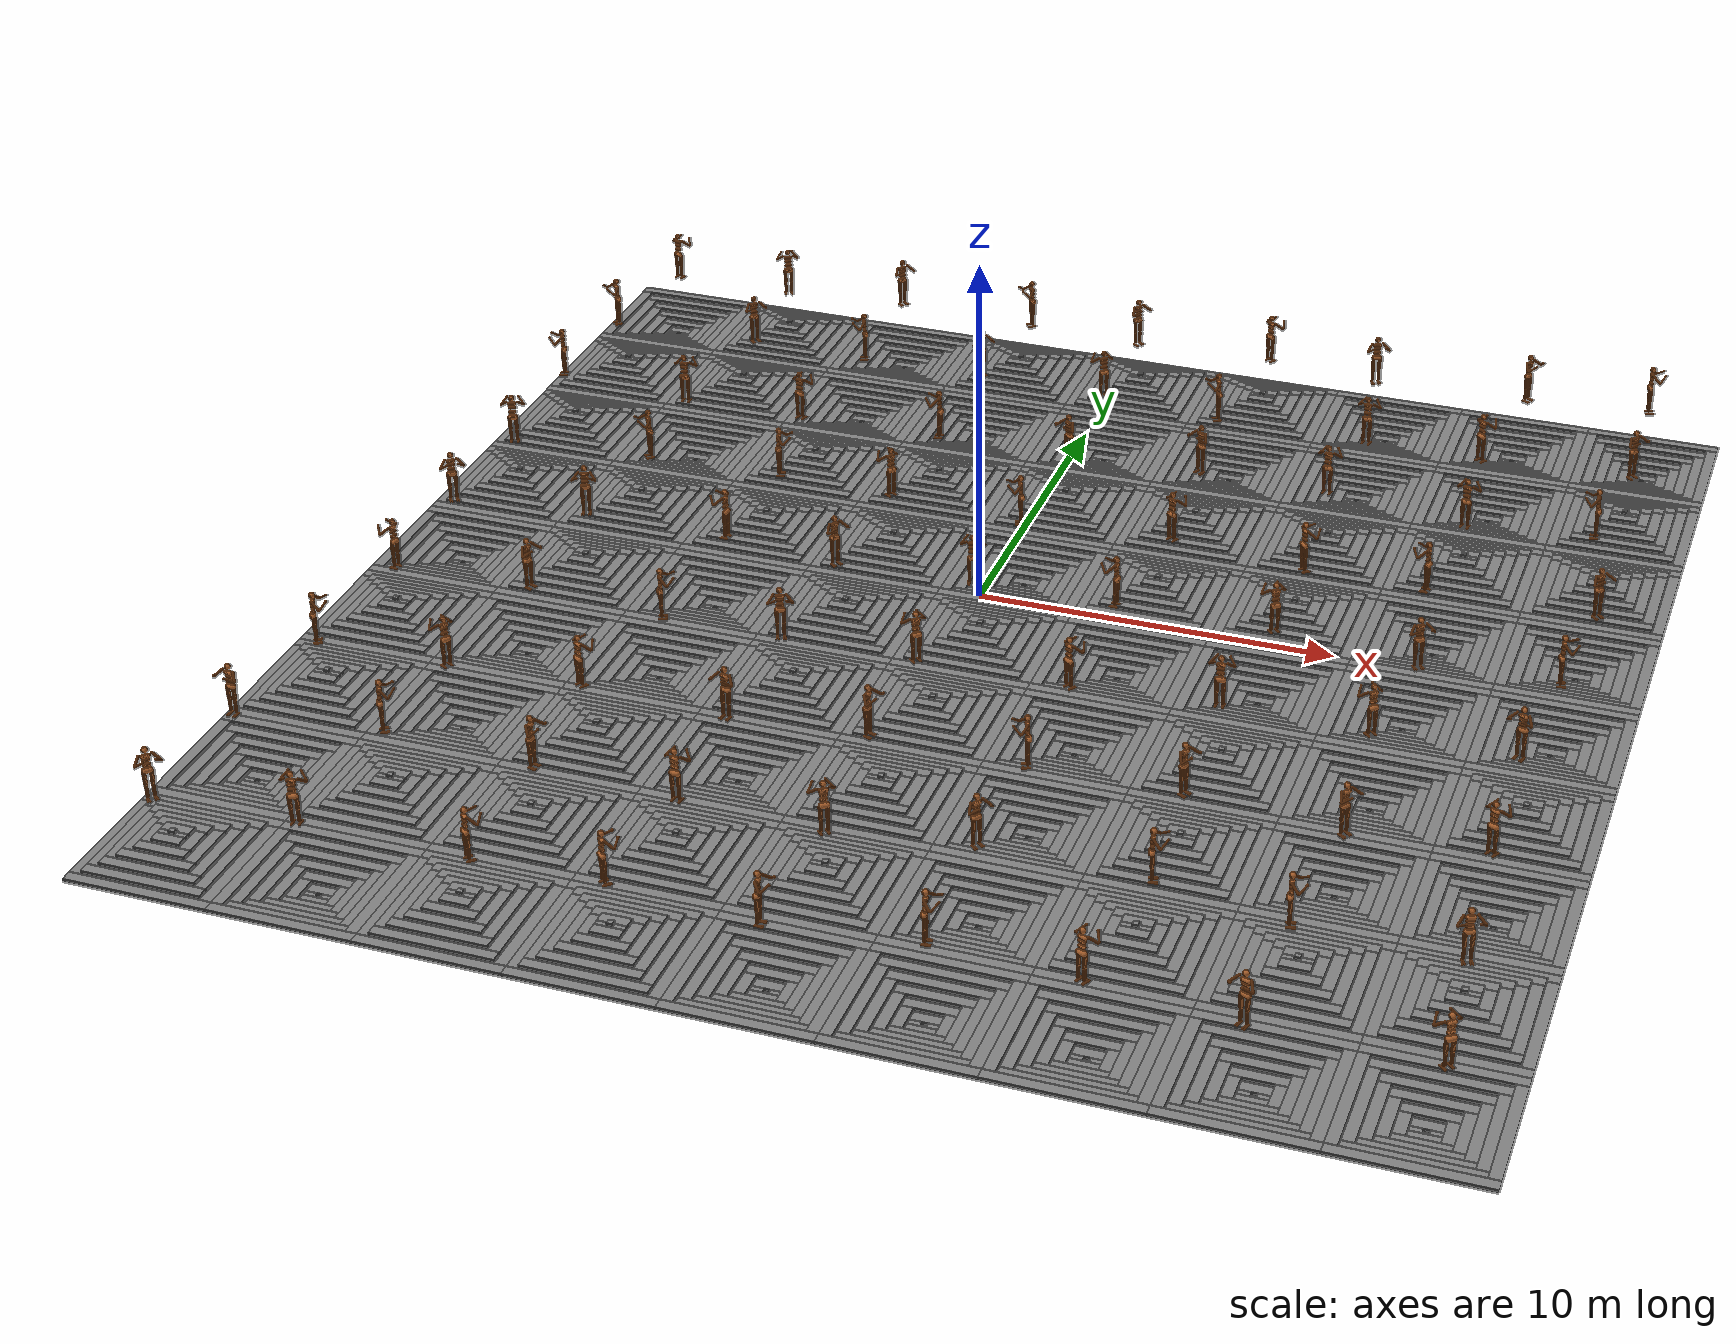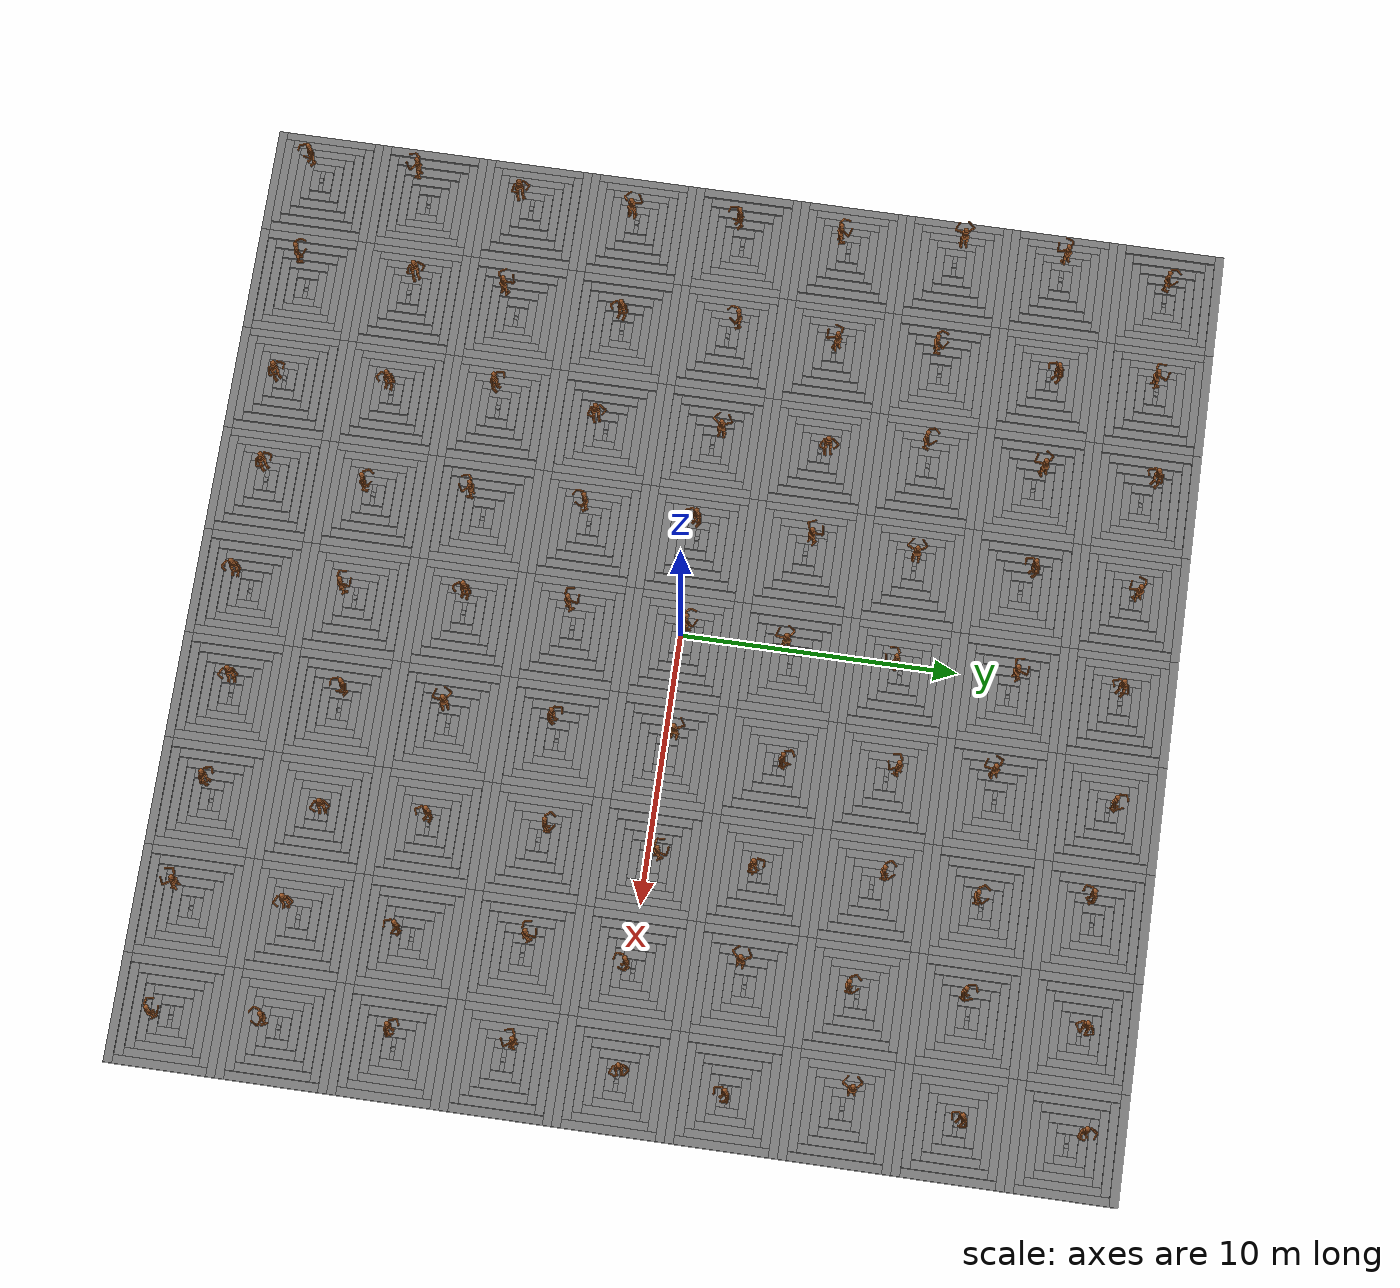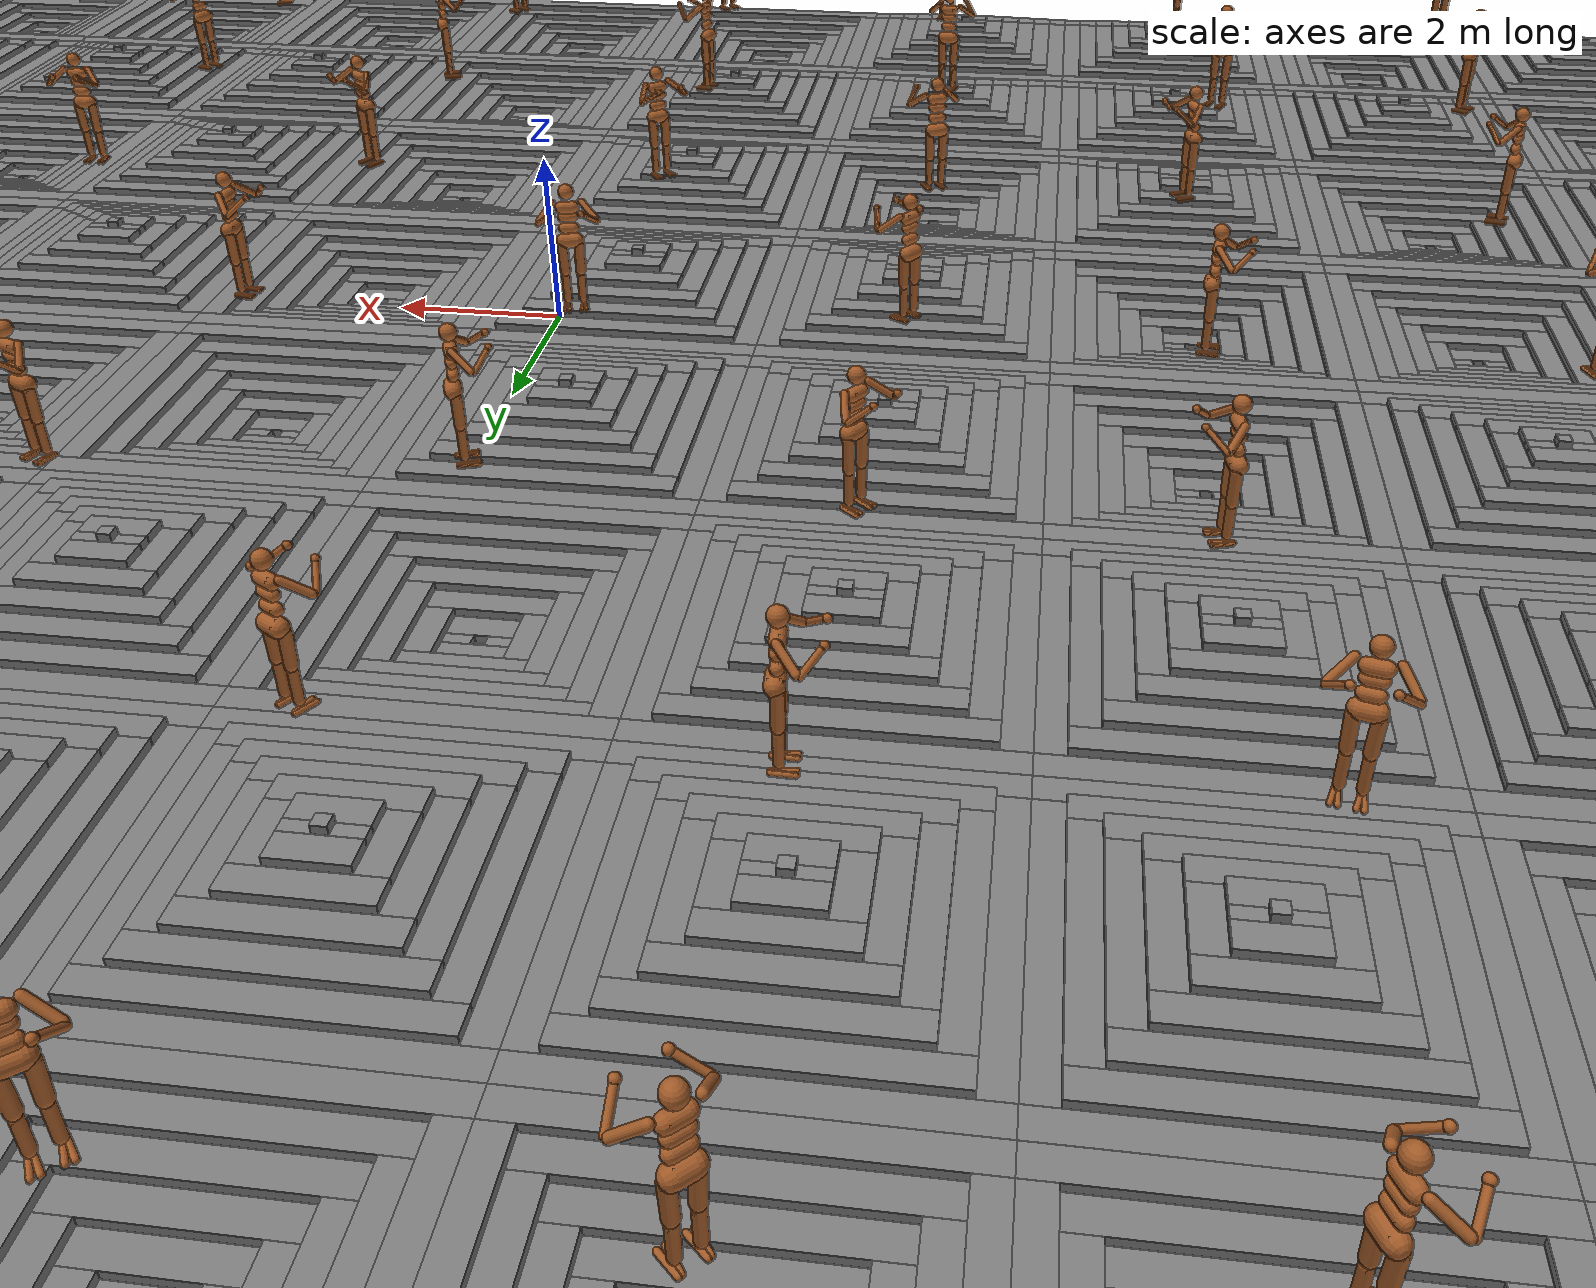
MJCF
<mujoco model="NxM Humanoids">
  <option timestep="0.005"/>

  <size memory="100M"/>

  <asset>
    <texture type="skybox" builtin="gradient" rgb1=".3 .5 .7" rgb2="0 0 0" width="512" height="512"/>
    <texture name="body" type="cube" builtin="flat" mark="cross" width="128" height="128"
             rgb1="0.8 0.6 0.4" rgb2="0.8 0.6 0.4" markrgb="1 1 1" random="0.01"/>
    <material name="body" texture="body" texuniform="true" rgba="0.8 0.6 .4 1"/>
    <texture name="grid" type="2d" builtin="checker" width="512" height="512" rgb1=".1 .2 .3" rgb2=".2 .3 .4"/>
    <material name="grid" texture="grid" texrepeat="1 1" texuniform="true" reflectance=".2"/>
  </asset>

  <default>
    <motor ctrlrange="-1 1" ctrllimited="true"/>
    <default class="body">
      <geom type="capsule" condim="1" friction=".7" solimp=".9 .99 .003" solref=".015 1" material="body"/>
      <joint type="hinge" damping=".2" stiffness="1" armature=".01" limited="true" solimplimit="0 .99 .01"/>
      <default class="big_joint">
        <joint damping="5" stiffness="10"/>
        <default class="big_stiff_joint">
          <joint stiffness="20"/>
        </default>
      </default>
    </default>
  </default>

  <visual>
    <map force="0.1" zfar="30"/>
    <rgba haze="0.15 0.25 0.35 1"/>
    <quality shadowsize="4096"/>
    <global offwidth="800" offheight="800"/>
  </visual>

  <worldbody>
    <light dir="0 0 -.4" diffuse=".8 .8 .8" specular="0.3 0.3 0.3" pos="8 8 14" cutoff="35"/>
    <light dir="0 0 -.4" diffuse=".8 .8 .8" specular="0.3 0.3 0.3" pos="-8 -8 14" cutoff="35"/>
    <light dir="0 0 -.4" diffuse=".8 .8 .8" specular="0.3 0.3 0.3" pos="8 -8 14" cutoff="35"/>
    <light dir="0 0 -.4" diffuse=".8 .8 .8" specular="0.3 0.3 0.3" pos="-8 8 14" cutoff="35"/>
    <geom type="box" pos="-16.000000 -14.160000 -1.475000" size="2.000000 0.160000 0.050000" rgba="0.5 0.5 0.5 1" />
    <geom type="box" pos="-16.000000 -17.840000 -1.475000" size="2.000000 0.160000 0.050000" rgba="0.5 0.5 0.5 1" />
    <geom type="box" pos="-14.160000 -16.000000 -1.475000" size="0.160000 1.680000 0.050000" rgba="0.5 0.5 0.5 1" />
    <geom type="box" pos="-17.840000 -16.000000 -1.475000" size="0.160000 1.680000 0.050000" rgba="0.5 0.5 0.5 1" />
    <geom type="box" pos="-16.000000 -14.480000 -1.375000" size="1.680000 0.160000 0.050000" rgba="0.5 0.5 0.5 1" />
    <geom type="box" pos="-16.000000 -17.520000 -1.375000" size="1.680000 0.160000 0.050000" rgba="0.5 0.5 0.5 1" />
    <geom type="box" pos="-14.480000 -16.000000 -1.375000" size="0.160000 1.360000 0.050000" rgba="0.5 0.5 0.5 1" />
    <geom type="box" pos="-17.520000 -16.000000 -1.375000" size="0.160000 1.360000 0.050000" rgba="0.5 0.5 0.5 1" />
    <geom type="box" pos="-16.000000 -14.800000 -1.275000" size="1.360000 0.160000 0.050000" rgba="0.5 0.5 0.5 1" />
    <geom type="box" pos="-16.000000 -17.200000 -1.275000" size="1.360000 0.160000 0.050000" rgba="0.5 0.5 0.5 1" />
    <geom type="box" pos="-14.800000 -16.000000 -1.275000" size="0.160000 1.040000 0.050000" rgba="0.5 0.5 0.5 1" />
    <geom type="box" pos="-17.200000 -16.000000 -1.275000" size="0.160000 1.040000 0.050000" rgba="0.5 0.5 0.5 1" />
    <geom type="box" pos="-16.000000 -15.120000 -1.175000" size="1.040000 0.160000 0.050000" rgba="0.5 0.5 0.5 1" />
    <geom type="box" pos="-16.000000 -16.880000 -1.175000" size="1.040000 0.160000 0.050000" rgba="0.5 0.5 0.5 1" />
    <geom type="box" pos="-15.120000 -16.000000 -1.175000" size="0.160000 0.720000 0.050000" rgba="0.5 0.5 0.5 1" />
    <geom type="box" pos="-16.880000 -16.000000 -1.175000" size="0.160000 0.720000 0.050000" rgba="0.5 0.5 0.5 1" />
    <geom type="box" pos="-16.000000 -15.440000 -1.075000" size="0.720000 0.160000 0.050000" rgba="0.5 0.5 0.5 1" />
    <geom type="box" pos="-16.000000 -16.560000 -1.075000" size="0.720000 0.160000 0.050000" rgba="0.5 0.5 0.5 1" />
    <geom type="box" pos="-15.440000 -16.000000 -1.075000" size="0.160000 0.400000 0.050000" rgba="0.5 0.5 0.5 1" />
    <geom type="box" pos="-16.560000 -16.000000 -1.075000" size="0.160000 0.400000 0.050000" rgba="0.5 0.5 0.5 1" />
    <geom type="box" pos="-16.000000 -15.760000 -0.975000" size="0.400000 0.160000 0.050000" rgba="0.5 0.5 0.5 1" />
    <geom type="box" pos="-16.000000 -16.240000 -0.975000" size="0.400000 0.160000 0.050000" rgba="0.5 0.5 0.5 1" />
    <geom type="box" pos="-15.760000 -16.000000 -0.975000" size="0.160000 0.080000 0.050000" rgba="0.5 0.5 0.5 1" />
    <geom type="box" pos="-16.240000 -16.000000 -0.975000" size="0.160000 0.080000 0.050000" rgba="0.5 0.5 0.5 1" />
    <geom type="box" pos="-16.000000 -16.000000 -0.875000" size="0.080000 0.080000 0.050000" rgba="0.5 0.5 0.5 1" />

    <geom type="box" pos="-16.000000 -10.160000 -1.475000" size="2.000000 0.160000 0.050000" rgba="0.5 0.5 0.5 1" />
    <geom type="box" pos="-16.000000 -13.840000 -1.475000" size="2.000000 0.160000 0.050000" rgba="0.5 0.5 0.5 1" />
    <geom type="box" pos="-14.160000 -12.000000 -1.475000" size="0.160000 1.680000 0.050000" rgba="0.5 0.5 0.5 1" />
    <geom type="box" pos="-17.840000 -12.000000 -1.475000" size="0.160000 1.680000 0.050000" rgba="0.5 0.5 0.5 1" />
    <geom type="box" pos="-16.000000 -10.480000 -1.575000" size="1.680000 0.160000 0.050000" rgba="0.5 0.5 0.5 1" />
    <geom type="box" pos="-16.000000 -13.520000 -1.575000" size="1.680000 0.160000 0.050000" rgba="0.5 0.5 0.5 1" />
    <geom type="box" pos="-14.480000 -12.000000 -1.575000" size="0.160000 1.360000 0.050000" rgba="0.5 0.5 0.5 1" />
    <geom type="box" pos="-17.520000 -12.000000 -1.575000" size="0.160000 1.360000 0.050000" rgba="0.5 0.5 0.5 1" />
    <geom type="box" pos="-16.000000 -10.800000 -1.675000" size="1.360000 0.160000 0.050000" rgba="0.5 0.5 0.5 1" />
    <geom type="box" pos="-16.000000 -13.200000 -1.675000" size="1.360000 0.160000 0.050000" rgba="0.5 0.5 0.5 1" />
    <geom type="box" pos="-14.800000 -12.000000 -1.675000" size="0.160000 1.040000 0.050000" rgba="0.5 0.5 0.5 1" />
    <geom type="box" pos="-17.200000 -12.000000 -1.675000" size="0.160000 1.040000 0.050000" rgba="0.5 0.5 0.5 1" />
    <geom type="box" pos="-16.000000 -11.120000 -1.775000" size="1.040000 0.160000 0.050000" rgba="0.5 0.5 0.5 1" />
    <geom type="box" pos="-16.000000 -12.880000 -1.775000" size="1.040000 0.160000 0.050000" rgba="0.5 0.5 0.5 1" />
    <geom type="box" pos="-15.120000 -12.000000 -1.775000" size="0.160000 0.720000 0.050000" rgba="0.5 0.5 0.5 1" />
    <geom type="box" pos="-16.880000 -12.000000 -1.775000" size="0.160000 0.720000 0.050000" rgba="0.5 0.5 0.5 1" />
    <geom type="box" pos="-16.000000 -11.440000 -1.875000" size="0.720000 0.160000 0.050000" rgba="0.5 0.5 0.5 1" />
    <geom type="box" pos="-16.000000 -12.560000 -1.875000" size="0.720000 0.160000 0.050000" rgba="0.5 0.5 0.5 1" />
    <geom type="box" pos="-15.440000 -12.000000 -1.875000" size="0.160000 0.400000 0.050000" rgba="0.5 0.5 0.5 1" />
    <geom type="box" pos="-16.560000 -12.000000 -1.875000" size="0.160000 0.400000 0.050000" rgba="0.5 0.5 0.5 1" />
    <geom type="box" pos="-16.000000 -11.760000 -1.975000" size="0.400000 0.160000 0.050000" rgba="0.5 0.5 0.5 1" />
    <geom type="box" pos="-16.000000 -12.240000 -1.975000" size="0.400000 0.160000 0.050000" rgba="0.5 0.5 0.5 1" />
    <geom type="box" pos="-15.760000 -12.000000 -1.975000" size="0.160000 0.080000 0.050000" rgba="0.5 0.5 0.5 1" />
    <geom type="box" pos="-16.240000 -12.000000 -1.975000" size="0.160000 0.080000 0.050000" rgba="0.5 0.5 0.5 1" />
    <geom type="box" pos="-16.000000 -12.000000 -2.075000" size="0.080000 0.080000 0.050000" rgba="0.5 0.5 0.5 1" />

    <geom type="box" pos="-16.000000 -6.160000 -1.475000" size="2.000000 0.160000 0.050000" rgba="0.5 0.5 0.5 1" />
    <geom type="box" pos="-16.000000 -9.840000 -1.475000" size="2.000000 0.160000 0.050000" rgba="0.5 0.5 0.5 1" />
    <geom type="box" pos="-14.160000 -8.000000 -1.475000" size="0.160000 1.680000 0.050000" rgba="0.5 0.5 0.5 1" />
    <geom type="box" pos="-17.840000 -8.000000 -1.475000" size="0.160000 1.680000 0.050000" rgba="0.5 0.5 0.5 1" />
    <geom type="box" pos="-16.000000 -6.480000 -1.375000" size="1.680000 0.160000 0.050000" rgba="0.5 0.5 0.5 1" />
    <geom type="box" pos="-16.000000 -9.520000 -1.375000" size="1.680000 0.160000 0.050000" rgba="0.5 0.5 0.5 1" />
    <geom type="box" pos="-14.480000 -8.000000 -1.375000" size="0.160000 1.360000 0.050000" rgba="0.5 0.5 0.5 1" />
    <geom type="box" pos="-17.520000 -8.000000 -1.375000" size="0.160000 1.360000 0.050000" rgba="0.5 0.5 0.5 1" />
    <geom type="box" pos="-16.000000 -6.800000 -1.275000" size="1.360000 0.160000 0.050000" rgba="0.5 0.5 0.5 1" />
    <geom type="box" pos="-16.000000 -9.200000 -1.275000" size="1.360000 0.160000 0.050000" rgba="0.5 0.5 0.5 1" />
    <geom type="box" pos="-14.800000 -8.000000 -1.275000" size="0.160000 1.040000 0.050000" rgba="0.5 0.5 0.5 1" />
    <geom type="box" pos="-17.200000 -8.000000 -1.275000" size="0.160000 1.040000 0.050000" rgba="0.5 0.5 0.5 1" />
    <geom type="box" pos="-16.000000 -7.120000 -1.175000" size="1.040000 0.160000 0.050000" rgba="0.5 0.5 0.5 1" />
    <geom type="box" pos="-16.000000 -8.880000 -1.175000" size="1.040000 0.160000 0.050000" rgba="0.5 0.5 0.5 1" />
    <geom type="box" pos="-15.120000 -8.000000 -1.175000" size="0.160000 0.720000 0.050000" rgba="0.5 0.5 0.5 1" />
    <geom type="box" pos="-16.880000 -8.000000 -1.175000" size="0.160000 0.720000 0.050000" rgba="0.5 0.5 0.5 1" />
    <geom type="box" pos="-16.000000 -7.440000 -1.075000" size="0.720000 0.160000 0.050000" rgba="0.5 0.5 0.5 1" />
    <geom type="box" pos="-16.000000 -8.560000 -1.075000" size="0.720000 0.160000 0.050000" rgba="0.5 0.5 0.5 1" />
    <geom type="box" pos="-15.440000 -8.000000 -1.075000" size="0.160000 0.400000 0.050000" rgba="0.5 0.5 0.5 1" />
    <geom type="box" pos="-16.560000 -8.000000 -1.075000" size="0.160000 0.400000 0.050000" rgba="0.5 0.5 0.5 1" />
    <geom type="box" pos="-16.000000 -7.760000 -0.975000" size="0.400000 0.160000 0.050000" rgba="0.5 0.5 0.5 1" />
    <geom type="box" pos="-16.000000 -8.240000 -0.975000" size="0.400000 0.160000 0.050000" rgba="0.5 0.5 0.5 1" />
    <geom type="box" pos="-15.760000 -8.000000 -0.975000" size="0.160000 0.080000 0.050000" rgba="0.5 0.5 0.5 1" />
    <geom type="box" pos="-16.240000 -8.000000 -0.975000" size="0.160000 0.080000 0.050000" rgba="0.5 0.5 0.5 1" />
    <geom type="box" pos="-16.000000 -8.000000 -0.875000" size="0.080000 0.080000 0.050000" rgba="0.5 0.5 0.5 1" />

    <geom type="box" pos="-16.000000 -2.160000 -1.475000" size="2.000000 0.160000 0.050000" rgba="0.5 0.5 0.5 1" />
    <geom type="box" pos="-16.000000 -5.840000 -1.475000" size="2.000000 0.160000 0.050000" rgba="0.5 0.5 0.5 1" />
    <geom type="box" pos="-14.160000 -4.000000 -1.475000" size="0.160000 1.680000 0.050000" rgba="0.5 0.5 0.5 1" />
    <geom type="box" pos="-17.840000 -4.000000 -1.475000" size="0.160000 1.680000 0.050000" rgba="0.5 0.5 0.5 1" />
    <geom type="box" pos="-16.000000 -2.480000 -1.375000" size="1.680000 0.160000 0.050000" rgba="0.5 0.5 0.5 1" />
    <geom type="box" pos="-16.000000 -5.520000 -1.375000" size="1.680000 0.160000 0.050000" rgba="0.5 0.5 0.5 1" />
    <geom type="box" pos="-14.480000 -4.000000 -1.375000" size="0.160000 1.360000 0.050000" rgba="0.5 0.5 0.5 1" />
    <geom type="box" pos="-17.520000 -4.000000 -1.375000" size="0.160000 1.360000 0.050000" rgba="0.5 0.5 0.5 1" />
    <geom type="box" pos="-16.000000 -2.800000 -1.275000" size="1.360000 0.160000 0.050000" rgba="0.5 0.5 0.5 1" />
    <geom type="box" pos="-16.000000 -5.200000 -1.275000" size="1.360000 0.160000 0.050000" rgba="0.5 0.5 0.5 1" />
    <geom type="box" pos="-14.800000 -4.000000 -1.275000" size="0.160000 1.040000 0.050000" rgba="0.5 0.5 0.5 1" />
    <geom type="box" pos="-17.200000 -4.000000 -1.275000" size="0.160000 1.040000 0.050000" rgba="0.5 0.5 0.5 1" />
    <geom type="box" pos="-16.000000 -3.120000 -1.175000" size="1.040000 0.160000 0.050000" rgba="0.5 0.5 0.5 1" />
    <geom type="box" pos="-16.000000 -4.880000 -1.175000" size="1.040000 0.160000 0.050000" rgba="0.5 0.5 0.5 1" />
    <geom type="box" pos="-15.120000 -4.000000 -1.175000" size="0.160000 0.720000 0.050000" rgba="0.5 0.5 0.5 1" />
    <geom type="box" pos="-16.880000 -4.000000 -1.175000" size="0.160000 0.720000 0.050000" rgba="0.5 0.5 0.5 1" />
    <geom type="box" pos="-16.000000 -3.440000 -1.075000" size="0.720000 0.160000 0.050000" rgba="0.5 0.5 0.5 1" />
    <geom type="box" pos="-16.000000 -4.560000 -1.075000" size="0.720000 0.160000 0.050000" rgba="0.5 0.5 0.5 1" />
    <geom type="box" pos="-15.440000 -4.000000 -1.075000" size="0.160000 0.400000 0.050000" rgba="0.5 0.5 0.5 1" />
    <geom type="box" pos="-16.560000 -4.000000 -1.075000" size="0.160000 0.400000 0.050000" rgba="0.5 0.5 0.5 1" />
    <geom type="box" pos="-16.000000 -3.760000 -0.975000" size="0.400000 0.160000 0.050000" rgba="0.5 0.5 0.5 1" />
    <geom type="box" pos="-16.000000 -4.240000 -0.975000" size="0.400000 0.160000 0.050000" rgba="0.5 0.5 0.5 1" />
    <geom type="box" pos="-15.760000 -4.000000 -0.975000" size="0.160000 0.080000 0.050000" rgba="0.5 0.5 0.5 1" />
    <geom type="box" pos="-16.240000 -4.000000 -0.975000" size="0.160000 0.080000 0.050000" rgba="0.5 0.5 0.5 1" />
    <geom type="box" pos="-16.000000 -4.000000 -0.875000" size="0.080000 0.080000 0.050000" rgba="0.5 0.5 0.5 1" />

    <geom type="box" pos="-16.000000 1.840000 -1.475000" size="2.000000 0.160000 0.050000" rgba="0.5 0.5 0.5 1" />
    <geom type="box" pos="-16.000000 -1.840000 -1.475000" size="2.000000 0.160000 0.050000" rgba="0.5 0.5 0.5 1" />
    <geom type="box" pos="-14.160000 0.000000 -1.475000" size="0.160000 1.680000 0.050000" rgba="0.5 0.5 0.5 1" />
    <geom type="box" pos="-17.840000 0.000000 -1.475000" size="0.160000 1.680000 0.050000" rgba="0.5 0.5 0.5 1" />
    <geom type="box" pos="-16.000000 1.520000 -1.575000" size="1.680000 0.160000 0.050000" rgba="0.5 0.5 0.5 1" />
    <geom type="box" pos="-16.000000 -1.520000 -1.575000" size="1.680000 0.160000 0.050000" rgba="0.5 0.5 0.5 1" />
    <geom type="box" pos="-14.480000 0.000000 -1.575000" size="0.160000 1.360000 0.050000" rgba="0.5 0.5 0.5 1" />
    <geom type="box" pos="-17.520000 0.000000 -1.575000" size="0.160000 1.360000 0.050000" rgba="0.5 0.5 0.5 1" />
    <geom type="box" pos="-16.000000 1.200000 -1.675000" size="1.360000 0.160000 0.050000" rgba="0.5 0.5 0.5 1" />
    <geom type="box" pos="-16.000000 -1.200000 -1.675000" size="1.360000 0.160000 0.050000" rgba="0.5 0.5 0.5 1" />
    <geom type="box" pos="-14.800000 0.000000 -1.675000" size="0.160000 1.040000 0.050000" rgba="0.5 0.5 0.5 1" />
    <geom type="box" pos="-17.200000 0.000000 -1.675000" size="0.160000 1.040000 0.050000" rgba="0.5 0.5 0.5 1" />
    <geom type="box" pos="-16.000000 0.880000 -1.775000" size="1.040000 0.160000 0.050000" rgba="0.5 0.5 0.5 1" />
    <geom type="box" pos="-16.000000 -0.880000 -1.775000" size="1.040000 0.160000 0.050000" rgba="0.5 0.5 0.5 1" />
    <geom type="box" pos="-15.120000 0.000000 -1.775000" size="0.160000 0.720000 0.050000" rgba="0.5 0.5 0.5 1" />
    <geom type="box" pos="-16.880000 0.000000 -1.775000" size="0.160000 0.720000 0.050000" rgba="0.5 0.5 0.5 1" />
    <geom type="box" pos="-16.000000 0.560000 -1.875000" size="0.720000 0.160000 0.050000" rgba="0.5 0.5 0.5 1" />
    <geom type="box" pos="-16.000000 -0.560000 -1.875000" size="0.720000 0.160000 0.050000" rgba="0.5 0.5 0.5 1" />
    <geom type="box" pos="-15.440000 0.000000 -1.875000" size="0.160000 0.400000 0.050000" rgba="0.5 0.5 0.5 1" />
    <geom type="box" pos="-16.560000 0.000000 -1.875000" size="0.160000 0.400000 0.050000" rgba="0.5 0.5 0.5 1" />
    <geom type="box" pos="-16.000000 0.240000 -1.975000" size="0.400000 0.160000 0.050000" rgba="0.5 0.5 0.5 1" />
    <geom type="box" pos="-16.000000 -0.240000 -1.975000" size="0.400000 0.160000 0.050000" rgba="0.5 0.5 0.5 1" />
    <geom type="box" pos="-15.760000 0.000000 -1.975000" size="0.160000 0.080000 0.050000" rgba="0.5 0.5 0.5 1" />
    <geom type="box" pos="-16.240000 0.000000 -1.975000" size="0.160000 0.080000 0.050000" rgba="0.5 0.5 0.5 1" />
    <geom type="box" pos="-16.000000 0.000000 -2.075000" size="0.080000 0.080000 0.050000" rgba="0.5 0.5 0.5 1" />

    <geom type="box" pos="-16.000000 5.840000 -1.475000" size="2.000000 0.160000 0.050000" rgba="0.5 0.5 0.5 1" />
    <geom type="box" pos="-16.000000 2.160000 -1.475000" size="2.000000 0.160000 0.050000" rgba="0.5 0.5 0.5 1" />
    <geom type="box" pos="-14.160000 4.000000 -1.475000" size="0.160000 1.680000 0.050000" rgba="0.5 0.5 0.5 1" />
    <geom type="box" pos="-17.840000 4.000000 -1.475000" size="0.160000 1.680000 0.050000" rgba="0.5 0.5 0.5 1" />
    <geom type="box" pos="-16.000000 5.520000 -1.375000" size="1.680000 0.160000 0.050000" rgba="0.5 0.5 0.5 1" />
    <geom type="box" pos="-16.000000 2.480000 -1.375000" size="1.680000 0.160000 0.050000" rgba="0.5 0.5 0.5 1" />
    <geom type="box" pos="-14.480000 4.000000 -1.375000" size="0.160000 1.360000 0.050000" rgba="0.5 0.5 0.5 1" />
    <geom type="box" pos="-17.520000 4.000000 -1.375000" size="0.160000 1.360000 0.050000" rgba="0.5 0.5 0.5 1" />
    <geom type="box" pos="-16.000000 5.200000 -1.275000" size="1.360000 0.160000 0.050000" rgba="0.5 0.5 0.5 1" />
    <geom type="box" pos="-16.000000 2.800000 -1.275000" size="1.360000 0.160000 0.050000" rgba="0.5 0.5 0.5 1" />
    <geom type="box" pos="-14.800000 4.000000 -1.275000" size="0.160000 1.040000 0.050000" rgba="0.5 0.5 0.5 1" />
    <geom type="box" pos="-17.200000 4.000000 -1.275000" size="0.160000 1.040000 0.050000" rgba="0.5 0.5 0.5 1" />
    <geom type="box" pos="-16.000000 4.880000 -1.175000" size="1.040000 0.160000 0.050000" rgba="0.5 0.5 0.5 1" />
    <geom type="box" pos="-16.000000 3.120000 -1.175000" size="1.040000 0.160000 0.050000" rgba="0.5 0.5 0.5 1" />
    <geom type="box" pos="-15.120000 4.000000 -1.175000" size="0.160000 0.720000 0.050000" rgba="0.5 0.5 0.5 1" />
    <geom type="box" pos="-16.880000 4.000000 -1.175000" size="0.160000 0.720000 0.050000" rgba="0.5 0.5 0.5 1" />
    <geom type="box" pos="-16.000000 4.560000 -1.075000" size="0.720000 0.160000 0.050000" rgba="0.5 0.5 0.5 1" />
    <geom type="box" pos="-16.000000 3.440000 -1.075000" size="0.720000 0.160000 0.050000" rgba="0.5 0.5 0.5 1" />
    <geom type="box" pos="-15.440000 4.000000 -1.075000" size="0.160000 0.400000 0.050000" rgba="0.5 0.5 0.5 1" />
    <geom type="box" pos="-16.560000 4.000000 -1.075000" size="0.160000 0.400000 0.050000" rgba="0.5 0.5 0.5 1" />
    <geom type="box" pos="-16.000000 4.240000 -0.975000" size="0.400000 0.160000 0.050000" rgba="0.5 0.5 0.5 1" />
    <geom type="box" pos="-16.000000 3.760000 -0.975000" size="0.400000 0.160000 0.050000" rgba="0.5 0.5 0.5 1" />
    <geom type="box" pos="-15.760000 4.000000 -0.975000" size="0.160000 0.080000 0.050000" rgba="0.5 0.5 0.5 1" />
    <geom type="box" pos="-16.240000 4.000000 -0.975000" size="0.160000 0.080000 0.050000" rgba="0.5 0.5 0.5 1" />
    <geom type="box" pos="-16.000000 4.000000 -0.875000" size="0.080000 0.080000 0.050000" rgba="0.5 0.5 0.5 1" />

    <geom type="box" pos="-16.000000 9.840000 -1.475000" size="2.000000 0.160000 0.050000" rgba="0.5 0.5 0.5 1" />
    <geom type="box" pos="-16.000000 6.160000 -1.475000" size="2.000000 0.160000 0.050000" rgba="0.5 0.5 0.5 1" />
    <geom type="box" pos="-14.160000 8.000000 -1.475000" size="0.160000 1.680000 0.050000" rgba="0.5 0.5 0.5 1" />
    <geom type="box" pos="-17.840000 8.000000 -1.475000" size="0.160000 1.680000 0.050000" rgba="0.5 0.5 0.5 1" />
    <geom type="box" pos="-16.000000 9.520000 -1.375000" size="1.680000 0.160000 0.050000" rgba="0.5 0.5 0.5 1" />
    <geom type="box" pos="-16.000000 6.480000 -1.375000" size="1.680000 0.160000 0.050000" rgba="0.5 0.5 0.5 1" />
    <geom type="box" pos="-14.480000 8.000000 -1.375000" size="0.160000 1.360000 0.050000" rgba="0.5 0.5 0.5 1" />
    <geom type="box" pos="-17.520000 8.000000 -1.375000" size="0.160000 1.360000 0.050000" rgba="0.5 0.5 0.5 1" />
    <geom type="box" pos="-16.000000 9.200000 -1.275000" size="1.360000 0.160000 0.050000" rgba="0.5 0.5 0.5 1" />
    <geom type="box" pos="-16.000000 6.800000 -1.275000" size="1.360000 0.160000 0.050000" rgba="0.5 0.5 0.5 1" />
    <geom type="box" pos="-14.800000 8.000000 -1.275000" size="0.160000 1.040000 0.050000" rgba="0.5 0.5 0.5 1" />
    <geom type="box" pos="-17.200000 8.000000 -1.275000" size="0.160000 1.040000 0.050000" rgba="0.5 0.5 0.5 1" />
    <geom type="box" pos="-16.000000 8.880000 -1.175000" size="1.040000 0.160000 0.050000" rgba="0.5 0.5 0.5 1" />
    <geom type="box" pos="-16.000000 7.120000 -1.175000" size="1.040000 0.160000 0.050000" rgba="0.5 0.5 0.5 1" />
    <geom type="box" pos="-15.120000 8.000000 -1.175000" size="0.160000 0.720000 0.050000" rgba="0.5 0.5 0.5 1" />
    <geom type="box" pos="-16.880000 8.000000 -1.175000" size="0.160000 0.720000 0.050000" rgba="0.5 0.5 0.5 1" />
    <geom type="box" pos="-16.000000 8.560000 -1.075000" size="0.720000 0.160000 0.050000" rgba="0.5 0.5 0.5 1" />
    <geom type="box" pos="-16.000000 7.440000 -1.075000" size="0.720000 0.160000 0.050000" rgba="0.5 0.5 0.5 1" />
    <geom type="box" pos="-15.440000 8.000000 -1.075000" size="0.160000 0.400000 0.050000" rgba="0.5 0.5 0.5 1" />
    <geom type="box" pos="-16.560000 8.000000 -1.075000" size="0.160000 0.400000 0.050000" rgba="0.5 0.5 0.5 1" />
    <geom type="box" pos="-16.000000 8.240000 -0.975000" size="0.400000 0.160000 0.050000" rgba="0.5 0.5 0.5 1" />
    <geom type="box" pos="-16.000000 7.760000 -0.975000" size="0.400000 0.160000 0.050000" rgba="0.5 0.5 0.5 1" />
    <geom type="box" pos="-15.760000 8.000000 -0.975000" size="0.160000 0.080000 0.050000" rgba="0.5 0.5 0.5 1" />
    <geom type="box" pos="-16.240000 8.000000 -0.975000" size="0.160000 0.080000 0.050000" rgba="0.5 0.5 0.5 1" />
    <geom type="box" pos="-16.000000 8.000000 -0.875000" size="0.080000 0.080000 0.050000" rgba="0.5 0.5 0.5 1" />

    <geom type="box" pos="-16.000000 13.840000 -1.475000" size="2.000000 0.160000 0.050000" rgba="0.5 0.5 0.5 1" />
    <geom type="box" pos="-16.000000 10.160000 -1.475000" size="2.000000 0.160000 0.050000" rgba="0.5 0.5 0.5 1" />
    <geom type="box" pos="-14.160000 12.000000 -1.475000" size="0.160000 1.680000 0.050000" rgba="0.5 0.5 0.5 1" />
    <geom type="box" pos="-17.840000 12.000000 -1.475000" size="0.160000 1.680000 0.050000" rgba="0.5 0.5 0.5 1" />
    <geom type="box" pos="-16.000000 13.520000 -1.375000" size="1.680000 0.160000 0.050000" rgba="0.5 0.5 0.5 1" />
    <geom type="box" pos="-16.000000 10.480000 -1.375000" size="1.680000 0.160000 0.050000" rgba="0.5 0.5 0.5 1" />
    <geom type="box" pos="-14.480000 12.000000 -1.375000" size="0.160000 1.360000 0.050000" rgba="0.5 0.5 0.5 1" />
    <geom type="box" pos="-17.520000 12.000000 -1.375000" size="0.160000 1.360000 0.050000" rgba="0.5 0.5 0.5 1" />
    <geom type="box" pos="-16.000000 13.200000 -1.275000" size="1.360000 0.160000 0.050000" rgba="0.5 0.5 0.5 1" />
    <geom type="box" pos="-16.000000 10.800000 -1.275000" size="1.360000 0.160000 0.050000" rgba="0.5 0.5 0.5 1" />
    <geom type="box" pos="-14.800000 12.000000 -1.275000" size="0.160000 1.040000 0.050000" rgba="0.5 0.5 0.5 1" />
    <geom type="box" pos="-17.200000 12.000000 -1.275000" size="0.160000 1.040000 0.050000" rgba="0.5 0.5 0.5 1" />
    <geom type="box" pos="-16.000000 12.880000 -1.175000" size="1.040000 0.160000 0.050000" rgba="0.5 0.5 0.5 1" />
    <geom type="box" pos="-16.000000 11.120000 -1.175000" size="1.040000 0.160000 0.050000" rgba="0.5 0.5 0.5 1" />
    <geom type="box" pos="-15.120000 12.000000 -1.175000" size="0.160000 0.720000 0.050000" rgba="0.5 0.5 0.5 1" />
    <geom type="box" pos="-16.880000 12.000000 -1.175000" size="0.160000 0.720000 0.050000" rgba="0.5 0.5 0.5 1" />
    <geom type="box" pos="-16.000000 12.560000 -1.075000" size="0.720000 0.160000 0.050000" rgba="0.5 0.5 0.5 1" />
    <geom type="box" pos="-16.000000 11.440000 -1.075000" size="0.720000 0.160000 0.050000" rgba="0.5 0.5 0.5 1" />
    <geom type="box" pos="-15.440000 12.000000 -1.075000" size="0.160000 0.400000 0.050000" rgba="0.5 0.5 0.5 1" />
    <geom type="box" pos="-16.560000 12.000000 -1.075000" size="0.160000 0.400000 0.050000" rgba="0.5 0.5 0.5 1" />
    <geom type="box" pos="-16.000000 12.240000 -0.975000" size="0.400000 0.160000 0.050000" rgba="0.5 0.5 0.5 1" />
    <geom type="box" pos="-16.000000 11.760000 -0.975000" size="0.400000 0.160000 0.050000" rgba="0.5 0.5 0.5 1" />
    <geom type="box" pos="-15.760000 12.000000 -0.975000" size="0.160000 0.080000 0.050000" rgba="0.5 0.5 0.5 1" />
    <geom type="box" pos="-16.240000 12.000000 -0.975000" size="0.160000 0.080000 0.050000" rgba="0.5 0.5 0.5 1" />
    <geom type="box" pos="-16.000000 12.000000 -0.875000" size="0.080000 0.080000 0.050000" rgba="0.5 0.5 0.5 1" />

    <geom type="box" pos="-16.000000 17.840000 -1.475000" size="2.000000 0.160000 0.050000" rgba="0.5 0.5 0.5 1" />
    <geom type="box" pos="-16.000000 14.160000 -1.475000" size="2.000000 0.160000 0.050000" rgba="0.5 0.5 0.5 1" />
    <geom type="box" pos="-14.160000 16.000000 -1.475000" size="0.160000 1.680000 0.050000" rgba="0.5 0.5 0.5 1" />
    <geom type="box" pos="-17.840000 16.000000 -1.475000" size="0.160000 1.680000 0.050000" rgba="0.5 0.5 0.5 1" />
    <geom type="box" pos="-16.000000 17.520000 -1.575000" size="1.680000 0.160000 0.050000" rgba="0.5 0.5 0.5 1" />
    <geom type="box" pos="-16.000000 14.480000 -1.575000" size="1.680000 0.160000 0.050000" rgba="0.5 0.5 0.5 1" />
    <geom type="box" pos="-14.480000 16.000000 -1.575000" size="0.160000 1.360000 0.050000" rgba="0.5 0.5 0.5 1" />
    <geom type="box" pos="-17.520000 16.000000 -1.575000" size="0.160000 1.360000 0.050000" rgba="0.5 0.5 0.5 1" />
    <geom type="box" pos="-16.000000 17.200000 -1.675000" size="1.360000 0.160000 0.050000" rgba="0.5 0.5 0.5 1" />
    <geom type="box" pos="-16.000000 14.800000 -1.675000" size="1.360000 0.160000 0.050000" rgba="0.5 0.5 0.5 1" />
    <geom type="box" pos="-14.800000 16.000000 -1.675000" size="0.160000 1.040000 0.050000" rgba="0.5 0.5 0.5 1" />
    <geom type="box" pos="-17.200000 16.000000 -1.675000" size="0.160000 1.040000 0.050000" rgba="0.5 0.5 0.5 1" />
    <geom type="box" pos="-16.000000 16.880000 -1.775000" size="1.040000 0.160000 0.050000" rgba="0.5 0.5 0.5 1" />
    <geom type="box" pos="-16.000000 15.120000 -1.775000" size="1.040000 0.160000 0.050000" rgba="0.5 0.5 0.5 1" />
    <geom type="box" pos="-15.120000 16.000000 -1.775000" size="0.160000 0.720000 0.050000" rgba="0.5 0.5 0.5 1" />
    <geom type="box" pos="-16.880000 16.000000 -1.775000" size="0.160000 0.720000 0.050000" rgba="0.5 0.5 0.5 1" />
    <geom type="box" pos="-16.000000 16.560000 -1.875000" size="0.720000 0.160000 0.050000" rgba="0.5 0.5 0.5 1" />
    <geom type="box" pos="-16.000000 15.440000 -1.875000" size="0.720000 0.160000 0.050000" rgba="0.5 0.5 0.5 1" />
    <geom type="box" pos="-15.440000 16.000000 -1.875000" size="0.160000 0.400000 0.050000" rgba="0.5 0.5 0.5 1" />
    <geom type="box" pos="-16.560000 16.000000 -1.875000" size="0.160000 0.400000 0.050000" rgba="0.5 0.5 0.5 1" />
    <geom type="box" pos="-16.000000 16.240000 -1.975000" size="0.400000 0.160000 0.050000" rgba="0.5 0.5 0.5 1" />
    <geom type="box" pos="-16.000000 15.760000 -1.975000" size="0.400000 0.160000 0.050000" rgba="0.5 0.5 0.5 1" />
    <geom type="box" pos="-15.760000 16.000000 -1.975000" size="0.160000 0.080000 0.050000" rgba="0.5 0.5 0.5 1" />
    <geom type="box" pos="-16.240000 16.000000 -1.975000" size="0.160000 0.080000 0.050000" rgba="0.5 0.5 0.5 1" />
    <geom type="box" pos="-16.000000 16.000000 -2.075000" size="0.080000 0.080000 0.050000" rgba="0.5 0.5 0.5 1" />

    <geom type="box" pos="-12.000000 -14.160000 -1.475000" size="2.000000 0.160000 0.050000" rgba="0.5 0.5 0.5 1" />
    <geom type="box" pos="-12.000000 -17.840000 -1.475000" size="2.000000 0.160000 0.050000" rgba="0.5 0.5 0.5 1" />
    <geom type="box" pos="-10.160000 -16.000000 -1.475000" size="0.160000 1.680000 0.050000" rgba="0.5 0.5 0.5 1" />
    <geom type="box" pos="-13.840000 -16.000000 -1.475000" size="0.160000 1.680000 0.050000" rgba="0.5 0.5 0.5 1" />
    <geom type="box" pos="-12.000000 -14.480000 -1.575000" size="1.680000 0.160000 0.050000" rgba="0.5 0.5 0.5 1" />
    <geom type="box" pos="-12.000000 -17.520000 -1.575000" size="1.680000 0.160000 0.050000" rgba="0.5 0.5 0.5 1" />
    <geom type="box" pos="-10.480000 -16.000000 -1.575000" size="0.160000 1.360000 0.050000" rgba="0.5 0.5 0.5 1" />
    <geom type="box" pos="-13.520000 -16.000000 -1.575000" size="0.160000 1.360000 0.050000" rgba="0.5 0.5 0.5 1" />
    <geom type="box" pos="-12.000000 -14.800000 -1.675000" size="1.360000 0.160000 0.050000" rgba="0.5 0.5 0.5 1" />
    <geom type="box" pos="-12.000000 -17.200000 -1.675000" size="1.360000 0.160000 0.050000" rgba="0.5 0.5 0.5 1" />
    <geom type="box" pos="-10.800000 -16.000000 -1.675000" size="0.160000 1.040000 0.050000" rgba="0.5 0.5 0.5 1" />
    <geom type="box" pos="-13.200000 -16.000000 -1.675000" size="0.160000 1.040000 0.050000" rgba="0.5 0.5 0.5 1" />
    <geom type="box" pos="-12.000000 -15.120000 -1.775000" size="1.040000 0.160000 0.050000" rgba="0.5 0.5 0.5 1" />
    <geom type="box" pos="-12.000000 -16.880000 -1.775000" size="1.040000 0.160000 0.050000" rgba="0.5 0.5 0.5 1" />
    <geom type="box" pos="-11.120000 -16.000000 -1.775000" size="0.160000 0.720000 0.050000" rgba="0.5 0.5 0.5 1" />
    <geom type="box" pos="-12.880000 -16.000000 -1.775000" size="0.160000 0.720000 0.050000" rgba="0.5 0.5 0.5 1" />
    <geom type="box" pos="-12.000000 -15.440000 -1.875000" size="0.720000 0.160000 0.050000" rgba="0.5 0.5 0.5 1" />
    <geom type="box" pos="-12.000000 -16.560000 -1.875000" size="0.720000 0.160000 0.050000" rgba="0.5 0.5 0.5 1" />
    <geom type="box" pos="-11.440000 -16.000000 -1.875000" size="0.160000 0.400000 0.050000" rgba="0.5 0.5 0.5 1" />
    <geom type="box" pos="-12.560000 -16.000000 -1.875000" size="0.160000 0.400000 0.050000" rgba="0.5 0.5 0.5 1" />
    <geom type="box" pos="-12.000000 -15.760000 -1.975000" size="0.400000 0.160000 0.050000" rgba="0.5 0.5 0.5 1" />
    <geom type="box" pos="-12.000000 -16.240000 -1.975000" size="0.400000 0.160000 0.050000" rgba="0.5 0.5 0.5 1" />
    <geom type="box" pos="-11.760000 -16.000000 -1.975000" size="0.160000 0.080000 0.050000" rgba="0.5 0.5 0.5 1" />
    <geom type="box" pos="-12.240000 -16.000000 -1.975000" size="0.160000 0.080000 0.050000" rgba="0.5 0.5 0.5 1" />
    <geom type="box" pos="-12.000000 -16.000000 -2.075000" size="0.080000 0.080000 0.050000" rgba="0.5 0.5 0.5 1" />

    <geom type="box" pos="-12.000000 -10.160000 -1.475000" size="2.000000 0.160000 0.050000" rgba="0.5 0.5 0.5 1" />
    <geom type="box" pos="-12.000000 -13.840000 -1.475000" size="2.000000 0.160000 0.050000" rgba="0.5 0.5 0.5 1" />
    <geom type="box" pos="-10.160000 -12.000000 -1.475000" size="0.160000 1.680000 0.050000" rgba="0.5 0.5 0.5 1" />
    <geom type="box" pos="-13.840000 -12.000000 -1.475000" size="0.160000 1.680000 0.050000" rgba="0.5 0.5 0.5 1" />
    <geom type="box" pos="-12.000000 -10.480000 -1.375000" size="1.680000 0.160000 0.050000" rgba="0.5 0.5 0.5 1" />
    <geom type="box" pos="-12.000000 -13.520000 -1.375000" size="1.680000 0.160000 0.050000" rgba="0.5 0.5 0.5 1" />
    <geom type="box" pos="-10.480000 -12.000000 -1.375000" size="0.160000 1.360000 0.050000" rgba="0.5 0.5 0.5 1" />
    <geom type="box" pos="-13.520000 -12.000000 -1.375000" size="0.160000 1.360000 0.050000" rgba="0.5 0.5 0.5 1" />
    <geom type="box" pos="-12.000000 -10.800000 -1.275000" size="1.360000 0.160000 0.050000" rgba="0.5 0.5 0.5 1" />
    <geom type="box" pos="-12.000000 -13.200000 -1.275000" size="1.360000 0.160000 0.050000" rgba="0.5 0.5 0.5 1" />
    <geom type="box" pos="-10.800000 -12.000000 -1.275000" size="0.160000 1.040000 0.050000" rgba="0.5 0.5 0.5 1" />
    <geom type="box" pos="-13.200000 -12.000000 -1.275000" size="0.160000 1.040000 0.050000" rgba="0.5 0.5 0.5 1" />
    <geom type="box" pos="-12.000000 -11.120000 -1.175000" size="1.040000 0.160000 0.050000" rgba="0.5 0.5 0.5 1" />
    <geom type="box" pos="-12.000000 -12.880000 -1.175000" size="1.040000 0.160000 0.050000" rgba="0.5 0.5 0.5 1" />
    <geom type="box" pos="-11.120000 -12.000000 -1.175000" size="0.160000 0.720000 0.050000" rgba="0.5 0.5 0.5 1" />
    <geom type="box" pos="-12.880000 -12.000000 -1.175000" size="0.160000 0.720000 0.050000" rgba="0.5 0.5 0.5 1" />
    <geom type="box" pos="-12.000000 -11.440000 -1.075000" size="0.720000 0.160000 0.050000" rgba="0.5 0.5 0.5 1" />
    <geom type="box" pos="-12.000000 -12.560000 -1.075000" size="0.720000 0.160000 0.050000" rgba="0.5 0.5 0.5 1" />
    <geom type="box" pos="-11.440000 -12.000000 -1.075000" size="0.160000 0.400000 0.050000" rgba="0.5 0.5 0.5 1" />
    <geom type="box" pos="-12.560000 -12.000000 -1.075000" size="0.160000 0.400000 0.050000" rgba="0.5 0.5 0.5 1" />
    <geom type="box" pos="-12.000000 -11.760000 -0.975000" size="0.400000 0.160000 0.050000" rgba="0.5 0.5 0.5 1" />
    <geom type="box" pos="-12.000000 -12.240000 -0.975000" size="0.400000 0.160000 0.050000" rgba="0.5 0.5 0.5 1" />
    <geom type="box" pos="-11.760000 -12.000000 -0.975000" size="0.160000 0.080000 0.050000" rgba="0.5 0.5 0.5 1" />
    <geom type="box" pos="-12.240000 -12.000000 -0.975000" size="0.160000 0.080000 0.050000" rgba="0.5 0.5 0.5 1" />
    <geom type="box" pos="-12.000000 -12.000000 -0.875000" size="0.080000 0.080000 0.050000" rgba="0.5 0.5 0.5 1" />

    <geom type="box" pos="-12.000000 -6.160000 -1.475000" size="2.000000 0.160000 0.050000" rgba="0.5 0.5 0.5 1" />
    <geom type="box" pos="-12.000000 -9.840000 -1.475000" size="2.000000 0.160000 0.050000" rgba="0.5 0.5 0.5 1" />
    <geom type="box" pos="-10.160000 -8.000000 -1.475000" size="0.160000 1.680000 0.050000" rgba="0.5 0.5 0.5 1" />
    <geom type="box" pos="-13.840000 -8.000000 -1.475000" size="0.160000 1.680000 0.050000" rgba="0.5 0.5 0.5 1" />
    <geom type="box" pos="-12.000000 -6.480000 -1.575000" size="1.680000 0.160000 0.050000" rgba="0.5 0.5 0.5 1" />
    <geom type="box" pos="-12.000000 -9.520000 -1.575000" size="1.680000 0.160000 0.050000" rgba="0.5 0.5 0.5 1" />
    <geom type="box" pos="-10.480000 -8.000000 -1.575000" size="0.160000 1.360000 0.050000" rgba="0.5 0.5 0.5 1" />
    <geom type="box" pos="-13.520000 -8.000000 -1.575000" size="0.160000 1.360000 0.050000" rgba="0.5 0.5 0.5 1" />
    <geom type="box" pos="-12.000000 -6.800000 -1.675000" size="1.360000 0.160000 0.050000" rgba="0.5 0.5 0.5 1" />
    <geom type="box" pos="-12.000000 -9.200000 -1.675000" size="1.360000 0.160000 0.050000" rgba="0.5 0.5 0.5 1" />
    <geom type="box" pos="-10.800000 -8.000000 -1.675000" size="0.160000 1.040000 0.050000" rgba="0.5 0.5 0.5 1" />
    <geom type="box" pos="-13.200000 -8.000000 -1.675000" size="0.160000 1.040000 0.050000" rgba="0.5 0.5 0.5 1" />
    <geom type="box" pos="-12.000000 -7.120000 -1.775000" size="1.040000 0.160000 0.050000" rgba="0.5 0.5 0.5 1" />
    <geom type="box" pos="-12.000000 -8.880000 -1.775000" size="1.040000 0.160000 0.050000" rgba="0.5 0.5 0.5 1" />
    <geom type="box" pos="-11.120000 -8.000000 -1.775000" size="0.160000 0.720000 0.050000" rgba="0.5 0.5 0.5 1" />
    <geom type="box" pos="-12.880000 -8.000000 -1.775000" size="0.160000 0.720000 0.050000" rgba="0.5 0.5 0.5 1" />
    <geom type="box" pos="-12.000000 -7.440000 -1.875000" size="0.720000 0.160000 0.050000" rgba="0.5 0.5 0.5 1" />
    <geom type="box" pos="-12.000000 -8.560000 -1.875000" size="0.720000 0.160000 0.050000" rgba="0.5 0.5 0.5 1" />
    <geom type="box" pos="-11.440000 -8.000000 -1.875000" size="0.160000 0.400000 0.050000" rgba="0.5 0.5 0.5 1" />
    <geom type="box" pos="-12.560000 -8.000000 -1.875000" size="0.160000 0.400000 0.050000" rgba="0.5 0.5 0.5 1" />
    <geom type="box" pos="-12.000000 -7.760000 -1.975000" size="0.400000 0.160000 0.050000" rgba="0.5 0.5 0.5 1" />
    <geom type="box" pos="-12.000000 -8.240000 -1.975000" size="0.400000 0.160000 0.050000" rgba="0.5 0.5 0.5 1" />
    <geom type="box" pos="-11.760000 -8.000000 -1.975000" size="0.160000 0.080000 0.050000" rgba="0.5 0.5 0.5 1" />
    <geom type="box" pos="-12.240000 -8.000000 -1.975000" size="0.160000 0.080000 0.050000" rgba="0.5 0.5 0.5 1" />
    <geom type="box" pos="-12.000000 -8.000000 -2.075000" size="0.080000 0.080000 0.050000" rgba="0.5 0.5 0.5 1" />

    <geom type="box" pos="-12.000000 -2.160000 -1.475000" size="2.000000 0.160000 0.050000" rgba="0.5 0.5 0.5 1" />
    <geom type="box" pos="-12.000000 -5.840000 -1.475000" size="2.000000 0.160000 0.050000" rgba="0.5 0.5 0.5 1" />
    <geom type="box" pos="-10.160000 -4.000000 -1.475000" size="0.160000 1.680000 0.050000" rgba="0.5 0.5 0.5 1" />
    <geom type="box" pos="-13.840000 -4.000000 -1.475000" size="0.160000 1.680000 0.050000" rgba="0.5 0.5 0.5 1" />
    <geom type="box" pos="-12.000000 -2.480000 -1.575000" size="1.680000 0.160000 0.050000" rgba="0.5 0.5 0.5 1" />
    <geom type="box" pos="-12.000000 -5.520000 -1.575000" size="1.680000 0.160000 0.050000" rgba="0.5 0.5 0.5 1" />
    <geom type="box" pos="-10.480000 -4.000000 -1.575000" size="0.160000 1.360000 0.050000" rgba="0.5 0.5 0.5 1" />
    <geom type="box" pos="-13.520000 -4.000000 -1.575000" size="0.160000 1.360000 0.050000" rgba="0.5 0.5 0.5 1" />
    <geom type="box" pos="-12.000000 -2.800000 -1.675000" size="1.360000 0.160000 0.050000" rgba="0.5 0.5 0.5 1" />
    <geom type="box" pos="-12.000000 -5.200000 -1.675000" size="1.360000 0.160000 0.050000" rgba="0.5 0.5 0.5 1" />
    <geom type="box" pos="-10.800000 -4.000000 -1.675000" size="0.160000 1.040000 0.050000" rgba="0.5 0.5 0.5 1" />
    <geom type="box" pos="-13.200000 -4.000000 -1.675000" size="0.160000 1.040000 0.050000" rgba="0.5 0.5 0.5 1" />
    <geom type="box" pos="-12.000000 -3.120000 -1.775000" size="1.040000 0.160000 0.050000" rgba="0.5 0.5 0.5 1" />
    <geom type="box" pos="-12.000000 -4.880000 -1.775000" size="1.040000 0.160000 0.050000" rgba="0.5 0.5 0.5 1" />
    <geom type="box" pos="-11.120000 -4.000000 -1.775000" size="0.160000 0.720000 0.050000" rgba="0.5 0.5 0.5 1" />
    <geom type="box" pos="-12.880000 -4.000000 -1.775000" size="0.160000 0.720000 0.050000" rgba="0.5 0.5 0.5 1" />
    <geom type="box" pos="-12.000000 -3.440000 -1.875000" size="0.720000 0.160000 0.050000" rgba="0.5 0.5 0.5 1" />
    <geom type="box" pos="-12.000000 -4.560000 -1.875000" size="0.720000 0.160000 0.050000" rgba="0.5 0.5 0.5 1" />
    <geom type="box" pos="-11.440000 -4.000000 -1.875000" size="0.160000 0.400000 0.050000" rgba="0.5 0.5 0.5 1" />
    <geom type="box" pos="-12.560000 -4.000000 -1.875000" size="0.160000 0.400000 0.050000" rgba="0.5 0.5 0.5 1" />
    <geom type="box" pos="-12.000000 -3.760000 -1.975000" size="0.400000 0.160000 0.050000" rgba="0.5 0.5 0.5 1" />
    <geom type="box" pos="-12.000000 -4.240000 -1.975000" size="0.400000 0.160000 0.050000" rgba="0.5 0.5 0.5 1" />
    <geom type="box" pos="-11.760000 -4.000000 -1.975000" size="0.160000 0.080000 0.050000" rgba="0.5 0.5 0.5 1" />
    <geom type="box" pos="-12.240000 -4.000000 -1.975000" size="0.160000 0.080000 0.050000" rgba="0.5 0.5 0.5 1" />
    <geom type="box" pos="-12.000000 -4.000000 -2.075000" size="0.080000 0.080000 0.050000" rgba="0.5 0.5 0.5 1" />

    <geom type="box" pos="-12.000000 1.840000 -1.475000" size="2.000000 0.160000 0.050000" rgba="0.5 0.5 0.5 1" />
    <geom type="box" pos="-12.000000 -1.840000 -1.475000" size="2.000000 0.160000 0.050000" rgba="0.5 0.5 0.5 1" />
    <geom type="box" pos="-10.160000 0.000000 -1.475000" size="0.160000 1.680000 0.050000" rgba="0.5 0.5 0.5 1" />
    <geom type="box" pos="-13.840000 0.000000 -1.475000" size="0.160000 1.680000 0.050000" rgba="0.5 0.5 0.5 1" />
    <geom type="box" pos="-12.000000 1.520000 -1.375000" size="1.680000 0.160000 0.050000" rgba="0.5 0.5 0.5 1" />
    <geom type="box" pos="-12.000000 -1.520000 -1.375000" size="1.680000 0.160000 0.050000" rgba="0.5 0.5 0.5 1" />
    <geom type="box" pos="-10.480000 0.000000 -1.375000" size="0.160000 1.360000 0.050000" rgba="0.5 0.5 0.5 1" />
    <geom type="box" pos="-13.520000 0.000000 -1.375000" size="0.160000 1.360000 0.050000" rgba="0.5 0.5 0.5 1" />
    <geom type="box" pos="-12.000000 1.200000 -1.275000" size="1.360000 0.160000 0.050000" rgba="0.5 0.5 0.5 1" />
    <geom type="box" pos="-12.000000 -1.200000 -1.275000" size="1.360000 0.160000 0.050000" rgba="0.5 0.5 0.5 1" />
    <geom type="box" pos="-10.800000 0.000000 -1.275000" size="0.160000 1.040000 0.050000" rgba="0.5 0.5 0.5 1" />
    <geom type="box" pos="-13.200000 0.000000 -1.275000" size="0.160000 1.040000 0.050000" rgba="0.5 0.5 0.5 1" />
    <geom type="box" pos="-12.000000 0.880000 -1.175000" size="1.040000 0.160000 0.050000" rgba="0.5 0.5 0.5 1" />
    <geom type="box" pos="-12.000000 -0.880000 -1.175000" size="1.040000 0.160000 0.050000" rgba="0.5 0.5 0.5 1" />
    <geom type="box" pos="-11.120000 0.000000 -1.175000" size="0.160000 0.720000 0.050000" rgba="0.5 0.5 0.5 1" />
    <geom type="box" pos="-12.880000 0.000000 -1.175000" size="0.160000 0.720000 0.050000" rgba="0.5 0.5 0.5 1" />
    <geom type="box" pos="-12.000000 0.560000 -1.075000" size="0.720000 0.160000 0.050000" rgba="0.5 0.5 0.5 1" />
    <geom type="box" pos="-12.000000 -0.560000 -1.075000" size="0.720000 0.160000 0.050000" rgba="0.5 0.5 0.5 1" />
    <geom type="box" pos="-11.440000 0.000000 -1.075000" size="0.160000 0.400000 0.050000" rgba="0.5 0.5 0.5 1" />
    <geom type="box" pos="-12.560000 0.000000 -1.075000" size="0.160000 0.400000 0.050000" rgba="0.5 0.5 0.5 1" />
    <geom type="box" pos="-12.000000 0.240000 -0.975000" size="0.400000 0.160000 0.050000" rgba="0.5 0.5 0.5 1" />
    <geom type="box" pos="-12.000000 -0.240000 -0.975000" size="0.400000 0.160000 0.050000" rgba="0.5 0.5 0.5 1" />
    <geom type="box" pos="-11.760000 0.000000 -0.975000" size="0.160000 0.080000 0.050000" rgba="0.5 0.5 0.5 1" />
    <geom type="box" pos="-12.240000 0.000000 -0.975000" size="0.160000 0.080000 0.050000" rgba="0.5 0.5 0.5 1" />
    <geom type="box" pos="-12.000000 0.000000 -0.875000" size="0.080000 0.080000 0.050000" rgba="0.5 0.5 0.5 1" />

    <geom type="box" pos="-12.000000 5.840000 -1.475000" size="2.000000 0.160000 0.050000" rgba="0.5 0.5 0.5 1" />
    <geom type="box" pos="-12.000000 2.160000 -1.475000" size="2.000000 0.160000 0.050000" rgba="0.5 0.5 0.5 1" />
    <geom type="box" pos="-10.160000 4.000000 -1.475000" size="0.160000 1.680000 0.050000" rgba="0.5 0.5 0.5 1" />
    <geom type="box" pos="-13.840000 4.000000 -1.475000" size="0.160000 1.680000 0.050000" rgba="0.5 0.5 0.5 1" />
    <geom type="box" pos="-12.000000 5.520000 -1.375000" size="1.680000 0.160000 0.050000" rgba="0.5 0.5 0.5 1" />
    <geom type="box" pos="-12.000000 2.480000 -1.375000" size="1.680000 0.160000 0.050000" rgba="0.5 0.5 0.5 1" />
    <geom type="box" pos="-10.480000 4.000000 -1.375000" size="0.160000 1.360000 0.050000" rgba="0.5 0.5 0.5 1" />
    <geom type="box" pos="-13.520000 4.000000 -1.375000" size="0.160000 1.360000 0.050000" rgba="0.5 0.5 0.5 1" />
    <geom type="box" pos="-12.000000 5.200000 -1.275000" size="1.360000 0.160000 0.050000" rgba="0.5 0.5 0.5 1" />
    <geom type="box" pos="-12.000000 2.800000 -1.275000" size="1.360000 0.160000 0.050000" rgba="0.5 0.5 0.5 1" />
    <geom type="box" pos="-10.800000 4.000000 -1.275000" size="0.160000 1.040000 0.050000" rgba="0.5 0.5 0.5 1" />
    <geom type="box" pos="-13.200000 4.000000 -1.275000" size="0.160000 1.040000 0.050000" rgba="0.5 0.5 0.5 1" />
    <geom type="box" pos="-12.000000 4.880000 -1.175000" size="1.040000 0.160000 0.050000" rgba="0.5 0.5 0.5 1" />
    <geom type="box" pos="-12.000000 3.120000 -1.175000" size="1.040000 0.160000 0.050000" rgba="0.5 0.5 0.5 1" />
    <geom type="box" pos="-11.120000 4.000000 -1.175000" size="0.160000 0.720000 0.050000" rgba="0.5 0.5 0.5 1" />
    <geom type="box" pos="-12.880000 4.000000 -1.175000" size="0.160000 0.720000 0.050000" rgba="0.5 0.5 0.5 1" />
    <geom type="box" pos="-12.000000 4.560000 -1.075000" size="0.720000 0.160000 0.050000" rgba="0.5 0.5 0.5 1" />
    <geom type="box" pos="-12.000000 3.440000 -1.075000" size="0.720000 0.160000 0.050000" rgba="0.5 0.5 0.5 1" />
    <geom type="box" pos="-11.440000 4.000000 -1.075000" size="0.160000 0.400000 0.050000" rgba="0.5 0.5 0.5 1" />
    <geom type="box" pos="-12.560000 4.000000 -1.075000" size="0.160000 0.400000 0.050000" rgba="0.5 0.5 0.5 1" />
    <geom type="box" pos="-12.000000 4.240000 -0.975000" size="0.400000 0.160000 0.050000" rgba="0.5 0.5 0.5 1" />
    <geom type="box" pos="-12.000000 3.760000 -0.975000" size="0.400000 0.160000 0.050000" rgba="0.5 0.5 0.5 1" />
    <geom type="box" pos="-11.760000 4.000000 -0.975000" size="0.160000 0.080000 0.050000" rgba="0.5 0.5 0.5 1" />
    <geom type="box" pos="-12.240000 4.000000 -0.975000" size="0.160000 0.080000 0.050000" rgba="0.5 0.5 0.5 1" />
    <geom type="box" pos="-12.000000 4.000000 -0.875000" size="0.080000 0.080000 0.050000" rgba="0.5 0.5 0.5 1" />

    <geom type="box" pos="-12.000000 9.840000 -1.475000" size="2.000000 0.160000 0.050000" rgba="0.5 0.5 0.5 1" />
    <geom type="box" pos="-12.000000 6.160000 -1.475000" size="2.000000 0.160000 0.050000" rgba="0.5 0.5 0.5 1" />
    <geom type="box" pos="-10.160000 8.000000 -1.475000" size="0.160000 1.680000 0.050000" rgba="0.5 0.5 0.5 1" />
    <geom type="box" pos="-13.840000 8.000000 -1.475000" size="0.160000 1.680000 0.050000" rgba="0.5 0.5 0.5 1" />
    <geom type="box" pos="-12.000000 9.520000 -1.575000" size="1.680000 0.160000 0.050000" rgba="0.5 0.5 0.5 1" />
    <geom type="box" pos="-12.000000 6.480000 -1.575000" size="1.680000 0.160000 0.050000" rgba="0.5 0.5 0.5 1" />
    <geom type="box" pos="-10.480000 8.000000 -1.575000" size="0.160000 1.360000 0.050000" rgba="0.5 0.5 0.5 1" />
    <geom type="box" pos="-13.520000 8.000000 -1.575000" size="0.160000 1.360000 0.050000" rgba="0.5 0.5 0.5 1" />
    <geom type="box" pos="-12.000000 9.200000 -1.675000" size="1.360000 0.160000 0.050000" rgba="0.5 0.5 0.5 1" />
    <geom type="box" pos="-12.000000 6.800000 -1.675000" size="1.360000 0.160000 0.050000" rgba="0.5 0.5 0.5 1" />
    <geom type="box" pos="-10.800000 8.000000 -1.675000" size="0.160000 1.040000 0.050000" rgba="0.5 0.5 0.5 1" />
    <geom type="box" pos="-13.200000 8.000000 -1.675000" size="0.160000 1.040000 0.050000" rgba="0.5 0.5 0.5 1" />
    <geom type="box" pos="-12.000000 8.880000 -1.775000" size="1.040000 0.160000 0.050000" rgba="0.5 0.5 0.5 1" />
    <geom type="box" pos="-12.000000 7.120000 -1.775000" size="1.040000 0.160000 0.050000" rgba="0.5 0.5 0.5 1" />
    <geom type="box" pos="-11.120000 8.000000 -1.775000" size="0.160000 0.720000 0.050000" rgba="0.5 0.5 0.5 1" />
    <geom type="box" pos="-12.880000 8.000000 -1.775000" size="0.160000 0.720000 0.050000" rgba="0.5 0.5 0.5 1" />
    <geom type="box" pos="-12.000000 8.560000 -1.875000" size="0.720000 0.160000 0.050000" rgba="0.5 0.5 0.5 1" />
    <geom type="box" pos="-12.000000 7.440000 -1.875000" size="0.720000 0.160000 0.050000" rgba="0.5 0.5 0.5 1" />
    <geom type="box" pos="-11.440000 8.000000 -1.875000" size="0.160000 0.400000 0.050000" rgba="0.5 0.5 0.5 1" />
    <geom type="box" pos="-12.560000 8.000000 -1.875000" size="0.160000 0.400000 0.050000" rgba="0.5 0.5 0.5 1" />
    <geom type="box" pos="-12.000000 8.240000 -1.975000" size="0.400000 0.160000 0.050000" rgba="0.5 0.5 0.5 1" />
    <geom type="box" pos="-12.000000 7.760000 -1.975000" size="0.400000 0.160000 0.050000" rgba="0.5 0.5 0.5 1" />
    <geom type="box" pos="-11.760000 8.000000 -1.975000" size="0.160000 0.080000 0.050000" rgba="0.5 0.5 0.5 1" />
    <geom type="box" pos="-12.240000 8.000000 -1.975000" size="0.160000 0.080000 0.050000" rgba="0.5 0.5 0.5 1" />
    <geom type="box" pos="-12.000000 8.000000 -2.075000" size="0.080000 0.080000 0.050000" rgba="0.5 0.5 0.5 1" />

    <geom type="box" pos="-12.000000 13.840000 -1.475000" size="2.000000 0.160000 0.050000" rgba="0.5 0.5 0.5 1" />
    <geom type="box" pos="-12.000000 10.160000 -1.475000" size="2.000000 0.160000 0.050000" rgba="0.5 0.5 0.5 1" />
    <geom type="box" pos="-10.160000 12.000000 -1.475000" size="0.160000 1.680000 0.050000" rgba="0.5 0.5 0.5 1" />
    <geom type="box" pos="-13.840000 12.000000 -1.475000" size="0.160000 1.680000 0.050000" rgba="0.5 0.5 0.5 1" />
    <geom type="box" pos="-12.000000 13.520000 -1.375000" size="1.680000 0.160000 0.050000" rgba="0.5 0.5 0.5 1" />
    <geom type="box" pos="-12.000000 10.480000 -1.375000" size="1.680000 0.160000 0.050000" rgba="0.5 0.5 0.5 1" />
    <geom type="box" pos="-10.480000 12.000000 -1.375000" size="0.160000 1.360000 0.050000" rgba="0.5 0.5 0.5 1" />
    <geom type="box" pos="-13.520000 12.000000 -1.375000" size="0.160000 1.360000 0.050000" rgba="0.5 0.5 0.5 1" />
    <geom type="box" pos="-12.000000 13.200000 -1.275000" size="1.360000 0.160000 0.050000" rgba="0.5 0.5 0.5 1" />
    <geom type="box" pos="-12.000000 10.800000 -1.275000" size="1.360000 0.160000 0.050000" rgba="0.5 0.5 0.5 1" />
    <geom type="box" pos="-10.800000 12.000000 -1.275000" size="0.160000 1.040000 0.050000" rgba="0.5 0.5 0.5 1" />
    <geom type="box" pos="-13.200000 12.000000 -1.275000" size="0.160000 1.040000 0.050000" rgba="0.5 0.5 0.5 1" />
    <geom type="box" pos="-12.000000 12.880000 -1.175000" size="1.040000 0.160000 0.050000" rgba="0.5 0.5 0.5 1" />
    <geom type="box" pos="-12.000000 11.120000 -1.175000" size="1.040000 0.160000 0.050000" rgba="0.5 0.5 0.5 1" />
    <geom type="box" pos="-11.120000 12.000000 -1.175000" size="0.160000 0.720000 0.050000" rgba="0.5 0.5 0.5 1" />
    <geom type="box" pos="-12.880000 12.000000 -1.175000" size="0.160000 0.720000 0.050000" rgba="0.5 0.5 0.5 1" />
    <geom type="box" pos="-12.000000 12.560000 -1.075000" size="0.720000 0.160000 0.050000" rgba="0.5 0.5 0.5 1" />
    <geom type="box" pos="-12.000000 11.440000 -1.075000" size="0.720000 0.160000 0.050000" rgba="0.5 0.5 0.5 1" />
    <geom type="box" pos="-11.440000 12.000000 -1.075000" size="0.160000 0.400000 0.050000" rgba="0.5 0.5 0.5 1" />
    <geom type="box" pos="-12.560000 12.000000 -1.075000" size="0.160000 0.400000 0.050000" rgba="0.5 0.5 0.5 1" />
    <geom type="box" pos="-12.000000 12.240000 -0.975000" size="0.400000 0.160000 0.050000" rgba="0.5 0.5 0.5 1" />
    <geom type="box" pos="-12.000000 11.760000 -0.975000" size="0.400000 0.160000 0.050000" rgba="0.5 0.5 0.5 1" />
    <geom type="box" pos="-11.760000 12.000000 -0.975000" size="0.160000 0.080000 0.050000" rgba="0.5 0.5 0.5 1" />
    <geom type="box" pos="-12.240000 12.000000 -0.975000" size="0.160000 0.080000 0.050000" rgba="0.5 0.5 0.5 1" />
    <geom type="box" pos="-12.000000 12.000000 -0.875000" size="0.080000 0.080000 0.050000" rgba="0.5 0.5 0.5 1" />

    <geom type="box" pos="-12.000000 17.840000 -1.475000" size="2.000000 0.160000 0.050000" rgba="0.5 0.5 0.5 1" />
    <geom type="box" pos="-12.000000 14.160000 -1.475000" size="2.000000 0.160000 0.050000" rgba="0.5 0.5 0.5 1" />
    <geom type="box" pos="-10.160000 16.000000 -1.475000" size="0.160000 1.680000 0.050000" rgba="0.5 0.5 0.5 1" />
    <geom type="box" pos="-13.840000 16.000000 -1.475000" size="0.160000 1.680000 0.050000" rgba="0.5 0.5 0.5 1" />
    <geom type="box" pos="-12.000000 17.520000 -1.375000" size="1.680000 0.160000 0.050000" rgba="0.5 0.5 0.5 1" />
    <geom type="box" pos="-12.000000 14.480000 -1.375000" size="1.680000 0.160000 0.050000" rgba="0.5 0.5 0.5 1" />
    <geom type="box" pos="-10.480000 16.000000 -1.375000" size="0.160000 1.360000 0.050000" rgba="0.5 0.5 0.5 1" />
    <geom type="box" pos="-13.520000 16.000000 -1.375000" size="0.160000 1.360000 0.050000" rgba="0.5 0.5 0.5 1" />
    <geom type="box" pos="-12.000000 17.200000 -1.275000" size="1.360000 0.160000 0.050000" rgba="0.5 0.5 0.5 1" />
    <geom type="box" pos="-12.000000 14.800000 -1.275000" size="1.360000 0.160000 0.050000" rgba="0.5 0.5 0.5 1" />
    <geom type="box" pos="-10.800000 16.000000 -1.275000" size="0.160000 1.040000 0.050000" rgba="0.5 0.5 0.5 1" />
    <geom type="box" pos="-13.200000 16.000000 -1.275000" size="0.160000 1.040000 0.050000" rgba="0.5 0.5 0.5 1" />
    <geom type="box" pos="-12.000000 16.880000 -1.175000" size="1.040000 0.160000 0.050000" rgba="0.5 0.5 0.5 1" />
    <geom type="box" pos="-12.000000 15.120000 -1.175000" size="1.040000 0.160000 0.050000" rgba="0.5 0.5 0.5 1" />
    <geom type="box" pos="-11.120000 16.000000 -1.175000" size="0.160000 0.720000 0.050000" rgba="0.5 0.5 0.5 1" />
    <geom type="box" pos="-12.880000 16.000000 -1.175000" size="0.160000 0.720000 0.050000" rgba="0.5 0.5 0.5 1" />
    <geom type="box" pos="-12.000000 16.560000 -1.075000" size="0.720000 0.160000 0.050000" rgba="0.5 0.5 0.5 1" />
    <geom type="box" pos="-12.000000 15.440000 -1.075000" size="0.720000 0.160000 0.050000" rgba="0.5 0.5 0.5 1" />
    <geom type="box" pos="-11.440000 16.000000 -1.075000" size="0.160000 0.400000 0.050000" rgba="0.5 0.5 0.5 1" />
    <geom type="box" pos="-12.560000 16.000000 -1.075000" size="0.160000 0.400000 0.050000" rgba="0.5 0.5 0.5 1" />
    <geom type="box" pos="-12.000000 16.240000 -0.975000" size="0.400000 0.160000 0.050000" rgba="0.5 0.5 0.5 1" />
    <geom type="box" pos="-12.000000 15.760000 -0.975000" size="0.400000 0.160000 0.050000" rgba="0.5 0.5 0.5 1" />
    <geom type="box" pos="-11.760000 16.000000 -0.975000" size="0.160000 0.080000 0.050000" rgba="0.5 0.5 0.5 1" />
    <geom type="box" pos="-12.240000 16.000000 -0.975000" size="0.160000 0.080000 0.050000" rgba="0.5 0.5 0.5 1" />
    <geom type="box" pos="-12.000000 16.000000 -0.875000" size="0.080000 0.080000 0.050000" rgba="0.5 0.5 0.5 1" />

    <geom type="box" pos="-8.000000 -14.160000 -1.475000" size="2.000000 0.160000 0.050000" rgba="0.5 0.5 0.5 1" />
    <geom type="box" pos="-8.000000 -17.840000 -1.475000" size="2.000000 0.160000 0.050000" rgba="0.5 0.5 0.5 1" />
    <geom type="box" pos="-6.160000 -16.000000 -1.475000" size="0.160000 1.680000 0.050000" rgba="0.5 0.5 0.5 1" />
    <geom type="box" pos="-9.840000 -16.000000 -1.475000" size="0.160000 1.680000 0.050000" rgba="0.5 0.5 0.5 1" />
    <geom type="box" pos="-8.000000 -14.480000 -1.375000" size="1.680000 0.160000 0.050000" rgba="0.5 0.5 0.5 1" />
    <geom type="box" pos="-8.000000 -17.520000 -1.375000" size="1.680000 0.160000 0.050000" rgba="0.5 0.5 0.5 1" />
    <geom type="box" pos="-6.480000 -16.000000 -1.375000" size="0.160000 1.360000 0.050000" rgba="0.5 0.5 0.5 1" />
    <geom type="box" pos="-9.520000 -16.000000 -1.375000" size="0.160000 1.360000 0.050000" rgba="0.5 0.5 0.5 1" />
    <geom type="box" pos="-8.000000 -14.800000 -1.275000" size="1.360000 0.160000 0.050000" rgba="0.5 0.5 0.5 1" />
    <geom type="box" pos="-8.000000 -17.200000 -1.275000" size="1.360000 0.160000 0.050000" rgba="0.5 0.5 0.5 1" />
    <geom type="box" pos="-6.800000 -16.000000 -1.275000" size="0.160000 1.040000 0.050000" rgba="0.5 0.5 0.5 1" />
    <geom type="box" pos="-9.200000 -16.000000 -1.275000" size="0.160000 1.040000 0.050000" rgba="0.5 0.5 0.5 1" />
    <geom type="box" pos="-8.000000 -15.120000 -1.175000" size="1.040000 0.160000 0.050000" rgba="0.5 0.5 0.5 1" />
    <geom type="box" pos="-8.000000 -16.880000 -1.175000" size="1.040000 0.160000 0.050000" rgba="0.5 0.5 0.5 1" />
    <geom type="box" pos="-7.120000 -16.000000 -1.175000" size="0.160000 0.720000 0.050000" rgba="0.5 0.5 0.5 1" />
    <geom type="box" pos="-8.880000 -16.000000 -1.175000" size="0.160000 0.720000 0.050000" rgba="0.5 0.5 0.5 1" />
    <geom type="box" pos="-8.000000 -15.440000 -1.075000" size="0.720000 0.160000 0.050000" rgba="0.5 0.5 0.5 1" />
    <geom type="box" pos="-8.000000 -16.560000 -1.075000" size="0.720000 0.160000 0.050000" rgba="0.5 0.5 0.5 1" />
    <geom type="box" pos="-7.440000 -16.000000 -1.075000" size="0.160000 0.400000 0.050000" rgba="0.5 0.5 0.5 1" />
    <geom type="box" pos="-8.560000 -16.000000 -1.075000" size="0.160000 0.400000 0.050000" rgba="0.5 0.5 0.5 1" />
    <geom type="box" pos="-8.000000 -15.760000 -0.975000" size="0.400000 0.160000 0.050000" rgba="0.5 0.5 0.5 1" />
    <geom type="box" pos="-8.000000 -16.240000 -0.975000" size="0.400000 0.160000 0.050000" rgba="0.5 0.5 0.5 1" />
    <geom type="box" pos="-7.760000 -16.000000 -0.975000" size="0.160000 0.080000 0.050000" rgba="0.5 0.5 0.5 1" />
    <geom type="box" pos="-8.240000 -16.000000 -0.975000" size="0.160000 0.080000 0.050000" rgba="0.5 0.5 0.5 1" />
    <geom type="box" pos="-8.000000 -16.000000 -0.875000" size="0.080000 0.080000 0.050000" rgba="0.5 0.5 0.5 1" />

    <geom type="box" pos="-8.000000 -10.160000 -1.475000" size="2.000000 0.160000 0.050000" rgba="0.5 0.5 0.5 1" />
    <geom type="box" pos="-8.000000 -13.840000 -1.475000" size="2.000000 0.160000 0.050000" rgba="0.5 0.5 0.5 1" />
    <geom type="box" pos="-6.160000 -12.000000 -1.475000" size="0.160000 1.680000 0.050000" rgba="0.5 0.5 0.5 1" />
    <geom type="box" pos="-9.840000 -12.000000 -1.475000" size="0.160000 1.680000 0.050000" rgba="0.5 0.5 0.5 1" />
    <geom type="box" pos="-8.000000 -10.480000 -1.375000" size="1.680000 0.160000 0.050000" rgba="0.5 0.5 0.5 1" />
    <geom type="box" pos="-8.000000 -13.520000 -1.375000" size="1.680000 0.160000 0.050000" rgba="0.5 0.5 0.5 1" />
    <geom type="box" pos="-6.480000 -12.000000 -1.375000" size="0.160000 1.360000 0.050000" rgba="0.5 0.5 0.5 1" />
    <geom type="box" pos="-9.520000 -12.000000 -1.375000" size="0.160000 1.360000 0.050000" rgba="0.5 0.5 0.5 1" />
    <geom type="box" pos="-8.000000 -10.800000 -1.275000" size="1.360000 0.160000 0.050000" rgba="0.5 0.5 0.5 1" />
    <geom type="box" pos="-8.000000 -13.200000 -1.275000" size="1.360000 0.160000 0.050000" rgba="0.5 0.5 0.5 1" />
    <geom type="box" pos="-6.800000 -12.000000 -1.275000" size="0.160000 1.040000 0.050000" rgba="0.5 0.5 0.5 1" />
    <geom type="box" pos="-9.200000 -12.000000 -1.275000" size="0.160000 1.040000 0.050000" rgba="0.5 0.5 0.5 1" />
    <geom type="box" pos="-8.000000 -11.120000 -1.175000" size="1.040000 0.160000 0.050000" rgba="0.5 0.5 0.5 1" />
    <geom type="box" pos="-8.000000 -12.880000 -1.175000" size="1.040000 0.160000 0.050000" rgba="0.5 0.5 0.5 1" />
    <geom type="box" pos="-7.120000 -12.000000 -1.175000" size="0.160000 0.720000 0.050000" rgba="0.5 0.5 0.5 1" />
    <geom type="box" pos="-8.880000 -12.000000 -1.175000" size="0.160000 0.720000 0.050000" rgba="0.5 0.5 0.5 1" />
    <geom type="box" pos="-8.000000 -11.440000 -1.075000" size="0.720000 0.160000 0.050000" rgba="0.5 0.5 0.5 1" />
    <geom type="box" pos="-8.000000 -12.560000 -1.075000" size="0.720000 0.160000 0.050000" rgba="0.5 0.5 0.5 1" />
    <geom type="box" pos="-7.440000 -12.000000 -1.075000" size="0.160000 0.400000 0.050000" rgba="0.5 0.5 0.5 1" />
    <geom type="box" pos="-8.560000 -12.000000 -1.075000" size="0.160000 0.400000 0.050000" rgba="0.5 0.5 0.5 1" />
    <geom type="box" pos="-8.000000 -11.760000 -0.975000" size="0.400000 0.160000 0.050000" rgba="0.5 0.5 0.5 1" />
    <geom type="box" pos="-8.000000 -12.240000 -0.975000" size="0.400000 0.160000 0.050000" rgba="0.5 0.5 0.5 1" />
    <geom type="box" pos="-7.760000 -12.000000 -0.975000" size="0.160000 0.080000 0.050000" rgba="0.5 0.5 0.5 1" />
    <geom type="box" pos="-8.240000 -12.000000 -0.975000" size="0.160000 0.080000 0.050000" rgba="0.5 0.5 0.5 1" />
    <geom type="box" pos="-8.000000 -12.000000 -0.875000" size="0.080000 0.080000 0.050000" rgba="0.5 0.5 0.5 1" />

    <geom type="box" pos="-8.000000 -6.160000 -1.475000" size="2.000000 0.160000 0.050000" rgba="0.5 0.5 0.5 1" />
    <geom type="box" pos="-8.000000 -9.840000 -1.475000" size="2.000000 0.160000 0.050000" rgba="0.5 0.5 0.5 1" />
    <geom type="box" pos="-6.160000 -8.000000 -1.475000" size="0.160000 1.680000 0.050000" rgba="0.5 0.5 0.5 1" />
    <geom type="box" pos="-9.840000 -8.000000 -1.475000" size="0.160000 1.680000 0.050000" rgba="0.5 0.5 0.5 1" />
    <geom type="box" pos="-8.000000 -6.480000 -1.375000" size="1.680000 0.160000 0.050000" rgba="0.5 0.5 0.5 1" />
    <geom type="box" pos="-8.000000 -9.520000 -1.375000" size="1.680000 0.160000 0.050000" rgba="0.5 0.5 0.5 1" />
    <geom type="box" pos="-6.480000 -8.000000 -1.375000" size="0.160000 1.360000 0.050000" rgba="0.5 0.5 0.5 1" />
    <geom type="box" pos="-9.520000 -8.000000 -1.375000" size="0.160000 1.360000 0.050000" rgba="0.5 0.5 0.5 1" />
    <geom type="box" pos="-8.000000 -6.800000 -1.275000" size="1.360000 0.160000 0.050000" rgba="0.5 0.5 0.5 1" />
    <geom type="box" pos="-8.000000 -9.200000 -1.275000" size="1.360000 0.160000 0.050000" rgba="0.5 0.5 0.5 1" />
    <geom type="box" pos="-6.800000 -8.000000 -1.275000" size="0.160000 1.040000 0.050000" rgba="0.5 0.5 0.5 1" />
    <geom type="box" pos="-9.200000 -8.000000 -1.275000" size="0.160000 1.040000 0.050000" rgba="0.5 0.5 0.5 1" />
    <geom type="box" pos="-8.000000 -7.120000 -1.175000" size="1.040000 0.160000 0.050000" rgba="0.5 0.5 0.5 1" />
    <geom type="box" pos="-8.000000 -8.880000 -1.175000" size="1.040000 0.160000 0.050000" rgba="0.5 0.5 0.5 1" />
    <geom type="box" pos="-7.120000 -8.000000 -1.175000" size="0.160000 0.720000 0.050000" rgba="0.5 0.5 0.5 1" />
    <geom type="box" pos="-8.880000 -8.000000 -1.175000" size="0.160000 0.720000 0.050000" rgba="0.5 0.5 0.5 1" />
    <geom type="box" pos="-8.000000 -7.440000 -1.075000" size="0.720000 0.160000 0.050000" rgba="0.5 0.5 0.5 1" />
    <geom type="box" pos="-8.000000 -8.560000 -1.075000" size="0.720000 0.160000 0.050000" rgba="0.5 0.5 0.5 1" />
    <geom type="box" pos="-7.440000 -8.000000 -1.075000" size="0.160000 0.400000 0.050000" rgba="0.5 0.5 0.5 1" />
    <geom type="box" pos="-8.560000 -8.000000 -1.075000" size="0.160000 0.400000 0.050000" rgba="0.5 0.5 0.5 1" />
    <geom type="box" pos="-8.000000 -7.760000 -0.975000" size="0.400000 0.160000 0.050000" rgba="0.5 0.5 0.5 1" />
    <geom type="box" pos="-8.000000 -8.240000 -0.975000" size="0.400000 0.160000 0.050000" rgba="0.5 0.5 0.5 1" />
    <geom type="box" pos="-7.760000 -8.000000 -0.975000" size="0.160000 0.080000 0.050000" rgba="0.5 0.5 0.5 1" />
    <geom type="box" pos="-8.240000 -8.000000 -0.975000" size="0.160000 0.080000 0.050000" rgba="0.5 0.5 0.5 1" />
    <geom type="box" pos="-8.000000 -8.000000 -0.875000" size="0.080000 0.080000 0.050000" rgba="0.5 0.5 0.5 1" />

    <geom type="box" pos="-8.000000 -2.160000 -1.475000" size="2.000000 0.160000 0.050000" rgba="0.5 0.5 0.5 1" />
    <geom type="box" pos="-8.000000 -5.840000 -1.475000" size="2.000000 0.160000 0.050000" rgba="0.5 0.5 0.5 1" />
    <geom type="box" pos="-6.160000 -4.000000 -1.475000" size="0.160000 1.680000 0.050000" rgba="0.5 0.5 0.5 1" />
    <geom type="box" pos="-9.840000 -4.000000 -1.475000" size="0.160000 1.680000 0.050000" rgba="0.5 0.5 0.5 1" />
    <geom type="box" pos="-8.000000 -2.480000 -1.575000" size="1.680000 0.160000 0.050000" rgba="0.5 0.5 0.5 1" />
    <geom type="box" pos="-8.000000 -5.520000 -1.575000" size="1.680000 0.160000 0.050000" rgba="0.5 0.5 0.5 1" />
    <geom type="box" pos="-6.480000 -4.000000 -1.575000" size="0.160000 1.360000 0.050000" rgba="0.5 0.5 0.5 1" />
    <geom type="box" pos="-9.520000 -4.000000 -1.575000" size="0.160000 1.360000 0.050000" rgba="0.5 0.5 0.5 1" />
    <geom type="box" pos="-8.000000 -2.800000 -1.675000" size="1.360000 0.160000 0.050000" rgba="0.5 0.5 0.5 1" />
    <geom type="box" pos="-8.000000 -5.200000 -1.675000" size="1.360000 0.160000 0.050000" rgba="0.5 0.5 0.5 1" />
    <geom type="box" pos="-6.800000 -4.000000 -1.675000" size="0.160000 1.040000 0.050000" rgba="0.5 0.5 0.5 1" />
    <geom type="box" pos="-9.200000 -4.000000 -1.675000" size="0.160000 1.040000 0.050000" rgba="0.5 0.5 0.5 1" />
    <geom type="box" pos="-8.000000 -3.120000 -1.775000" size="1.040000 0.160000 0.050000" rgba="0.5 0.5 0.5 1" />
    <geom type="box" pos="-8.000000 -4.880000 -1.775000" size="1.040000 0.160000 0.050000" rgba="0.5 0.5 0.5 1" />
    <geom type="box" pos="-7.120000 -4.000000 -1.775000" size="0.160000 0.720000 0.050000" rgba="0.5 0.5 0.5 1" />
    <geom type="box" pos="-8.880000 -4.000000 -1.775000" size="0.160000 0.720000 0.050000" rgba="0.5 0.5 0.5 1" />
    <geom type="box" pos="-8.000000 -3.440000 -1.875000" size="0.720000 0.160000 0.050000" rgba="0.5 0.5 0.5 1" />
    <geom type="box" pos="-8.000000 -4.560000 -1.875000" size="0.720000 0.160000 0.050000" rgba="0.5 0.5 0.5 1" />
    <geom type="box" pos="-7.440000 -4.000000 -1.875000" size="0.160000 0.400000 0.050000" rgba="0.5 0.5 0.5 1" />
    <geom type="box" pos="-8.560000 -4.000000 -1.875000" size="0.160000 0.400000 0.050000" rgba="0.5 0.5 0.5 1" />
    <geom type="box" pos="-8.000000 -3.760000 -1.975000" size="0.400000 0.160000 0.050000" rgba="0.5 0.5 0.5 1" />
    <geom type="box" pos="-8.000000 -4.240000 -1.975000" size="0.400000 0.160000 0.050000" rgba="0.5 0.5 0.5 1" />
    <geom type="box" pos="-7.760000 -4.000000 -1.975000" size="0.160000 0.080000 0.050000" rgba="0.5 0.5 0.5 1" />
    <geom type="box" pos="-8.240000 -4.000000 -1.975000" size="0.160000 0.080000 0.050000" rgba="0.5 0.5 0.5 1" />
    <geom type="box" pos="-8.000000 -4.000000 -2.075000" size="0.080000 0.080000 0.050000" rgba="0.5 0.5 0.5 1" />

    <geom type="box" pos="-8.000000 1.840000 -1.475000" size="2.000000 0.160000 0.050000" rgba="0.5 0.5 0.5 1" />
    <geom type="box" pos="-8.000000 -1.840000 -1.475000" size="2.000000 0.160000 0.050000" rgba="0.5 0.5 0.5 1" />
    <geom type="box" pos="-6.160000 0.000000 -1.475000" size="0.160000 1.680000 0.050000" rgba="0.5 0.5 0.5 1" />
    <geom type="box" pos="-9.840000 0.000000 -1.475000" size="0.160000 1.680000 0.050000" rgba="0.5 0.5 0.5 1" />
    <geom type="box" pos="-8.000000 1.520000 -1.575000" size="1.680000 0.160000 0.050000" rgba="0.5 0.5 0.5 1" />
    <geom type="box" pos="-8.000000 -1.520000 -1.575000" size="1.680000 0.160000 0.050000" rgba="0.5 0.5 0.5 1" />
    <geom type="box" pos="-6.480000 0.000000 -1.575000" size="0.160000 1.360000 0.050000" rgba="0.5 0.5 0.5 1" />
    <geom type="box" pos="-9.520000 0.000000 -1.575000" size="0.160000 1.360000 0.050000" rgba="0.5 0.5 0.5 1" />
    <geom type="box" pos="-8.000000 1.200000 -1.675000" size="1.360000 0.160000 0.050000" rgba="0.5 0.5 0.5 1" />
    <geom type="box" pos="-8.000000 -1.200000 -1.675000" size="1.360000 0.160000 0.050000" rgba="0.5 0.5 0.5 1" />
    <geom type="box" pos="-6.800000 0.000000 -1.675000" size="0.160000 1.040000 0.050000" rgba="0.5 0.5 0.5 1" />
    <geom type="box" pos="-9.200000 0.000000 -1.675000" size="0.160000 1.040000 0.050000" rgba="0.5 0.5 0.5 1" />
    <geom type="box" pos="-8.000000 0.880000 -1.775000" size="1.040000 0.160000 0.050000" rgba="0.5 0.5 0.5 1" />
    <geom type="box" pos="-8.000000 -0.880000 -1.775000" size="1.040000 0.160000 0.050000" rgba="0.5 0.5 0.5 1" />
    <geom type="box" pos="-7.120000 0.000000 -1.775000" size="0.160000 0.720000 0.050000" rgba="0.5 0.5 0.5 1" />
    <geom type="box" pos="-8.880000 0.000000 -1.775000" size="0.160000 0.720000 0.050000" rgba="0.5 0.5 0.5 1" />
    <geom type="box" pos="-8.000000 0.560000 -1.875000" size="0.720000 0.160000 0.050000" rgba="0.5 0.5 0.5 1" />
    <geom type="box" pos="-8.000000 -0.560000 -1.875000" size="0.720000 0.160000 0.050000" rgba="0.5 0.5 0.5 1" />
    <geom type="box" pos="-7.440000 0.000000 -1.875000" size="0.160000 0.400000 0.050000" rgba="0.5 0.5 0.5 1" />
    <geom type="box" pos="-8.560000 0.000000 -1.875000" size="0.160000 0.400000 0.050000" rgba="0.5 0.5 0.5 1" />
    <geom type="box" pos="-8.000000 0.240000 -1.975000" size="0.400000 0.160000 0.050000" rgba="0.5 0.5 0.5 1" />
    <geom type="box" pos="-8.000000 -0.240000 -1.975000" size="0.400000 0.160000 0.050000" rgba="0.5 0.5 0.5 1" />
    <geom type="box" pos="-7.760000 0.000000 -1.975000" size="0.160000 0.080000 0.050000" rgba="0.5 0.5 0.5 1" />
    <geom type="box" pos="-8.240000 0.000000 -1.975000" size="0.160000 0.080000 0.050000" rgba="0.5 0.5 0.5 1" />
    <geom type="box" pos="-8.000000 0.000000 -2.075000" size="0.080000 0.080000 0.050000" rgba="0.5 0.5 0.5 1" />

    <geom type="box" pos="-8.000000 5.840000 -1.475000" size="2.000000 0.160000 0.050000" rgba="0.5 0.5 0.5 1" />
    <geom type="box" pos="-8.000000 2.160000 -1.475000" size="2.000000 0.160000 0.050000" rgba="0.5 0.5 0.5 1" />
    <geom type="box" pos="-6.160000 4.000000 -1.475000" size="0.160000 1.680000 0.050000" rgba="0.5 0.5 0.5 1" />
    <geom type="box" pos="-9.840000 4.000000 -1.475000" size="0.160000 1.680000 0.050000" rgba="0.5 0.5 0.5 1" />
    <geom type="box" pos="-8.000000 5.520000 -1.375000" size="1.680000 0.160000 0.050000" rgba="0.5 0.5 0.5 1" />
    <geom type="box" pos="-8.000000 2.480000 -1.375000" size="1.680000 0.160000 0.050000" rgba="0.5 0.5 0.5 1" />
    <geom type="box" pos="-6.480000 4.000000 -1.375000" size="0.160000 1.360000 0.050000" rgba="0.5 0.5 0.5 1" />
    <geom type="box" pos="-9.520000 4.000000 -1.375000" size="0.160000 1.360000 0.050000" rgba="0.5 0.5 0.5 1" />
    <geom type="box" pos="-8.000000 5.200000 -1.275000" size="1.360000 0.160000 0.050000" rgba="0.5 0.5 0.5 1" />
    <geom type="box" pos="-8.000000 2.800000 -1.275000" size="1.360000 0.160000 0.050000" rgba="0.5 0.5 0.5 1" />
    <geom type="box" pos="-6.800000 4.000000 -1.275000" size="0.160000 1.040000 0.050000" rgba="0.5 0.5 0.5 1" />
    <geom type="box" pos="-9.200000 4.000000 -1.275000" size="0.160000 1.040000 0.050000" rgba="0.5 0.5 0.5 1" />
    <geom type="box" pos="-8.000000 4.880000 -1.175000" size="1.040000 0.160000 0.050000" rgba="0.5 0.5 0.5 1" />
    <geom type="box" pos="-8.000000 3.120000 -1.175000" size="1.040000 0.160000 0.050000" rgba="0.5 0.5 0.5 1" />
    <geom type="box" pos="-7.120000 4.000000 -1.175000" size="0.160000 0.720000 0.050000" rgba="0.5 0.5 0.5 1" />
    <geom type="box" pos="-8.880000 4.000000 -1.175000" size="0.160000 0.720000 0.050000" rgba="0.5 0.5 0.5 1" />
    <geom type="box" pos="-8.000000 4.560000 -1.075000" size="0.720000 0.160000 0.050000" rgba="0.5 0.5 0.5 1" />
    <geom type="box" pos="-8.000000 3.440000 -1.075000" size="0.720000 0.160000 0.050000" rgba="0.5 0.5 0.5 1" />
    <geom type="box" pos="-7.440000 4.000000 -1.075000" size="0.160000 0.400000 0.050000" rgba="0.5 0.5 0.5 1" />
    <geom type="box" pos="-8.560000 4.000000 -1.075000" size="0.160000 0.400000 0.050000" rgba="0.5 0.5 0.5 1" />
    <geom type="box" pos="-8.000000 4.240000 -0.975000" size="0.400000 0.160000 0.050000" rgba="0.5 0.5 0.5 1" />
    <geom type="box" pos="-8.000000 3.760000 -0.975000" size="0.400000 0.160000 0.050000" rgba="0.5 0.5 0.5 1" />
    <geom type="box" pos="-7.760000 4.000000 -0.975000" size="0.160000 0.080000 0.050000" rgba="0.5 0.5 0.5 1" />
    <geom type="box" pos="-8.240000 4.000000 -0.975000" size="0.160000 0.080000 0.050000" rgba="0.5 0.5 0.5 1" />
    <geom type="box" pos="-8.000000 4.000000 -0.875000" size="0.080000 0.080000 0.050000" rgba="0.5 0.5 0.5 1" />

    <geom type="box" pos="-8.000000 9.840000 -1.475000" size="2.000000 0.160000 0.050000" rgba="0.5 0.5 0.5 1" />
    <geom type="box" pos="-8.000000 6.160000 -1.475000" size="2.000000 0.160000 0.050000" rgba="0.5 0.5 0.5 1" />
    <geom type="box" pos="-6.160000 8.000000 -1.475000" size="0.160000 1.680000 0.050000" rgba="0.5 0.5 0.5 1" />
    <geom type="box" pos="-9.840000 8.000000 -1.475000" size="0.160000 1.680000 0.050000" rgba="0.5 0.5 0.5 1" />
    <geom type="box" pos="-8.000000 9.520000 -1.375000" size="1.680000 0.160000 0.050000" rgba="0.5 0.5 0.5 1" />
    <geom type="box" pos="-8.000000 6.480000 -1.375000" size="1.680000 0.160000 0.050000" rgba="0.5 0.5 0.5 1" />
    <geom type="box" pos="-6.480000 8.000000 -1.375000" size="0.160000 1.360000 0.050000" rgba="0.5 0.5 0.5 1" />
    <geom type="box" pos="-9.520000 8.000000 -1.375000" size="0.160000 1.360000 0.050000" rgba="0.5 0.5 0.5 1" />
    <geom type="box" pos="-8.000000 9.200000 -1.275000" size="1.360000 0.160000 0.050000" rgba="0.5 0.5 0.5 1" />
    <geom type="box" pos="-8.000000 6.800000 -1.275000" size="1.360000 0.160000 0.050000" rgba="0.5 0.5 0.5 1" />
    <geom type="box" pos="-6.800000 8.000000 -1.275000" size="0.160000 1.040000 0.050000" rgba="0.5 0.5 0.5 1" />
    <geom type="box" pos="-9.200000 8.000000 -1.275000" size="0.160000 1.040000 0.050000" rgba="0.5 0.5 0.5 1" />
    <geom type="box" pos="-8.000000 8.880000 -1.175000" size="1.040000 0.160000 0.050000" rgba="0.5 0.5 0.5 1" />
    <geom type="box" pos="-8.000000 7.120000 -1.175000" size="1.040000 0.160000 0.050000" rgba="0.5 0.5 0.5 1" />
    <geom type="box" pos="-7.120000 8.000000 -1.175000" size="0.160000 0.720000 0.050000" rgba="0.5 0.5 0.5 1" />
    <geom type="box" pos="-8.880000 8.000000 -1.175000" size="0.160000 0.720000 0.050000" rgba="0.5 0.5 0.5 1" />
    <geom type="box" pos="-8.000000 8.560000 -1.075000" size="0.720000 0.160000 0.050000" rgba="0.5 0.5 0.5 1" />
    <geom type="box" pos="-8.000000 7.440000 -1.075000" size="0.720000 0.160000 0.050000" rgba="0.5 0.5 0.5 1" />
    <geom type="box" pos="-7.440000 8.000000 -1.075000" size="0.160000 0.400000 0.050000" rgba="0.5 0.5 0.5 1" />
    <geom type="box" pos="-8.560000 8.000000 -1.075000" size="0.160000 0.400000 0.050000" rgba="0.5 0.5 0.5 1" />
    <geom type="box" pos="-8.000000 8.240000 -0.975000" size="0.400000 0.160000 0.050000" rgba="0.5 0.5 0.5 1" />
    <geom type="box" pos="-8.000000 7.760000 -0.975000" size="0.400000 0.160000 0.050000" rgba="0.5 0.5 0.5 1" />
    <geom type="box" pos="-7.760000 8.000000 -0.975000" size="0.160000 0.080000 0.050000" rgba="0.5 0.5 0.5 1" />
    <geom type="box" pos="-8.240000 8.000000 -0.975000" size="0.160000 0.080000 0.050000" rgba="0.5 0.5 0.5 1" />
    <geom type="box" pos="-8.000000 8.000000 -0.875000" size="0.080000 0.080000 0.050000" rgba="0.5 0.5 0.5 1" />

    <geom type="box" pos="-8.000000 13.840000 -1.475000" size="2.000000 0.160000 0.050000" rgba="0.5 0.5 0.5 1" />
    <geom type="box" pos="-8.000000 10.160000 -1.475000" size="2.000000 0.160000 0.050000" rgba="0.5 0.5 0.5 1" />
    <geom type="box" pos="-6.160000 12.000000 -1.475000" size="0.160000 1.680000 0.050000" rgba="0.5 0.5 0.5 1" />
    <geom type="box" pos="-9.840000 12.000000 -1.475000" size="0.160000 1.680000 0.050000" rgba="0.5 0.5 0.5 1" />
    <geom type="box" pos="-8.000000 13.520000 -1.575000" size="1.680000 0.160000 0.050000" rgba="0.5 0.5 0.5 1" />
    <geom type="box" pos="-8.000000 10.480000 -1.575000" size="1.680000 0.160000 0.050000" rgba="0.5 0.5 0.5 1" />
    <geom type="box" pos="-6.480000 12.000000 -1.575000" size="0.160000 1.360000 0.050000" rgba="0.5 0.5 0.5 1" />
    <geom type="box" pos="-9.520000 12.000000 -1.575000" size="0.160000 1.360000 0.050000" rgba="0.5 0.5 0.5 1" />
    <geom type="box" pos="-8.000000 13.200000 -1.675000" size="1.360000 0.160000 0.050000" rgba="0.5 0.5 0.5 1" />
    <geom type="box" pos="-8.000000 10.800000 -1.675000" size="1.360000 0.160000 0.050000" rgba="0.5 0.5 0.5 1" />
    <geom type="box" pos="-6.800000 12.000000 -1.675000" size="0.160000 1.040000 0.050000" rgba="0.5 0.5 0.5 1" />
    <geom type="box" pos="-9.200000 12.000000 -1.675000" size="0.160000 1.040000 0.050000" rgba="0.5 0.5 0.5 1" />
    <geom type="box" pos="-8.000000 12.880000 -1.775000" size="1.040000 0.160000 0.050000" rgba="0.5 0.5 0.5 1" />
    <geom type="box" pos="-8.000000 11.120000 -1.775000" size="1.040000 0.160000 0.050000" rgba="0.5 0.5 0.5 1" />
    <geom type="box" pos="-7.120000 12.000000 -1.775000" size="0.160000 0.720000 0.050000" rgba="0.5 0.5 0.5 1" />
    <geom type="box" pos="-8.880000 12.000000 -1.775000" size="0.160000 0.720000 0.050000" rgba="0.5 0.5 0.5 1" />
    <geom type="box" pos="-8.000000 12.560000 -1.875000" size="0.720000 0.160000 0.050000" rgba="0.5 0.5 0.5 1" />
    <geom type="box" pos="-8.000000 11.440000 -1.875000" size="0.720000 0.160000 0.050000" rgba="0.5 0.5 0.5 1" />
    <geom type="box" pos="-7.440000 12.000000 -1.875000" size="0.160000 0.400000 0.050000" rgba="0.5 0.5 0.5 1" />
    <geom type="box" pos="-8.560000 12.000000 -1.875000" size="0.160000 0.400000 0.050000" rgba="0.5 0.5 0.5 1" />
    <geom type="box" pos="-8.000000 12.240000 -1.975000" size="0.400000 0.160000 0.050000" rgba="0.5 0.5 0.5 1" />
    <geom type="box" pos="-8.000000 11.760000 -1.975000" size="0.400000 0.160000 0.050000" rgba="0.5 0.5 0.5 1" />
    <geom type="box" pos="-7.760000 12.000000 -1.975000" size="0.160000 0.080000 0.050000" rgba="0.5 0.5 0.5 1" />
    <geom type="box" pos="-8.240000 12.000000 -1.975000" size="0.160000 0.080000 0.050000" rgba="0.5 0.5 0.5 1" />
    <geom type="box" pos="-8.000000 12.000000 -2.075000" size="0.080000 0.080000 0.050000" rgba="0.5 0.5 0.5 1" />

    <geom type="box" pos="-8.000000 17.840000 -1.475000" size="2.000000 0.160000 0.050000" rgba="0.5 0.5 0.5 1" />
    <geom type="box" pos="-8.000000 14.160000 -1.475000" size="2.000000 0.160000 0.050000" rgba="0.5 0.5 0.5 1" />
    <geom type="box" pos="-6.160000 16.000000 -1.475000" size="0.160000 1.680000 0.050000" rgba="0.5 0.5 0.5 1" />
    <geom type="box" pos="-9.840000 16.000000 -1.475000" size="0.160000 1.680000 0.050000" rgba="0.5 0.5 0.5 1" />
    <geom type="box" pos="-8.000000 17.520000 -1.575000" size="1.680000 0.160000 0.050000" rgba="0.5 0.5 0.5 1" />
    <geom type="box" pos="-8.000000 14.480000 -1.575000" size="1.680000 0.160000 0.050000" rgba="0.5 0.5 0.5 1" />
    <geom type="box" pos="-6.480000 16.000000 -1.575000" size="0.160000 1.360000 0.050000" rgba="0.5 0.5 0.5 1" />
    <geom type="box" pos="-9.520000 16.000000 -1.575000" size="0.160000 1.360000 0.050000" rgba="0.5 0.5 0.5 1" />
    <geom type="box" pos="-8.000000 17.200000 -1.675000" size="1.360000 0.160000 0.050000" rgba="0.5 0.5 0.5 1" />
    <geom type="box" pos="-8.000000 14.800000 -1.675000" size="1.360000 0.160000 0.050000" rgba="0.5 0.5 0.5 1" />
    <geom type="box" pos="-6.800000 16.000000 -1.675000" size="0.160000 1.040000 0.050000" rgba="0.5 0.5 0.5 1" />
    <geom type="box" pos="-9.200000 16.000000 -1.675000" size="0.160000 1.040000 0.050000" rgba="0.5 0.5 0.5 1" />
    <geom type="box" pos="-8.000000 16.880000 -1.775000" size="1.040000 0.160000 0.050000" rgba="0.5 0.5 0.5 1" />
    <geom type="box" pos="-8.000000 15.120000 -1.775000" size="1.040000 0.160000 0.050000" rgba="0.5 0.5 0.5 1" />
    <geom type="box" pos="-7.120000 16.000000 -1.775000" size="0.160000 0.720000 0.050000" rgba="0.5 0.5 0.5 1" />
    <geom type="box" pos="-8.880000 16.000000 -1.775000" size="0.160000 0.720000 0.050000" rgba="0.5 0.5 0.5 1" />
    <geom type="box" pos="-8.000000 16.560000 -1.875000" size="0.720000 0.160000 0.050000" rgba="0.5 0.5 0.5 1" />
    <geom type="box" pos="-8.000000 15.440000 -1.875000" size="0.720000 0.160000 0.050000" rgba="0.5 0.5 0.5 1" />
    <geom type="box" pos="-7.440000 16.000000 -1.875000" size="0.160000 0.400000 0.050000" rgba="0.5 0.5 0.5 1" />
    <geom type="box" pos="-8.560000 16.000000 -1.875000" size="0.160000 0.400000 0.050000" rgba="0.5 0.5 0.5 1" />
    <geom type="box" pos="-8.000000 16.240000 -1.975000" size="0.400000 0.160000 0.050000" rgba="0.5 0.5 0.5 1" />
    <geom type="box" pos="-8.000000 15.760000 -1.975000" size="0.400000 0.160000 0.050000" rgba="0.5 0.5 0.5 1" />
    <geom type="box" pos="-7.760000 16.000000 -1.975000" size="0.160000 0.080000 0.050000" rgba="0.5 0.5 0.5 1" />
    <geom type="box" pos="-8.240000 16.000000 -1.975000" size="0.160000 0.080000 0.050000" rgba="0.5 0.5 0.5 1" />
    <geom type="box" pos="-8.000000 16.000000 -2.075000" size="0.080000 0.080000 0.050000" rgba="0.5 0.5 0.5 1" />

    <geom type="box" pos="-4.000000 -14.160000 -1.475000" size="2.000000 0.160000 0.050000" rgba="0.5 0.5 0.5 1" />
    <geom type="box" pos="-4.000000 -17.840000 -1.475000" size="2.000000 0.160000 0.050000" rgba="0.5 0.5 0.5 1" />
    <geom type="box" pos="-2.160000 -16.000000 -1.475000" size="0.160000 1.680000 0.050000" rgba="0.5 0.5 0.5 1" />
    <geom type="box" pos="-5.840000 -16.000000 -1.475000" size="0.160000 1.680000 0.050000" rgba="0.5 0.5 0.5 1" />
    <geom type="box" pos="-4.000000 -14.480000 -1.375000" size="1.680000 0.160000 0.050000" rgba="0.5 0.5 0.5 1" />
    <geom type="box" pos="-4.000000 -17.520000 -1.375000" size="1.680000 0.160000 0.050000" rgba="0.5 0.5 0.5 1" />
    <geom type="box" pos="-2.480000 -16.000000 -1.375000" size="0.160000 1.360000 0.050000" rgba="0.5 0.5 0.5 1" />
    <geom type="box" pos="-5.520000 -16.000000 -1.375000" size="0.160000 1.360000 0.050000" rgba="0.5 0.5 0.5 1" />
    <geom type="box" pos="-4.000000 -14.800000 -1.275000" size="1.360000 0.160000 0.050000" rgba="0.5 0.5 0.5 1" />
    <geom type="box" pos="-4.000000 -17.200000 -1.275000" size="1.360000 0.160000 0.050000" rgba="0.5 0.5 0.5 1" />
    <geom type="box" pos="-2.800000 -16.000000 -1.275000" size="0.160000 1.040000 0.050000" rgba="0.5 0.5 0.5 1" />
    <geom type="box" pos="-5.200000 -16.000000 -1.275000" size="0.160000 1.040000 0.050000" rgba="0.5 0.5 0.5 1" />
    <geom type="box" pos="-4.000000 -15.120000 -1.175000" size="1.040000 0.160000 0.050000" rgba="0.5 0.5 0.5 1" />
    <geom type="box" pos="-4.000000 -16.880000 -1.175000" size="1.040000 0.160000 0.050000" rgba="0.5 0.5 0.5 1" />
    <geom type="box" pos="-3.120000 -16.000000 -1.175000" size="0.160000 0.720000 0.050000" rgba="0.5 0.5 0.5 1" />
    <geom type="box" pos="-4.880000 -16.000000 -1.175000" size="0.160000 0.720000 0.050000" rgba="0.5 0.5 0.5 1" />
    <geom type="box" pos="-4.000000 -15.440000 -1.075000" size="0.720000 0.160000 0.050000" rgba="0.5 0.5 0.5 1" />
    <geom type="box" pos="-4.000000 -16.560000 -1.075000" size="0.720000 0.160000 0.050000" rgba="0.5 0.5 0.5 1" />
    <geom type="box" pos="-3.440000 -16.000000 -1.075000" size="0.160000 0.400000 0.050000" rgba="0.5 0.5 0.5 1" />
    <geom type="box" pos="-4.560000 -16.000000 -1.075000" size="0.160000 0.400000 0.050000" rgba="0.5 0.5 0.5 1" />
    <geom type="box" pos="-4.000000 -15.760000 -0.975000" size="0.400000 0.160000 0.050000" rgba="0.5 0.5 0.5 1" />
    <geom type="box" pos="-4.000000 -16.240000 -0.975000" size="0.400000 0.160000 0.050000" rgba="0.5 0.5 0.5 1" />
    <geom type="box" pos="-3.760000 -16.000000 -0.975000" size="0.160000 0.080000 0.050000" rgba="0.5 0.5 0.5 1" />
    <geom type="box" pos="-4.240000 -16.000000 -0.975000" size="0.160000 0.080000 0.050000" rgba="0.5 0.5 0.5 1" />
    <geom type="box" pos="-4.000000 -16.000000 -0.875000" size="0.080000 0.080000 0.050000" rgba="0.5 0.5 0.5 1" />

    <geom type="box" pos="-4.000000 -10.160000 -1.475000" size="2.000000 0.160000 0.050000" rgba="0.5 0.5 0.5 1" />
    <geom type="box" pos="-4.000000 -13.840000 -1.475000" size="2.000000 0.160000 0.050000" rgba="0.5 0.5 0.5 1" />
    <geom type="box" pos="-2.160000 -12.000000 -1.475000" size="0.160000 1.680000 0.050000" rgba="0.5 0.5 0.5 1" />
    <geom type="box" pos="-5.840000 -12.000000 -1.475000" size="0.160000 1.680000 0.050000" rgba="0.5 0.5 0.5 1" />
    <geom type="box" pos="-4.000000 -10.480000 -1.375000" size="1.680000 0.160000 0.050000" rgba="0.5 0.5 0.5 1" />
    <geom type="box" pos="-4.000000 -13.520000 -1.375000" size="1.680000 0.160000 0.050000" rgba="0.5 0.5 0.5 1" />
    <geom type="box" pos="-2.480000 -12.000000 -1.375000" size="0.160000 1.360000 0.050000" rgba="0.5 0.5 0.5 1" />
    <geom type="box" pos="-5.520000 -12.000000 -1.375000" size="0.160000 1.360000 0.050000" rgba="0.5 0.5 0.5 1" />
    <geom type="box" pos="-4.000000 -10.800000 -1.275000" size="1.360000 0.160000 0.050000" rgba="0.5 0.5 0.5 1" />
    <geom type="box" pos="-4.000000 -13.200000 -1.275000" size="1.360000 0.160000 0.050000" rgba="0.5 0.5 0.5 1" />
    <geom type="box" pos="-2.800000 -12.000000 -1.275000" size="0.160000 1.040000 0.050000" rgba="0.5 0.5 0.5 1" />
    <geom type="box" pos="-5.200000 -12.000000 -1.275000" size="0.160000 1.040000 0.050000" rgba="0.5 0.5 0.5 1" />
    <geom type="box" pos="-4.000000 -11.120000 -1.175000" size="1.040000 0.160000 0.050000" rgba="0.5 0.5 0.5 1" />
    <geom type="box" pos="-4.000000 -12.880000 -1.175000" size="1.040000 0.160000 0.050000" rgba="0.5 0.5 0.5 1" />
    <geom type="box" pos="-3.120000 -12.000000 -1.175000" size="0.160000 0.720000 0.050000" rgba="0.5 0.5 0.5 1" />
    <geom type="box" pos="-4.880000 -12.000000 -1.175000" size="0.160000 0.720000 0.050000" rgba="0.5 0.5 0.5 1" />
    <geom type="box" pos="-4.000000 -11.440000 -1.075000" size="0.720000 0.160000 0.050000" rgba="0.5 0.5 0.5 1" />
    <geom type="box" pos="-4.000000 -12.560000 -1.075000" size="0.720000 0.160000 0.050000" rgba="0.5 0.5 0.5 1" />
    <geom type="box" pos="-3.440000 -12.000000 -1.075000" size="0.160000 0.400000 0.050000" rgba="0.5 0.5 0.5 1" />
    <geom type="box" pos="-4.560000 -12.000000 -1.075000" size="0.160000 0.400000 0.050000" rgba="0.5 0.5 0.5 1" />
    <geom type="box" pos="-4.000000 -11.760000 -0.975000" size="0.400000 0.160000 0.050000" rgba="0.5 0.5 0.5 1" />
    <geom type="box" pos="-4.000000 -12.240000 -0.975000" size="0.400000 0.160000 0.050000" rgba="0.5 0.5 0.5 1" />
    <geom type="box" pos="-3.760000 -12.000000 -0.975000" size="0.160000 0.080000 0.050000" rgba="0.5 0.5 0.5 1" />
    <geom type="box" pos="-4.240000 -12.000000 -0.975000" size="0.160000 0.080000 0.050000" rgba="0.5 0.5 0.5 1" />
    <geom type="box" pos="-4.000000 -12.000000 -0.875000" size="0.080000 0.080000 0.050000" rgba="0.5 0.5 0.5 1" />

    <geom type="box" pos="-4.000000 -6.160000 -1.475000" size="2.000000 0.160000 0.050000" rgba="0.5 0.5 0.5 1" />
    <geom type="box" pos="-4.000000 -9.840000 -1.475000" size="2.000000 0.160000 0.050000" rgba="0.5 0.5 0.5 1" />
    <geom type="box" pos="-2.160000 -8.000000 -1.475000" size="0.160000 1.680000 0.050000" rgba="0.5 0.5 0.5 1" />
    <geom type="box" pos="-5.840000 -8.000000 -1.475000" size="0.160000 1.680000 0.050000" rgba="0.5 0.5 0.5 1" />
    <geom type="box" pos="-4.000000 -6.480000 -1.575000" size="1.680000 0.160000 0.050000" rgba="0.5 0.5 0.5 1" />
    <geom type="box" pos="-4.000000 -9.520000 -1.575000" size="1.680000 0.160000 0.050000" rgba="0.5 0.5 0.5 1" />
    <geom type="box" pos="-2.480000 -8.000000 -1.575000" size="0.160000 1.360000 0.050000" rgba="0.5 0.5 0.5 1" />
    <geom type="box" pos="-5.520000 -8.000000 -1.575000" size="0.160000 1.360000 0.050000" rgba="0.5 0.5 0.5 1" />
    <geom type="box" pos="-4.000000 -6.800000 -1.675000" size="1.360000 0.160000 0.050000" rgba="0.5 0.5 0.5 1" />
    <geom type="box" pos="-4.000000 -9.200000 -1.675000" size="1.360000 0.160000 0.050000" rgba="0.5 0.5 0.5 1" />
    <geom type="box" pos="-2.800000 -8.000000 -1.675000" size="0.160000 1.040000 0.050000" rgba="0.5 0.5 0.5 1" />
    <geom type="box" pos="-5.200000 -8.000000 -1.675000" size="0.160000 1.040000 0.050000" rgba="0.5 0.5 0.5 1" />
    <geom type="box" pos="-4.000000 -7.120000 -1.775000" size="1.040000 0.160000 0.050000" rgba="0.5 0.5 0.5 1" />
    <geom type="box" pos="-4.000000 -8.880000 -1.775000" size="1.040000 0.160000 0.050000" rgba="0.5 0.5 0.5 1" />
    <geom type="box" pos="-3.120000 -8.000000 -1.775000" size="0.160000 0.720000 0.050000" rgba="0.5 0.5 0.5 1" />
    <geom type="box" pos="-4.880000 -8.000000 -1.775000" size="0.160000 0.720000 0.050000" rgba="0.5 0.5 0.5 1" />
    <geom type="box" pos="-4.000000 -7.440000 -1.875000" size="0.720000 0.160000 0.050000" rgba="0.5 0.5 0.5 1" />
    <geom type="box" pos="-4.000000 -8.560000 -1.875000" size="0.720000 0.160000 0.050000" rgba="0.5 0.5 0.5 1" />
    <geom type="box" pos="-3.440000 -8.000000 -1.875000" size="0.160000 0.400000 0.050000" rgba="0.5 0.5 0.5 1" />
    <geom type="box" pos="-4.560000 -8.000000 -1.875000" size="0.160000 0.400000 0.050000" rgba="0.5 0.5 0.5 1" />
    <geom type="box" pos="-4.000000 -7.760000 -1.975000" size="0.400000 0.160000 0.050000" rgba="0.5 0.5 0.5 1" />
    <geom type="box" pos="-4.000000 -8.240000 -1.975000" size="0.400000 0.160000 0.050000" rgba="0.5 0.5 0.5 1" />
    <geom type="box" pos="-3.760000 -8.000000 -1.975000" size="0.160000 0.080000 0.050000" rgba="0.5 0.5 0.5 1" />
    <geom type="box" pos="-4.240000 -8.000000 -1.975000" size="0.160000 0.080000 0.050000" rgba="0.5 0.5 0.5 1" />
    <geom type="box" pos="-4.000000 -8.000000 -2.075000" size="0.080000 0.080000 0.050000" rgba="0.5 0.5 0.5 1" />

    <geom type="box" pos="-4.000000 -2.160000 -1.475000" size="2.000000 0.160000 0.050000" rgba="0.5 0.5 0.5 1" />
    <geom type="box" pos="-4.000000 -5.840000 -1.475000" size="2.000000 0.160000 0.050000" rgba="0.5 0.5 0.5 1" />
    <geom type="box" pos="-2.160000 -4.000000 -1.475000" size="0.160000 1.680000 0.050000" rgba="0.5 0.5 0.5 1" />
    <geom type="box" pos="-5.840000 -4.000000 -1.475000" size="0.160000 1.680000 0.050000" rgba="0.5 0.5 0.5 1" />
    <geom type="box" pos="-4.000000 -2.480000 -1.375000" size="1.680000 0.160000 0.050000" rgba="0.5 0.5 0.5 1" />
    <geom type="box" pos="-4.000000 -5.520000 -1.375000" size="1.680000 0.160000 0.050000" rgba="0.5 0.5 0.5 1" />
    <geom type="box" pos="-2.480000 -4.000000 -1.375000" size="0.160000 1.360000 0.050000" rgba="0.5 0.5 0.5 1" />
    <geom type="box" pos="-5.520000 -4.000000 -1.375000" size="0.160000 1.360000 0.050000" rgba="0.5 0.5 0.5 1" />
    <geom type="box" pos="-4.000000 -2.800000 -1.275000" size="1.360000 0.160000 0.050000" rgba="0.5 0.5 0.5 1" />
    <geom type="box" pos="-4.000000 -5.200000 -1.275000" size="1.360000 0.160000 0.050000" rgba="0.5 0.5 0.5 1" />
    <geom type="box" pos="-2.800000 -4.000000 -1.275000" size="0.160000 1.040000 0.050000" rgba="0.5 0.5 0.5 1" />
    <geom type="box" pos="-5.200000 -4.000000 -1.275000" size="0.160000 1.040000 0.050000" rgba="0.5 0.5 0.5 1" />
    <geom type="box" pos="-4.000000 -3.120000 -1.175000" size="1.040000 0.160000 0.050000" rgba="0.5 0.5 0.5 1" />
    <geom type="box" pos="-4.000000 -4.880000 -1.175000" size="1.040000 0.160000 0.050000" rgba="0.5 0.5 0.5 1" />
    <geom type="box" pos="-3.120000 -4.000000 -1.175000" size="0.160000 0.720000 0.050000" rgba="0.5 0.5 0.5 1" />
    <geom type="box" pos="-4.880000 -4.000000 -1.175000" size="0.160000 0.720000 0.050000" rgba="0.5 0.5 0.5 1" />
    <geom type="box" pos="-4.000000 -3.440000 -1.075000" size="0.720000 0.160000 0.050000" rgba="0.5 0.5 0.5 1" />
    <geom type="box" pos="-4.000000 -4.560000 -1.075000" size="0.720000 0.160000 0.050000" rgba="0.5 0.5 0.5 1" />
    <geom type="box" pos="-3.440000 -4.000000 -1.075000" size="0.160000 0.400000 0.050000" rgba="0.5 0.5 0.5 1" />
    <geom type="box" pos="-4.560000 -4.000000 -1.075000" size="0.160000 0.400000 0.050000" rgba="0.5 0.5 0.5 1" />
    <geom type="box" pos="-4.000000 -3.760000 -0.975000" size="0.400000 0.160000 0.050000" rgba="0.5 0.5 0.5 1" />
    <geom type="box" pos="-4.000000 -4.240000 -0.975000" size="0.400000 0.160000 0.050000" rgba="0.5 0.5 0.5 1" />
    <geom type="box" pos="-3.760000 -4.000000 -0.975000" size="0.160000 0.080000 0.050000" rgba="0.5 0.5 0.5 1" />
    <geom type="box" pos="-4.240000 -4.000000 -0.975000" size="0.160000 0.080000 0.050000" rgba="0.5 0.5 0.5 1" />
    <geom type="box" pos="-4.000000 -4.000000 -0.875000" size="0.080000 0.080000 0.050000" rgba="0.5 0.5 0.5 1" />

    <geom type="box" pos="-4.000000 1.840000 -1.475000" size="2.000000 0.160000 0.050000" rgba="0.5 0.5 0.5 1" />
    <geom type="box" pos="-4.000000 -1.840000 -1.475000" size="2.000000 0.160000 0.050000" rgba="0.5 0.5 0.5 1" />
    <geom type="box" pos="-2.160000 0.000000 -1.475000" size="0.160000 1.680000 0.050000" rgba="0.5 0.5 0.5 1" />
    <geom type="box" pos="-5.840000 0.000000 -1.475000" size="0.160000 1.680000 0.050000" rgba="0.5 0.5 0.5 1" />
    <geom type="box" pos="-4.000000 1.520000 -1.375000" size="1.680000 0.160000 0.050000" rgba="0.5 0.5 0.5 1" />
    <geom type="box" pos="-4.000000 -1.520000 -1.375000" size="1.680000 0.160000 0.050000" rgba="0.5 0.5 0.5 1" />
    <geom type="box" pos="-2.480000 0.000000 -1.375000" size="0.160000 1.360000 0.050000" rgba="0.5 0.5 0.5 1" />
    <geom type="box" pos="-5.520000 0.000000 -1.375000" size="0.160000 1.360000 0.050000" rgba="0.5 0.5 0.5 1" />
    <geom type="box" pos="-4.000000 1.200000 -1.275000" size="1.360000 0.160000 0.050000" rgba="0.5 0.5 0.5 1" />
    <geom type="box" pos="-4.000000 -1.200000 -1.275000" size="1.360000 0.160000 0.050000" rgba="0.5 0.5 0.5 1" />
    <geom type="box" pos="-2.800000 0.000000 -1.275000" size="0.160000 1.040000 0.050000" rgba="0.5 0.5 0.5 1" />
    <geom type="box" pos="-5.200000 0.000000 -1.275000" size="0.160000 1.040000 0.050000" rgba="0.5 0.5 0.5 1" />
    <geom type="box" pos="-4.000000 0.880000 -1.175000" size="1.040000 0.160000 0.050000" rgba="0.5 0.5 0.5 1" />
    <geom type="box" pos="-4.000000 -0.880000 -1.175000" size="1.040000 0.160000 0.050000" rgba="0.5 0.5 0.5 1" />
    <geom type="box" pos="-3.120000 0.000000 -1.175000" size="0.160000 0.720000 0.050000" rgba="0.5 0.5 0.5 1" />
    <geom type="box" pos="-4.880000 0.000000 -1.175000" size="0.160000 0.720000 0.050000" rgba="0.5 0.5 0.5 1" />
    <geom type="box" pos="-4.000000 0.560000 -1.075000" size="0.720000 0.160000 0.050000" rgba="0.5 0.5 0.5 1" />
    <geom type="box" pos="-4.000000 -0.560000 -1.075000" size="0.720000 0.160000 0.050000" rgba="0.5 0.5 0.5 1" />
    <geom type="box" pos="-3.440000 0.000000 -1.075000" size="0.160000 0.400000 0.050000" rgba="0.5 0.5 0.5 1" />
    <geom type="box" pos="-4.560000 0.000000 -1.075000" size="0.160000 0.400000 0.050000" rgba="0.5 0.5 0.5 1" />
    <geom type="box" pos="-4.000000 0.240000 -0.975000" size="0.400000 0.160000 0.050000" rgba="0.5 0.5 0.5 1" />
    <geom type="box" pos="-4.000000 -0.240000 -0.975000" size="0.400000 0.160000 0.050000" rgba="0.5 0.5 0.5 1" />
    <geom type="box" pos="-3.760000 0.000000 -0.975000" size="0.160000 0.080000 0.050000" rgba="0.5 0.5 0.5 1" />
    <geom type="box" pos="-4.240000 0.000000 -0.975000" size="0.160000 0.080000 0.050000" rgba="0.5 0.5 0.5 1" />
    <geom type="box" pos="-4.000000 0.000000 -0.875000" size="0.080000 0.080000 0.050000" rgba="0.5 0.5 0.5 1" />

    <geom type="box" pos="-4.000000 5.840000 -1.475000" size="2.000000 0.160000 0.050000" rgba="0.5 0.5 0.5 1" />
    <geom type="box" pos="-4.000000 2.160000 -1.475000" size="2.000000 0.160000 0.050000" rgba="0.5 0.5 0.5 1" />
    <geom type="box" pos="-2.160000 4.000000 -1.475000" size="0.160000 1.680000 0.050000" rgba="0.5 0.5 0.5 1" />
    <geom type="box" pos="-5.840000 4.000000 -1.475000" size="0.160000 1.680000 0.050000" rgba="0.5 0.5 0.5 1" />
    <geom type="box" pos="-4.000000 5.520000 -1.375000" size="1.680000 0.160000 0.050000" rgba="0.5 0.5 0.5 1" />
    <geom type="box" pos="-4.000000 2.480000 -1.375000" size="1.680000 0.160000 0.050000" rgba="0.5 0.5 0.5 1" />
    <geom type="box" pos="-2.480000 4.000000 -1.375000" size="0.160000 1.360000 0.050000" rgba="0.5 0.5 0.5 1" />
    <geom type="box" pos="-5.520000 4.000000 -1.375000" size="0.160000 1.360000 0.050000" rgba="0.5 0.5 0.5 1" />
    <geom type="box" pos="-4.000000 5.200000 -1.275000" size="1.360000 0.160000 0.050000" rgba="0.5 0.5 0.5 1" />
    <geom type="box" pos="-4.000000 2.800000 -1.275000" size="1.360000 0.160000 0.050000" rgba="0.5 0.5 0.5 1" />
    <geom type="box" pos="-2.800000 4.000000 -1.275000" size="0.160000 1.040000 0.050000" rgba="0.5 0.5 0.5 1" />
    <geom type="box" pos="-5.200000 4.000000 -1.275000" size="0.160000 1.040000 0.050000" rgba="0.5 0.5 0.5 1" />
    <geom type="box" pos="-4.000000 4.880000 -1.175000" size="1.040000 0.160000 0.050000" rgba="0.5 0.5 0.5 1" />
    <geom type="box" pos="-4.000000 3.120000 -1.175000" size="1.040000 0.160000 0.050000" rgba="0.5 0.5 0.5 1" />
    <geom type="box" pos="-3.120000 4.000000 -1.175000" size="0.160000 0.720000 0.050000" rgba="0.5 0.5 0.5 1" />
    <geom type="box" pos="-4.880000 4.000000 -1.175000" size="0.160000 0.720000 0.050000" rgba="0.5 0.5 0.5 1" />
    <geom type="box" pos="-4.000000 4.560000 -1.075000" size="0.720000 0.160000 0.050000" rgba="0.5 0.5 0.5 1" />
    <geom type="box" pos="-4.000000 3.440000 -1.075000" size="0.720000 0.160000 0.050000" rgba="0.5 0.5 0.5 1" />
    <geom type="box" pos="-3.440000 4.000000 -1.075000" size="0.160000 0.400000 0.050000" rgba="0.5 0.5 0.5 1" />
    <geom type="box" pos="-4.560000 4.000000 -1.075000" size="0.160000 0.400000 0.050000" rgba="0.5 0.5 0.5 1" />
    <geom type="box" pos="-4.000000 4.240000 -0.975000" size="0.400000 0.160000 0.050000" rgba="0.5 0.5 0.5 1" />
    <geom type="box" pos="-4.000000 3.760000 -0.975000" size="0.400000 0.160000 0.050000" rgba="0.5 0.5 0.5 1" />
    <geom type="box" pos="-3.760000 4.000000 -0.975000" size="0.160000 0.080000 0.050000" rgba="0.5 0.5 0.5 1" />
    <geom type="box" pos="-4.240000 4.000000 -0.975000" size="0.160000 0.080000 0.050000" rgba="0.5 0.5 0.5 1" />
    <geom type="box" pos="-4.000000 4.000000 -0.875000" size="0.080000 0.080000 0.050000" rgba="0.5 0.5 0.5 1" />

    <geom type="box" pos="-4.000000 9.840000 -1.475000" size="2.000000 0.160000 0.050000" rgba="0.5 0.5 0.5 1" />
    <geom type="box" pos="-4.000000 6.160000 -1.475000" size="2.000000 0.160000 0.050000" rgba="0.5 0.5 0.5 1" />
    <geom type="box" pos="-2.160000 8.000000 -1.475000" size="0.160000 1.680000 0.050000" rgba="0.5 0.5 0.5 1" />
    <geom type="box" pos="-5.840000 8.000000 -1.475000" size="0.160000 1.680000 0.050000" rgba="0.5 0.5 0.5 1" />
    <geom type="box" pos="-4.000000 9.520000 -1.375000" size="1.680000 0.160000 0.050000" rgba="0.5 0.5 0.5 1" />
    <geom type="box" pos="-4.000000 6.480000 -1.375000" size="1.680000 0.160000 0.050000" rgba="0.5 0.5 0.5 1" />
    <geom type="box" pos="-2.480000 8.000000 -1.375000" size="0.160000 1.360000 0.050000" rgba="0.5 0.5 0.5 1" />
    <geom type="box" pos="-5.520000 8.000000 -1.375000" size="0.160000 1.360000 0.050000" rgba="0.5 0.5 0.5 1" />
    <geom type="box" pos="-4.000000 9.200000 -1.275000" size="1.360000 0.160000 0.050000" rgba="0.5 0.5 0.5 1" />
    <geom type="box" pos="-4.000000 6.800000 -1.275000" size="1.360000 0.160000 0.050000" rgba="0.5 0.5 0.5 1" />
    <geom type="box" pos="-2.800000 8.000000 -1.275000" size="0.160000 1.040000 0.050000" rgba="0.5 0.5 0.5 1" />
    <geom type="box" pos="-5.200000 8.000000 -1.275000" size="0.160000 1.040000 0.050000" rgba="0.5 0.5 0.5 1" />
    <geom type="box" pos="-4.000000 8.880000 -1.175000" size="1.040000 0.160000 0.050000" rgba="0.5 0.5 0.5 1" />
    <geom type="box" pos="-4.000000 7.120000 -1.175000" size="1.040000 0.160000 0.050000" rgba="0.5 0.5 0.5 1" />
    <geom type="box" pos="-3.120000 8.000000 -1.175000" size="0.160000 0.720000 0.050000" rgba="0.5 0.5 0.5 1" />
    <geom type="box" pos="-4.880000 8.000000 -1.175000" size="0.160000 0.720000 0.050000" rgba="0.5 0.5 0.5 1" />
    <geom type="box" pos="-4.000000 8.560000 -1.075000" size="0.720000 0.160000 0.050000" rgba="0.5 0.5 0.5 1" />
    <geom type="box" pos="-4.000000 7.440000 -1.075000" size="0.720000 0.160000 0.050000" rgba="0.5 0.5 0.5 1" />
    <geom type="box" pos="-3.440000 8.000000 -1.075000" size="0.160000 0.400000 0.050000" rgba="0.5 0.5 0.5 1" />
    <geom type="box" pos="-4.560000 8.000000 -1.075000" size="0.160000 0.400000 0.050000" rgba="0.5 0.5 0.5 1" />
    <geom type="box" pos="-4.000000 8.240000 -0.975000" size="0.400000 0.160000 0.050000" rgba="0.5 0.5 0.5 1" />
    <geom type="box" pos="-4.000000 7.760000 -0.975000" size="0.400000 0.160000 0.050000" rgba="0.5 0.5 0.5 1" />
    <geom type="box" pos="-3.760000 8.000000 -0.975000" size="0.160000 0.080000 0.050000" rgba="0.5 0.5 0.5 1" />
    <geom type="box" pos="-4.240000 8.000000 -0.975000" size="0.160000 0.080000 0.050000" rgba="0.5 0.5 0.5 1" />
    <geom type="box" pos="-4.000000 8.000000 -0.875000" size="0.080000 0.080000 0.050000" rgba="0.5 0.5 0.5 1" />

    <geom type="box" pos="-4.000000 13.840000 -1.475000" size="2.000000 0.160000 0.050000" rgba="0.5 0.5 0.5 1" />
    <geom type="box" pos="-4.000000 10.160000 -1.475000" size="2.000000 0.160000 0.050000" rgba="0.5 0.5 0.5 1" />
    <geom type="box" pos="-2.160000 12.000000 -1.475000" size="0.160000 1.680000 0.050000" rgba="0.5 0.5 0.5 1" />
    <geom type="box" pos="-5.840000 12.000000 -1.475000" size="0.160000 1.680000 0.050000" rgba="0.5 0.5 0.5 1" />
    <geom type="box" pos="-4.000000 13.520000 -1.575000" size="1.680000 0.160000 0.050000" rgba="0.5 0.5 0.5 1" />
    <geom type="box" pos="-4.000000 10.480000 -1.575000" size="1.680000 0.160000 0.050000" rgba="0.5 0.5 0.5 1" />
    <geom type="box" pos="-2.480000 12.000000 -1.575000" size="0.160000 1.360000 0.050000" rgba="0.5 0.5 0.5 1" />
    <geom type="box" pos="-5.520000 12.000000 -1.575000" size="0.160000 1.360000 0.050000" rgba="0.5 0.5 0.5 1" />
    <geom type="box" pos="-4.000000 13.200000 -1.675000" size="1.360000 0.160000 0.050000" rgba="0.5 0.5 0.5 1" />
    <geom type="box" pos="-4.000000 10.800000 -1.675000" size="1.360000 0.160000 0.050000" rgba="0.5 0.5 0.5 1" />
    <geom type="box" pos="-2.800000 12.000000 -1.675000" size="0.160000 1.040000 0.050000" rgba="0.5 0.5 0.5 1" />
    <geom type="box" pos="-5.200000 12.000000 -1.675000" size="0.160000 1.040000 0.050000" rgba="0.5 0.5 0.5 1" />
    <geom type="box" pos="-4.000000 12.880000 -1.775000" size="1.040000 0.160000 0.050000" rgba="0.5 0.5 0.5 1" />
    <geom type="box" pos="-4.000000 11.120000 -1.775000" size="1.040000 0.160000 0.050000" rgba="0.5 0.5 0.5 1" />
    <geom type="box" pos="-3.120000 12.000000 -1.775000" size="0.160000 0.720000 0.050000" rgba="0.5 0.5 0.5 1" />
    <geom type="box" pos="-4.880000 12.000000 -1.775000" size="0.160000 0.720000 0.050000" rgba="0.5 0.5 0.5 1" />
    <geom type="box" pos="-4.000000 12.560000 -1.875000" size="0.720000 0.160000 0.050000" rgba="0.5 0.5 0.5 1" />
    <geom type="box" pos="-4.000000 11.440000 -1.875000" size="0.720000 0.160000 0.050000" rgba="0.5 0.5 0.5 1" />
    <geom type="box" pos="-3.440000 12.000000 -1.875000" size="0.160000 0.400000 0.050000" rgba="0.5 0.5 0.5 1" />
    <geom type="box" pos="-4.560000 12.000000 -1.875000" size="0.160000 0.400000 0.050000" rgba="0.5 0.5 0.5 1" />
    <geom type="box" pos="-4.000000 12.240000 -1.975000" size="0.400000 0.160000 0.050000" rgba="0.5 0.5 0.5 1" />
    <geom type="box" pos="-4.000000 11.760000 -1.975000" size="0.400000 0.160000 0.050000" rgba="0.5 0.5 0.5 1" />
    <geom type="box" pos="-3.760000 12.000000 -1.975000" size="0.160000 0.080000 0.050000" rgba="0.5 0.5 0.5 1" />
    <geom type="box" pos="-4.240000 12.000000 -1.975000" size="0.160000 0.080000 0.050000" rgba="0.5 0.5 0.5 1" />
    <geom type="box" pos="-4.000000 12.000000 -2.075000" size="0.080000 0.080000 0.050000" rgba="0.5 0.5 0.5 1" />

    <geom type="box" pos="-4.000000 17.840000 -1.475000" size="2.000000 0.160000 0.050000" rgba="0.5 0.5 0.5 1" />
    <geom type="box" pos="-4.000000 14.160000 -1.475000" size="2.000000 0.160000 0.050000" rgba="0.5 0.5 0.5 1" />
    <geom type="box" pos="-2.160000 16.000000 -1.475000" size="0.160000 1.680000 0.050000" rgba="0.5 0.5 0.5 1" />
    <geom type="box" pos="-5.840000 16.000000 -1.475000" size="0.160000 1.680000 0.050000" rgba="0.5 0.5 0.5 1" />
    <geom type="box" pos="-4.000000 17.520000 -1.375000" size="1.680000 0.160000 0.050000" rgba="0.5 0.5 0.5 1" />
    <geom type="box" pos="-4.000000 14.480000 -1.375000" size="1.680000 0.160000 0.050000" rgba="0.5 0.5 0.5 1" />
    <geom type="box" pos="-2.480000 16.000000 -1.375000" size="0.160000 1.360000 0.050000" rgba="0.5 0.5 0.5 1" />
    <geom type="box" pos="-5.520000 16.000000 -1.375000" size="0.160000 1.360000 0.050000" rgba="0.5 0.5 0.5 1" />
    <geom type="box" pos="-4.000000 17.200000 -1.275000" size="1.360000 0.160000 0.050000" rgba="0.5 0.5 0.5 1" />
    <geom type="box" pos="-4.000000 14.800000 -1.275000" size="1.360000 0.160000 0.050000" rgba="0.5 0.5 0.5 1" />
    <geom type="box" pos="-2.800000 16.000000 -1.275000" size="0.160000 1.040000 0.050000" rgba="0.5 0.5 0.5 1" />
    <geom type="box" pos="-5.200000 16.000000 -1.275000" size="0.160000 1.040000 0.050000" rgba="0.5 0.5 0.5 1" />
    <geom type="box" pos="-4.000000 16.880000 -1.175000" size="1.040000 0.160000 0.050000" rgba="0.5 0.5 0.5 1" />
    <geom type="box" pos="-4.000000 15.120000 -1.175000" size="1.040000 0.160000 0.050000" rgba="0.5 0.5 0.5 1" />
    <geom type="box" pos="-3.120000 16.000000 -1.175000" size="0.160000 0.720000 0.050000" rgba="0.5 0.5 0.5 1" />
    <geom type="box" pos="-4.880000 16.000000 -1.175000" size="0.160000 0.720000 0.050000" rgba="0.5 0.5 0.5 1" />
    <geom type="box" pos="-4.000000 16.560000 -1.075000" size="0.720000 0.160000 0.050000" rgba="0.5 0.5 0.5 1" />
    <geom type="box" pos="-4.000000 15.440000 -1.075000" size="0.720000 0.160000 0.050000" rgba="0.5 0.5 0.5 1" />
    <geom type="box" pos="-3.440000 16.000000 -1.075000" size="0.160000 0.400000 0.050000" rgba="0.5 0.5 0.5 1" />
    <geom type="box" pos="-4.560000 16.000000 -1.075000" size="0.160000 0.400000 0.050000" rgba="0.5 0.5 0.5 1" />
    <geom type="box" pos="-4.000000 16.240000 -0.975000" size="0.400000 0.160000 0.050000" rgba="0.5 0.5 0.5 1" />
    <geom type="box" pos="-4.000000 15.760000 -0.975000" size="0.400000 0.160000 0.050000" rgba="0.5 0.5 0.5 1" />
    <geom type="box" pos="-3.760000 16.000000 -0.975000" size="0.160000 0.080000 0.050000" rgba="0.5 0.5 0.5 1" />
    <geom type="box" pos="-4.240000 16.000000 -0.975000" size="0.160000 0.080000 0.050000" rgba="0.5 0.5 0.5 1" />
    <geom type="box" pos="-4.000000 16.000000 -0.875000" size="0.080000 0.080000 0.050000" rgba="0.5 0.5 0.5 1" />

    <geom type="box" pos="0.000000 -14.160000 -1.475000" size="2.000000 0.160000 0.050000" rgba="0.5 0.5 0.5 1" />
    <geom type="box" pos="0.000000 -17.840000 -1.475000" size="2.000000 0.160000 0.050000" rgba="0.5 0.5 0.5 1" />
    <geom type="box" pos="1.840000 -16.000000 -1.475000" size="0.160000 1.680000 0.050000" rgba="0.5 0.5 0.5 1" />
    <geom type="box" pos="-1.840000 -16.000000 -1.475000" size="0.160000 1.680000 0.050000" rgba="0.5 0.5 0.5 1" />
    <geom type="box" pos="0.000000 -14.480000 -1.575000" size="1.680000 0.160000 0.050000" rgba="0.5 0.5 0.5 1" />
    <geom type="box" pos="0.000000 -17.520000 -1.575000" size="1.680000 0.160000 0.050000" rgba="0.5 0.5 0.5 1" />
    <geom type="box" pos="1.520000 -16.000000 -1.575000" size="0.160000 1.360000 0.050000" rgba="0.5 0.5 0.5 1" />
    <geom type="box" pos="-1.520000 -16.000000 -1.575000" size="0.160000 1.360000 0.050000" rgba="0.5 0.5 0.5 1" />
    <geom type="box" pos="0.000000 -14.800000 -1.675000" size="1.360000 0.160000 0.050000" rgba="0.5 0.5 0.5 1" />
    <geom type="box" pos="0.000000 -17.200000 -1.675000" size="1.360000 0.160000 0.050000" rgba="0.5 0.5 0.5 1" />
    <geom type="box" pos="1.200000 -16.000000 -1.675000" size="0.160000 1.040000 0.050000" rgba="0.5 0.5 0.5 1" />
    <geom type="box" pos="-1.200000 -16.000000 -1.675000" size="0.160000 1.040000 0.050000" rgba="0.5 0.5 0.5 1" />
    <geom type="box" pos="0.000000 -15.120000 -1.775000" size="1.040000 0.160000 0.050000" rgba="0.5 0.5 0.5 1" />
    <geom type="box" pos="0.000000 -16.880000 -1.775000" size="1.040000 0.160000 0.050000" rgba="0.5 0.5 0.5 1" />
    <geom type="box" pos="0.880000 -16.000000 -1.775000" size="0.160000 0.720000 0.050000" rgba="0.5 0.5 0.5 1" />
    <geom type="box" pos="-0.880000 -16.000000 -1.775000" size="0.160000 0.720000 0.050000" rgba="0.5 0.5 0.5 1" />
    <geom type="box" pos="0.000000 -15.440000 -1.875000" size="0.720000 0.160000 0.050000" rgba="0.5 0.5 0.5 1" />
    <geom type="box" pos="0.000000 -16.560000 -1.875000" size="0.720000 0.160000 0.050000" rgba="0.5 0.5 0.5 1" />
    <geom type="box" pos="0.560000 -16.000000 -1.875000" size="0.160000 0.400000 0.050000" rgba="0.5 0.5 0.5 1" />
    <geom type="box" pos="-0.560000 -16.000000 -1.875000" size="0.160000 0.400000 0.050000" rgba="0.5 0.5 0.5 1" />
    <geom type="box" pos="0.000000 -15.760000 -1.975000" size="0.400000 0.160000 0.050000" rgba="0.5 0.5 0.5 1" />
    <geom type="box" pos="0.000000 -16.240000 -1.975000" size="0.400000 0.160000 0.050000" rgba="0.5 0.5 0.5 1" />
    <geom type="box" pos="0.240000 -16.000000 -1.975000" size="0.160000 0.080000 0.050000" rgba="0.5 0.5 0.5 1" />
    <geom type="box" pos="-0.240000 -16.000000 -1.975000" size="0.160000 0.080000 0.050000" rgba="0.5 0.5 0.5 1" />
    <geom type="box" pos="0.000000 -16.000000 -2.075000" size="0.080000 0.080000 0.050000" rgba="0.5 0.5 0.5 1" />

    <geom type="box" pos="0.000000 -10.160000 -1.475000" size="2.000000 0.160000 0.050000" rgba="0.5 0.5 0.5 1" />
    <geom type="box" pos="0.000000 -13.840000 -1.475000" size="2.000000 0.160000 0.050000" rgba="0.5 0.5 0.5 1" />
    <geom type="box" pos="1.840000 -12.000000 -1.475000" size="0.160000 1.680000 0.050000" rgba="0.5 0.5 0.5 1" />
    <geom type="box" pos="-1.840000 -12.000000 -1.475000" size="0.160000 1.680000 0.050000" rgba="0.5 0.5 0.5 1" />
    <geom type="box" pos="0.000000 -10.480000 -1.375000" size="1.680000 0.160000 0.050000" rgba="0.5 0.5 0.5 1" />
    <geom type="box" pos="0.000000 -13.520000 -1.375000" size="1.680000 0.160000 0.050000" rgba="0.5 0.5 0.5 1" />
    <geom type="box" pos="1.520000 -12.000000 -1.375000" size="0.160000 1.360000 0.050000" rgba="0.5 0.5 0.5 1" />
    <geom type="box" pos="-1.520000 -12.000000 -1.375000" size="0.160000 1.360000 0.050000" rgba="0.5 0.5 0.5 1" />
    <geom type="box" pos="0.000000 -10.800000 -1.275000" size="1.360000 0.160000 0.050000" rgba="0.5 0.5 0.5 1" />
    <geom type="box" pos="0.000000 -13.200000 -1.275000" size="1.360000 0.160000 0.050000" rgba="0.5 0.5 0.5 1" />
    <geom type="box" pos="1.200000 -12.000000 -1.275000" size="0.160000 1.040000 0.050000" rgba="0.5 0.5 0.5 1" />
    <geom type="box" pos="-1.200000 -12.000000 -1.275000" size="0.160000 1.040000 0.050000" rgba="0.5 0.5 0.5 1" />
    <geom type="box" pos="0.000000 -11.120000 -1.175000" size="1.040000 0.160000 0.050000" rgba="0.5 0.5 0.5 1" />
    <geom type="box" pos="0.000000 -12.880000 -1.175000" size="1.040000 0.160000 0.050000" rgba="0.5 0.5 0.5 1" />
    <geom type="box" pos="0.880000 -12.000000 -1.175000" size="0.160000 0.720000 0.050000" rgba="0.5 0.5 0.5 1" />
    <geom type="box" pos="-0.880000 -12.000000 -1.175000" size="0.160000 0.720000 0.050000" rgba="0.5 0.5 0.5 1" />
    <geom type="box" pos="0.000000 -11.440000 -1.075000" size="0.720000 0.160000 0.050000" rgba="0.5 0.5 0.5 1" />
    <geom type="box" pos="0.000000 -12.560000 -1.075000" size="0.720000 0.160000 0.050000" rgba="0.5 0.5 0.5 1" />
    <geom type="box" pos="0.560000 -12.000000 -1.075000" size="0.160000 0.400000 0.050000" rgba="0.5 0.5 0.5 1" />
    <geom type="box" pos="-0.560000 -12.000000 -1.075000" size="0.160000 0.400000 0.050000" rgba="0.5 0.5 0.5 1" />
    <geom type="box" pos="0.000000 -11.760000 -0.975000" size="0.400000 0.160000 0.050000" rgba="0.5 0.5 0.5 1" />
    <geom type="box" pos="0.000000 -12.240000 -0.975000" size="0.400000 0.160000 0.050000" rgba="0.5 0.5 0.5 1" />
    <geom type="box" pos="0.240000 -12.000000 -0.975000" size="0.160000 0.080000 0.050000" rgba="0.5 0.5 0.5 1" />
    <geom type="box" pos="-0.240000 -12.000000 -0.975000" size="0.160000 0.080000 0.050000" rgba="0.5 0.5 0.5 1" />
    <geom type="box" pos="0.000000 -12.000000 -0.875000" size="0.080000 0.080000 0.050000" rgba="0.5 0.5 0.5 1" />

    <geom type="box" pos="0.000000 -6.160000 -1.475000" size="2.000000 0.160000 0.050000" rgba="0.5 0.5 0.5 1" />
    <geom type="box" pos="0.000000 -9.840000 -1.475000" size="2.000000 0.160000 0.050000" rgba="0.5 0.5 0.5 1" />
    <geom type="box" pos="1.840000 -8.000000 -1.475000" size="0.160000 1.680000 0.050000" rgba="0.5 0.5 0.5 1" />
    <geom type="box" pos="-1.840000 -8.000000 -1.475000" size="0.160000 1.680000 0.050000" rgba="0.5 0.5 0.5 1" />
    <geom type="box" pos="0.000000 -6.480000 -1.375000" size="1.680000 0.160000 0.050000" rgba="0.5 0.5 0.5 1" />
    <geom type="box" pos="0.000000 -9.520000 -1.375000" size="1.680000 0.160000 0.050000" rgba="0.5 0.5 0.5 1" />
    <geom type="box" pos="1.520000 -8.000000 -1.375000" size="0.160000 1.360000 0.050000" rgba="0.5 0.5 0.5 1" />
    <geom type="box" pos="-1.520000 -8.000000 -1.375000" size="0.160000 1.360000 0.050000" rgba="0.5 0.5 0.5 1" />
    <geom type="box" pos="0.000000 -6.800000 -1.275000" size="1.360000 0.160000 0.050000" rgba="0.5 0.5 0.5 1" />
    <geom type="box" pos="0.000000 -9.200000 -1.275000" size="1.360000 0.160000 0.050000" rgba="0.5 0.5 0.5 1" />
    <geom type="box" pos="1.200000 -8.000000 -1.275000" size="0.160000 1.040000 0.050000" rgba="0.5 0.5 0.5 1" />
    <geom type="box" pos="-1.200000 -8.000000 -1.275000" size="0.160000 1.040000 0.050000" rgba="0.5 0.5 0.5 1" />
    <geom type="box" pos="0.000000 -7.120000 -1.175000" size="1.040000 0.160000 0.050000" rgba="0.5 0.5 0.5 1" />
    <geom type="box" pos="0.000000 -8.880000 -1.175000" size="1.040000 0.160000 0.050000" rgba="0.5 0.5 0.5 1" />
    <geom type="box" pos="0.880000 -8.000000 -1.175000" size="0.160000 0.720000 0.050000" rgba="0.5 0.5 0.5 1" />
    <geom type="box" pos="-0.880000 -8.000000 -1.175000" size="0.160000 0.720000 0.050000" rgba="0.5 0.5 0.5 1" />
    <geom type="box" pos="0.000000 -7.440000 -1.075000" size="0.720000 0.160000 0.050000" rgba="0.5 0.5 0.5 1" />
    <geom type="box" pos="0.000000 -8.560000 -1.075000" size="0.720000 0.160000 0.050000" rgba="0.5 0.5 0.5 1" />
    <geom type="box" pos="0.560000 -8.000000 -1.075000" size="0.160000 0.400000 0.050000" rgba="0.5 0.5 0.5 1" />
    <geom type="box" pos="-0.560000 -8.000000 -1.075000" size="0.160000 0.400000 0.050000" rgba="0.5 0.5 0.5 1" />
    <geom type="box" pos="0.000000 -7.760000 -0.975000" size="0.400000 0.160000 0.050000" rgba="0.5 0.5 0.5 1" />
    <geom type="box" pos="0.000000 -8.240000 -0.975000" size="0.400000 0.160000 0.050000" rgba="0.5 0.5 0.5 1" />
    <geom type="box" pos="0.240000 -8.000000 -0.975000" size="0.160000 0.080000 0.050000" rgba="0.5 0.5 0.5 1" />
    <geom type="box" pos="-0.240000 -8.000000 -0.975000" size="0.160000 0.080000 0.050000" rgba="0.5 0.5 0.5 1" />
    <geom type="box" pos="0.000000 -8.000000 -0.875000" size="0.080000 0.080000 0.050000" rgba="0.5 0.5 0.5 1" />

    <geom type="box" pos="0.000000 -2.160000 -1.475000" size="2.000000 0.160000 0.050000" rgba="0.5 0.5 0.5 1" />
    <geom type="box" pos="0.000000 -5.840000 -1.475000" size="2.000000 0.160000 0.050000" rgba="0.5 0.5 0.5 1" />
    <geom type="box" pos="1.840000 -4.000000 -1.475000" size="0.160000 1.680000 0.050000" rgba="0.5 0.5 0.5 1" />
    <geom type="box" pos="-1.840000 -4.000000 -1.475000" size="0.160000 1.680000 0.050000" rgba="0.5 0.5 0.5 1" />
    <geom type="box" pos="0.000000 -2.480000 -1.375000" size="1.680000 0.160000 0.050000" rgba="0.5 0.5 0.5 1" />
    <geom type="box" pos="0.000000 -5.520000 -1.375000" size="1.680000 0.160000 0.050000" rgba="0.5 0.5 0.5 1" />
    <geom type="box" pos="1.520000 -4.000000 -1.375000" size="0.160000 1.360000 0.050000" rgba="0.5 0.5 0.5 1" />
    <geom type="box" pos="-1.520000 -4.000000 -1.375000" size="0.160000 1.360000 0.050000" rgba="0.5 0.5 0.5 1" />
    <geom type="box" pos="0.000000 -2.800000 -1.275000" size="1.360000 0.160000 0.050000" rgba="0.5 0.5 0.5 1" />
    <geom type="box" pos="0.000000 -5.200000 -1.275000" size="1.360000 0.160000 0.050000" rgba="0.5 0.5 0.5 1" />
    <geom type="box" pos="1.200000 -4.000000 -1.275000" size="0.160000 1.040000 0.050000" rgba="0.5 0.5 0.5 1" />
    <geom type="box" pos="-1.200000 -4.000000 -1.275000" size="0.160000 1.040000 0.050000" rgba="0.5 0.5 0.5 1" />
    <geom type="box" pos="0.000000 -3.120000 -1.175000" size="1.040000 0.160000 0.050000" rgba="0.5 0.5 0.5 1" />
    <geom type="box" pos="0.000000 -4.880000 -1.175000" size="1.040000 0.160000 0.050000" rgba="0.5 0.5 0.5 1" />
    <geom type="box" pos="0.880000 -4.000000 -1.175000" size="0.160000 0.720000 0.050000" rgba="0.5 0.5 0.5 1" />
    <geom type="box" pos="-0.880000 -4.000000 -1.175000" size="0.160000 0.720000 0.050000" rgba="0.5 0.5 0.5 1" />
    <geom type="box" pos="0.000000 -3.440000 -1.075000" size="0.720000 0.160000 0.050000" rgba="0.5 0.5 0.5 1" />
    <geom type="box" pos="0.000000 -4.560000 -1.075000" size="0.720000 0.160000 0.050000" rgba="0.5 0.5 0.5 1" />
    <geom type="box" pos="0.560000 -4.000000 -1.075000" size="0.160000 0.400000 0.050000" rgba="0.5 0.5 0.5 1" />
    <geom type="box" pos="-0.560000 -4.000000 -1.075000" size="0.160000 0.400000 0.050000" rgba="0.5 0.5 0.5 1" />
    <geom type="box" pos="0.000000 -3.760000 -0.975000" size="0.400000 0.160000 0.050000" rgba="0.5 0.5 0.5 1" />
    <geom type="box" pos="0.000000 -4.240000 -0.975000" size="0.400000 0.160000 0.050000" rgba="0.5 0.5 0.5 1" />
    <geom type="box" pos="0.240000 -4.000000 -0.975000" size="0.160000 0.080000 0.050000" rgba="0.5 0.5 0.5 1" />
    <geom type="box" pos="-0.240000 -4.000000 -0.975000" size="0.160000 0.080000 0.050000" rgba="0.5 0.5 0.5 1" />
    <geom type="box" pos="0.000000 -4.000000 -0.875000" size="0.080000 0.080000 0.050000" rgba="0.5 0.5 0.5 1" />

    <geom type="box" pos="0.000000 1.840000 -1.475000" size="2.000000 0.160000 0.050000" rgba="0.5 0.5 0.5 1" />
    <geom type="box" pos="0.000000 -1.840000 -1.475000" size="2.000000 0.160000 0.050000" rgba="0.5 0.5 0.5 1" />
    <geom type="box" pos="1.840000 0.000000 -1.475000" size="0.160000 1.680000 0.050000" rgba="0.5 0.5 0.5 1" />
    <geom type="box" pos="-1.840000 0.000000 -1.475000" size="0.160000 1.680000 0.050000" rgba="0.5 0.5 0.5 1" />
    <geom type="box" pos="0.000000 1.520000 -1.375000" size="1.680000 0.160000 0.050000" rgba="0.5 0.5 0.5 1" />
    <geom type="box" pos="0.000000 -1.520000 -1.375000" size="1.680000 0.160000 0.050000" rgba="0.5 0.5 0.5 1" />
    <geom type="box" pos="1.520000 0.000000 -1.375000" size="0.160000 1.360000 0.050000" rgba="0.5 0.5 0.5 1" />
    <geom type="box" pos="-1.520000 0.000000 -1.375000" size="0.160000 1.360000 0.050000" rgba="0.5 0.5 0.5 1" />
    <geom type="box" pos="0.000000 1.200000 -1.275000" size="1.360000 0.160000 0.050000" rgba="0.5 0.5 0.5 1" />
    <geom type="box" pos="0.000000 -1.200000 -1.275000" size="1.360000 0.160000 0.050000" rgba="0.5 0.5 0.5 1" />
    <geom type="box" pos="1.200000 0.000000 -1.275000" size="0.160000 1.040000 0.050000" rgba="0.5 0.5 0.5 1" />
    <geom type="box" pos="-1.200000 0.000000 -1.275000" size="0.160000 1.040000 0.050000" rgba="0.5 0.5 0.5 1" />
    <geom type="box" pos="0.000000 0.880000 -1.175000" size="1.040000 0.160000 0.050000" rgba="0.5 0.5 0.5 1" />
    <geom type="box" pos="0.000000 -0.880000 -1.175000" size="1.040000 0.160000 0.050000" rgba="0.5 0.5 0.5 1" />
    <geom type="box" pos="0.880000 0.000000 -1.175000" size="0.160000 0.720000 0.050000" rgba="0.5 0.5 0.5 1" />
    <geom type="box" pos="-0.880000 0.000000 -1.175000" size="0.160000 0.720000 0.050000" rgba="0.5 0.5 0.5 1" />
    <geom type="box" pos="0.000000 0.560000 -1.075000" size="0.720000 0.160000 0.050000" rgba="0.5 0.5 0.5 1" />
    <geom type="box" pos="0.000000 -0.560000 -1.075000" size="0.720000 0.160000 0.050000" rgba="0.5 0.5 0.5 1" />
    <geom type="box" pos="0.560000 0.000000 -1.075000" size="0.160000 0.400000 0.050000" rgba="0.5 0.5 0.5 1" />
    <geom type="box" pos="-0.560000 0.000000 -1.075000" size="0.160000 0.400000 0.050000" rgba="0.5 0.5 0.5 1" />
    <geom type="box" pos="0.000000 0.240000 -0.975000" size="0.400000 0.160000 0.050000" rgba="0.5 0.5 0.5 1" />
    <geom type="box" pos="0.000000 -0.240000 -0.975000" size="0.400000 0.160000 0.050000" rgba="0.5 0.5 0.5 1" />
    <geom type="box" pos="0.240000 0.000000 -0.975000" size="0.160000 0.080000 0.050000" rgba="0.5 0.5 0.5 1" />
    <geom type="box" pos="-0.240000 0.000000 -0.975000" size="0.160000 0.080000 0.050000" rgba="0.5 0.5 0.5 1" />
    <geom type="box" pos="0.000000 0.000000 -0.875000" size="0.080000 0.080000 0.050000" rgba="0.5 0.5 0.5 1" />

    <geom type="box" pos="0.000000 5.840000 -1.475000" size="2.000000 0.160000 0.050000" rgba="0.5 0.5 0.5 1" />
    <geom type="box" pos="0.000000 2.160000 -1.475000" size="2.000000 0.160000 0.050000" rgba="0.5 0.5 0.5 1" />
    <geom type="box" pos="1.840000 4.000000 -1.475000" size="0.160000 1.680000 0.050000" rgba="0.5 0.5 0.5 1" />
    <geom type="box" pos="-1.840000 4.000000 -1.475000" size="0.160000 1.680000 0.050000" rgba="0.5 0.5 0.5 1" />
    <geom type="box" pos="0.000000 5.520000 -1.575000" size="1.680000 0.160000 0.050000" rgba="0.5 0.5 0.5 1" />
    <geom type="box" pos="0.000000 2.480000 -1.575000" size="1.680000 0.160000 0.050000" rgba="0.5 0.5 0.5 1" />
    <geom type="box" pos="1.520000 4.000000 -1.575000" size="0.160000 1.360000 0.050000" rgba="0.5 0.5 0.5 1" />
    <geom type="box" pos="-1.520000 4.000000 -1.575000" size="0.160000 1.360000 0.050000" rgba="0.5 0.5 0.5 1" />
    <geom type="box" pos="0.000000 5.200000 -1.675000" size="1.360000 0.160000 0.050000" rgba="0.5 0.5 0.5 1" />
    <geom type="box" pos="0.000000 2.800000 -1.675000" size="1.360000 0.160000 0.050000" rgba="0.5 0.5 0.5 1" />
    <geom type="box" pos="1.200000 4.000000 -1.675000" size="0.160000 1.040000 0.050000" rgba="0.5 0.5 0.5 1" />
    <geom type="box" pos="-1.200000 4.000000 -1.675000" size="0.160000 1.040000 0.050000" rgba="0.5 0.5 0.5 1" />
    <geom type="box" pos="0.000000 4.880000 -1.775000" size="1.040000 0.160000 0.050000" rgba="0.5 0.5 0.5 1" />
    <geom type="box" pos="0.000000 3.120000 -1.775000" size="1.040000 0.160000 0.050000" rgba="0.5 0.5 0.5 1" />
    <geom type="box" pos="0.880000 4.000000 -1.775000" size="0.160000 0.720000 0.050000" rgba="0.5 0.5 0.5 1" />
    <geom type="box" pos="-0.880000 4.000000 -1.775000" size="0.160000 0.720000 0.050000" rgba="0.5 0.5 0.5 1" />
    <geom type="box" pos="0.000000 4.560000 -1.875000" size="0.720000 0.160000 0.050000" rgba="0.5 0.5 0.5 1" />
    <geom type="box" pos="0.000000 3.440000 -1.875000" size="0.720000 0.160000 0.050000" rgba="0.5 0.5 0.5 1" />
    <geom type="box" pos="0.560000 4.000000 -1.875000" size="0.160000 0.400000 0.050000" rgba="0.5 0.5 0.5 1" />
    <geom type="box" pos="-0.560000 4.000000 -1.875000" size="0.160000 0.400000 0.050000" rgba="0.5 0.5 0.5 1" />
    <geom type="box" pos="0.000000 4.240000 -1.975000" size="0.400000 0.160000 0.050000" rgba="0.5 0.5 0.5 1" />
    <geom type="box" pos="0.000000 3.760000 -1.975000" size="0.400000 0.160000 0.050000" rgba="0.5 0.5 0.5 1" />
    <geom type="box" pos="0.240000 4.000000 -1.975000" size="0.160000 0.080000 0.050000" rgba="0.5 0.5 0.5 1" />
    <geom type="box" pos="-0.240000 4.000000 -1.975000" size="0.160000 0.080000 0.050000" rgba="0.5 0.5 0.5 1" />
    <geom type="box" pos="0.000000 4.000000 -2.075000" size="0.080000 0.080000 0.050000" rgba="0.5 0.5 0.5 1" />

    <geom type="box" pos="0.000000 9.840000 -1.475000" size="2.000000 0.160000 0.050000" rgba="0.5 0.5 0.5 1" />
    <geom type="box" pos="0.000000 6.160000 -1.475000" size="2.000000 0.160000 0.050000" rgba="0.5 0.5 0.5 1" />
    <geom type="box" pos="1.840000 8.000000 -1.475000" size="0.160000 1.680000 0.050000" rgba="0.5 0.5 0.5 1" />
    <geom type="box" pos="-1.840000 8.000000 -1.475000" size="0.160000 1.680000 0.050000" rgba="0.5 0.5 0.5 1" />
    <geom type="box" pos="0.000000 9.520000 -1.375000" size="1.680000 0.160000 0.050000" rgba="0.5 0.5 0.5 1" />
    <geom type="box" pos="0.000000 6.480000 -1.375000" size="1.680000 0.160000 0.050000" rgba="0.5 0.5 0.5 1" />
    <geom type="box" pos="1.520000 8.000000 -1.375000" size="0.160000 1.360000 0.050000" rgba="0.5 0.5 0.5 1" />
    <geom type="box" pos="-1.520000 8.000000 -1.375000" size="0.160000 1.360000 0.050000" rgba="0.5 0.5 0.5 1" />
    <geom type="box" pos="0.000000 9.200000 -1.275000" size="1.360000 0.160000 0.050000" rgba="0.5 0.5 0.5 1" />
    <geom type="box" pos="0.000000 6.800000 -1.275000" size="1.360000 0.160000 0.050000" rgba="0.5 0.5 0.5 1" />
    <geom type="box" pos="1.200000 8.000000 -1.275000" size="0.160000 1.040000 0.050000" rgba="0.5 0.5 0.5 1" />
    <geom type="box" pos="-1.200000 8.000000 -1.275000" size="0.160000 1.040000 0.050000" rgba="0.5 0.5 0.5 1" />
    <geom type="box" pos="0.000000 8.880000 -1.175000" size="1.040000 0.160000 0.050000" rgba="0.5 0.5 0.5 1" />
    <geom type="box" pos="0.000000 7.120000 -1.175000" size="1.040000 0.160000 0.050000" rgba="0.5 0.5 0.5 1" />
    <geom type="box" pos="0.880000 8.000000 -1.175000" size="0.160000 0.720000 0.050000" rgba="0.5 0.5 0.5 1" />
    <geom type="box" pos="-0.880000 8.000000 -1.175000" size="0.160000 0.720000 0.050000" rgba="0.5 0.5 0.5 1" />
    <geom type="box" pos="0.000000 8.560000 -1.075000" size="0.720000 0.160000 0.050000" rgba="0.5 0.5 0.5 1" />
    <geom type="box" pos="0.000000 7.440000 -1.075000" size="0.720000 0.160000 0.050000" rgba="0.5 0.5 0.5 1" />
    <geom type="box" pos="0.560000 8.000000 -1.075000" size="0.160000 0.400000 0.050000" rgba="0.5 0.5 0.5 1" />
    <geom type="box" pos="-0.560000 8.000000 -1.075000" size="0.160000 0.400000 0.050000" rgba="0.5 0.5 0.5 1" />
    <geom type="box" pos="0.000000 8.240000 -0.975000" size="0.400000 0.160000 0.050000" rgba="0.5 0.5 0.5 1" />
    <geom type="box" pos="0.000000 7.760000 -0.975000" size="0.400000 0.160000 0.050000" rgba="0.5 0.5 0.5 1" />
    <geom type="box" pos="0.240000 8.000000 -0.975000" size="0.160000 0.080000 0.050000" rgba="0.5 0.5 0.5 1" />
    <geom type="box" pos="-0.240000 8.000000 -0.975000" size="0.160000 0.080000 0.050000" rgba="0.5 0.5 0.5 1" />
    <geom type="box" pos="0.000000 8.000000 -0.875000" size="0.080000 0.080000 0.050000" rgba="0.5 0.5 0.5 1" />

    <geom type="box" pos="0.000000 13.840000 -1.475000" size="2.000000 0.160000 0.050000" rgba="0.5 0.5 0.5 1" />
    <geom type="box" pos="0.000000 10.160000 -1.475000" size="2.000000 0.160000 0.050000" rgba="0.5 0.5 0.5 1" />
    <geom type="box" pos="1.840000 12.000000 -1.475000" size="0.160000 1.680000 0.050000" rgba="0.5 0.5 0.5 1" />
    <geom type="box" pos="-1.840000 12.000000 -1.475000" size="0.160000 1.680000 0.050000" rgba="0.5 0.5 0.5 1" />
    <geom type="box" pos="0.000000 13.520000 -1.575000" size="1.680000 0.160000 0.050000" rgba="0.5 0.5 0.5 1" />
    <geom type="box" pos="0.000000 10.480000 -1.575000" size="1.680000 0.160000 0.050000" rgba="0.5 0.5 0.5 1" />
    <geom type="box" pos="1.520000 12.000000 -1.575000" size="0.160000 1.360000 0.050000" rgba="0.5 0.5 0.5 1" />
    <geom type="box" pos="-1.520000 12.000000 -1.575000" size="0.160000 1.360000 0.050000" rgba="0.5 0.5 0.5 1" />
    <geom type="box" pos="0.000000 13.200000 -1.675000" size="1.360000 0.160000 0.050000" rgba="0.5 0.5 0.5 1" />
    <geom type="box" pos="0.000000 10.800000 -1.675000" size="1.360000 0.160000 0.050000" rgba="0.5 0.5 0.5 1" />
    <geom type="box" pos="1.200000 12.000000 -1.675000" size="0.160000 1.040000 0.050000" rgba="0.5 0.5 0.5 1" />
    <geom type="box" pos="-1.200000 12.000000 -1.675000" size="0.160000 1.040000 0.050000" rgba="0.5 0.5 0.5 1" />
    <geom type="box" pos="0.000000 12.880000 -1.775000" size="1.040000 0.160000 0.050000" rgba="0.5 0.5 0.5 1" />
    <geom type="box" pos="0.000000 11.120000 -1.775000" size="1.040000 0.160000 0.050000" rgba="0.5 0.5 0.5 1" />
    <geom type="box" pos="0.880000 12.000000 -1.775000" size="0.160000 0.720000 0.050000" rgba="0.5 0.5 0.5 1" />
    <geom type="box" pos="-0.880000 12.000000 -1.775000" size="0.160000 0.720000 0.050000" rgba="0.5 0.5 0.5 1" />
    <geom type="box" pos="0.000000 12.560000 -1.875000" size="0.720000 0.160000 0.050000" rgba="0.5 0.5 0.5 1" />
    <geom type="box" pos="0.000000 11.440000 -1.875000" size="0.720000 0.160000 0.050000" rgba="0.5 0.5 0.5 1" />
    <geom type="box" pos="0.560000 12.000000 -1.875000" size="0.160000 0.400000 0.050000" rgba="0.5 0.5 0.5 1" />
    <geom type="box" pos="-0.560000 12.000000 -1.875000" size="0.160000 0.400000 0.050000" rgba="0.5 0.5 0.5 1" />
    <geom type="box" pos="0.000000 12.240000 -1.975000" size="0.400000 0.160000 0.050000" rgba="0.5 0.5 0.5 1" />
    <geom type="box" pos="0.000000 11.760000 -1.975000" size="0.400000 0.160000 0.050000" rgba="0.5 0.5 0.5 1" />
    <geom type="box" pos="0.240000 12.000000 -1.975000" size="0.160000 0.080000 0.050000" rgba="0.5 0.5 0.5 1" />
    <geom type="box" pos="-0.240000 12.000000 -1.975000" size="0.160000 0.080000 0.050000" rgba="0.5 0.5 0.5 1" />
    <geom type="box" pos="0.000000 12.000000 -2.075000" size="0.080000 0.080000 0.050000" rgba="0.5 0.5 0.5 1" />

    <geom type="box" pos="0.000000 17.840000 -1.475000" size="2.000000 0.160000 0.050000" rgba="0.5 0.5 0.5 1" />
    <geom type="box" pos="0.000000 14.160000 -1.475000" size="2.000000 0.160000 0.050000" rgba="0.5 0.5 0.5 1" />
    <geom type="box" pos="1.840000 16.000000 -1.475000" size="0.160000 1.680000 0.050000" rgba="0.5 0.5 0.5 1" />
    <geom type="box" pos="-1.840000 16.000000 -1.475000" size="0.160000 1.680000 0.050000" rgba="0.5 0.5 0.5 1" />
    <geom type="box" pos="0.000000 17.520000 -1.375000" size="1.680000 0.160000 0.050000" rgba="0.5 0.5 0.5 1" />
    <geom type="box" pos="0.000000 14.480000 -1.375000" size="1.680000 0.160000 0.050000" rgba="0.5 0.5 0.5 1" />
    <geom type="box" pos="1.520000 16.000000 -1.375000" size="0.160000 1.360000 0.050000" rgba="0.5 0.5 0.5 1" />
    <geom type="box" pos="-1.520000 16.000000 -1.375000" size="0.160000 1.360000 0.050000" rgba="0.5 0.5 0.5 1" />
    <geom type="box" pos="0.000000 17.200000 -1.275000" size="1.360000 0.160000 0.050000" rgba="0.5 0.5 0.5 1" />
    <geom type="box" pos="0.000000 14.800000 -1.275000" size="1.360000 0.160000 0.050000" rgba="0.5 0.5 0.5 1" />
    <geom type="box" pos="1.200000 16.000000 -1.275000" size="0.160000 1.040000 0.050000" rgba="0.5 0.5 0.5 1" />
    <geom type="box" pos="-1.200000 16.000000 -1.275000" size="0.160000 1.040000 0.050000" rgba="0.5 0.5 0.5 1" />
    <geom type="box" pos="0.000000 16.880000 -1.175000" size="1.040000 0.160000 0.050000" rgba="0.5 0.5 0.5 1" />
    <geom type="box" pos="0.000000 15.120000 -1.175000" size="1.040000 0.160000 0.050000" rgba="0.5 0.5 0.5 1" />
    <geom type="box" pos="0.880000 16.000000 -1.175000" size="0.160000 0.720000 0.050000" rgba="0.5 0.5 0.5 1" />
    <geom type="box" pos="-0.880000 16.000000 -1.175000" size="0.160000 0.720000 0.050000" rgba="0.5 0.5 0.5 1" />
    <geom type="box" pos="0.000000 16.560000 -1.075000" size="0.720000 0.160000 0.050000" rgba="0.5 0.5 0.5 1" />
    <geom type="box" pos="0.000000 15.440000 -1.075000" size="0.720000 0.160000 0.050000" rgba="0.5 0.5 0.5 1" />
    <geom type="box" pos="0.560000 16.000000 -1.075000" size="0.160000 0.400000 0.050000" rgba="0.5 0.5 0.5 1" />
    <geom type="box" pos="-0.560000 16.000000 -1.075000" size="0.160000 0.400000 0.050000" rgba="0.5 0.5 0.5 1" />
    <geom type="box" pos="0.000000 16.240000 -0.975000" size="0.400000 0.160000 0.050000" rgba="0.5 0.5 0.5 1" />
    <geom type="box" pos="0.000000 15.760000 -0.975000" size="0.400000 0.160000 0.050000" rgba="0.5 0.5 0.5 1" />
    <geom type="box" pos="0.240000 16.000000 -0.975000" size="0.160000 0.080000 0.050000" rgba="0.5 0.5 0.5 1" />
    <geom type="box" pos="-0.240000 16.000000 -0.975000" size="0.160000 0.080000 0.050000" rgba="0.5 0.5 0.5 1" />
    <geom type="box" pos="0.000000 16.000000 -0.875000" size="0.080000 0.080000 0.050000" rgba="0.5 0.5 0.5 1" />

    <geom type="box" pos="4.000000 -14.160000 -1.475000" size="2.000000 0.160000 0.050000" rgba="0.5 0.5 0.5 1" />
    <geom type="box" pos="4.000000 -17.840000 -1.475000" size="2.000000 0.160000 0.050000" rgba="0.5 0.5 0.5 1" />
    <geom type="box" pos="5.840000 -16.000000 -1.475000" size="0.160000 1.680000 0.050000" rgba="0.5 0.5 0.5 1" />
    <geom type="box" pos="2.160000 -16.000000 -1.475000" size="0.160000 1.680000 0.050000" rgba="0.5 0.5 0.5 1" />
    <geom type="box" pos="4.000000 -14.480000 -1.575000" size="1.680000 0.160000 0.050000" rgba="0.5 0.5 0.5 1" />
    <geom type="box" pos="4.000000 -17.520000 -1.575000" size="1.680000 0.160000 0.050000" rgba="0.5 0.5 0.5 1" />
    <geom type="box" pos="5.520000 -16.000000 -1.575000" size="0.160000 1.360000 0.050000" rgba="0.5 0.5 0.5 1" />
    <geom type="box" pos="2.480000 -16.000000 -1.575000" size="0.160000 1.360000 0.050000" rgba="0.5 0.5 0.5 1" />
    <geom type="box" pos="4.000000 -14.800000 -1.675000" size="1.360000 0.160000 0.050000" rgba="0.5 0.5 0.5 1" />
    <geom type="box" pos="4.000000 -17.200000 -1.675000" size="1.360000 0.160000 0.050000" rgba="0.5 0.5 0.5 1" />
    <geom type="box" pos="5.200000 -16.000000 -1.675000" size="0.160000 1.040000 0.050000" rgba="0.5 0.5 0.5 1" />
    <geom type="box" pos="2.800000 -16.000000 -1.675000" size="0.160000 1.040000 0.050000" rgba="0.5 0.5 0.5 1" />
    <geom type="box" pos="4.000000 -15.120000 -1.775000" size="1.040000 0.160000 0.050000" rgba="0.5 0.5 0.5 1" />
    <geom type="box" pos="4.000000 -16.880000 -1.775000" size="1.040000 0.160000 0.050000" rgba="0.5 0.5 0.5 1" />
    <geom type="box" pos="4.880000 -16.000000 -1.775000" size="0.160000 0.720000 0.050000" rgba="0.5 0.5 0.5 1" />
    <geom type="box" pos="3.120000 -16.000000 -1.775000" size="0.160000 0.720000 0.050000" rgba="0.5 0.5 0.5 1" />
    <geom type="box" pos="4.000000 -15.440000 -1.875000" size="0.720000 0.160000 0.050000" rgba="0.5 0.5 0.5 1" />
    <geom type="box" pos="4.000000 -16.560000 -1.875000" size="0.720000 0.160000 0.050000" rgba="0.5 0.5 0.5 1" />
    <geom type="box" pos="4.560000 -16.000000 -1.875000" size="0.160000 0.400000 0.050000" rgba="0.5 0.5 0.5 1" />
    <geom type="box" pos="3.440000 -16.000000 -1.875000" size="0.160000 0.400000 0.050000" rgba="0.5 0.5 0.5 1" />
    <geom type="box" pos="4.000000 -15.760000 -1.975000" size="0.400000 0.160000 0.050000" rgba="0.5 0.5 0.5 1" />
    <geom type="box" pos="4.000000 -16.240000 -1.975000" size="0.400000 0.160000 0.050000" rgba="0.5 0.5 0.5 1" />
    <geom type="box" pos="4.240000 -16.000000 -1.975000" size="0.160000 0.080000 0.050000" rgba="0.5 0.5 0.5 1" />
    <geom type="box" pos="3.760000 -16.000000 -1.975000" size="0.160000 0.080000 0.050000" rgba="0.5 0.5 0.5 1" />
    <geom type="box" pos="4.000000 -16.000000 -2.075000" size="0.080000 0.080000 0.050000" rgba="0.5 0.5 0.5 1" />

    <geom type="box" pos="4.000000 -10.160000 -1.475000" size="2.000000 0.160000 0.050000" rgba="0.5 0.5 0.5 1" />
    <geom type="box" pos="4.000000 -13.840000 -1.475000" size="2.000000 0.160000 0.050000" rgba="0.5 0.5 0.5 1" />
    <geom type="box" pos="5.840000 -12.000000 -1.475000" size="0.160000 1.680000 0.050000" rgba="0.5 0.5 0.5 1" />
    <geom type="box" pos="2.160000 -12.000000 -1.475000" size="0.160000 1.680000 0.050000" rgba="0.5 0.5 0.5 1" />
    <geom type="box" pos="4.000000 -10.480000 -1.575000" size="1.680000 0.160000 0.050000" rgba="0.5 0.5 0.5 1" />
    <geom type="box" pos="4.000000 -13.520000 -1.575000" size="1.680000 0.160000 0.050000" rgba="0.5 0.5 0.5 1" />
    <geom type="box" pos="5.520000 -12.000000 -1.575000" size="0.160000 1.360000 0.050000" rgba="0.5 0.5 0.5 1" />
    <geom type="box" pos="2.480000 -12.000000 -1.575000" size="0.160000 1.360000 0.050000" rgba="0.5 0.5 0.5 1" />
    <geom type="box" pos="4.000000 -10.800000 -1.675000" size="1.360000 0.160000 0.050000" rgba="0.5 0.5 0.5 1" />
    <geom type="box" pos="4.000000 -13.200000 -1.675000" size="1.360000 0.160000 0.050000" rgba="0.5 0.5 0.5 1" />
    <geom type="box" pos="5.200000 -12.000000 -1.675000" size="0.160000 1.040000 0.050000" rgba="0.5 0.5 0.5 1" />
    <geom type="box" pos="2.800000 -12.000000 -1.675000" size="0.160000 1.040000 0.050000" rgba="0.5 0.5 0.5 1" />
    <geom type="box" pos="4.000000 -11.120000 -1.775000" size="1.040000 0.160000 0.050000" rgba="0.5 0.5 0.5 1" />
    <geom type="box" pos="4.000000 -12.880000 -1.775000" size="1.040000 0.160000 0.050000" rgba="0.5 0.5 0.5 1" />
    <geom type="box" pos="4.880000 -12.000000 -1.775000" size="0.160000 0.720000 0.050000" rgba="0.5 0.5 0.5 1" />
    <geom type="box" pos="3.120000 -12.000000 -1.775000" size="0.160000 0.720000 0.050000" rgba="0.5 0.5 0.5 1" />
    <geom type="box" pos="4.000000 -11.440000 -1.875000" size="0.720000 0.160000 0.050000" rgba="0.5 0.5 0.5 1" />
    <geom type="box" pos="4.000000 -12.560000 -1.875000" size="0.720000 0.160000 0.050000" rgba="0.5 0.5 0.5 1" />
    <geom type="box" pos="4.560000 -12.000000 -1.875000" size="0.160000 0.400000 0.050000" rgba="0.5 0.5 0.5 1" />
    <geom type="box" pos="3.440000 -12.000000 -1.875000" size="0.160000 0.400000 0.050000" rgba="0.5 0.5 0.5 1" />
    <geom type="box" pos="4.000000 -11.760000 -1.975000" size="0.400000 0.160000 0.050000" rgba="0.5 0.5 0.5 1" />
    <geom type="box" pos="4.000000 -12.240000 -1.975000" size="0.400000 0.160000 0.050000" rgba="0.5 0.5 0.5 1" />
    <geom type="box" pos="4.240000 -12.000000 -1.975000" size="0.160000 0.080000 0.050000" rgba="0.5 0.5 0.5 1" />
    <geom type="box" pos="3.760000 -12.000000 -1.975000" size="0.160000 0.080000 0.050000" rgba="0.5 0.5 0.5 1" />
    <geom type="box" pos="4.000000 -12.000000 -2.075000" size="0.080000 0.080000 0.050000" rgba="0.5 0.5 0.5 1" />

    <geom type="box" pos="4.000000 -6.160000 -1.475000" size="2.000000 0.160000 0.050000" rgba="0.5 0.5 0.5 1" />
    <geom type="box" pos="4.000000 -9.840000 -1.475000" size="2.000000 0.160000 0.050000" rgba="0.5 0.5 0.5 1" />
    <geom type="box" pos="5.840000 -8.000000 -1.475000" size="0.160000 1.680000 0.050000" rgba="0.5 0.5 0.5 1" />
    <geom type="box" pos="2.160000 -8.000000 -1.475000" size="0.160000 1.680000 0.050000" rgba="0.5 0.5 0.5 1" />
    <geom type="box" pos="4.000000 -6.480000 -1.575000" size="1.680000 0.160000 0.050000" rgba="0.5 0.5 0.5 1" />
    <geom type="box" pos="4.000000 -9.520000 -1.575000" size="1.680000 0.160000 0.050000" rgba="0.5 0.5 0.5 1" />
    <geom type="box" pos="5.520000 -8.000000 -1.575000" size="0.160000 1.360000 0.050000" rgba="0.5 0.5 0.5 1" />
    <geom type="box" pos="2.480000 -8.000000 -1.575000" size="0.160000 1.360000 0.050000" rgba="0.5 0.5 0.5 1" />
    <geom type="box" pos="4.000000 -6.800000 -1.675000" size="1.360000 0.160000 0.050000" rgba="0.5 0.5 0.5 1" />
    <geom type="box" pos="4.000000 -9.200000 -1.675000" size="1.360000 0.160000 0.050000" rgba="0.5 0.5 0.5 1" />
    <geom type="box" pos="5.200000 -8.000000 -1.675000" size="0.160000 1.040000 0.050000" rgba="0.5 0.5 0.5 1" />
    <geom type="box" pos="2.800000 -8.000000 -1.675000" size="0.160000 1.040000 0.050000" rgba="0.5 0.5 0.5 1" />
    <geom type="box" pos="4.000000 -7.120000 -1.775000" size="1.040000 0.160000 0.050000" rgba="0.5 0.5 0.5 1" />
    <geom type="box" pos="4.000000 -8.880000 -1.775000" size="1.040000 0.160000 0.050000" rgba="0.5 0.5 0.5 1" />
    <geom type="box" pos="4.880000 -8.000000 -1.775000" size="0.160000 0.720000 0.050000" rgba="0.5 0.5 0.5 1" />
    <geom type="box" pos="3.120000 -8.000000 -1.775000" size="0.160000 0.720000 0.050000" rgba="0.5 0.5 0.5 1" />
    <geom type="box" pos="4.000000 -7.440000 -1.875000" size="0.720000 0.160000 0.050000" rgba="0.5 0.5 0.5 1" />
    <geom type="box" pos="4.000000 -8.560000 -1.875000" size="0.720000 0.160000 0.050000" rgba="0.5 0.5 0.5 1" />
    <geom type="box" pos="4.560000 -8.000000 -1.875000" size="0.160000 0.400000 0.050000" rgba="0.5 0.5 0.5 1" />
    <geom type="box" pos="3.440000 -8.000000 -1.875000" size="0.160000 0.400000 0.050000" rgba="0.5 0.5 0.5 1" />
    <geom type="box" pos="4.000000 -7.760000 -1.975000" size="0.400000 0.160000 0.050000" rgba="0.5 0.5 0.5 1" />
    <geom type="box" pos="4.000000 -8.240000 -1.975000" size="0.400000 0.160000 0.050000" rgba="0.5 0.5 0.5 1" />
    <geom type="box" pos="4.240000 -8.000000 -1.975000" size="0.160000 0.080000 0.050000" rgba="0.5 0.5 0.5 1" />
    <geom type="box" pos="3.760000 -8.000000 -1.975000" size="0.160000 0.080000 0.050000" rgba="0.5 0.5 0.5 1" />
    <geom type="box" pos="4.000000 -8.000000 -2.075000" size="0.080000 0.080000 0.050000" rgba="0.5 0.5 0.5 1" />

    <geom type="box" pos="4.000000 -2.160000 -1.475000" size="2.000000 0.160000 0.050000" rgba="0.5 0.5 0.5 1" />
    <geom type="box" pos="4.000000 -5.840000 -1.475000" size="2.000000 0.160000 0.050000" rgba="0.5 0.5 0.5 1" />
    <geom type="box" pos="5.840000 -4.000000 -1.475000" size="0.160000 1.680000 0.050000" rgba="0.5 0.5 0.5 1" />
    <geom type="box" pos="2.160000 -4.000000 -1.475000" size="0.160000 1.680000 0.050000" rgba="0.5 0.5 0.5 1" />
    <geom type="box" pos="4.000000 -2.480000 -1.575000" size="1.680000 0.160000 0.050000" rgba="0.5 0.5 0.5 1" />
    <geom type="box" pos="4.000000 -5.520000 -1.575000" size="1.680000 0.160000 0.050000" rgba="0.5 0.5 0.5 1" />
    <geom type="box" pos="5.520000 -4.000000 -1.575000" size="0.160000 1.360000 0.050000" rgba="0.5 0.5 0.5 1" />
    <geom type="box" pos="2.480000 -4.000000 -1.575000" size="0.160000 1.360000 0.050000" rgba="0.5 0.5 0.5 1" />
    <geom type="box" pos="4.000000 -2.800000 -1.675000" size="1.360000 0.160000 0.050000" rgba="0.5 0.5 0.5 1" />
    <geom type="box" pos="4.000000 -5.200000 -1.675000" size="1.360000 0.160000 0.050000" rgba="0.5 0.5 0.5 1" />
    <geom type="box" pos="5.200000 -4.000000 -1.675000" size="0.160000 1.040000 0.050000" rgba="0.5 0.5 0.5 1" />
    <geom type="box" pos="2.800000 -4.000000 -1.675000" size="0.160000 1.040000 0.050000" rgba="0.5 0.5 0.5 1" />
    <geom type="box" pos="4.000000 -3.120000 -1.775000" size="1.040000 0.160000 0.050000" rgba="0.5 0.5 0.5 1" />
    <geom type="box" pos="4.000000 -4.880000 -1.775000" size="1.040000 0.160000 0.050000" rgba="0.5 0.5 0.5 1" />
    <geom type="box" pos="4.880000 -4.000000 -1.775000" size="0.160000 0.720000 0.050000" rgba="0.5 0.5 0.5 1" />
    <geom type="box" pos="3.120000 -4.000000 -1.775000" size="0.160000 0.720000 0.050000" rgba="0.5 0.5 0.5 1" />
    <geom type="box" pos="4.000000 -3.440000 -1.875000" size="0.720000 0.160000 0.050000" rgba="0.5 0.5 0.5 1" />
    <geom type="box" pos="4.000000 -4.560000 -1.875000" size="0.720000 0.160000 0.050000" rgba="0.5 0.5 0.5 1" />
    <geom type="box" pos="4.560000 -4.000000 -1.875000" size="0.160000 0.400000 0.050000" rgba="0.5 0.5 0.5 1" />
    <geom type="box" pos="3.440000 -4.000000 -1.875000" size="0.160000 0.400000 0.050000" rgba="0.5 0.5 0.5 1" />
    <geom type="box" pos="4.000000 -3.760000 -1.975000" size="0.400000 0.160000 0.050000" rgba="0.5 0.5 0.5 1" />
    <geom type="box" pos="4.000000 -4.240000 -1.975000" size="0.400000 0.160000 0.050000" rgba="0.5 0.5 0.5 1" />
    <geom type="box" pos="4.240000 -4.000000 -1.975000" size="0.160000 0.080000 0.050000" rgba="0.5 0.5 0.5 1" />
    <geom type="box" pos="3.760000 -4.000000 -1.975000" size="0.160000 0.080000 0.050000" rgba="0.5 0.5 0.5 1" />
    <geom type="box" pos="4.000000 -4.000000 -2.075000" size="0.080000 0.080000 0.050000" rgba="0.5 0.5 0.5 1" />

    <geom type="box" pos="4.000000 1.840000 -1.475000" size="2.000000 0.160000 0.050000" rgba="0.5 0.5 0.5 1" />
    <geom type="box" pos="4.000000 -1.840000 -1.475000" size="2.000000 0.160000 0.050000" rgba="0.5 0.5 0.5 1" />
    <geom type="box" pos="5.840000 0.000000 -1.475000" size="0.160000 1.680000 0.050000" rgba="0.5 0.5 0.5 1" />
    <geom type="box" pos="2.160000 0.000000 -1.475000" size="0.160000 1.680000 0.050000" rgba="0.5 0.5 0.5 1" />
    <geom type="box" pos="4.000000 1.520000 -1.575000" size="1.680000 0.160000 0.050000" rgba="0.5 0.5 0.5 1" />
    <geom type="box" pos="4.000000 -1.520000 -1.575000" size="1.680000 0.160000 0.050000" rgba="0.5 0.5 0.5 1" />
    <geom type="box" pos="5.520000 0.000000 -1.575000" size="0.160000 1.360000 0.050000" rgba="0.5 0.5 0.5 1" />
    <geom type="box" pos="2.480000 0.000000 -1.575000" size="0.160000 1.360000 0.050000" rgba="0.5 0.5 0.5 1" />
    <geom type="box" pos="4.000000 1.200000 -1.675000" size="1.360000 0.160000 0.050000" rgba="0.5 0.5 0.5 1" />
    <geom type="box" pos="4.000000 -1.200000 -1.675000" size="1.360000 0.160000 0.050000" rgba="0.5 0.5 0.5 1" />
    <geom type="box" pos="5.200000 0.000000 -1.675000" size="0.160000 1.040000 0.050000" rgba="0.5 0.5 0.5 1" />
    <geom type="box" pos="2.800000 0.000000 -1.675000" size="0.160000 1.040000 0.050000" rgba="0.5 0.5 0.5 1" />
    <geom type="box" pos="4.000000 0.880000 -1.775000" size="1.040000 0.160000 0.050000" rgba="0.5 0.5 0.5 1" />
    <geom type="box" pos="4.000000 -0.880000 -1.775000" size="1.040000 0.160000 0.050000" rgba="0.5 0.5 0.5 1" />
    <geom type="box" pos="4.880000 0.000000 -1.775000" size="0.160000 0.720000 0.050000" rgba="0.5 0.5 0.5 1" />
    <geom type="box" pos="3.120000 0.000000 -1.775000" size="0.160000 0.720000 0.050000" rgba="0.5 0.5 0.5 1" />
    <geom type="box" pos="4.000000 0.560000 -1.875000" size="0.720000 0.160000 0.050000" rgba="0.5 0.5 0.5 1" />
    <geom type="box" pos="4.000000 -0.560000 -1.875000" size="0.720000 0.160000 0.050000" rgba="0.5 0.5 0.5 1" />
    <geom type="box" pos="4.560000 0.000000 -1.875000" size="0.160000 0.400000 0.050000" rgba="0.5 0.5 0.5 1" />
    <geom type="box" pos="3.440000 0.000000 -1.875000" size="0.160000 0.400000 0.050000" rgba="0.5 0.5 0.5 1" />
    <geom type="box" pos="4.000000 0.240000 -1.975000" size="0.400000 0.160000 0.050000" rgba="0.5 0.5 0.5 1" />
    <geom type="box" pos="4.000000 -0.240000 -1.975000" size="0.400000 0.160000 0.050000" rgba="0.5 0.5 0.5 1" />
    <geom type="box" pos="4.240000 0.000000 -1.975000" size="0.160000 0.080000 0.050000" rgba="0.5 0.5 0.5 1" />
    <geom type="box" pos="3.760000 0.000000 -1.975000" size="0.160000 0.080000 0.050000" rgba="0.5 0.5 0.5 1" />
    <geom type="box" pos="4.000000 0.000000 -2.075000" size="0.080000 0.080000 0.050000" rgba="0.5 0.5 0.5 1" />

    <geom type="box" pos="4.000000 5.840000 -1.475000" size="2.000000 0.160000 0.050000" rgba="0.5 0.5 0.5 1" />
    <geom type="box" pos="4.000000 2.160000 -1.475000" size="2.000000 0.160000 0.050000" rgba="0.5 0.5 0.5 1" />
    <geom type="box" pos="5.840000 4.000000 -1.475000" size="0.160000 1.680000 0.050000" rgba="0.5 0.5 0.5 1" />
    <geom type="box" pos="2.160000 4.000000 -1.475000" size="0.160000 1.680000 0.050000" rgba="0.5 0.5 0.5 1" />
    <geom type="box" pos="4.000000 5.520000 -1.375000" size="1.680000 0.160000 0.050000" rgba="0.5 0.5 0.5 1" />
    <geom type="box" pos="4.000000 2.480000 -1.375000" size="1.680000 0.160000 0.050000" rgba="0.5 0.5 0.5 1" />
    <geom type="box" pos="5.520000 4.000000 -1.375000" size="0.160000 1.360000 0.050000" rgba="0.5 0.5 0.5 1" />
    <geom type="box" pos="2.480000 4.000000 -1.375000" size="0.160000 1.360000 0.050000" rgba="0.5 0.5 0.5 1" />
    <geom type="box" pos="4.000000 5.200000 -1.275000" size="1.360000 0.160000 0.050000" rgba="0.5 0.5 0.5 1" />
    <geom type="box" pos="4.000000 2.800000 -1.275000" size="1.360000 0.160000 0.050000" rgba="0.5 0.5 0.5 1" />
    <geom type="box" pos="5.200000 4.000000 -1.275000" size="0.160000 1.040000 0.050000" rgba="0.5 0.5 0.5 1" />
    <geom type="box" pos="2.800000 4.000000 -1.275000" size="0.160000 1.040000 0.050000" rgba="0.5 0.5 0.5 1" />
    <geom type="box" pos="4.000000 4.880000 -1.175000" size="1.040000 0.160000 0.050000" rgba="0.5 0.5 0.5 1" />
    <geom type="box" pos="4.000000 3.120000 -1.175000" size="1.040000 0.160000 0.050000" rgba="0.5 0.5 0.5 1" />
    <geom type="box" pos="4.880000 4.000000 -1.175000" size="0.160000 0.720000 0.050000" rgba="0.5 0.5 0.5 1" />
    <geom type="box" pos="3.120000 4.000000 -1.175000" size="0.160000 0.720000 0.050000" rgba="0.5 0.5 0.5 1" />
    <geom type="box" pos="4.000000 4.560000 -1.075000" size="0.720000 0.160000 0.050000" rgba="0.5 0.5 0.5 1" />
    <geom type="box" pos="4.000000 3.440000 -1.075000" size="0.720000 0.160000 0.050000" rgba="0.5 0.5 0.5 1" />
    <geom type="box" pos="4.560000 4.000000 -1.075000" size="0.160000 0.400000 0.050000" rgba="0.5 0.5 0.5 1" />
    <geom type="box" pos="3.440000 4.000000 -1.075000" size="0.160000 0.400000 0.050000" rgba="0.5 0.5 0.5 1" />
    <geom type="box" pos="4.000000 4.240000 -0.975000" size="0.400000 0.160000 0.050000" rgba="0.5 0.5 0.5 1" />
    <geom type="box" pos="4.000000 3.760000 -0.975000" size="0.400000 0.160000 0.050000" rgba="0.5 0.5 0.5 1" />
    <geom type="box" pos="4.240000 4.000000 -0.975000" size="0.160000 0.080000 0.050000" rgba="0.5 0.5 0.5 1" />
    <geom type="box" pos="3.760000 4.000000 -0.975000" size="0.160000 0.080000 0.050000" rgba="0.5 0.5 0.5 1" />
    <geom type="box" pos="4.000000 4.000000 -0.875000" size="0.080000 0.080000 0.050000" rgba="0.5 0.5 0.5 1" />

    <geom type="box" pos="4.000000 9.840000 -1.475000" size="2.000000 0.160000 0.050000" rgba="0.5 0.5 0.5 1" />
    <geom type="box" pos="4.000000 6.160000 -1.475000" size="2.000000 0.160000 0.050000" rgba="0.5 0.5 0.5 1" />
    <geom type="box" pos="5.840000 8.000000 -1.475000" size="0.160000 1.680000 0.050000" rgba="0.5 0.5 0.5 1" />
    <geom type="box" pos="2.160000 8.000000 -1.475000" size="0.160000 1.680000 0.050000" rgba="0.5 0.5 0.5 1" />
    <geom type="box" pos="4.000000 9.520000 -1.375000" size="1.680000 0.160000 0.050000" rgba="0.5 0.5 0.5 1" />
    <geom type="box" pos="4.000000 6.480000 -1.375000" size="1.680000 0.160000 0.050000" rgba="0.5 0.5 0.5 1" />
    <geom type="box" pos="5.520000 8.000000 -1.375000" size="0.160000 1.360000 0.050000" rgba="0.5 0.5 0.5 1" />
    <geom type="box" pos="2.480000 8.000000 -1.375000" size="0.160000 1.360000 0.050000" rgba="0.5 0.5 0.5 1" />
    <geom type="box" pos="4.000000 9.200000 -1.275000" size="1.360000 0.160000 0.050000" rgba="0.5 0.5 0.5 1" />
    <geom type="box" pos="4.000000 6.800000 -1.275000" size="1.360000 0.160000 0.050000" rgba="0.5 0.5 0.5 1" />
    <geom type="box" pos="5.200000 8.000000 -1.275000" size="0.160000 1.040000 0.050000" rgba="0.5 0.5 0.5 1" />
    <geom type="box" pos="2.800000 8.000000 -1.275000" size="0.160000 1.040000 0.050000" rgba="0.5 0.5 0.5 1" />
    <geom type="box" pos="4.000000 8.880000 -1.175000" size="1.040000 0.160000 0.050000" rgba="0.5 0.5 0.5 1" />
    <geom type="box" pos="4.000000 7.120000 -1.175000" size="1.040000 0.160000 0.050000" rgba="0.5 0.5 0.5 1" />
    <geom type="box" pos="4.880000 8.000000 -1.175000" size="0.160000 0.720000 0.050000" rgba="0.5 0.5 0.5 1" />
    <geom type="box" pos="3.120000 8.000000 -1.175000" size="0.160000 0.720000 0.050000" rgba="0.5 0.5 0.5 1" />
    <geom type="box" pos="4.000000 8.560000 -1.075000" size="0.720000 0.160000 0.050000" rgba="0.5 0.5 0.5 1" />
    <geom type="box" pos="4.000000 7.440000 -1.075000" size="0.720000 0.160000 0.050000" rgba="0.5 0.5 0.5 1" />
    <geom type="box" pos="4.560000 8.000000 -1.075000" size="0.160000 0.400000 0.050000" rgba="0.5 0.5 0.5 1" />
    <geom type="box" pos="3.440000 8.000000 -1.075000" size="0.160000 0.400000 0.050000" rgba="0.5 0.5 0.5 1" />
    <geom type="box" pos="4.000000 8.240000 -0.975000" size="0.400000 0.160000 0.050000" rgba="0.5 0.5 0.5 1" />
    <geom type="box" pos="4.000000 7.760000 -0.975000" size="0.400000 0.160000 0.050000" rgba="0.5 0.5 0.5 1" />
    <geom type="box" pos="4.240000 8.000000 -0.975000" size="0.160000 0.080000 0.050000" rgba="0.5 0.5 0.5 1" />
    <geom type="box" pos="3.760000 8.000000 -0.975000" size="0.160000 0.080000 0.050000" rgba="0.5 0.5 0.5 1" />
    <geom type="box" pos="4.000000 8.000000 -0.875000" size="0.080000 0.080000 0.050000" rgba="0.5 0.5 0.5 1" />

    <geom type="box" pos="4.000000 13.840000 -1.475000" size="2.000000 0.160000 0.050000" rgba="0.5 0.5 0.5 1" />
    <geom type="box" pos="4.000000 10.160000 -1.475000" size="2.000000 0.160000 0.050000" rgba="0.5 0.5 0.5 1" />
    <geom type="box" pos="5.840000 12.000000 -1.475000" size="0.160000 1.680000 0.050000" rgba="0.5 0.5 0.5 1" />
    <geom type="box" pos="2.160000 12.000000 -1.475000" size="0.160000 1.680000 0.050000" rgba="0.5 0.5 0.5 1" />
    <geom type="box" pos="4.000000 13.520000 -1.575000" size="1.680000 0.160000 0.050000" rgba="0.5 0.5 0.5 1" />
    <geom type="box" pos="4.000000 10.480000 -1.575000" size="1.680000 0.160000 0.050000" rgba="0.5 0.5 0.5 1" />
    <geom type="box" pos="5.520000 12.000000 -1.575000" size="0.160000 1.360000 0.050000" rgba="0.5 0.5 0.5 1" />
    <geom type="box" pos="2.480000 12.000000 -1.575000" size="0.160000 1.360000 0.050000" rgba="0.5 0.5 0.5 1" />
    <geom type="box" pos="4.000000 13.200000 -1.675000" size="1.360000 0.160000 0.050000" rgba="0.5 0.5 0.5 1" />
    <geom type="box" pos="4.000000 10.800000 -1.675000" size="1.360000 0.160000 0.050000" rgba="0.5 0.5 0.5 1" />
    <geom type="box" pos="5.200000 12.000000 -1.675000" size="0.160000 1.040000 0.050000" rgba="0.5 0.5 0.5 1" />
    <geom type="box" pos="2.800000 12.000000 -1.675000" size="0.160000 1.040000 0.050000" rgba="0.5 0.5 0.5 1" />
    <geom type="box" pos="4.000000 12.880000 -1.775000" size="1.040000 0.160000 0.050000" rgba="0.5 0.5 0.5 1" />
    <geom type="box" pos="4.000000 11.120000 -1.775000" size="1.040000 0.160000 0.050000" rgba="0.5 0.5 0.5 1" />
    <geom type="box" pos="4.880000 12.000000 -1.775000" size="0.160000 0.720000 0.050000" rgba="0.5 0.5 0.5 1" />
    <geom type="box" pos="3.120000 12.000000 -1.775000" size="0.160000 0.720000 0.050000" rgba="0.5 0.5 0.5 1" />
    <geom type="box" pos="4.000000 12.560000 -1.875000" size="0.720000 0.160000 0.050000" rgba="0.5 0.5 0.5 1" />
    <geom type="box" pos="4.000000 11.440000 -1.875000" size="0.720000 0.160000 0.050000" rgba="0.5 0.5 0.5 1" />
    <geom type="box" pos="4.560000 12.000000 -1.875000" size="0.160000 0.400000 0.050000" rgba="0.5 0.5 0.5 1" />
    <geom type="box" pos="3.440000 12.000000 -1.875000" size="0.160000 0.400000 0.050000" rgba="0.5 0.5 0.5 1" />
    <geom type="box" pos="4.000000 12.240000 -1.975000" size="0.400000 0.160000 0.050000" rgba="0.5 0.5 0.5 1" />
    <geom type="box" pos="4.000000 11.760000 -1.975000" size="0.400000 0.160000 0.050000" rgba="0.5 0.5 0.5 1" />
    <geom type="box" pos="4.240000 12.000000 -1.975000" size="0.160000 0.080000 0.050000" rgba="0.5 0.5 0.5 1" />
    <geom type="box" pos="3.760000 12.000000 -1.975000" size="0.160000 0.080000 0.050000" rgba="0.5 0.5 0.5 1" />
    <geom type="box" pos="4.000000 12.000000 -2.075000" size="0.080000 0.080000 0.050000" rgba="0.5 0.5 0.5 1" />

    <geom type="box" pos="4.000000 17.840000 -1.475000" size="2.000000 0.160000 0.050000" rgba="0.5 0.5 0.5 1" />
    <geom type="box" pos="4.000000 14.160000 -1.475000" size="2.000000 0.160000 0.050000" rgba="0.5 0.5 0.5 1" />
    <geom type="box" pos="5.840000 16.000000 -1.475000" size="0.160000 1.680000 0.050000" rgba="0.5 0.5 0.5 1" />
    <geom type="box" pos="2.160000 16.000000 -1.475000" size="0.160000 1.680000 0.050000" rgba="0.5 0.5 0.5 1" />
    <geom type="box" pos="4.000000 17.520000 -1.375000" size="1.680000 0.160000 0.050000" rgba="0.5 0.5 0.5 1" />
    <geom type="box" pos="4.000000 14.480000 -1.375000" size="1.680000 0.160000 0.050000" rgba="0.5 0.5 0.5 1" />
    <geom type="box" pos="5.520000 16.000000 -1.375000" size="0.160000 1.360000 0.050000" rgba="0.5 0.5 0.5 1" />
    <geom type="box" pos="2.480000 16.000000 -1.375000" size="0.160000 1.360000 0.050000" rgba="0.5 0.5 0.5 1" />
    <geom type="box" pos="4.000000 17.200000 -1.275000" size="1.360000 0.160000 0.050000" rgba="0.5 0.5 0.5 1" />
    <geom type="box" pos="4.000000 14.800000 -1.275000" size="1.360000 0.160000 0.050000" rgba="0.5 0.5 0.5 1" />
    <geom type="box" pos="5.200000 16.000000 -1.275000" size="0.160000 1.040000 0.050000" rgba="0.5 0.5 0.5 1" />
    <geom type="box" pos="2.800000 16.000000 -1.275000" size="0.160000 1.040000 0.050000" rgba="0.5 0.5 0.5 1" />
    <geom type="box" pos="4.000000 16.880000 -1.175000" size="1.040000 0.160000 0.050000" rgba="0.5 0.5 0.5 1" />
    <geom type="box" pos="4.000000 15.120000 -1.175000" size="1.040000 0.160000 0.050000" rgba="0.5 0.5 0.5 1" />
    <geom type="box" pos="4.880000 16.000000 -1.175000" size="0.160000 0.720000 0.050000" rgba="0.5 0.5 0.5 1" />
    <geom type="box" pos="3.120000 16.000000 -1.175000" size="0.160000 0.720000 0.050000" rgba="0.5 0.5 0.5 1" />
    <geom type="box" pos="4.000000 16.560000 -1.075000" size="0.720000 0.160000 0.050000" rgba="0.5 0.5 0.5 1" />
    <geom type="box" pos="4.000000 15.440000 -1.075000" size="0.720000 0.160000 0.050000" rgba="0.5 0.5 0.5 1" />
    <geom type="box" pos="4.560000 16.000000 -1.075000" size="0.160000 0.400000 0.050000" rgba="0.5 0.5 0.5 1" />
    <geom type="box" pos="3.440000 16.000000 -1.075000" size="0.160000 0.400000 0.050000" rgba="0.5 0.5 0.5 1" />
    <geom type="box" pos="4.000000 16.240000 -0.975000" size="0.400000 0.160000 0.050000" rgba="0.5 0.5 0.5 1" />
    <geom type="box" pos="4.000000 15.760000 -0.975000" size="0.400000 0.160000 0.050000" rgba="0.5 0.5 0.5 1" />
    <geom type="box" pos="4.240000 16.000000 -0.975000" size="0.160000 0.080000 0.050000" rgba="0.5 0.5 0.5 1" />
    <geom type="box" pos="3.760000 16.000000 -0.975000" size="0.160000 0.080000 0.050000" rgba="0.5 0.5 0.5 1" />
    <geom type="box" pos="4.000000 16.000000 -0.875000" size="0.080000 0.080000 0.050000" rgba="0.5 0.5 0.5 1" />

    <geom type="box" pos="8.000000 -14.160000 -1.475000" size="2.000000 0.160000 0.050000" rgba="0.5 0.5 0.5 1" />
    <geom type="box" pos="8.000000 -17.840000 -1.475000" size="2.000000 0.160000 0.050000" rgba="0.5 0.5 0.5 1" />
    <geom type="box" pos="9.840000 -16.000000 -1.475000" size="0.160000 1.680000 0.050000" rgba="0.5 0.5 0.5 1" />
    <geom type="box" pos="6.160000 -16.000000 -1.475000" size="0.160000 1.680000 0.050000" rgba="0.5 0.5 0.5 1" />
    <geom type="box" pos="8.000000 -14.480000 -1.575000" size="1.680000 0.160000 0.050000" rgba="0.5 0.5 0.5 1" />
    <geom type="box" pos="8.000000 -17.520000 -1.575000" size="1.680000 0.160000 0.050000" rgba="0.5 0.5 0.5 1" />
    <geom type="box" pos="9.520000 -16.000000 -1.575000" size="0.160000 1.360000 0.050000" rgba="0.5 0.5 0.5 1" />
    <geom type="box" pos="6.480000 -16.000000 -1.575000" size="0.160000 1.360000 0.050000" rgba="0.5 0.5 0.5 1" />
    <geom type="box" pos="8.000000 -14.800000 -1.675000" size="1.360000 0.160000 0.050000" rgba="0.5 0.5 0.5 1" />
    <geom type="box" pos="8.000000 -17.200000 -1.675000" size="1.360000 0.160000 0.050000" rgba="0.5 0.5 0.5 1" />
    <geom type="box" pos="9.200000 -16.000000 -1.675000" size="0.160000 1.040000 0.050000" rgba="0.5 0.5 0.5 1" />
    <geom type="box" pos="6.800000 -16.000000 -1.675000" size="0.160000 1.040000 0.050000" rgba="0.5 0.5 0.5 1" />
    <geom type="box" pos="8.000000 -15.120000 -1.775000" size="1.040000 0.160000 0.050000" rgba="0.5 0.5 0.5 1" />
    <geom type="box" pos="8.000000 -16.880000 -1.775000" size="1.040000 0.160000 0.050000" rgba="0.5 0.5 0.5 1" />
    <geom type="box" pos="8.880000 -16.000000 -1.775000" size="0.160000 0.720000 0.050000" rgba="0.5 0.5 0.5 1" />
    <geom type="box" pos="7.120000 -16.000000 -1.775000" size="0.160000 0.720000 0.050000" rgba="0.5 0.5 0.5 1" />
    <geom type="box" pos="8.000000 -15.440000 -1.875000" size="0.720000 0.160000 0.050000" rgba="0.5 0.5 0.5 1" />
    <geom type="box" pos="8.000000 -16.560000 -1.875000" size="0.720000 0.160000 0.050000" rgba="0.5 0.5 0.5 1" />
    <geom type="box" pos="8.560000 -16.000000 -1.875000" size="0.160000 0.400000 0.050000" rgba="0.5 0.5 0.5 1" />
    <geom type="box" pos="7.440000 -16.000000 -1.875000" size="0.160000 0.400000 0.050000" rgba="0.5 0.5 0.5 1" />
    <geom type="box" pos="8.000000 -15.760000 -1.975000" size="0.400000 0.160000 0.050000" rgba="0.5 0.5 0.5 1" />
    <geom type="box" pos="8.000000 -16.240000 -1.975000" size="0.400000 0.160000 0.050000" rgba="0.5 0.5 0.5 1" />
    <geom type="box" pos="8.240000 -16.000000 -1.975000" size="0.160000 0.080000 0.050000" rgba="0.5 0.5 0.5 1" />
    <geom type="box" pos="7.760000 -16.000000 -1.975000" size="0.160000 0.080000 0.050000" rgba="0.5 0.5 0.5 1" />
    <geom type="box" pos="8.000000 -16.000000 -2.075000" size="0.080000 0.080000 0.050000" rgba="0.5 0.5 0.5 1" />

    <geom type="box" pos="8.000000 -10.160000 -1.475000" size="2.000000 0.160000 0.050000" rgba="0.5 0.5 0.5 1" />
    <geom type="box" pos="8.000000 -13.840000 -1.475000" size="2.000000 0.160000 0.050000" rgba="0.5 0.5 0.5 1" />
    <geom type="box" pos="9.840000 -12.000000 -1.475000" size="0.160000 1.680000 0.050000" rgba="0.5 0.5 0.5 1" />
    <geom type="box" pos="6.160000 -12.000000 -1.475000" size="0.160000 1.680000 0.050000" rgba="0.5 0.5 0.5 1" />
    <geom type="box" pos="8.000000 -10.480000 -1.375000" size="1.680000 0.160000 0.050000" rgba="0.5 0.5 0.5 1" />
    <geom type="box" pos="8.000000 -13.520000 -1.375000" size="1.680000 0.160000 0.050000" rgba="0.5 0.5 0.5 1" />
    <geom type="box" pos="9.520000 -12.000000 -1.375000" size="0.160000 1.360000 0.050000" rgba="0.5 0.5 0.5 1" />
    <geom type="box" pos="6.480000 -12.000000 -1.375000" size="0.160000 1.360000 0.050000" rgba="0.5 0.5 0.5 1" />
    <geom type="box" pos="8.000000 -10.800000 -1.275000" size="1.360000 0.160000 0.050000" rgba="0.5 0.5 0.5 1" />
    <geom type="box" pos="8.000000 -13.200000 -1.275000" size="1.360000 0.160000 0.050000" rgba="0.5 0.5 0.5 1" />
    <geom type="box" pos="9.200000 -12.000000 -1.275000" size="0.160000 1.040000 0.050000" rgba="0.5 0.5 0.5 1" />
    <geom type="box" pos="6.800000 -12.000000 -1.275000" size="0.160000 1.040000 0.050000" rgba="0.5 0.5 0.5 1" />
    <geom type="box" pos="8.000000 -11.120000 -1.175000" size="1.040000 0.160000 0.050000" rgba="0.5 0.5 0.5 1" />
    <geom type="box" pos="8.000000 -12.880000 -1.175000" size="1.040000 0.160000 0.050000" rgba="0.5 0.5 0.5 1" />
    <geom type="box" pos="8.880000 -12.000000 -1.175000" size="0.160000 0.720000 0.050000" rgba="0.5 0.5 0.5 1" />
    <geom type="box" pos="7.120000 -12.000000 -1.175000" size="0.160000 0.720000 0.050000" rgba="0.5 0.5 0.5 1" />
    <geom type="box" pos="8.000000 -11.440000 -1.075000" size="0.720000 0.160000 0.050000" rgba="0.5 0.5 0.5 1" />
    <geom type="box" pos="8.000000 -12.560000 -1.075000" size="0.720000 0.160000 0.050000" rgba="0.5 0.5 0.5 1" />
    <geom type="box" pos="8.560000 -12.000000 -1.075000" size="0.160000 0.400000 0.050000" rgba="0.5 0.5 0.5 1" />
    <geom type="box" pos="7.440000 -12.000000 -1.075000" size="0.160000 0.400000 0.050000" rgba="0.5 0.5 0.5 1" />
    <geom type="box" pos="8.000000 -11.760000 -0.975000" size="0.400000 0.160000 0.050000" rgba="0.5 0.5 0.5 1" />
    <geom type="box" pos="8.000000 -12.240000 -0.975000" size="0.400000 0.160000 0.050000" rgba="0.5 0.5 0.5 1" />
    <geom type="box" pos="8.240000 -12.000000 -0.975000" size="0.160000 0.080000 0.050000" rgba="0.5 0.5 0.5 1" />
    <geom type="box" pos="7.760000 -12.000000 -0.975000" size="0.160000 0.080000 0.050000" rgba="0.5 0.5 0.5 1" />
    <geom type="box" pos="8.000000 -12.000000 -0.875000" size="0.080000 0.080000 0.050000" rgba="0.5 0.5 0.5 1" />

    <geom type="box" pos="8.000000 -6.160000 -1.475000" size="2.000000 0.160000 0.050000" rgba="0.5 0.5 0.5 1" />
    <geom type="box" pos="8.000000 -9.840000 -1.475000" size="2.000000 0.160000 0.050000" rgba="0.5 0.5 0.5 1" />
    <geom type="box" pos="9.840000 -8.000000 -1.475000" size="0.160000 1.680000 0.050000" rgba="0.5 0.5 0.5 1" />
    <geom type="box" pos="6.160000 -8.000000 -1.475000" size="0.160000 1.680000 0.050000" rgba="0.5 0.5 0.5 1" />
    <geom type="box" pos="8.000000 -6.480000 -1.375000" size="1.680000 0.160000 0.050000" rgba="0.5 0.5 0.5 1" />
    <geom type="box" pos="8.000000 -9.520000 -1.375000" size="1.680000 0.160000 0.050000" rgba="0.5 0.5 0.5 1" />
    <geom type="box" pos="9.520000 -8.000000 -1.375000" size="0.160000 1.360000 0.050000" rgba="0.5 0.5 0.5 1" />
    <geom type="box" pos="6.480000 -8.000000 -1.375000" size="0.160000 1.360000 0.050000" rgba="0.5 0.5 0.5 1" />
    <geom type="box" pos="8.000000 -6.800000 -1.275000" size="1.360000 0.160000 0.050000" rgba="0.5 0.5 0.5 1" />
    <geom type="box" pos="8.000000 -9.200000 -1.275000" size="1.360000 0.160000 0.050000" rgba="0.5 0.5 0.5 1" />
    <geom type="box" pos="9.200000 -8.000000 -1.275000" size="0.160000 1.040000 0.050000" rgba="0.5 0.5 0.5 1" />
    <geom type="box" pos="6.800000 -8.000000 -1.275000" size="0.160000 1.040000 0.050000" rgba="0.5 0.5 0.5 1" />
    <geom type="box" pos="8.000000 -7.120000 -1.175000" size="1.040000 0.160000 0.050000" rgba="0.5 0.5 0.5 1" />
    <geom type="box" pos="8.000000 -8.880000 -1.175000" size="1.040000 0.160000 0.050000" rgba="0.5 0.5 0.5 1" />
    <geom type="box" pos="8.880000 -8.000000 -1.175000" size="0.160000 0.720000 0.050000" rgba="0.5 0.5 0.5 1" />
    <geom type="box" pos="7.120000 -8.000000 -1.175000" size="0.160000 0.720000 0.050000" rgba="0.5 0.5 0.5 1" />
    <geom type="box" pos="8.000000 -7.440000 -1.075000" size="0.720000 0.160000 0.050000" rgba="0.5 0.5 0.5 1" />
    <geom type="box" pos="8.000000 -8.560000 -1.075000" size="0.720000 0.160000 0.050000" rgba="0.5 0.5 0.5 1" />
    <geom type="box" pos="8.560000 -8.000000 -1.075000" size="0.160000 0.400000 0.050000" rgba="0.5 0.5 0.5 1" />
    <geom type="box" pos="7.440000 -8.000000 -1.075000" size="0.160000 0.400000 0.050000" rgba="0.5 0.5 0.5 1" />
    <geom type="box" pos="8.000000 -7.760000 -0.975000" size="0.400000 0.160000 0.050000" rgba="0.5 0.5 0.5 1" />
    <geom type="box" pos="8.000000 -8.240000 -0.975000" size="0.400000 0.160000 0.050000" rgba="0.5 0.5 0.5 1" />
    <geom type="box" pos="8.240000 -8.000000 -0.975000" size="0.160000 0.080000 0.050000" rgba="0.5 0.5 0.5 1" />
    <geom type="box" pos="7.760000 -8.000000 -0.975000" size="0.160000 0.080000 0.050000" rgba="0.5 0.5 0.5 1" />
    <geom type="box" pos="8.000000 -8.000000 -0.875000" size="0.080000 0.080000 0.050000" rgba="0.5 0.5 0.5 1" />

    <geom type="box" pos="8.000000 -2.160000 -1.475000" size="2.000000 0.160000 0.050000" rgba="0.5 0.5 0.5 1" />
    <geom type="box" pos="8.000000 -5.840000 -1.475000" size="2.000000 0.160000 0.050000" rgba="0.5 0.5 0.5 1" />
    <geom type="box" pos="9.840000 -4.000000 -1.475000" size="0.160000 1.680000 0.050000" rgba="0.5 0.5 0.5 1" />
    <geom type="box" pos="6.160000 -4.000000 -1.475000" size="0.160000 1.680000 0.050000" rgba="0.5 0.5 0.5 1" />
    <geom type="box" pos="8.000000 -2.480000 -1.375000" size="1.680000 0.160000 0.050000" rgba="0.5 0.5 0.5 1" />
    <geom type="box" pos="8.000000 -5.520000 -1.375000" size="1.680000 0.160000 0.050000" rgba="0.5 0.5 0.5 1" />
    <geom type="box" pos="9.520000 -4.000000 -1.375000" size="0.160000 1.360000 0.050000" rgba="0.5 0.5 0.5 1" />
    <geom type="box" pos="6.480000 -4.000000 -1.375000" size="0.160000 1.360000 0.050000" rgba="0.5 0.5 0.5 1" />
    <geom type="box" pos="8.000000 -2.800000 -1.275000" size="1.360000 0.160000 0.050000" rgba="0.5 0.5 0.5 1" />
    <geom type="box" pos="8.000000 -5.200000 -1.275000" size="1.360000 0.160000 0.050000" rgba="0.5 0.5 0.5 1" />
    <geom type="box" pos="9.200000 -4.000000 -1.275000" size="0.160000 1.040000 0.050000" rgba="0.5 0.5 0.5 1" />
    <geom type="box" pos="6.800000 -4.000000 -1.275000" size="0.160000 1.040000 0.050000" rgba="0.5 0.5 0.5 1" />
    <geom type="box" pos="8.000000 -3.120000 -1.175000" size="1.040000 0.160000 0.050000" rgba="0.5 0.5 0.5 1" />
    <geom type="box" pos="8.000000 -4.880000 -1.175000" size="1.040000 0.160000 0.050000" rgba="0.5 0.5 0.5 1" />
    <geom type="box" pos="8.880000 -4.000000 -1.175000" size="0.160000 0.720000 0.050000" rgba="0.5 0.5 0.5 1" />
    <geom type="box" pos="7.120000 -4.000000 -1.175000" size="0.160000 0.720000 0.050000" rgba="0.5 0.5 0.5 1" />
    <geom type="box" pos="8.000000 -3.440000 -1.075000" size="0.720000 0.160000 0.050000" rgba="0.5 0.5 0.5 1" />
    <geom type="box" pos="8.000000 -4.560000 -1.075000" size="0.720000 0.160000 0.050000" rgba="0.5 0.5 0.5 1" />
    <geom type="box" pos="8.560000 -4.000000 -1.075000" size="0.160000 0.400000 0.050000" rgba="0.5 0.5 0.5 1" />
    <geom type="box" pos="7.440000 -4.000000 -1.075000" size="0.160000 0.400000 0.050000" rgba="0.5 0.5 0.5 1" />
    <geom type="box" pos="8.000000 -3.760000 -0.975000" size="0.400000 0.160000 0.050000" rgba="0.5 0.5 0.5 1" />
    <geom type="box" pos="8.000000 -4.240000 -0.975000" size="0.400000 0.160000 0.050000" rgba="0.5 0.5 0.5 1" />
    <geom type="box" pos="8.240000 -4.000000 -0.975000" size="0.160000 0.080000 0.050000" rgba="0.5 0.5 0.5 1" />
    <geom type="box" pos="7.760000 -4.000000 -0.975000" size="0.160000 0.080000 0.050000" rgba="0.5 0.5 0.5 1" />
    <geom type="box" pos="8.000000 -4.000000 -0.875000" size="0.080000 0.080000 0.050000" rgba="0.5 0.5 0.5 1" />

    <geom type="box" pos="8.000000 1.840000 -1.475000" size="2.000000 0.160000 0.050000" rgba="0.5 0.5 0.5 1" />
    <geom type="box" pos="8.000000 -1.840000 -1.475000" size="2.000000 0.160000 0.050000" rgba="0.5 0.5 0.5 1" />
    <geom type="box" pos="9.840000 0.000000 -1.475000" size="0.160000 1.680000 0.050000" rgba="0.5 0.5 0.5 1" />
    <geom type="box" pos="6.160000 0.000000 -1.475000" size="0.160000 1.680000 0.050000" rgba="0.5 0.5 0.5 1" />
    <geom type="box" pos="8.000000 1.520000 -1.575000" size="1.680000 0.160000 0.050000" rgba="0.5 0.5 0.5 1" />
    <geom type="box" pos="8.000000 -1.520000 -1.575000" size="1.680000 0.160000 0.050000" rgba="0.5 0.5 0.5 1" />
    <geom type="box" pos="9.520000 0.000000 -1.575000" size="0.160000 1.360000 0.050000" rgba="0.5 0.5 0.5 1" />
    <geom type="box" pos="6.480000 0.000000 -1.575000" size="0.160000 1.360000 0.050000" rgba="0.5 0.5 0.5 1" />
    <geom type="box" pos="8.000000 1.200000 -1.675000" size="1.360000 0.160000 0.050000" rgba="0.5 0.5 0.5 1" />
    <geom type="box" pos="8.000000 -1.200000 -1.675000" size="1.360000 0.160000 0.050000" rgba="0.5 0.5 0.5 1" />
    <geom type="box" pos="9.200000 0.000000 -1.675000" size="0.160000 1.040000 0.050000" rgba="0.5 0.5 0.5 1" />
    <geom type="box" pos="6.800000 0.000000 -1.675000" size="0.160000 1.040000 0.050000" rgba="0.5 0.5 0.5 1" />
    <geom type="box" pos="8.000000 0.880000 -1.775000" size="1.040000 0.160000 0.050000" rgba="0.5 0.5 0.5 1" />
    <geom type="box" pos="8.000000 -0.880000 -1.775000" size="1.040000 0.160000 0.050000" rgba="0.5 0.5 0.5 1" />
    <geom type="box" pos="8.880000 0.000000 -1.775000" size="0.160000 0.720000 0.050000" rgba="0.5 0.5 0.5 1" />
    <geom type="box" pos="7.120000 0.000000 -1.775000" size="0.160000 0.720000 0.050000" rgba="0.5 0.5 0.5 1" />
    <geom type="box" pos="8.000000 0.560000 -1.875000" size="0.720000 0.160000 0.050000" rgba="0.5 0.5 0.5 1" />
    <geom type="box" pos="8.000000 -0.560000 -1.875000" size="0.720000 0.160000 0.050000" rgba="0.5 0.5 0.5 1" />
    <geom type="box" pos="8.560000 0.000000 -1.875000" size="0.160000 0.400000 0.050000" rgba="0.5 0.5 0.5 1" />
    <geom type="box" pos="7.440000 0.000000 -1.875000" size="0.160000 0.400000 0.050000" rgba="0.5 0.5 0.5 1" />
    <geom type="box" pos="8.000000 0.240000 -1.975000" size="0.400000 0.160000 0.050000" rgba="0.5 0.5 0.5 1" />
    <geom type="box" pos="8.000000 -0.240000 -1.975000" size="0.400000 0.160000 0.050000" rgba="0.5 0.5 0.5 1" />
    <geom type="box" pos="8.240000 0.000000 -1.975000" size="0.160000 0.080000 0.050000" rgba="0.5 0.5 0.5 1" />
    <geom type="box" pos="7.760000 0.000000 -1.975000" size="0.160000 0.080000 0.050000" rgba="0.5 0.5 0.5 1" />
    <geom type="box" pos="8.000000 0.000000 -2.075000" size="0.080000 0.080000 0.050000" rgba="0.5 0.5 0.5 1" />

    <geom type="box" pos="8.000000 5.840000 -1.475000" size="2.000000 0.160000 0.050000" rgba="0.5 0.5 0.5 1" />
    <geom type="box" pos="8.000000 2.160000 -1.475000" size="2.000000 0.160000 0.050000" rgba="0.5 0.5 0.5 1" />
    <geom type="box" pos="9.840000 4.000000 -1.475000" size="0.160000 1.680000 0.050000" rgba="0.5 0.5 0.5 1" />
    <geom type="box" pos="6.160000 4.000000 -1.475000" size="0.160000 1.680000 0.050000" rgba="0.5 0.5 0.5 1" />
    <geom type="box" pos="8.000000 5.520000 -1.375000" size="1.680000 0.160000 0.050000" rgba="0.5 0.5 0.5 1" />
    <geom type="box" pos="8.000000 2.480000 -1.375000" size="1.680000 0.160000 0.050000" rgba="0.5 0.5 0.5 1" />
    <geom type="box" pos="9.520000 4.000000 -1.375000" size="0.160000 1.360000 0.050000" rgba="0.5 0.5 0.5 1" />
    <geom type="box" pos="6.480000 4.000000 -1.375000" size="0.160000 1.360000 0.050000" rgba="0.5 0.5 0.5 1" />
    <geom type="box" pos="8.000000 5.200000 -1.275000" size="1.360000 0.160000 0.050000" rgba="0.5 0.5 0.5 1" />
    <geom type="box" pos="8.000000 2.800000 -1.275000" size="1.360000 0.160000 0.050000" rgba="0.5 0.5 0.5 1" />
    <geom type="box" pos="9.200000 4.000000 -1.275000" size="0.160000 1.040000 0.050000" rgba="0.5 0.5 0.5 1" />
    <geom type="box" pos="6.800000 4.000000 -1.275000" size="0.160000 1.040000 0.050000" rgba="0.5 0.5 0.5 1" />
    <geom type="box" pos="8.000000 4.880000 -1.175000" size="1.040000 0.160000 0.050000" rgba="0.5 0.5 0.5 1" />
    <geom type="box" pos="8.000000 3.120000 -1.175000" size="1.040000 0.160000 0.050000" rgba="0.5 0.5 0.5 1" />
    <geom type="box" pos="8.880000 4.000000 -1.175000" size="0.160000 0.720000 0.050000" rgba="0.5 0.5 0.5 1" />
    <geom type="box" pos="7.120000 4.000000 -1.175000" size="0.160000 0.720000 0.050000" rgba="0.5 0.5 0.5 1" />
    <geom type="box" pos="8.000000 4.560000 -1.075000" size="0.720000 0.160000 0.050000" rgba="0.5 0.5 0.5 1" />
    <geom type="box" pos="8.000000 3.440000 -1.075000" size="0.720000 0.160000 0.050000" rgba="0.5 0.5 0.5 1" />
    <geom type="box" pos="8.560000 4.000000 -1.075000" size="0.160000 0.400000 0.050000" rgba="0.5 0.5 0.5 1" />
    <geom type="box" pos="7.440000 4.000000 -1.075000" size="0.160000 0.400000 0.050000" rgba="0.5 0.5 0.5 1" />
    <geom type="box" pos="8.000000 4.240000 -0.975000" size="0.400000 0.160000 0.050000" rgba="0.5 0.5 0.5 1" />
    <geom type="box" pos="8.000000 3.760000 -0.975000" size="0.400000 0.160000 0.050000" rgba="0.5 0.5 0.5 1" />
    <geom type="box" pos="8.240000 4.000000 -0.975000" size="0.160000 0.080000 0.050000" rgba="0.5 0.5 0.5 1" />
    <geom type="box" pos="7.760000 4.000000 -0.975000" size="0.160000 0.080000 0.050000" rgba="0.5 0.5 0.5 1" />
    <geom type="box" pos="8.000000 4.000000 -0.875000" size="0.080000 0.080000 0.050000" rgba="0.5 0.5 0.5 1" />

    <geom type="box" pos="8.000000 9.840000 -1.475000" size="2.000000 0.160000 0.050000" rgba="0.5 0.5 0.5 1" />
    <geom type="box" pos="8.000000 6.160000 -1.475000" size="2.000000 0.160000 0.050000" rgba="0.5 0.5 0.5 1" />
    <geom type="box" pos="9.840000 8.000000 -1.475000" size="0.160000 1.680000 0.050000" rgba="0.5 0.5 0.5 1" />
    <geom type="box" pos="6.160000 8.000000 -1.475000" size="0.160000 1.680000 0.050000" rgba="0.5 0.5 0.5 1" />
    <geom type="box" pos="8.000000 9.520000 -1.375000" size="1.680000 0.160000 0.050000" rgba="0.5 0.5 0.5 1" />
    <geom type="box" pos="8.000000 6.480000 -1.375000" size="1.680000 0.160000 0.050000" rgba="0.5 0.5 0.5 1" />
    <geom type="box" pos="9.520000 8.000000 -1.375000" size="0.160000 1.360000 0.050000" rgba="0.5 0.5 0.5 1" />
    <geom type="box" pos="6.480000 8.000000 -1.375000" size="0.160000 1.360000 0.050000" rgba="0.5 0.5 0.5 1" />
    <geom type="box" pos="8.000000 9.200000 -1.275000" size="1.360000 0.160000 0.050000" rgba="0.5 0.5 0.5 1" />
    <geom type="box" pos="8.000000 6.800000 -1.275000" size="1.360000 0.160000 0.050000" rgba="0.5 0.5 0.5 1" />
    <geom type="box" pos="9.200000 8.000000 -1.275000" size="0.160000 1.040000 0.050000" rgba="0.5 0.5 0.5 1" />
    <geom type="box" pos="6.800000 8.000000 -1.275000" size="0.160000 1.040000 0.050000" rgba="0.5 0.5 0.5 1" />
    <geom type="box" pos="8.000000 8.880000 -1.175000" size="1.040000 0.160000 0.050000" rgba="0.5 0.5 0.5 1" />
    <geom type="box" pos="8.000000 7.120000 -1.175000" size="1.040000 0.160000 0.050000" rgba="0.5 0.5 0.5 1" />
    <geom type="box" pos="8.880000 8.000000 -1.175000" size="0.160000 0.720000 0.050000" rgba="0.5 0.5 0.5 1" />
    <geom type="box" pos="7.120000 8.000000 -1.175000" size="0.160000 0.720000 0.050000" rgba="0.5 0.5 0.5 1" />
    <geom type="box" pos="8.000000 8.560000 -1.075000" size="0.720000 0.160000 0.050000" rgba="0.5 0.5 0.5 1" />
    <geom type="box" pos="8.000000 7.440000 -1.075000" size="0.720000 0.160000 0.050000" rgba="0.5 0.5 0.5 1" />
    <geom type="box" pos="8.560000 8.000000 -1.075000" size="0.160000 0.400000 0.050000" rgba="0.5 0.5 0.5 1" />
    <geom type="box" pos="7.440000 8.000000 -1.075000" size="0.160000 0.400000 0.050000" rgba="0.5 0.5 0.5 1" />
    <geom type="box" pos="8.000000 8.240000 -0.975000" size="0.400000 0.160000 0.050000" rgba="0.5 0.5 0.5 1" />
    <geom type="box" pos="8.000000 7.760000 -0.975000" size="0.400000 0.160000 0.050000" rgba="0.5 0.5 0.5 1" />
    <geom type="box" pos="8.240000 8.000000 -0.975000" size="0.160000 0.080000 0.050000" rgba="0.5 0.5 0.5 1" />
    <geom type="box" pos="7.760000 8.000000 -0.975000" size="0.160000 0.080000 0.050000" rgba="0.5 0.5 0.5 1" />
    <geom type="box" pos="8.000000 8.000000 -0.875000" size="0.080000 0.080000 0.050000" rgba="0.5 0.5 0.5 1" />

    <geom type="box" pos="8.000000 13.840000 -1.475000" size="2.000000 0.160000 0.050000" rgba="0.5 0.5 0.5 1" />
    <geom type="box" pos="8.000000 10.160000 -1.475000" size="2.000000 0.160000 0.050000" rgba="0.5 0.5 0.5 1" />
    <geom type="box" pos="9.840000 12.000000 -1.475000" size="0.160000 1.680000 0.050000" rgba="0.5 0.5 0.5 1" />
    <geom type="box" pos="6.160000 12.000000 -1.475000" size="0.160000 1.680000 0.050000" rgba="0.5 0.5 0.5 1" />
    <geom type="box" pos="8.000000 13.520000 -1.575000" size="1.680000 0.160000 0.050000" rgba="0.5 0.5 0.5 1" />
    <geom type="box" pos="8.000000 10.480000 -1.575000" size="1.680000 0.160000 0.050000" rgba="0.5 0.5 0.5 1" />
    <geom type="box" pos="9.520000 12.000000 -1.575000" size="0.160000 1.360000 0.050000" rgba="0.5 0.5 0.5 1" />
    <geom type="box" pos="6.480000 12.000000 -1.575000" size="0.160000 1.360000 0.050000" rgba="0.5 0.5 0.5 1" />
    <geom type="box" pos="8.000000 13.200000 -1.675000" size="1.360000 0.160000 0.050000" rgba="0.5 0.5 0.5 1" />
    <geom type="box" pos="8.000000 10.800000 -1.675000" size="1.360000 0.160000 0.050000" rgba="0.5 0.5 0.5 1" />
    <geom type="box" pos="9.200000 12.000000 -1.675000" size="0.160000 1.040000 0.050000" rgba="0.5 0.5 0.5 1" />
    <geom type="box" pos="6.800000 12.000000 -1.675000" size="0.160000 1.040000 0.050000" rgba="0.5 0.5 0.5 1" />
    <geom type="box" pos="8.000000 12.880000 -1.775000" size="1.040000 0.160000 0.050000" rgba="0.5 0.5 0.5 1" />
    <geom type="box" pos="8.000000 11.120000 -1.775000" size="1.040000 0.160000 0.050000" rgba="0.5 0.5 0.5 1" />
    <geom type="box" pos="8.880000 12.000000 -1.775000" size="0.160000 0.720000 0.050000" rgba="0.5 0.5 0.5 1" />
    <geom type="box" pos="7.120000 12.000000 -1.775000" size="0.160000 0.720000 0.050000" rgba="0.5 0.5 0.5 1" />
    <geom type="box" pos="8.000000 12.560000 -1.875000" size="0.720000 0.160000 0.050000" rgba="0.5 0.5 0.5 1" />
    <geom type="box" pos="8.000000 11.440000 -1.875000" size="0.720000 0.160000 0.050000" rgba="0.5 0.5 0.5 1" />
    <geom type="box" pos="8.560000 12.000000 -1.875000" size="0.160000 0.400000 0.050000" rgba="0.5 0.5 0.5 1" />
    <geom type="box" pos="7.440000 12.000000 -1.875000" size="0.160000 0.400000 0.050000" rgba="0.5 0.5 0.5 1" />
    <geom type="box" pos="8.000000 12.240000 -1.975000" size="0.400000 0.160000 0.050000" rgba="0.5 0.5 0.5 1" />
    <geom type="box" pos="8.000000 11.760000 -1.975000" size="0.400000 0.160000 0.050000" rgba="0.5 0.5 0.5 1" />
    <geom type="box" pos="8.240000 12.000000 -1.975000" size="0.160000 0.080000 0.050000" rgba="0.5 0.5 0.5 1" />
    <geom type="box" pos="7.760000 12.000000 -1.975000" size="0.160000 0.080000 0.050000" rgba="0.5 0.5 0.5 1" />
    <geom type="box" pos="8.000000 12.000000 -2.075000" size="0.080000 0.080000 0.050000" rgba="0.5 0.5 0.5 1" />

    <geom type="box" pos="8.000000 17.840000 -1.475000" size="2.000000 0.160000 0.050000" rgba="0.5 0.5 0.5 1" />
    <geom type="box" pos="8.000000 14.160000 -1.475000" size="2.000000 0.160000 0.050000" rgba="0.5 0.5 0.5 1" />
    <geom type="box" pos="9.840000 16.000000 -1.475000" size="0.160000 1.680000 0.050000" rgba="0.5 0.5 0.5 1" />
    <geom type="box" pos="6.160000 16.000000 -1.475000" size="0.160000 1.680000 0.050000" rgba="0.5 0.5 0.5 1" />
    <geom type="box" pos="8.000000 17.520000 -1.575000" size="1.680000 0.160000 0.050000" rgba="0.5 0.5 0.5 1" />
    <geom type="box" pos="8.000000 14.480000 -1.575000" size="1.680000 0.160000 0.050000" rgba="0.5 0.5 0.5 1" />
    <geom type="box" pos="9.520000 16.000000 -1.575000" size="0.160000 1.360000 0.050000" rgba="0.5 0.5 0.5 1" />
    <geom type="box" pos="6.480000 16.000000 -1.575000" size="0.160000 1.360000 0.050000" rgba="0.5 0.5 0.5 1" />
    <geom type="box" pos="8.000000 17.200000 -1.675000" size="1.360000 0.160000 0.050000" rgba="0.5 0.5 0.5 1" />
    <geom type="box" pos="8.000000 14.800000 -1.675000" size="1.360000 0.160000 0.050000" rgba="0.5 0.5 0.5 1" />
    <geom type="box" pos="9.200000 16.000000 -1.675000" size="0.160000 1.040000 0.050000" rgba="0.5 0.5 0.5 1" />
    <geom type="box" pos="6.800000 16.000000 -1.675000" size="0.160000 1.040000 0.050000" rgba="0.5 0.5 0.5 1" />
    <geom type="box" pos="8.000000 16.880000 -1.775000" size="1.040000 0.160000 0.050000" rgba="0.5 0.5 0.5 1" />
    <geom type="box" pos="8.000000 15.120000 -1.775000" size="1.040000 0.160000 0.050000" rgba="0.5 0.5 0.5 1" />
    <geom type="box" pos="8.880000 16.000000 -1.775000" size="0.160000 0.720000 0.050000" rgba="0.5 0.5 0.5 1" />
    <geom type="box" pos="7.120000 16.000000 -1.775000" size="0.160000 0.720000 0.050000" rgba="0.5 0.5 0.5 1" />
    <geom type="box" pos="8.000000 16.560000 -1.875000" size="0.720000 0.160000 0.050000" rgba="0.5 0.5 0.5 1" />
    <geom type="box" pos="8.000000 15.440000 -1.875000" size="0.720000 0.160000 0.050000" rgba="0.5 0.5 0.5 1" />
    <geom type="box" pos="8.560000 16.000000 -1.875000" size="0.160000 0.400000 0.050000" rgba="0.5 0.5 0.5 1" />
    <geom type="box" pos="7.440000 16.000000 -1.875000" size="0.160000 0.400000 0.050000" rgba="0.5 0.5 0.5 1" />
    <geom type="box" pos="8.000000 16.240000 -1.975000" size="0.400000 0.160000 0.050000" rgba="0.5 0.5 0.5 1" />
    <geom type="box" pos="8.000000 15.760000 -1.975000" size="0.400000 0.160000 0.050000" rgba="0.5 0.5 0.5 1" />
    <geom type="box" pos="8.240000 16.000000 -1.975000" size="0.160000 0.080000 0.050000" rgba="0.5 0.5 0.5 1" />
    <geom type="box" pos="7.760000 16.000000 -1.975000" size="0.160000 0.080000 0.050000" rgba="0.5 0.5 0.5 1" />
    <geom type="box" pos="8.000000 16.000000 -2.075000" size="0.080000 0.080000 0.050000" rgba="0.5 0.5 0.5 1" />

    <geom type="box" pos="12.000000 -14.160000 -1.475000" size="2.000000 0.160000 0.050000" rgba="0.5 0.5 0.5 1" />
    <geom type="box" pos="12.000000 -17.840000 -1.475000" size="2.000000 0.160000 0.050000" rgba="0.5 0.5 0.5 1" />
    <geom type="box" pos="13.840000 -16.000000 -1.475000" size="0.160000 1.680000 0.050000" rgba="0.5 0.5 0.5 1" />
    <geom type="box" pos="10.160000 -16.000000 -1.475000" size="0.160000 1.680000 0.050000" rgba="0.5 0.5 0.5 1" />
    <geom type="box" pos="12.000000 -14.480000 -1.575000" size="1.680000 0.160000 0.050000" rgba="0.5 0.5 0.5 1" />
    <geom type="box" pos="12.000000 -17.520000 -1.575000" size="1.680000 0.160000 0.050000" rgba="0.5 0.5 0.5 1" />
    <geom type="box" pos="13.520000 -16.000000 -1.575000" size="0.160000 1.360000 0.050000" rgba="0.5 0.5 0.5 1" />
    <geom type="box" pos="10.480000 -16.000000 -1.575000" size="0.160000 1.360000 0.050000" rgba="0.5 0.5 0.5 1" />
    <geom type="box" pos="12.000000 -14.800000 -1.675000" size="1.360000 0.160000 0.050000" rgba="0.5 0.5 0.5 1" />
    <geom type="box" pos="12.000000 -17.200000 -1.675000" size="1.360000 0.160000 0.050000" rgba="0.5 0.5 0.5 1" />
    <geom type="box" pos="13.200000 -16.000000 -1.675000" size="0.160000 1.040000 0.050000" rgba="0.5 0.5 0.5 1" />
    <geom type="box" pos="10.800000 -16.000000 -1.675000" size="0.160000 1.040000 0.050000" rgba="0.5 0.5 0.5 1" />
    <geom type="box" pos="12.000000 -15.120000 -1.775000" size="1.040000 0.160000 0.050000" rgba="0.5 0.5 0.5 1" />
    <geom type="box" pos="12.000000 -16.880000 -1.775000" size="1.040000 0.160000 0.050000" rgba="0.5 0.5 0.5 1" />
    <geom type="box" pos="12.880000 -16.000000 -1.775000" size="0.160000 0.720000 0.050000" rgba="0.5 0.5 0.5 1" />
    <geom type="box" pos="11.120000 -16.000000 -1.775000" size="0.160000 0.720000 0.050000" rgba="0.5 0.5 0.5 1" />
    <geom type="box" pos="12.000000 -15.440000 -1.875000" size="0.720000 0.160000 0.050000" rgba="0.5 0.5 0.5 1" />
    <geom type="box" pos="12.000000 -16.560000 -1.875000" size="0.720000 0.160000 0.050000" rgba="0.5 0.5 0.5 1" />
    <geom type="box" pos="12.560000 -16.000000 -1.875000" size="0.160000 0.400000 0.050000" rgba="0.5 0.5 0.5 1" />
    <geom type="box" pos="11.440000 -16.000000 -1.875000" size="0.160000 0.400000 0.050000" rgba="0.5 0.5 0.5 1" />
    <geom type="box" pos="12.000000 -15.760000 -1.975000" size="0.400000 0.160000 0.050000" rgba="0.5 0.5 0.5 1" />
    <geom type="box" pos="12.000000 -16.240000 -1.975000" size="0.400000 0.160000 0.050000" rgba="0.5 0.5 0.5 1" />
    <geom type="box" pos="12.240000 -16.000000 -1.975000" size="0.160000 0.080000 0.050000" rgba="0.5 0.5 0.5 1" />
    <geom type="box" pos="11.760000 -16.000000 -1.975000" size="0.160000 0.080000 0.050000" rgba="0.5 0.5 0.5 1" />
    <geom type="box" pos="12.000000 -16.000000 -2.075000" size="0.080000 0.080000 0.050000" rgba="0.5 0.5 0.5 1" />

    <geom type="box" pos="12.000000 -10.160000 -1.475000" size="2.000000 0.160000 0.050000" rgba="0.5 0.5 0.5 1" />
    <geom type="box" pos="12.000000 -13.840000 -1.475000" size="2.000000 0.160000 0.050000" rgba="0.5 0.5 0.5 1" />
    <geom type="box" pos="13.840000 -12.000000 -1.475000" size="0.160000 1.680000 0.050000" rgba="0.5 0.5 0.5 1" />
    <geom type="box" pos="10.160000 -12.000000 -1.475000" size="0.160000 1.680000 0.050000" rgba="0.5 0.5 0.5 1" />
    <geom type="box" pos="12.000000 -10.480000 -1.375000" size="1.680000 0.160000 0.050000" rgba="0.5 0.5 0.5 1" />
    <geom type="box" pos="12.000000 -13.520000 -1.375000" size="1.680000 0.160000 0.050000" rgba="0.5 0.5 0.5 1" />
    <geom type="box" pos="13.520000 -12.000000 -1.375000" size="0.160000 1.360000 0.050000" rgba="0.5 0.5 0.5 1" />
    <geom type="box" pos="10.480000 -12.000000 -1.375000" size="0.160000 1.360000 0.050000" rgba="0.5 0.5 0.5 1" />
    <geom type="box" pos="12.000000 -10.800000 -1.275000" size="1.360000 0.160000 0.050000" rgba="0.5 0.5 0.5 1" />
    <geom type="box" pos="12.000000 -13.200000 -1.275000" size="1.360000 0.160000 0.050000" rgba="0.5 0.5 0.5 1" />
    <geom type="box" pos="13.200000 -12.000000 -1.275000" size="0.160000 1.040000 0.050000" rgba="0.5 0.5 0.5 1" />
    <geom type="box" pos="10.800000 -12.000000 -1.275000" size="0.160000 1.040000 0.050000" rgba="0.5 0.5 0.5 1" />
    <geom type="box" pos="12.000000 -11.120000 -1.175000" size="1.040000 0.160000 0.050000" rgba="0.5 0.5 0.5 1" />
    <geom type="box" pos="12.000000 -12.880000 -1.175000" size="1.040000 0.160000 0.050000" rgba="0.5 0.5 0.5 1" />
    <geom type="box" pos="12.880000 -12.000000 -1.175000" size="0.160000 0.720000 0.050000" rgba="0.5 0.5 0.5 1" />
    <geom type="box" pos="11.120000 -12.000000 -1.175000" size="0.160000 0.720000 0.050000" rgba="0.5 0.5 0.5 1" />
    <geom type="box" pos="12.000000 -11.440000 -1.075000" size="0.720000 0.160000 0.050000" rgba="0.5 0.5 0.5 1" />
    <geom type="box" pos="12.000000 -12.560000 -1.075000" size="0.720000 0.160000 0.050000" rgba="0.5 0.5 0.5 1" />
    <geom type="box" pos="12.560000 -12.000000 -1.075000" size="0.160000 0.400000 0.050000" rgba="0.5 0.5 0.5 1" />
    <geom type="box" pos="11.440000 -12.000000 -1.075000" size="0.160000 0.400000 0.050000" rgba="0.5 0.5 0.5 1" />
    <geom type="box" pos="12.000000 -11.760000 -0.975000" size="0.400000 0.160000 0.050000" rgba="0.5 0.5 0.5 1" />
    <geom type="box" pos="12.000000 -12.240000 -0.975000" size="0.400000 0.160000 0.050000" rgba="0.5 0.5 0.5 1" />
    <geom type="box" pos="12.240000 -12.000000 -0.975000" size="0.160000 0.080000 0.050000" rgba="0.5 0.5 0.5 1" />
    <geom type="box" pos="11.760000 -12.000000 -0.975000" size="0.160000 0.080000 0.050000" rgba="0.5 0.5 0.5 1" />
    <geom type="box" pos="12.000000 -12.000000 -0.875000" size="0.080000 0.080000 0.050000" rgba="0.5 0.5 0.5 1" />

    <geom type="box" pos="12.000000 -6.160000 -1.475000" size="2.000000 0.160000 0.050000" rgba="0.5 0.5 0.5 1" />
    <geom type="box" pos="12.000000 -9.840000 -1.475000" size="2.000000 0.160000 0.050000" rgba="0.5 0.5 0.5 1" />
    <geom type="box" pos="13.840000 -8.000000 -1.475000" size="0.160000 1.680000 0.050000" rgba="0.5 0.5 0.5 1" />
    <geom type="box" pos="10.160000 -8.000000 -1.475000" size="0.160000 1.680000 0.050000" rgba="0.5 0.5 0.5 1" />
    <geom type="box" pos="12.000000 -6.480000 -1.575000" size="1.680000 0.160000 0.050000" rgba="0.5 0.5 0.5 1" />
    <geom type="box" pos="12.000000 -9.520000 -1.575000" size="1.680000 0.160000 0.050000" rgba="0.5 0.5 0.5 1" />
    <geom type="box" pos="13.520000 -8.000000 -1.575000" size="0.160000 1.360000 0.050000" rgba="0.5 0.5 0.5 1" />
    <geom type="box" pos="10.480000 -8.000000 -1.575000" size="0.160000 1.360000 0.050000" rgba="0.5 0.5 0.5 1" />
    <geom type="box" pos="12.000000 -6.800000 -1.675000" size="1.360000 0.160000 0.050000" rgba="0.5 0.5 0.5 1" />
    <geom type="box" pos="12.000000 -9.200000 -1.675000" size="1.360000 0.160000 0.050000" rgba="0.5 0.5 0.5 1" />
    <geom type="box" pos="13.200000 -8.000000 -1.675000" size="0.160000 1.040000 0.050000" rgba="0.5 0.5 0.5 1" />
    <geom type="box" pos="10.800000 -8.000000 -1.675000" size="0.160000 1.040000 0.050000" rgba="0.5 0.5 0.5 1" />
    <geom type="box" pos="12.000000 -7.120000 -1.775000" size="1.040000 0.160000 0.050000" rgba="0.5 0.5 0.5 1" />
    <geom type="box" pos="12.000000 -8.880000 -1.775000" size="1.040000 0.160000 0.050000" rgba="0.5 0.5 0.5 1" />
    <geom type="box" pos="12.880000 -8.000000 -1.775000" size="0.160000 0.720000 0.050000" rgba="0.5 0.5 0.5 1" />
    <geom type="box" pos="11.120000 -8.000000 -1.775000" size="0.160000 0.720000 0.050000" rgba="0.5 0.5 0.5 1" />
    <geom type="box" pos="12.000000 -7.440000 -1.875000" size="0.720000 0.160000 0.050000" rgba="0.5 0.5 0.5 1" />
    <geom type="box" pos="12.000000 -8.560000 -1.875000" size="0.720000 0.160000 0.050000" rgba="0.5 0.5 0.5 1" />
    <geom type="box" pos="12.560000 -8.000000 -1.875000" size="0.160000 0.400000 0.050000" rgba="0.5 0.5 0.5 1" />
    <geom type="box" pos="11.440000 -8.000000 -1.875000" size="0.160000 0.400000 0.050000" rgba="0.5 0.5 0.5 1" />
    <geom type="box" pos="12.000000 -7.760000 -1.975000" size="0.400000 0.160000 0.050000" rgba="0.5 0.5 0.5 1" />
    <geom type="box" pos="12.000000 -8.240000 -1.975000" size="0.400000 0.160000 0.050000" rgba="0.5 0.5 0.5 1" />
    <geom type="box" pos="12.240000 -8.000000 -1.975000" size="0.160000 0.080000 0.050000" rgba="0.5 0.5 0.5 1" />
    <geom type="box" pos="11.760000 -8.000000 -1.975000" size="0.160000 0.080000 0.050000" rgba="0.5 0.5 0.5 1" />
    <geom type="box" pos="12.000000 -8.000000 -2.075000" size="0.080000 0.080000 0.050000" rgba="0.5 0.5 0.5 1" />

    <geom type="box" pos="12.000000 -2.160000 -1.475000" size="2.000000 0.160000 0.050000" rgba="0.5 0.5 0.5 1" />
    <geom type="box" pos="12.000000 -5.840000 -1.475000" size="2.000000 0.160000 0.050000" rgba="0.5 0.5 0.5 1" />
    <geom type="box" pos="13.840000 -4.000000 -1.475000" size="0.160000 1.680000 0.050000" rgba="0.5 0.5 0.5 1" />
    <geom type="box" pos="10.160000 -4.000000 -1.475000" size="0.160000 1.680000 0.050000" rgba="0.5 0.5 0.5 1" />
    <geom type="box" pos="12.000000 -2.480000 -1.575000" size="1.680000 0.160000 0.050000" rgba="0.5 0.5 0.5 1" />
    <geom type="box" pos="12.000000 -5.520000 -1.575000" size="1.680000 0.160000 0.050000" rgba="0.5 0.5 0.5 1" />
    <geom type="box" pos="13.520000 -4.000000 -1.575000" size="0.160000 1.360000 0.050000" rgba="0.5 0.5 0.5 1" />
    <geom type="box" pos="10.480000 -4.000000 -1.575000" size="0.160000 1.360000 0.050000" rgba="0.5 0.5 0.5 1" />
    <geom type="box" pos="12.000000 -2.800000 -1.675000" size="1.360000 0.160000 0.050000" rgba="0.5 0.5 0.5 1" />
    <geom type="box" pos="12.000000 -5.200000 -1.675000" size="1.360000 0.160000 0.050000" rgba="0.5 0.5 0.5 1" />
    <geom type="box" pos="13.200000 -4.000000 -1.675000" size="0.160000 1.040000 0.050000" rgba="0.5 0.5 0.5 1" />
    <geom type="box" pos="10.800000 -4.000000 -1.675000" size="0.160000 1.040000 0.050000" rgba="0.5 0.5 0.5 1" />
    <geom type="box" pos="12.000000 -3.120000 -1.775000" size="1.040000 0.160000 0.050000" rgba="0.5 0.5 0.5 1" />
    <geom type="box" pos="12.000000 -4.880000 -1.775000" size="1.040000 0.160000 0.050000" rgba="0.5 0.5 0.5 1" />
    <geom type="box" pos="12.880000 -4.000000 -1.775000" size="0.160000 0.720000 0.050000" rgba="0.5 0.5 0.5 1" />
    <geom type="box" pos="11.120000 -4.000000 -1.775000" size="0.160000 0.720000 0.050000" rgba="0.5 0.5 0.5 1" />
    <geom type="box" pos="12.000000 -3.440000 -1.875000" size="0.720000 0.160000 0.050000" rgba="0.5 0.5 0.5 1" />
    <geom type="box" pos="12.000000 -4.560000 -1.875000" size="0.720000 0.160000 0.050000" rgba="0.5 0.5 0.5 1" />
    <geom type="box" pos="12.560000 -4.000000 -1.875000" size="0.160000 0.400000 0.050000" rgba="0.5 0.5 0.5 1" />
    <geom type="box" pos="11.440000 -4.000000 -1.875000" size="0.160000 0.400000 0.050000" rgba="0.5 0.5 0.5 1" />
    <geom type="box" pos="12.000000 -3.760000 -1.975000" size="0.400000 0.160000 0.050000" rgba="0.5 0.5 0.5 1" />
    <geom type="box" pos="12.000000 -4.240000 -1.975000" size="0.400000 0.160000 0.050000" rgba="0.5 0.5 0.5 1" />
    <geom type="box" pos="12.240000 -4.000000 -1.975000" size="0.160000 0.080000 0.050000" rgba="0.5 0.5 0.5 1" />
    <geom type="box" pos="11.760000 -4.000000 -1.975000" size="0.160000 0.080000 0.050000" rgba="0.5 0.5 0.5 1" />
    <geom type="box" pos="12.000000 -4.000000 -2.075000" size="0.080000 0.080000 0.050000" rgba="0.5 0.5 0.5 1" />

    <geom type="box" pos="12.000000 1.840000 -1.475000" size="2.000000 0.160000 0.050000" rgba="0.5 0.5 0.5 1" />
    <geom type="box" pos="12.000000 -1.840000 -1.475000" size="2.000000 0.160000 0.050000" rgba="0.5 0.5 0.5 1" />
    <geom type="box" pos="13.840000 0.000000 -1.475000" size="0.160000 1.680000 0.050000" rgba="0.5 0.5 0.5 1" />
    <geom type="box" pos="10.160000 0.000000 -1.475000" size="0.160000 1.680000 0.050000" rgba="0.5 0.5 0.5 1" />
    <geom type="box" pos="12.000000 1.520000 -1.575000" size="1.680000 0.160000 0.050000" rgba="0.5 0.5 0.5 1" />
    <geom type="box" pos="12.000000 -1.520000 -1.575000" size="1.680000 0.160000 0.050000" rgba="0.5 0.5 0.5 1" />
    <geom type="box" pos="13.520000 0.000000 -1.575000" size="0.160000 1.360000 0.050000" rgba="0.5 0.5 0.5 1" />
    <geom type="box" pos="10.480000 0.000000 -1.575000" size="0.160000 1.360000 0.050000" rgba="0.5 0.5 0.5 1" />
    <geom type="box" pos="12.000000 1.200000 -1.675000" size="1.360000 0.160000 0.050000" rgba="0.5 0.5 0.5 1" />
    <geom type="box" pos="12.000000 -1.200000 -1.675000" size="1.360000 0.160000 0.050000" rgba="0.5 0.5 0.5 1" />
    <geom type="box" pos="13.200000 0.000000 -1.675000" size="0.160000 1.040000 0.050000" rgba="0.5 0.5 0.5 1" />
    <geom type="box" pos="10.800000 0.000000 -1.675000" size="0.160000 1.040000 0.050000" rgba="0.5 0.5 0.5 1" />
    <geom type="box" pos="12.000000 0.880000 -1.775000" size="1.040000 0.160000 0.050000" rgba="0.5 0.5 0.5 1" />
    <geom type="box" pos="12.000000 -0.880000 -1.775000" size="1.040000 0.160000 0.050000" rgba="0.5 0.5 0.5 1" />
    <geom type="box" pos="12.880000 0.000000 -1.775000" size="0.160000 0.720000 0.050000" rgba="0.5 0.5 0.5 1" />
    <geom type="box" pos="11.120000 0.000000 -1.775000" size="0.160000 0.720000 0.050000" rgba="0.5 0.5 0.5 1" />
    <geom type="box" pos="12.000000 0.560000 -1.875000" size="0.720000 0.160000 0.050000" rgba="0.5 0.5 0.5 1" />
    <geom type="box" pos="12.000000 -0.560000 -1.875000" size="0.720000 0.160000 0.050000" rgba="0.5 0.5 0.5 1" />
    <geom type="box" pos="12.560000 0.000000 -1.875000" size="0.160000 0.400000 0.050000" rgba="0.5 0.5 0.5 1" />
    <geom type="box" pos="11.440000 0.000000 -1.875000" size="0.160000 0.400000 0.050000" rgba="0.5 0.5 0.5 1" />
    <geom type="box" pos="12.000000 0.240000 -1.975000" size="0.400000 0.160000 0.050000" rgba="0.5 0.5 0.5 1" />
    <geom type="box" pos="12.000000 -0.240000 -1.975000" size="0.400000 0.160000 0.050000" rgba="0.5 0.5 0.5 1" />
    <geom type="box" pos="12.240000 0.000000 -1.975000" size="0.160000 0.080000 0.050000" rgba="0.5 0.5 0.5 1" />
    <geom type="box" pos="11.760000 0.000000 -1.975000" size="0.160000 0.080000 0.050000" rgba="0.5 0.5 0.5 1" />
    <geom type="box" pos="12.000000 0.000000 -2.075000" size="0.080000 0.080000 0.050000" rgba="0.5 0.5 0.5 1" />

    <geom type="box" pos="12.000000 5.840000 -1.475000" size="2.000000 0.160000 0.050000" rgba="0.5 0.5 0.5 1" />
    <geom type="box" pos="12.000000 2.160000 -1.475000" size="2.000000 0.160000 0.050000" rgba="0.5 0.5 0.5 1" />
    <geom type="box" pos="13.840000 4.000000 -1.475000" size="0.160000 1.680000 0.050000" rgba="0.5 0.5 0.5 1" />
    <geom type="box" pos="10.160000 4.000000 -1.475000" size="0.160000 1.680000 0.050000" rgba="0.5 0.5 0.5 1" />
    <geom type="box" pos="12.000000 5.520000 -1.575000" size="1.680000 0.160000 0.050000" rgba="0.5 0.5 0.5 1" />
    <geom type="box" pos="12.000000 2.480000 -1.575000" size="1.680000 0.160000 0.050000" rgba="0.5 0.5 0.5 1" />
    <geom type="box" pos="13.520000 4.000000 -1.575000" size="0.160000 1.360000 0.050000" rgba="0.5 0.5 0.5 1" />
    <geom type="box" pos="10.480000 4.000000 -1.575000" size="0.160000 1.360000 0.050000" rgba="0.5 0.5 0.5 1" />
    <geom type="box" pos="12.000000 5.200000 -1.675000" size="1.360000 0.160000 0.050000" rgba="0.5 0.5 0.5 1" />
    <geom type="box" pos="12.000000 2.800000 -1.675000" size="1.360000 0.160000 0.050000" rgba="0.5 0.5 0.5 1" />
    <geom type="box" pos="13.200000 4.000000 -1.675000" size="0.160000 1.040000 0.050000" rgba="0.5 0.5 0.5 1" />
    <geom type="box" pos="10.800000 4.000000 -1.675000" size="0.160000 1.040000 0.050000" rgba="0.5 0.5 0.5 1" />
    <geom type="box" pos="12.000000 4.880000 -1.775000" size="1.040000 0.160000 0.050000" rgba="0.5 0.5 0.5 1" />
    <geom type="box" pos="12.000000 3.120000 -1.775000" size="1.040000 0.160000 0.050000" rgba="0.5 0.5 0.5 1" />
    <geom type="box" pos="12.880000 4.000000 -1.775000" size="0.160000 0.720000 0.050000" rgba="0.5 0.5 0.5 1" />
    <geom type="box" pos="11.120000 4.000000 -1.775000" size="0.160000 0.720000 0.050000" rgba="0.5 0.5 0.5 1" />
    <geom type="box" pos="12.000000 4.560000 -1.875000" size="0.720000 0.160000 0.050000" rgba="0.5 0.5 0.5 1" />
    <geom type="box" pos="12.000000 3.440000 -1.875000" size="0.720000 0.160000 0.050000" rgba="0.5 0.5 0.5 1" />
    <geom type="box" pos="12.560000 4.000000 -1.875000" size="0.160000 0.400000 0.050000" rgba="0.5 0.5 0.5 1" />
    <geom type="box" pos="11.440000 4.000000 -1.875000" size="0.160000 0.400000 0.050000" rgba="0.5 0.5 0.5 1" />
    <geom type="box" pos="12.000000 4.240000 -1.975000" size="0.400000 0.160000 0.050000" rgba="0.5 0.5 0.5 1" />
    <geom type="box" pos="12.000000 3.760000 -1.975000" size="0.400000 0.160000 0.050000" rgba="0.5 0.5 0.5 1" />
    <geom type="box" pos="12.240000 4.000000 -1.975000" size="0.160000 0.080000 0.050000" rgba="0.5 0.5 0.5 1" />
    <geom type="box" pos="11.760000 4.000000 -1.975000" size="0.160000 0.080000 0.050000" rgba="0.5 0.5 0.5 1" />
    <geom type="box" pos="12.000000 4.000000 -2.075000" size="0.080000 0.080000 0.050000" rgba="0.5 0.5 0.5 1" />

    <geom type="box" pos="12.000000 9.840000 -1.475000" size="2.000000 0.160000 0.050000" rgba="0.5 0.5 0.5 1" />
    <geom type="box" pos="12.000000 6.160000 -1.475000" size="2.000000 0.160000 0.050000" rgba="0.5 0.5 0.5 1" />
    <geom type="box" pos="13.840000 8.000000 -1.475000" size="0.160000 1.680000 0.050000" rgba="0.5 0.5 0.5 1" />
    <geom type="box" pos="10.160000 8.000000 -1.475000" size="0.160000 1.680000 0.050000" rgba="0.5 0.5 0.5 1" />
    <geom type="box" pos="12.000000 9.520000 -1.375000" size="1.680000 0.160000 0.050000" rgba="0.5 0.5 0.5 1" />
    <geom type="box" pos="12.000000 6.480000 -1.375000" size="1.680000 0.160000 0.050000" rgba="0.5 0.5 0.5 1" />
    <geom type="box" pos="13.520000 8.000000 -1.375000" size="0.160000 1.360000 0.050000" rgba="0.5 0.5 0.5 1" />
    <geom type="box" pos="10.480000 8.000000 -1.375000" size="0.160000 1.360000 0.050000" rgba="0.5 0.5 0.5 1" />
    <geom type="box" pos="12.000000 9.200000 -1.275000" size="1.360000 0.160000 0.050000" rgba="0.5 0.5 0.5 1" />
    <geom type="box" pos="12.000000 6.800000 -1.275000" size="1.360000 0.160000 0.050000" rgba="0.5 0.5 0.5 1" />
    <geom type="box" pos="13.200000 8.000000 -1.275000" size="0.160000 1.040000 0.050000" rgba="0.5 0.5 0.5 1" />
    <geom type="box" pos="10.800000 8.000000 -1.275000" size="0.160000 1.040000 0.050000" rgba="0.5 0.5 0.5 1" />
    <geom type="box" pos="12.000000 8.880000 -1.175000" size="1.040000 0.160000 0.050000" rgba="0.5 0.5 0.5 1" />
    <geom type="box" pos="12.000000 7.120000 -1.175000" size="1.040000 0.160000 0.050000" rgba="0.5 0.5 0.5 1" />
    <geom type="box" pos="12.880000 8.000000 -1.175000" size="0.160000 0.720000 0.050000" rgba="0.5 0.5 0.5 1" />
    <geom type="box" pos="11.120000 8.000000 -1.175000" size="0.160000 0.720000 0.050000" rgba="0.5 0.5 0.5 1" />
    <geom type="box" pos="12.000000 8.560000 -1.075000" size="0.720000 0.160000 0.050000" rgba="0.5 0.5 0.5 1" />
    <geom type="box" pos="12.000000 7.440000 -1.075000" size="0.720000 0.160000 0.050000" rgba="0.5 0.5 0.5 1" />
    <geom type="box" pos="12.560000 8.000000 -1.075000" size="0.160000 0.400000 0.050000" rgba="0.5 0.5 0.5 1" />
    <geom type="box" pos="11.440000 8.000000 -1.075000" size="0.160000 0.400000 0.050000" rgba="0.5 0.5 0.5 1" />
    <geom type="box" pos="12.000000 8.240000 -0.975000" size="0.400000 0.160000 0.050000" rgba="0.5 0.5 0.5 1" />
    <geom type="box" pos="12.000000 7.760000 -0.975000" size="0.400000 0.160000 0.050000" rgba="0.5 0.5 0.5 1" />
    <geom type="box" pos="12.240000 8.000000 -0.975000" size="0.160000 0.080000 0.050000" rgba="0.5 0.5 0.5 1" />
    <geom type="box" pos="11.760000 8.000000 -0.975000" size="0.160000 0.080000 0.050000" rgba="0.5 0.5 0.5 1" />
    <geom type="box" pos="12.000000 8.000000 -0.875000" size="0.080000 0.080000 0.050000" rgba="0.5 0.5 0.5 1" />

    <geom type="box" pos="12.000000 13.840000 -1.475000" size="2.000000 0.160000 0.050000" rgba="0.5 0.5 0.5 1" />
    <geom type="box" pos="12.000000 10.160000 -1.475000" size="2.000000 0.160000 0.050000" rgba="0.5 0.5 0.5 1" />
    <geom type="box" pos="13.840000 12.000000 -1.475000" size="0.160000 1.680000 0.050000" rgba="0.5 0.5 0.5 1" />
    <geom type="box" pos="10.160000 12.000000 -1.475000" size="0.160000 1.680000 0.050000" rgba="0.5 0.5 0.5 1" />
    <geom type="box" pos="12.000000 13.520000 -1.575000" size="1.680000 0.160000 0.050000" rgba="0.5 0.5 0.5 1" />
    <geom type="box" pos="12.000000 10.480000 -1.575000" size="1.680000 0.160000 0.050000" rgba="0.5 0.5 0.5 1" />
    <geom type="box" pos="13.520000 12.000000 -1.575000" size="0.160000 1.360000 0.050000" rgba="0.5 0.5 0.5 1" />
    <geom type="box" pos="10.480000 12.000000 -1.575000" size="0.160000 1.360000 0.050000" rgba="0.5 0.5 0.5 1" />
    <geom type="box" pos="12.000000 13.200000 -1.675000" size="1.360000 0.160000 0.050000" rgba="0.5 0.5 0.5 1" />
    <geom type="box" pos="12.000000 10.800000 -1.675000" size="1.360000 0.160000 0.050000" rgba="0.5 0.5 0.5 1" />
    <geom type="box" pos="13.200000 12.000000 -1.675000" size="0.160000 1.040000 0.050000" rgba="0.5 0.5 0.5 1" />
    <geom type="box" pos="10.800000 12.000000 -1.675000" size="0.160000 1.040000 0.050000" rgba="0.5 0.5 0.5 1" />
    <geom type="box" pos="12.000000 12.880000 -1.775000" size="1.040000 0.160000 0.050000" rgba="0.5 0.5 0.5 1" />
    <geom type="box" pos="12.000000 11.120000 -1.775000" size="1.040000 0.160000 0.050000" rgba="0.5 0.5 0.5 1" />
    <geom type="box" pos="12.880000 12.000000 -1.775000" size="0.160000 0.720000 0.050000" rgba="0.5 0.5 0.5 1" />
    <geom type="box" pos="11.120000 12.000000 -1.775000" size="0.160000 0.720000 0.050000" rgba="0.5 0.5 0.5 1" />
    <geom type="box" pos="12.000000 12.560000 -1.875000" size="0.720000 0.160000 0.050000" rgba="0.5 0.5 0.5 1" />
    <geom type="box" pos="12.000000 11.440000 -1.875000" size="0.720000 0.160000 0.050000" rgba="0.5 0.5 0.5 1" />
    <geom type="box" pos="12.560000 12.000000 -1.875000" size="0.160000 0.400000 0.050000" rgba="0.5 0.5 0.5 1" />
    <geom type="box" pos="11.440000 12.000000 -1.875000" size="0.160000 0.400000 0.050000" rgba="0.5 0.5 0.5 1" />
    <geom type="box" pos="12.000000 12.240000 -1.975000" size="0.400000 0.160000 0.050000" rgba="0.5 0.5 0.5 1" />
    <geom type="box" pos="12.000000 11.760000 -1.975000" size="0.400000 0.160000 0.050000" rgba="0.5 0.5 0.5 1" />
    <geom type="box" pos="12.240000 12.000000 -1.975000" size="0.160000 0.080000 0.050000" rgba="0.5 0.5 0.5 1" />
    <geom type="box" pos="11.760000 12.000000 -1.975000" size="0.160000 0.080000 0.050000" rgba="0.5 0.5 0.5 1" />
    <geom type="box" pos="12.000000 12.000000 -2.075000" size="0.080000 0.080000 0.050000" rgba="0.5 0.5 0.5 1" />

    <geom type="box" pos="12.000000 17.840000 -1.475000" size="2.000000 0.160000 0.050000" rgba="0.5 0.5 0.5 1" />
    <geom type="box" pos="12.000000 14.160000 -1.475000" size="2.000000 0.160000 0.050000" rgba="0.5 0.5 0.5 1" />
    <geom type="box" pos="13.840000 16.000000 -1.475000" size="0.160000 1.680000 0.050000" rgba="0.5 0.5 0.5 1" />
    <geom type="box" pos="10.160000 16.000000 -1.475000" size="0.160000 1.680000 0.050000" rgba="0.5 0.5 0.5 1" />
    <geom type="box" pos="12.000000 17.520000 -1.575000" size="1.680000 0.160000 0.050000" rgba="0.5 0.5 0.5 1" />
    <geom type="box" pos="12.000000 14.480000 -1.575000" size="1.680000 0.160000 0.050000" rgba="0.5 0.5 0.5 1" />
    <geom type="box" pos="13.520000 16.000000 -1.575000" size="0.160000 1.360000 0.050000" rgba="0.5 0.5 0.5 1" />
    <geom type="box" pos="10.480000 16.000000 -1.575000" size="0.160000 1.360000 0.050000" rgba="0.5 0.5 0.5 1" />
    <geom type="box" pos="12.000000 17.200000 -1.675000" size="1.360000 0.160000 0.050000" rgba="0.5 0.5 0.5 1" />
    <geom type="box" pos="12.000000 14.800000 -1.675000" size="1.360000 0.160000 0.050000" rgba="0.5 0.5 0.5 1" />
    <geom type="box" pos="13.200000 16.000000 -1.675000" size="0.160000 1.040000 0.050000" rgba="0.5 0.5 0.5 1" />
    <geom type="box" pos="10.800000 16.000000 -1.675000" size="0.160000 1.040000 0.050000" rgba="0.5 0.5 0.5 1" />
    <geom type="box" pos="12.000000 16.880000 -1.775000" size="1.040000 0.160000 0.050000" rgba="0.5 0.5 0.5 1" />
    <geom type="box" pos="12.000000 15.120000 -1.775000" size="1.040000 0.160000 0.050000" rgba="0.5 0.5 0.5 1" />
    <geom type="box" pos="12.880000 16.000000 -1.775000" size="0.160000 0.720000 0.050000" rgba="0.5 0.5 0.5 1" />
    <geom type="box" pos="11.120000 16.000000 -1.775000" size="0.160000 0.720000 0.050000" rgba="0.5 0.5 0.5 1" />
    <geom type="box" pos="12.000000 16.560000 -1.875000" size="0.720000 0.160000 0.050000" rgba="0.5 0.5 0.5 1" />
    <geom type="box" pos="12.000000 15.440000 -1.875000" size="0.720000 0.160000 0.050000" rgba="0.5 0.5 0.5 1" />
    <geom type="box" pos="12.560000 16.000000 -1.875000" size="0.160000 0.400000 0.050000" rgba="0.5 0.5 0.5 1" />
    <geom type="box" pos="11.440000 16.000000 -1.875000" size="0.160000 0.400000 0.050000" rgba="0.5 0.5 0.5 1" />
    <geom type="box" pos="12.000000 16.240000 -1.975000" size="0.400000 0.160000 0.050000" rgba="0.5 0.5 0.5 1" />
    <geom type="box" pos="12.000000 15.760000 -1.975000" size="0.400000 0.160000 0.050000" rgba="0.5 0.5 0.5 1" />
    <geom type="box" pos="12.240000 16.000000 -1.975000" size="0.160000 0.080000 0.050000" rgba="0.5 0.5 0.5 1" />
    <geom type="box" pos="11.760000 16.000000 -1.975000" size="0.160000 0.080000 0.050000" rgba="0.5 0.5 0.5 1" />
    <geom type="box" pos="12.000000 16.000000 -2.075000" size="0.080000 0.080000 0.050000" rgba="0.5 0.5 0.5 1" />

    <geom type="box" pos="16.000000 -14.160000 -1.475000" size="2.000000 0.160000 0.050000" rgba="0.5 0.5 0.5 1" />
    <geom type="box" pos="16.000000 -17.840000 -1.475000" size="2.000000 0.160000 0.050000" rgba="0.5 0.5 0.5 1" />
    <geom type="box" pos="17.840000 -16.000000 -1.475000" size="0.160000 1.680000 0.050000" rgba="0.5 0.5 0.5 1" />
    <geom type="box" pos="14.160000 -16.000000 -1.475000" size="0.160000 1.680000 0.050000" rgba="0.5 0.5 0.5 1" />
    <geom type="box" pos="16.000000 -14.480000 -1.575000" size="1.680000 0.160000 0.050000" rgba="0.5 0.5 0.5 1" />
    <geom type="box" pos="16.000000 -17.520000 -1.575000" size="1.680000 0.160000 0.050000" rgba="0.5 0.5 0.5 1" />
    <geom type="box" pos="17.520000 -16.000000 -1.575000" size="0.160000 1.360000 0.050000" rgba="0.5 0.5 0.5 1" />
    <geom type="box" pos="14.480000 -16.000000 -1.575000" size="0.160000 1.360000 0.050000" rgba="0.5 0.5 0.5 1" />
    <geom type="box" pos="16.000000 -14.800000 -1.675000" size="1.360000 0.160000 0.050000" rgba="0.5 0.5 0.5 1" />
    <geom type="box" pos="16.000000 -17.200000 -1.675000" size="1.360000 0.160000 0.050000" rgba="0.5 0.5 0.5 1" />
    <geom type="box" pos="17.200000 -16.000000 -1.675000" size="0.160000 1.040000 0.050000" rgba="0.5 0.5 0.5 1" />
    <geom type="box" pos="14.800000 -16.000000 -1.675000" size="0.160000 1.040000 0.050000" rgba="0.5 0.5 0.5 1" />
    <geom type="box" pos="16.000000 -15.120000 -1.775000" size="1.040000 0.160000 0.050000" rgba="0.5 0.5 0.5 1" />
    <geom type="box" pos="16.000000 -16.880000 -1.775000" size="1.040000 0.160000 0.050000" rgba="0.5 0.5 0.5 1" />
    <geom type="box" pos="16.880000 -16.000000 -1.775000" size="0.160000 0.720000 0.050000" rgba="0.5 0.5 0.5 1" />
    <geom type="box" pos="15.120000 -16.000000 -1.775000" size="0.160000 0.720000 0.050000" rgba="0.5 0.5 0.5 1" />
    <geom type="box" pos="16.000000 -15.440000 -1.875000" size="0.720000 0.160000 0.050000" rgba="0.5 0.5 0.5 1" />
    <geom type="box" pos="16.000000 -16.560000 -1.875000" size="0.720000 0.160000 0.050000" rgba="0.5 0.5 0.5 1" />
    <geom type="box" pos="16.560000 -16.000000 -1.875000" size="0.160000 0.400000 0.050000" rgba="0.5 0.5 0.5 1" />
    <geom type="box" pos="15.440000 -16.000000 -1.875000" size="0.160000 0.400000 0.050000" rgba="0.5 0.5 0.5 1" />
    <geom type="box" pos="16.000000 -15.760000 -1.975000" size="0.400000 0.160000 0.050000" rgba="0.5 0.5 0.5 1" />
    <geom type="box" pos="16.000000 -16.240000 -1.975000" size="0.400000 0.160000 0.050000" rgba="0.5 0.5 0.5 1" />
    <geom type="box" pos="16.240000 -16.000000 -1.975000" size="0.160000 0.080000 0.050000" rgba="0.5 0.5 0.5 1" />
    <geom type="box" pos="15.760000 -16.000000 -1.975000" size="0.160000 0.080000 0.050000" rgba="0.5 0.5 0.5 1" />
    <geom type="box" pos="16.000000 -16.000000 -2.075000" size="0.080000 0.080000 0.050000" rgba="0.5 0.5 0.5 1" />

    <geom type="box" pos="16.000000 -10.160000 -1.475000" size="2.000000 0.160000 0.050000" rgba="0.5 0.5 0.5 1" />
    <geom type="box" pos="16.000000 -13.840000 -1.475000" size="2.000000 0.160000 0.050000" rgba="0.5 0.5 0.5 1" />
    <geom type="box" pos="17.840000 -12.000000 -1.475000" size="0.160000 1.680000 0.050000" rgba="0.5 0.5 0.5 1" />
    <geom type="box" pos="14.160000 -12.000000 -1.475000" size="0.160000 1.680000 0.050000" rgba="0.5 0.5 0.5 1" />
    <geom type="box" pos="16.000000 -10.480000 -1.375000" size="1.680000 0.160000 0.050000" rgba="0.5 0.5 0.5 1" />
    <geom type="box" pos="16.000000 -13.520000 -1.375000" size="1.680000 0.160000 0.050000" rgba="0.5 0.5 0.5 1" />
    <geom type="box" pos="17.520000 -12.000000 -1.375000" size="0.160000 1.360000 0.050000" rgba="0.5 0.5 0.5 1" />
    <geom type="box" pos="14.480000 -12.000000 -1.375000" size="0.160000 1.360000 0.050000" rgba="0.5 0.5 0.5 1" />
    <geom type="box" pos="16.000000 -10.800000 -1.275000" size="1.360000 0.160000 0.050000" rgba="0.5 0.5 0.5 1" />
    <geom type="box" pos="16.000000 -13.200000 -1.275000" size="1.360000 0.160000 0.050000" rgba="0.5 0.5 0.5 1" />
    <geom type="box" pos="17.200000 -12.000000 -1.275000" size="0.160000 1.040000 0.050000" rgba="0.5 0.5 0.5 1" />
    <geom type="box" pos="14.800000 -12.000000 -1.275000" size="0.160000 1.040000 0.050000" rgba="0.5 0.5 0.5 1" />
    <geom type="box" pos="16.000000 -11.120000 -1.175000" size="1.040000 0.160000 0.050000" rgba="0.5 0.5 0.5 1" />
    <geom type="box" pos="16.000000 -12.880000 -1.175000" size="1.040000 0.160000 0.050000" rgba="0.5 0.5 0.5 1" />
    <geom type="box" pos="16.880000 -12.000000 -1.175000" size="0.160000 0.720000 0.050000" rgba="0.5 0.5 0.5 1" />
    <geom type="box" pos="15.120000 -12.000000 -1.175000" size="0.160000 0.720000 0.050000" rgba="0.5 0.5 0.5 1" />
    <geom type="box" pos="16.000000 -11.440000 -1.075000" size="0.720000 0.160000 0.050000" rgba="0.5 0.5 0.5 1" />
    <geom type="box" pos="16.000000 -12.560000 -1.075000" size="0.720000 0.160000 0.050000" rgba="0.5 0.5 0.5 1" />
    <geom type="box" pos="16.560000 -12.000000 -1.075000" size="0.160000 0.400000 0.050000" rgba="0.5 0.5 0.5 1" />
    <geom type="box" pos="15.440000 -12.000000 -1.075000" size="0.160000 0.400000 0.050000" rgba="0.5 0.5 0.5 1" />
    <geom type="box" pos="16.000000 -11.760000 -0.975000" size="0.400000 0.160000 0.050000" rgba="0.5 0.5 0.5 1" />
    <geom type="box" pos="16.000000 -12.240000 -0.975000" size="0.400000 0.160000 0.050000" rgba="0.5 0.5 0.5 1" />
    <geom type="box" pos="16.240000 -12.000000 -0.975000" size="0.160000 0.080000 0.050000" rgba="0.5 0.5 0.5 1" />
    <geom type="box" pos="15.760000 -12.000000 -0.975000" size="0.160000 0.080000 0.050000" rgba="0.5 0.5 0.5 1" />
    <geom type="box" pos="16.000000 -12.000000 -0.875000" size="0.080000 0.080000 0.050000" rgba="0.5 0.5 0.5 1" />

    <geom type="box" pos="16.000000 -6.160000 -1.475000" size="2.000000 0.160000 0.050000" rgba="0.5 0.5 0.5 1" />
    <geom type="box" pos="16.000000 -9.840000 -1.475000" size="2.000000 0.160000 0.050000" rgba="0.5 0.5 0.5 1" />
    <geom type="box" pos="17.840000 -8.000000 -1.475000" size="0.160000 1.680000 0.050000" rgba="0.5 0.5 0.5 1" />
    <geom type="box" pos="14.160000 -8.000000 -1.475000" size="0.160000 1.680000 0.050000" rgba="0.5 0.5 0.5 1" />
    <geom type="box" pos="16.000000 -6.480000 -1.575000" size="1.680000 0.160000 0.050000" rgba="0.5 0.5 0.5 1" />
    <geom type="box" pos="16.000000 -9.520000 -1.575000" size="1.680000 0.160000 0.050000" rgba="0.5 0.5 0.5 1" />
    <geom type="box" pos="17.520000 -8.000000 -1.575000" size="0.160000 1.360000 0.050000" rgba="0.5 0.5 0.5 1" />
    <geom type="box" pos="14.480000 -8.000000 -1.575000" size="0.160000 1.360000 0.050000" rgba="0.5 0.5 0.5 1" />
    <geom type="box" pos="16.000000 -6.800000 -1.675000" size="1.360000 0.160000 0.050000" rgba="0.5 0.5 0.5 1" />
    <geom type="box" pos="16.000000 -9.200000 -1.675000" size="1.360000 0.160000 0.050000" rgba="0.5 0.5 0.5 1" />
    <geom type="box" pos="17.200000 -8.000000 -1.675000" size="0.160000 1.040000 0.050000" rgba="0.5 0.5 0.5 1" />
    <geom type="box" pos="14.800000 -8.000000 -1.675000" size="0.160000 1.040000 0.050000" rgba="0.5 0.5 0.5 1" />
    <geom type="box" pos="16.000000 -7.120000 -1.775000" size="1.040000 0.160000 0.050000" rgba="0.5 0.5 0.5 1" />
    <geom type="box" pos="16.000000 -8.880000 -1.775000" size="1.040000 0.160000 0.050000" rgba="0.5 0.5 0.5 1" />
    <geom type="box" pos="16.880000 -8.000000 -1.775000" size="0.160000 0.720000 0.050000" rgba="0.5 0.5 0.5 1" />
    <geom type="box" pos="15.120000 -8.000000 -1.775000" size="0.160000 0.720000 0.050000" rgba="0.5 0.5 0.5 1" />
    <geom type="box" pos="16.000000 -7.440000 -1.875000" size="0.720000 0.160000 0.050000" rgba="0.5 0.5 0.5 1" />
    <geom type="box" pos="16.000000 -8.560000 -1.875000" size="0.720000 0.160000 0.050000" rgba="0.5 0.5 0.5 1" />
    <geom type="box" pos="16.560000 -8.000000 -1.875000" size="0.160000 0.400000 0.050000" rgba="0.5 0.5 0.5 1" />
    <geom type="box" pos="15.440000 -8.000000 -1.875000" size="0.160000 0.400000 0.050000" rgba="0.5 0.5 0.5 1" />
    <geom type="box" pos="16.000000 -7.760000 -1.975000" size="0.400000 0.160000 0.050000" rgba="0.5 0.5 0.5 1" />
    <geom type="box" pos="16.000000 -8.240000 -1.975000" size="0.400000 0.160000 0.050000" rgba="0.5 0.5 0.5 1" />
    <geom type="box" pos="16.240000 -8.000000 -1.975000" size="0.160000 0.080000 0.050000" rgba="0.5 0.5 0.5 1" />
    <geom type="box" pos="15.760000 -8.000000 -1.975000" size="0.160000 0.080000 0.050000" rgba="0.5 0.5 0.5 1" />
    <geom type="box" pos="16.000000 -8.000000 -2.075000" size="0.080000 0.080000 0.050000" rgba="0.5 0.5 0.5 1" />

    <geom type="box" pos="16.000000 -2.160000 -1.475000" size="2.000000 0.160000 0.050000" rgba="0.5 0.5 0.5 1" />
    <geom type="box" pos="16.000000 -5.840000 -1.475000" size="2.000000 0.160000 0.050000" rgba="0.5 0.5 0.5 1" />
    <geom type="box" pos="17.840000 -4.000000 -1.475000" size="0.160000 1.680000 0.050000" rgba="0.5 0.5 0.5 1" />
    <geom type="box" pos="14.160000 -4.000000 -1.475000" size="0.160000 1.680000 0.050000" rgba="0.5 0.5 0.5 1" />
    <geom type="box" pos="16.000000 -2.480000 -1.375000" size="1.680000 0.160000 0.050000" rgba="0.5 0.5 0.5 1" />
    <geom type="box" pos="16.000000 -5.520000 -1.375000" size="1.680000 0.160000 0.050000" rgba="0.5 0.5 0.5 1" />
    <geom type="box" pos="17.520000 -4.000000 -1.375000" size="0.160000 1.360000 0.050000" rgba="0.5 0.5 0.5 1" />
    <geom type="box" pos="14.480000 -4.000000 -1.375000" size="0.160000 1.360000 0.050000" rgba="0.5 0.5 0.5 1" />
    <geom type="box" pos="16.000000 -2.800000 -1.275000" size="1.360000 0.160000 0.050000" rgba="0.5 0.5 0.5 1" />
    <geom type="box" pos="16.000000 -5.200000 -1.275000" size="1.360000 0.160000 0.050000" rgba="0.5 0.5 0.5 1" />
    <geom type="box" pos="17.200000 -4.000000 -1.275000" size="0.160000 1.040000 0.050000" rgba="0.5 0.5 0.5 1" />
    <geom type="box" pos="14.800000 -4.000000 -1.275000" size="0.160000 1.040000 0.050000" rgba="0.5 0.5 0.5 1" />
    <geom type="box" pos="16.000000 -3.120000 -1.175000" size="1.040000 0.160000 0.050000" rgba="0.5 0.5 0.5 1" />
    <geom type="box" pos="16.000000 -4.880000 -1.175000" size="1.040000 0.160000 0.050000" rgba="0.5 0.5 0.5 1" />
    <geom type="box" pos="16.880000 -4.000000 -1.175000" size="0.160000 0.720000 0.050000" rgba="0.5 0.5 0.5 1" />
    <geom type="box" pos="15.120000 -4.000000 -1.175000" size="0.160000 0.720000 0.050000" rgba="0.5 0.5 0.5 1" />
    <geom type="box" pos="16.000000 -3.440000 -1.075000" size="0.720000 0.160000 0.050000" rgba="0.5 0.5 0.5 1" />
    <geom type="box" pos="16.000000 -4.560000 -1.075000" size="0.720000 0.160000 0.050000" rgba="0.5 0.5 0.5 1" />
    <geom type="box" pos="16.560000 -4.000000 -1.075000" size="0.160000 0.400000 0.050000" rgba="0.5 0.5 0.5 1" />
    <geom type="box" pos="15.440000 -4.000000 -1.075000" size="0.160000 0.400000 0.050000" rgba="0.5 0.5 0.5 1" />
    <geom type="box" pos="16.000000 -3.760000 -0.975000" size="0.400000 0.160000 0.050000" rgba="0.5 0.5 0.5 1" />
    <geom type="box" pos="16.000000 -4.240000 -0.975000" size="0.400000 0.160000 0.050000" rgba="0.5 0.5 0.5 1" />
    <geom type="box" pos="16.240000 -4.000000 -0.975000" size="0.160000 0.080000 0.050000" rgba="0.5 0.5 0.5 1" />
    <geom type="box" pos="15.760000 -4.000000 -0.975000" size="0.160000 0.080000 0.050000" rgba="0.5 0.5 0.5 1" />
    <geom type="box" pos="16.000000 -4.000000 -0.875000" size="0.080000 0.080000 0.050000" rgba="0.5 0.5 0.5 1" />

    <geom type="box" pos="16.000000 1.840000 -1.475000" size="2.000000 0.160000 0.050000" rgba="0.5 0.5 0.5 1" />
    <geom type="box" pos="16.000000 -1.840000 -1.475000" size="2.000000 0.160000 0.050000" rgba="0.5 0.5 0.5 1" />
    <geom type="box" pos="17.840000 0.000000 -1.475000" size="0.160000 1.680000 0.050000" rgba="0.5 0.5 0.5 1" />
    <geom type="box" pos="14.160000 0.000000 -1.475000" size="0.160000 1.680000 0.050000" rgba="0.5 0.5 0.5 1" />
    <geom type="box" pos="16.000000 1.520000 -1.575000" size="1.680000 0.160000 0.050000" rgba="0.5 0.5 0.5 1" />
    <geom type="box" pos="16.000000 -1.520000 -1.575000" size="1.680000 0.160000 0.050000" rgba="0.5 0.5 0.5 1" />
    <geom type="box" pos="17.520000 0.000000 -1.575000" size="0.160000 1.360000 0.050000" rgba="0.5 0.5 0.5 1" />
    <geom type="box" pos="14.480000 0.000000 -1.575000" size="0.160000 1.360000 0.050000" rgba="0.5 0.5 0.5 1" />
    <geom type="box" pos="16.000000 1.200000 -1.675000" size="1.360000 0.160000 0.050000" rgba="0.5 0.5 0.5 1" />
    <geom type="box" pos="16.000000 -1.200000 -1.675000" size="1.360000 0.160000 0.050000" rgba="0.5 0.5 0.5 1" />
    <geom type="box" pos="17.200000 0.000000 -1.675000" size="0.160000 1.040000 0.050000" rgba="0.5 0.5 0.5 1" />
    <geom type="box" pos="14.800000 0.000000 -1.675000" size="0.160000 1.040000 0.050000" rgba="0.5 0.5 0.5 1" />
    <geom type="box" pos="16.000000 0.880000 -1.775000" size="1.040000 0.160000 0.050000" rgba="0.5 0.5 0.5 1" />
    <geom type="box" pos="16.000000 -0.880000 -1.775000" size="1.040000 0.160000 0.050000" rgba="0.5 0.5 0.5 1" />
    <geom type="box" pos="16.880000 0.000000 -1.775000" size="0.160000 0.720000 0.050000" rgba="0.5 0.5 0.5 1" />
    <geom type="box" pos="15.120000 0.000000 -1.775000" size="0.160000 0.720000 0.050000" rgba="0.5 0.5 0.5 1" />
    <geom type="box" pos="16.000000 0.560000 -1.875000" size="0.720000 0.160000 0.050000" rgba="0.5 0.5 0.5 1" />
    <geom type="box" pos="16.000000 -0.560000 -1.875000" size="0.720000 0.160000 0.050000" rgba="0.5 0.5 0.5 1" />
    <geom type="box" pos="16.560000 0.000000 -1.875000" size="0.160000 0.400000 0.050000" rgba="0.5 0.5 0.5 1" />
    <geom type="box" pos="15.440000 0.000000 -1.875000" size="0.160000 0.400000 0.050000" rgba="0.5 0.5 0.5 1" />
    <geom type="box" pos="16.000000 0.240000 -1.975000" size="0.400000 0.160000 0.050000" rgba="0.5 0.5 0.5 1" />
    <geom type="box" pos="16.000000 -0.240000 -1.975000" size="0.400000 0.160000 0.050000" rgba="0.5 0.5 0.5 1" />
    <geom type="box" pos="16.240000 0.000000 -1.975000" size="0.160000 0.080000 0.050000" rgba="0.5 0.5 0.5 1" />
    <geom type="box" pos="15.760000 0.000000 -1.975000" size="0.160000 0.080000 0.050000" rgba="0.5 0.5 0.5 1" />
    <geom type="box" pos="16.000000 0.000000 -2.075000" size="0.080000 0.080000 0.050000" rgba="0.5 0.5 0.5 1" />

    <geom type="box" pos="16.000000 5.840000 -1.475000" size="2.000000 0.160000 0.050000" rgba="0.5 0.5 0.5 1" />
    <geom type="box" pos="16.000000 2.160000 -1.475000" size="2.000000 0.160000 0.050000" rgba="0.5 0.5 0.5 1" />
    <geom type="box" pos="17.840000 4.000000 -1.475000" size="0.160000 1.680000 0.050000" rgba="0.5 0.5 0.5 1" />
    <geom type="box" pos="14.160000 4.000000 -1.475000" size="0.160000 1.680000 0.050000" rgba="0.5 0.5 0.5 1" />
    <geom type="box" pos="16.000000 5.520000 -1.575000" size="1.680000 0.160000 0.050000" rgba="0.5 0.5 0.5 1" />
    <geom type="box" pos="16.000000 2.480000 -1.575000" size="1.680000 0.160000 0.050000" rgba="0.5 0.5 0.5 1" />
    <geom type="box" pos="17.520000 4.000000 -1.575000" size="0.160000 1.360000 0.050000" rgba="0.5 0.5 0.5 1" />
    <geom type="box" pos="14.480000 4.000000 -1.575000" size="0.160000 1.360000 0.050000" rgba="0.5 0.5 0.5 1" />
    <geom type="box" pos="16.000000 5.200000 -1.675000" size="1.360000 0.160000 0.050000" rgba="0.5 0.5 0.5 1" />
    <geom type="box" pos="16.000000 2.800000 -1.675000" size="1.360000 0.160000 0.050000" rgba="0.5 0.5 0.5 1" />
    <geom type="box" pos="17.200000 4.000000 -1.675000" size="0.160000 1.040000 0.050000" rgba="0.5 0.5 0.5 1" />
    <geom type="box" pos="14.800000 4.000000 -1.675000" size="0.160000 1.040000 0.050000" rgba="0.5 0.5 0.5 1" />
    <geom type="box" pos="16.000000 4.880000 -1.775000" size="1.040000 0.160000 0.050000" rgba="0.5 0.5 0.5 1" />
    <geom type="box" pos="16.000000 3.120000 -1.775000" size="1.040000 0.160000 0.050000" rgba="0.5 0.5 0.5 1" />
    <geom type="box" pos="16.880000 4.000000 -1.775000" size="0.160000 0.720000 0.050000" rgba="0.5 0.5 0.5 1" />
    <geom type="box" pos="15.120000 4.000000 -1.775000" size="0.160000 0.720000 0.050000" rgba="0.5 0.5 0.5 1" />
    <geom type="box" pos="16.000000 4.560000 -1.875000" size="0.720000 0.160000 0.050000" rgba="0.5 0.5 0.5 1" />
    <geom type="box" pos="16.000000 3.440000 -1.875000" size="0.720000 0.160000 0.050000" rgba="0.5 0.5 0.5 1" />
    <geom type="box" pos="16.560000 4.000000 -1.875000" size="0.160000 0.400000 0.050000" rgba="0.5 0.5 0.5 1" />
    <geom type="box" pos="15.440000 4.000000 -1.875000" size="0.160000 0.400000 0.050000" rgba="0.5 0.5 0.5 1" />
    <geom type="box" pos="16.000000 4.240000 -1.975000" size="0.400000 0.160000 0.050000" rgba="0.5 0.5 0.5 1" />
    <geom type="box" pos="16.000000 3.760000 -1.975000" size="0.400000 0.160000 0.050000" rgba="0.5 0.5 0.5 1" />
    <geom type="box" pos="16.240000 4.000000 -1.975000" size="0.160000 0.080000 0.050000" rgba="0.5 0.5 0.5 1" />
    <geom type="box" pos="15.760000 4.000000 -1.975000" size="0.160000 0.080000 0.050000" rgba="0.5 0.5 0.5 1" />
    <geom type="box" pos="16.000000 4.000000 -2.075000" size="0.080000 0.080000 0.050000" rgba="0.5 0.5 0.5 1" />

    <geom type="box" pos="16.000000 9.840000 -1.475000" size="2.000000 0.160000 0.050000" rgba="0.5 0.5 0.5 1" />
    <geom type="box" pos="16.000000 6.160000 -1.475000" size="2.000000 0.160000 0.050000" rgba="0.5 0.5 0.5 1" />
    <geom type="box" pos="17.840000 8.000000 -1.475000" size="0.160000 1.680000 0.050000" rgba="0.5 0.5 0.5 1" />
    <geom type="box" pos="14.160000 8.000000 -1.475000" size="0.160000 1.680000 0.050000" rgba="0.5 0.5 0.5 1" />
    <geom type="box" pos="16.000000 9.520000 -1.375000" size="1.680000 0.160000 0.050000" rgba="0.5 0.5 0.5 1" />
    <geom type="box" pos="16.000000 6.480000 -1.375000" size="1.680000 0.160000 0.050000" rgba="0.5 0.5 0.5 1" />
    <geom type="box" pos="17.520000 8.000000 -1.375000" size="0.160000 1.360000 0.050000" rgba="0.5 0.5 0.5 1" />
    <geom type="box" pos="14.480000 8.000000 -1.375000" size="0.160000 1.360000 0.050000" rgba="0.5 0.5 0.5 1" />
    <geom type="box" pos="16.000000 9.200000 -1.275000" size="1.360000 0.160000 0.050000" rgba="0.5 0.5 0.5 1" />
    <geom type="box" pos="16.000000 6.800000 -1.275000" size="1.360000 0.160000 0.050000" rgba="0.5 0.5 0.5 1" />
    <geom type="box" pos="17.200000 8.000000 -1.275000" size="0.160000 1.040000 0.050000" rgba="0.5 0.5 0.5 1" />
    <geom type="box" pos="14.800000 8.000000 -1.275000" size="0.160000 1.040000 0.050000" rgba="0.5 0.5 0.5 1" />
    <geom type="box" pos="16.000000 8.880000 -1.175000" size="1.040000 0.160000 0.050000" rgba="0.5 0.5 0.5 1" />
    <geom type="box" pos="16.000000 7.120000 -1.175000" size="1.040000 0.160000 0.050000" rgba="0.5 0.5 0.5 1" />
    <geom type="box" pos="16.880000 8.000000 -1.175000" size="0.160000 0.720000 0.050000" rgba="0.5 0.5 0.5 1" />
    <geom type="box" pos="15.120000 8.000000 -1.175000" size="0.160000 0.720000 0.050000" rgba="0.5 0.5 0.5 1" />
    <geom type="box" pos="16.000000 8.560000 -1.075000" size="0.720000 0.160000 0.050000" rgba="0.5 0.5 0.5 1" />
    <geom type="box" pos="16.000000 7.440000 -1.075000" size="0.720000 0.160000 0.050000" rgba="0.5 0.5 0.5 1" />
    <geom type="box" pos="16.560000 8.000000 -1.075000" size="0.160000 0.400000 0.050000" rgba="0.5 0.5 0.5 1" />
    <geom type="box" pos="15.440000 8.000000 -1.075000" size="0.160000 0.400000 0.050000" rgba="0.5 0.5 0.5 1" />
    <geom type="box" pos="16.000000 8.240000 -0.975000" size="0.400000 0.160000 0.050000" rgba="0.5 0.5 0.5 1" />
    <geom type="box" pos="16.000000 7.760000 -0.975000" size="0.400000 0.160000 0.050000" rgba="0.5 0.5 0.5 1" />
    <geom type="box" pos="16.240000 8.000000 -0.975000" size="0.160000 0.080000 0.050000" rgba="0.5 0.5 0.5 1" />
    <geom type="box" pos="15.760000 8.000000 -0.975000" size="0.160000 0.080000 0.050000" rgba="0.5 0.5 0.5 1" />
    <geom type="box" pos="16.000000 8.000000 -0.875000" size="0.080000 0.080000 0.050000" rgba="0.5 0.5 0.5 1" />

    <geom type="box" pos="16.000000 13.840000 -1.475000" size="2.000000 0.160000 0.050000" rgba="0.5 0.5 0.5 1" />
    <geom type="box" pos="16.000000 10.160000 -1.475000" size="2.000000 0.160000 0.050000" rgba="0.5 0.5 0.5 1" />
    <geom type="box" pos="17.840000 12.000000 -1.475000" size="0.160000 1.680000 0.050000" rgba="0.5 0.5 0.5 1" />
    <geom type="box" pos="14.160000 12.000000 -1.475000" size="0.160000 1.680000 0.050000" rgba="0.5 0.5 0.5 1" />
    <geom type="box" pos="16.000000 13.520000 -1.375000" size="1.680000 0.160000 0.050000" rgba="0.5 0.5 0.5 1" />
    <geom type="box" pos="16.000000 10.480000 -1.375000" size="1.680000 0.160000 0.050000" rgba="0.5 0.5 0.5 1" />
    <geom type="box" pos="17.520000 12.000000 -1.375000" size="0.160000 1.360000 0.050000" rgba="0.5 0.5 0.5 1" />
    <geom type="box" pos="14.480000 12.000000 -1.375000" size="0.160000 1.360000 0.050000" rgba="0.5 0.5 0.5 1" />
    <geom type="box" pos="16.000000 13.200000 -1.275000" size="1.360000 0.160000 0.050000" rgba="0.5 0.5 0.5 1" />
    <geom type="box" pos="16.000000 10.800000 -1.275000" size="1.360000 0.160000 0.050000" rgba="0.5 0.5 0.5 1" />
    <geom type="box" pos="17.200000 12.000000 -1.275000" size="0.160000 1.040000 0.050000" rgba="0.5 0.5 0.5 1" />
    <geom type="box" pos="14.800000 12.000000 -1.275000" size="0.160000 1.040000 0.050000" rgba="0.5 0.5 0.5 1" />
    <geom type="box" pos="16.000000 12.880000 -1.175000" size="1.040000 0.160000 0.050000" rgba="0.5 0.5 0.5 1" />
    <geom type="box" pos="16.000000 11.120000 -1.175000" size="1.040000 0.160000 0.050000" rgba="0.5 0.5 0.5 1" />
    <geom type="box" pos="16.880000 12.000000 -1.175000" size="0.160000 0.720000 0.050000" rgba="0.5 0.5 0.5 1" />
    <geom type="box" pos="15.120000 12.000000 -1.175000" size="0.160000 0.720000 0.050000" rgba="0.5 0.5 0.5 1" />
    <geom type="box" pos="16.000000 12.560000 -1.075000" size="0.720000 0.160000 0.050000" rgba="0.5 0.5 0.5 1" />
    <geom type="box" pos="16.000000 11.440000 -1.075000" size="0.720000 0.160000 0.050000" rgba="0.5 0.5 0.5 1" />
    <geom type="box" pos="16.560000 12.000000 -1.075000" size="0.160000 0.400000 0.050000" rgba="0.5 0.5 0.5 1" />
    <geom type="box" pos="15.440000 12.000000 -1.075000" size="0.160000 0.400000 0.050000" rgba="0.5 0.5 0.5 1" />
    <geom type="box" pos="16.000000 12.240000 -0.975000" size="0.400000 0.160000 0.050000" rgba="0.5 0.5 0.5 1" />
    <geom type="box" pos="16.000000 11.760000 -0.975000" size="0.400000 0.160000 0.050000" rgba="0.5 0.5 0.5 1" />
    <geom type="box" pos="16.240000 12.000000 -0.975000" size="0.160000 0.080000 0.050000" rgba="0.5 0.5 0.5 1" />
    <geom type="box" pos="15.760000 12.000000 -0.975000" size="0.160000 0.080000 0.050000" rgba="0.5 0.5 0.5 1" />
    <geom type="box" pos="16.000000 12.000000 -0.875000" size="0.080000 0.080000 0.050000" rgba="0.5 0.5 0.5 1" />

    <geom type="box" pos="16.000000 17.840000 -1.475000" size="2.000000 0.160000 0.050000" rgba="0.5 0.5 0.5 1" />
    <geom type="box" pos="16.000000 14.160000 -1.475000" size="2.000000 0.160000 0.050000" rgba="0.5 0.5 0.5 1" />
    <geom type="box" pos="17.840000 16.000000 -1.475000" size="0.160000 1.680000 0.050000" rgba="0.5 0.5 0.5 1" />
    <geom type="box" pos="14.160000 16.000000 -1.475000" size="0.160000 1.680000 0.050000" rgba="0.5 0.5 0.5 1" />
    <geom type="box" pos="16.000000 17.520000 -1.575000" size="1.680000 0.160000 0.050000" rgba="0.5 0.5 0.5 1" />
    <geom type="box" pos="16.000000 14.480000 -1.575000" size="1.680000 0.160000 0.050000" rgba="0.5 0.5 0.5 1" />
    <geom type="box" pos="17.520000 16.000000 -1.575000" size="0.160000 1.360000 0.050000" rgba="0.5 0.5 0.5 1" />
    <geom type="box" pos="14.480000 16.000000 -1.575000" size="0.160000 1.360000 0.050000" rgba="0.5 0.5 0.5 1" />
    <geom type="box" pos="16.000000 17.200000 -1.675000" size="1.360000 0.160000 0.050000" rgba="0.5 0.5 0.5 1" />
    <geom type="box" pos="16.000000 14.800000 -1.675000" size="1.360000 0.160000 0.050000" rgba="0.5 0.5 0.5 1" />
    <geom type="box" pos="17.200000 16.000000 -1.675000" size="0.160000 1.040000 0.050000" rgba="0.5 0.5 0.5 1" />
    <geom type="box" pos="14.800000 16.000000 -1.675000" size="0.160000 1.040000 0.050000" rgba="0.5 0.5 0.5 1" />
    <geom type="box" pos="16.000000 16.880000 -1.775000" size="1.040000 0.160000 0.050000" rgba="0.5 0.5 0.5 1" />
    <geom type="box" pos="16.000000 15.120000 -1.775000" size="1.040000 0.160000 0.050000" rgba="0.5 0.5 0.5 1" />
    <geom type="box" pos="16.880000 16.000000 -1.775000" size="0.160000 0.720000 0.050000" rgba="0.5 0.5 0.5 1" />
    <geom type="box" pos="15.120000 16.000000 -1.775000" size="0.160000 0.720000 0.050000" rgba="0.5 0.5 0.5 1" />
    <geom type="box" pos="16.000000 16.560000 -1.875000" size="0.720000 0.160000 0.050000" rgba="0.5 0.5 0.5 1" />
    <geom type="box" pos="16.000000 15.440000 -1.875000" size="0.720000 0.160000 0.050000" rgba="0.5 0.5 0.5 1" />
    <geom type="box" pos="16.560000 16.000000 -1.875000" size="0.160000 0.400000 0.050000" rgba="0.5 0.5 0.5 1" />
    <geom type="box" pos="15.440000 16.000000 -1.875000" size="0.160000 0.400000 0.050000" rgba="0.5 0.5 0.5 1" />
    <geom type="box" pos="16.000000 16.240000 -1.975000" size="0.400000 0.160000 0.050000" rgba="0.5 0.5 0.5 1" />
    <geom type="box" pos="16.000000 15.760000 -1.975000" size="0.400000 0.160000 0.050000" rgba="0.5 0.5 0.5 1" />
    <geom type="box" pos="16.240000 16.000000 -1.975000" size="0.160000 0.080000 0.050000" rgba="0.5 0.5 0.5 1" />
    <geom type="box" pos="15.760000 16.000000 -1.975000" size="0.160000 0.080000 0.050000" rgba="0.5 0.5 0.5 1" />
    <geom type="box" pos="16.000000 16.000000 -2.075000" size="0.080000 0.080000 0.050000" rgba="0.5 0.5 0.5 1" />

    <body name="0__torso" pos="-16.235902 -16.277455 1.5" childclass="body"  euler="0 0 318.196185">
      <camera name="0_back" pos="-3 0 1" xyaxes="0 -1 0 1 0 2" mode="trackcom"/>
      <camera name="0_side" pos="0 -3 1" xyaxes="1 0 0 0 1 2" mode="trackcom"/>
      <freejoint name="0_root"/>
      <geom name="0_torso" fromto="0 -.07 0 0 .07 0" size=".07"/>
      <geom name="0_upper_waist" fromto="-.01 -.06 -.12 -.01 .06 -.12" size=".06"/>
      <body name="0_head" pos="0 0 .19">
        <geom name="0_head" type="sphere" size=".09"/>
        <camera name="0_egocentric" pos=".09 0 0" xyaxes="0 -1 0 .1 0 1" fovy="80"/>
      </body>
      <body name="0_lower_waist" pos="-.01 0 -.26">
        <geom name="0_lower_waist" fromto="0 -.06 0 0 .06 0" size=".06"/>
        <joint name="0_abdomen_z" pos="0 0 .065" axis="0 0 1" range="-45 45" class="big_stiff_joint"/>
        <joint name="0_abdomen_y" pos="0 0 .065" axis="0 1 0" range="-75 30" class="big_joint"/>
        <body name="0_pelvis" pos="0 0 -.165">
          <joint name="0_abdomen_x" pos="0 0 .1" axis="1 0 0" range="-35 35" class="big_joint"/>
          <geom name="0_butt" fromto="-.02 -.07 0 -.02 .07 0" size=".09"/>
          <body name="0_right_thigh" pos="0 -.1 -.04">
            <joint name="0_right_hip_x" axis="1 0 0" range="-25 5" class="big_joint"/>
            <joint name="0_right_hip_z" axis="0 0 1" range="-60 35" class="big_joint"/>
            <joint name="0_right_hip_y" axis="0 1 0" range="-110 20" class="big_stiff_joint"/>
            <geom name="0_right_thigh" fromto="0 0 0 0 .01 -.34" size=".06"/>
            <body name="0_right_shin" pos="0 .01 -.403">
              <joint name="0_right_knee" pos="0 0 .02" axis="0 -1 0" range="-160 2"/>
              <geom name="0_right_shin" fromto="0 0 0 0 0 -.3"  size=".049"/>
              <body name="0_right_foot" pos="0 0 -.39">
                <joint name="0_right_ankle_y" pos="0 0 .08" axis="0 1 0" range="-50 50" stiffness="6"/>
                <joint name="0_right_ankle_x" pos="0 0 .04" axis="1 0 .5" range="-50 50" stiffness="3"/>
                <geom name="0_right_right_foot" fromto="-.07 -.02 0 .14 -.04 0" size=".027"/>
                <geom name="0_left_right_foot" fromto="-.07 0 0 .14  .02 0" size=".027"/>
              </body>
            </body>
          </body>
          <body name="0_left_thigh" pos="0 .1 -.04">
            <joint name="0_left_hip_x" axis="-1 0 0" range="-25 5" class="big_joint"/>
            <joint name="0_left_hip_z" axis="0 0 -1" range="-60 35" class="big_joint"/>
            <joint name="0_left_hip_y" axis="0 1 0" range="-110 20" class="big_stiff_joint"/>
            <geom name="0_left_thigh" fromto="0 0 0 0 -.01 -.34" size=".06"/>
            <body name="0_left_shin" pos="0 -.01 -.403">
              <joint name="0_left_knee" pos="0 0 .02" axis="0 -1 0" range="-160 2"/>
              <geom name="0_left_shin" fromto="0 0 0 0 0 -.3"  size=".049"/>
              <body name="0_left_foot" pos="0 0 -.39">
                <joint name="0_left_ankle_y" pos="0 0 .08" axis="0 1 0" range="-50 50" stiffness="6"/>
                <joint name="0_left_ankle_x" pos="0 0 .04" axis="1 0 .5" range="-50 50" stiffness="3"/>
                <geom name="0_left_left_foot" fromto="-.07 .02 0 .14 .04 0" size=".027"/>
                <geom name="0_right_left_foot" fromto="-.07 0 0 .14 -.02 0" size=".027"/>
              </body>
            </body>
          </body>
        </body>
      </body>
      <body name="0_right_upper_arm" pos="0 -.17 .06">
        <joint name="0_right_shoulder1" axis="2 1 1"  range="-85 60"/>
        <joint name="0_right_shoulder2" axis="0 -1 1" range="-85 60"/>
        <geom name="0_right_upper_arm" fromto="0 0 0 .16 -.16 -.16" size=".04 .16"/>
        <body name="0_right_lower_arm" pos=".18 -.18 -.18">
          <joint name="0_right_elbow" axis="0 -1 1" range="-90 50" stiffness="0"/>
          <geom name="0_right_lower_arm" fromto=".01 .01 .01 .17 .17 .17" size=".031"/>
          <body name="0_right_hand" pos=".18 .18 .18">
            <geom name="0_right_hand" type="sphere" size=".04" zaxis="1 1 1"/>
          </body>
        </body>
      </body>
      <body name="0_left_upper_arm" pos="0 .17 .06">
        <joint name="0_left_shoulder1" axis="2 -1 1" range="-60 85"/>
        <joint name="0_left_shoulder2" axis="0 1 1"  range="-60 85"/>
        <geom name="0_left_upper_arm" fromto="0 0 0 .16 .16 -.16" size=".04 .16"/>
        <body name="0_left_lower_arm" pos=".18 .18 -.18">
          <joint name="0_left_elbow" axis="0 -1 -1" range="-90 50" stiffness="0"/>
          <geom name="0_left_lower_arm" fromto=".01 -.01 .01 .17 -.17 .17" size=".031"/>
          <body name="0_left_hand" pos=".18 -.18 .18">
            <geom name="0_left_hand" type="sphere" size=".04" zaxis="1 -1 1"/>
          </body>
        </body>
      </body>
    </body>

    <body name="1__torso" pos="-16.269388 -12.214495 1.5" childclass="body"  euler="0 0 260.102130">
      <camera name="1_back" pos="-3 0 1" xyaxes="0 -1 0 1 0 2" mode="trackcom"/>
      <camera name="1_side" pos="0 -3 1" xyaxes="1 0 0 0 1 2" mode="trackcom"/>
      <freejoint name="1_root"/>
      <geom name="1_torso" fromto="0 -.07 0 0 .07 0" size=".07"/>
      <geom name="1_upper_waist" fromto="-.01 -.06 -.12 -.01 .06 -.12" size=".06"/>
      <body name="1_head" pos="0 0 .19">
        <geom name="1_head" type="sphere" size=".09"/>
        <camera name="1_egocentric" pos=".09 0 0" xyaxes="0 -1 0 .1 0 1" fovy="80"/>
      </body>
      <body name="1_lower_waist" pos="-.01 0 -.26">
        <geom name="1_lower_waist" fromto="0 -.06 0 0 .06 0" size=".06"/>
        <joint name="1_abdomen_z" pos="0 0 .065" axis="0 0 1" range="-45 45" class="big_stiff_joint"/>
        <joint name="1_abdomen_y" pos="0 0 .065" axis="0 1 0" range="-75 30" class="big_joint"/>
        <body name="1_pelvis" pos="0 0 -.165">
          <joint name="1_abdomen_x" pos="0 0 .1" axis="1 0 0" range="-35 35" class="big_joint"/>
          <geom name="1_butt" fromto="-.02 -.07 0 -.02 .07 0" size=".09"/>
          <body name="1_right_thigh" pos="0 -.1 -.04">
            <joint name="1_right_hip_x" axis="1 0 0" range="-25 5" class="big_joint"/>
            <joint name="1_right_hip_z" axis="0 0 1" range="-60 35" class="big_joint"/>
            <joint name="1_right_hip_y" axis="0 1 0" range="-110 20" class="big_stiff_joint"/>
            <geom name="1_right_thigh" fromto="0 0 0 0 .01 -.34" size=".06"/>
            <body name="1_right_shin" pos="0 .01 -.403">
              <joint name="1_right_knee" pos="0 0 .02" axis="0 -1 0" range="-160 2"/>
              <geom name="1_right_shin" fromto="0 0 0 0 0 -.3"  size=".049"/>
              <body name="1_right_foot" pos="0 0 -.39">
                <joint name="1_right_ankle_y" pos="0 0 .08" axis="0 1 0" range="-50 50" stiffness="6"/>
                <joint name="1_right_ankle_x" pos="0 0 .04" axis="1 0 .5" range="-50 50" stiffness="3"/>
                <geom name="1_right_right_foot" fromto="-.07 -.02 0 .14 -.04 0" size=".027"/>
                <geom name="1_left_right_foot" fromto="-.07 0 0 .14  .02 0" size=".027"/>
              </body>
            </body>
          </body>
          <body name="1_left_thigh" pos="0 .1 -.04">
            <joint name="1_left_hip_x" axis="-1 0 0" range="-25 5" class="big_joint"/>
            <joint name="1_left_hip_z" axis="0 0 -1" range="-60 35" class="big_joint"/>
            <joint name="1_left_hip_y" axis="0 1 0" range="-110 20" class="big_stiff_joint"/>
            <geom name="1_left_thigh" fromto="0 0 0 0 -.01 -.34" size=".06"/>
            <body name="1_left_shin" pos="0 -.01 -.403">
              <joint name="1_left_knee" pos="0 0 .02" axis="0 -1 0" range="-160 2"/>
              <geom name="1_left_shin" fromto="0 0 0 0 0 -.3"  size=".049"/>
              <body name="1_left_foot" pos="0 0 -.39">
                <joint name="1_left_ankle_y" pos="0 0 .08" axis="0 1 0" range="-50 50" stiffness="6"/>
                <joint name="1_left_ankle_x" pos="0 0 .04" axis="1 0 .5" range="-50 50" stiffness="3"/>
                <geom name="1_left_left_foot" fromto="-.07 .02 0 .14 .04 0" size=".027"/>
                <geom name="1_right_left_foot" fromto="-.07 0 0 .14 -.02 0" size=".027"/>
              </body>
            </body>
          </body>
        </body>
      </body>
      <body name="1_right_upper_arm" pos="0 -.17 .06">
        <joint name="1_right_shoulder1" axis="2 1 1"  range="-85 60"/>
        <joint name="1_right_shoulder2" axis="0 -1 1" range="-85 60"/>
        <geom name="1_right_upper_arm" fromto="0 0 0 .16 -.16 -.16" size=".04 .16"/>
        <body name="1_right_lower_arm" pos=".18 -.18 -.18">
          <joint name="1_right_elbow" axis="0 -1 1" range="-90 50" stiffness="0"/>
          <geom name="1_right_lower_arm" fromto=".01 .01 .01 .17 .17 .17" size=".031"/>
          <body name="1_right_hand" pos=".18 .18 .18">
            <geom name="1_right_hand" type="sphere" size=".04" zaxis="1 1 1"/>
          </body>
        </body>
      </body>
      <body name="1_left_upper_arm" pos="0 .17 .06">
        <joint name="1_left_shoulder1" axis="2 -1 1" range="-60 85"/>
        <joint name="1_left_shoulder2" axis="0 1 1"  range="-60 85"/>
        <geom name="1_left_upper_arm" fromto="0 0 0 .16 .16 -.16" size=".04 .16"/>
        <body name="1_left_lower_arm" pos=".18 .18 -.18">
          <joint name="1_left_elbow" axis="0 -1 -1" range="-90 50" stiffness="0"/>
          <geom name="1_left_lower_arm" fromto=".01 -.01 .01 .17 -.17 .17" size=".031"/>
          <body name="1_left_hand" pos=".18 -.18 .18">
            <geom name="1_left_hand" type="sphere" size=".04" zaxis="1 -1 1"/>
          </body>
        </body>
      </body>
    </body>

    <body name="2__torso" pos="-15.961800 -8.352048 1.5" childclass="body"  euler="0 0 26.566112">
      <camera name="2_back" pos="-3 0 1" xyaxes="0 -1 0 1 0 2" mode="trackcom"/>
      <camera name="2_side" pos="0 -3 1" xyaxes="1 0 0 0 1 2" mode="trackcom"/>
      <freejoint name="2_root"/>
      <geom name="2_torso" fromto="0 -.07 0 0 .07 0" size=".07"/>
      <geom name="2_upper_waist" fromto="-.01 -.06 -.12 -.01 .06 -.12" size=".06"/>
      <body name="2_head" pos="0 0 .19">
        <geom name="2_head" type="sphere" size=".09"/>
        <camera name="2_egocentric" pos=".09 0 0" xyaxes="0 -1 0 .1 0 1" fovy="80"/>
      </body>
      <body name="2_lower_waist" pos="-.01 0 -.26">
        <geom name="2_lower_waist" fromto="0 -.06 0 0 .06 0" size=".06"/>
        <joint name="2_abdomen_z" pos="0 0 .065" axis="0 0 1" range="-45 45" class="big_stiff_joint"/>
        <joint name="2_abdomen_y" pos="0 0 .065" axis="0 1 0" range="-75 30" class="big_joint"/>
        <body name="2_pelvis" pos="0 0 -.165">
          <joint name="2_abdomen_x" pos="0 0 .1" axis="1 0 0" range="-35 35" class="big_joint"/>
          <geom name="2_butt" fromto="-.02 -.07 0 -.02 .07 0" size=".09"/>
          <body name="2_right_thigh" pos="0 -.1 -.04">
            <joint name="2_right_hip_x" axis="1 0 0" range="-25 5" class="big_joint"/>
            <joint name="2_right_hip_z" axis="0 0 1" range="-60 35" class="big_joint"/>
            <joint name="2_right_hip_y" axis="0 1 0" range="-110 20" class="big_stiff_joint"/>
            <geom name="2_right_thigh" fromto="0 0 0 0 .01 -.34" size=".06"/>
            <body name="2_right_shin" pos="0 .01 -.403">
              <joint name="2_right_knee" pos="0 0 .02" axis="0 -1 0" range="-160 2"/>
              <geom name="2_right_shin" fromto="0 0 0 0 0 -.3"  size=".049"/>
              <body name="2_right_foot" pos="0 0 -.39">
                <joint name="2_right_ankle_y" pos="0 0 .08" axis="0 1 0" range="-50 50" stiffness="6"/>
                <joint name="2_right_ankle_x" pos="0 0 .04" axis="1 0 .5" range="-50 50" stiffness="3"/>
                <geom name="2_right_right_foot" fromto="-.07 -.02 0 .14 -.04 0" size=".027"/>
                <geom name="2_left_right_foot" fromto="-.07 0 0 .14  .02 0" size=".027"/>
              </body>
            </body>
          </body>
          <body name="2_left_thigh" pos="0 .1 -.04">
            <joint name="2_left_hip_x" axis="-1 0 0" range="-25 5" class="big_joint"/>
            <joint name="2_left_hip_z" axis="0 0 -1" range="-60 35" class="big_joint"/>
            <joint name="2_left_hip_y" axis="0 1 0" range="-110 20" class="big_stiff_joint"/>
            <geom name="2_left_thigh" fromto="0 0 0 0 -.01 -.34" size=".06"/>
            <body name="2_left_shin" pos="0 -.01 -.403">
              <joint name="2_left_knee" pos="0 0 .02" axis="0 -1 0" range="-160 2"/>
              <geom name="2_left_shin" fromto="0 0 0 0 0 -.3"  size=".049"/>
              <body name="2_left_foot" pos="0 0 -.39">
                <joint name="2_left_ankle_y" pos="0 0 .08" axis="0 1 0" range="-50 50" stiffness="6"/>
                <joint name="2_left_ankle_x" pos="0 0 .04" axis="1 0 .5" range="-50 50" stiffness="3"/>
                <geom name="2_left_left_foot" fromto="-.07 .02 0 .14 .04 0" size=".027"/>
                <geom name="2_right_left_foot" fromto="-.07 0 0 .14 -.02 0" size=".027"/>
              </body>
            </body>
          </body>
        </body>
      </body>
      <body name="2_right_upper_arm" pos="0 -.17 .06">
        <joint name="2_right_shoulder1" axis="2 1 1"  range="-85 60"/>
        <joint name="2_right_shoulder2" axis="0 -1 1" range="-85 60"/>
        <geom name="2_right_upper_arm" fromto="0 0 0 .16 -.16 -.16" size=".04 .16"/>
        <body name="2_right_lower_arm" pos=".18 -.18 -.18">
          <joint name="2_right_elbow" axis="0 -1 1" range="-90 50" stiffness="0"/>
          <geom name="2_right_lower_arm" fromto=".01 .01 .01 .17 .17 .17" size=".031"/>
          <body name="2_right_hand" pos=".18 .18 .18">
            <geom name="2_right_hand" type="sphere" size=".04" zaxis="1 1 1"/>
          </body>
        </body>
      </body>
      <body name="2_left_upper_arm" pos="0 .17 .06">
        <joint name="2_left_shoulder1" axis="2 -1 1" range="-60 85"/>
        <joint name="2_left_shoulder2" axis="0 1 1"  range="-60 85"/>
        <geom name="2_left_upper_arm" fromto="0 0 0 .16 .16 -.16" size=".04 .16"/>
        <body name="2_left_lower_arm" pos=".18 .18 -.18">
          <joint name="2_left_elbow" axis="0 -1 -1" range="-90 50" stiffness="0"/>
          <geom name="2_left_lower_arm" fromto=".01 -.01 .01 .17 -.17 .17" size=".031"/>
          <body name="2_left_hand" pos=".18 -.18 .18">
            <geom name="2_left_hand" type="sphere" size=".04" zaxis="1 -1 1"/>
          </body>
        </body>
      </body>
    </body>

    <body name="3__torso" pos="-15.793026 -4.119739 1.5" childclass="body"  euler="0 0 167.960027">
      <camera name="3_back" pos="-3 0 1" xyaxes="0 -1 0 1 0 2" mode="trackcom"/>
      <camera name="3_side" pos="0 -3 1" xyaxes="1 0 0 0 1 2" mode="trackcom"/>
      <freejoint name="3_root"/>
      <geom name="3_torso" fromto="0 -.07 0 0 .07 0" size=".07"/>
      <geom name="3_upper_waist" fromto="-.01 -.06 -.12 -.01 .06 -.12" size=".06"/>
      <body name="3_head" pos="0 0 .19">
        <geom name="3_head" type="sphere" size=".09"/>
        <camera name="3_egocentric" pos=".09 0 0" xyaxes="0 -1 0 .1 0 1" fovy="80"/>
      </body>
      <body name="3_lower_waist" pos="-.01 0 -.26">
        <geom name="3_lower_waist" fromto="0 -.06 0 0 .06 0" size=".06"/>
        <joint name="3_abdomen_z" pos="0 0 .065" axis="0 0 1" range="-45 45" class="big_stiff_joint"/>
        <joint name="3_abdomen_y" pos="0 0 .065" axis="0 1 0" range="-75 30" class="big_joint"/>
        <body name="3_pelvis" pos="0 0 -.165">
          <joint name="3_abdomen_x" pos="0 0 .1" axis="1 0 0" range="-35 35" class="big_joint"/>
          <geom name="3_butt" fromto="-.02 -.07 0 -.02 .07 0" size=".09"/>
          <body name="3_right_thigh" pos="0 -.1 -.04">
            <joint name="3_right_hip_x" axis="1 0 0" range="-25 5" class="big_joint"/>
            <joint name="3_right_hip_z" axis="0 0 1" range="-60 35" class="big_joint"/>
            <joint name="3_right_hip_y" axis="0 1 0" range="-110 20" class="big_stiff_joint"/>
            <geom name="3_right_thigh" fromto="0 0 0 0 .01 -.34" size=".06"/>
            <body name="3_right_shin" pos="0 .01 -.403">
              <joint name="3_right_knee" pos="0 0 .02" axis="0 -1 0" range="-160 2"/>
              <geom name="3_right_shin" fromto="0 0 0 0 0 -.3"  size=".049"/>
              <body name="3_right_foot" pos="0 0 -.39">
                <joint name="3_right_ankle_y" pos="0 0 .08" axis="0 1 0" range="-50 50" stiffness="6"/>
                <joint name="3_right_ankle_x" pos="0 0 .04" axis="1 0 .5" range="-50 50" stiffness="3"/>
                <geom name="3_right_right_foot" fromto="-.07 -.02 0 .14 -.04 0" size=".027"/>
                <geom name="3_left_right_foot" fromto="-.07 0 0 .14  .02 0" size=".027"/>
              </body>
            </body>
          </body>
          <body name="3_left_thigh" pos="0 .1 -.04">
            <joint name="3_left_hip_x" axis="-1 0 0" range="-25 5" class="big_joint"/>
            <joint name="3_left_hip_z" axis="0 0 -1" range="-60 35" class="big_joint"/>
            <joint name="3_left_hip_y" axis="0 1 0" range="-110 20" class="big_stiff_joint"/>
            <geom name="3_left_thigh" fromto="0 0 0 0 -.01 -.34" size=".06"/>
            <body name="3_left_shin" pos="0 -.01 -.403">
              <joint name="3_left_knee" pos="0 0 .02" axis="0 -1 0" range="-160 2"/>
              <geom name="3_left_shin" fromto="0 0 0 0 0 -.3"  size=".049"/>
              <body name="3_left_foot" pos="0 0 -.39">
                <joint name="3_left_ankle_y" pos="0 0 .08" axis="0 1 0" range="-50 50" stiffness="6"/>
                <joint name="3_left_ankle_x" pos="0 0 .04" axis="1 0 .5" range="-50 50" stiffness="3"/>
                <geom name="3_left_left_foot" fromto="-.07 .02 0 .14 .04 0" size=".027"/>
                <geom name="3_right_left_foot" fromto="-.07 0 0 .14 -.02 0" size=".027"/>
              </body>
            </body>
          </body>
        </body>
      </body>
      <body name="3_right_upper_arm" pos="0 -.17 .06">
        <joint name="3_right_shoulder1" axis="2 1 1"  range="-85 60"/>
        <joint name="3_right_shoulder2" axis="0 -1 1" range="-85 60"/>
        <geom name="3_right_upper_arm" fromto="0 0 0 .16 -.16 -.16" size=".04 .16"/>
        <body name="3_right_lower_arm" pos=".18 -.18 -.18">
          <joint name="3_right_elbow" axis="0 -1 1" range="-90 50" stiffness="0"/>
          <geom name="3_right_lower_arm" fromto=".01 .01 .01 .17 .17 .17" size=".031"/>
          <body name="3_right_hand" pos=".18 .18 .18">
            <geom name="3_right_hand" type="sphere" size=".04" zaxis="1 1 1"/>
          </body>
        </body>
      </body>
      <body name="3_left_upper_arm" pos="0 .17 .06">
        <joint name="3_left_shoulder1" axis="2 -1 1" range="-60 85"/>
        <joint name="3_left_shoulder2" axis="0 1 1"  range="-60 85"/>
        <geom name="3_left_upper_arm" fromto="0 0 0 .16 .16 -.16" size=".04 .16"/>
        <body name="3_left_lower_arm" pos=".18 .18 -.18">
          <joint name="3_left_elbow" axis="0 -1 -1" range="-90 50" stiffness="0"/>
          <geom name="3_left_lower_arm" fromto=".01 -.01 .01 .17 -.17 .17" size=".031"/>
          <body name="3_left_hand" pos=".18 -.18 .18">
            <geom name="3_left_hand" type="sphere" size=".04" zaxis="1 -1 1"/>
          </body>
        </body>
      </body>
    </body>

    <body name="4__torso" pos="-16.016530 -0.121956 1.5" childclass="body"  euler="0 0 306.944322">
      <camera name="4_back" pos="-3 0 1" xyaxes="0 -1 0 1 0 2" mode="trackcom"/>
      <camera name="4_side" pos="0 -3 1" xyaxes="1 0 0 0 1 2" mode="trackcom"/>
      <freejoint name="4_root"/>
      <geom name="4_torso" fromto="0 -.07 0 0 .07 0" size=".07"/>
      <geom name="4_upper_waist" fromto="-.01 -.06 -.12 -.01 .06 -.12" size=".06"/>
      <body name="4_head" pos="0 0 .19">
        <geom name="4_head" type="sphere" size=".09"/>
        <camera name="4_egocentric" pos=".09 0 0" xyaxes="0 -1 0 .1 0 1" fovy="80"/>
      </body>
      <body name="4_lower_waist" pos="-.01 0 -.26">
        <geom name="4_lower_waist" fromto="0 -.06 0 0 .06 0" size=".06"/>
        <joint name="4_abdomen_z" pos="0 0 .065" axis="0 0 1" range="-45 45" class="big_stiff_joint"/>
        <joint name="4_abdomen_y" pos="0 0 .065" axis="0 1 0" range="-75 30" class="big_joint"/>
        <body name="4_pelvis" pos="0 0 -.165">
          <joint name="4_abdomen_x" pos="0 0 .1" axis="1 0 0" range="-35 35" class="big_joint"/>
          <geom name="4_butt" fromto="-.02 -.07 0 -.02 .07 0" size=".09"/>
          <body name="4_right_thigh" pos="0 -.1 -.04">
            <joint name="4_right_hip_x" axis="1 0 0" range="-25 5" class="big_joint"/>
            <joint name="4_right_hip_z" axis="0 0 1" range="-60 35" class="big_joint"/>
            <joint name="4_right_hip_y" axis="0 1 0" range="-110 20" class="big_stiff_joint"/>
            <geom name="4_right_thigh" fromto="0 0 0 0 .01 -.34" size=".06"/>
            <body name="4_right_shin" pos="0 .01 -.403">
              <joint name="4_right_knee" pos="0 0 .02" axis="0 -1 0" range="-160 2"/>
              <geom name="4_right_shin" fromto="0 0 0 0 0 -.3"  size=".049"/>
              <body name="4_right_foot" pos="0 0 -.39">
                <joint name="4_right_ankle_y" pos="0 0 .08" axis="0 1 0" range="-50 50" stiffness="6"/>
                <joint name="4_right_ankle_x" pos="0 0 .04" axis="1 0 .5" range="-50 50" stiffness="3"/>
                <geom name="4_right_right_foot" fromto="-.07 -.02 0 .14 -.04 0" size=".027"/>
                <geom name="4_left_right_foot" fromto="-.07 0 0 .14  .02 0" size=".027"/>
              </body>
            </body>
          </body>
          <body name="4_left_thigh" pos="0 .1 -.04">
            <joint name="4_left_hip_x" axis="-1 0 0" range="-25 5" class="big_joint"/>
            <joint name="4_left_hip_z" axis="0 0 -1" range="-60 35" class="big_joint"/>
            <joint name="4_left_hip_y" axis="0 1 0" range="-110 20" class="big_stiff_joint"/>
            <geom name="4_left_thigh" fromto="0 0 0 0 -.01 -.34" size=".06"/>
            <body name="4_left_shin" pos="0 -.01 -.403">
              <joint name="4_left_knee" pos="0 0 .02" axis="0 -1 0" range="-160 2"/>
              <geom name="4_left_shin" fromto="0 0 0 0 0 -.3"  size=".049"/>
              <body name="4_left_foot" pos="0 0 -.39">
                <joint name="4_left_ankle_y" pos="0 0 .08" axis="0 1 0" range="-50 50" stiffness="6"/>
                <joint name="4_left_ankle_x" pos="0 0 .04" axis="1 0 .5" range="-50 50" stiffness="3"/>
                <geom name="4_left_left_foot" fromto="-.07 .02 0 .14 .04 0" size=".027"/>
                <geom name="4_right_left_foot" fromto="-.07 0 0 .14 -.02 0" size=".027"/>
              </body>
            </body>
          </body>
        </body>
      </body>
      <body name="4_right_upper_arm" pos="0 -.17 .06">
        <joint name="4_right_shoulder1" axis="2 1 1"  range="-85 60"/>
        <joint name="4_right_shoulder2" axis="0 -1 1" range="-85 60"/>
        <geom name="4_right_upper_arm" fromto="0 0 0 .16 -.16 -.16" size=".04 .16"/>
        <body name="4_right_lower_arm" pos=".18 -.18 -.18">
          <joint name="4_right_elbow" axis="0 -1 1" range="-90 50" stiffness="0"/>
          <geom name="4_right_lower_arm" fromto=".01 .01 .01 .17 .17 .17" size=".031"/>
          <body name="4_right_hand" pos=".18 .18 .18">
            <geom name="4_right_hand" type="sphere" size=".04" zaxis="1 1 1"/>
          </body>
        </body>
      </body>
      <body name="4_left_upper_arm" pos="0 .17 .06">
        <joint name="4_left_shoulder1" axis="2 -1 1" range="-60 85"/>
        <joint name="4_left_shoulder2" axis="0 1 1"  range="-60 85"/>
        <geom name="4_left_upper_arm" fromto="0 0 0 .16 .16 -.16" size=".04 .16"/>
        <body name="4_left_lower_arm" pos=".18 .18 -.18">
          <joint name="4_left_elbow" axis="0 -1 -1" range="-90 50" stiffness="0"/>
          <geom name="4_left_lower_arm" fromto=".01 -.01 .01 .17 -.17 .17" size=".031"/>
          <body name="4_left_hand" pos=".18 -.18 .18">
            <geom name="4_left_hand" type="sphere" size=".04" zaxis="1 -1 1"/>
          </body>
        </body>
      </body>
    </body>

    <body name="5__torso" pos="-15.915666 3.670581 1.5" childclass="body"  euler="0 0 111.287147">
      <camera name="5_back" pos="-3 0 1" xyaxes="0 -1 0 1 0 2" mode="trackcom"/>
      <camera name="5_side" pos="0 -3 1" xyaxes="1 0 0 0 1 2" mode="trackcom"/>
      <freejoint name="5_root"/>
      <geom name="5_torso" fromto="0 -.07 0 0 .07 0" size=".07"/>
      <geom name="5_upper_waist" fromto="-.01 -.06 -.12 -.01 .06 -.12" size=".06"/>
      <body name="5_head" pos="0 0 .19">
        <geom name="5_head" type="sphere" size=".09"/>
        <camera name="5_egocentric" pos=".09 0 0" xyaxes="0 -1 0 .1 0 1" fovy="80"/>
      </body>
      <body name="5_lower_waist" pos="-.01 0 -.26">
        <geom name="5_lower_waist" fromto="0 -.06 0 0 .06 0" size=".06"/>
        <joint name="5_abdomen_z" pos="0 0 .065" axis="0 0 1" range="-45 45" class="big_stiff_joint"/>
        <joint name="5_abdomen_y" pos="0 0 .065" axis="0 1 0" range="-75 30" class="big_joint"/>
        <body name="5_pelvis" pos="0 0 -.165">
          <joint name="5_abdomen_x" pos="0 0 .1" axis="1 0 0" range="-35 35" class="big_joint"/>
          <geom name="5_butt" fromto="-.02 -.07 0 -.02 .07 0" size=".09"/>
          <body name="5_right_thigh" pos="0 -.1 -.04">
            <joint name="5_right_hip_x" axis="1 0 0" range="-25 5" class="big_joint"/>
            <joint name="5_right_hip_z" axis="0 0 1" range="-60 35" class="big_joint"/>
            <joint name="5_right_hip_y" axis="0 1 0" range="-110 20" class="big_stiff_joint"/>
            <geom name="5_right_thigh" fromto="0 0 0 0 .01 -.34" size=".06"/>
            <body name="5_right_shin" pos="0 .01 -.403">
              <joint name="5_right_knee" pos="0 0 .02" axis="0 -1 0" range="-160 2"/>
              <geom name="5_right_shin" fromto="0 0 0 0 0 -.3"  size=".049"/>
              <body name="5_right_foot" pos="0 0 -.39">
                <joint name="5_right_ankle_y" pos="0 0 .08" axis="0 1 0" range="-50 50" stiffness="6"/>
                <joint name="5_right_ankle_x" pos="0 0 .04" axis="1 0 .5" range="-50 50" stiffness="3"/>
                <geom name="5_right_right_foot" fromto="-.07 -.02 0 .14 -.04 0" size=".027"/>
                <geom name="5_left_right_foot" fromto="-.07 0 0 .14  .02 0" size=".027"/>
              </body>
            </body>
          </body>
          <body name="5_left_thigh" pos="0 .1 -.04">
            <joint name="5_left_hip_x" axis="-1 0 0" range="-25 5" class="big_joint"/>
            <joint name="5_left_hip_z" axis="0 0 -1" range="-60 35" class="big_joint"/>
            <joint name="5_left_hip_y" axis="0 1 0" range="-110 20" class="big_stiff_joint"/>
            <geom name="5_left_thigh" fromto="0 0 0 0 -.01 -.34" size=".06"/>
            <body name="5_left_shin" pos="0 -.01 -.403">
              <joint name="5_left_knee" pos="0 0 .02" axis="0 -1 0" range="-160 2"/>
              <geom name="5_left_shin" fromto="0 0 0 0 0 -.3"  size=".049"/>
              <body name="5_left_foot" pos="0 0 -.39">
                <joint name="5_left_ankle_y" pos="0 0 .08" axis="0 1 0" range="-50 50" stiffness="6"/>
                <joint name="5_left_ankle_x" pos="0 0 .04" axis="1 0 .5" range="-50 50" stiffness="3"/>
                <geom name="5_left_left_foot" fromto="-.07 .02 0 .14 .04 0" size=".027"/>
                <geom name="5_right_left_foot" fromto="-.07 0 0 .14 -.02 0" size=".027"/>
              </body>
            </body>
          </body>
        </body>
      </body>
      <body name="5_right_upper_arm" pos="0 -.17 .06">
        <joint name="5_right_shoulder1" axis="2 1 1"  range="-85 60"/>
        <joint name="5_right_shoulder2" axis="0 -1 1" range="-85 60"/>
        <geom name="5_right_upper_arm" fromto="0 0 0 .16 -.16 -.16" size=".04 .16"/>
        <body name="5_right_lower_arm" pos=".18 -.18 -.18">
          <joint name="5_right_elbow" axis="0 -1 1" range="-90 50" stiffness="0"/>
          <geom name="5_right_lower_arm" fromto=".01 .01 .01 .17 .17 .17" size=".031"/>
          <body name="5_right_hand" pos=".18 .18 .18">
            <geom name="5_right_hand" type="sphere" size=".04" zaxis="1 1 1"/>
          </body>
        </body>
      </body>
      <body name="5_left_upper_arm" pos="0 .17 .06">
        <joint name="5_left_shoulder1" axis="2 -1 1" range="-60 85"/>
        <joint name="5_left_shoulder2" axis="0 1 1"  range="-60 85"/>
        <geom name="5_left_upper_arm" fromto="0 0 0 .16 .16 -.16" size=".04 .16"/>
        <body name="5_left_lower_arm" pos=".18 .18 -.18">
          <joint name="5_left_elbow" axis="0 -1 -1" range="-90 50" stiffness="0"/>
          <geom name="5_left_lower_arm" fromto=".01 -.01 .01 .17 -.17 .17" size=".031"/>
          <body name="5_left_hand" pos=".18 -.18 .18">
            <geom name="5_left_hand" type="sphere" size=".04" zaxis="1 -1 1"/>
          </body>
        </body>
      </body>
    </body>

    <body name="6__torso" pos="-16.393277 8.215220 1.5" childclass="body"  euler="0 0 195.316078">
      <camera name="6_back" pos="-3 0 1" xyaxes="0 -1 0 1 0 2" mode="trackcom"/>
      <camera name="6_side" pos="0 -3 1" xyaxes="1 0 0 0 1 2" mode="trackcom"/>
      <freejoint name="6_root"/>
      <geom name="6_torso" fromto="0 -.07 0 0 .07 0" size=".07"/>
      <geom name="6_upper_waist" fromto="-.01 -.06 -.12 -.01 .06 -.12" size=".06"/>
      <body name="6_head" pos="0 0 .19">
        <geom name="6_head" type="sphere" size=".09"/>
        <camera name="6_egocentric" pos=".09 0 0" xyaxes="0 -1 0 .1 0 1" fovy="80"/>
      </body>
      <body name="6_lower_waist" pos="-.01 0 -.26">
        <geom name="6_lower_waist" fromto="0 -.06 0 0 .06 0" size=".06"/>
        <joint name="6_abdomen_z" pos="0 0 .065" axis="0 0 1" range="-45 45" class="big_stiff_joint"/>
        <joint name="6_abdomen_y" pos="0 0 .065" axis="0 1 0" range="-75 30" class="big_joint"/>
        <body name="6_pelvis" pos="0 0 -.165">
          <joint name="6_abdomen_x" pos="0 0 .1" axis="1 0 0" range="-35 35" class="big_joint"/>
          <geom name="6_butt" fromto="-.02 -.07 0 -.02 .07 0" size=".09"/>
          <body name="6_right_thigh" pos="0 -.1 -.04">
            <joint name="6_right_hip_x" axis="1 0 0" range="-25 5" class="big_joint"/>
            <joint name="6_right_hip_z" axis="0 0 1" range="-60 35" class="big_joint"/>
            <joint name="6_right_hip_y" axis="0 1 0" range="-110 20" class="big_stiff_joint"/>
            <geom name="6_right_thigh" fromto="0 0 0 0 .01 -.34" size=".06"/>
            <body name="6_right_shin" pos="0 .01 -.403">
              <joint name="6_right_knee" pos="0 0 .02" axis="0 -1 0" range="-160 2"/>
              <geom name="6_right_shin" fromto="0 0 0 0 0 -.3"  size=".049"/>
              <body name="6_right_foot" pos="0 0 -.39">
                <joint name="6_right_ankle_y" pos="0 0 .08" axis="0 1 0" range="-50 50" stiffness="6"/>
                <joint name="6_right_ankle_x" pos="0 0 .04" axis="1 0 .5" range="-50 50" stiffness="3"/>
                <geom name="6_right_right_foot" fromto="-.07 -.02 0 .14 -.04 0" size=".027"/>
                <geom name="6_left_right_foot" fromto="-.07 0 0 .14  .02 0" size=".027"/>
              </body>
            </body>
          </body>
          <body name="6_left_thigh" pos="0 .1 -.04">
            <joint name="6_left_hip_x" axis="-1 0 0" range="-25 5" class="big_joint"/>
            <joint name="6_left_hip_z" axis="0 0 -1" range="-60 35" class="big_joint"/>
            <joint name="6_left_hip_y" axis="0 1 0" range="-110 20" class="big_stiff_joint"/>
            <geom name="6_left_thigh" fromto="0 0 0 0 -.01 -.34" size=".06"/>
            <body name="6_left_shin" pos="0 -.01 -.403">
              <joint name="6_left_knee" pos="0 0 .02" axis="0 -1 0" range="-160 2"/>
              <geom name="6_left_shin" fromto="0 0 0 0 0 -.3"  size=".049"/>
              <body name="6_left_foot" pos="0 0 -.39">
                <joint name="6_left_ankle_y" pos="0 0 .08" axis="0 1 0" range="-50 50" stiffness="6"/>
                <joint name="6_left_ankle_x" pos="0 0 .04" axis="1 0 .5" range="-50 50" stiffness="3"/>
                <geom name="6_left_left_foot" fromto="-.07 .02 0 .14 .04 0" size=".027"/>
                <geom name="6_right_left_foot" fromto="-.07 0 0 .14 -.02 0" size=".027"/>
              </body>
            </body>
          </body>
        </body>
      </body>
      <body name="6_right_upper_arm" pos="0 -.17 .06">
        <joint name="6_right_shoulder1" axis="2 1 1"  range="-85 60"/>
        <joint name="6_right_shoulder2" axis="0 -1 1" range="-85 60"/>
        <geom name="6_right_upper_arm" fromto="0 0 0 .16 -.16 -.16" size=".04 .16"/>
        <body name="6_right_lower_arm" pos=".18 -.18 -.18">
          <joint name="6_right_elbow" axis="0 -1 1" range="-90 50" stiffness="0"/>
          <geom name="6_right_lower_arm" fromto=".01 .01 .01 .17 .17 .17" size=".031"/>
          <body name="6_right_hand" pos=".18 .18 .18">
            <geom name="6_right_hand" type="sphere" size=".04" zaxis="1 1 1"/>
          </body>
        </body>
      </body>
      <body name="6_left_upper_arm" pos="0 .17 .06">
        <joint name="6_left_shoulder1" axis="2 -1 1" range="-60 85"/>
        <joint name="6_left_shoulder2" axis="0 1 1"  range="-60 85"/>
        <geom name="6_left_upper_arm" fromto="0 0 0 .16 .16 -.16" size=".04 .16"/>
        <body name="6_left_lower_arm" pos=".18 .18 -.18">
          <joint name="6_left_elbow" axis="0 -1 -1" range="-90 50" stiffness="0"/>
          <geom name="6_left_lower_arm" fromto=".01 -.01 .01 .17 -.17 .17" size=".031"/>
          <body name="6_left_hand" pos=".18 -.18 .18">
            <geom name="6_left_hand" type="sphere" size=".04" zaxis="1 -1 1"/>
          </body>
        </body>
      </body>
    </body>

    <body name="7__torso" pos="-16.285016 12.038412 1.5" childclass="body"  euler="0 0 223.755453">
      <camera name="7_back" pos="-3 0 1" xyaxes="0 -1 0 1 0 2" mode="trackcom"/>
      <camera name="7_side" pos="0 -3 1" xyaxes="1 0 0 0 1 2" mode="trackcom"/>
      <freejoint name="7_root"/>
      <geom name="7_torso" fromto="0 -.07 0 0 .07 0" size=".07"/>
      <geom name="7_upper_waist" fromto="-.01 -.06 -.12 -.01 .06 -.12" size=".06"/>
      <body name="7_head" pos="0 0 .19">
        <geom name="7_head" type="sphere" size=".09"/>
        <camera name="7_egocentric" pos=".09 0 0" xyaxes="0 -1 0 .1 0 1" fovy="80"/>
      </body>
      <body name="7_lower_waist" pos="-.01 0 -.26">
        <geom name="7_lower_waist" fromto="0 -.06 0 0 .06 0" size=".06"/>
        <joint name="7_abdomen_z" pos="0 0 .065" axis="0 0 1" range="-45 45" class="big_stiff_joint"/>
        <joint name="7_abdomen_y" pos="0 0 .065" axis="0 1 0" range="-75 30" class="big_joint"/>
        <body name="7_pelvis" pos="0 0 -.165">
          <joint name="7_abdomen_x" pos="0 0 .1" axis="1 0 0" range="-35 35" class="big_joint"/>
          <geom name="7_butt" fromto="-.02 -.07 0 -.02 .07 0" size=".09"/>
          <body name="7_right_thigh" pos="0 -.1 -.04">
            <joint name="7_right_hip_x" axis="1 0 0" range="-25 5" class="big_joint"/>
            <joint name="7_right_hip_z" axis="0 0 1" range="-60 35" class="big_joint"/>
            <joint name="7_right_hip_y" axis="0 1 0" range="-110 20" class="big_stiff_joint"/>
            <geom name="7_right_thigh" fromto="0 0 0 0 .01 -.34" size=".06"/>
            <body name="7_right_shin" pos="0 .01 -.403">
              <joint name="7_right_knee" pos="0 0 .02" axis="0 -1 0" range="-160 2"/>
              <geom name="7_right_shin" fromto="0 0 0 0 0 -.3"  size=".049"/>
              <body name="7_right_foot" pos="0 0 -.39">
                <joint name="7_right_ankle_y" pos="0 0 .08" axis="0 1 0" range="-50 50" stiffness="6"/>
                <joint name="7_right_ankle_x" pos="0 0 .04" axis="1 0 .5" range="-50 50" stiffness="3"/>
                <geom name="7_right_right_foot" fromto="-.07 -.02 0 .14 -.04 0" size=".027"/>
                <geom name="7_left_right_foot" fromto="-.07 0 0 .14  .02 0" size=".027"/>
              </body>
            </body>
          </body>
          <body name="7_left_thigh" pos="0 .1 -.04">
            <joint name="7_left_hip_x" axis="-1 0 0" range="-25 5" class="big_joint"/>
            <joint name="7_left_hip_z" axis="0 0 -1" range="-60 35" class="big_joint"/>
            <joint name="7_left_hip_y" axis="0 1 0" range="-110 20" class="big_stiff_joint"/>
            <geom name="7_left_thigh" fromto="0 0 0 0 -.01 -.34" size=".06"/>
            <body name="7_left_shin" pos="0 -.01 -.403">
              <joint name="7_left_knee" pos="0 0 .02" axis="0 -1 0" range="-160 2"/>
              <geom name="7_left_shin" fromto="0 0 0 0 0 -.3"  size=".049"/>
              <body name="7_left_foot" pos="0 0 -.39">
                <joint name="7_left_ankle_y" pos="0 0 .08" axis="0 1 0" range="-50 50" stiffness="6"/>
                <joint name="7_left_ankle_x" pos="0 0 .04" axis="1 0 .5" range="-50 50" stiffness="3"/>
                <geom name="7_left_left_foot" fromto="-.07 .02 0 .14 .04 0" size=".027"/>
                <geom name="7_right_left_foot" fromto="-.07 0 0 .14 -.02 0" size=".027"/>
              </body>
            </body>
          </body>
        </body>
      </body>
      <body name="7_right_upper_arm" pos="0 -.17 .06">
        <joint name="7_right_shoulder1" axis="2 1 1"  range="-85 60"/>
        <joint name="7_right_shoulder2" axis="0 -1 1" range="-85 60"/>
        <geom name="7_right_upper_arm" fromto="0 0 0 .16 -.16 -.16" size=".04 .16"/>
        <body name="7_right_lower_arm" pos=".18 -.18 -.18">
          <joint name="7_right_elbow" axis="0 -1 1" range="-90 50" stiffness="0"/>
          <geom name="7_right_lower_arm" fromto=".01 .01 .01 .17 .17 .17" size=".031"/>
          <body name="7_right_hand" pos=".18 .18 .18">
            <geom name="7_right_hand" type="sphere" size=".04" zaxis="1 1 1"/>
          </body>
        </body>
      </body>
      <body name="7_left_upper_arm" pos="0 .17 .06">
        <joint name="7_left_shoulder1" axis="2 -1 1" range="-60 85"/>
        <joint name="7_left_shoulder2" axis="0 1 1"  range="-60 85"/>
        <geom name="7_left_upper_arm" fromto="0 0 0 .16 .16 -.16" size=".04 .16"/>
        <body name="7_left_lower_arm" pos=".18 .18 -.18">
          <joint name="7_left_elbow" axis="0 -1 -1" range="-90 50" stiffness="0"/>
          <geom name="7_left_lower_arm" fromto=".01 -.01 .01 .17 -.17 .17" size=".031"/>
          <body name="7_left_hand" pos=".18 -.18 .18">
            <geom name="7_left_hand" type="sphere" size=".04" zaxis="1 -1 1"/>
          </body>
        </body>
      </body>
    </body>

    <body name="8__torso" pos="-15.780111 15.825511 1.5" childclass="body"  euler="0 0 73.592227">
      <camera name="8_back" pos="-3 0 1" xyaxes="0 -1 0 1 0 2" mode="trackcom"/>
      <camera name="8_side" pos="0 -3 1" xyaxes="1 0 0 0 1 2" mode="trackcom"/>
      <freejoint name="8_root"/>
      <geom name="8_torso" fromto="0 -.07 0 0 .07 0" size=".07"/>
      <geom name="8_upper_waist" fromto="-.01 -.06 -.12 -.01 .06 -.12" size=".06"/>
      <body name="8_head" pos="0 0 .19">
        <geom name="8_head" type="sphere" size=".09"/>
        <camera name="8_egocentric" pos=".09 0 0" xyaxes="0 -1 0 .1 0 1" fovy="80"/>
      </body>
      <body name="8_lower_waist" pos="-.01 0 -.26">
        <geom name="8_lower_waist" fromto="0 -.06 0 0 .06 0" size=".06"/>
        <joint name="8_abdomen_z" pos="0 0 .065" axis="0 0 1" range="-45 45" class="big_stiff_joint"/>
        <joint name="8_abdomen_y" pos="0 0 .065" axis="0 1 0" range="-75 30" class="big_joint"/>
        <body name="8_pelvis" pos="0 0 -.165">
          <joint name="8_abdomen_x" pos="0 0 .1" axis="1 0 0" range="-35 35" class="big_joint"/>
          <geom name="8_butt" fromto="-.02 -.07 0 -.02 .07 0" size=".09"/>
          <body name="8_right_thigh" pos="0 -.1 -.04">
            <joint name="8_right_hip_x" axis="1 0 0" range="-25 5" class="big_joint"/>
            <joint name="8_right_hip_z" axis="0 0 1" range="-60 35" class="big_joint"/>
            <joint name="8_right_hip_y" axis="0 1 0" range="-110 20" class="big_stiff_joint"/>
            <geom name="8_right_thigh" fromto="0 0 0 0 .01 -.34" size=".06"/>
            <body name="8_right_shin" pos="0 .01 -.403">
              <joint name="8_right_knee" pos="0 0 .02" axis="0 -1 0" range="-160 2"/>
              <geom name="8_right_shin" fromto="0 0 0 0 0 -.3"  size=".049"/>
              <body name="8_right_foot" pos="0 0 -.39">
                <joint name="8_right_ankle_y" pos="0 0 .08" axis="0 1 0" range="-50 50" stiffness="6"/>
                <joint name="8_right_ankle_x" pos="0 0 .04" axis="1 0 .5" range="-50 50" stiffness="3"/>
                <geom name="8_right_right_foot" fromto="-.07 -.02 0 .14 -.04 0" size=".027"/>
                <geom name="8_left_right_foot" fromto="-.07 0 0 .14  .02 0" size=".027"/>
              </body>
            </body>
          </body>
          <body name="8_left_thigh" pos="0 .1 -.04">
            <joint name="8_left_hip_x" axis="-1 0 0" range="-25 5" class="big_joint"/>
            <joint name="8_left_hip_z" axis="0 0 -1" range="-60 35" class="big_joint"/>
            <joint name="8_left_hip_y" axis="0 1 0" range="-110 20" class="big_stiff_joint"/>
            <geom name="8_left_thigh" fromto="0 0 0 0 -.01 -.34" size=".06"/>
            <body name="8_left_shin" pos="0 -.01 -.403">
              <joint name="8_left_knee" pos="0 0 .02" axis="0 -1 0" range="-160 2"/>
              <geom name="8_left_shin" fromto="0 0 0 0 0 -.3"  size=".049"/>
              <body name="8_left_foot" pos="0 0 -.39">
                <joint name="8_left_ankle_y" pos="0 0 .08" axis="0 1 0" range="-50 50" stiffness="6"/>
                <joint name="8_left_ankle_x" pos="0 0 .04" axis="1 0 .5" range="-50 50" stiffness="3"/>
                <geom name="8_left_left_foot" fromto="-.07 .02 0 .14 .04 0" size=".027"/>
                <geom name="8_right_left_foot" fromto="-.07 0 0 .14 -.02 0" size=".027"/>
              </body>
            </body>
          </body>
        </body>
      </body>
      <body name="8_right_upper_arm" pos="0 -.17 .06">
        <joint name="8_right_shoulder1" axis="2 1 1"  range="-85 60"/>
        <joint name="8_right_shoulder2" axis="0 -1 1" range="-85 60"/>
        <geom name="8_right_upper_arm" fromto="0 0 0 .16 -.16 -.16" size=".04 .16"/>
        <body name="8_right_lower_arm" pos=".18 -.18 -.18">
          <joint name="8_right_elbow" axis="0 -1 1" range="-90 50" stiffness="0"/>
          <geom name="8_right_lower_arm" fromto=".01 .01 .01 .17 .17 .17" size=".031"/>
          <body name="8_right_hand" pos=".18 .18 .18">
            <geom name="8_right_hand" type="sphere" size=".04" zaxis="1 1 1"/>
          </body>
        </body>
      </body>
      <body name="8_left_upper_arm" pos="0 .17 .06">
        <joint name="8_left_shoulder1" axis="2 -1 1" range="-60 85"/>
        <joint name="8_left_shoulder2" axis="0 1 1"  range="-60 85"/>
        <geom name="8_left_upper_arm" fromto="0 0 0 .16 .16 -.16" size=".04 .16"/>
        <body name="8_left_lower_arm" pos=".18 .18 -.18">
          <joint name="8_left_elbow" axis="0 -1 -1" range="-90 50" stiffness="0"/>
          <geom name="8_left_lower_arm" fromto=".01 -.01 .01 .17 -.17 .17" size=".031"/>
          <body name="8_left_hand" pos=".18 -.18 .18">
            <geom name="8_left_hand" type="sphere" size=".04" zaxis="1 -1 1"/>
          </body>
        </body>
      </body>
    </body>

    <body name="9__torso" pos="-12.305652 -16.082074 1.5" childclass="body"  euler="0 0 102.056196">
      <camera name="9_back" pos="-3 0 1" xyaxes="0 -1 0 1 0 2" mode="trackcom"/>
      <camera name="9_side" pos="0 -3 1" xyaxes="1 0 0 0 1 2" mode="trackcom"/>
      <freejoint name="9_root"/>
      <geom name="9_torso" fromto="0 -.07 0 0 .07 0" size=".07"/>
      <geom name="9_upper_waist" fromto="-.01 -.06 -.12 -.01 .06 -.12" size=".06"/>
      <body name="9_head" pos="0 0 .19">
        <geom name="9_head" type="sphere" size=".09"/>
        <camera name="9_egocentric" pos=".09 0 0" xyaxes="0 -1 0 .1 0 1" fovy="80"/>
      </body>
      <body name="9_lower_waist" pos="-.01 0 -.26">
        <geom name="9_lower_waist" fromto="0 -.06 0 0 .06 0" size=".06"/>
        <joint name="9_abdomen_z" pos="0 0 .065" axis="0 0 1" range="-45 45" class="big_stiff_joint"/>
        <joint name="9_abdomen_y" pos="0 0 .065" axis="0 1 0" range="-75 30" class="big_joint"/>
        <body name="9_pelvis" pos="0 0 -.165">
          <joint name="9_abdomen_x" pos="0 0 .1" axis="1 0 0" range="-35 35" class="big_joint"/>
          <geom name="9_butt" fromto="-.02 -.07 0 -.02 .07 0" size=".09"/>
          <body name="9_right_thigh" pos="0 -.1 -.04">
            <joint name="9_right_hip_x" axis="1 0 0" range="-25 5" class="big_joint"/>
            <joint name="9_right_hip_z" axis="0 0 1" range="-60 35" class="big_joint"/>
            <joint name="9_right_hip_y" axis="0 1 0" range="-110 20" class="big_stiff_joint"/>
            <geom name="9_right_thigh" fromto="0 0 0 0 .01 -.34" size=".06"/>
            <body name="9_right_shin" pos="0 .01 -.403">
              <joint name="9_right_knee" pos="0 0 .02" axis="0 -1 0" range="-160 2"/>
              <geom name="9_right_shin" fromto="0 0 0 0 0 -.3"  size=".049"/>
              <body name="9_right_foot" pos="0 0 -.39">
                <joint name="9_right_ankle_y" pos="0 0 .08" axis="0 1 0" range="-50 50" stiffness="6"/>
                <joint name="9_right_ankle_x" pos="0 0 .04" axis="1 0 .5" range="-50 50" stiffness="3"/>
                <geom name="9_right_right_foot" fromto="-.07 -.02 0 .14 -.04 0" size=".027"/>
                <geom name="9_left_right_foot" fromto="-.07 0 0 .14  .02 0" size=".027"/>
              </body>
            </body>
          </body>
          <body name="9_left_thigh" pos="0 .1 -.04">
            <joint name="9_left_hip_x" axis="-1 0 0" range="-25 5" class="big_joint"/>
            <joint name="9_left_hip_z" axis="0 0 -1" range="-60 35" class="big_joint"/>
            <joint name="9_left_hip_y" axis="0 1 0" range="-110 20" class="big_stiff_joint"/>
            <geom name="9_left_thigh" fromto="0 0 0 0 -.01 -.34" size=".06"/>
            <body name="9_left_shin" pos="0 -.01 -.403">
              <joint name="9_left_knee" pos="0 0 .02" axis="0 -1 0" range="-160 2"/>
              <geom name="9_left_shin" fromto="0 0 0 0 0 -.3"  size=".049"/>
              <body name="9_left_foot" pos="0 0 -.39">
                <joint name="9_left_ankle_y" pos="0 0 .08" axis="0 1 0" range="-50 50" stiffness="6"/>
                <joint name="9_left_ankle_x" pos="0 0 .04" axis="1 0 .5" range="-50 50" stiffness="3"/>
                <geom name="9_left_left_foot" fromto="-.07 .02 0 .14 .04 0" size=".027"/>
                <geom name="9_right_left_foot" fromto="-.07 0 0 .14 -.02 0" size=".027"/>
              </body>
            </body>
          </body>
        </body>
      </body>
      <body name="9_right_upper_arm" pos="0 -.17 .06">
        <joint name="9_right_shoulder1" axis="2 1 1"  range="-85 60"/>
        <joint name="9_right_shoulder2" axis="0 -1 1" range="-85 60"/>
        <geom name="9_right_upper_arm" fromto="0 0 0 .16 -.16 -.16" size=".04 .16"/>
        <body name="9_right_lower_arm" pos=".18 -.18 -.18">
          <joint name="9_right_elbow" axis="0 -1 1" range="-90 50" stiffness="0"/>
          <geom name="9_right_lower_arm" fromto=".01 .01 .01 .17 .17 .17" size=".031"/>
          <body name="9_right_hand" pos=".18 .18 .18">
            <geom name="9_right_hand" type="sphere" size=".04" zaxis="1 1 1"/>
          </body>
        </body>
      </body>
      <body name="9_left_upper_arm" pos="0 .17 .06">
        <joint name="9_left_shoulder1" axis="2 -1 1" range="-60 85"/>
        <joint name="9_left_shoulder2" axis="0 1 1"  range="-60 85"/>
        <geom name="9_left_upper_arm" fromto="0 0 0 .16 .16 -.16" size=".04 .16"/>
        <body name="9_left_lower_arm" pos=".18 .18 -.18">
          <joint name="9_left_elbow" axis="0 -1 -1" range="-90 50" stiffness="0"/>
          <geom name="9_left_lower_arm" fromto=".01 -.01 .01 .17 -.17 .17" size=".031"/>
          <body name="9_left_hand" pos=".18 -.18 .18">
            <geom name="9_left_hand" type="sphere" size=".04" zaxis="1 -1 1"/>
          </body>
        </body>
      </body>
    </body>

    <body name="10__torso" pos="-12.222210 -11.680718 1.5" childclass="body"  euler="0 0 32.555907">
      <camera name="10_back" pos="-3 0 1" xyaxes="0 -1 0 1 0 2" mode="trackcom"/>
      <camera name="10_side" pos="0 -3 1" xyaxes="1 0 0 0 1 2" mode="trackcom"/>
      <freejoint name="10_root"/>
      <geom name="10_torso" fromto="0 -.07 0 0 .07 0" size=".07"/>
      <geom name="10_upper_waist" fromto="-.01 -.06 -.12 -.01 .06 -.12" size=".06"/>
      <body name="10_head" pos="0 0 .19">
        <geom name="10_head" type="sphere" size=".09"/>
        <camera name="10_egocentric" pos=".09 0 0" xyaxes="0 -1 0 .1 0 1" fovy="80"/>
      </body>
      <body name="10_lower_waist" pos="-.01 0 -.26">
        <geom name="10_lower_waist" fromto="0 -.06 0 0 .06 0" size=".06"/>
        <joint name="10_abdomen_z" pos="0 0 .065" axis="0 0 1" range="-45 45" class="big_stiff_joint"/>
        <joint name="10_abdomen_y" pos="0 0 .065" axis="0 1 0" range="-75 30" class="big_joint"/>
        <body name="10_pelvis" pos="0 0 -.165">
          <joint name="10_abdomen_x" pos="0 0 .1" axis="1 0 0" range="-35 35" class="big_joint"/>
          <geom name="10_butt" fromto="-.02 -.07 0 -.02 .07 0" size=".09"/>
          <body name="10_right_thigh" pos="0 -.1 -.04">
            <joint name="10_right_hip_x" axis="1 0 0" range="-25 5" class="big_joint"/>
            <joint name="10_right_hip_z" axis="0 0 1" range="-60 35" class="big_joint"/>
            <joint name="10_right_hip_y" axis="0 1 0" range="-110 20" class="big_stiff_joint"/>
            <geom name="10_right_thigh" fromto="0 0 0 0 .01 -.34" size=".06"/>
            <body name="10_right_shin" pos="0 .01 -.403">
              <joint name="10_right_knee" pos="0 0 .02" axis="0 -1 0" range="-160 2"/>
              <geom name="10_right_shin" fromto="0 0 0 0 0 -.3"  size=".049"/>
              <body name="10_right_foot" pos="0 0 -.39">
                <joint name="10_right_ankle_y" pos="0 0 .08" axis="0 1 0" range="-50 50" stiffness="6"/>
                <joint name="10_right_ankle_x" pos="0 0 .04" axis="1 0 .5" range="-50 50" stiffness="3"/>
                <geom name="10_right_right_foot" fromto="-.07 -.02 0 .14 -.04 0" size=".027"/>
                <geom name="10_left_right_foot" fromto="-.07 0 0 .14  .02 0" size=".027"/>
              </body>
            </body>
          </body>
          <body name="10_left_thigh" pos="0 .1 -.04">
            <joint name="10_left_hip_x" axis="-1 0 0" range="-25 5" class="big_joint"/>
            <joint name="10_left_hip_z" axis="0 0 -1" range="-60 35" class="big_joint"/>
            <joint name="10_left_hip_y" axis="0 1 0" range="-110 20" class="big_stiff_joint"/>
            <geom name="10_left_thigh" fromto="0 0 0 0 -.01 -.34" size=".06"/>
            <body name="10_left_shin" pos="0 -.01 -.403">
              <joint name="10_left_knee" pos="0 0 .02" axis="0 -1 0" range="-160 2"/>
              <geom name="10_left_shin" fromto="0 0 0 0 0 -.3"  size=".049"/>
              <body name="10_left_foot" pos="0 0 -.39">
                <joint name="10_left_ankle_y" pos="0 0 .08" axis="0 1 0" range="-50 50" stiffness="6"/>
                <joint name="10_left_ankle_x" pos="0 0 .04" axis="1 0 .5" range="-50 50" stiffness="3"/>
                <geom name="10_left_left_foot" fromto="-.07 .02 0 .14 .04 0" size=".027"/>
                <geom name="10_right_left_foot" fromto="-.07 0 0 .14 -.02 0" size=".027"/>
              </body>
            </body>
          </body>
        </body>
      </body>
      <body name="10_right_upper_arm" pos="0 -.17 .06">
        <joint name="10_right_shoulder1" axis="2 1 1"  range="-85 60"/>
        <joint name="10_right_shoulder2" axis="0 -1 1" range="-85 60"/>
        <geom name="10_right_upper_arm" fromto="0 0 0 .16 -.16 -.16" size=".04 .16"/>
        <body name="10_right_lower_arm" pos=".18 -.18 -.18">
          <joint name="10_right_elbow" axis="0 -1 1" range="-90 50" stiffness="0"/>
          <geom name="10_right_lower_arm" fromto=".01 .01 .01 .17 .17 .17" size=".031"/>
          <body name="10_right_hand" pos=".18 .18 .18">
            <geom name="10_right_hand" type="sphere" size=".04" zaxis="1 1 1"/>
          </body>
        </body>
      </body>
      <body name="10_left_upper_arm" pos="0 .17 .06">
        <joint name="10_left_shoulder1" axis="2 -1 1" range="-60 85"/>
        <joint name="10_left_shoulder2" axis="0 1 1"  range="-60 85"/>
        <geom name="10_left_upper_arm" fromto="0 0 0 .16 .16 -.16" size=".04 .16"/>
        <body name="10_left_lower_arm" pos=".18 .18 -.18">
          <joint name="10_left_elbow" axis="0 -1 -1" range="-90 50" stiffness="0"/>
          <geom name="10_left_lower_arm" fromto=".01 -.01 .01 .17 -.17 .17" size=".031"/>
          <body name="10_left_hand" pos=".18 -.18 .18">
            <geom name="10_left_hand" type="sphere" size=".04" zaxis="1 -1 1"/>
          </body>
        </body>
      </body>
    </body>

    <body name="11__torso" pos="-12.095058 -8.330632 1.5" childclass="body"  euler="0 0 149.357241">
      <camera name="11_back" pos="-3 0 1" xyaxes="0 -1 0 1 0 2" mode="trackcom"/>
      <camera name="11_side" pos="0 -3 1" xyaxes="1 0 0 0 1 2" mode="trackcom"/>
      <freejoint name="11_root"/>
      <geom name="11_torso" fromto="0 -.07 0 0 .07 0" size=".07"/>
      <geom name="11_upper_waist" fromto="-.01 -.06 -.12 -.01 .06 -.12" size=".06"/>
      <body name="11_head" pos="0 0 .19">
        <geom name="11_head" type="sphere" size=".09"/>
        <camera name="11_egocentric" pos=".09 0 0" xyaxes="0 -1 0 .1 0 1" fovy="80"/>
      </body>
      <body name="11_lower_waist" pos="-.01 0 -.26">
        <geom name="11_lower_waist" fromto="0 -.06 0 0 .06 0" size=".06"/>
        <joint name="11_abdomen_z" pos="0 0 .065" axis="0 0 1" range="-45 45" class="big_stiff_joint"/>
        <joint name="11_abdomen_y" pos="0 0 .065" axis="0 1 0" range="-75 30" class="big_joint"/>
        <body name="11_pelvis" pos="0 0 -.165">
          <joint name="11_abdomen_x" pos="0 0 .1" axis="1 0 0" range="-35 35" class="big_joint"/>
          <geom name="11_butt" fromto="-.02 -.07 0 -.02 .07 0" size=".09"/>
          <body name="11_right_thigh" pos="0 -.1 -.04">
            <joint name="11_right_hip_x" axis="1 0 0" range="-25 5" class="big_joint"/>
            <joint name="11_right_hip_z" axis="0 0 1" range="-60 35" class="big_joint"/>
            <joint name="11_right_hip_y" axis="0 1 0" range="-110 20" class="big_stiff_joint"/>
            <geom name="11_right_thigh" fromto="0 0 0 0 .01 -.34" size=".06"/>
            <body name="11_right_shin" pos="0 .01 -.403">
              <joint name="11_right_knee" pos="0 0 .02" axis="0 -1 0" range="-160 2"/>
              <geom name="11_right_shin" fromto="0 0 0 0 0 -.3"  size=".049"/>
              <body name="11_right_foot" pos="0 0 -.39">
                <joint name="11_right_ankle_y" pos="0 0 .08" axis="0 1 0" range="-50 50" stiffness="6"/>
                <joint name="11_right_ankle_x" pos="0 0 .04" axis="1 0 .5" range="-50 50" stiffness="3"/>
                <geom name="11_right_right_foot" fromto="-.07 -.02 0 .14 -.04 0" size=".027"/>
                <geom name="11_left_right_foot" fromto="-.07 0 0 .14  .02 0" size=".027"/>
              </body>
            </body>
          </body>
          <body name="11_left_thigh" pos="0 .1 -.04">
            <joint name="11_left_hip_x" axis="-1 0 0" range="-25 5" class="big_joint"/>
            <joint name="11_left_hip_z" axis="0 0 -1" range="-60 35" class="big_joint"/>
            <joint name="11_left_hip_y" axis="0 1 0" range="-110 20" class="big_stiff_joint"/>
            <geom name="11_left_thigh" fromto="0 0 0 0 -.01 -.34" size=".06"/>
            <body name="11_left_shin" pos="0 -.01 -.403">
              <joint name="11_left_knee" pos="0 0 .02" axis="0 -1 0" range="-160 2"/>
              <geom name="11_left_shin" fromto="0 0 0 0 0 -.3"  size=".049"/>
              <body name="11_left_foot" pos="0 0 -.39">
                <joint name="11_left_ankle_y" pos="0 0 .08" axis="0 1 0" range="-50 50" stiffness="6"/>
                <joint name="11_left_ankle_x" pos="0 0 .04" axis="1 0 .5" range="-50 50" stiffness="3"/>
                <geom name="11_left_left_foot" fromto="-.07 .02 0 .14 .04 0" size=".027"/>
                <geom name="11_right_left_foot" fromto="-.07 0 0 .14 -.02 0" size=".027"/>
              </body>
            </body>
          </body>
        </body>
      </body>
      <body name="11_right_upper_arm" pos="0 -.17 .06">
        <joint name="11_right_shoulder1" axis="2 1 1"  range="-85 60"/>
        <joint name="11_right_shoulder2" axis="0 -1 1" range="-85 60"/>
        <geom name="11_right_upper_arm" fromto="0 0 0 .16 -.16 -.16" size=".04 .16"/>
        <body name="11_right_lower_arm" pos=".18 -.18 -.18">
          <joint name="11_right_elbow" axis="0 -1 1" range="-90 50" stiffness="0"/>
          <geom name="11_right_lower_arm" fromto=".01 .01 .01 .17 .17 .17" size=".031"/>
          <body name="11_right_hand" pos=".18 .18 .18">
            <geom name="11_right_hand" type="sphere" size=".04" zaxis="1 1 1"/>
          </body>
        </body>
      </body>
      <body name="11_left_upper_arm" pos="0 .17 .06">
        <joint name="11_left_shoulder1" axis="2 -1 1" range="-60 85"/>
        <joint name="11_left_shoulder2" axis="0 1 1"  range="-60 85"/>
        <geom name="11_left_upper_arm" fromto="0 0 0 .16 .16 -.16" size=".04 .16"/>
        <body name="11_left_lower_arm" pos=".18 .18 -.18">
          <joint name="11_left_elbow" axis="0 -1 -1" range="-90 50" stiffness="0"/>
          <geom name="11_left_lower_arm" fromto=".01 -.01 .01 .17 -.17 .17" size=".031"/>
          <body name="11_left_hand" pos=".18 -.18 .18">
            <geom name="11_left_hand" type="sphere" size=".04" zaxis="1 -1 1"/>
          </body>
        </body>
      </body>
    </body>

    <body name="12__torso" pos="-11.793883 -3.914238 1.5" childclass="body"  euler="0 0 340.806486">
      <camera name="12_back" pos="-3 0 1" xyaxes="0 -1 0 1 0 2" mode="trackcom"/>
      <camera name="12_side" pos="0 -3 1" xyaxes="1 0 0 0 1 2" mode="trackcom"/>
      <freejoint name="12_root"/>
      <geom name="12_torso" fromto="0 -.07 0 0 .07 0" size=".07"/>
      <geom name="12_upper_waist" fromto="-.01 -.06 -.12 -.01 .06 -.12" size=".06"/>
      <body name="12_head" pos="0 0 .19">
        <geom name="12_head" type="sphere" size=".09"/>
        <camera name="12_egocentric" pos=".09 0 0" xyaxes="0 -1 0 .1 0 1" fovy="80"/>
      </body>
      <body name="12_lower_waist" pos="-.01 0 -.26">
        <geom name="12_lower_waist" fromto="0 -.06 0 0 .06 0" size=".06"/>
        <joint name="12_abdomen_z" pos="0 0 .065" axis="0 0 1" range="-45 45" class="big_stiff_joint"/>
        <joint name="12_abdomen_y" pos="0 0 .065" axis="0 1 0" range="-75 30" class="big_joint"/>
        <body name="12_pelvis" pos="0 0 -.165">
          <joint name="12_abdomen_x" pos="0 0 .1" axis="1 0 0" range="-35 35" class="big_joint"/>
          <geom name="12_butt" fromto="-.02 -.07 0 -.02 .07 0" size=".09"/>
          <body name="12_right_thigh" pos="0 -.1 -.04">
            <joint name="12_right_hip_x" axis="1 0 0" range="-25 5" class="big_joint"/>
            <joint name="12_right_hip_z" axis="0 0 1" range="-60 35" class="big_joint"/>
            <joint name="12_right_hip_y" axis="0 1 0" range="-110 20" class="big_stiff_joint"/>
            <geom name="12_right_thigh" fromto="0 0 0 0 .01 -.34" size=".06"/>
            <body name="12_right_shin" pos="0 .01 -.403">
              <joint name="12_right_knee" pos="0 0 .02" axis="0 -1 0" range="-160 2"/>
              <geom name="12_right_shin" fromto="0 0 0 0 0 -.3"  size=".049"/>
              <body name="12_right_foot" pos="0 0 -.39">
                <joint name="12_right_ankle_y" pos="0 0 .08" axis="0 1 0" range="-50 50" stiffness="6"/>
                <joint name="12_right_ankle_x" pos="0 0 .04" axis="1 0 .5" range="-50 50" stiffness="3"/>
                <geom name="12_right_right_foot" fromto="-.07 -.02 0 .14 -.04 0" size=".027"/>
                <geom name="12_left_right_foot" fromto="-.07 0 0 .14  .02 0" size=".027"/>
              </body>
            </body>
          </body>
          <body name="12_left_thigh" pos="0 .1 -.04">
            <joint name="12_left_hip_x" axis="-1 0 0" range="-25 5" class="big_joint"/>
            <joint name="12_left_hip_z" axis="0 0 -1" range="-60 35" class="big_joint"/>
            <joint name="12_left_hip_y" axis="0 1 0" range="-110 20" class="big_stiff_joint"/>
            <geom name="12_left_thigh" fromto="0 0 0 0 -.01 -.34" size=".06"/>
            <body name="12_left_shin" pos="0 -.01 -.403">
              <joint name="12_left_knee" pos="0 0 .02" axis="0 -1 0" range="-160 2"/>
              <geom name="12_left_shin" fromto="0 0 0 0 0 -.3"  size=".049"/>
              <body name="12_left_foot" pos="0 0 -.39">
                <joint name="12_left_ankle_y" pos="0 0 .08" axis="0 1 0" range="-50 50" stiffness="6"/>
                <joint name="12_left_ankle_x" pos="0 0 .04" axis="1 0 .5" range="-50 50" stiffness="3"/>
                <geom name="12_left_left_foot" fromto="-.07 .02 0 .14 .04 0" size=".027"/>
                <geom name="12_right_left_foot" fromto="-.07 0 0 .14 -.02 0" size=".027"/>
              </body>
            </body>
          </body>
        </body>
      </body>
      <body name="12_right_upper_arm" pos="0 -.17 .06">
        <joint name="12_right_shoulder1" axis="2 1 1"  range="-85 60"/>
        <joint name="12_right_shoulder2" axis="0 -1 1" range="-85 60"/>
        <geom name="12_right_upper_arm" fromto="0 0 0 .16 -.16 -.16" size=".04 .16"/>
        <body name="12_right_lower_arm" pos=".18 -.18 -.18">
          <joint name="12_right_elbow" axis="0 -1 1" range="-90 50" stiffness="0"/>
          <geom name="12_right_lower_arm" fromto=".01 .01 .01 .17 .17 .17" size=".031"/>
          <body name="12_right_hand" pos=".18 .18 .18">
            <geom name="12_right_hand" type="sphere" size=".04" zaxis="1 1 1"/>
          </body>
        </body>
      </body>
      <body name="12_left_upper_arm" pos="0 .17 .06">
        <joint name="12_left_shoulder1" axis="2 -1 1" range="-60 85"/>
        <joint name="12_left_shoulder2" axis="0 1 1"  range="-60 85"/>
        <geom name="12_left_upper_arm" fromto="0 0 0 .16 .16 -.16" size=".04 .16"/>
        <body name="12_left_lower_arm" pos=".18 .18 -.18">
          <joint name="12_left_elbow" axis="0 -1 -1" range="-90 50" stiffness="0"/>
          <geom name="12_left_lower_arm" fromto=".01 -.01 .01 .17 -.17 .17" size=".031"/>
          <body name="12_left_hand" pos=".18 -.18 .18">
            <geom name="12_left_hand" type="sphere" size=".04" zaxis="1 -1 1"/>
          </body>
        </body>
      </body>
    </body>

    <body name="13__torso" pos="-12.050594 0.387867 1.5" childclass="body"  euler="0 0 287.015002">
      <camera name="13_back" pos="-3 0 1" xyaxes="0 -1 0 1 0 2" mode="trackcom"/>
      <camera name="13_side" pos="0 -3 1" xyaxes="1 0 0 0 1 2" mode="trackcom"/>
      <freejoint name="13_root"/>
      <geom name="13_torso" fromto="0 -.07 0 0 .07 0" size=".07"/>
      <geom name="13_upper_waist" fromto="-.01 -.06 -.12 -.01 .06 -.12" size=".06"/>
      <body name="13_head" pos="0 0 .19">
        <geom name="13_head" type="sphere" size=".09"/>
        <camera name="13_egocentric" pos=".09 0 0" xyaxes="0 -1 0 .1 0 1" fovy="80"/>
      </body>
      <body name="13_lower_waist" pos="-.01 0 -.26">
        <geom name="13_lower_waist" fromto="0 -.06 0 0 .06 0" size=".06"/>
        <joint name="13_abdomen_z" pos="0 0 .065" axis="0 0 1" range="-45 45" class="big_stiff_joint"/>
        <joint name="13_abdomen_y" pos="0 0 .065" axis="0 1 0" range="-75 30" class="big_joint"/>
        <body name="13_pelvis" pos="0 0 -.165">
          <joint name="13_abdomen_x" pos="0 0 .1" axis="1 0 0" range="-35 35" class="big_joint"/>
          <geom name="13_butt" fromto="-.02 -.07 0 -.02 .07 0" size=".09"/>
          <body name="13_right_thigh" pos="0 -.1 -.04">
            <joint name="13_right_hip_x" axis="1 0 0" range="-25 5" class="big_joint"/>
            <joint name="13_right_hip_z" axis="0 0 1" range="-60 35" class="big_joint"/>
            <joint name="13_right_hip_y" axis="0 1 0" range="-110 20" class="big_stiff_joint"/>
            <geom name="13_right_thigh" fromto="0 0 0 0 .01 -.34" size=".06"/>
            <body name="13_right_shin" pos="0 .01 -.403">
              <joint name="13_right_knee" pos="0 0 .02" axis="0 -1 0" range="-160 2"/>
              <geom name="13_right_shin" fromto="0 0 0 0 0 -.3"  size=".049"/>
              <body name="13_right_foot" pos="0 0 -.39">
                <joint name="13_right_ankle_y" pos="0 0 .08" axis="0 1 0" range="-50 50" stiffness="6"/>
                <joint name="13_right_ankle_x" pos="0 0 .04" axis="1 0 .5" range="-50 50" stiffness="3"/>
                <geom name="13_right_right_foot" fromto="-.07 -.02 0 .14 -.04 0" size=".027"/>
                <geom name="13_left_right_foot" fromto="-.07 0 0 .14  .02 0" size=".027"/>
              </body>
            </body>
          </body>
          <body name="13_left_thigh" pos="0 .1 -.04">
            <joint name="13_left_hip_x" axis="-1 0 0" range="-25 5" class="big_joint"/>
            <joint name="13_left_hip_z" axis="0 0 -1" range="-60 35" class="big_joint"/>
            <joint name="13_left_hip_y" axis="0 1 0" range="-110 20" class="big_stiff_joint"/>
            <geom name="13_left_thigh" fromto="0 0 0 0 -.01 -.34" size=".06"/>
            <body name="13_left_shin" pos="0 -.01 -.403">
              <joint name="13_left_knee" pos="0 0 .02" axis="0 -1 0" range="-160 2"/>
              <geom name="13_left_shin" fromto="0 0 0 0 0 -.3"  size=".049"/>
              <body name="13_left_foot" pos="0 0 -.39">
                <joint name="13_left_ankle_y" pos="0 0 .08" axis="0 1 0" range="-50 50" stiffness="6"/>
                <joint name="13_left_ankle_x" pos="0 0 .04" axis="1 0 .5" range="-50 50" stiffness="3"/>
                <geom name="13_left_left_foot" fromto="-.07 .02 0 .14 .04 0" size=".027"/>
                <geom name="13_right_left_foot" fromto="-.07 0 0 .14 -.02 0" size=".027"/>
              </body>
            </body>
          </body>
        </body>
      </body>
      <body name="13_right_upper_arm" pos="0 -.17 .06">
        <joint name="13_right_shoulder1" axis="2 1 1"  range="-85 60"/>
        <joint name="13_right_shoulder2" axis="0 -1 1" range="-85 60"/>
        <geom name="13_right_upper_arm" fromto="0 0 0 .16 -.16 -.16" size=".04 .16"/>
        <body name="13_right_lower_arm" pos=".18 -.18 -.18">
          <joint name="13_right_elbow" axis="0 -1 1" range="-90 50" stiffness="0"/>
          <geom name="13_right_lower_arm" fromto=".01 .01 .01 .17 .17 .17" size=".031"/>
          <body name="13_right_hand" pos=".18 .18 .18">
            <geom name="13_right_hand" type="sphere" size=".04" zaxis="1 1 1"/>
          </body>
        </body>
      </body>
      <body name="13_left_upper_arm" pos="0 .17 .06">
        <joint name="13_left_shoulder1" axis="2 -1 1" range="-60 85"/>
        <joint name="13_left_shoulder2" axis="0 1 1"  range="-60 85"/>
        <geom name="13_left_upper_arm" fromto="0 0 0 .16 .16 -.16" size=".04 .16"/>
        <body name="13_left_lower_arm" pos=".18 .18 -.18">
          <joint name="13_left_elbow" axis="0 -1 -1" range="-90 50" stiffness="0"/>
          <geom name="13_left_lower_arm" fromto=".01 -.01 .01 .17 -.17 .17" size=".031"/>
          <body name="13_left_hand" pos=".18 -.18 .18">
            <geom name="13_left_hand" type="sphere" size=".04" zaxis="1 -1 1"/>
          </body>
        </body>
      </body>
    </body>

    <body name="14__torso" pos="-11.692076 4.096692 1.5" childclass="body"  euler="0 0 221.596392">
      <camera name="14_back" pos="-3 0 1" xyaxes="0 -1 0 1 0 2" mode="trackcom"/>
      <camera name="14_side" pos="0 -3 1" xyaxes="1 0 0 0 1 2" mode="trackcom"/>
      <freejoint name="14_root"/>
      <geom name="14_torso" fromto="0 -.07 0 0 .07 0" size=".07"/>
      <geom name="14_upper_waist" fromto="-.01 -.06 -.12 -.01 .06 -.12" size=".06"/>
      <body name="14_head" pos="0 0 .19">
        <geom name="14_head" type="sphere" size=".09"/>
        <camera name="14_egocentric" pos=".09 0 0" xyaxes="0 -1 0 .1 0 1" fovy="80"/>
      </body>
      <body name="14_lower_waist" pos="-.01 0 -.26">
        <geom name="14_lower_waist" fromto="0 -.06 0 0 .06 0" size=".06"/>
        <joint name="14_abdomen_z" pos="0 0 .065" axis="0 0 1" range="-45 45" class="big_stiff_joint"/>
        <joint name="14_abdomen_y" pos="0 0 .065" axis="0 1 0" range="-75 30" class="big_joint"/>
        <body name="14_pelvis" pos="0 0 -.165">
          <joint name="14_abdomen_x" pos="0 0 .1" axis="1 0 0" range="-35 35" class="big_joint"/>
          <geom name="14_butt" fromto="-.02 -.07 0 -.02 .07 0" size=".09"/>
          <body name="14_right_thigh" pos="0 -.1 -.04">
            <joint name="14_right_hip_x" axis="1 0 0" range="-25 5" class="big_joint"/>
            <joint name="14_right_hip_z" axis="0 0 1" range="-60 35" class="big_joint"/>
            <joint name="14_right_hip_y" axis="0 1 0" range="-110 20" class="big_stiff_joint"/>
            <geom name="14_right_thigh" fromto="0 0 0 0 .01 -.34" size=".06"/>
            <body name="14_right_shin" pos="0 .01 -.403">
              <joint name="14_right_knee" pos="0 0 .02" axis="0 -1 0" range="-160 2"/>
              <geom name="14_right_shin" fromto="0 0 0 0 0 -.3"  size=".049"/>
              <body name="14_right_foot" pos="0 0 -.39">
                <joint name="14_right_ankle_y" pos="0 0 .08" axis="0 1 0" range="-50 50" stiffness="6"/>
                <joint name="14_right_ankle_x" pos="0 0 .04" axis="1 0 .5" range="-50 50" stiffness="3"/>
                <geom name="14_right_right_foot" fromto="-.07 -.02 0 .14 -.04 0" size=".027"/>
                <geom name="14_left_right_foot" fromto="-.07 0 0 .14  .02 0" size=".027"/>
              </body>
            </body>
          </body>
          <body name="14_left_thigh" pos="0 .1 -.04">
            <joint name="14_left_hip_x" axis="-1 0 0" range="-25 5" class="big_joint"/>
            <joint name="14_left_hip_z" axis="0 0 -1" range="-60 35" class="big_joint"/>
            <joint name="14_left_hip_y" axis="0 1 0" range="-110 20" class="big_stiff_joint"/>
            <geom name="14_left_thigh" fromto="0 0 0 0 -.01 -.34" size=".06"/>
            <body name="14_left_shin" pos="0 -.01 -.403">
              <joint name="14_left_knee" pos="0 0 .02" axis="0 -1 0" range="-160 2"/>
              <geom name="14_left_shin" fromto="0 0 0 0 0 -.3"  size=".049"/>
              <body name="14_left_foot" pos="0 0 -.39">
                <joint name="14_left_ankle_y" pos="0 0 .08" axis="0 1 0" range="-50 50" stiffness="6"/>
                <joint name="14_left_ankle_x" pos="0 0 .04" axis="1 0 .5" range="-50 50" stiffness="3"/>
                <geom name="14_left_left_foot" fromto="-.07 .02 0 .14 .04 0" size=".027"/>
                <geom name="14_right_left_foot" fromto="-.07 0 0 .14 -.02 0" size=".027"/>
              </body>
            </body>
          </body>
        </body>
      </body>
      <body name="14_right_upper_arm" pos="0 -.17 .06">
        <joint name="14_right_shoulder1" axis="2 1 1"  range="-85 60"/>
        <joint name="14_right_shoulder2" axis="0 -1 1" range="-85 60"/>
        <geom name="14_right_upper_arm" fromto="0 0 0 .16 -.16 -.16" size=".04 .16"/>
        <body name="14_right_lower_arm" pos=".18 -.18 -.18">
          <joint name="14_right_elbow" axis="0 -1 1" range="-90 50" stiffness="0"/>
          <geom name="14_right_lower_arm" fromto=".01 .01 .01 .17 .17 .17" size=".031"/>
          <body name="14_right_hand" pos=".18 .18 .18">
            <geom name="14_right_hand" type="sphere" size=".04" zaxis="1 1 1"/>
          </body>
        </body>
      </body>
      <body name="14_left_upper_arm" pos="0 .17 .06">
        <joint name="14_left_shoulder1" axis="2 -1 1" range="-60 85"/>
        <joint name="14_left_shoulder2" axis="0 1 1"  range="-60 85"/>
        <geom name="14_left_upper_arm" fromto="0 0 0 .16 .16 -.16" size=".04 .16"/>
        <body name="14_left_lower_arm" pos=".18 .18 -.18">
          <joint name="14_left_elbow" axis="0 -1 -1" range="-90 50" stiffness="0"/>
          <geom name="14_left_lower_arm" fromto=".01 -.01 .01 .17 -.17 .17" size=".031"/>
          <body name="14_left_hand" pos=".18 -.18 .18">
            <geom name="14_left_hand" type="sphere" size=".04" zaxis="1 -1 1"/>
          </body>
        </body>
      </body>
    </body>

    <body name="15__torso" pos="-12.100604 7.724702 1.5" childclass="body"  euler="0 0 95.649934">
      <camera name="15_back" pos="-3 0 1" xyaxes="0 -1 0 1 0 2" mode="trackcom"/>
      <camera name="15_side" pos="0 -3 1" xyaxes="1 0 0 0 1 2" mode="trackcom"/>
      <freejoint name="15_root"/>
      <geom name="15_torso" fromto="0 -.07 0 0 .07 0" size=".07"/>
      <geom name="15_upper_waist" fromto="-.01 -.06 -.12 -.01 .06 -.12" size=".06"/>
      <body name="15_head" pos="0 0 .19">
        <geom name="15_head" type="sphere" size=".09"/>
        <camera name="15_egocentric" pos=".09 0 0" xyaxes="0 -1 0 .1 0 1" fovy="80"/>
      </body>
      <body name="15_lower_waist" pos="-.01 0 -.26">
        <geom name="15_lower_waist" fromto="0 -.06 0 0 .06 0" size=".06"/>
        <joint name="15_abdomen_z" pos="0 0 .065" axis="0 0 1" range="-45 45" class="big_stiff_joint"/>
        <joint name="15_abdomen_y" pos="0 0 .065" axis="0 1 0" range="-75 30" class="big_joint"/>
        <body name="15_pelvis" pos="0 0 -.165">
          <joint name="15_abdomen_x" pos="0 0 .1" axis="1 0 0" range="-35 35" class="big_joint"/>
          <geom name="15_butt" fromto="-.02 -.07 0 -.02 .07 0" size=".09"/>
          <body name="15_right_thigh" pos="0 -.1 -.04">
            <joint name="15_right_hip_x" axis="1 0 0" range="-25 5" class="big_joint"/>
            <joint name="15_right_hip_z" axis="0 0 1" range="-60 35" class="big_joint"/>
            <joint name="15_right_hip_y" axis="0 1 0" range="-110 20" class="big_stiff_joint"/>
            <geom name="15_right_thigh" fromto="0 0 0 0 .01 -.34" size=".06"/>
            <body name="15_right_shin" pos="0 .01 -.403">
              <joint name="15_right_knee" pos="0 0 .02" axis="0 -1 0" range="-160 2"/>
              <geom name="15_right_shin" fromto="0 0 0 0 0 -.3"  size=".049"/>
              <body name="15_right_foot" pos="0 0 -.39">
                <joint name="15_right_ankle_y" pos="0 0 .08" axis="0 1 0" range="-50 50" stiffness="6"/>
                <joint name="15_right_ankle_x" pos="0 0 .04" axis="1 0 .5" range="-50 50" stiffness="3"/>
                <geom name="15_right_right_foot" fromto="-.07 -.02 0 .14 -.04 0" size=".027"/>
                <geom name="15_left_right_foot" fromto="-.07 0 0 .14  .02 0" size=".027"/>
              </body>
            </body>
          </body>
          <body name="15_left_thigh" pos="0 .1 -.04">
            <joint name="15_left_hip_x" axis="-1 0 0" range="-25 5" class="big_joint"/>
            <joint name="15_left_hip_z" axis="0 0 -1" range="-60 35" class="big_joint"/>
            <joint name="15_left_hip_y" axis="0 1 0" range="-110 20" class="big_stiff_joint"/>
            <geom name="15_left_thigh" fromto="0 0 0 0 -.01 -.34" size=".06"/>
            <body name="15_left_shin" pos="0 -.01 -.403">
              <joint name="15_left_knee" pos="0 0 .02" axis="0 -1 0" range="-160 2"/>
              <geom name="15_left_shin" fromto="0 0 0 0 0 -.3"  size=".049"/>
              <body name="15_left_foot" pos="0 0 -.39">
                <joint name="15_left_ankle_y" pos="0 0 .08" axis="0 1 0" range="-50 50" stiffness="6"/>
                <joint name="15_left_ankle_x" pos="0 0 .04" axis="1 0 .5" range="-50 50" stiffness="3"/>
                <geom name="15_left_left_foot" fromto="-.07 .02 0 .14 .04 0" size=".027"/>
                <geom name="15_right_left_foot" fromto="-.07 0 0 .14 -.02 0" size=".027"/>
              </body>
            </body>
          </body>
        </body>
      </body>
      <body name="15_right_upper_arm" pos="0 -.17 .06">
        <joint name="15_right_shoulder1" axis="2 1 1"  range="-85 60"/>
        <joint name="15_right_shoulder2" axis="0 -1 1" range="-85 60"/>
        <geom name="15_right_upper_arm" fromto="0 0 0 .16 -.16 -.16" size=".04 .16"/>
        <body name="15_right_lower_arm" pos=".18 -.18 -.18">
          <joint name="15_right_elbow" axis="0 -1 1" range="-90 50" stiffness="0"/>
          <geom name="15_right_lower_arm" fromto=".01 .01 .01 .17 .17 .17" size=".031"/>
          <body name="15_right_hand" pos=".18 .18 .18">
            <geom name="15_right_hand" type="sphere" size=".04" zaxis="1 1 1"/>
          </body>
        </body>
      </body>
      <body name="15_left_upper_arm" pos="0 .17 .06">
        <joint name="15_left_shoulder1" axis="2 -1 1" range="-60 85"/>
        <joint name="15_left_shoulder2" axis="0 1 1"  range="-60 85"/>
        <geom name="15_left_upper_arm" fromto="0 0 0 .16 .16 -.16" size=".04 .16"/>
        <body name="15_left_lower_arm" pos=".18 .18 -.18">
          <joint name="15_left_elbow" axis="0 -1 -1" range="-90 50" stiffness="0"/>
          <geom name="15_left_lower_arm" fromto=".01 -.01 .01 .17 -.17 .17" size=".031"/>
          <body name="15_left_hand" pos=".18 -.18 .18">
            <geom name="15_left_hand" type="sphere" size=".04" zaxis="1 -1 1"/>
          </body>
        </body>
      </body>
    </body>

    <body name="16__torso" pos="-11.643647 12.239982 1.5" childclass="body"  euler="0 0 315.985187">
      <camera name="16_back" pos="-3 0 1" xyaxes="0 -1 0 1 0 2" mode="trackcom"/>
      <camera name="16_side" pos="0 -3 1" xyaxes="1 0 0 0 1 2" mode="trackcom"/>
      <freejoint name="16_root"/>
      <geom name="16_torso" fromto="0 -.07 0 0 .07 0" size=".07"/>
      <geom name="16_upper_waist" fromto="-.01 -.06 -.12 -.01 .06 -.12" size=".06"/>
      <body name="16_head" pos="0 0 .19">
        <geom name="16_head" type="sphere" size=".09"/>
        <camera name="16_egocentric" pos=".09 0 0" xyaxes="0 -1 0 .1 0 1" fovy="80"/>
      </body>
      <body name="16_lower_waist" pos="-.01 0 -.26">
        <geom name="16_lower_waist" fromto="0 -.06 0 0 .06 0" size=".06"/>
        <joint name="16_abdomen_z" pos="0 0 .065" axis="0 0 1" range="-45 45" class="big_stiff_joint"/>
        <joint name="16_abdomen_y" pos="0 0 .065" axis="0 1 0" range="-75 30" class="big_joint"/>
        <body name="16_pelvis" pos="0 0 -.165">
          <joint name="16_abdomen_x" pos="0 0 .1" axis="1 0 0" range="-35 35" class="big_joint"/>
          <geom name="16_butt" fromto="-.02 -.07 0 -.02 .07 0" size=".09"/>
          <body name="16_right_thigh" pos="0 -.1 -.04">
            <joint name="16_right_hip_x" axis="1 0 0" range="-25 5" class="big_joint"/>
            <joint name="16_right_hip_z" axis="0 0 1" range="-60 35" class="big_joint"/>
            <joint name="16_right_hip_y" axis="0 1 0" range="-110 20" class="big_stiff_joint"/>
            <geom name="16_right_thigh" fromto="0 0 0 0 .01 -.34" size=".06"/>
            <body name="16_right_shin" pos="0 .01 -.403">
              <joint name="16_right_knee" pos="0 0 .02" axis="0 -1 0" range="-160 2"/>
              <geom name="16_right_shin" fromto="0 0 0 0 0 -.3"  size=".049"/>
              <body name="16_right_foot" pos="0 0 -.39">
                <joint name="16_right_ankle_y" pos="0 0 .08" axis="0 1 0" range="-50 50" stiffness="6"/>
                <joint name="16_right_ankle_x" pos="0 0 .04" axis="1 0 .5" range="-50 50" stiffness="3"/>
                <geom name="16_right_right_foot" fromto="-.07 -.02 0 .14 -.04 0" size=".027"/>
                <geom name="16_left_right_foot" fromto="-.07 0 0 .14  .02 0" size=".027"/>
              </body>
            </body>
          </body>
          <body name="16_left_thigh" pos="0 .1 -.04">
            <joint name="16_left_hip_x" axis="-1 0 0" range="-25 5" class="big_joint"/>
            <joint name="16_left_hip_z" axis="0 0 -1" range="-60 35" class="big_joint"/>
            <joint name="16_left_hip_y" axis="0 1 0" range="-110 20" class="big_stiff_joint"/>
            <geom name="16_left_thigh" fromto="0 0 0 0 -.01 -.34" size=".06"/>
            <body name="16_left_shin" pos="0 -.01 -.403">
              <joint name="16_left_knee" pos="0 0 .02" axis="0 -1 0" range="-160 2"/>
              <geom name="16_left_shin" fromto="0 0 0 0 0 -.3"  size=".049"/>
              <body name="16_left_foot" pos="0 0 -.39">
                <joint name="16_left_ankle_y" pos="0 0 .08" axis="0 1 0" range="-50 50" stiffness="6"/>
                <joint name="16_left_ankle_x" pos="0 0 .04" axis="1 0 .5" range="-50 50" stiffness="3"/>
                <geom name="16_left_left_foot" fromto="-.07 .02 0 .14 .04 0" size=".027"/>
                <geom name="16_right_left_foot" fromto="-.07 0 0 .14 -.02 0" size=".027"/>
              </body>
            </body>
          </body>
        </body>
      </body>
      <body name="16_right_upper_arm" pos="0 -.17 .06">
        <joint name="16_right_shoulder1" axis="2 1 1"  range="-85 60"/>
        <joint name="16_right_shoulder2" axis="0 -1 1" range="-85 60"/>
        <geom name="16_right_upper_arm" fromto="0 0 0 .16 -.16 -.16" size=".04 .16"/>
        <body name="16_right_lower_arm" pos=".18 -.18 -.18">
          <joint name="16_right_elbow" axis="0 -1 1" range="-90 50" stiffness="0"/>
          <geom name="16_right_lower_arm" fromto=".01 .01 .01 .17 .17 .17" size=".031"/>
          <body name="16_right_hand" pos=".18 .18 .18">
            <geom name="16_right_hand" type="sphere" size=".04" zaxis="1 1 1"/>
          </body>
        </body>
      </body>
      <body name="16_left_upper_arm" pos="0 .17 .06">
        <joint name="16_left_shoulder1" axis="2 -1 1" range="-60 85"/>
        <joint name="16_left_shoulder2" axis="0 1 1"  range="-60 85"/>
        <geom name="16_left_upper_arm" fromto="0 0 0 .16 .16 -.16" size=".04 .16"/>
        <body name="16_left_lower_arm" pos=".18 .18 -.18">
          <joint name="16_left_elbow" axis="0 -1 -1" range="-90 50" stiffness="0"/>
          <geom name="16_left_lower_arm" fromto=".01 -.01 .01 .17 -.17 .17" size=".031"/>
          <body name="16_left_hand" pos=".18 -.18 .18">
            <geom name="16_left_hand" type="sphere" size=".04" zaxis="1 -1 1"/>
          </body>
        </body>
      </body>
    </body>

    <body name="17__torso" pos="-11.917840 15.829013 1.5" childclass="body"  euler="0 0 119.219744">
      <camera name="17_back" pos="-3 0 1" xyaxes="0 -1 0 1 0 2" mode="trackcom"/>
      <camera name="17_side" pos="0 -3 1" xyaxes="1 0 0 0 1 2" mode="trackcom"/>
      <freejoint name="17_root"/>
      <geom name="17_torso" fromto="0 -.07 0 0 .07 0" size=".07"/>
      <geom name="17_upper_waist" fromto="-.01 -.06 -.12 -.01 .06 -.12" size=".06"/>
      <body name="17_head" pos="0 0 .19">
        <geom name="17_head" type="sphere" size=".09"/>
        <camera name="17_egocentric" pos=".09 0 0" xyaxes="0 -1 0 .1 0 1" fovy="80"/>
      </body>
      <body name="17_lower_waist" pos="-.01 0 -.26">
        <geom name="17_lower_waist" fromto="0 -.06 0 0 .06 0" size=".06"/>
        <joint name="17_abdomen_z" pos="0 0 .065" axis="0 0 1" range="-45 45" class="big_stiff_joint"/>
        <joint name="17_abdomen_y" pos="0 0 .065" axis="0 1 0" range="-75 30" class="big_joint"/>
        <body name="17_pelvis" pos="0 0 -.165">
          <joint name="17_abdomen_x" pos="0 0 .1" axis="1 0 0" range="-35 35" class="big_joint"/>
          <geom name="17_butt" fromto="-.02 -.07 0 -.02 .07 0" size=".09"/>
          <body name="17_right_thigh" pos="0 -.1 -.04">
            <joint name="17_right_hip_x" axis="1 0 0" range="-25 5" class="big_joint"/>
            <joint name="17_right_hip_z" axis="0 0 1" range="-60 35" class="big_joint"/>
            <joint name="17_right_hip_y" axis="0 1 0" range="-110 20" class="big_stiff_joint"/>
            <geom name="17_right_thigh" fromto="0 0 0 0 .01 -.34" size=".06"/>
            <body name="17_right_shin" pos="0 .01 -.403">
              <joint name="17_right_knee" pos="0 0 .02" axis="0 -1 0" range="-160 2"/>
              <geom name="17_right_shin" fromto="0 0 0 0 0 -.3"  size=".049"/>
              <body name="17_right_foot" pos="0 0 -.39">
                <joint name="17_right_ankle_y" pos="0 0 .08" axis="0 1 0" range="-50 50" stiffness="6"/>
                <joint name="17_right_ankle_x" pos="0 0 .04" axis="1 0 .5" range="-50 50" stiffness="3"/>
                <geom name="17_right_right_foot" fromto="-.07 -.02 0 .14 -.04 0" size=".027"/>
                <geom name="17_left_right_foot" fromto="-.07 0 0 .14  .02 0" size=".027"/>
              </body>
            </body>
          </body>
          <body name="17_left_thigh" pos="0 .1 -.04">
            <joint name="17_left_hip_x" axis="-1 0 0" range="-25 5" class="big_joint"/>
            <joint name="17_left_hip_z" axis="0 0 -1" range="-60 35" class="big_joint"/>
            <joint name="17_left_hip_y" axis="0 1 0" range="-110 20" class="big_stiff_joint"/>
            <geom name="17_left_thigh" fromto="0 0 0 0 -.01 -.34" size=".06"/>
            <body name="17_left_shin" pos="0 -.01 -.403">
              <joint name="17_left_knee" pos="0 0 .02" axis="0 -1 0" range="-160 2"/>
              <geom name="17_left_shin" fromto="0 0 0 0 0 -.3"  size=".049"/>
              <body name="17_left_foot" pos="0 0 -.39">
                <joint name="17_left_ankle_y" pos="0 0 .08" axis="0 1 0" range="-50 50" stiffness="6"/>
                <joint name="17_left_ankle_x" pos="0 0 .04" axis="1 0 .5" range="-50 50" stiffness="3"/>
                <geom name="17_left_left_foot" fromto="-.07 .02 0 .14 .04 0" size=".027"/>
                <geom name="17_right_left_foot" fromto="-.07 0 0 .14 -.02 0" size=".027"/>
              </body>
            </body>
          </body>
        </body>
      </body>
      <body name="17_right_upper_arm" pos="0 -.17 .06">
        <joint name="17_right_shoulder1" axis="2 1 1"  range="-85 60"/>
        <joint name="17_right_shoulder2" axis="0 -1 1" range="-85 60"/>
        <geom name="17_right_upper_arm" fromto="0 0 0 .16 -.16 -.16" size=".04 .16"/>
        <body name="17_right_lower_arm" pos=".18 -.18 -.18">
          <joint name="17_right_elbow" axis="0 -1 1" range="-90 50" stiffness="0"/>
          <geom name="17_right_lower_arm" fromto=".01 .01 .01 .17 .17 .17" size=".031"/>
          <body name="17_right_hand" pos=".18 .18 .18">
            <geom name="17_right_hand" type="sphere" size=".04" zaxis="1 1 1"/>
          </body>
        </body>
      </body>
      <body name="17_left_upper_arm" pos="0 .17 .06">
        <joint name="17_left_shoulder1" axis="2 -1 1" range="-60 85"/>
        <joint name="17_left_shoulder2" axis="0 1 1"  range="-60 85"/>
        <geom name="17_left_upper_arm" fromto="0 0 0 .16 .16 -.16" size=".04 .16"/>
        <body name="17_left_lower_arm" pos=".18 .18 -.18">
          <joint name="17_left_elbow" axis="0 -1 -1" range="-90 50" stiffness="0"/>
          <geom name="17_left_lower_arm" fromto=".01 -.01 .01 .17 -.17 .17" size=".031"/>
          <body name="17_left_hand" pos=".18 -.18 .18">
            <geom name="17_left_hand" type="sphere" size=".04" zaxis="1 -1 1"/>
          </body>
        </body>
      </body>
    </body>

    <body name="18__torso" pos="-7.613134 -16.097521 1.5" childclass="body"  euler="0 0 49.418692">
      <camera name="18_back" pos="-3 0 1" xyaxes="0 -1 0 1 0 2" mode="trackcom"/>
      <camera name="18_side" pos="0 -3 1" xyaxes="1 0 0 0 1 2" mode="trackcom"/>
      <freejoint name="18_root"/>
      <geom name="18_torso" fromto="0 -.07 0 0 .07 0" size=".07"/>
      <geom name="18_upper_waist" fromto="-.01 -.06 -.12 -.01 .06 -.12" size=".06"/>
      <body name="18_head" pos="0 0 .19">
        <geom name="18_head" type="sphere" size=".09"/>
        <camera name="18_egocentric" pos=".09 0 0" xyaxes="0 -1 0 .1 0 1" fovy="80"/>
      </body>
      <body name="18_lower_waist" pos="-.01 0 -.26">
        <geom name="18_lower_waist" fromto="0 -.06 0 0 .06 0" size=".06"/>
        <joint name="18_abdomen_z" pos="0 0 .065" axis="0 0 1" range="-45 45" class="big_stiff_joint"/>
        <joint name="18_abdomen_y" pos="0 0 .065" axis="0 1 0" range="-75 30" class="big_joint"/>
        <body name="18_pelvis" pos="0 0 -.165">
          <joint name="18_abdomen_x" pos="0 0 .1" axis="1 0 0" range="-35 35" class="big_joint"/>
          <geom name="18_butt" fromto="-.02 -.07 0 -.02 .07 0" size=".09"/>
          <body name="18_right_thigh" pos="0 -.1 -.04">
            <joint name="18_right_hip_x" axis="1 0 0" range="-25 5" class="big_joint"/>
            <joint name="18_right_hip_z" axis="0 0 1" range="-60 35" class="big_joint"/>
            <joint name="18_right_hip_y" axis="0 1 0" range="-110 20" class="big_stiff_joint"/>
            <geom name="18_right_thigh" fromto="0 0 0 0 .01 -.34" size=".06"/>
            <body name="18_right_shin" pos="0 .01 -.403">
              <joint name="18_right_knee" pos="0 0 .02" axis="0 -1 0" range="-160 2"/>
              <geom name="18_right_shin" fromto="0 0 0 0 0 -.3"  size=".049"/>
              <body name="18_right_foot" pos="0 0 -.39">
                <joint name="18_right_ankle_y" pos="0 0 .08" axis="0 1 0" range="-50 50" stiffness="6"/>
                <joint name="18_right_ankle_x" pos="0 0 .04" axis="1 0 .5" range="-50 50" stiffness="3"/>
                <geom name="18_right_right_foot" fromto="-.07 -.02 0 .14 -.04 0" size=".027"/>
                <geom name="18_left_right_foot" fromto="-.07 0 0 .14  .02 0" size=".027"/>
              </body>
            </body>
          </body>
          <body name="18_left_thigh" pos="0 .1 -.04">
            <joint name="18_left_hip_x" axis="-1 0 0" range="-25 5" class="big_joint"/>
            <joint name="18_left_hip_z" axis="0 0 -1" range="-60 35" class="big_joint"/>
            <joint name="18_left_hip_y" axis="0 1 0" range="-110 20" class="big_stiff_joint"/>
            <geom name="18_left_thigh" fromto="0 0 0 0 -.01 -.34" size=".06"/>
            <body name="18_left_shin" pos="0 -.01 -.403">
              <joint name="18_left_knee" pos="0 0 .02" axis="0 -1 0" range="-160 2"/>
              <geom name="18_left_shin" fromto="0 0 0 0 0 -.3"  size=".049"/>
              <body name="18_left_foot" pos="0 0 -.39">
                <joint name="18_left_ankle_y" pos="0 0 .08" axis="0 1 0" range="-50 50" stiffness="6"/>
                <joint name="18_left_ankle_x" pos="0 0 .04" axis="1 0 .5" range="-50 50" stiffness="3"/>
                <geom name="18_left_left_foot" fromto="-.07 .02 0 .14 .04 0" size=".027"/>
                <geom name="18_right_left_foot" fromto="-.07 0 0 .14 -.02 0" size=".027"/>
              </body>
            </body>
          </body>
        </body>
      </body>
      <body name="18_right_upper_arm" pos="0 -.17 .06">
        <joint name="18_right_shoulder1" axis="2 1 1"  range="-85 60"/>
        <joint name="18_right_shoulder2" axis="0 -1 1" range="-85 60"/>
        <geom name="18_right_upper_arm" fromto="0 0 0 .16 -.16 -.16" size=".04 .16"/>
        <body name="18_right_lower_arm" pos=".18 -.18 -.18">
          <joint name="18_right_elbow" axis="0 -1 1" range="-90 50" stiffness="0"/>
          <geom name="18_right_lower_arm" fromto=".01 .01 .01 .17 .17 .17" size=".031"/>
          <body name="18_right_hand" pos=".18 .18 .18">
            <geom name="18_right_hand" type="sphere" size=".04" zaxis="1 1 1"/>
          </body>
        </body>
      </body>
      <body name="18_left_upper_arm" pos="0 .17 .06">
        <joint name="18_left_shoulder1" axis="2 -1 1" range="-60 85"/>
        <joint name="18_left_shoulder2" axis="0 1 1"  range="-60 85"/>
        <geom name="18_left_upper_arm" fromto="0 0 0 .16 .16 -.16" size=".04 .16"/>
        <body name="18_left_lower_arm" pos=".18 .18 -.18">
          <joint name="18_left_elbow" axis="0 -1 -1" range="-90 50" stiffness="0"/>
          <geom name="18_left_lower_arm" fromto=".01 -.01 .01 .17 -.17 .17" size=".031"/>
          <body name="18_left_hand" pos=".18 -.18 .18">
            <geom name="18_left_hand" type="sphere" size=".04" zaxis="1 -1 1"/>
          </body>
        </body>
      </body>
    </body>

    <body name="19__torso" pos="-7.862798 -11.955498 1.5" childclass="body"  euler="0 0 350.771459">
      <camera name="19_back" pos="-3 0 1" xyaxes="0 -1 0 1 0 2" mode="trackcom"/>
      <camera name="19_side" pos="0 -3 1" xyaxes="1 0 0 0 1 2" mode="trackcom"/>
      <freejoint name="19_root"/>
      <geom name="19_torso" fromto="0 -.07 0 0 .07 0" size=".07"/>
      <geom name="19_upper_waist" fromto="-.01 -.06 -.12 -.01 .06 -.12" size=".06"/>
      <body name="19_head" pos="0 0 .19">
        <geom name="19_head" type="sphere" size=".09"/>
        <camera name="19_egocentric" pos=".09 0 0" xyaxes="0 -1 0 .1 0 1" fovy="80"/>
      </body>
      <body name="19_lower_waist" pos="-.01 0 -.26">
        <geom name="19_lower_waist" fromto="0 -.06 0 0 .06 0" size=".06"/>
        <joint name="19_abdomen_z" pos="0 0 .065" axis="0 0 1" range="-45 45" class="big_stiff_joint"/>
        <joint name="19_abdomen_y" pos="0 0 .065" axis="0 1 0" range="-75 30" class="big_joint"/>
        <body name="19_pelvis" pos="0 0 -.165">
          <joint name="19_abdomen_x" pos="0 0 .1" axis="1 0 0" range="-35 35" class="big_joint"/>
          <geom name="19_butt" fromto="-.02 -.07 0 -.02 .07 0" size=".09"/>
          <body name="19_right_thigh" pos="0 -.1 -.04">
            <joint name="19_right_hip_x" axis="1 0 0" range="-25 5" class="big_joint"/>
            <joint name="19_right_hip_z" axis="0 0 1" range="-60 35" class="big_joint"/>
            <joint name="19_right_hip_y" axis="0 1 0" range="-110 20" class="big_stiff_joint"/>
            <geom name="19_right_thigh" fromto="0 0 0 0 .01 -.34" size=".06"/>
            <body name="19_right_shin" pos="0 .01 -.403">
              <joint name="19_right_knee" pos="0 0 .02" axis="0 -1 0" range="-160 2"/>
              <geom name="19_right_shin" fromto="0 0 0 0 0 -.3"  size=".049"/>
              <body name="19_right_foot" pos="0 0 -.39">
                <joint name="19_right_ankle_y" pos="0 0 .08" axis="0 1 0" range="-50 50" stiffness="6"/>
                <joint name="19_right_ankle_x" pos="0 0 .04" axis="1 0 .5" range="-50 50" stiffness="3"/>
                <geom name="19_right_right_foot" fromto="-.07 -.02 0 .14 -.04 0" size=".027"/>
                <geom name="19_left_right_foot" fromto="-.07 0 0 .14  .02 0" size=".027"/>
              </body>
            </body>
          </body>
          <body name="19_left_thigh" pos="0 .1 -.04">
            <joint name="19_left_hip_x" axis="-1 0 0" range="-25 5" class="big_joint"/>
            <joint name="19_left_hip_z" axis="0 0 -1" range="-60 35" class="big_joint"/>
            <joint name="19_left_hip_y" axis="0 1 0" range="-110 20" class="big_stiff_joint"/>
            <geom name="19_left_thigh" fromto="0 0 0 0 -.01 -.34" size=".06"/>
            <body name="19_left_shin" pos="0 -.01 -.403">
              <joint name="19_left_knee" pos="0 0 .02" axis="0 -1 0" range="-160 2"/>
              <geom name="19_left_shin" fromto="0 0 0 0 0 -.3"  size=".049"/>
              <body name="19_left_foot" pos="0 0 -.39">
                <joint name="19_left_ankle_y" pos="0 0 .08" axis="0 1 0" range="-50 50" stiffness="6"/>
                <joint name="19_left_ankle_x" pos="0 0 .04" axis="1 0 .5" range="-50 50" stiffness="3"/>
                <geom name="19_left_left_foot" fromto="-.07 .02 0 .14 .04 0" size=".027"/>
                <geom name="19_right_left_foot" fromto="-.07 0 0 .14 -.02 0" size=".027"/>
              </body>
            </body>
          </body>
        </body>
      </body>
      <body name="19_right_upper_arm" pos="0 -.17 .06">
        <joint name="19_right_shoulder1" axis="2 1 1"  range="-85 60"/>
        <joint name="19_right_shoulder2" axis="0 -1 1" range="-85 60"/>
        <geom name="19_right_upper_arm" fromto="0 0 0 .16 -.16 -.16" size=".04 .16"/>
        <body name="19_right_lower_arm" pos=".18 -.18 -.18">
          <joint name="19_right_elbow" axis="0 -1 1" range="-90 50" stiffness="0"/>
          <geom name="19_right_lower_arm" fromto=".01 .01 .01 .17 .17 .17" size=".031"/>
          <body name="19_right_hand" pos=".18 .18 .18">
            <geom name="19_right_hand" type="sphere" size=".04" zaxis="1 1 1"/>
          </body>
        </body>
      </body>
      <body name="19_left_upper_arm" pos="0 .17 .06">
        <joint name="19_left_shoulder1" axis="2 -1 1" range="-60 85"/>
        <joint name="19_left_shoulder2" axis="0 1 1"  range="-60 85"/>
        <geom name="19_left_upper_arm" fromto="0 0 0 .16 .16 -.16" size=".04 .16"/>
        <body name="19_left_lower_arm" pos=".18 .18 -.18">
          <joint name="19_left_elbow" axis="0 -1 -1" range="-90 50" stiffness="0"/>
          <geom name="19_left_lower_arm" fromto=".01 -.01 .01 .17 -.17 .17" size=".031"/>
          <body name="19_left_hand" pos=".18 -.18 .18">
            <geom name="19_left_hand" type="sphere" size=".04" zaxis="1 -1 1"/>
          </body>
        </body>
      </body>
    </body>

    <body name="20__torso" pos="-8.340240 -8.079913 1.5" childclass="body"  euler="0 0 61.802770">
      <camera name="20_back" pos="-3 0 1" xyaxes="0 -1 0 1 0 2" mode="trackcom"/>
      <camera name="20_side" pos="0 -3 1" xyaxes="1 0 0 0 1 2" mode="trackcom"/>
      <freejoint name="20_root"/>
      <geom name="20_torso" fromto="0 -.07 0 0 .07 0" size=".07"/>
      <geom name="20_upper_waist" fromto="-.01 -.06 -.12 -.01 .06 -.12" size=".06"/>
      <body name="20_head" pos="0 0 .19">
        <geom name="20_head" type="sphere" size=".09"/>
        <camera name="20_egocentric" pos=".09 0 0" xyaxes="0 -1 0 .1 0 1" fovy="80"/>
      </body>
      <body name="20_lower_waist" pos="-.01 0 -.26">
        <geom name="20_lower_waist" fromto="0 -.06 0 0 .06 0" size=".06"/>
        <joint name="20_abdomen_z" pos="0 0 .065" axis="0 0 1" range="-45 45" class="big_stiff_joint"/>
        <joint name="20_abdomen_y" pos="0 0 .065" axis="0 1 0" range="-75 30" class="big_joint"/>
        <body name="20_pelvis" pos="0 0 -.165">
          <joint name="20_abdomen_x" pos="0 0 .1" axis="1 0 0" range="-35 35" class="big_joint"/>
          <geom name="20_butt" fromto="-.02 -.07 0 -.02 .07 0" size=".09"/>
          <body name="20_right_thigh" pos="0 -.1 -.04">
            <joint name="20_right_hip_x" axis="1 0 0" range="-25 5" class="big_joint"/>
            <joint name="20_right_hip_z" axis="0 0 1" range="-60 35" class="big_joint"/>
            <joint name="20_right_hip_y" axis="0 1 0" range="-110 20" class="big_stiff_joint"/>
            <geom name="20_right_thigh" fromto="0 0 0 0 .01 -.34" size=".06"/>
            <body name="20_right_shin" pos="0 .01 -.403">
              <joint name="20_right_knee" pos="0 0 .02" axis="0 -1 0" range="-160 2"/>
              <geom name="20_right_shin" fromto="0 0 0 0 0 -.3"  size=".049"/>
              <body name="20_right_foot" pos="0 0 -.39">
                <joint name="20_right_ankle_y" pos="0 0 .08" axis="0 1 0" range="-50 50" stiffness="6"/>
                <joint name="20_right_ankle_x" pos="0 0 .04" axis="1 0 .5" range="-50 50" stiffness="3"/>
                <geom name="20_right_right_foot" fromto="-.07 -.02 0 .14 -.04 0" size=".027"/>
                <geom name="20_left_right_foot" fromto="-.07 0 0 .14  .02 0" size=".027"/>
              </body>
            </body>
          </body>
          <body name="20_left_thigh" pos="0 .1 -.04">
            <joint name="20_left_hip_x" axis="-1 0 0" range="-25 5" class="big_joint"/>
            <joint name="20_left_hip_z" axis="0 0 -1" range="-60 35" class="big_joint"/>
            <joint name="20_left_hip_y" axis="0 1 0" range="-110 20" class="big_stiff_joint"/>
            <geom name="20_left_thigh" fromto="0 0 0 0 -.01 -.34" size=".06"/>
            <body name="20_left_shin" pos="0 -.01 -.403">
              <joint name="20_left_knee" pos="0 0 .02" axis="0 -1 0" range="-160 2"/>
              <geom name="20_left_shin" fromto="0 0 0 0 0 -.3"  size=".049"/>
              <body name="20_left_foot" pos="0 0 -.39">
                <joint name="20_left_ankle_y" pos="0 0 .08" axis="0 1 0" range="-50 50" stiffness="6"/>
                <joint name="20_left_ankle_x" pos="0 0 .04" axis="1 0 .5" range="-50 50" stiffness="3"/>
                <geom name="20_left_left_foot" fromto="-.07 .02 0 .14 .04 0" size=".027"/>
                <geom name="20_right_left_foot" fromto="-.07 0 0 .14 -.02 0" size=".027"/>
              </body>
            </body>
          </body>
        </body>
      </body>
      <body name="20_right_upper_arm" pos="0 -.17 .06">
        <joint name="20_right_shoulder1" axis="2 1 1"  range="-85 60"/>
        <joint name="20_right_shoulder2" axis="0 -1 1" range="-85 60"/>
        <geom name="20_right_upper_arm" fromto="0 0 0 .16 -.16 -.16" size=".04 .16"/>
        <body name="20_right_lower_arm" pos=".18 -.18 -.18">
          <joint name="20_right_elbow" axis="0 -1 1" range="-90 50" stiffness="0"/>
          <geom name="20_right_lower_arm" fromto=".01 .01 .01 .17 .17 .17" size=".031"/>
          <body name="20_right_hand" pos=".18 .18 .18">
            <geom name="20_right_hand" type="sphere" size=".04" zaxis="1 1 1"/>
          </body>
        </body>
      </body>
      <body name="20_left_upper_arm" pos="0 .17 .06">
        <joint name="20_left_shoulder1" axis="2 -1 1" range="-60 85"/>
        <joint name="20_left_shoulder2" axis="0 1 1"  range="-60 85"/>
        <geom name="20_left_upper_arm" fromto="0 0 0 .16 .16 -.16" size=".04 .16"/>
        <body name="20_left_lower_arm" pos=".18 .18 -.18">
          <joint name="20_left_elbow" axis="0 -1 -1" range="-90 50" stiffness="0"/>
          <geom name="20_left_lower_arm" fromto=".01 -.01 .01 .17 -.17 .17" size=".031"/>
          <body name="20_left_hand" pos=".18 -.18 .18">
            <geom name="20_left_hand" type="sphere" size=".04" zaxis="1 -1 1"/>
          </body>
        </body>
      </body>
    </body>

    <body name="21__torso" pos="-7.680116 -4.241846 1.5" childclass="body"  euler="0 0 22.443824">
      <camera name="21_back" pos="-3 0 1" xyaxes="0 -1 0 1 0 2" mode="trackcom"/>
      <camera name="21_side" pos="0 -3 1" xyaxes="1 0 0 0 1 2" mode="trackcom"/>
      <freejoint name="21_root"/>
      <geom name="21_torso" fromto="0 -.07 0 0 .07 0" size=".07"/>
      <geom name="21_upper_waist" fromto="-.01 -.06 -.12 -.01 .06 -.12" size=".06"/>
      <body name="21_head" pos="0 0 .19">
        <geom name="21_head" type="sphere" size=".09"/>
        <camera name="21_egocentric" pos=".09 0 0" xyaxes="0 -1 0 .1 0 1" fovy="80"/>
      </body>
      <body name="21_lower_waist" pos="-.01 0 -.26">
        <geom name="21_lower_waist" fromto="0 -.06 0 0 .06 0" size=".06"/>
        <joint name="21_abdomen_z" pos="0 0 .065" axis="0 0 1" range="-45 45" class="big_stiff_joint"/>
        <joint name="21_abdomen_y" pos="0 0 .065" axis="0 1 0" range="-75 30" class="big_joint"/>
        <body name="21_pelvis" pos="0 0 -.165">
          <joint name="21_abdomen_x" pos="0 0 .1" axis="1 0 0" range="-35 35" class="big_joint"/>
          <geom name="21_butt" fromto="-.02 -.07 0 -.02 .07 0" size=".09"/>
          <body name="21_right_thigh" pos="0 -.1 -.04">
            <joint name="21_right_hip_x" axis="1 0 0" range="-25 5" class="big_joint"/>
            <joint name="21_right_hip_z" axis="0 0 1" range="-60 35" class="big_joint"/>
            <joint name="21_right_hip_y" axis="0 1 0" range="-110 20" class="big_stiff_joint"/>
            <geom name="21_right_thigh" fromto="0 0 0 0 .01 -.34" size=".06"/>
            <body name="21_right_shin" pos="0 .01 -.403">
              <joint name="21_right_knee" pos="0 0 .02" axis="0 -1 0" range="-160 2"/>
              <geom name="21_right_shin" fromto="0 0 0 0 0 -.3"  size=".049"/>
              <body name="21_right_foot" pos="0 0 -.39">
                <joint name="21_right_ankle_y" pos="0 0 .08" axis="0 1 0" range="-50 50" stiffness="6"/>
                <joint name="21_right_ankle_x" pos="0 0 .04" axis="1 0 .5" range="-50 50" stiffness="3"/>
                <geom name="21_right_right_foot" fromto="-.07 -.02 0 .14 -.04 0" size=".027"/>
                <geom name="21_left_right_foot" fromto="-.07 0 0 .14  .02 0" size=".027"/>
              </body>
            </body>
          </body>
          <body name="21_left_thigh" pos="0 .1 -.04">
            <joint name="21_left_hip_x" axis="-1 0 0" range="-25 5" class="big_joint"/>
            <joint name="21_left_hip_z" axis="0 0 -1" range="-60 35" class="big_joint"/>
            <joint name="21_left_hip_y" axis="0 1 0" range="-110 20" class="big_stiff_joint"/>
            <geom name="21_left_thigh" fromto="0 0 0 0 -.01 -.34" size=".06"/>
            <body name="21_left_shin" pos="0 -.01 -.403">
              <joint name="21_left_knee" pos="0 0 .02" axis="0 -1 0" range="-160 2"/>
              <geom name="21_left_shin" fromto="0 0 0 0 0 -.3"  size=".049"/>
              <body name="21_left_foot" pos="0 0 -.39">
                <joint name="21_left_ankle_y" pos="0 0 .08" axis="0 1 0" range="-50 50" stiffness="6"/>
                <joint name="21_left_ankle_x" pos="0 0 .04" axis="1 0 .5" range="-50 50" stiffness="3"/>
                <geom name="21_left_left_foot" fromto="-.07 .02 0 .14 .04 0" size=".027"/>
                <geom name="21_right_left_foot" fromto="-.07 0 0 .14 -.02 0" size=".027"/>
              </body>
            </body>
          </body>
        </body>
      </body>
      <body name="21_right_upper_arm" pos="0 -.17 .06">
        <joint name="21_right_shoulder1" axis="2 1 1"  range="-85 60"/>
        <joint name="21_right_shoulder2" axis="0 -1 1" range="-85 60"/>
        <geom name="21_right_upper_arm" fromto="0 0 0 .16 -.16 -.16" size=".04 .16"/>
        <body name="21_right_lower_arm" pos=".18 -.18 -.18">
          <joint name="21_right_elbow" axis="0 -1 1" range="-90 50" stiffness="0"/>
          <geom name="21_right_lower_arm" fromto=".01 .01 .01 .17 .17 .17" size=".031"/>
          <body name="21_right_hand" pos=".18 .18 .18">
            <geom name="21_right_hand" type="sphere" size=".04" zaxis="1 1 1"/>
          </body>
        </body>
      </body>
      <body name="21_left_upper_arm" pos="0 .17 .06">
        <joint name="21_left_shoulder1" axis="2 -1 1" range="-60 85"/>
        <joint name="21_left_shoulder2" axis="0 1 1"  range="-60 85"/>
        <geom name="21_left_upper_arm" fromto="0 0 0 .16 .16 -.16" size=".04 .16"/>
        <body name="21_left_lower_arm" pos=".18 .18 -.18">
          <joint name="21_left_elbow" axis="0 -1 -1" range="-90 50" stiffness="0"/>
          <geom name="21_left_lower_arm" fromto=".01 -.01 .01 .17 -.17 .17" size=".031"/>
          <body name="21_left_hand" pos=".18 -.18 .18">
            <geom name="21_left_hand" type="sphere" size=".04" zaxis="1 -1 1"/>
          </body>
        </body>
      </body>
    </body>

    <body name="22__torso" pos="-7.710097 0.381422 1.5" childclass="body"  euler="0 0 173.006021">
      <camera name="22_back" pos="-3 0 1" xyaxes="0 -1 0 1 0 2" mode="trackcom"/>
      <camera name="22_side" pos="0 -3 1" xyaxes="1 0 0 0 1 2" mode="trackcom"/>
      <freejoint name="22_root"/>
      <geom name="22_torso" fromto="0 -.07 0 0 .07 0" size=".07"/>
      <geom name="22_upper_waist" fromto="-.01 -.06 -.12 -.01 .06 -.12" size=".06"/>
      <body name="22_head" pos="0 0 .19">
        <geom name="22_head" type="sphere" size=".09"/>
        <camera name="22_egocentric" pos=".09 0 0" xyaxes="0 -1 0 .1 0 1" fovy="80"/>
      </body>
      <body name="22_lower_waist" pos="-.01 0 -.26">
        <geom name="22_lower_waist" fromto="0 -.06 0 0 .06 0" size=".06"/>
        <joint name="22_abdomen_z" pos="0 0 .065" axis="0 0 1" range="-45 45" class="big_stiff_joint"/>
        <joint name="22_abdomen_y" pos="0 0 .065" axis="0 1 0" range="-75 30" class="big_joint"/>
        <body name="22_pelvis" pos="0 0 -.165">
          <joint name="22_abdomen_x" pos="0 0 .1" axis="1 0 0" range="-35 35" class="big_joint"/>
          <geom name="22_butt" fromto="-.02 -.07 0 -.02 .07 0" size=".09"/>
          <body name="22_right_thigh" pos="0 -.1 -.04">
            <joint name="22_right_hip_x" axis="1 0 0" range="-25 5" class="big_joint"/>
            <joint name="22_right_hip_z" axis="0 0 1" range="-60 35" class="big_joint"/>
            <joint name="22_right_hip_y" axis="0 1 0" range="-110 20" class="big_stiff_joint"/>
            <geom name="22_right_thigh" fromto="0 0 0 0 .01 -.34" size=".06"/>
            <body name="22_right_shin" pos="0 .01 -.403">
              <joint name="22_right_knee" pos="0 0 .02" axis="0 -1 0" range="-160 2"/>
              <geom name="22_right_shin" fromto="0 0 0 0 0 -.3"  size=".049"/>
              <body name="22_right_foot" pos="0 0 -.39">
                <joint name="22_right_ankle_y" pos="0 0 .08" axis="0 1 0" range="-50 50" stiffness="6"/>
                <joint name="22_right_ankle_x" pos="0 0 .04" axis="1 0 .5" range="-50 50" stiffness="3"/>
                <geom name="22_right_right_foot" fromto="-.07 -.02 0 .14 -.04 0" size=".027"/>
                <geom name="22_left_right_foot" fromto="-.07 0 0 .14  .02 0" size=".027"/>
              </body>
            </body>
          </body>
          <body name="22_left_thigh" pos="0 .1 -.04">
            <joint name="22_left_hip_x" axis="-1 0 0" range="-25 5" class="big_joint"/>
            <joint name="22_left_hip_z" axis="0 0 -1" range="-60 35" class="big_joint"/>
            <joint name="22_left_hip_y" axis="0 1 0" range="-110 20" class="big_stiff_joint"/>
            <geom name="22_left_thigh" fromto="0 0 0 0 -.01 -.34" size=".06"/>
            <body name="22_left_shin" pos="0 -.01 -.403">
              <joint name="22_left_knee" pos="0 0 .02" axis="0 -1 0" range="-160 2"/>
              <geom name="22_left_shin" fromto="0 0 0 0 0 -.3"  size=".049"/>
              <body name="22_left_foot" pos="0 0 -.39">
                <joint name="22_left_ankle_y" pos="0 0 .08" axis="0 1 0" range="-50 50" stiffness="6"/>
                <joint name="22_left_ankle_x" pos="0 0 .04" axis="1 0 .5" range="-50 50" stiffness="3"/>
                <geom name="22_left_left_foot" fromto="-.07 .02 0 .14 .04 0" size=".027"/>
                <geom name="22_right_left_foot" fromto="-.07 0 0 .14 -.02 0" size=".027"/>
              </body>
            </body>
          </body>
        </body>
      </body>
      <body name="22_right_upper_arm" pos="0 -.17 .06">
        <joint name="22_right_shoulder1" axis="2 1 1"  range="-85 60"/>
        <joint name="22_right_shoulder2" axis="0 -1 1" range="-85 60"/>
        <geom name="22_right_upper_arm" fromto="0 0 0 .16 -.16 -.16" size=".04 .16"/>
        <body name="22_right_lower_arm" pos=".18 -.18 -.18">
          <joint name="22_right_elbow" axis="0 -1 1" range="-90 50" stiffness="0"/>
          <geom name="22_right_lower_arm" fromto=".01 .01 .01 .17 .17 .17" size=".031"/>
          <body name="22_right_hand" pos=".18 .18 .18">
            <geom name="22_right_hand" type="sphere" size=".04" zaxis="1 1 1"/>
          </body>
        </body>
      </body>
      <body name="22_left_upper_arm" pos="0 .17 .06">
        <joint name="22_left_shoulder1" axis="2 -1 1" range="-60 85"/>
        <joint name="22_left_shoulder2" axis="0 1 1"  range="-60 85"/>
        <geom name="22_left_upper_arm" fromto="0 0 0 .16 .16 -.16" size=".04 .16"/>
        <body name="22_left_lower_arm" pos=".18 .18 -.18">
          <joint name="22_left_elbow" axis="0 -1 -1" range="-90 50" stiffness="0"/>
          <geom name="22_left_lower_arm" fromto=".01 -.01 .01 .17 -.17 .17" size=".031"/>
          <body name="22_left_hand" pos=".18 -.18 .18">
            <geom name="22_left_hand" type="sphere" size=".04" zaxis="1 -1 1"/>
          </body>
        </body>
      </body>
    </body>

    <body name="23__torso" pos="-7.640195 4.296169 1.5" childclass="body"  euler="0 0 11.389237">
      <camera name="23_back" pos="-3 0 1" xyaxes="0 -1 0 1 0 2" mode="trackcom"/>
      <camera name="23_side" pos="0 -3 1" xyaxes="1 0 0 0 1 2" mode="trackcom"/>
      <freejoint name="23_root"/>
      <geom name="23_torso" fromto="0 -.07 0 0 .07 0" size=".07"/>
      <geom name="23_upper_waist" fromto="-.01 -.06 -.12 -.01 .06 -.12" size=".06"/>
      <body name="23_head" pos="0 0 .19">
        <geom name="23_head" type="sphere" size=".09"/>
        <camera name="23_egocentric" pos=".09 0 0" xyaxes="0 -1 0 .1 0 1" fovy="80"/>
      </body>
      <body name="23_lower_waist" pos="-.01 0 -.26">
        <geom name="23_lower_waist" fromto="0 -.06 0 0 .06 0" size=".06"/>
        <joint name="23_abdomen_z" pos="0 0 .065" axis="0 0 1" range="-45 45" class="big_stiff_joint"/>
        <joint name="23_abdomen_y" pos="0 0 .065" axis="0 1 0" range="-75 30" class="big_joint"/>
        <body name="23_pelvis" pos="0 0 -.165">
          <joint name="23_abdomen_x" pos="0 0 .1" axis="1 0 0" range="-35 35" class="big_joint"/>
          <geom name="23_butt" fromto="-.02 -.07 0 -.02 .07 0" size=".09"/>
          <body name="23_right_thigh" pos="0 -.1 -.04">
            <joint name="23_right_hip_x" axis="1 0 0" range="-25 5" class="big_joint"/>
            <joint name="23_right_hip_z" axis="0 0 1" range="-60 35" class="big_joint"/>
            <joint name="23_right_hip_y" axis="0 1 0" range="-110 20" class="big_stiff_joint"/>
            <geom name="23_right_thigh" fromto="0 0 0 0 .01 -.34" size=".06"/>
            <body name="23_right_shin" pos="0 .01 -.403">
              <joint name="23_right_knee" pos="0 0 .02" axis="0 -1 0" range="-160 2"/>
              <geom name="23_right_shin" fromto="0 0 0 0 0 -.3"  size=".049"/>
              <body name="23_right_foot" pos="0 0 -.39">
                <joint name="23_right_ankle_y" pos="0 0 .08" axis="0 1 0" range="-50 50" stiffness="6"/>
                <joint name="23_right_ankle_x" pos="0 0 .04" axis="1 0 .5" range="-50 50" stiffness="3"/>
                <geom name="23_right_right_foot" fromto="-.07 -.02 0 .14 -.04 0" size=".027"/>
                <geom name="23_left_right_foot" fromto="-.07 0 0 .14  .02 0" size=".027"/>
              </body>
            </body>
          </body>
          <body name="23_left_thigh" pos="0 .1 -.04">
            <joint name="23_left_hip_x" axis="-1 0 0" range="-25 5" class="big_joint"/>
            <joint name="23_left_hip_z" axis="0 0 -1" range="-60 35" class="big_joint"/>
            <joint name="23_left_hip_y" axis="0 1 0" range="-110 20" class="big_stiff_joint"/>
            <geom name="23_left_thigh" fromto="0 0 0 0 -.01 -.34" size=".06"/>
            <body name="23_left_shin" pos="0 -.01 -.403">
              <joint name="23_left_knee" pos="0 0 .02" axis="0 -1 0" range="-160 2"/>
              <geom name="23_left_shin" fromto="0 0 0 0 0 -.3"  size=".049"/>
              <body name="23_left_foot" pos="0 0 -.39">
                <joint name="23_left_ankle_y" pos="0 0 .08" axis="0 1 0" range="-50 50" stiffness="6"/>
                <joint name="23_left_ankle_x" pos="0 0 .04" axis="1 0 .5" range="-50 50" stiffness="3"/>
                <geom name="23_left_left_foot" fromto="-.07 .02 0 .14 .04 0" size=".027"/>
                <geom name="23_right_left_foot" fromto="-.07 0 0 .14 -.02 0" size=".027"/>
              </body>
            </body>
          </body>
        </body>
      </body>
      <body name="23_right_upper_arm" pos="0 -.17 .06">
        <joint name="23_right_shoulder1" axis="2 1 1"  range="-85 60"/>
        <joint name="23_right_shoulder2" axis="0 -1 1" range="-85 60"/>
        <geom name="23_right_upper_arm" fromto="0 0 0 .16 -.16 -.16" size=".04 .16"/>
        <body name="23_right_lower_arm" pos=".18 -.18 -.18">
          <joint name="23_right_elbow" axis="0 -1 1" range="-90 50" stiffness="0"/>
          <geom name="23_right_lower_arm" fromto=".01 .01 .01 .17 .17 .17" size=".031"/>
          <body name="23_right_hand" pos=".18 .18 .18">
            <geom name="23_right_hand" type="sphere" size=".04" zaxis="1 1 1"/>
          </body>
        </body>
      </body>
      <body name="23_left_upper_arm" pos="0 .17 .06">
        <joint name="23_left_shoulder1" axis="2 -1 1" range="-60 85"/>
        <joint name="23_left_shoulder2" axis="0 1 1"  range="-60 85"/>
        <geom name="23_left_upper_arm" fromto="0 0 0 .16 .16 -.16" size=".04 .16"/>
        <body name="23_left_lower_arm" pos=".18 .18 -.18">
          <joint name="23_left_elbow" axis="0 -1 -1" range="-90 50" stiffness="0"/>
          <geom name="23_left_lower_arm" fromto=".01 -.01 .01 .17 -.17 .17" size=".031"/>
          <body name="23_left_hand" pos=".18 -.18 .18">
            <geom name="23_left_hand" type="sphere" size=".04" zaxis="1 -1 1"/>
          </body>
        </body>
      </body>
    </body>

    <body name="24__torso" pos="-8.372042 7.824280 1.5" childclass="body"  euler="0 0 77.330019">
      <camera name="24_back" pos="-3 0 1" xyaxes="0 -1 0 1 0 2" mode="trackcom"/>
      <camera name="24_side" pos="0 -3 1" xyaxes="1 0 0 0 1 2" mode="trackcom"/>
      <freejoint name="24_root"/>
      <geom name="24_torso" fromto="0 -.07 0 0 .07 0" size=".07"/>
      <geom name="24_upper_waist" fromto="-.01 -.06 -.12 -.01 .06 -.12" size=".06"/>
      <body name="24_head" pos="0 0 .19">
        <geom name="24_head" type="sphere" size=".09"/>
        <camera name="24_egocentric" pos=".09 0 0" xyaxes="0 -1 0 .1 0 1" fovy="80"/>
      </body>
      <body name="24_lower_waist" pos="-.01 0 -.26">
        <geom name="24_lower_waist" fromto="0 -.06 0 0 .06 0" size=".06"/>
        <joint name="24_abdomen_z" pos="0 0 .065" axis="0 0 1" range="-45 45" class="big_stiff_joint"/>
        <joint name="24_abdomen_y" pos="0 0 .065" axis="0 1 0" range="-75 30" class="big_joint"/>
        <body name="24_pelvis" pos="0 0 -.165">
          <joint name="24_abdomen_x" pos="0 0 .1" axis="1 0 0" range="-35 35" class="big_joint"/>
          <geom name="24_butt" fromto="-.02 -.07 0 -.02 .07 0" size=".09"/>
          <body name="24_right_thigh" pos="0 -.1 -.04">
            <joint name="24_right_hip_x" axis="1 0 0" range="-25 5" class="big_joint"/>
            <joint name="24_right_hip_z" axis="0 0 1" range="-60 35" class="big_joint"/>
            <joint name="24_right_hip_y" axis="0 1 0" range="-110 20" class="big_stiff_joint"/>
            <geom name="24_right_thigh" fromto="0 0 0 0 .01 -.34" size=".06"/>
            <body name="24_right_shin" pos="0 .01 -.403">
              <joint name="24_right_knee" pos="0 0 .02" axis="0 -1 0" range="-160 2"/>
              <geom name="24_right_shin" fromto="0 0 0 0 0 -.3"  size=".049"/>
              <body name="24_right_foot" pos="0 0 -.39">
                <joint name="24_right_ankle_y" pos="0 0 .08" axis="0 1 0" range="-50 50" stiffness="6"/>
                <joint name="24_right_ankle_x" pos="0 0 .04" axis="1 0 .5" range="-50 50" stiffness="3"/>
                <geom name="24_right_right_foot" fromto="-.07 -.02 0 .14 -.04 0" size=".027"/>
                <geom name="24_left_right_foot" fromto="-.07 0 0 .14  .02 0" size=".027"/>
              </body>
            </body>
          </body>
          <body name="24_left_thigh" pos="0 .1 -.04">
            <joint name="24_left_hip_x" axis="-1 0 0" range="-25 5" class="big_joint"/>
            <joint name="24_left_hip_z" axis="0 0 -1" range="-60 35" class="big_joint"/>
            <joint name="24_left_hip_y" axis="0 1 0" range="-110 20" class="big_stiff_joint"/>
            <geom name="24_left_thigh" fromto="0 0 0 0 -.01 -.34" size=".06"/>
            <body name="24_left_shin" pos="0 -.01 -.403">
              <joint name="24_left_knee" pos="0 0 .02" axis="0 -1 0" range="-160 2"/>
              <geom name="24_left_shin" fromto="0 0 0 0 0 -.3"  size=".049"/>
              <body name="24_left_foot" pos="0 0 -.39">
                <joint name="24_left_ankle_y" pos="0 0 .08" axis="0 1 0" range="-50 50" stiffness="6"/>
                <joint name="24_left_ankle_x" pos="0 0 .04" axis="1 0 .5" range="-50 50" stiffness="3"/>
                <geom name="24_left_left_foot" fromto="-.07 .02 0 .14 .04 0" size=".027"/>
                <geom name="24_right_left_foot" fromto="-.07 0 0 .14 -.02 0" size=".027"/>
              </body>
            </body>
          </body>
        </body>
      </body>
      <body name="24_right_upper_arm" pos="0 -.17 .06">
        <joint name="24_right_shoulder1" axis="2 1 1"  range="-85 60"/>
        <joint name="24_right_shoulder2" axis="0 -1 1" range="-85 60"/>
        <geom name="24_right_upper_arm" fromto="0 0 0 .16 -.16 -.16" size=".04 .16"/>
        <body name="24_right_lower_arm" pos=".18 -.18 -.18">
          <joint name="24_right_elbow" axis="0 -1 1" range="-90 50" stiffness="0"/>
          <geom name="24_right_lower_arm" fromto=".01 .01 .01 .17 .17 .17" size=".031"/>
          <body name="24_right_hand" pos=".18 .18 .18">
            <geom name="24_right_hand" type="sphere" size=".04" zaxis="1 1 1"/>
          </body>
        </body>
      </body>
      <body name="24_left_upper_arm" pos="0 .17 .06">
        <joint name="24_left_shoulder1" axis="2 -1 1" range="-60 85"/>
        <joint name="24_left_shoulder2" axis="0 1 1"  range="-60 85"/>
        <geom name="24_left_upper_arm" fromto="0 0 0 .16 .16 -.16" size=".04 .16"/>
        <body name="24_left_lower_arm" pos=".18 .18 -.18">
          <joint name="24_left_elbow" axis="0 -1 -1" range="-90 50" stiffness="0"/>
          <geom name="24_left_lower_arm" fromto=".01 -.01 .01 .17 -.17 .17" size=".031"/>
          <body name="24_left_hand" pos=".18 -.18 .18">
            <geom name="24_left_hand" type="sphere" size=".04" zaxis="1 -1 1"/>
          </body>
        </body>
      </body>
    </body>

    <body name="25__torso" pos="-7.918205 12.178534 1.5" childclass="body"  euler="0 0 205.709419">
      <camera name="25_back" pos="-3 0 1" xyaxes="0 -1 0 1 0 2" mode="trackcom"/>
      <camera name="25_side" pos="0 -3 1" xyaxes="1 0 0 0 1 2" mode="trackcom"/>
      <freejoint name="25_root"/>
      <geom name="25_torso" fromto="0 -.07 0 0 .07 0" size=".07"/>
      <geom name="25_upper_waist" fromto="-.01 -.06 -.12 -.01 .06 -.12" size=".06"/>
      <body name="25_head" pos="0 0 .19">
        <geom name="25_head" type="sphere" size=".09"/>
        <camera name="25_egocentric" pos=".09 0 0" xyaxes="0 -1 0 .1 0 1" fovy="80"/>
      </body>
      <body name="25_lower_waist" pos="-.01 0 -.26">
        <geom name="25_lower_waist" fromto="0 -.06 0 0 .06 0" size=".06"/>
        <joint name="25_abdomen_z" pos="0 0 .065" axis="0 0 1" range="-45 45" class="big_stiff_joint"/>
        <joint name="25_abdomen_y" pos="0 0 .065" axis="0 1 0" range="-75 30" class="big_joint"/>
        <body name="25_pelvis" pos="0 0 -.165">
          <joint name="25_abdomen_x" pos="0 0 .1" axis="1 0 0" range="-35 35" class="big_joint"/>
          <geom name="25_butt" fromto="-.02 -.07 0 -.02 .07 0" size=".09"/>
          <body name="25_right_thigh" pos="0 -.1 -.04">
            <joint name="25_right_hip_x" axis="1 0 0" range="-25 5" class="big_joint"/>
            <joint name="25_right_hip_z" axis="0 0 1" range="-60 35" class="big_joint"/>
            <joint name="25_right_hip_y" axis="0 1 0" range="-110 20" class="big_stiff_joint"/>
            <geom name="25_right_thigh" fromto="0 0 0 0 .01 -.34" size=".06"/>
            <body name="25_right_shin" pos="0 .01 -.403">
              <joint name="25_right_knee" pos="0 0 .02" axis="0 -1 0" range="-160 2"/>
              <geom name="25_right_shin" fromto="0 0 0 0 0 -.3"  size=".049"/>
              <body name="25_right_foot" pos="0 0 -.39">
                <joint name="25_right_ankle_y" pos="0 0 .08" axis="0 1 0" range="-50 50" stiffness="6"/>
                <joint name="25_right_ankle_x" pos="0 0 .04" axis="1 0 .5" range="-50 50" stiffness="3"/>
                <geom name="25_right_right_foot" fromto="-.07 -.02 0 .14 -.04 0" size=".027"/>
                <geom name="25_left_right_foot" fromto="-.07 0 0 .14  .02 0" size=".027"/>
              </body>
            </body>
          </body>
          <body name="25_left_thigh" pos="0 .1 -.04">
            <joint name="25_left_hip_x" axis="-1 0 0" range="-25 5" class="big_joint"/>
            <joint name="25_left_hip_z" axis="0 0 -1" range="-60 35" class="big_joint"/>
            <joint name="25_left_hip_y" axis="0 1 0" range="-110 20" class="big_stiff_joint"/>
            <geom name="25_left_thigh" fromto="0 0 0 0 -.01 -.34" size=".06"/>
            <body name="25_left_shin" pos="0 -.01 -.403">
              <joint name="25_left_knee" pos="0 0 .02" axis="0 -1 0" range="-160 2"/>
              <geom name="25_left_shin" fromto="0 0 0 0 0 -.3"  size=".049"/>
              <body name="25_left_foot" pos="0 0 -.39">
                <joint name="25_left_ankle_y" pos="0 0 .08" axis="0 1 0" range="-50 50" stiffness="6"/>
                <joint name="25_left_ankle_x" pos="0 0 .04" axis="1 0 .5" range="-50 50" stiffness="3"/>
                <geom name="25_left_left_foot" fromto="-.07 .02 0 .14 .04 0" size=".027"/>
                <geom name="25_right_left_foot" fromto="-.07 0 0 .14 -.02 0" size=".027"/>
              </body>
            </body>
          </body>
        </body>
      </body>
      <body name="25_right_upper_arm" pos="0 -.17 .06">
        <joint name="25_right_shoulder1" axis="2 1 1"  range="-85 60"/>
        <joint name="25_right_shoulder2" axis="0 -1 1" range="-85 60"/>
        <geom name="25_right_upper_arm" fromto="0 0 0 .16 -.16 -.16" size=".04 .16"/>
        <body name="25_right_lower_arm" pos=".18 -.18 -.18">
          <joint name="25_right_elbow" axis="0 -1 1" range="-90 50" stiffness="0"/>
          <geom name="25_right_lower_arm" fromto=".01 .01 .01 .17 .17 .17" size=".031"/>
          <body name="25_right_hand" pos=".18 .18 .18">
            <geom name="25_right_hand" type="sphere" size=".04" zaxis="1 1 1"/>
          </body>
        </body>
      </body>
      <body name="25_left_upper_arm" pos="0 .17 .06">
        <joint name="25_left_shoulder1" axis="2 -1 1" range="-60 85"/>
        <joint name="25_left_shoulder2" axis="0 1 1"  range="-60 85"/>
        <geom name="25_left_upper_arm" fromto="0 0 0 .16 .16 -.16" size=".04 .16"/>
        <body name="25_left_lower_arm" pos=".18 .18 -.18">
          <joint name="25_left_elbow" axis="0 -1 -1" range="-90 50" stiffness="0"/>
          <geom name="25_left_lower_arm" fromto=".01 -.01 .01 .17 -.17 .17" size=".031"/>
          <body name="25_left_hand" pos=".18 -.18 .18">
            <geom name="25_left_hand" type="sphere" size=".04" zaxis="1 -1 1"/>
          </body>
        </body>
      </body>
    </body>

    <body name="26__torso" pos="-8.124471 16.263462 1.5" childclass="body"  euler="0 0 321.248851">
      <camera name="26_back" pos="-3 0 1" xyaxes="0 -1 0 1 0 2" mode="trackcom"/>
      <camera name="26_side" pos="0 -3 1" xyaxes="1 0 0 0 1 2" mode="trackcom"/>
      <freejoint name="26_root"/>
      <geom name="26_torso" fromto="0 -.07 0 0 .07 0" size=".07"/>
      <geom name="26_upper_waist" fromto="-.01 -.06 -.12 -.01 .06 -.12" size=".06"/>
      <body name="26_head" pos="0 0 .19">
        <geom name="26_head" type="sphere" size=".09"/>
        <camera name="26_egocentric" pos=".09 0 0" xyaxes="0 -1 0 .1 0 1" fovy="80"/>
      </body>
      <body name="26_lower_waist" pos="-.01 0 -.26">
        <geom name="26_lower_waist" fromto="0 -.06 0 0 .06 0" size=".06"/>
        <joint name="26_abdomen_z" pos="0 0 .065" axis="0 0 1" range="-45 45" class="big_stiff_joint"/>
        <joint name="26_abdomen_y" pos="0 0 .065" axis="0 1 0" range="-75 30" class="big_joint"/>
        <body name="26_pelvis" pos="0 0 -.165">
          <joint name="26_abdomen_x" pos="0 0 .1" axis="1 0 0" range="-35 35" class="big_joint"/>
          <geom name="26_butt" fromto="-.02 -.07 0 -.02 .07 0" size=".09"/>
          <body name="26_right_thigh" pos="0 -.1 -.04">
            <joint name="26_right_hip_x" axis="1 0 0" range="-25 5" class="big_joint"/>
            <joint name="26_right_hip_z" axis="0 0 1" range="-60 35" class="big_joint"/>
            <joint name="26_right_hip_y" axis="0 1 0" range="-110 20" class="big_stiff_joint"/>
            <geom name="26_right_thigh" fromto="0 0 0 0 .01 -.34" size=".06"/>
            <body name="26_right_shin" pos="0 .01 -.403">
              <joint name="26_right_knee" pos="0 0 .02" axis="0 -1 0" range="-160 2"/>
              <geom name="26_right_shin" fromto="0 0 0 0 0 -.3"  size=".049"/>
              <body name="26_right_foot" pos="0 0 -.39">
                <joint name="26_right_ankle_y" pos="0 0 .08" axis="0 1 0" range="-50 50" stiffness="6"/>
                <joint name="26_right_ankle_x" pos="0 0 .04" axis="1 0 .5" range="-50 50" stiffness="3"/>
                <geom name="26_right_right_foot" fromto="-.07 -.02 0 .14 -.04 0" size=".027"/>
                <geom name="26_left_right_foot" fromto="-.07 0 0 .14  .02 0" size=".027"/>
              </body>
            </body>
          </body>
          <body name="26_left_thigh" pos="0 .1 -.04">
            <joint name="26_left_hip_x" axis="-1 0 0" range="-25 5" class="big_joint"/>
            <joint name="26_left_hip_z" axis="0 0 -1" range="-60 35" class="big_joint"/>
            <joint name="26_left_hip_y" axis="0 1 0" range="-110 20" class="big_stiff_joint"/>
            <geom name="26_left_thigh" fromto="0 0 0 0 -.01 -.34" size=".06"/>
            <body name="26_left_shin" pos="0 -.01 -.403">
              <joint name="26_left_knee" pos="0 0 .02" axis="0 -1 0" range="-160 2"/>
              <geom name="26_left_shin" fromto="0 0 0 0 0 -.3"  size=".049"/>
              <body name="26_left_foot" pos="0 0 -.39">
                <joint name="26_left_ankle_y" pos="0 0 .08" axis="0 1 0" range="-50 50" stiffness="6"/>
                <joint name="26_left_ankle_x" pos="0 0 .04" axis="1 0 .5" range="-50 50" stiffness="3"/>
                <geom name="26_left_left_foot" fromto="-.07 .02 0 .14 .04 0" size=".027"/>
                <geom name="26_right_left_foot" fromto="-.07 0 0 .14 -.02 0" size=".027"/>
              </body>
            </body>
          </body>
        </body>
      </body>
      <body name="26_right_upper_arm" pos="0 -.17 .06">
        <joint name="26_right_shoulder1" axis="2 1 1"  range="-85 60"/>
        <joint name="26_right_shoulder2" axis="0 -1 1" range="-85 60"/>
        <geom name="26_right_upper_arm" fromto="0 0 0 .16 -.16 -.16" size=".04 .16"/>
        <body name="26_right_lower_arm" pos=".18 -.18 -.18">
          <joint name="26_right_elbow" axis="0 -1 1" range="-90 50" stiffness="0"/>
          <geom name="26_right_lower_arm" fromto=".01 .01 .01 .17 .17 .17" size=".031"/>
          <body name="26_right_hand" pos=".18 .18 .18">
            <geom name="26_right_hand" type="sphere" size=".04" zaxis="1 1 1"/>
          </body>
        </body>
      </body>
      <body name="26_left_upper_arm" pos="0 .17 .06">
        <joint name="26_left_shoulder1" axis="2 -1 1" range="-60 85"/>
        <joint name="26_left_shoulder2" axis="0 1 1"  range="-60 85"/>
        <geom name="26_left_upper_arm" fromto="0 0 0 .16 .16 -.16" size=".04 .16"/>
        <body name="26_left_lower_arm" pos=".18 .18 -.18">
          <joint name="26_left_elbow" axis="0 -1 -1" range="-90 50" stiffness="0"/>
          <geom name="26_left_lower_arm" fromto=".01 -.01 .01 .17 -.17 .17" size=".031"/>
          <body name="26_left_hand" pos=".18 -.18 .18">
            <geom name="26_left_hand" type="sphere" size=".04" zaxis="1 -1 1"/>
          </body>
        </body>
      </body>
    </body>

    <body name="27__torso" pos="-4.094125 -15.940697 1.5" childclass="body"  euler="0 0 47.430800">
      <camera name="27_back" pos="-3 0 1" xyaxes="0 -1 0 1 0 2" mode="trackcom"/>
      <camera name="27_side" pos="0 -3 1" xyaxes="1 0 0 0 1 2" mode="trackcom"/>
      <freejoint name="27_root"/>
      <geom name="27_torso" fromto="0 -.07 0 0 .07 0" size=".07"/>
      <geom name="27_upper_waist" fromto="-.01 -.06 -.12 -.01 .06 -.12" size=".06"/>
      <body name="27_head" pos="0 0 .19">
        <geom name="27_head" type="sphere" size=".09"/>
        <camera name="27_egocentric" pos=".09 0 0" xyaxes="0 -1 0 .1 0 1" fovy="80"/>
      </body>
      <body name="27_lower_waist" pos="-.01 0 -.26">
        <geom name="27_lower_waist" fromto="0 -.06 0 0 .06 0" size=".06"/>
        <joint name="27_abdomen_z" pos="0 0 .065" axis="0 0 1" range="-45 45" class="big_stiff_joint"/>
        <joint name="27_abdomen_y" pos="0 0 .065" axis="0 1 0" range="-75 30" class="big_joint"/>
        <body name="27_pelvis" pos="0 0 -.165">
          <joint name="27_abdomen_x" pos="0 0 .1" axis="1 0 0" range="-35 35" class="big_joint"/>
          <geom name="27_butt" fromto="-.02 -.07 0 -.02 .07 0" size=".09"/>
          <body name="27_right_thigh" pos="0 -.1 -.04">
            <joint name="27_right_hip_x" axis="1 0 0" range="-25 5" class="big_joint"/>
            <joint name="27_right_hip_z" axis="0 0 1" range="-60 35" class="big_joint"/>
            <joint name="27_right_hip_y" axis="0 1 0" range="-110 20" class="big_stiff_joint"/>
            <geom name="27_right_thigh" fromto="0 0 0 0 .01 -.34" size=".06"/>
            <body name="27_right_shin" pos="0 .01 -.403">
              <joint name="27_right_knee" pos="0 0 .02" axis="0 -1 0" range="-160 2"/>
              <geom name="27_right_shin" fromto="0 0 0 0 0 -.3"  size=".049"/>
              <body name="27_right_foot" pos="0 0 -.39">
                <joint name="27_right_ankle_y" pos="0 0 .08" axis="0 1 0" range="-50 50" stiffness="6"/>
                <joint name="27_right_ankle_x" pos="0 0 .04" axis="1 0 .5" range="-50 50" stiffness="3"/>
                <geom name="27_right_right_foot" fromto="-.07 -.02 0 .14 -.04 0" size=".027"/>
                <geom name="27_left_right_foot" fromto="-.07 0 0 .14  .02 0" size=".027"/>
              </body>
            </body>
          </body>
          <body name="27_left_thigh" pos="0 .1 -.04">
            <joint name="27_left_hip_x" axis="-1 0 0" range="-25 5" class="big_joint"/>
            <joint name="27_left_hip_z" axis="0 0 -1" range="-60 35" class="big_joint"/>
            <joint name="27_left_hip_y" axis="0 1 0" range="-110 20" class="big_stiff_joint"/>
            <geom name="27_left_thigh" fromto="0 0 0 0 -.01 -.34" size=".06"/>
            <body name="27_left_shin" pos="0 -.01 -.403">
              <joint name="27_left_knee" pos="0 0 .02" axis="0 -1 0" range="-160 2"/>
              <geom name="27_left_shin" fromto="0 0 0 0 0 -.3"  size=".049"/>
              <body name="27_left_foot" pos="0 0 -.39">
                <joint name="27_left_ankle_y" pos="0 0 .08" axis="0 1 0" range="-50 50" stiffness="6"/>
                <joint name="27_left_ankle_x" pos="0 0 .04" axis="1 0 .5" range="-50 50" stiffness="3"/>
                <geom name="27_left_left_foot" fromto="-.07 .02 0 .14 .04 0" size=".027"/>
                <geom name="27_right_left_foot" fromto="-.07 0 0 .14 -.02 0" size=".027"/>
              </body>
            </body>
          </body>
        </body>
      </body>
      <body name="27_right_upper_arm" pos="0 -.17 .06">
        <joint name="27_right_shoulder1" axis="2 1 1"  range="-85 60"/>
        <joint name="27_right_shoulder2" axis="0 -1 1" range="-85 60"/>
        <geom name="27_right_upper_arm" fromto="0 0 0 .16 -.16 -.16" size=".04 .16"/>
        <body name="27_right_lower_arm" pos=".18 -.18 -.18">
          <joint name="27_right_elbow" axis="0 -1 1" range="-90 50" stiffness="0"/>
          <geom name="27_right_lower_arm" fromto=".01 .01 .01 .17 .17 .17" size=".031"/>
          <body name="27_right_hand" pos=".18 .18 .18">
            <geom name="27_right_hand" type="sphere" size=".04" zaxis="1 1 1"/>
          </body>
        </body>
      </body>
      <body name="27_left_upper_arm" pos="0 .17 .06">
        <joint name="27_left_shoulder1" axis="2 -1 1" range="-60 85"/>
        <joint name="27_left_shoulder2" axis="0 1 1"  range="-60 85"/>
        <geom name="27_left_upper_arm" fromto="0 0 0 .16 .16 -.16" size=".04 .16"/>
        <body name="27_left_lower_arm" pos=".18 .18 -.18">
          <joint name="27_left_elbow" axis="0 -1 -1" range="-90 50" stiffness="0"/>
          <geom name="27_left_lower_arm" fromto=".01 -.01 .01 .17 -.17 .17" size=".031"/>
          <body name="27_left_hand" pos=".18 -.18 .18">
            <geom name="27_left_hand" type="sphere" size=".04" zaxis="1 -1 1"/>
          </body>
        </body>
      </body>
    </body>

    <body name="28__torso" pos="-3.845890 -12.178759 1.5" childclass="body"  euler="0 0 86.490614">
      <camera name="28_back" pos="-3 0 1" xyaxes="0 -1 0 1 0 2" mode="trackcom"/>
      <camera name="28_side" pos="0 -3 1" xyaxes="1 0 0 0 1 2" mode="trackcom"/>
      <freejoint name="28_root"/>
      <geom name="28_torso" fromto="0 -.07 0 0 .07 0" size=".07"/>
      <geom name="28_upper_waist" fromto="-.01 -.06 -.12 -.01 .06 -.12" size=".06"/>
      <body name="28_head" pos="0 0 .19">
        <geom name="28_head" type="sphere" size=".09"/>
        <camera name="28_egocentric" pos=".09 0 0" xyaxes="0 -1 0 .1 0 1" fovy="80"/>
      </body>
      <body name="28_lower_waist" pos="-.01 0 -.26">
        <geom name="28_lower_waist" fromto="0 -.06 0 0 .06 0" size=".06"/>
        <joint name="28_abdomen_z" pos="0 0 .065" axis="0 0 1" range="-45 45" class="big_stiff_joint"/>
        <joint name="28_abdomen_y" pos="0 0 .065" axis="0 1 0" range="-75 30" class="big_joint"/>
        <body name="28_pelvis" pos="0 0 -.165">
          <joint name="28_abdomen_x" pos="0 0 .1" axis="1 0 0" range="-35 35" class="big_joint"/>
          <geom name="28_butt" fromto="-.02 -.07 0 -.02 .07 0" size=".09"/>
          <body name="28_right_thigh" pos="0 -.1 -.04">
            <joint name="28_right_hip_x" axis="1 0 0" range="-25 5" class="big_joint"/>
            <joint name="28_right_hip_z" axis="0 0 1" range="-60 35" class="big_joint"/>
            <joint name="28_right_hip_y" axis="0 1 0" range="-110 20" class="big_stiff_joint"/>
            <geom name="28_right_thigh" fromto="0 0 0 0 .01 -.34" size=".06"/>
            <body name="28_right_shin" pos="0 .01 -.403">
              <joint name="28_right_knee" pos="0 0 .02" axis="0 -1 0" range="-160 2"/>
              <geom name="28_right_shin" fromto="0 0 0 0 0 -.3"  size=".049"/>
              <body name="28_right_foot" pos="0 0 -.39">
                <joint name="28_right_ankle_y" pos="0 0 .08" axis="0 1 0" range="-50 50" stiffness="6"/>
                <joint name="28_right_ankle_x" pos="0 0 .04" axis="1 0 .5" range="-50 50" stiffness="3"/>
                <geom name="28_right_right_foot" fromto="-.07 -.02 0 .14 -.04 0" size=".027"/>
                <geom name="28_left_right_foot" fromto="-.07 0 0 .14  .02 0" size=".027"/>
              </body>
            </body>
          </body>
          <body name="28_left_thigh" pos="0 .1 -.04">
            <joint name="28_left_hip_x" axis="-1 0 0" range="-25 5" class="big_joint"/>
            <joint name="28_left_hip_z" axis="0 0 -1" range="-60 35" class="big_joint"/>
            <joint name="28_left_hip_y" axis="0 1 0" range="-110 20" class="big_stiff_joint"/>
            <geom name="28_left_thigh" fromto="0 0 0 0 -.01 -.34" size=".06"/>
            <body name="28_left_shin" pos="0 -.01 -.403">
              <joint name="28_left_knee" pos="0 0 .02" axis="0 -1 0" range="-160 2"/>
              <geom name="28_left_shin" fromto="0 0 0 0 0 -.3"  size=".049"/>
              <body name="28_left_foot" pos="0 0 -.39">
                <joint name="28_left_ankle_y" pos="0 0 .08" axis="0 1 0" range="-50 50" stiffness="6"/>
                <joint name="28_left_ankle_x" pos="0 0 .04" axis="1 0 .5" range="-50 50" stiffness="3"/>
                <geom name="28_left_left_foot" fromto="-.07 .02 0 .14 .04 0" size=".027"/>
                <geom name="28_right_left_foot" fromto="-.07 0 0 .14 -.02 0" size=".027"/>
              </body>
            </body>
          </body>
        </body>
      </body>
      <body name="28_right_upper_arm" pos="0 -.17 .06">
        <joint name="28_right_shoulder1" axis="2 1 1"  range="-85 60"/>
        <joint name="28_right_shoulder2" axis="0 -1 1" range="-85 60"/>
        <geom name="28_right_upper_arm" fromto="0 0 0 .16 -.16 -.16" size=".04 .16"/>
        <body name="28_right_lower_arm" pos=".18 -.18 -.18">
          <joint name="28_right_elbow" axis="0 -1 1" range="-90 50" stiffness="0"/>
          <geom name="28_right_lower_arm" fromto=".01 .01 .01 .17 .17 .17" size=".031"/>
          <body name="28_right_hand" pos=".18 .18 .18">
            <geom name="28_right_hand" type="sphere" size=".04" zaxis="1 1 1"/>
          </body>
        </body>
      </body>
      <body name="28_left_upper_arm" pos="0 .17 .06">
        <joint name="28_left_shoulder1" axis="2 -1 1" range="-60 85"/>
        <joint name="28_left_shoulder2" axis="0 1 1"  range="-60 85"/>
        <geom name="28_left_upper_arm" fromto="0 0 0 .16 .16 -.16" size=".04 .16"/>
        <body name="28_left_lower_arm" pos=".18 .18 -.18">
          <joint name="28_left_elbow" axis="0 -1 -1" range="-90 50" stiffness="0"/>
          <geom name="28_left_lower_arm" fromto=".01 -.01 .01 .17 -.17 .17" size=".031"/>
          <body name="28_left_hand" pos=".18 -.18 .18">
            <geom name="28_left_hand" type="sphere" size=".04" zaxis="1 -1 1"/>
          </body>
        </body>
      </body>
    </body>

    <body name="29__torso" pos="-4.127417 -8.288852 1.5" childclass="body"  euler="0 0 258.872023">
      <camera name="29_back" pos="-3 0 1" xyaxes="0 -1 0 1 0 2" mode="trackcom"/>
      <camera name="29_side" pos="0 -3 1" xyaxes="1 0 0 0 1 2" mode="trackcom"/>
      <freejoint name="29_root"/>
      <geom name="29_torso" fromto="0 -.07 0 0 .07 0" size=".07"/>
      <geom name="29_upper_waist" fromto="-.01 -.06 -.12 -.01 .06 -.12" size=".06"/>
      <body name="29_head" pos="0 0 .19">
        <geom name="29_head" type="sphere" size=".09"/>
        <camera name="29_egocentric" pos=".09 0 0" xyaxes="0 -1 0 .1 0 1" fovy="80"/>
      </body>
      <body name="29_lower_waist" pos="-.01 0 -.26">
        <geom name="29_lower_waist" fromto="0 -.06 0 0 .06 0" size=".06"/>
        <joint name="29_abdomen_z" pos="0 0 .065" axis="0 0 1" range="-45 45" class="big_stiff_joint"/>
        <joint name="29_abdomen_y" pos="0 0 .065" axis="0 1 0" range="-75 30" class="big_joint"/>
        <body name="29_pelvis" pos="0 0 -.165">
          <joint name="29_abdomen_x" pos="0 0 .1" axis="1 0 0" range="-35 35" class="big_joint"/>
          <geom name="29_butt" fromto="-.02 -.07 0 -.02 .07 0" size=".09"/>
          <body name="29_right_thigh" pos="0 -.1 -.04">
            <joint name="29_right_hip_x" axis="1 0 0" range="-25 5" class="big_joint"/>
            <joint name="29_right_hip_z" axis="0 0 1" range="-60 35" class="big_joint"/>
            <joint name="29_right_hip_y" axis="0 1 0" range="-110 20" class="big_stiff_joint"/>
            <geom name="29_right_thigh" fromto="0 0 0 0 .01 -.34" size=".06"/>
            <body name="29_right_shin" pos="0 .01 -.403">
              <joint name="29_right_knee" pos="0 0 .02" axis="0 -1 0" range="-160 2"/>
              <geom name="29_right_shin" fromto="0 0 0 0 0 -.3"  size=".049"/>
              <body name="29_right_foot" pos="0 0 -.39">
                <joint name="29_right_ankle_y" pos="0 0 .08" axis="0 1 0" range="-50 50" stiffness="6"/>
                <joint name="29_right_ankle_x" pos="0 0 .04" axis="1 0 .5" range="-50 50" stiffness="3"/>
                <geom name="29_right_right_foot" fromto="-.07 -.02 0 .14 -.04 0" size=".027"/>
                <geom name="29_left_right_foot" fromto="-.07 0 0 .14  .02 0" size=".027"/>
              </body>
            </body>
          </body>
          <body name="29_left_thigh" pos="0 .1 -.04">
            <joint name="29_left_hip_x" axis="-1 0 0" range="-25 5" class="big_joint"/>
            <joint name="29_left_hip_z" axis="0 0 -1" range="-60 35" class="big_joint"/>
            <joint name="29_left_hip_y" axis="0 1 0" range="-110 20" class="big_stiff_joint"/>
            <geom name="29_left_thigh" fromto="0 0 0 0 -.01 -.34" size=".06"/>
            <body name="29_left_shin" pos="0 -.01 -.403">
              <joint name="29_left_knee" pos="0 0 .02" axis="0 -1 0" range="-160 2"/>
              <geom name="29_left_shin" fromto="0 0 0 0 0 -.3"  size=".049"/>
              <body name="29_left_foot" pos="0 0 -.39">
                <joint name="29_left_ankle_y" pos="0 0 .08" axis="0 1 0" range="-50 50" stiffness="6"/>
                <joint name="29_left_ankle_x" pos="0 0 .04" axis="1 0 .5" range="-50 50" stiffness="3"/>
                <geom name="29_left_left_foot" fromto="-.07 .02 0 .14 .04 0" size=".027"/>
                <geom name="29_right_left_foot" fromto="-.07 0 0 .14 -.02 0" size=".027"/>
              </body>
            </body>
          </body>
        </body>
      </body>
      <body name="29_right_upper_arm" pos="0 -.17 .06">
        <joint name="29_right_shoulder1" axis="2 1 1"  range="-85 60"/>
        <joint name="29_right_shoulder2" axis="0 -1 1" range="-85 60"/>
        <geom name="29_right_upper_arm" fromto="0 0 0 .16 -.16 -.16" size=".04 .16"/>
        <body name="29_right_lower_arm" pos=".18 -.18 -.18">
          <joint name="29_right_elbow" axis="0 -1 1" range="-90 50" stiffness="0"/>
          <geom name="29_right_lower_arm" fromto=".01 .01 .01 .17 .17 .17" size=".031"/>
          <body name="29_right_hand" pos=".18 .18 .18">
            <geom name="29_right_hand" type="sphere" size=".04" zaxis="1 1 1"/>
          </body>
        </body>
      </body>
      <body name="29_left_upper_arm" pos="0 .17 .06">
        <joint name="29_left_shoulder1" axis="2 -1 1" range="-60 85"/>
        <joint name="29_left_shoulder2" axis="0 1 1"  range="-60 85"/>
        <geom name="29_left_upper_arm" fromto="0 0 0 .16 .16 -.16" size=".04 .16"/>
        <body name="29_left_lower_arm" pos=".18 .18 -.18">
          <joint name="29_left_elbow" axis="0 -1 -1" range="-90 50" stiffness="0"/>
          <geom name="29_left_lower_arm" fromto=".01 -.01 .01 .17 -.17 .17" size=".031"/>
          <body name="29_left_hand" pos=".18 -.18 .18">
            <geom name="29_left_hand" type="sphere" size=".04" zaxis="1 -1 1"/>
          </body>
        </body>
      </body>
    </body>

    <body name="30__torso" pos="-4.250849 -4.140751 1.5" childclass="body"  euler="0 0 293.895735">
      <camera name="30_back" pos="-3 0 1" xyaxes="0 -1 0 1 0 2" mode="trackcom"/>
      <camera name="30_side" pos="0 -3 1" xyaxes="1 0 0 0 1 2" mode="trackcom"/>
      <freejoint name="30_root"/>
      <geom name="30_torso" fromto="0 -.07 0 0 .07 0" size=".07"/>
      <geom name="30_upper_waist" fromto="-.01 -.06 -.12 -.01 .06 -.12" size=".06"/>
      <body name="30_head" pos="0 0 .19">
        <geom name="30_head" type="sphere" size=".09"/>
        <camera name="30_egocentric" pos=".09 0 0" xyaxes="0 -1 0 .1 0 1" fovy="80"/>
      </body>
      <body name="30_lower_waist" pos="-.01 0 -.26">
        <geom name="30_lower_waist" fromto="0 -.06 0 0 .06 0" size=".06"/>
        <joint name="30_abdomen_z" pos="0 0 .065" axis="0 0 1" range="-45 45" class="big_stiff_joint"/>
        <joint name="30_abdomen_y" pos="0 0 .065" axis="0 1 0" range="-75 30" class="big_joint"/>
        <body name="30_pelvis" pos="0 0 -.165">
          <joint name="30_abdomen_x" pos="0 0 .1" axis="1 0 0" range="-35 35" class="big_joint"/>
          <geom name="30_butt" fromto="-.02 -.07 0 -.02 .07 0" size=".09"/>
          <body name="30_right_thigh" pos="0 -.1 -.04">
            <joint name="30_right_hip_x" axis="1 0 0" range="-25 5" class="big_joint"/>
            <joint name="30_right_hip_z" axis="0 0 1" range="-60 35" class="big_joint"/>
            <joint name="30_right_hip_y" axis="0 1 0" range="-110 20" class="big_stiff_joint"/>
            <geom name="30_right_thigh" fromto="0 0 0 0 .01 -.34" size=".06"/>
            <body name="30_right_shin" pos="0 .01 -.403">
              <joint name="30_right_knee" pos="0 0 .02" axis="0 -1 0" range="-160 2"/>
              <geom name="30_right_shin" fromto="0 0 0 0 0 -.3"  size=".049"/>
              <body name="30_right_foot" pos="0 0 -.39">
                <joint name="30_right_ankle_y" pos="0 0 .08" axis="0 1 0" range="-50 50" stiffness="6"/>
                <joint name="30_right_ankle_x" pos="0 0 .04" axis="1 0 .5" range="-50 50" stiffness="3"/>
                <geom name="30_right_right_foot" fromto="-.07 -.02 0 .14 -.04 0" size=".027"/>
                <geom name="30_left_right_foot" fromto="-.07 0 0 .14  .02 0" size=".027"/>
              </body>
            </body>
          </body>
          <body name="30_left_thigh" pos="0 .1 -.04">
            <joint name="30_left_hip_x" axis="-1 0 0" range="-25 5" class="big_joint"/>
            <joint name="30_left_hip_z" axis="0 0 -1" range="-60 35" class="big_joint"/>
            <joint name="30_left_hip_y" axis="0 1 0" range="-110 20" class="big_stiff_joint"/>
            <geom name="30_left_thigh" fromto="0 0 0 0 -.01 -.34" size=".06"/>
            <body name="30_left_shin" pos="0 -.01 -.403">
              <joint name="30_left_knee" pos="0 0 .02" axis="0 -1 0" range="-160 2"/>
              <geom name="30_left_shin" fromto="0 0 0 0 0 -.3"  size=".049"/>
              <body name="30_left_foot" pos="0 0 -.39">
                <joint name="30_left_ankle_y" pos="0 0 .08" axis="0 1 0" range="-50 50" stiffness="6"/>
                <joint name="30_left_ankle_x" pos="0 0 .04" axis="1 0 .5" range="-50 50" stiffness="3"/>
                <geom name="30_left_left_foot" fromto="-.07 .02 0 .14 .04 0" size=".027"/>
                <geom name="30_right_left_foot" fromto="-.07 0 0 .14 -.02 0" size=".027"/>
              </body>
            </body>
          </body>
        </body>
      </body>
      <body name="30_right_upper_arm" pos="0 -.17 .06">
        <joint name="30_right_shoulder1" axis="2 1 1"  range="-85 60"/>
        <joint name="30_right_shoulder2" axis="0 -1 1" range="-85 60"/>
        <geom name="30_right_upper_arm" fromto="0 0 0 .16 -.16 -.16" size=".04 .16"/>
        <body name="30_right_lower_arm" pos=".18 -.18 -.18">
          <joint name="30_right_elbow" axis="0 -1 1" range="-90 50" stiffness="0"/>
          <geom name="30_right_lower_arm" fromto=".01 .01 .01 .17 .17 .17" size=".031"/>
          <body name="30_right_hand" pos=".18 .18 .18">
            <geom name="30_right_hand" type="sphere" size=".04" zaxis="1 1 1"/>
          </body>
        </body>
      </body>
      <body name="30_left_upper_arm" pos="0 .17 .06">
        <joint name="30_left_shoulder1" axis="2 -1 1" range="-60 85"/>
        <joint name="30_left_shoulder2" axis="0 1 1"  range="-60 85"/>
        <geom name="30_left_upper_arm" fromto="0 0 0 .16 .16 -.16" size=".04 .16"/>
        <body name="30_left_lower_arm" pos=".18 .18 -.18">
          <joint name="30_left_elbow" axis="0 -1 -1" range="-90 50" stiffness="0"/>
          <geom name="30_left_lower_arm" fromto=".01 -.01 .01 .17 -.17 .17" size=".031"/>
          <body name="30_left_hand" pos=".18 -.18 .18">
            <geom name="30_left_hand" type="sphere" size=".04" zaxis="1 -1 1"/>
          </body>
        </body>
      </body>
    </body>

    <body name="31__torso" pos="-4.245861 -0.041156 1.5" childclass="body"  euler="0 0 323.764785">
      <camera name="31_back" pos="-3 0 1" xyaxes="0 -1 0 1 0 2" mode="trackcom"/>
      <camera name="31_side" pos="0 -3 1" xyaxes="1 0 0 0 1 2" mode="trackcom"/>
      <freejoint name="31_root"/>
      <geom name="31_torso" fromto="0 -.07 0 0 .07 0" size=".07"/>
      <geom name="31_upper_waist" fromto="-.01 -.06 -.12 -.01 .06 -.12" size=".06"/>
      <body name="31_head" pos="0 0 .19">
        <geom name="31_head" type="sphere" size=".09"/>
        <camera name="31_egocentric" pos=".09 0 0" xyaxes="0 -1 0 .1 0 1" fovy="80"/>
      </body>
      <body name="31_lower_waist" pos="-.01 0 -.26">
        <geom name="31_lower_waist" fromto="0 -.06 0 0 .06 0" size=".06"/>
        <joint name="31_abdomen_z" pos="0 0 .065" axis="0 0 1" range="-45 45" class="big_stiff_joint"/>
        <joint name="31_abdomen_y" pos="0 0 .065" axis="0 1 0" range="-75 30" class="big_joint"/>
        <body name="31_pelvis" pos="0 0 -.165">
          <joint name="31_abdomen_x" pos="0 0 .1" axis="1 0 0" range="-35 35" class="big_joint"/>
          <geom name="31_butt" fromto="-.02 -.07 0 -.02 .07 0" size=".09"/>
          <body name="31_right_thigh" pos="0 -.1 -.04">
            <joint name="31_right_hip_x" axis="1 0 0" range="-25 5" class="big_joint"/>
            <joint name="31_right_hip_z" axis="0 0 1" range="-60 35" class="big_joint"/>
            <joint name="31_right_hip_y" axis="0 1 0" range="-110 20" class="big_stiff_joint"/>
            <geom name="31_right_thigh" fromto="0 0 0 0 .01 -.34" size=".06"/>
            <body name="31_right_shin" pos="0 .01 -.403">
              <joint name="31_right_knee" pos="0 0 .02" axis="0 -1 0" range="-160 2"/>
              <geom name="31_right_shin" fromto="0 0 0 0 0 -.3"  size=".049"/>
              <body name="31_right_foot" pos="0 0 -.39">
                <joint name="31_right_ankle_y" pos="0 0 .08" axis="0 1 0" range="-50 50" stiffness="6"/>
                <joint name="31_right_ankle_x" pos="0 0 .04" axis="1 0 .5" range="-50 50" stiffness="3"/>
                <geom name="31_right_right_foot" fromto="-.07 -.02 0 .14 -.04 0" size=".027"/>
                <geom name="31_left_right_foot" fromto="-.07 0 0 .14  .02 0" size=".027"/>
              </body>
            </body>
          </body>
          <body name="31_left_thigh" pos="0 .1 -.04">
            <joint name="31_left_hip_x" axis="-1 0 0" range="-25 5" class="big_joint"/>
            <joint name="31_left_hip_z" axis="0 0 -1" range="-60 35" class="big_joint"/>
            <joint name="31_left_hip_y" axis="0 1 0" range="-110 20" class="big_stiff_joint"/>
            <geom name="31_left_thigh" fromto="0 0 0 0 -.01 -.34" size=".06"/>
            <body name="31_left_shin" pos="0 -.01 -.403">
              <joint name="31_left_knee" pos="0 0 .02" axis="0 -1 0" range="-160 2"/>
              <geom name="31_left_shin" fromto="0 0 0 0 0 -.3"  size=".049"/>
              <body name="31_left_foot" pos="0 0 -.39">
                <joint name="31_left_ankle_y" pos="0 0 .08" axis="0 1 0" range="-50 50" stiffness="6"/>
                <joint name="31_left_ankle_x" pos="0 0 .04" axis="1 0 .5" range="-50 50" stiffness="3"/>
                <geom name="31_left_left_foot" fromto="-.07 .02 0 .14 .04 0" size=".027"/>
                <geom name="31_right_left_foot" fromto="-.07 0 0 .14 -.02 0" size=".027"/>
              </body>
            </body>
          </body>
        </body>
      </body>
      <body name="31_right_upper_arm" pos="0 -.17 .06">
        <joint name="31_right_shoulder1" axis="2 1 1"  range="-85 60"/>
        <joint name="31_right_shoulder2" axis="0 -1 1" range="-85 60"/>
        <geom name="31_right_upper_arm" fromto="0 0 0 .16 -.16 -.16" size=".04 .16"/>
        <body name="31_right_lower_arm" pos=".18 -.18 -.18">
          <joint name="31_right_elbow" axis="0 -1 1" range="-90 50" stiffness="0"/>
          <geom name="31_right_lower_arm" fromto=".01 .01 .01 .17 .17 .17" size=".031"/>
          <body name="31_right_hand" pos=".18 .18 .18">
            <geom name="31_right_hand" type="sphere" size=".04" zaxis="1 1 1"/>
          </body>
        </body>
      </body>
      <body name="31_left_upper_arm" pos="0 .17 .06">
        <joint name="31_left_shoulder1" axis="2 -1 1" range="-60 85"/>
        <joint name="31_left_shoulder2" axis="0 1 1"  range="-60 85"/>
        <geom name="31_left_upper_arm" fromto="0 0 0 .16 .16 -.16" size=".04 .16"/>
        <body name="31_left_lower_arm" pos=".18 .18 -.18">
          <joint name="31_left_elbow" axis="0 -1 -1" range="-90 50" stiffness="0"/>
          <geom name="31_left_lower_arm" fromto=".01 -.01 .01 .17 -.17 .17" size=".031"/>
          <body name="31_left_hand" pos=".18 -.18 .18">
            <geom name="31_left_hand" type="sphere" size=".04" zaxis="1 -1 1"/>
          </body>
        </body>
      </body>
    </body>

    <body name="32__torso" pos="-4.119627 4.179006 1.5" childclass="body"  euler="0 0 145.179494">
      <camera name="32_back" pos="-3 0 1" xyaxes="0 -1 0 1 0 2" mode="trackcom"/>
      <camera name="32_side" pos="0 -3 1" xyaxes="1 0 0 0 1 2" mode="trackcom"/>
      <freejoint name="32_root"/>
      <geom name="32_torso" fromto="0 -.07 0 0 .07 0" size=".07"/>
      <geom name="32_upper_waist" fromto="-.01 -.06 -.12 -.01 .06 -.12" size=".06"/>
      <body name="32_head" pos="0 0 .19">
        <geom name="32_head" type="sphere" size=".09"/>
        <camera name="32_egocentric" pos=".09 0 0" xyaxes="0 -1 0 .1 0 1" fovy="80"/>
      </body>
      <body name="32_lower_waist" pos="-.01 0 -.26">
        <geom name="32_lower_waist" fromto="0 -.06 0 0 .06 0" size=".06"/>
        <joint name="32_abdomen_z" pos="0 0 .065" axis="0 0 1" range="-45 45" class="big_stiff_joint"/>
        <joint name="32_abdomen_y" pos="0 0 .065" axis="0 1 0" range="-75 30" class="big_joint"/>
        <body name="32_pelvis" pos="0 0 -.165">
          <joint name="32_abdomen_x" pos="0 0 .1" axis="1 0 0" range="-35 35" class="big_joint"/>
          <geom name="32_butt" fromto="-.02 -.07 0 -.02 .07 0" size=".09"/>
          <body name="32_right_thigh" pos="0 -.1 -.04">
            <joint name="32_right_hip_x" axis="1 0 0" range="-25 5" class="big_joint"/>
            <joint name="32_right_hip_z" axis="0 0 1" range="-60 35" class="big_joint"/>
            <joint name="32_right_hip_y" axis="0 1 0" range="-110 20" class="big_stiff_joint"/>
            <geom name="32_right_thigh" fromto="0 0 0 0 .01 -.34" size=".06"/>
            <body name="32_right_shin" pos="0 .01 -.403">
              <joint name="32_right_knee" pos="0 0 .02" axis="0 -1 0" range="-160 2"/>
              <geom name="32_right_shin" fromto="0 0 0 0 0 -.3"  size=".049"/>
              <body name="32_right_foot" pos="0 0 -.39">
                <joint name="32_right_ankle_y" pos="0 0 .08" axis="0 1 0" range="-50 50" stiffness="6"/>
                <joint name="32_right_ankle_x" pos="0 0 .04" axis="1 0 .5" range="-50 50" stiffness="3"/>
                <geom name="32_right_right_foot" fromto="-.07 -.02 0 .14 -.04 0" size=".027"/>
                <geom name="32_left_right_foot" fromto="-.07 0 0 .14  .02 0" size=".027"/>
              </body>
            </body>
          </body>
          <body name="32_left_thigh" pos="0 .1 -.04">
            <joint name="32_left_hip_x" axis="-1 0 0" range="-25 5" class="big_joint"/>
            <joint name="32_left_hip_z" axis="0 0 -1" range="-60 35" class="big_joint"/>
            <joint name="32_left_hip_y" axis="0 1 0" range="-110 20" class="big_stiff_joint"/>
            <geom name="32_left_thigh" fromto="0 0 0 0 -.01 -.34" size=".06"/>
            <body name="32_left_shin" pos="0 -.01 -.403">
              <joint name="32_left_knee" pos="0 0 .02" axis="0 -1 0" range="-160 2"/>
              <geom name="32_left_shin" fromto="0 0 0 0 0 -.3"  size=".049"/>
              <body name="32_left_foot" pos="0 0 -.39">
                <joint name="32_left_ankle_y" pos="0 0 .08" axis="0 1 0" range="-50 50" stiffness="6"/>
                <joint name="32_left_ankle_x" pos="0 0 .04" axis="1 0 .5" range="-50 50" stiffness="3"/>
                <geom name="32_left_left_foot" fromto="-.07 .02 0 .14 .04 0" size=".027"/>
                <geom name="32_right_left_foot" fromto="-.07 0 0 .14 -.02 0" size=".027"/>
              </body>
            </body>
          </body>
        </body>
      </body>
      <body name="32_right_upper_arm" pos="0 -.17 .06">
        <joint name="32_right_shoulder1" axis="2 1 1"  range="-85 60"/>
        <joint name="32_right_shoulder2" axis="0 -1 1" range="-85 60"/>
        <geom name="32_right_upper_arm" fromto="0 0 0 .16 -.16 -.16" size=".04 .16"/>
        <body name="32_right_lower_arm" pos=".18 -.18 -.18">
          <joint name="32_right_elbow" axis="0 -1 1" range="-90 50" stiffness="0"/>
          <geom name="32_right_lower_arm" fromto=".01 .01 .01 .17 .17 .17" size=".031"/>
          <body name="32_right_hand" pos=".18 .18 .18">
            <geom name="32_right_hand" type="sphere" size=".04" zaxis="1 1 1"/>
          </body>
        </body>
      </body>
      <body name="32_left_upper_arm" pos="0 .17 .06">
        <joint name="32_left_shoulder1" axis="2 -1 1" range="-60 85"/>
        <joint name="32_left_shoulder2" axis="0 1 1"  range="-60 85"/>
        <geom name="32_left_upper_arm" fromto="0 0 0 .16 .16 -.16" size=".04 .16"/>
        <body name="32_left_lower_arm" pos=".18 .18 -.18">
          <joint name="32_left_elbow" axis="0 -1 -1" range="-90 50" stiffness="0"/>
          <geom name="32_left_lower_arm" fromto=".01 -.01 .01 .17 -.17 .17" size=".031"/>
          <body name="32_left_hand" pos=".18 -.18 .18">
            <geom name="32_left_hand" type="sphere" size=".04" zaxis="1 -1 1"/>
          </body>
        </body>
      </body>
    </body>

    <body name="33__torso" pos="-3.976358 8.005416 1.5" childclass="body"  euler="0 0 183.871926">
      <camera name="33_back" pos="-3 0 1" xyaxes="0 -1 0 1 0 2" mode="trackcom"/>
      <camera name="33_side" pos="0 -3 1" xyaxes="1 0 0 0 1 2" mode="trackcom"/>
      <freejoint name="33_root"/>
      <geom name="33_torso" fromto="0 -.07 0 0 .07 0" size=".07"/>
      <geom name="33_upper_waist" fromto="-.01 -.06 -.12 -.01 .06 -.12" size=".06"/>
      <body name="33_head" pos="0 0 .19">
        <geom name="33_head" type="sphere" size=".09"/>
        <camera name="33_egocentric" pos=".09 0 0" xyaxes="0 -1 0 .1 0 1" fovy="80"/>
      </body>
      <body name="33_lower_waist" pos="-.01 0 -.26">
        <geom name="33_lower_waist" fromto="0 -.06 0 0 .06 0" size=".06"/>
        <joint name="33_abdomen_z" pos="0 0 .065" axis="0 0 1" range="-45 45" class="big_stiff_joint"/>
        <joint name="33_abdomen_y" pos="0 0 .065" axis="0 1 0" range="-75 30" class="big_joint"/>
        <body name="33_pelvis" pos="0 0 -.165">
          <joint name="33_abdomen_x" pos="0 0 .1" axis="1 0 0" range="-35 35" class="big_joint"/>
          <geom name="33_butt" fromto="-.02 -.07 0 -.02 .07 0" size=".09"/>
          <body name="33_right_thigh" pos="0 -.1 -.04">
            <joint name="33_right_hip_x" axis="1 0 0" range="-25 5" class="big_joint"/>
            <joint name="33_right_hip_z" axis="0 0 1" range="-60 35" class="big_joint"/>
            <joint name="33_right_hip_y" axis="0 1 0" range="-110 20" class="big_stiff_joint"/>
            <geom name="33_right_thigh" fromto="0 0 0 0 .01 -.34" size=".06"/>
            <body name="33_right_shin" pos="0 .01 -.403">
              <joint name="33_right_knee" pos="0 0 .02" axis="0 -1 0" range="-160 2"/>
              <geom name="33_right_shin" fromto="0 0 0 0 0 -.3"  size=".049"/>
              <body name="33_right_foot" pos="0 0 -.39">
                <joint name="33_right_ankle_y" pos="0 0 .08" axis="0 1 0" range="-50 50" stiffness="6"/>
                <joint name="33_right_ankle_x" pos="0 0 .04" axis="1 0 .5" range="-50 50" stiffness="3"/>
                <geom name="33_right_right_foot" fromto="-.07 -.02 0 .14 -.04 0" size=".027"/>
                <geom name="33_left_right_foot" fromto="-.07 0 0 .14  .02 0" size=".027"/>
              </body>
            </body>
          </body>
          <body name="33_left_thigh" pos="0 .1 -.04">
            <joint name="33_left_hip_x" axis="-1 0 0" range="-25 5" class="big_joint"/>
            <joint name="33_left_hip_z" axis="0 0 -1" range="-60 35" class="big_joint"/>
            <joint name="33_left_hip_y" axis="0 1 0" range="-110 20" class="big_stiff_joint"/>
            <geom name="33_left_thigh" fromto="0 0 0 0 -.01 -.34" size=".06"/>
            <body name="33_left_shin" pos="0 -.01 -.403">
              <joint name="33_left_knee" pos="0 0 .02" axis="0 -1 0" range="-160 2"/>
              <geom name="33_left_shin" fromto="0 0 0 0 0 -.3"  size=".049"/>
              <body name="33_left_foot" pos="0 0 -.39">
                <joint name="33_left_ankle_y" pos="0 0 .08" axis="0 1 0" range="-50 50" stiffness="6"/>
                <joint name="33_left_ankle_x" pos="0 0 .04" axis="1 0 .5" range="-50 50" stiffness="3"/>
                <geom name="33_left_left_foot" fromto="-.07 .02 0 .14 .04 0" size=".027"/>
                <geom name="33_right_left_foot" fromto="-.07 0 0 .14 -.02 0" size=".027"/>
              </body>
            </body>
          </body>
        </body>
      </body>
      <body name="33_right_upper_arm" pos="0 -.17 .06">
        <joint name="33_right_shoulder1" axis="2 1 1"  range="-85 60"/>
        <joint name="33_right_shoulder2" axis="0 -1 1" range="-85 60"/>
        <geom name="33_right_upper_arm" fromto="0 0 0 .16 -.16 -.16" size=".04 .16"/>
        <body name="33_right_lower_arm" pos=".18 -.18 -.18">
          <joint name="33_right_elbow" axis="0 -1 1" range="-90 50" stiffness="0"/>
          <geom name="33_right_lower_arm" fromto=".01 .01 .01 .17 .17 .17" size=".031"/>
          <body name="33_right_hand" pos=".18 .18 .18">
            <geom name="33_right_hand" type="sphere" size=".04" zaxis="1 1 1"/>
          </body>
        </body>
      </body>
      <body name="33_left_upper_arm" pos="0 .17 .06">
        <joint name="33_left_shoulder1" axis="2 -1 1" range="-60 85"/>
        <joint name="33_left_shoulder2" axis="0 1 1"  range="-60 85"/>
        <geom name="33_left_upper_arm" fromto="0 0 0 .16 .16 -.16" size=".04 .16"/>
        <body name="33_left_lower_arm" pos=".18 .18 -.18">
          <joint name="33_left_elbow" axis="0 -1 -1" range="-90 50" stiffness="0"/>
          <geom name="33_left_lower_arm" fromto=".01 -.01 .01 .17 -.17 .17" size=".031"/>
          <body name="33_left_hand" pos=".18 -.18 .18">
            <geom name="33_left_hand" type="sphere" size=".04" zaxis="1 -1 1"/>
          </body>
        </body>
      </body>
    </body>

    <body name="34__torso" pos="-4.093435 12.274371 1.5" childclass="body"  euler="0 0 312.611722">
      <camera name="34_back" pos="-3 0 1" xyaxes="0 -1 0 1 0 2" mode="trackcom"/>
      <camera name="34_side" pos="0 -3 1" xyaxes="1 0 0 0 1 2" mode="trackcom"/>
      <freejoint name="34_root"/>
      <geom name="34_torso" fromto="0 -.07 0 0 .07 0" size=".07"/>
      <geom name="34_upper_waist" fromto="-.01 -.06 -.12 -.01 .06 -.12" size=".06"/>
      <body name="34_head" pos="0 0 .19">
        <geom name="34_head" type="sphere" size=".09"/>
        <camera name="34_egocentric" pos=".09 0 0" xyaxes="0 -1 0 .1 0 1" fovy="80"/>
      </body>
      <body name="34_lower_waist" pos="-.01 0 -.26">
        <geom name="34_lower_waist" fromto="0 -.06 0 0 .06 0" size=".06"/>
        <joint name="34_abdomen_z" pos="0 0 .065" axis="0 0 1" range="-45 45" class="big_stiff_joint"/>
        <joint name="34_abdomen_y" pos="0 0 .065" axis="0 1 0" range="-75 30" class="big_joint"/>
        <body name="34_pelvis" pos="0 0 -.165">
          <joint name="34_abdomen_x" pos="0 0 .1" axis="1 0 0" range="-35 35" class="big_joint"/>
          <geom name="34_butt" fromto="-.02 -.07 0 -.02 .07 0" size=".09"/>
          <body name="34_right_thigh" pos="0 -.1 -.04">
            <joint name="34_right_hip_x" axis="1 0 0" range="-25 5" class="big_joint"/>
            <joint name="34_right_hip_z" axis="0 0 1" range="-60 35" class="big_joint"/>
            <joint name="34_right_hip_y" axis="0 1 0" range="-110 20" class="big_stiff_joint"/>
            <geom name="34_right_thigh" fromto="0 0 0 0 .01 -.34" size=".06"/>
            <body name="34_right_shin" pos="0 .01 -.403">
              <joint name="34_right_knee" pos="0 0 .02" axis="0 -1 0" range="-160 2"/>
              <geom name="34_right_shin" fromto="0 0 0 0 0 -.3"  size=".049"/>
              <body name="34_right_foot" pos="0 0 -.39">
                <joint name="34_right_ankle_y" pos="0 0 .08" axis="0 1 0" range="-50 50" stiffness="6"/>
                <joint name="34_right_ankle_x" pos="0 0 .04" axis="1 0 .5" range="-50 50" stiffness="3"/>
                <geom name="34_right_right_foot" fromto="-.07 -.02 0 .14 -.04 0" size=".027"/>
                <geom name="34_left_right_foot" fromto="-.07 0 0 .14  .02 0" size=".027"/>
              </body>
            </body>
          </body>
          <body name="34_left_thigh" pos="0 .1 -.04">
            <joint name="34_left_hip_x" axis="-1 0 0" range="-25 5" class="big_joint"/>
            <joint name="34_left_hip_z" axis="0 0 -1" range="-60 35" class="big_joint"/>
            <joint name="34_left_hip_y" axis="0 1 0" range="-110 20" class="big_stiff_joint"/>
            <geom name="34_left_thigh" fromto="0 0 0 0 -.01 -.34" size=".06"/>
            <body name="34_left_shin" pos="0 -.01 -.403">
              <joint name="34_left_knee" pos="0 0 .02" axis="0 -1 0" range="-160 2"/>
              <geom name="34_left_shin" fromto="0 0 0 0 0 -.3"  size=".049"/>
              <body name="34_left_foot" pos="0 0 -.39">
                <joint name="34_left_ankle_y" pos="0 0 .08" axis="0 1 0" range="-50 50" stiffness="6"/>
                <joint name="34_left_ankle_x" pos="0 0 .04" axis="1 0 .5" range="-50 50" stiffness="3"/>
                <geom name="34_left_left_foot" fromto="-.07 .02 0 .14 .04 0" size=".027"/>
                <geom name="34_right_left_foot" fromto="-.07 0 0 .14 -.02 0" size=".027"/>
              </body>
            </body>
          </body>
        </body>
      </body>
      <body name="34_right_upper_arm" pos="0 -.17 .06">
        <joint name="34_right_shoulder1" axis="2 1 1"  range="-85 60"/>
        <joint name="34_right_shoulder2" axis="0 -1 1" range="-85 60"/>
        <geom name="34_right_upper_arm" fromto="0 0 0 .16 -.16 -.16" size=".04 .16"/>
        <body name="34_right_lower_arm" pos=".18 -.18 -.18">
          <joint name="34_right_elbow" axis="0 -1 1" range="-90 50" stiffness="0"/>
          <geom name="34_right_lower_arm" fromto=".01 .01 .01 .17 .17 .17" size=".031"/>
          <body name="34_right_hand" pos=".18 .18 .18">
            <geom name="34_right_hand" type="sphere" size=".04" zaxis="1 1 1"/>
          </body>
        </body>
      </body>
      <body name="34_left_upper_arm" pos="0 .17 .06">
        <joint name="34_left_shoulder1" axis="2 -1 1" range="-60 85"/>
        <joint name="34_left_shoulder2" axis="0 1 1"  range="-60 85"/>
        <geom name="34_left_upper_arm" fromto="0 0 0 .16 .16 -.16" size=".04 .16"/>
        <body name="34_left_lower_arm" pos=".18 .18 -.18">
          <joint name="34_left_elbow" axis="0 -1 -1" range="-90 50" stiffness="0"/>
          <geom name="34_left_lower_arm" fromto=".01 -.01 .01 .17 -.17 .17" size=".031"/>
          <body name="34_left_hand" pos=".18 -.18 .18">
            <geom name="34_left_hand" type="sphere" size=".04" zaxis="1 -1 1"/>
          </body>
        </body>
      </body>
    </body>

    <body name="35__torso" pos="-3.680378 16.092813 1.5" childclass="body"  euler="0 0 216.757323">
      <camera name="35_back" pos="-3 0 1" xyaxes="0 -1 0 1 0 2" mode="trackcom"/>
      <camera name="35_side" pos="0 -3 1" xyaxes="1 0 0 0 1 2" mode="trackcom"/>
      <freejoint name="35_root"/>
      <geom name="35_torso" fromto="0 -.07 0 0 .07 0" size=".07"/>
      <geom name="35_upper_waist" fromto="-.01 -.06 -.12 -.01 .06 -.12" size=".06"/>
      <body name="35_head" pos="0 0 .19">
        <geom name="35_head" type="sphere" size=".09"/>
        <camera name="35_egocentric" pos=".09 0 0" xyaxes="0 -1 0 .1 0 1" fovy="80"/>
      </body>
      <body name="35_lower_waist" pos="-.01 0 -.26">
        <geom name="35_lower_waist" fromto="0 -.06 0 0 .06 0" size=".06"/>
        <joint name="35_abdomen_z" pos="0 0 .065" axis="0 0 1" range="-45 45" class="big_stiff_joint"/>
        <joint name="35_abdomen_y" pos="0 0 .065" axis="0 1 0" range="-75 30" class="big_joint"/>
        <body name="35_pelvis" pos="0 0 -.165">
          <joint name="35_abdomen_x" pos="0 0 .1" axis="1 0 0" range="-35 35" class="big_joint"/>
          <geom name="35_butt" fromto="-.02 -.07 0 -.02 .07 0" size=".09"/>
          <body name="35_right_thigh" pos="0 -.1 -.04">
            <joint name="35_right_hip_x" axis="1 0 0" range="-25 5" class="big_joint"/>
            <joint name="35_right_hip_z" axis="0 0 1" range="-60 35" class="big_joint"/>
            <joint name="35_right_hip_y" axis="0 1 0" range="-110 20" class="big_stiff_joint"/>
            <geom name="35_right_thigh" fromto="0 0 0 0 .01 -.34" size=".06"/>
            <body name="35_right_shin" pos="0 .01 -.403">
              <joint name="35_right_knee" pos="0 0 .02" axis="0 -1 0" range="-160 2"/>
              <geom name="35_right_shin" fromto="0 0 0 0 0 -.3"  size=".049"/>
              <body name="35_right_foot" pos="0 0 -.39">
                <joint name="35_right_ankle_y" pos="0 0 .08" axis="0 1 0" range="-50 50" stiffness="6"/>
                <joint name="35_right_ankle_x" pos="0 0 .04" axis="1 0 .5" range="-50 50" stiffness="3"/>
                <geom name="35_right_right_foot" fromto="-.07 -.02 0 .14 -.04 0" size=".027"/>
                <geom name="35_left_right_foot" fromto="-.07 0 0 .14  .02 0" size=".027"/>
              </body>
            </body>
          </body>
          <body name="35_left_thigh" pos="0 .1 -.04">
            <joint name="35_left_hip_x" axis="-1 0 0" range="-25 5" class="big_joint"/>
            <joint name="35_left_hip_z" axis="0 0 -1" range="-60 35" class="big_joint"/>
            <joint name="35_left_hip_y" axis="0 1 0" range="-110 20" class="big_stiff_joint"/>
            <geom name="35_left_thigh" fromto="0 0 0 0 -.01 -.34" size=".06"/>
            <body name="35_left_shin" pos="0 -.01 -.403">
              <joint name="35_left_knee" pos="0 0 .02" axis="0 -1 0" range="-160 2"/>
              <geom name="35_left_shin" fromto="0 0 0 0 0 -.3"  size=".049"/>
              <body name="35_left_foot" pos="0 0 -.39">
                <joint name="35_left_ankle_y" pos="0 0 .08" axis="0 1 0" range="-50 50" stiffness="6"/>
                <joint name="35_left_ankle_x" pos="0 0 .04" axis="1 0 .5" range="-50 50" stiffness="3"/>
                <geom name="35_left_left_foot" fromto="-.07 .02 0 .14 .04 0" size=".027"/>
                <geom name="35_right_left_foot" fromto="-.07 0 0 .14 -.02 0" size=".027"/>
              </body>
            </body>
          </body>
        </body>
      </body>
      <body name="35_right_upper_arm" pos="0 -.17 .06">
        <joint name="35_right_shoulder1" axis="2 1 1"  range="-85 60"/>
        <joint name="35_right_shoulder2" axis="0 -1 1" range="-85 60"/>
        <geom name="35_right_upper_arm" fromto="0 0 0 .16 -.16 -.16" size=".04 .16"/>
        <body name="35_right_lower_arm" pos=".18 -.18 -.18">
          <joint name="35_right_elbow" axis="0 -1 1" range="-90 50" stiffness="0"/>
          <geom name="35_right_lower_arm" fromto=".01 .01 .01 .17 .17 .17" size=".031"/>
          <body name="35_right_hand" pos=".18 .18 .18">
            <geom name="35_right_hand" type="sphere" size=".04" zaxis="1 1 1"/>
          </body>
        </body>
      </body>
      <body name="35_left_upper_arm" pos="0 .17 .06">
        <joint name="35_left_shoulder1" axis="2 -1 1" range="-60 85"/>
        <joint name="35_left_shoulder2" axis="0 1 1"  range="-60 85"/>
        <geom name="35_left_upper_arm" fromto="0 0 0 .16 .16 -.16" size=".04 .16"/>
        <body name="35_left_lower_arm" pos=".18 .18 -.18">
          <joint name="35_left_elbow" axis="0 -1 -1" range="-90 50" stiffness="0"/>
          <geom name="35_left_lower_arm" fromto=".01 -.01 .01 .17 -.17 .17" size=".031"/>
          <body name="35_left_hand" pos=".18 -.18 .18">
            <geom name="35_left_hand" type="sphere" size=".04" zaxis="1 -1 1"/>
          </body>
        </body>
      </body>
    </body>

    <body name="36__torso" pos="0.020779 -16.263695 1.5" childclass="body"  euler="0 0 359.979048">
      <camera name="36_back" pos="-3 0 1" xyaxes="0 -1 0 1 0 2" mode="trackcom"/>
      <camera name="36_side" pos="0 -3 1" xyaxes="1 0 0 0 1 2" mode="trackcom"/>
      <freejoint name="36_root"/>
      <geom name="36_torso" fromto="0 -.07 0 0 .07 0" size=".07"/>
      <geom name="36_upper_waist" fromto="-.01 -.06 -.12 -.01 .06 -.12" size=".06"/>
      <body name="36_head" pos="0 0 .19">
        <geom name="36_head" type="sphere" size=".09"/>
        <camera name="36_egocentric" pos=".09 0 0" xyaxes="0 -1 0 .1 0 1" fovy="80"/>
      </body>
      <body name="36_lower_waist" pos="-.01 0 -.26">
        <geom name="36_lower_waist" fromto="0 -.06 0 0 .06 0" size=".06"/>
        <joint name="36_abdomen_z" pos="0 0 .065" axis="0 0 1" range="-45 45" class="big_stiff_joint"/>
        <joint name="36_abdomen_y" pos="0 0 .065" axis="0 1 0" range="-75 30" class="big_joint"/>
        <body name="36_pelvis" pos="0 0 -.165">
          <joint name="36_abdomen_x" pos="0 0 .1" axis="1 0 0" range="-35 35" class="big_joint"/>
          <geom name="36_butt" fromto="-.02 -.07 0 -.02 .07 0" size=".09"/>
          <body name="36_right_thigh" pos="0 -.1 -.04">
            <joint name="36_right_hip_x" axis="1 0 0" range="-25 5" class="big_joint"/>
            <joint name="36_right_hip_z" axis="0 0 1" range="-60 35" class="big_joint"/>
            <joint name="36_right_hip_y" axis="0 1 0" range="-110 20" class="big_stiff_joint"/>
            <geom name="36_right_thigh" fromto="0 0 0 0 .01 -.34" size=".06"/>
            <body name="36_right_shin" pos="0 .01 -.403">
              <joint name="36_right_knee" pos="0 0 .02" axis="0 -1 0" range="-160 2"/>
              <geom name="36_right_shin" fromto="0 0 0 0 0 -.3"  size=".049"/>
              <body name="36_right_foot" pos="0 0 -.39">
                <joint name="36_right_ankle_y" pos="0 0 .08" axis="0 1 0" range="-50 50" stiffness="6"/>
                <joint name="36_right_ankle_x" pos="0 0 .04" axis="1 0 .5" range="-50 50" stiffness="3"/>
                <geom name="36_right_right_foot" fromto="-.07 -.02 0 .14 -.04 0" size=".027"/>
                <geom name="36_left_right_foot" fromto="-.07 0 0 .14  .02 0" size=".027"/>
              </body>
            </body>
          </body>
          <body name="36_left_thigh" pos="0 .1 -.04">
            <joint name="36_left_hip_x" axis="-1 0 0" range="-25 5" class="big_joint"/>
            <joint name="36_left_hip_z" axis="0 0 -1" range="-60 35" class="big_joint"/>
            <joint name="36_left_hip_y" axis="0 1 0" range="-110 20" class="big_stiff_joint"/>
            <geom name="36_left_thigh" fromto="0 0 0 0 -.01 -.34" size=".06"/>
            <body name="36_left_shin" pos="0 -.01 -.403">
              <joint name="36_left_knee" pos="0 0 .02" axis="0 -1 0" range="-160 2"/>
              <geom name="36_left_shin" fromto="0 0 0 0 0 -.3"  size=".049"/>
              <body name="36_left_foot" pos="0 0 -.39">
                <joint name="36_left_ankle_y" pos="0 0 .08" axis="0 1 0" range="-50 50" stiffness="6"/>
                <joint name="36_left_ankle_x" pos="0 0 .04" axis="1 0 .5" range="-50 50" stiffness="3"/>
                <geom name="36_left_left_foot" fromto="-.07 .02 0 .14 .04 0" size=".027"/>
                <geom name="36_right_left_foot" fromto="-.07 0 0 .14 -.02 0" size=".027"/>
              </body>
            </body>
          </body>
        </body>
      </body>
      <body name="36_right_upper_arm" pos="0 -.17 .06">
        <joint name="36_right_shoulder1" axis="2 1 1"  range="-85 60"/>
        <joint name="36_right_shoulder2" axis="0 -1 1" range="-85 60"/>
        <geom name="36_right_upper_arm" fromto="0 0 0 .16 -.16 -.16" size=".04 .16"/>
        <body name="36_right_lower_arm" pos=".18 -.18 -.18">
          <joint name="36_right_elbow" axis="0 -1 1" range="-90 50" stiffness="0"/>
          <geom name="36_right_lower_arm" fromto=".01 .01 .01 .17 .17 .17" size=".031"/>
          <body name="36_right_hand" pos=".18 .18 .18">
            <geom name="36_right_hand" type="sphere" size=".04" zaxis="1 1 1"/>
          </body>
        </body>
      </body>
      <body name="36_left_upper_arm" pos="0 .17 .06">
        <joint name="36_left_shoulder1" axis="2 -1 1" range="-60 85"/>
        <joint name="36_left_shoulder2" axis="0 1 1"  range="-60 85"/>
        <geom name="36_left_upper_arm" fromto="0 0 0 .16 .16 -.16" size=".04 .16"/>
        <body name="36_left_lower_arm" pos=".18 .18 -.18">
          <joint name="36_left_elbow" axis="0 -1 -1" range="-90 50" stiffness="0"/>
          <geom name="36_left_lower_arm" fromto=".01 -.01 .01 .17 -.17 .17" size=".031"/>
          <body name="36_left_hand" pos=".18 -.18 .18">
            <geom name="36_left_hand" type="sphere" size=".04" zaxis="1 -1 1"/>
          </body>
        </body>
      </body>
    </body>

    <body name="37__torso" pos="0.139799 -12.311448 1.5" childclass="body"  euler="0 0 128.840827">
      <camera name="37_back" pos="-3 0 1" xyaxes="0 -1 0 1 0 2" mode="trackcom"/>
      <camera name="37_side" pos="0 -3 1" xyaxes="1 0 0 0 1 2" mode="trackcom"/>
      <freejoint name="37_root"/>
      <geom name="37_torso" fromto="0 -.07 0 0 .07 0" size=".07"/>
      <geom name="37_upper_waist" fromto="-.01 -.06 -.12 -.01 .06 -.12" size=".06"/>
      <body name="37_head" pos="0 0 .19">
        <geom name="37_head" type="sphere" size=".09"/>
        <camera name="37_egocentric" pos=".09 0 0" xyaxes="0 -1 0 .1 0 1" fovy="80"/>
      </body>
      <body name="37_lower_waist" pos="-.01 0 -.26">
        <geom name="37_lower_waist" fromto="0 -.06 0 0 .06 0" size=".06"/>
        <joint name="37_abdomen_z" pos="0 0 .065" axis="0 0 1" range="-45 45" class="big_stiff_joint"/>
        <joint name="37_abdomen_y" pos="0 0 .065" axis="0 1 0" range="-75 30" class="big_joint"/>
        <body name="37_pelvis" pos="0 0 -.165">
          <joint name="37_abdomen_x" pos="0 0 .1" axis="1 0 0" range="-35 35" class="big_joint"/>
          <geom name="37_butt" fromto="-.02 -.07 0 -.02 .07 0" size=".09"/>
          <body name="37_right_thigh" pos="0 -.1 -.04">
            <joint name="37_right_hip_x" axis="1 0 0" range="-25 5" class="big_joint"/>
            <joint name="37_right_hip_z" axis="0 0 1" range="-60 35" class="big_joint"/>
            <joint name="37_right_hip_y" axis="0 1 0" range="-110 20" class="big_stiff_joint"/>
            <geom name="37_right_thigh" fromto="0 0 0 0 .01 -.34" size=".06"/>
            <body name="37_right_shin" pos="0 .01 -.403">
              <joint name="37_right_knee" pos="0 0 .02" axis="0 -1 0" range="-160 2"/>
              <geom name="37_right_shin" fromto="0 0 0 0 0 -.3"  size=".049"/>
              <body name="37_right_foot" pos="0 0 -.39">
                <joint name="37_right_ankle_y" pos="0 0 .08" axis="0 1 0" range="-50 50" stiffness="6"/>
                <joint name="37_right_ankle_x" pos="0 0 .04" axis="1 0 .5" range="-50 50" stiffness="3"/>
                <geom name="37_right_right_foot" fromto="-.07 -.02 0 .14 -.04 0" size=".027"/>
                <geom name="37_left_right_foot" fromto="-.07 0 0 .14  .02 0" size=".027"/>
              </body>
            </body>
          </body>
          <body name="37_left_thigh" pos="0 .1 -.04">
            <joint name="37_left_hip_x" axis="-1 0 0" range="-25 5" class="big_joint"/>
            <joint name="37_left_hip_z" axis="0 0 -1" range="-60 35" class="big_joint"/>
            <joint name="37_left_hip_y" axis="0 1 0" range="-110 20" class="big_stiff_joint"/>
            <geom name="37_left_thigh" fromto="0 0 0 0 -.01 -.34" size=".06"/>
            <body name="37_left_shin" pos="0 -.01 -.403">
              <joint name="37_left_knee" pos="0 0 .02" axis="0 -1 0" range="-160 2"/>
              <geom name="37_left_shin" fromto="0 0 0 0 0 -.3"  size=".049"/>
              <body name="37_left_foot" pos="0 0 -.39">
                <joint name="37_left_ankle_y" pos="0 0 .08" axis="0 1 0" range="-50 50" stiffness="6"/>
                <joint name="37_left_ankle_x" pos="0 0 .04" axis="1 0 .5" range="-50 50" stiffness="3"/>
                <geom name="37_left_left_foot" fromto="-.07 .02 0 .14 .04 0" size=".027"/>
                <geom name="37_right_left_foot" fromto="-.07 0 0 .14 -.02 0" size=".027"/>
              </body>
            </body>
          </body>
        </body>
      </body>
      <body name="37_right_upper_arm" pos="0 -.17 .06">
        <joint name="37_right_shoulder1" axis="2 1 1"  range="-85 60"/>
        <joint name="37_right_shoulder2" axis="0 -1 1" range="-85 60"/>
        <geom name="37_right_upper_arm" fromto="0 0 0 .16 -.16 -.16" size=".04 .16"/>
        <body name="37_right_lower_arm" pos=".18 -.18 -.18">
          <joint name="37_right_elbow" axis="0 -1 1" range="-90 50" stiffness="0"/>
          <geom name="37_right_lower_arm" fromto=".01 .01 .01 .17 .17 .17" size=".031"/>
          <body name="37_right_hand" pos=".18 .18 .18">
            <geom name="37_right_hand" type="sphere" size=".04" zaxis="1 1 1"/>
          </body>
        </body>
      </body>
      <body name="37_left_upper_arm" pos="0 .17 .06">
        <joint name="37_left_shoulder1" axis="2 -1 1" range="-60 85"/>
        <joint name="37_left_shoulder2" axis="0 1 1"  range="-60 85"/>
        <geom name="37_left_upper_arm" fromto="0 0 0 .16 .16 -.16" size=".04 .16"/>
        <body name="37_left_lower_arm" pos=".18 .18 -.18">
          <joint name="37_left_elbow" axis="0 -1 -1" range="-90 50" stiffness="0"/>
          <geom name="37_left_lower_arm" fromto=".01 -.01 .01 .17 -.17 .17" size=".031"/>
          <body name="37_left_hand" pos=".18 -.18 .18">
            <geom name="37_left_hand" type="sphere" size=".04" zaxis="1 -1 1"/>
          </body>
        </body>
      </body>
    </body>

    <body name="38__torso" pos="-0.337532 -7.915690 1.5" childclass="body"  euler="0 0 346.407586">
      <camera name="38_back" pos="-3 0 1" xyaxes="0 -1 0 1 0 2" mode="trackcom"/>
      <camera name="38_side" pos="0 -3 1" xyaxes="1 0 0 0 1 2" mode="trackcom"/>
      <freejoint name="38_root"/>
      <geom name="38_torso" fromto="0 -.07 0 0 .07 0" size=".07"/>
      <geom name="38_upper_waist" fromto="-.01 -.06 -.12 -.01 .06 -.12" size=".06"/>
      <body name="38_head" pos="0 0 .19">
        <geom name="38_head" type="sphere" size=".09"/>
        <camera name="38_egocentric" pos=".09 0 0" xyaxes="0 -1 0 .1 0 1" fovy="80"/>
      </body>
      <body name="38_lower_waist" pos="-.01 0 -.26">
        <geom name="38_lower_waist" fromto="0 -.06 0 0 .06 0" size=".06"/>
        <joint name="38_abdomen_z" pos="0 0 .065" axis="0 0 1" range="-45 45" class="big_stiff_joint"/>
        <joint name="38_abdomen_y" pos="0 0 .065" axis="0 1 0" range="-75 30" class="big_joint"/>
        <body name="38_pelvis" pos="0 0 -.165">
          <joint name="38_abdomen_x" pos="0 0 .1" axis="1 0 0" range="-35 35" class="big_joint"/>
          <geom name="38_butt" fromto="-.02 -.07 0 -.02 .07 0" size=".09"/>
          <body name="38_right_thigh" pos="0 -.1 -.04">
            <joint name="38_right_hip_x" axis="1 0 0" range="-25 5" class="big_joint"/>
            <joint name="38_right_hip_z" axis="0 0 1" range="-60 35" class="big_joint"/>
            <joint name="38_right_hip_y" axis="0 1 0" range="-110 20" class="big_stiff_joint"/>
            <geom name="38_right_thigh" fromto="0 0 0 0 .01 -.34" size=".06"/>
            <body name="38_right_shin" pos="0 .01 -.403">
              <joint name="38_right_knee" pos="0 0 .02" axis="0 -1 0" range="-160 2"/>
              <geom name="38_right_shin" fromto="0 0 0 0 0 -.3"  size=".049"/>
              <body name="38_right_foot" pos="0 0 -.39">
                <joint name="38_right_ankle_y" pos="0 0 .08" axis="0 1 0" range="-50 50" stiffness="6"/>
                <joint name="38_right_ankle_x" pos="0 0 .04" axis="1 0 .5" range="-50 50" stiffness="3"/>
                <geom name="38_right_right_foot" fromto="-.07 -.02 0 .14 -.04 0" size=".027"/>
                <geom name="38_left_right_foot" fromto="-.07 0 0 .14  .02 0" size=".027"/>
              </body>
            </body>
          </body>
          <body name="38_left_thigh" pos="0 .1 -.04">
            <joint name="38_left_hip_x" axis="-1 0 0" range="-25 5" class="big_joint"/>
            <joint name="38_left_hip_z" axis="0 0 -1" range="-60 35" class="big_joint"/>
            <joint name="38_left_hip_y" axis="0 1 0" range="-110 20" class="big_stiff_joint"/>
            <geom name="38_left_thigh" fromto="0 0 0 0 -.01 -.34" size=".06"/>
            <body name="38_left_shin" pos="0 -.01 -.403">
              <joint name="38_left_knee" pos="0 0 .02" axis="0 -1 0" range="-160 2"/>
              <geom name="38_left_shin" fromto="0 0 0 0 0 -.3"  size=".049"/>
              <body name="38_left_foot" pos="0 0 -.39">
                <joint name="38_left_ankle_y" pos="0 0 .08" axis="0 1 0" range="-50 50" stiffness="6"/>
                <joint name="38_left_ankle_x" pos="0 0 .04" axis="1 0 .5" range="-50 50" stiffness="3"/>
                <geom name="38_left_left_foot" fromto="-.07 .02 0 .14 .04 0" size=".027"/>
                <geom name="38_right_left_foot" fromto="-.07 0 0 .14 -.02 0" size=".027"/>
              </body>
            </body>
          </body>
        </body>
      </body>
      <body name="38_right_upper_arm" pos="0 -.17 .06">
        <joint name="38_right_shoulder1" axis="2 1 1"  range="-85 60"/>
        <joint name="38_right_shoulder2" axis="0 -1 1" range="-85 60"/>
        <geom name="38_right_upper_arm" fromto="0 0 0 .16 -.16 -.16" size=".04 .16"/>
        <body name="38_right_lower_arm" pos=".18 -.18 -.18">
          <joint name="38_right_elbow" axis="0 -1 1" range="-90 50" stiffness="0"/>
          <geom name="38_right_lower_arm" fromto=".01 .01 .01 .17 .17 .17" size=".031"/>
          <body name="38_right_hand" pos=".18 .18 .18">
            <geom name="38_right_hand" type="sphere" size=".04" zaxis="1 1 1"/>
          </body>
        </body>
      </body>
      <body name="38_left_upper_arm" pos="0 .17 .06">
        <joint name="38_left_shoulder1" axis="2 -1 1" range="-60 85"/>
        <joint name="38_left_shoulder2" axis="0 1 1"  range="-60 85"/>
        <geom name="38_left_upper_arm" fromto="0 0 0 .16 .16 -.16" size=".04 .16"/>
        <body name="38_left_lower_arm" pos=".18 .18 -.18">
          <joint name="38_left_elbow" axis="0 -1 -1" range="-90 50" stiffness="0"/>
          <geom name="38_left_lower_arm" fromto=".01 -.01 .01 .17 -.17 .17" size=".031"/>
          <body name="38_left_hand" pos=".18 -.18 .18">
            <geom name="38_left_hand" type="sphere" size=".04" zaxis="1 -1 1"/>
          </body>
        </body>
      </body>
    </body>

    <body name="39__torso" pos="-0.393201 -4.134165 1.5" childclass="body"  euler="0 0 131.451055">
      <camera name="39_back" pos="-3 0 1" xyaxes="0 -1 0 1 0 2" mode="trackcom"/>
      <camera name="39_side" pos="0 -3 1" xyaxes="1 0 0 0 1 2" mode="trackcom"/>
      <freejoint name="39_root"/>
      <geom name="39_torso" fromto="0 -.07 0 0 .07 0" size=".07"/>
      <geom name="39_upper_waist" fromto="-.01 -.06 -.12 -.01 .06 -.12" size=".06"/>
      <body name="39_head" pos="0 0 .19">
        <geom name="39_head" type="sphere" size=".09"/>
        <camera name="39_egocentric" pos=".09 0 0" xyaxes="0 -1 0 .1 0 1" fovy="80"/>
      </body>
      <body name="39_lower_waist" pos="-.01 0 -.26">
        <geom name="39_lower_waist" fromto="0 -.06 0 0 .06 0" size=".06"/>
        <joint name="39_abdomen_z" pos="0 0 .065" axis="0 0 1" range="-45 45" class="big_stiff_joint"/>
        <joint name="39_abdomen_y" pos="0 0 .065" axis="0 1 0" range="-75 30" class="big_joint"/>
        <body name="39_pelvis" pos="0 0 -.165">
          <joint name="39_abdomen_x" pos="0 0 .1" axis="1 0 0" range="-35 35" class="big_joint"/>
          <geom name="39_butt" fromto="-.02 -.07 0 -.02 .07 0" size=".09"/>
          <body name="39_right_thigh" pos="0 -.1 -.04">
            <joint name="39_right_hip_x" axis="1 0 0" range="-25 5" class="big_joint"/>
            <joint name="39_right_hip_z" axis="0 0 1" range="-60 35" class="big_joint"/>
            <joint name="39_right_hip_y" axis="0 1 0" range="-110 20" class="big_stiff_joint"/>
            <geom name="39_right_thigh" fromto="0 0 0 0 .01 -.34" size=".06"/>
            <body name="39_right_shin" pos="0 .01 -.403">
              <joint name="39_right_knee" pos="0 0 .02" axis="0 -1 0" range="-160 2"/>
              <geom name="39_right_shin" fromto="0 0 0 0 0 -.3"  size=".049"/>
              <body name="39_right_foot" pos="0 0 -.39">
                <joint name="39_right_ankle_y" pos="0 0 .08" axis="0 1 0" range="-50 50" stiffness="6"/>
                <joint name="39_right_ankle_x" pos="0 0 .04" axis="1 0 .5" range="-50 50" stiffness="3"/>
                <geom name="39_right_right_foot" fromto="-.07 -.02 0 .14 -.04 0" size=".027"/>
                <geom name="39_left_right_foot" fromto="-.07 0 0 .14  .02 0" size=".027"/>
              </body>
            </body>
          </body>
          <body name="39_left_thigh" pos="0 .1 -.04">
            <joint name="39_left_hip_x" axis="-1 0 0" range="-25 5" class="big_joint"/>
            <joint name="39_left_hip_z" axis="0 0 -1" range="-60 35" class="big_joint"/>
            <joint name="39_left_hip_y" axis="0 1 0" range="-110 20" class="big_stiff_joint"/>
            <geom name="39_left_thigh" fromto="0 0 0 0 -.01 -.34" size=".06"/>
            <body name="39_left_shin" pos="0 -.01 -.403">
              <joint name="39_left_knee" pos="0 0 .02" axis="0 -1 0" range="-160 2"/>
              <geom name="39_left_shin" fromto="0 0 0 0 0 -.3"  size=".049"/>
              <body name="39_left_foot" pos="0 0 -.39">
                <joint name="39_left_ankle_y" pos="0 0 .08" axis="0 1 0" range="-50 50" stiffness="6"/>
                <joint name="39_left_ankle_x" pos="0 0 .04" axis="1 0 .5" range="-50 50" stiffness="3"/>
                <geom name="39_left_left_foot" fromto="-.07 .02 0 .14 .04 0" size=".027"/>
                <geom name="39_right_left_foot" fromto="-.07 0 0 .14 -.02 0" size=".027"/>
              </body>
            </body>
          </body>
        </body>
      </body>
      <body name="39_right_upper_arm" pos="0 -.17 .06">
        <joint name="39_right_shoulder1" axis="2 1 1"  range="-85 60"/>
        <joint name="39_right_shoulder2" axis="0 -1 1" range="-85 60"/>
        <geom name="39_right_upper_arm" fromto="0 0 0 .16 -.16 -.16" size=".04 .16"/>
        <body name="39_right_lower_arm" pos=".18 -.18 -.18">
          <joint name="39_right_elbow" axis="0 -1 1" range="-90 50" stiffness="0"/>
          <geom name="39_right_lower_arm" fromto=".01 .01 .01 .17 .17 .17" size=".031"/>
          <body name="39_right_hand" pos=".18 .18 .18">
            <geom name="39_right_hand" type="sphere" size=".04" zaxis="1 1 1"/>
          </body>
        </body>
      </body>
      <body name="39_left_upper_arm" pos="0 .17 .06">
        <joint name="39_left_shoulder1" axis="2 -1 1" range="-60 85"/>
        <joint name="39_left_shoulder2" axis="0 1 1"  range="-60 85"/>
        <geom name="39_left_upper_arm" fromto="0 0 0 .16 .16 -.16" size=".04 .16"/>
        <body name="39_left_lower_arm" pos=".18 .18 -.18">
          <joint name="39_left_elbow" axis="0 -1 -1" range="-90 50" stiffness="0"/>
          <geom name="39_left_lower_arm" fromto=".01 -.01 .01 .17 -.17 .17" size=".031"/>
          <body name="39_left_hand" pos=".18 -.18 .18">
            <geom name="39_left_hand" type="sphere" size=".04" zaxis="1 -1 1"/>
          </body>
        </body>
      </body>
    </body>

    <body name="40__torso" pos="-0.267470 0.160664 1.5" childclass="body"  euler="0 0 103.786295">
      <camera name="40_back" pos="-3 0 1" xyaxes="0 -1 0 1 0 2" mode="trackcom"/>
      <camera name="40_side" pos="0 -3 1" xyaxes="1 0 0 0 1 2" mode="trackcom"/>
      <freejoint name="40_root"/>
      <geom name="40_torso" fromto="0 -.07 0 0 .07 0" size=".07"/>
      <geom name="40_upper_waist" fromto="-.01 -.06 -.12 -.01 .06 -.12" size=".06"/>
      <body name="40_head" pos="0 0 .19">
        <geom name="40_head" type="sphere" size=".09"/>
        <camera name="40_egocentric" pos=".09 0 0" xyaxes="0 -1 0 .1 0 1" fovy="80"/>
      </body>
      <body name="40_lower_waist" pos="-.01 0 -.26">
        <geom name="40_lower_waist" fromto="0 -.06 0 0 .06 0" size=".06"/>
        <joint name="40_abdomen_z" pos="0 0 .065" axis="0 0 1" range="-45 45" class="big_stiff_joint"/>
        <joint name="40_abdomen_y" pos="0 0 .065" axis="0 1 0" range="-75 30" class="big_joint"/>
        <body name="40_pelvis" pos="0 0 -.165">
          <joint name="40_abdomen_x" pos="0 0 .1" axis="1 0 0" range="-35 35" class="big_joint"/>
          <geom name="40_butt" fromto="-.02 -.07 0 -.02 .07 0" size=".09"/>
          <body name="40_right_thigh" pos="0 -.1 -.04">
            <joint name="40_right_hip_x" axis="1 0 0" range="-25 5" class="big_joint"/>
            <joint name="40_right_hip_z" axis="0 0 1" range="-60 35" class="big_joint"/>
            <joint name="40_right_hip_y" axis="0 1 0" range="-110 20" class="big_stiff_joint"/>
            <geom name="40_right_thigh" fromto="0 0 0 0 .01 -.34" size=".06"/>
            <body name="40_right_shin" pos="0 .01 -.403">
              <joint name="40_right_knee" pos="0 0 .02" axis="0 -1 0" range="-160 2"/>
              <geom name="40_right_shin" fromto="0 0 0 0 0 -.3"  size=".049"/>
              <body name="40_right_foot" pos="0 0 -.39">
                <joint name="40_right_ankle_y" pos="0 0 .08" axis="0 1 0" range="-50 50" stiffness="6"/>
                <joint name="40_right_ankle_x" pos="0 0 .04" axis="1 0 .5" range="-50 50" stiffness="3"/>
                <geom name="40_right_right_foot" fromto="-.07 -.02 0 .14 -.04 0" size=".027"/>
                <geom name="40_left_right_foot" fromto="-.07 0 0 .14  .02 0" size=".027"/>
              </body>
            </body>
          </body>
          <body name="40_left_thigh" pos="0 .1 -.04">
            <joint name="40_left_hip_x" axis="-1 0 0" range="-25 5" class="big_joint"/>
            <joint name="40_left_hip_z" axis="0 0 -1" range="-60 35" class="big_joint"/>
            <joint name="40_left_hip_y" axis="0 1 0" range="-110 20" class="big_stiff_joint"/>
            <geom name="40_left_thigh" fromto="0 0 0 0 -.01 -.34" size=".06"/>
            <body name="40_left_shin" pos="0 -.01 -.403">
              <joint name="40_left_knee" pos="0 0 .02" axis="0 -1 0" range="-160 2"/>
              <geom name="40_left_shin" fromto="0 0 0 0 0 -.3"  size=".049"/>
              <body name="40_left_foot" pos="0 0 -.39">
                <joint name="40_left_ankle_y" pos="0 0 .08" axis="0 1 0" range="-50 50" stiffness="6"/>
                <joint name="40_left_ankle_x" pos="0 0 .04" axis="1 0 .5" range="-50 50" stiffness="3"/>
                <geom name="40_left_left_foot" fromto="-.07 .02 0 .14 .04 0" size=".027"/>
                <geom name="40_right_left_foot" fromto="-.07 0 0 .14 -.02 0" size=".027"/>
              </body>
            </body>
          </body>
        </body>
      </body>
      <body name="40_right_upper_arm" pos="0 -.17 .06">
        <joint name="40_right_shoulder1" axis="2 1 1"  range="-85 60"/>
        <joint name="40_right_shoulder2" axis="0 -1 1" range="-85 60"/>
        <geom name="40_right_upper_arm" fromto="0 0 0 .16 -.16 -.16" size=".04 .16"/>
        <body name="40_right_lower_arm" pos=".18 -.18 -.18">
          <joint name="40_right_elbow" axis="0 -1 1" range="-90 50" stiffness="0"/>
          <geom name="40_right_lower_arm" fromto=".01 .01 .01 .17 .17 .17" size=".031"/>
          <body name="40_right_hand" pos=".18 .18 .18">
            <geom name="40_right_hand" type="sphere" size=".04" zaxis="1 1 1"/>
          </body>
        </body>
      </body>
      <body name="40_left_upper_arm" pos="0 .17 .06">
        <joint name="40_left_shoulder1" axis="2 -1 1" range="-60 85"/>
        <joint name="40_left_shoulder2" axis="0 1 1"  range="-60 85"/>
        <geom name="40_left_upper_arm" fromto="0 0 0 .16 .16 -.16" size=".04 .16"/>
        <body name="40_left_lower_arm" pos=".18 .18 -.18">
          <joint name="40_left_elbow" axis="0 -1 -1" range="-90 50" stiffness="0"/>
          <geom name="40_left_lower_arm" fromto=".01 -.01 .01 .17 -.17 .17" size=".031"/>
          <body name="40_left_hand" pos=".18 -.18 .18">
            <geom name="40_left_hand" type="sphere" size=".04" zaxis="1 -1 1"/>
          </body>
        </body>
      </body>
    </body>

    <body name="41__torso" pos="-0.064050 3.802027 1.5" childclass="body"  euler="0 0 202.289069">
      <camera name="41_back" pos="-3 0 1" xyaxes="0 -1 0 1 0 2" mode="trackcom"/>
      <camera name="41_side" pos="0 -3 1" xyaxes="1 0 0 0 1 2" mode="trackcom"/>
      <freejoint name="41_root"/>
      <geom name="41_torso" fromto="0 -.07 0 0 .07 0" size=".07"/>
      <geom name="41_upper_waist" fromto="-.01 -.06 -.12 -.01 .06 -.12" size=".06"/>
      <body name="41_head" pos="0 0 .19">
        <geom name="41_head" type="sphere" size=".09"/>
        <camera name="41_egocentric" pos=".09 0 0" xyaxes="0 -1 0 .1 0 1" fovy="80"/>
      </body>
      <body name="41_lower_waist" pos="-.01 0 -.26">
        <geom name="41_lower_waist" fromto="0 -.06 0 0 .06 0" size=".06"/>
        <joint name="41_abdomen_z" pos="0 0 .065" axis="0 0 1" range="-45 45" class="big_stiff_joint"/>
        <joint name="41_abdomen_y" pos="0 0 .065" axis="0 1 0" range="-75 30" class="big_joint"/>
        <body name="41_pelvis" pos="0 0 -.165">
          <joint name="41_abdomen_x" pos="0 0 .1" axis="1 0 0" range="-35 35" class="big_joint"/>
          <geom name="41_butt" fromto="-.02 -.07 0 -.02 .07 0" size=".09"/>
          <body name="41_right_thigh" pos="0 -.1 -.04">
            <joint name="41_right_hip_x" axis="1 0 0" range="-25 5" class="big_joint"/>
            <joint name="41_right_hip_z" axis="0 0 1" range="-60 35" class="big_joint"/>
            <joint name="41_right_hip_y" axis="0 1 0" range="-110 20" class="big_stiff_joint"/>
            <geom name="41_right_thigh" fromto="0 0 0 0 .01 -.34" size=".06"/>
            <body name="41_right_shin" pos="0 .01 -.403">
              <joint name="41_right_knee" pos="0 0 .02" axis="0 -1 0" range="-160 2"/>
              <geom name="41_right_shin" fromto="0 0 0 0 0 -.3"  size=".049"/>
              <body name="41_right_foot" pos="0 0 -.39">
                <joint name="41_right_ankle_y" pos="0 0 .08" axis="0 1 0" range="-50 50" stiffness="6"/>
                <joint name="41_right_ankle_x" pos="0 0 .04" axis="1 0 .5" range="-50 50" stiffness="3"/>
                <geom name="41_right_right_foot" fromto="-.07 -.02 0 .14 -.04 0" size=".027"/>
                <geom name="41_left_right_foot" fromto="-.07 0 0 .14  .02 0" size=".027"/>
              </body>
            </body>
          </body>
          <body name="41_left_thigh" pos="0 .1 -.04">
            <joint name="41_left_hip_x" axis="-1 0 0" range="-25 5" class="big_joint"/>
            <joint name="41_left_hip_z" axis="0 0 -1" range="-60 35" class="big_joint"/>
            <joint name="41_left_hip_y" axis="0 1 0" range="-110 20" class="big_stiff_joint"/>
            <geom name="41_left_thigh" fromto="0 0 0 0 -.01 -.34" size=".06"/>
            <body name="41_left_shin" pos="0 -.01 -.403">
              <joint name="41_left_knee" pos="0 0 .02" axis="0 -1 0" range="-160 2"/>
              <geom name="41_left_shin" fromto="0 0 0 0 0 -.3"  size=".049"/>
              <body name="41_left_foot" pos="0 0 -.39">
                <joint name="41_left_ankle_y" pos="0 0 .08" axis="0 1 0" range="-50 50" stiffness="6"/>
                <joint name="41_left_ankle_x" pos="0 0 .04" axis="1 0 .5" range="-50 50" stiffness="3"/>
                <geom name="41_left_left_foot" fromto="-.07 .02 0 .14 .04 0" size=".027"/>
                <geom name="41_right_left_foot" fromto="-.07 0 0 .14 -.02 0" size=".027"/>
              </body>
            </body>
          </body>
        </body>
      </body>
      <body name="41_right_upper_arm" pos="0 -.17 .06">
        <joint name="41_right_shoulder1" axis="2 1 1"  range="-85 60"/>
        <joint name="41_right_shoulder2" axis="0 -1 1" range="-85 60"/>
        <geom name="41_right_upper_arm" fromto="0 0 0 .16 -.16 -.16" size=".04 .16"/>
        <body name="41_right_lower_arm" pos=".18 -.18 -.18">
          <joint name="41_right_elbow" axis="0 -1 1" range="-90 50" stiffness="0"/>
          <geom name="41_right_lower_arm" fromto=".01 .01 .01 .17 .17 .17" size=".031"/>
          <body name="41_right_hand" pos=".18 .18 .18">
            <geom name="41_right_hand" type="sphere" size=".04" zaxis="1 1 1"/>
          </body>
        </body>
      </body>
      <body name="41_left_upper_arm" pos="0 .17 .06">
        <joint name="41_left_shoulder1" axis="2 -1 1" range="-60 85"/>
        <joint name="41_left_shoulder2" axis="0 1 1"  range="-60 85"/>
        <geom name="41_left_upper_arm" fromto="0 0 0 .16 .16 -.16" size=".04 .16"/>
        <body name="41_left_lower_arm" pos=".18 .18 -.18">
          <joint name="41_left_elbow" axis="0 -1 -1" range="-90 50" stiffness="0"/>
          <geom name="41_left_lower_arm" fromto=".01 -.01 .01 .17 -.17 .17" size=".031"/>
          <body name="41_left_hand" pos=".18 -.18 .18">
            <geom name="41_left_hand" type="sphere" size=".04" zaxis="1 -1 1"/>
          </body>
        </body>
      </body>
    </body>

    <body name="42__torso" pos="0.126269 7.775675 1.5" childclass="body"  euler="0 0 242.270472">
      <camera name="42_back" pos="-3 0 1" xyaxes="0 -1 0 1 0 2" mode="trackcom"/>
      <camera name="42_side" pos="0 -3 1" xyaxes="1 0 0 0 1 2" mode="trackcom"/>
      <freejoint name="42_root"/>
      <geom name="42_torso" fromto="0 -.07 0 0 .07 0" size=".07"/>
      <geom name="42_upper_waist" fromto="-.01 -.06 -.12 -.01 .06 -.12" size=".06"/>
      <body name="42_head" pos="0 0 .19">
        <geom name="42_head" type="sphere" size=".09"/>
        <camera name="42_egocentric" pos=".09 0 0" xyaxes="0 -1 0 .1 0 1" fovy="80"/>
      </body>
      <body name="42_lower_waist" pos="-.01 0 -.26">
        <geom name="42_lower_waist" fromto="0 -.06 0 0 .06 0" size=".06"/>
        <joint name="42_abdomen_z" pos="0 0 .065" axis="0 0 1" range="-45 45" class="big_stiff_joint"/>
        <joint name="42_abdomen_y" pos="0 0 .065" axis="0 1 0" range="-75 30" class="big_joint"/>
        <body name="42_pelvis" pos="0 0 -.165">
          <joint name="42_abdomen_x" pos="0 0 .1" axis="1 0 0" range="-35 35" class="big_joint"/>
          <geom name="42_butt" fromto="-.02 -.07 0 -.02 .07 0" size=".09"/>
          <body name="42_right_thigh" pos="0 -.1 -.04">
            <joint name="42_right_hip_x" axis="1 0 0" range="-25 5" class="big_joint"/>
            <joint name="42_right_hip_z" axis="0 0 1" range="-60 35" class="big_joint"/>
            <joint name="42_right_hip_y" axis="0 1 0" range="-110 20" class="big_stiff_joint"/>
            <geom name="42_right_thigh" fromto="0 0 0 0 .01 -.34" size=".06"/>
            <body name="42_right_shin" pos="0 .01 -.403">
              <joint name="42_right_knee" pos="0 0 .02" axis="0 -1 0" range="-160 2"/>
              <geom name="42_right_shin" fromto="0 0 0 0 0 -.3"  size=".049"/>
              <body name="42_right_foot" pos="0 0 -.39">
                <joint name="42_right_ankle_y" pos="0 0 .08" axis="0 1 0" range="-50 50" stiffness="6"/>
                <joint name="42_right_ankle_x" pos="0 0 .04" axis="1 0 .5" range="-50 50" stiffness="3"/>
                <geom name="42_right_right_foot" fromto="-.07 -.02 0 .14 -.04 0" size=".027"/>
                <geom name="42_left_right_foot" fromto="-.07 0 0 .14  .02 0" size=".027"/>
              </body>
            </body>
          </body>
          <body name="42_left_thigh" pos="0 .1 -.04">
            <joint name="42_left_hip_x" axis="-1 0 0" range="-25 5" class="big_joint"/>
            <joint name="42_left_hip_z" axis="0 0 -1" range="-60 35" class="big_joint"/>
            <joint name="42_left_hip_y" axis="0 1 0" range="-110 20" class="big_stiff_joint"/>
            <geom name="42_left_thigh" fromto="0 0 0 0 -.01 -.34" size=".06"/>
            <body name="42_left_shin" pos="0 -.01 -.403">
              <joint name="42_left_knee" pos="0 0 .02" axis="0 -1 0" range="-160 2"/>
              <geom name="42_left_shin" fromto="0 0 0 0 0 -.3"  size=".049"/>
              <body name="42_left_foot" pos="0 0 -.39">
                <joint name="42_left_ankle_y" pos="0 0 .08" axis="0 1 0" range="-50 50" stiffness="6"/>
                <joint name="42_left_ankle_x" pos="0 0 .04" axis="1 0 .5" range="-50 50" stiffness="3"/>
                <geom name="42_left_left_foot" fromto="-.07 .02 0 .14 .04 0" size=".027"/>
                <geom name="42_right_left_foot" fromto="-.07 0 0 .14 -.02 0" size=".027"/>
              </body>
            </body>
          </body>
        </body>
      </body>
      <body name="42_right_upper_arm" pos="0 -.17 .06">
        <joint name="42_right_shoulder1" axis="2 1 1"  range="-85 60"/>
        <joint name="42_right_shoulder2" axis="0 -1 1" range="-85 60"/>
        <geom name="42_right_upper_arm" fromto="0 0 0 .16 -.16 -.16" size=".04 .16"/>
        <body name="42_right_lower_arm" pos=".18 -.18 -.18">
          <joint name="42_right_elbow" axis="0 -1 1" range="-90 50" stiffness="0"/>
          <geom name="42_right_lower_arm" fromto=".01 .01 .01 .17 .17 .17" size=".031"/>
          <body name="42_right_hand" pos=".18 .18 .18">
            <geom name="42_right_hand" type="sphere" size=".04" zaxis="1 1 1"/>
          </body>
        </body>
      </body>
      <body name="42_left_upper_arm" pos="0 .17 .06">
        <joint name="42_left_shoulder1" axis="2 -1 1" range="-60 85"/>
        <joint name="42_left_shoulder2" axis="0 1 1"  range="-60 85"/>
        <geom name="42_left_upper_arm" fromto="0 0 0 .16 .16 -.16" size=".04 .16"/>
        <body name="42_left_lower_arm" pos=".18 .18 -.18">
          <joint name="42_left_elbow" axis="0 -1 -1" range="-90 50" stiffness="0"/>
          <geom name="42_left_lower_arm" fromto=".01 -.01 .01 .17 -.17 .17" size=".031"/>
          <body name="42_left_hand" pos=".18 -.18 .18">
            <geom name="42_left_hand" type="sphere" size=".04" zaxis="1 -1 1"/>
          </body>
        </body>
      </body>
    </body>

    <body name="43__torso" pos="-0.087035 12.092765 1.5" childclass="body"  euler="0 0 128.366167">
      <camera name="43_back" pos="-3 0 1" xyaxes="0 -1 0 1 0 2" mode="trackcom"/>
      <camera name="43_side" pos="0 -3 1" xyaxes="1 0 0 0 1 2" mode="trackcom"/>
      <freejoint name="43_root"/>
      <geom name="43_torso" fromto="0 -.07 0 0 .07 0" size=".07"/>
      <geom name="43_upper_waist" fromto="-.01 -.06 -.12 -.01 .06 -.12" size=".06"/>
      <body name="43_head" pos="0 0 .19">
        <geom name="43_head" type="sphere" size=".09"/>
        <camera name="43_egocentric" pos=".09 0 0" xyaxes="0 -1 0 .1 0 1" fovy="80"/>
      </body>
      <body name="43_lower_waist" pos="-.01 0 -.26">
        <geom name="43_lower_waist" fromto="0 -.06 0 0 .06 0" size=".06"/>
        <joint name="43_abdomen_z" pos="0 0 .065" axis="0 0 1" range="-45 45" class="big_stiff_joint"/>
        <joint name="43_abdomen_y" pos="0 0 .065" axis="0 1 0" range="-75 30" class="big_joint"/>
        <body name="43_pelvis" pos="0 0 -.165">
          <joint name="43_abdomen_x" pos="0 0 .1" axis="1 0 0" range="-35 35" class="big_joint"/>
          <geom name="43_butt" fromto="-.02 -.07 0 -.02 .07 0" size=".09"/>
          <body name="43_right_thigh" pos="0 -.1 -.04">
            <joint name="43_right_hip_x" axis="1 0 0" range="-25 5" class="big_joint"/>
            <joint name="43_right_hip_z" axis="0 0 1" range="-60 35" class="big_joint"/>
            <joint name="43_right_hip_y" axis="0 1 0" range="-110 20" class="big_stiff_joint"/>
            <geom name="43_right_thigh" fromto="0 0 0 0 .01 -.34" size=".06"/>
            <body name="43_right_shin" pos="0 .01 -.403">
              <joint name="43_right_knee" pos="0 0 .02" axis="0 -1 0" range="-160 2"/>
              <geom name="43_right_shin" fromto="0 0 0 0 0 -.3"  size=".049"/>
              <body name="43_right_foot" pos="0 0 -.39">
                <joint name="43_right_ankle_y" pos="0 0 .08" axis="0 1 0" range="-50 50" stiffness="6"/>
                <joint name="43_right_ankle_x" pos="0 0 .04" axis="1 0 .5" range="-50 50" stiffness="3"/>
                <geom name="43_right_right_foot" fromto="-.07 -.02 0 .14 -.04 0" size=".027"/>
                <geom name="43_left_right_foot" fromto="-.07 0 0 .14  .02 0" size=".027"/>
              </body>
            </body>
          </body>
          <body name="43_left_thigh" pos="0 .1 -.04">
            <joint name="43_left_hip_x" axis="-1 0 0" range="-25 5" class="big_joint"/>
            <joint name="43_left_hip_z" axis="0 0 -1" range="-60 35" class="big_joint"/>
            <joint name="43_left_hip_y" axis="0 1 0" range="-110 20" class="big_stiff_joint"/>
            <geom name="43_left_thigh" fromto="0 0 0 0 -.01 -.34" size=".06"/>
            <body name="43_left_shin" pos="0 -.01 -.403">
              <joint name="43_left_knee" pos="0 0 .02" axis="0 -1 0" range="-160 2"/>
              <geom name="43_left_shin" fromto="0 0 0 0 0 -.3"  size=".049"/>
              <body name="43_left_foot" pos="0 0 -.39">
                <joint name="43_left_ankle_y" pos="0 0 .08" axis="0 1 0" range="-50 50" stiffness="6"/>
                <joint name="43_left_ankle_x" pos="0 0 .04" axis="1 0 .5" range="-50 50" stiffness="3"/>
                <geom name="43_left_left_foot" fromto="-.07 .02 0 .14 .04 0" size=".027"/>
                <geom name="43_right_left_foot" fromto="-.07 0 0 .14 -.02 0" size=".027"/>
              </body>
            </body>
          </body>
        </body>
      </body>
      <body name="43_right_upper_arm" pos="0 -.17 .06">
        <joint name="43_right_shoulder1" axis="2 1 1"  range="-85 60"/>
        <joint name="43_right_shoulder2" axis="0 -1 1" range="-85 60"/>
        <geom name="43_right_upper_arm" fromto="0 0 0 .16 -.16 -.16" size=".04 .16"/>
        <body name="43_right_lower_arm" pos=".18 -.18 -.18">
          <joint name="43_right_elbow" axis="0 -1 1" range="-90 50" stiffness="0"/>
          <geom name="43_right_lower_arm" fromto=".01 .01 .01 .17 .17 .17" size=".031"/>
          <body name="43_right_hand" pos=".18 .18 .18">
            <geom name="43_right_hand" type="sphere" size=".04" zaxis="1 1 1"/>
          </body>
        </body>
      </body>
      <body name="43_left_upper_arm" pos="0 .17 .06">
        <joint name="43_left_shoulder1" axis="2 -1 1" range="-60 85"/>
        <joint name="43_left_shoulder2" axis="0 1 1"  range="-60 85"/>
        <geom name="43_left_upper_arm" fromto="0 0 0 .16 .16 -.16" size=".04 .16"/>
        <body name="43_left_lower_arm" pos=".18 .18 -.18">
          <joint name="43_left_elbow" axis="0 -1 -1" range="-90 50" stiffness="0"/>
          <geom name="43_left_lower_arm" fromto=".01 -.01 .01 .17 -.17 .17" size=".031"/>
          <body name="43_left_hand" pos=".18 -.18 .18">
            <geom name="43_left_hand" type="sphere" size=".04" zaxis="1 -1 1"/>
          </body>
        </body>
      </body>
    </body>

    <body name="44__torso" pos="-0.089652 15.886682 1.5" childclass="body"  euler="0 0 323.821910">
      <camera name="44_back" pos="-3 0 1" xyaxes="0 -1 0 1 0 2" mode="trackcom"/>
      <camera name="44_side" pos="0 -3 1" xyaxes="1 0 0 0 1 2" mode="trackcom"/>
      <freejoint name="44_root"/>
      <geom name="44_torso" fromto="0 -.07 0 0 .07 0" size=".07"/>
      <geom name="44_upper_waist" fromto="-.01 -.06 -.12 -.01 .06 -.12" size=".06"/>
      <body name="44_head" pos="0 0 .19">
        <geom name="44_head" type="sphere" size=".09"/>
        <camera name="44_egocentric" pos=".09 0 0" xyaxes="0 -1 0 .1 0 1" fovy="80"/>
      </body>
      <body name="44_lower_waist" pos="-.01 0 -.26">
        <geom name="44_lower_waist" fromto="0 -.06 0 0 .06 0" size=".06"/>
        <joint name="44_abdomen_z" pos="0 0 .065" axis="0 0 1" range="-45 45" class="big_stiff_joint"/>
        <joint name="44_abdomen_y" pos="0 0 .065" axis="0 1 0" range="-75 30" class="big_joint"/>
        <body name="44_pelvis" pos="0 0 -.165">
          <joint name="44_abdomen_x" pos="0 0 .1" axis="1 0 0" range="-35 35" class="big_joint"/>
          <geom name="44_butt" fromto="-.02 -.07 0 -.02 .07 0" size=".09"/>
          <body name="44_right_thigh" pos="0 -.1 -.04">
            <joint name="44_right_hip_x" axis="1 0 0" range="-25 5" class="big_joint"/>
            <joint name="44_right_hip_z" axis="0 0 1" range="-60 35" class="big_joint"/>
            <joint name="44_right_hip_y" axis="0 1 0" range="-110 20" class="big_stiff_joint"/>
            <geom name="44_right_thigh" fromto="0 0 0 0 .01 -.34" size=".06"/>
            <body name="44_right_shin" pos="0 .01 -.403">
              <joint name="44_right_knee" pos="0 0 .02" axis="0 -1 0" range="-160 2"/>
              <geom name="44_right_shin" fromto="0 0 0 0 0 -.3"  size=".049"/>
              <body name="44_right_foot" pos="0 0 -.39">
                <joint name="44_right_ankle_y" pos="0 0 .08" axis="0 1 0" range="-50 50" stiffness="6"/>
                <joint name="44_right_ankle_x" pos="0 0 .04" axis="1 0 .5" range="-50 50" stiffness="3"/>
                <geom name="44_right_right_foot" fromto="-.07 -.02 0 .14 -.04 0" size=".027"/>
                <geom name="44_left_right_foot" fromto="-.07 0 0 .14  .02 0" size=".027"/>
              </body>
            </body>
          </body>
          <body name="44_left_thigh" pos="0 .1 -.04">
            <joint name="44_left_hip_x" axis="-1 0 0" range="-25 5" class="big_joint"/>
            <joint name="44_left_hip_z" axis="0 0 -1" range="-60 35" class="big_joint"/>
            <joint name="44_left_hip_y" axis="0 1 0" range="-110 20" class="big_stiff_joint"/>
            <geom name="44_left_thigh" fromto="0 0 0 0 -.01 -.34" size=".06"/>
            <body name="44_left_shin" pos="0 -.01 -.403">
              <joint name="44_left_knee" pos="0 0 .02" axis="0 -1 0" range="-160 2"/>
              <geom name="44_left_shin" fromto="0 0 0 0 0 -.3"  size=".049"/>
              <body name="44_left_foot" pos="0 0 -.39">
                <joint name="44_left_ankle_y" pos="0 0 .08" axis="0 1 0" range="-50 50" stiffness="6"/>
                <joint name="44_left_ankle_x" pos="0 0 .04" axis="1 0 .5" range="-50 50" stiffness="3"/>
                <geom name="44_left_left_foot" fromto="-.07 .02 0 .14 .04 0" size=".027"/>
                <geom name="44_right_left_foot" fromto="-.07 0 0 .14 -.02 0" size=".027"/>
              </body>
            </body>
          </body>
        </body>
      </body>
      <body name="44_right_upper_arm" pos="0 -.17 .06">
        <joint name="44_right_shoulder1" axis="2 1 1"  range="-85 60"/>
        <joint name="44_right_shoulder2" axis="0 -1 1" range="-85 60"/>
        <geom name="44_right_upper_arm" fromto="0 0 0 .16 -.16 -.16" size=".04 .16"/>
        <body name="44_right_lower_arm" pos=".18 -.18 -.18">
          <joint name="44_right_elbow" axis="0 -1 1" range="-90 50" stiffness="0"/>
          <geom name="44_right_lower_arm" fromto=".01 .01 .01 .17 .17 .17" size=".031"/>
          <body name="44_right_hand" pos=".18 .18 .18">
            <geom name="44_right_hand" type="sphere" size=".04" zaxis="1 1 1"/>
          </body>
        </body>
      </body>
      <body name="44_left_upper_arm" pos="0 .17 .06">
        <joint name="44_left_shoulder1" axis="2 -1 1" range="-60 85"/>
        <joint name="44_left_shoulder2" axis="0 1 1"  range="-60 85"/>
        <geom name="44_left_upper_arm" fromto="0 0 0 .16 .16 -.16" size=".04 .16"/>
        <body name="44_left_lower_arm" pos=".18 .18 -.18">
          <joint name="44_left_elbow" axis="0 -1 -1" range="-90 50" stiffness="0"/>
          <geom name="44_left_lower_arm" fromto=".01 -.01 .01 .17 -.17 .17" size=".031"/>
          <body name="44_left_hand" pos=".18 -.18 .18">
            <geom name="44_left_hand" type="sphere" size=".04" zaxis="1 -1 1"/>
          </body>
        </body>
      </body>
    </body>

    <body name="45__torso" pos="3.965286 -15.696902 1.5" childclass="body"  euler="0 0 7.135429">
      <camera name="45_back" pos="-3 0 1" xyaxes="0 -1 0 1 0 2" mode="trackcom"/>
      <camera name="45_side" pos="0 -3 1" xyaxes="1 0 0 0 1 2" mode="trackcom"/>
      <freejoint name="45_root"/>
      <geom name="45_torso" fromto="0 -.07 0 0 .07 0" size=".07"/>
      <geom name="45_upper_waist" fromto="-.01 -.06 -.12 -.01 .06 -.12" size=".06"/>
      <body name="45_head" pos="0 0 .19">
        <geom name="45_head" type="sphere" size=".09"/>
        <camera name="45_egocentric" pos=".09 0 0" xyaxes="0 -1 0 .1 0 1" fovy="80"/>
      </body>
      <body name="45_lower_waist" pos="-.01 0 -.26">
        <geom name="45_lower_waist" fromto="0 -.06 0 0 .06 0" size=".06"/>
        <joint name="45_abdomen_z" pos="0 0 .065" axis="0 0 1" range="-45 45" class="big_stiff_joint"/>
        <joint name="45_abdomen_y" pos="0 0 .065" axis="0 1 0" range="-75 30" class="big_joint"/>
        <body name="45_pelvis" pos="0 0 -.165">
          <joint name="45_abdomen_x" pos="0 0 .1" axis="1 0 0" range="-35 35" class="big_joint"/>
          <geom name="45_butt" fromto="-.02 -.07 0 -.02 .07 0" size=".09"/>
          <body name="45_right_thigh" pos="0 -.1 -.04">
            <joint name="45_right_hip_x" axis="1 0 0" range="-25 5" class="big_joint"/>
            <joint name="45_right_hip_z" axis="0 0 1" range="-60 35" class="big_joint"/>
            <joint name="45_right_hip_y" axis="0 1 0" range="-110 20" class="big_stiff_joint"/>
            <geom name="45_right_thigh" fromto="0 0 0 0 .01 -.34" size=".06"/>
            <body name="45_right_shin" pos="0 .01 -.403">
              <joint name="45_right_knee" pos="0 0 .02" axis="0 -1 0" range="-160 2"/>
              <geom name="45_right_shin" fromto="0 0 0 0 0 -.3"  size=".049"/>
              <body name="45_right_foot" pos="0 0 -.39">
                <joint name="45_right_ankle_y" pos="0 0 .08" axis="0 1 0" range="-50 50" stiffness="6"/>
                <joint name="45_right_ankle_x" pos="0 0 .04" axis="1 0 .5" range="-50 50" stiffness="3"/>
                <geom name="45_right_right_foot" fromto="-.07 -.02 0 .14 -.04 0" size=".027"/>
                <geom name="45_left_right_foot" fromto="-.07 0 0 .14  .02 0" size=".027"/>
              </body>
            </body>
          </body>
          <body name="45_left_thigh" pos="0 .1 -.04">
            <joint name="45_left_hip_x" axis="-1 0 0" range="-25 5" class="big_joint"/>
            <joint name="45_left_hip_z" axis="0 0 -1" range="-60 35" class="big_joint"/>
            <joint name="45_left_hip_y" axis="0 1 0" range="-110 20" class="big_stiff_joint"/>
            <geom name="45_left_thigh" fromto="0 0 0 0 -.01 -.34" size=".06"/>
            <body name="45_left_shin" pos="0 -.01 -.403">
              <joint name="45_left_knee" pos="0 0 .02" axis="0 -1 0" range="-160 2"/>
              <geom name="45_left_shin" fromto="0 0 0 0 0 -.3"  size=".049"/>
              <body name="45_left_foot" pos="0 0 -.39">
                <joint name="45_left_ankle_y" pos="0 0 .08" axis="0 1 0" range="-50 50" stiffness="6"/>
                <joint name="45_left_ankle_x" pos="0 0 .04" axis="1 0 .5" range="-50 50" stiffness="3"/>
                <geom name="45_left_left_foot" fromto="-.07 .02 0 .14 .04 0" size=".027"/>
                <geom name="45_right_left_foot" fromto="-.07 0 0 .14 -.02 0" size=".027"/>
              </body>
            </body>
          </body>
        </body>
      </body>
      <body name="45_right_upper_arm" pos="0 -.17 .06">
        <joint name="45_right_shoulder1" axis="2 1 1"  range="-85 60"/>
        <joint name="45_right_shoulder2" axis="0 -1 1" range="-85 60"/>
        <geom name="45_right_upper_arm" fromto="0 0 0 .16 -.16 -.16" size=".04 .16"/>
        <body name="45_right_lower_arm" pos=".18 -.18 -.18">
          <joint name="45_right_elbow" axis="0 -1 1" range="-90 50" stiffness="0"/>
          <geom name="45_right_lower_arm" fromto=".01 .01 .01 .17 .17 .17" size=".031"/>
          <body name="45_right_hand" pos=".18 .18 .18">
            <geom name="45_right_hand" type="sphere" size=".04" zaxis="1 1 1"/>
          </body>
        </body>
      </body>
      <body name="45_left_upper_arm" pos="0 .17 .06">
        <joint name="45_left_shoulder1" axis="2 -1 1" range="-60 85"/>
        <joint name="45_left_shoulder2" axis="0 1 1"  range="-60 85"/>
        <geom name="45_left_upper_arm" fromto="0 0 0 .16 .16 -.16" size=".04 .16"/>
        <body name="45_left_lower_arm" pos=".18 .18 -.18">
          <joint name="45_left_elbow" axis="0 -1 -1" range="-90 50" stiffness="0"/>
          <geom name="45_left_lower_arm" fromto=".01 -.01 .01 .17 -.17 .17" size=".031"/>
          <body name="45_left_hand" pos=".18 -.18 .18">
            <geom name="45_left_hand" type="sphere" size=".04" zaxis="1 -1 1"/>
          </body>
        </body>
      </body>
    </body>

    <body name="46__torso" pos="3.845714 -11.637302 1.5" childclass="body"  euler="0 0 323.096044">
      <camera name="46_back" pos="-3 0 1" xyaxes="0 -1 0 1 0 2" mode="trackcom"/>
      <camera name="46_side" pos="0 -3 1" xyaxes="1 0 0 0 1 2" mode="trackcom"/>
      <freejoint name="46_root"/>
      <geom name="46_torso" fromto="0 -.07 0 0 .07 0" size=".07"/>
      <geom name="46_upper_waist" fromto="-.01 -.06 -.12 -.01 .06 -.12" size=".06"/>
      <body name="46_head" pos="0 0 .19">
        <geom name="46_head" type="sphere" size=".09"/>
        <camera name="46_egocentric" pos=".09 0 0" xyaxes="0 -1 0 .1 0 1" fovy="80"/>
      </body>
      <body name="46_lower_waist" pos="-.01 0 -.26">
        <geom name="46_lower_waist" fromto="0 -.06 0 0 .06 0" size=".06"/>
        <joint name="46_abdomen_z" pos="0 0 .065" axis="0 0 1" range="-45 45" class="big_stiff_joint"/>
        <joint name="46_abdomen_y" pos="0 0 .065" axis="0 1 0" range="-75 30" class="big_joint"/>
        <body name="46_pelvis" pos="0 0 -.165">
          <joint name="46_abdomen_x" pos="0 0 .1" axis="1 0 0" range="-35 35" class="big_joint"/>
          <geom name="46_butt" fromto="-.02 -.07 0 -.02 .07 0" size=".09"/>
          <body name="46_right_thigh" pos="0 -.1 -.04">
            <joint name="46_right_hip_x" axis="1 0 0" range="-25 5" class="big_joint"/>
            <joint name="46_right_hip_z" axis="0 0 1" range="-60 35" class="big_joint"/>
            <joint name="46_right_hip_y" axis="0 1 0" range="-110 20" class="big_stiff_joint"/>
            <geom name="46_right_thigh" fromto="0 0 0 0 .01 -.34" size=".06"/>
            <body name="46_right_shin" pos="0 .01 -.403">
              <joint name="46_right_knee" pos="0 0 .02" axis="0 -1 0" range="-160 2"/>
              <geom name="46_right_shin" fromto="0 0 0 0 0 -.3"  size=".049"/>
              <body name="46_right_foot" pos="0 0 -.39">
                <joint name="46_right_ankle_y" pos="0 0 .08" axis="0 1 0" range="-50 50" stiffness="6"/>
                <joint name="46_right_ankle_x" pos="0 0 .04" axis="1 0 .5" range="-50 50" stiffness="3"/>
                <geom name="46_right_right_foot" fromto="-.07 -.02 0 .14 -.04 0" size=".027"/>
                <geom name="46_left_right_foot" fromto="-.07 0 0 .14  .02 0" size=".027"/>
              </body>
            </body>
          </body>
          <body name="46_left_thigh" pos="0 .1 -.04">
            <joint name="46_left_hip_x" axis="-1 0 0" range="-25 5" class="big_joint"/>
            <joint name="46_left_hip_z" axis="0 0 -1" range="-60 35" class="big_joint"/>
            <joint name="46_left_hip_y" axis="0 1 0" range="-110 20" class="big_stiff_joint"/>
            <geom name="46_left_thigh" fromto="0 0 0 0 -.01 -.34" size=".06"/>
            <body name="46_left_shin" pos="0 -.01 -.403">
              <joint name="46_left_knee" pos="0 0 .02" axis="0 -1 0" range="-160 2"/>
              <geom name="46_left_shin" fromto="0 0 0 0 0 -.3"  size=".049"/>
              <body name="46_left_foot" pos="0 0 -.39">
                <joint name="46_left_ankle_y" pos="0 0 .08" axis="0 1 0" range="-50 50" stiffness="6"/>
                <joint name="46_left_ankle_x" pos="0 0 .04" axis="1 0 .5" range="-50 50" stiffness="3"/>
                <geom name="46_left_left_foot" fromto="-.07 .02 0 .14 .04 0" size=".027"/>
                <geom name="46_right_left_foot" fromto="-.07 0 0 .14 -.02 0" size=".027"/>
              </body>
            </body>
          </body>
        </body>
      </body>
      <body name="46_right_upper_arm" pos="0 -.17 .06">
        <joint name="46_right_shoulder1" axis="2 1 1"  range="-85 60"/>
        <joint name="46_right_shoulder2" axis="0 -1 1" range="-85 60"/>
        <geom name="46_right_upper_arm" fromto="0 0 0 .16 -.16 -.16" size=".04 .16"/>
        <body name="46_right_lower_arm" pos=".18 -.18 -.18">
          <joint name="46_right_elbow" axis="0 -1 1" range="-90 50" stiffness="0"/>
          <geom name="46_right_lower_arm" fromto=".01 .01 .01 .17 .17 .17" size=".031"/>
          <body name="46_right_hand" pos=".18 .18 .18">
            <geom name="46_right_hand" type="sphere" size=".04" zaxis="1 1 1"/>
          </body>
        </body>
      </body>
      <body name="46_left_upper_arm" pos="0 .17 .06">
        <joint name="46_left_shoulder1" axis="2 -1 1" range="-60 85"/>
        <joint name="46_left_shoulder2" axis="0 1 1"  range="-60 85"/>
        <geom name="46_left_upper_arm" fromto="0 0 0 .16 .16 -.16" size=".04 .16"/>
        <body name="46_left_lower_arm" pos=".18 .18 -.18">
          <joint name="46_left_elbow" axis="0 -1 -1" range="-90 50" stiffness="0"/>
          <geom name="46_left_lower_arm" fromto=".01 -.01 .01 .17 -.17 .17" size=".031"/>
          <body name="46_left_hand" pos=".18 -.18 .18">
            <geom name="46_left_hand" type="sphere" size=".04" zaxis="1 -1 1"/>
          </body>
        </body>
      </body>
    </body>

    <body name="47__torso" pos="3.938819 -7.948839 1.5" childclass="body"  euler="0 0 201.930445">
      <camera name="47_back" pos="-3 0 1" xyaxes="0 -1 0 1 0 2" mode="trackcom"/>
      <camera name="47_side" pos="0 -3 1" xyaxes="1 0 0 0 1 2" mode="trackcom"/>
      <freejoint name="47_root"/>
      <geom name="47_torso" fromto="0 -.07 0 0 .07 0" size=".07"/>
      <geom name="47_upper_waist" fromto="-.01 -.06 -.12 -.01 .06 -.12" size=".06"/>
      <body name="47_head" pos="0 0 .19">
        <geom name="47_head" type="sphere" size=".09"/>
        <camera name="47_egocentric" pos=".09 0 0" xyaxes="0 -1 0 .1 0 1" fovy="80"/>
      </body>
      <body name="47_lower_waist" pos="-.01 0 -.26">
        <geom name="47_lower_waist" fromto="0 -.06 0 0 .06 0" size=".06"/>
        <joint name="47_abdomen_z" pos="0 0 .065" axis="0 0 1" range="-45 45" class="big_stiff_joint"/>
        <joint name="47_abdomen_y" pos="0 0 .065" axis="0 1 0" range="-75 30" class="big_joint"/>
        <body name="47_pelvis" pos="0 0 -.165">
          <joint name="47_abdomen_x" pos="0 0 .1" axis="1 0 0" range="-35 35" class="big_joint"/>
          <geom name="47_butt" fromto="-.02 -.07 0 -.02 .07 0" size=".09"/>
          <body name="47_right_thigh" pos="0 -.1 -.04">
            <joint name="47_right_hip_x" axis="1 0 0" range="-25 5" class="big_joint"/>
            <joint name="47_right_hip_z" axis="0 0 1" range="-60 35" class="big_joint"/>
            <joint name="47_right_hip_y" axis="0 1 0" range="-110 20" class="big_stiff_joint"/>
            <geom name="47_right_thigh" fromto="0 0 0 0 .01 -.34" size=".06"/>
            <body name="47_right_shin" pos="0 .01 -.403">
              <joint name="47_right_knee" pos="0 0 .02" axis="0 -1 0" range="-160 2"/>
              <geom name="47_right_shin" fromto="0 0 0 0 0 -.3"  size=".049"/>
              <body name="47_right_foot" pos="0 0 -.39">
                <joint name="47_right_ankle_y" pos="0 0 .08" axis="0 1 0" range="-50 50" stiffness="6"/>
                <joint name="47_right_ankle_x" pos="0 0 .04" axis="1 0 .5" range="-50 50" stiffness="3"/>
                <geom name="47_right_right_foot" fromto="-.07 -.02 0 .14 -.04 0" size=".027"/>
                <geom name="47_left_right_foot" fromto="-.07 0 0 .14  .02 0" size=".027"/>
              </body>
            </body>
          </body>
          <body name="47_left_thigh" pos="0 .1 -.04">
            <joint name="47_left_hip_x" axis="-1 0 0" range="-25 5" class="big_joint"/>
            <joint name="47_left_hip_z" axis="0 0 -1" range="-60 35" class="big_joint"/>
            <joint name="47_left_hip_y" axis="0 1 0" range="-110 20" class="big_stiff_joint"/>
            <geom name="47_left_thigh" fromto="0 0 0 0 -.01 -.34" size=".06"/>
            <body name="47_left_shin" pos="0 -.01 -.403">
              <joint name="47_left_knee" pos="0 0 .02" axis="0 -1 0" range="-160 2"/>
              <geom name="47_left_shin" fromto="0 0 0 0 0 -.3"  size=".049"/>
              <body name="47_left_foot" pos="0 0 -.39">
                <joint name="47_left_ankle_y" pos="0 0 .08" axis="0 1 0" range="-50 50" stiffness="6"/>
                <joint name="47_left_ankle_x" pos="0 0 .04" axis="1 0 .5" range="-50 50" stiffness="3"/>
                <geom name="47_left_left_foot" fromto="-.07 .02 0 .14 .04 0" size=".027"/>
                <geom name="47_right_left_foot" fromto="-.07 0 0 .14 -.02 0" size=".027"/>
              </body>
            </body>
          </body>
        </body>
      </body>
      <body name="47_right_upper_arm" pos="0 -.17 .06">
        <joint name="47_right_shoulder1" axis="2 1 1"  range="-85 60"/>
        <joint name="47_right_shoulder2" axis="0 -1 1" range="-85 60"/>
        <geom name="47_right_upper_arm" fromto="0 0 0 .16 -.16 -.16" size=".04 .16"/>
        <body name="47_right_lower_arm" pos=".18 -.18 -.18">
          <joint name="47_right_elbow" axis="0 -1 1" range="-90 50" stiffness="0"/>
          <geom name="47_right_lower_arm" fromto=".01 .01 .01 .17 .17 .17" size=".031"/>
          <body name="47_right_hand" pos=".18 .18 .18">
            <geom name="47_right_hand" type="sphere" size=".04" zaxis="1 1 1"/>
          </body>
        </body>
      </body>
      <body name="47_left_upper_arm" pos="0 .17 .06">
        <joint name="47_left_shoulder1" axis="2 -1 1" range="-60 85"/>
        <joint name="47_left_shoulder2" axis="0 1 1"  range="-60 85"/>
        <geom name="47_left_upper_arm" fromto="0 0 0 .16 .16 -.16" size=".04 .16"/>
        <body name="47_left_lower_arm" pos=".18 .18 -.18">
          <joint name="47_left_elbow" axis="0 -1 -1" range="-90 50" stiffness="0"/>
          <geom name="47_left_lower_arm" fromto=".01 -.01 .01 .17 -.17 .17" size=".031"/>
          <body name="47_left_hand" pos=".18 -.18 .18">
            <geom name="47_left_hand" type="sphere" size=".04" zaxis="1 -1 1"/>
          </body>
        </body>
      </body>
    </body>

    <body name="48__torso" pos="3.836817 -4.079634 1.5" childclass="body"  euler="0 0 58.189848">
      <camera name="48_back" pos="-3 0 1" xyaxes="0 -1 0 1 0 2" mode="trackcom"/>
      <camera name="48_side" pos="0 -3 1" xyaxes="1 0 0 0 1 2" mode="trackcom"/>
      <freejoint name="48_root"/>
      <geom name="48_torso" fromto="0 -.07 0 0 .07 0" size=".07"/>
      <geom name="48_upper_waist" fromto="-.01 -.06 -.12 -.01 .06 -.12" size=".06"/>
      <body name="48_head" pos="0 0 .19">
        <geom name="48_head" type="sphere" size=".09"/>
        <camera name="48_egocentric" pos=".09 0 0" xyaxes="0 -1 0 .1 0 1" fovy="80"/>
      </body>
      <body name="48_lower_waist" pos="-.01 0 -.26">
        <geom name="48_lower_waist" fromto="0 -.06 0 0 .06 0" size=".06"/>
        <joint name="48_abdomen_z" pos="0 0 .065" axis="0 0 1" range="-45 45" class="big_stiff_joint"/>
        <joint name="48_abdomen_y" pos="0 0 .065" axis="0 1 0" range="-75 30" class="big_joint"/>
        <body name="48_pelvis" pos="0 0 -.165">
          <joint name="48_abdomen_x" pos="0 0 .1" axis="1 0 0" range="-35 35" class="big_joint"/>
          <geom name="48_butt" fromto="-.02 -.07 0 -.02 .07 0" size=".09"/>
          <body name="48_right_thigh" pos="0 -.1 -.04">
            <joint name="48_right_hip_x" axis="1 0 0" range="-25 5" class="big_joint"/>
            <joint name="48_right_hip_z" axis="0 0 1" range="-60 35" class="big_joint"/>
            <joint name="48_right_hip_y" axis="0 1 0" range="-110 20" class="big_stiff_joint"/>
            <geom name="48_right_thigh" fromto="0 0 0 0 .01 -.34" size=".06"/>
            <body name="48_right_shin" pos="0 .01 -.403">
              <joint name="48_right_knee" pos="0 0 .02" axis="0 -1 0" range="-160 2"/>
              <geom name="48_right_shin" fromto="0 0 0 0 0 -.3"  size=".049"/>
              <body name="48_right_foot" pos="0 0 -.39">
                <joint name="48_right_ankle_y" pos="0 0 .08" axis="0 1 0" range="-50 50" stiffness="6"/>
                <joint name="48_right_ankle_x" pos="0 0 .04" axis="1 0 .5" range="-50 50" stiffness="3"/>
                <geom name="48_right_right_foot" fromto="-.07 -.02 0 .14 -.04 0" size=".027"/>
                <geom name="48_left_right_foot" fromto="-.07 0 0 .14  .02 0" size=".027"/>
              </body>
            </body>
          </body>
          <body name="48_left_thigh" pos="0 .1 -.04">
            <joint name="48_left_hip_x" axis="-1 0 0" range="-25 5" class="big_joint"/>
            <joint name="48_left_hip_z" axis="0 0 -1" range="-60 35" class="big_joint"/>
            <joint name="48_left_hip_y" axis="0 1 0" range="-110 20" class="big_stiff_joint"/>
            <geom name="48_left_thigh" fromto="0 0 0 0 -.01 -.34" size=".06"/>
            <body name="48_left_shin" pos="0 -.01 -.403">
              <joint name="48_left_knee" pos="0 0 .02" axis="0 -1 0" range="-160 2"/>
              <geom name="48_left_shin" fromto="0 0 0 0 0 -.3"  size=".049"/>
              <body name="48_left_foot" pos="0 0 -.39">
                <joint name="48_left_ankle_y" pos="0 0 .08" axis="0 1 0" range="-50 50" stiffness="6"/>
                <joint name="48_left_ankle_x" pos="0 0 .04" axis="1 0 .5" range="-50 50" stiffness="3"/>
                <geom name="48_left_left_foot" fromto="-.07 .02 0 .14 .04 0" size=".027"/>
                <geom name="48_right_left_foot" fromto="-.07 0 0 .14 -.02 0" size=".027"/>
              </body>
            </body>
          </body>
        </body>
      </body>
      <body name="48_right_upper_arm" pos="0 -.17 .06">
        <joint name="48_right_shoulder1" axis="2 1 1"  range="-85 60"/>
        <joint name="48_right_shoulder2" axis="0 -1 1" range="-85 60"/>
        <geom name="48_right_upper_arm" fromto="0 0 0 .16 -.16 -.16" size=".04 .16"/>
        <body name="48_right_lower_arm" pos=".18 -.18 -.18">
          <joint name="48_right_elbow" axis="0 -1 1" range="-90 50" stiffness="0"/>
          <geom name="48_right_lower_arm" fromto=".01 .01 .01 .17 .17 .17" size=".031"/>
          <body name="48_right_hand" pos=".18 .18 .18">
            <geom name="48_right_hand" type="sphere" size=".04" zaxis="1 1 1"/>
          </body>
        </body>
      </body>
      <body name="48_left_upper_arm" pos="0 .17 .06">
        <joint name="48_left_shoulder1" axis="2 -1 1" range="-60 85"/>
        <joint name="48_left_shoulder2" axis="0 1 1"  range="-60 85"/>
        <geom name="48_left_upper_arm" fromto="0 0 0 .16 .16 -.16" size=".04 .16"/>
        <body name="48_left_lower_arm" pos=".18 .18 -.18">
          <joint name="48_left_elbow" axis="0 -1 -1" range="-90 50" stiffness="0"/>
          <geom name="48_left_lower_arm" fromto=".01 -.01 .01 .17 -.17 .17" size=".031"/>
          <body name="48_left_hand" pos=".18 -.18 .18">
            <geom name="48_left_hand" type="sphere" size=".04" zaxis="1 -1 1"/>
          </body>
        </body>
      </body>
    </body>

    <body name="49__torso" pos="3.812807 0.298077 1.5" childclass="body"  euler="0 0 173.650472">
      <camera name="49_back" pos="-3 0 1" xyaxes="0 -1 0 1 0 2" mode="trackcom"/>
      <camera name="49_side" pos="0 -3 1" xyaxes="1 0 0 0 1 2" mode="trackcom"/>
      <freejoint name="49_root"/>
      <geom name="49_torso" fromto="0 -.07 0 0 .07 0" size=".07"/>
      <geom name="49_upper_waist" fromto="-.01 -.06 -.12 -.01 .06 -.12" size=".06"/>
      <body name="49_head" pos="0 0 .19">
        <geom name="49_head" type="sphere" size=".09"/>
        <camera name="49_egocentric" pos=".09 0 0" xyaxes="0 -1 0 .1 0 1" fovy="80"/>
      </body>
      <body name="49_lower_waist" pos="-.01 0 -.26">
        <geom name="49_lower_waist" fromto="0 -.06 0 0 .06 0" size=".06"/>
        <joint name="49_abdomen_z" pos="0 0 .065" axis="0 0 1" range="-45 45" class="big_stiff_joint"/>
        <joint name="49_abdomen_y" pos="0 0 .065" axis="0 1 0" range="-75 30" class="big_joint"/>
        <body name="49_pelvis" pos="0 0 -.165">
          <joint name="49_abdomen_x" pos="0 0 .1" axis="1 0 0" range="-35 35" class="big_joint"/>
          <geom name="49_butt" fromto="-.02 -.07 0 -.02 .07 0" size=".09"/>
          <body name="49_right_thigh" pos="0 -.1 -.04">
            <joint name="49_right_hip_x" axis="1 0 0" range="-25 5" class="big_joint"/>
            <joint name="49_right_hip_z" axis="0 0 1" range="-60 35" class="big_joint"/>
            <joint name="49_right_hip_y" axis="0 1 0" range="-110 20" class="big_stiff_joint"/>
            <geom name="49_right_thigh" fromto="0 0 0 0 .01 -.34" size=".06"/>
            <body name="49_right_shin" pos="0 .01 -.403">
              <joint name="49_right_knee" pos="0 0 .02" axis="0 -1 0" range="-160 2"/>
              <geom name="49_right_shin" fromto="0 0 0 0 0 -.3"  size=".049"/>
              <body name="49_right_foot" pos="0 0 -.39">
                <joint name="49_right_ankle_y" pos="0 0 .08" axis="0 1 0" range="-50 50" stiffness="6"/>
                <joint name="49_right_ankle_x" pos="0 0 .04" axis="1 0 .5" range="-50 50" stiffness="3"/>
                <geom name="49_right_right_foot" fromto="-.07 -.02 0 .14 -.04 0" size=".027"/>
                <geom name="49_left_right_foot" fromto="-.07 0 0 .14  .02 0" size=".027"/>
              </body>
            </body>
          </body>
          <body name="49_left_thigh" pos="0 .1 -.04">
            <joint name="49_left_hip_x" axis="-1 0 0" range="-25 5" class="big_joint"/>
            <joint name="49_left_hip_z" axis="0 0 -1" range="-60 35" class="big_joint"/>
            <joint name="49_left_hip_y" axis="0 1 0" range="-110 20" class="big_stiff_joint"/>
            <geom name="49_left_thigh" fromto="0 0 0 0 -.01 -.34" size=".06"/>
            <body name="49_left_shin" pos="0 -.01 -.403">
              <joint name="49_left_knee" pos="0 0 .02" axis="0 -1 0" range="-160 2"/>
              <geom name="49_left_shin" fromto="0 0 0 0 0 -.3"  size=".049"/>
              <body name="49_left_foot" pos="0 0 -.39">
                <joint name="49_left_ankle_y" pos="0 0 .08" axis="0 1 0" range="-50 50" stiffness="6"/>
                <joint name="49_left_ankle_x" pos="0 0 .04" axis="1 0 .5" range="-50 50" stiffness="3"/>
                <geom name="49_left_left_foot" fromto="-.07 .02 0 .14 .04 0" size=".027"/>
                <geom name="49_right_left_foot" fromto="-.07 0 0 .14 -.02 0" size=".027"/>
              </body>
            </body>
          </body>
        </body>
      </body>
      <body name="49_right_upper_arm" pos="0 -.17 .06">
        <joint name="49_right_shoulder1" axis="2 1 1"  range="-85 60"/>
        <joint name="49_right_shoulder2" axis="0 -1 1" range="-85 60"/>
        <geom name="49_right_upper_arm" fromto="0 0 0 .16 -.16 -.16" size=".04 .16"/>
        <body name="49_right_lower_arm" pos=".18 -.18 -.18">
          <joint name="49_right_elbow" axis="0 -1 1" range="-90 50" stiffness="0"/>
          <geom name="49_right_lower_arm" fromto=".01 .01 .01 .17 .17 .17" size=".031"/>
          <body name="49_right_hand" pos=".18 .18 .18">
            <geom name="49_right_hand" type="sphere" size=".04" zaxis="1 1 1"/>
          </body>
        </body>
      </body>
      <body name="49_left_upper_arm" pos="0 .17 .06">
        <joint name="49_left_shoulder1" axis="2 -1 1" range="-60 85"/>
        <joint name="49_left_shoulder2" axis="0 1 1"  range="-60 85"/>
        <geom name="49_left_upper_arm" fromto="0 0 0 .16 .16 -.16" size=".04 .16"/>
        <body name="49_left_lower_arm" pos=".18 .18 -.18">
          <joint name="49_left_elbow" axis="0 -1 -1" range="-90 50" stiffness="0"/>
          <geom name="49_left_lower_arm" fromto=".01 -.01 .01 .17 -.17 .17" size=".031"/>
          <body name="49_left_hand" pos=".18 -.18 .18">
            <geom name="49_left_hand" type="sphere" size=".04" zaxis="1 -1 1"/>
          </body>
        </body>
      </body>
    </body>

    <body name="50__torso" pos="4.284859 4.266608 1.5" childclass="body"  euler="0 0 67.705599">
      <camera name="50_back" pos="-3 0 1" xyaxes="0 -1 0 1 0 2" mode="trackcom"/>
      <camera name="50_side" pos="0 -3 1" xyaxes="1 0 0 0 1 2" mode="trackcom"/>
      <freejoint name="50_root"/>
      <geom name="50_torso" fromto="0 -.07 0 0 .07 0" size=".07"/>
      <geom name="50_upper_waist" fromto="-.01 -.06 -.12 -.01 .06 -.12" size=".06"/>
      <body name="50_head" pos="0 0 .19">
        <geom name="50_head" type="sphere" size=".09"/>
        <camera name="50_egocentric" pos=".09 0 0" xyaxes="0 -1 0 .1 0 1" fovy="80"/>
      </body>
      <body name="50_lower_waist" pos="-.01 0 -.26">
        <geom name="50_lower_waist" fromto="0 -.06 0 0 .06 0" size=".06"/>
        <joint name="50_abdomen_z" pos="0 0 .065" axis="0 0 1" range="-45 45" class="big_stiff_joint"/>
        <joint name="50_abdomen_y" pos="0 0 .065" axis="0 1 0" range="-75 30" class="big_joint"/>
        <body name="50_pelvis" pos="0 0 -.165">
          <joint name="50_abdomen_x" pos="0 0 .1" axis="1 0 0" range="-35 35" class="big_joint"/>
          <geom name="50_butt" fromto="-.02 -.07 0 -.02 .07 0" size=".09"/>
          <body name="50_right_thigh" pos="0 -.1 -.04">
            <joint name="50_right_hip_x" axis="1 0 0" range="-25 5" class="big_joint"/>
            <joint name="50_right_hip_z" axis="0 0 1" range="-60 35" class="big_joint"/>
            <joint name="50_right_hip_y" axis="0 1 0" range="-110 20" class="big_stiff_joint"/>
            <geom name="50_right_thigh" fromto="0 0 0 0 .01 -.34" size=".06"/>
            <body name="50_right_shin" pos="0 .01 -.403">
              <joint name="50_right_knee" pos="0 0 .02" axis="0 -1 0" range="-160 2"/>
              <geom name="50_right_shin" fromto="0 0 0 0 0 -.3"  size=".049"/>
              <body name="50_right_foot" pos="0 0 -.39">
                <joint name="50_right_ankle_y" pos="0 0 .08" axis="0 1 0" range="-50 50" stiffness="6"/>
                <joint name="50_right_ankle_x" pos="0 0 .04" axis="1 0 .5" range="-50 50" stiffness="3"/>
                <geom name="50_right_right_foot" fromto="-.07 -.02 0 .14 -.04 0" size=".027"/>
                <geom name="50_left_right_foot" fromto="-.07 0 0 .14  .02 0" size=".027"/>
              </body>
            </body>
          </body>
          <body name="50_left_thigh" pos="0 .1 -.04">
            <joint name="50_left_hip_x" axis="-1 0 0" range="-25 5" class="big_joint"/>
            <joint name="50_left_hip_z" axis="0 0 -1" range="-60 35" class="big_joint"/>
            <joint name="50_left_hip_y" axis="0 1 0" range="-110 20" class="big_stiff_joint"/>
            <geom name="50_left_thigh" fromto="0 0 0 0 -.01 -.34" size=".06"/>
            <body name="50_left_shin" pos="0 -.01 -.403">
              <joint name="50_left_knee" pos="0 0 .02" axis="0 -1 0" range="-160 2"/>
              <geom name="50_left_shin" fromto="0 0 0 0 0 -.3"  size=".049"/>
              <body name="50_left_foot" pos="0 0 -.39">
                <joint name="50_left_ankle_y" pos="0 0 .08" axis="0 1 0" range="-50 50" stiffness="6"/>
                <joint name="50_left_ankle_x" pos="0 0 .04" axis="1 0 .5" range="-50 50" stiffness="3"/>
                <geom name="50_left_left_foot" fromto="-.07 .02 0 .14 .04 0" size=".027"/>
                <geom name="50_right_left_foot" fromto="-.07 0 0 .14 -.02 0" size=".027"/>
              </body>
            </body>
          </body>
        </body>
      </body>
      <body name="50_right_upper_arm" pos="0 -.17 .06">
        <joint name="50_right_shoulder1" axis="2 1 1"  range="-85 60"/>
        <joint name="50_right_shoulder2" axis="0 -1 1" range="-85 60"/>
        <geom name="50_right_upper_arm" fromto="0 0 0 .16 -.16 -.16" size=".04 .16"/>
        <body name="50_right_lower_arm" pos=".18 -.18 -.18">
          <joint name="50_right_elbow" axis="0 -1 1" range="-90 50" stiffness="0"/>
          <geom name="50_right_lower_arm" fromto=".01 .01 .01 .17 .17 .17" size=".031"/>
          <body name="50_right_hand" pos=".18 .18 .18">
            <geom name="50_right_hand" type="sphere" size=".04" zaxis="1 1 1"/>
          </body>
        </body>
      </body>
      <body name="50_left_upper_arm" pos="0 .17 .06">
        <joint name="50_left_shoulder1" axis="2 -1 1" range="-60 85"/>
        <joint name="50_left_shoulder2" axis="0 1 1"  range="-60 85"/>
        <geom name="50_left_upper_arm" fromto="0 0 0 .16 .16 -.16" size=".04 .16"/>
        <body name="50_left_lower_arm" pos=".18 .18 -.18">
          <joint name="50_left_elbow" axis="0 -1 -1" range="-90 50" stiffness="0"/>
          <geom name="50_left_lower_arm" fromto=".01 -.01 .01 .17 -.17 .17" size=".031"/>
          <body name="50_left_hand" pos=".18 -.18 .18">
            <geom name="50_left_hand" type="sphere" size=".04" zaxis="1 -1 1"/>
          </body>
        </body>
      </body>
    </body>

    <body name="51__torso" pos="3.996391 8.365839 1.5" childclass="body"  euler="0 0 242.733388">
      <camera name="51_back" pos="-3 0 1" xyaxes="0 -1 0 1 0 2" mode="trackcom"/>
      <camera name="51_side" pos="0 -3 1" xyaxes="1 0 0 0 1 2" mode="trackcom"/>
      <freejoint name="51_root"/>
      <geom name="51_torso" fromto="0 -.07 0 0 .07 0" size=".07"/>
      <geom name="51_upper_waist" fromto="-.01 -.06 -.12 -.01 .06 -.12" size=".06"/>
      <body name="51_head" pos="0 0 .19">
        <geom name="51_head" type="sphere" size=".09"/>
        <camera name="51_egocentric" pos=".09 0 0" xyaxes="0 -1 0 .1 0 1" fovy="80"/>
      </body>
      <body name="51_lower_waist" pos="-.01 0 -.26">
        <geom name="51_lower_waist" fromto="0 -.06 0 0 .06 0" size=".06"/>
        <joint name="51_abdomen_z" pos="0 0 .065" axis="0 0 1" range="-45 45" class="big_stiff_joint"/>
        <joint name="51_abdomen_y" pos="0 0 .065" axis="0 1 0" range="-75 30" class="big_joint"/>
        <body name="51_pelvis" pos="0 0 -.165">
          <joint name="51_abdomen_x" pos="0 0 .1" axis="1 0 0" range="-35 35" class="big_joint"/>
          <geom name="51_butt" fromto="-.02 -.07 0 -.02 .07 0" size=".09"/>
          <body name="51_right_thigh" pos="0 -.1 -.04">
            <joint name="51_right_hip_x" axis="1 0 0" range="-25 5" class="big_joint"/>
            <joint name="51_right_hip_z" axis="0 0 1" range="-60 35" class="big_joint"/>
            <joint name="51_right_hip_y" axis="0 1 0" range="-110 20" class="big_stiff_joint"/>
            <geom name="51_right_thigh" fromto="0 0 0 0 .01 -.34" size=".06"/>
            <body name="51_right_shin" pos="0 .01 -.403">
              <joint name="51_right_knee" pos="0 0 .02" axis="0 -1 0" range="-160 2"/>
              <geom name="51_right_shin" fromto="0 0 0 0 0 -.3"  size=".049"/>
              <body name="51_right_foot" pos="0 0 -.39">
                <joint name="51_right_ankle_y" pos="0 0 .08" axis="0 1 0" range="-50 50" stiffness="6"/>
                <joint name="51_right_ankle_x" pos="0 0 .04" axis="1 0 .5" range="-50 50" stiffness="3"/>
                <geom name="51_right_right_foot" fromto="-.07 -.02 0 .14 -.04 0" size=".027"/>
                <geom name="51_left_right_foot" fromto="-.07 0 0 .14  .02 0" size=".027"/>
              </body>
            </body>
          </body>
          <body name="51_left_thigh" pos="0 .1 -.04">
            <joint name="51_left_hip_x" axis="-1 0 0" range="-25 5" class="big_joint"/>
            <joint name="51_left_hip_z" axis="0 0 -1" range="-60 35" class="big_joint"/>
            <joint name="51_left_hip_y" axis="0 1 0" range="-110 20" class="big_stiff_joint"/>
            <geom name="51_left_thigh" fromto="0 0 0 0 -.01 -.34" size=".06"/>
            <body name="51_left_shin" pos="0 -.01 -.403">
              <joint name="51_left_knee" pos="0 0 .02" axis="0 -1 0" range="-160 2"/>
              <geom name="51_left_shin" fromto="0 0 0 0 0 -.3"  size=".049"/>
              <body name="51_left_foot" pos="0 0 -.39">
                <joint name="51_left_ankle_y" pos="0 0 .08" axis="0 1 0" range="-50 50" stiffness="6"/>
                <joint name="51_left_ankle_x" pos="0 0 .04" axis="1 0 .5" range="-50 50" stiffness="3"/>
                <geom name="51_left_left_foot" fromto="-.07 .02 0 .14 .04 0" size=".027"/>
                <geom name="51_right_left_foot" fromto="-.07 0 0 .14 -.02 0" size=".027"/>
              </body>
            </body>
          </body>
        </body>
      </body>
      <body name="51_right_upper_arm" pos="0 -.17 .06">
        <joint name="51_right_shoulder1" axis="2 1 1"  range="-85 60"/>
        <joint name="51_right_shoulder2" axis="0 -1 1" range="-85 60"/>
        <geom name="51_right_upper_arm" fromto="0 0 0 .16 -.16 -.16" size=".04 .16"/>
        <body name="51_right_lower_arm" pos=".18 -.18 -.18">
          <joint name="51_right_elbow" axis="0 -1 1" range="-90 50" stiffness="0"/>
          <geom name="51_right_lower_arm" fromto=".01 .01 .01 .17 .17 .17" size=".031"/>
          <body name="51_right_hand" pos=".18 .18 .18">
            <geom name="51_right_hand" type="sphere" size=".04" zaxis="1 1 1"/>
          </body>
        </body>
      </body>
      <body name="51_left_upper_arm" pos="0 .17 .06">
        <joint name="51_left_shoulder1" axis="2 -1 1" range="-60 85"/>
        <joint name="51_left_shoulder2" axis="0 1 1"  range="-60 85"/>
        <geom name="51_left_upper_arm" fromto="0 0 0 .16 .16 -.16" size=".04 .16"/>
        <body name="51_left_lower_arm" pos=".18 .18 -.18">
          <joint name="51_left_elbow" axis="0 -1 -1" range="-90 50" stiffness="0"/>
          <geom name="51_left_lower_arm" fromto=".01 -.01 .01 .17 -.17 .17" size=".031"/>
          <body name="51_left_hand" pos=".18 -.18 .18">
            <geom name="51_left_hand" type="sphere" size=".04" zaxis="1 -1 1"/>
          </body>
        </body>
      </body>
    </body>

    <body name="52__torso" pos="3.625483 11.752845 1.5" childclass="body"  euler="0 0 208.555252">
      <camera name="52_back" pos="-3 0 1" xyaxes="0 -1 0 1 0 2" mode="trackcom"/>
      <camera name="52_side" pos="0 -3 1" xyaxes="1 0 0 0 1 2" mode="trackcom"/>
      <freejoint name="52_root"/>
      <geom name="52_torso" fromto="0 -.07 0 0 .07 0" size=".07"/>
      <geom name="52_upper_waist" fromto="-.01 -.06 -.12 -.01 .06 -.12" size=".06"/>
      <body name="52_head" pos="0 0 .19">
        <geom name="52_head" type="sphere" size=".09"/>
        <camera name="52_egocentric" pos=".09 0 0" xyaxes="0 -1 0 .1 0 1" fovy="80"/>
      </body>
      <body name="52_lower_waist" pos="-.01 0 -.26">
        <geom name="52_lower_waist" fromto="0 -.06 0 0 .06 0" size=".06"/>
        <joint name="52_abdomen_z" pos="0 0 .065" axis="0 0 1" range="-45 45" class="big_stiff_joint"/>
        <joint name="52_abdomen_y" pos="0 0 .065" axis="0 1 0" range="-75 30" class="big_joint"/>
        <body name="52_pelvis" pos="0 0 -.165">
          <joint name="52_abdomen_x" pos="0 0 .1" axis="1 0 0" range="-35 35" class="big_joint"/>
          <geom name="52_butt" fromto="-.02 -.07 0 -.02 .07 0" size=".09"/>
          <body name="52_right_thigh" pos="0 -.1 -.04">
            <joint name="52_right_hip_x" axis="1 0 0" range="-25 5" class="big_joint"/>
            <joint name="52_right_hip_z" axis="0 0 1" range="-60 35" class="big_joint"/>
            <joint name="52_right_hip_y" axis="0 1 0" range="-110 20" class="big_stiff_joint"/>
            <geom name="52_right_thigh" fromto="0 0 0 0 .01 -.34" size=".06"/>
            <body name="52_right_shin" pos="0 .01 -.403">
              <joint name="52_right_knee" pos="0 0 .02" axis="0 -1 0" range="-160 2"/>
              <geom name="52_right_shin" fromto="0 0 0 0 0 -.3"  size=".049"/>
              <body name="52_right_foot" pos="0 0 -.39">
                <joint name="52_right_ankle_y" pos="0 0 .08" axis="0 1 0" range="-50 50" stiffness="6"/>
                <joint name="52_right_ankle_x" pos="0 0 .04" axis="1 0 .5" range="-50 50" stiffness="3"/>
                <geom name="52_right_right_foot" fromto="-.07 -.02 0 .14 -.04 0" size=".027"/>
                <geom name="52_left_right_foot" fromto="-.07 0 0 .14  .02 0" size=".027"/>
              </body>
            </body>
          </body>
          <body name="52_left_thigh" pos="0 .1 -.04">
            <joint name="52_left_hip_x" axis="-1 0 0" range="-25 5" class="big_joint"/>
            <joint name="52_left_hip_z" axis="0 0 -1" range="-60 35" class="big_joint"/>
            <joint name="52_left_hip_y" axis="0 1 0" range="-110 20" class="big_stiff_joint"/>
            <geom name="52_left_thigh" fromto="0 0 0 0 -.01 -.34" size=".06"/>
            <body name="52_left_shin" pos="0 -.01 -.403">
              <joint name="52_left_knee" pos="0 0 .02" axis="0 -1 0" range="-160 2"/>
              <geom name="52_left_shin" fromto="0 0 0 0 0 -.3"  size=".049"/>
              <body name="52_left_foot" pos="0 0 -.39">
                <joint name="52_left_ankle_y" pos="0 0 .08" axis="0 1 0" range="-50 50" stiffness="6"/>
                <joint name="52_left_ankle_x" pos="0 0 .04" axis="1 0 .5" range="-50 50" stiffness="3"/>
                <geom name="52_left_left_foot" fromto="-.07 .02 0 .14 .04 0" size=".027"/>
                <geom name="52_right_left_foot" fromto="-.07 0 0 .14 -.02 0" size=".027"/>
              </body>
            </body>
          </body>
        </body>
      </body>
      <body name="52_right_upper_arm" pos="0 -.17 .06">
        <joint name="52_right_shoulder1" axis="2 1 1"  range="-85 60"/>
        <joint name="52_right_shoulder2" axis="0 -1 1" range="-85 60"/>
        <geom name="52_right_upper_arm" fromto="0 0 0 .16 -.16 -.16" size=".04 .16"/>
        <body name="52_right_lower_arm" pos=".18 -.18 -.18">
          <joint name="52_right_elbow" axis="0 -1 1" range="-90 50" stiffness="0"/>
          <geom name="52_right_lower_arm" fromto=".01 .01 .01 .17 .17 .17" size=".031"/>
          <body name="52_right_hand" pos=".18 .18 .18">
            <geom name="52_right_hand" type="sphere" size=".04" zaxis="1 1 1"/>
          </body>
        </body>
      </body>
      <body name="52_left_upper_arm" pos="0 .17 .06">
        <joint name="52_left_shoulder1" axis="2 -1 1" range="-60 85"/>
        <joint name="52_left_shoulder2" axis="0 1 1"  range="-60 85"/>
        <geom name="52_left_upper_arm" fromto="0 0 0 .16 .16 -.16" size=".04 .16"/>
        <body name="52_left_lower_arm" pos=".18 .18 -.18">
          <joint name="52_left_elbow" axis="0 -1 -1" range="-90 50" stiffness="0"/>
          <geom name="52_left_lower_arm" fromto=".01 -.01 .01 .17 -.17 .17" size=".031"/>
          <body name="52_left_hand" pos=".18 -.18 .18">
            <geom name="52_left_hand" type="sphere" size=".04" zaxis="1 -1 1"/>
          </body>
        </body>
      </body>
    </body>

    <body name="53__torso" pos="4.153952 16.108210 1.5" childclass="body"  euler="0 0 58.734599">
      <camera name="53_back" pos="-3 0 1" xyaxes="0 -1 0 1 0 2" mode="trackcom"/>
      <camera name="53_side" pos="0 -3 1" xyaxes="1 0 0 0 1 2" mode="trackcom"/>
      <freejoint name="53_root"/>
      <geom name="53_torso" fromto="0 -.07 0 0 .07 0" size=".07"/>
      <geom name="53_upper_waist" fromto="-.01 -.06 -.12 -.01 .06 -.12" size=".06"/>
      <body name="53_head" pos="0 0 .19">
        <geom name="53_head" type="sphere" size=".09"/>
        <camera name="53_egocentric" pos=".09 0 0" xyaxes="0 -1 0 .1 0 1" fovy="80"/>
      </body>
      <body name="53_lower_waist" pos="-.01 0 -.26">
        <geom name="53_lower_waist" fromto="0 -.06 0 0 .06 0" size=".06"/>
        <joint name="53_abdomen_z" pos="0 0 .065" axis="0 0 1" range="-45 45" class="big_stiff_joint"/>
        <joint name="53_abdomen_y" pos="0 0 .065" axis="0 1 0" range="-75 30" class="big_joint"/>
        <body name="53_pelvis" pos="0 0 -.165">
          <joint name="53_abdomen_x" pos="0 0 .1" axis="1 0 0" range="-35 35" class="big_joint"/>
          <geom name="53_butt" fromto="-.02 -.07 0 -.02 .07 0" size=".09"/>
          <body name="53_right_thigh" pos="0 -.1 -.04">
            <joint name="53_right_hip_x" axis="1 0 0" range="-25 5" class="big_joint"/>
            <joint name="53_right_hip_z" axis="0 0 1" range="-60 35" class="big_joint"/>
            <joint name="53_right_hip_y" axis="0 1 0" range="-110 20" class="big_stiff_joint"/>
            <geom name="53_right_thigh" fromto="0 0 0 0 .01 -.34" size=".06"/>
            <body name="53_right_shin" pos="0 .01 -.403">
              <joint name="53_right_knee" pos="0 0 .02" axis="0 -1 0" range="-160 2"/>
              <geom name="53_right_shin" fromto="0 0 0 0 0 -.3"  size=".049"/>
              <body name="53_right_foot" pos="0 0 -.39">
                <joint name="53_right_ankle_y" pos="0 0 .08" axis="0 1 0" range="-50 50" stiffness="6"/>
                <joint name="53_right_ankle_x" pos="0 0 .04" axis="1 0 .5" range="-50 50" stiffness="3"/>
                <geom name="53_right_right_foot" fromto="-.07 -.02 0 .14 -.04 0" size=".027"/>
                <geom name="53_left_right_foot" fromto="-.07 0 0 .14  .02 0" size=".027"/>
              </body>
            </body>
          </body>
          <body name="53_left_thigh" pos="0 .1 -.04">
            <joint name="53_left_hip_x" axis="-1 0 0" range="-25 5" class="big_joint"/>
            <joint name="53_left_hip_z" axis="0 0 -1" range="-60 35" class="big_joint"/>
            <joint name="53_left_hip_y" axis="0 1 0" range="-110 20" class="big_stiff_joint"/>
            <geom name="53_left_thigh" fromto="0 0 0 0 -.01 -.34" size=".06"/>
            <body name="53_left_shin" pos="0 -.01 -.403">
              <joint name="53_left_knee" pos="0 0 .02" axis="0 -1 0" range="-160 2"/>
              <geom name="53_left_shin" fromto="0 0 0 0 0 -.3"  size=".049"/>
              <body name="53_left_foot" pos="0 0 -.39">
                <joint name="53_left_ankle_y" pos="0 0 .08" axis="0 1 0" range="-50 50" stiffness="6"/>
                <joint name="53_left_ankle_x" pos="0 0 .04" axis="1 0 .5" range="-50 50" stiffness="3"/>
                <geom name="53_left_left_foot" fromto="-.07 .02 0 .14 .04 0" size=".027"/>
                <geom name="53_right_left_foot" fromto="-.07 0 0 .14 -.02 0" size=".027"/>
              </body>
            </body>
          </body>
        </body>
      </body>
      <body name="53_right_upper_arm" pos="0 -.17 .06">
        <joint name="53_right_shoulder1" axis="2 1 1"  range="-85 60"/>
        <joint name="53_right_shoulder2" axis="0 -1 1" range="-85 60"/>
        <geom name="53_right_upper_arm" fromto="0 0 0 .16 -.16 -.16" size=".04 .16"/>
        <body name="53_right_lower_arm" pos=".18 -.18 -.18">
          <joint name="53_right_elbow" axis="0 -1 1" range="-90 50" stiffness="0"/>
          <geom name="53_right_lower_arm" fromto=".01 .01 .01 .17 .17 .17" size=".031"/>
          <body name="53_right_hand" pos=".18 .18 .18">
            <geom name="53_right_hand" type="sphere" size=".04" zaxis="1 1 1"/>
          </body>
        </body>
      </body>
      <body name="53_left_upper_arm" pos="0 .17 .06">
        <joint name="53_left_shoulder1" axis="2 -1 1" range="-60 85"/>
        <joint name="53_left_shoulder2" axis="0 1 1"  range="-60 85"/>
        <geom name="53_left_upper_arm" fromto="0 0 0 .16 .16 -.16" size=".04 .16"/>
        <body name="53_left_lower_arm" pos=".18 .18 -.18">
          <joint name="53_left_elbow" axis="0 -1 -1" range="-90 50" stiffness="0"/>
          <geom name="53_left_lower_arm" fromto=".01 -.01 .01 .17 -.17 .17" size=".031"/>
          <body name="53_left_hand" pos=".18 -.18 .18">
            <geom name="53_left_hand" type="sphere" size=".04" zaxis="1 -1 1"/>
          </body>
        </body>
      </body>
    </body>

    <body name="54__torso" pos="7.830194 -15.931566 1.5" childclass="body"  euler="0 0 68.376250">
      <camera name="54_back" pos="-3 0 1" xyaxes="0 -1 0 1 0 2" mode="trackcom"/>
      <camera name="54_side" pos="0 -3 1" xyaxes="1 0 0 0 1 2" mode="trackcom"/>
      <freejoint name="54_root"/>
      <geom name="54_torso" fromto="0 -.07 0 0 .07 0" size=".07"/>
      <geom name="54_upper_waist" fromto="-.01 -.06 -.12 -.01 .06 -.12" size=".06"/>
      <body name="54_head" pos="0 0 .19">
        <geom name="54_head" type="sphere" size=".09"/>
        <camera name="54_egocentric" pos=".09 0 0" xyaxes="0 -1 0 .1 0 1" fovy="80"/>
      </body>
      <body name="54_lower_waist" pos="-.01 0 -.26">
        <geom name="54_lower_waist" fromto="0 -.06 0 0 .06 0" size=".06"/>
        <joint name="54_abdomen_z" pos="0 0 .065" axis="0 0 1" range="-45 45" class="big_stiff_joint"/>
        <joint name="54_abdomen_y" pos="0 0 .065" axis="0 1 0" range="-75 30" class="big_joint"/>
        <body name="54_pelvis" pos="0 0 -.165">
          <joint name="54_abdomen_x" pos="0 0 .1" axis="1 0 0" range="-35 35" class="big_joint"/>
          <geom name="54_butt" fromto="-.02 -.07 0 -.02 .07 0" size=".09"/>
          <body name="54_right_thigh" pos="0 -.1 -.04">
            <joint name="54_right_hip_x" axis="1 0 0" range="-25 5" class="big_joint"/>
            <joint name="54_right_hip_z" axis="0 0 1" range="-60 35" class="big_joint"/>
            <joint name="54_right_hip_y" axis="0 1 0" range="-110 20" class="big_stiff_joint"/>
            <geom name="54_right_thigh" fromto="0 0 0 0 .01 -.34" size=".06"/>
            <body name="54_right_shin" pos="0 .01 -.403">
              <joint name="54_right_knee" pos="0 0 .02" axis="0 -1 0" range="-160 2"/>
              <geom name="54_right_shin" fromto="0 0 0 0 0 -.3"  size=".049"/>
              <body name="54_right_foot" pos="0 0 -.39">
                <joint name="54_right_ankle_y" pos="0 0 .08" axis="0 1 0" range="-50 50" stiffness="6"/>
                <joint name="54_right_ankle_x" pos="0 0 .04" axis="1 0 .5" range="-50 50" stiffness="3"/>
                <geom name="54_right_right_foot" fromto="-.07 -.02 0 .14 -.04 0" size=".027"/>
                <geom name="54_left_right_foot" fromto="-.07 0 0 .14  .02 0" size=".027"/>
              </body>
            </body>
          </body>
          <body name="54_left_thigh" pos="0 .1 -.04">
            <joint name="54_left_hip_x" axis="-1 0 0" range="-25 5" class="big_joint"/>
            <joint name="54_left_hip_z" axis="0 0 -1" range="-60 35" class="big_joint"/>
            <joint name="54_left_hip_y" axis="0 1 0" range="-110 20" class="big_stiff_joint"/>
            <geom name="54_left_thigh" fromto="0 0 0 0 -.01 -.34" size=".06"/>
            <body name="54_left_shin" pos="0 -.01 -.403">
              <joint name="54_left_knee" pos="0 0 .02" axis="0 -1 0" range="-160 2"/>
              <geom name="54_left_shin" fromto="0 0 0 0 0 -.3"  size=".049"/>
              <body name="54_left_foot" pos="0 0 -.39">
                <joint name="54_left_ankle_y" pos="0 0 .08" axis="0 1 0" range="-50 50" stiffness="6"/>
                <joint name="54_left_ankle_x" pos="0 0 .04" axis="1 0 .5" range="-50 50" stiffness="3"/>
                <geom name="54_left_left_foot" fromto="-.07 .02 0 .14 .04 0" size=".027"/>
                <geom name="54_right_left_foot" fromto="-.07 0 0 .14 -.02 0" size=".027"/>
              </body>
            </body>
          </body>
        </body>
      </body>
      <body name="54_right_upper_arm" pos="0 -.17 .06">
        <joint name="54_right_shoulder1" axis="2 1 1"  range="-85 60"/>
        <joint name="54_right_shoulder2" axis="0 -1 1" range="-85 60"/>
        <geom name="54_right_upper_arm" fromto="0 0 0 .16 -.16 -.16" size=".04 .16"/>
        <body name="54_right_lower_arm" pos=".18 -.18 -.18">
          <joint name="54_right_elbow" axis="0 -1 1" range="-90 50" stiffness="0"/>
          <geom name="54_right_lower_arm" fromto=".01 .01 .01 .17 .17 .17" size=".031"/>
          <body name="54_right_hand" pos=".18 .18 .18">
            <geom name="54_right_hand" type="sphere" size=".04" zaxis="1 1 1"/>
          </body>
        </body>
      </body>
      <body name="54_left_upper_arm" pos="0 .17 .06">
        <joint name="54_left_shoulder1" axis="2 -1 1" range="-60 85"/>
        <joint name="54_left_shoulder2" axis="0 1 1"  range="-60 85"/>
        <geom name="54_left_upper_arm" fromto="0 0 0 .16 .16 -.16" size=".04 .16"/>
        <body name="54_left_lower_arm" pos=".18 .18 -.18">
          <joint name="54_left_elbow" axis="0 -1 -1" range="-90 50" stiffness="0"/>
          <geom name="54_left_lower_arm" fromto=".01 -.01 .01 .17 -.17 .17" size=".031"/>
          <body name="54_left_hand" pos=".18 -.18 .18">
            <geom name="54_left_hand" type="sphere" size=".04" zaxis="1 -1 1"/>
          </body>
        </body>
      </body>
    </body>

    <body name="55__torso" pos="8.280082 -11.651088 1.5" childclass="body"  euler="0 0 13.703151">
      <camera name="55_back" pos="-3 0 1" xyaxes="0 -1 0 1 0 2" mode="trackcom"/>
      <camera name="55_side" pos="0 -3 1" xyaxes="1 0 0 0 1 2" mode="trackcom"/>
      <freejoint name="55_root"/>
      <geom name="55_torso" fromto="0 -.07 0 0 .07 0" size=".07"/>
      <geom name="55_upper_waist" fromto="-.01 -.06 -.12 -.01 .06 -.12" size=".06"/>
      <body name="55_head" pos="0 0 .19">
        <geom name="55_head" type="sphere" size=".09"/>
        <camera name="55_egocentric" pos=".09 0 0" xyaxes="0 -1 0 .1 0 1" fovy="80"/>
      </body>
      <body name="55_lower_waist" pos="-.01 0 -.26">
        <geom name="55_lower_waist" fromto="0 -.06 0 0 .06 0" size=".06"/>
        <joint name="55_abdomen_z" pos="0 0 .065" axis="0 0 1" range="-45 45" class="big_stiff_joint"/>
        <joint name="55_abdomen_y" pos="0 0 .065" axis="0 1 0" range="-75 30" class="big_joint"/>
        <body name="55_pelvis" pos="0 0 -.165">
          <joint name="55_abdomen_x" pos="0 0 .1" axis="1 0 0" range="-35 35" class="big_joint"/>
          <geom name="55_butt" fromto="-.02 -.07 0 -.02 .07 0" size=".09"/>
          <body name="55_right_thigh" pos="0 -.1 -.04">
            <joint name="55_right_hip_x" axis="1 0 0" range="-25 5" class="big_joint"/>
            <joint name="55_right_hip_z" axis="0 0 1" range="-60 35" class="big_joint"/>
            <joint name="55_right_hip_y" axis="0 1 0" range="-110 20" class="big_stiff_joint"/>
            <geom name="55_right_thigh" fromto="0 0 0 0 .01 -.34" size=".06"/>
            <body name="55_right_shin" pos="0 .01 -.403">
              <joint name="55_right_knee" pos="0 0 .02" axis="0 -1 0" range="-160 2"/>
              <geom name="55_right_shin" fromto="0 0 0 0 0 -.3"  size=".049"/>
              <body name="55_right_foot" pos="0 0 -.39">
                <joint name="55_right_ankle_y" pos="0 0 .08" axis="0 1 0" range="-50 50" stiffness="6"/>
                <joint name="55_right_ankle_x" pos="0 0 .04" axis="1 0 .5" range="-50 50" stiffness="3"/>
                <geom name="55_right_right_foot" fromto="-.07 -.02 0 .14 -.04 0" size=".027"/>
                <geom name="55_left_right_foot" fromto="-.07 0 0 .14  .02 0" size=".027"/>
              </body>
            </body>
          </body>
          <body name="55_left_thigh" pos="0 .1 -.04">
            <joint name="55_left_hip_x" axis="-1 0 0" range="-25 5" class="big_joint"/>
            <joint name="55_left_hip_z" axis="0 0 -1" range="-60 35" class="big_joint"/>
            <joint name="55_left_hip_y" axis="0 1 0" range="-110 20" class="big_stiff_joint"/>
            <geom name="55_left_thigh" fromto="0 0 0 0 -.01 -.34" size=".06"/>
            <body name="55_left_shin" pos="0 -.01 -.403">
              <joint name="55_left_knee" pos="0 0 .02" axis="0 -1 0" range="-160 2"/>
              <geom name="55_left_shin" fromto="0 0 0 0 0 -.3"  size=".049"/>
              <body name="55_left_foot" pos="0 0 -.39">
                <joint name="55_left_ankle_y" pos="0 0 .08" axis="0 1 0" range="-50 50" stiffness="6"/>
                <joint name="55_left_ankle_x" pos="0 0 .04" axis="1 0 .5" range="-50 50" stiffness="3"/>
                <geom name="55_left_left_foot" fromto="-.07 .02 0 .14 .04 0" size=".027"/>
                <geom name="55_right_left_foot" fromto="-.07 0 0 .14 -.02 0" size=".027"/>
              </body>
            </body>
          </body>
        </body>
      </body>
      <body name="55_right_upper_arm" pos="0 -.17 .06">
        <joint name="55_right_shoulder1" axis="2 1 1"  range="-85 60"/>
        <joint name="55_right_shoulder2" axis="0 -1 1" range="-85 60"/>
        <geom name="55_right_upper_arm" fromto="0 0 0 .16 -.16 -.16" size=".04 .16"/>
        <body name="55_right_lower_arm" pos=".18 -.18 -.18">
          <joint name="55_right_elbow" axis="0 -1 1" range="-90 50" stiffness="0"/>
          <geom name="55_right_lower_arm" fromto=".01 .01 .01 .17 .17 .17" size=".031"/>
          <body name="55_right_hand" pos=".18 .18 .18">
            <geom name="55_right_hand" type="sphere" size=".04" zaxis="1 1 1"/>
          </body>
        </body>
      </body>
      <body name="55_left_upper_arm" pos="0 .17 .06">
        <joint name="55_left_shoulder1" axis="2 -1 1" range="-60 85"/>
        <joint name="55_left_shoulder2" axis="0 1 1"  range="-60 85"/>
        <geom name="55_left_upper_arm" fromto="0 0 0 .16 .16 -.16" size=".04 .16"/>
        <body name="55_left_lower_arm" pos=".18 .18 -.18">
          <joint name="55_left_elbow" axis="0 -1 -1" range="-90 50" stiffness="0"/>
          <geom name="55_left_lower_arm" fromto=".01 -.01 .01 .17 -.17 .17" size=".031"/>
          <body name="55_left_hand" pos=".18 -.18 .18">
            <geom name="55_left_hand" type="sphere" size=".04" zaxis="1 -1 1"/>
          </body>
        </body>
      </body>
    </body>

    <body name="56__torso" pos="8.014577 -7.886050 1.5" childclass="body"  euler="0 0 334.866396">
      <camera name="56_back" pos="-3 0 1" xyaxes="0 -1 0 1 0 2" mode="trackcom"/>
      <camera name="56_side" pos="0 -3 1" xyaxes="1 0 0 0 1 2" mode="trackcom"/>
      <freejoint name="56_root"/>
      <geom name="56_torso" fromto="0 -.07 0 0 .07 0" size=".07"/>
      <geom name="56_upper_waist" fromto="-.01 -.06 -.12 -.01 .06 -.12" size=".06"/>
      <body name="56_head" pos="0 0 .19">
        <geom name="56_head" type="sphere" size=".09"/>
        <camera name="56_egocentric" pos=".09 0 0" xyaxes="0 -1 0 .1 0 1" fovy="80"/>
      </body>
      <body name="56_lower_waist" pos="-.01 0 -.26">
        <geom name="56_lower_waist" fromto="0 -.06 0 0 .06 0" size=".06"/>
        <joint name="56_abdomen_z" pos="0 0 .065" axis="0 0 1" range="-45 45" class="big_stiff_joint"/>
        <joint name="56_abdomen_y" pos="0 0 .065" axis="0 1 0" range="-75 30" class="big_joint"/>
        <body name="56_pelvis" pos="0 0 -.165">
          <joint name="56_abdomen_x" pos="0 0 .1" axis="1 0 0" range="-35 35" class="big_joint"/>
          <geom name="56_butt" fromto="-.02 -.07 0 -.02 .07 0" size=".09"/>
          <body name="56_right_thigh" pos="0 -.1 -.04">
            <joint name="56_right_hip_x" axis="1 0 0" range="-25 5" class="big_joint"/>
            <joint name="56_right_hip_z" axis="0 0 1" range="-60 35" class="big_joint"/>
            <joint name="56_right_hip_y" axis="0 1 0" range="-110 20" class="big_stiff_joint"/>
            <geom name="56_right_thigh" fromto="0 0 0 0 .01 -.34" size=".06"/>
            <body name="56_right_shin" pos="0 .01 -.403">
              <joint name="56_right_knee" pos="0 0 .02" axis="0 -1 0" range="-160 2"/>
              <geom name="56_right_shin" fromto="0 0 0 0 0 -.3"  size=".049"/>
              <body name="56_right_foot" pos="0 0 -.39">
                <joint name="56_right_ankle_y" pos="0 0 .08" axis="0 1 0" range="-50 50" stiffness="6"/>
                <joint name="56_right_ankle_x" pos="0 0 .04" axis="1 0 .5" range="-50 50" stiffness="3"/>
                <geom name="56_right_right_foot" fromto="-.07 -.02 0 .14 -.04 0" size=".027"/>
                <geom name="56_left_right_foot" fromto="-.07 0 0 .14  .02 0" size=".027"/>
              </body>
            </body>
          </body>
          <body name="56_left_thigh" pos="0 .1 -.04">
            <joint name="56_left_hip_x" axis="-1 0 0" range="-25 5" class="big_joint"/>
            <joint name="56_left_hip_z" axis="0 0 -1" range="-60 35" class="big_joint"/>
            <joint name="56_left_hip_y" axis="0 1 0" range="-110 20" class="big_stiff_joint"/>
            <geom name="56_left_thigh" fromto="0 0 0 0 -.01 -.34" size=".06"/>
            <body name="56_left_shin" pos="0 -.01 -.403">
              <joint name="56_left_knee" pos="0 0 .02" axis="0 -1 0" range="-160 2"/>
              <geom name="56_left_shin" fromto="0 0 0 0 0 -.3"  size=".049"/>
              <body name="56_left_foot" pos="0 0 -.39">
                <joint name="56_left_ankle_y" pos="0 0 .08" axis="0 1 0" range="-50 50" stiffness="6"/>
                <joint name="56_left_ankle_x" pos="0 0 .04" axis="1 0 .5" range="-50 50" stiffness="3"/>
                <geom name="56_left_left_foot" fromto="-.07 .02 0 .14 .04 0" size=".027"/>
                <geom name="56_right_left_foot" fromto="-.07 0 0 .14 -.02 0" size=".027"/>
              </body>
            </body>
          </body>
        </body>
      </body>
      <body name="56_right_upper_arm" pos="0 -.17 .06">
        <joint name="56_right_shoulder1" axis="2 1 1"  range="-85 60"/>
        <joint name="56_right_shoulder2" axis="0 -1 1" range="-85 60"/>
        <geom name="56_right_upper_arm" fromto="0 0 0 .16 -.16 -.16" size=".04 .16"/>
        <body name="56_right_lower_arm" pos=".18 -.18 -.18">
          <joint name="56_right_elbow" axis="0 -1 1" range="-90 50" stiffness="0"/>
          <geom name="56_right_lower_arm" fromto=".01 .01 .01 .17 .17 .17" size=".031"/>
          <body name="56_right_hand" pos=".18 .18 .18">
            <geom name="56_right_hand" type="sphere" size=".04" zaxis="1 1 1"/>
          </body>
        </body>
      </body>
      <body name="56_left_upper_arm" pos="0 .17 .06">
        <joint name="56_left_shoulder1" axis="2 -1 1" range="-60 85"/>
        <joint name="56_left_shoulder2" axis="0 1 1"  range="-60 85"/>
        <geom name="56_left_upper_arm" fromto="0 0 0 .16 .16 -.16" size=".04 .16"/>
        <body name="56_left_lower_arm" pos=".18 .18 -.18">
          <joint name="56_left_elbow" axis="0 -1 -1" range="-90 50" stiffness="0"/>
          <geom name="56_left_lower_arm" fromto=".01 -.01 .01 .17 -.17 .17" size=".031"/>
          <body name="56_left_hand" pos=".18 -.18 .18">
            <geom name="56_left_hand" type="sphere" size=".04" zaxis="1 -1 1"/>
          </body>
        </body>
      </body>
    </body>

    <body name="57__torso" pos="7.814481 -3.694693 1.5" childclass="body"  euler="0 0 92.604379">
      <camera name="57_back" pos="-3 0 1" xyaxes="0 -1 0 1 0 2" mode="trackcom"/>
      <camera name="57_side" pos="0 -3 1" xyaxes="1 0 0 0 1 2" mode="trackcom"/>
      <freejoint name="57_root"/>
      <geom name="57_torso" fromto="0 -.07 0 0 .07 0" size=".07"/>
      <geom name="57_upper_waist" fromto="-.01 -.06 -.12 -.01 .06 -.12" size=".06"/>
      <body name="57_head" pos="0 0 .19">
        <geom name="57_head" type="sphere" size=".09"/>
        <camera name="57_egocentric" pos=".09 0 0" xyaxes="0 -1 0 .1 0 1" fovy="80"/>
      </body>
      <body name="57_lower_waist" pos="-.01 0 -.26">
        <geom name="57_lower_waist" fromto="0 -.06 0 0 .06 0" size=".06"/>
        <joint name="57_abdomen_z" pos="0 0 .065" axis="0 0 1" range="-45 45" class="big_stiff_joint"/>
        <joint name="57_abdomen_y" pos="0 0 .065" axis="0 1 0" range="-75 30" class="big_joint"/>
        <body name="57_pelvis" pos="0 0 -.165">
          <joint name="57_abdomen_x" pos="0 0 .1" axis="1 0 0" range="-35 35" class="big_joint"/>
          <geom name="57_butt" fromto="-.02 -.07 0 -.02 .07 0" size=".09"/>
          <body name="57_right_thigh" pos="0 -.1 -.04">
            <joint name="57_right_hip_x" axis="1 0 0" range="-25 5" class="big_joint"/>
            <joint name="57_right_hip_z" axis="0 0 1" range="-60 35" class="big_joint"/>
            <joint name="57_right_hip_y" axis="0 1 0" range="-110 20" class="big_stiff_joint"/>
            <geom name="57_right_thigh" fromto="0 0 0 0 .01 -.34" size=".06"/>
            <body name="57_right_shin" pos="0 .01 -.403">
              <joint name="57_right_knee" pos="0 0 .02" axis="0 -1 0" range="-160 2"/>
              <geom name="57_right_shin" fromto="0 0 0 0 0 -.3"  size=".049"/>
              <body name="57_right_foot" pos="0 0 -.39">
                <joint name="57_right_ankle_y" pos="0 0 .08" axis="0 1 0" range="-50 50" stiffness="6"/>
                <joint name="57_right_ankle_x" pos="0 0 .04" axis="1 0 .5" range="-50 50" stiffness="3"/>
                <geom name="57_right_right_foot" fromto="-.07 -.02 0 .14 -.04 0" size=".027"/>
                <geom name="57_left_right_foot" fromto="-.07 0 0 .14  .02 0" size=".027"/>
              </body>
            </body>
          </body>
          <body name="57_left_thigh" pos="0 .1 -.04">
            <joint name="57_left_hip_x" axis="-1 0 0" range="-25 5" class="big_joint"/>
            <joint name="57_left_hip_z" axis="0 0 -1" range="-60 35" class="big_joint"/>
            <joint name="57_left_hip_y" axis="0 1 0" range="-110 20" class="big_stiff_joint"/>
            <geom name="57_left_thigh" fromto="0 0 0 0 -.01 -.34" size=".06"/>
            <body name="57_left_shin" pos="0 -.01 -.403">
              <joint name="57_left_knee" pos="0 0 .02" axis="0 -1 0" range="-160 2"/>
              <geom name="57_left_shin" fromto="0 0 0 0 0 -.3"  size=".049"/>
              <body name="57_left_foot" pos="0 0 -.39">
                <joint name="57_left_ankle_y" pos="0 0 .08" axis="0 1 0" range="-50 50" stiffness="6"/>
                <joint name="57_left_ankle_x" pos="0 0 .04" axis="1 0 .5" range="-50 50" stiffness="3"/>
                <geom name="57_left_left_foot" fromto="-.07 .02 0 .14 .04 0" size=".027"/>
                <geom name="57_right_left_foot" fromto="-.07 0 0 .14 -.02 0" size=".027"/>
              </body>
            </body>
          </body>
        </body>
      </body>
      <body name="57_right_upper_arm" pos="0 -.17 .06">
        <joint name="57_right_shoulder1" axis="2 1 1"  range="-85 60"/>
        <joint name="57_right_shoulder2" axis="0 -1 1" range="-85 60"/>
        <geom name="57_right_upper_arm" fromto="0 0 0 .16 -.16 -.16" size=".04 .16"/>
        <body name="57_right_lower_arm" pos=".18 -.18 -.18">
          <joint name="57_right_elbow" axis="0 -1 1" range="-90 50" stiffness="0"/>
          <geom name="57_right_lower_arm" fromto=".01 .01 .01 .17 .17 .17" size=".031"/>
          <body name="57_right_hand" pos=".18 .18 .18">
            <geom name="57_right_hand" type="sphere" size=".04" zaxis="1 1 1"/>
          </body>
        </body>
      </body>
      <body name="57_left_upper_arm" pos="0 .17 .06">
        <joint name="57_left_shoulder1" axis="2 -1 1" range="-60 85"/>
        <joint name="57_left_shoulder2" axis="0 1 1"  range="-60 85"/>
        <geom name="57_left_upper_arm" fromto="0 0 0 .16 .16 -.16" size=".04 .16"/>
        <body name="57_left_lower_arm" pos=".18 .18 -.18">
          <joint name="57_left_elbow" axis="0 -1 -1" range="-90 50" stiffness="0"/>
          <geom name="57_left_lower_arm" fromto=".01 -.01 .01 .17 -.17 .17" size=".031"/>
          <body name="57_left_hand" pos=".18 -.18 .18">
            <geom name="57_left_hand" type="sphere" size=".04" zaxis="1 -1 1"/>
          </body>
        </body>
      </body>
    </body>

    <body name="58__torso" pos="8.254216 0.356793 1.5" childclass="body"  euler="0 0 125.727760">
      <camera name="58_back" pos="-3 0 1" xyaxes="0 -1 0 1 0 2" mode="trackcom"/>
      <camera name="58_side" pos="0 -3 1" xyaxes="1 0 0 0 1 2" mode="trackcom"/>
      <freejoint name="58_root"/>
      <geom name="58_torso" fromto="0 -.07 0 0 .07 0" size=".07"/>
      <geom name="58_upper_waist" fromto="-.01 -.06 -.12 -.01 .06 -.12" size=".06"/>
      <body name="58_head" pos="0 0 .19">
        <geom name="58_head" type="sphere" size=".09"/>
        <camera name="58_egocentric" pos=".09 0 0" xyaxes="0 -1 0 .1 0 1" fovy="80"/>
      </body>
      <body name="58_lower_waist" pos="-.01 0 -.26">
        <geom name="58_lower_waist" fromto="0 -.06 0 0 .06 0" size=".06"/>
        <joint name="58_abdomen_z" pos="0 0 .065" axis="0 0 1" range="-45 45" class="big_stiff_joint"/>
        <joint name="58_abdomen_y" pos="0 0 .065" axis="0 1 0" range="-75 30" class="big_joint"/>
        <body name="58_pelvis" pos="0 0 -.165">
          <joint name="58_abdomen_x" pos="0 0 .1" axis="1 0 0" range="-35 35" class="big_joint"/>
          <geom name="58_butt" fromto="-.02 -.07 0 -.02 .07 0" size=".09"/>
          <body name="58_right_thigh" pos="0 -.1 -.04">
            <joint name="58_right_hip_x" axis="1 0 0" range="-25 5" class="big_joint"/>
            <joint name="58_right_hip_z" axis="0 0 1" range="-60 35" class="big_joint"/>
            <joint name="58_right_hip_y" axis="0 1 0" range="-110 20" class="big_stiff_joint"/>
            <geom name="58_right_thigh" fromto="0 0 0 0 .01 -.34" size=".06"/>
            <body name="58_right_shin" pos="0 .01 -.403">
              <joint name="58_right_knee" pos="0 0 .02" axis="0 -1 0" range="-160 2"/>
              <geom name="58_right_shin" fromto="0 0 0 0 0 -.3"  size=".049"/>
              <body name="58_right_foot" pos="0 0 -.39">
                <joint name="58_right_ankle_y" pos="0 0 .08" axis="0 1 0" range="-50 50" stiffness="6"/>
                <joint name="58_right_ankle_x" pos="0 0 .04" axis="1 0 .5" range="-50 50" stiffness="3"/>
                <geom name="58_right_right_foot" fromto="-.07 -.02 0 .14 -.04 0" size=".027"/>
                <geom name="58_left_right_foot" fromto="-.07 0 0 .14  .02 0" size=".027"/>
              </body>
            </body>
          </body>
          <body name="58_left_thigh" pos="0 .1 -.04">
            <joint name="58_left_hip_x" axis="-1 0 0" range="-25 5" class="big_joint"/>
            <joint name="58_left_hip_z" axis="0 0 -1" range="-60 35" class="big_joint"/>
            <joint name="58_left_hip_y" axis="0 1 0" range="-110 20" class="big_stiff_joint"/>
            <geom name="58_left_thigh" fromto="0 0 0 0 -.01 -.34" size=".06"/>
            <body name="58_left_shin" pos="0 -.01 -.403">
              <joint name="58_left_knee" pos="0 0 .02" axis="0 -1 0" range="-160 2"/>
              <geom name="58_left_shin" fromto="0 0 0 0 0 -.3"  size=".049"/>
              <body name="58_left_foot" pos="0 0 -.39">
                <joint name="58_left_ankle_y" pos="0 0 .08" axis="0 1 0" range="-50 50" stiffness="6"/>
                <joint name="58_left_ankle_x" pos="0 0 .04" axis="1 0 .5" range="-50 50" stiffness="3"/>
                <geom name="58_left_left_foot" fromto="-.07 .02 0 .14 .04 0" size=".027"/>
                <geom name="58_right_left_foot" fromto="-.07 0 0 .14 -.02 0" size=".027"/>
              </body>
            </body>
          </body>
        </body>
      </body>
      <body name="58_right_upper_arm" pos="0 -.17 .06">
        <joint name="58_right_shoulder1" axis="2 1 1"  range="-85 60"/>
        <joint name="58_right_shoulder2" axis="0 -1 1" range="-85 60"/>
        <geom name="58_right_upper_arm" fromto="0 0 0 .16 -.16 -.16" size=".04 .16"/>
        <body name="58_right_lower_arm" pos=".18 -.18 -.18">
          <joint name="58_right_elbow" axis="0 -1 1" range="-90 50" stiffness="0"/>
          <geom name="58_right_lower_arm" fromto=".01 .01 .01 .17 .17 .17" size=".031"/>
          <body name="58_right_hand" pos=".18 .18 .18">
            <geom name="58_right_hand" type="sphere" size=".04" zaxis="1 1 1"/>
          </body>
        </body>
      </body>
      <body name="58_left_upper_arm" pos="0 .17 .06">
        <joint name="58_left_shoulder1" axis="2 -1 1" range="-60 85"/>
        <joint name="58_left_shoulder2" axis="0 1 1"  range="-60 85"/>
        <geom name="58_left_upper_arm" fromto="0 0 0 .16 .16 -.16" size=".04 .16"/>
        <body name="58_left_lower_arm" pos=".18 .18 -.18">
          <joint name="58_left_elbow" axis="0 -1 -1" range="-90 50" stiffness="0"/>
          <geom name="58_left_lower_arm" fromto=".01 -.01 .01 .17 -.17 .17" size=".031"/>
          <body name="58_left_hand" pos=".18 -.18 .18">
            <geom name="58_left_hand" type="sphere" size=".04" zaxis="1 -1 1"/>
          </body>
        </body>
      </body>
    </body>

    <body name="59__torso" pos="8.235179 3.770523 1.5" childclass="body"  euler="0 0 42.370084">
      <camera name="59_back" pos="-3 0 1" xyaxes="0 -1 0 1 0 2" mode="trackcom"/>
      <camera name="59_side" pos="0 -3 1" xyaxes="1 0 0 0 1 2" mode="trackcom"/>
      <freejoint name="59_root"/>
      <geom name="59_torso" fromto="0 -.07 0 0 .07 0" size=".07"/>
      <geom name="59_upper_waist" fromto="-.01 -.06 -.12 -.01 .06 -.12" size=".06"/>
      <body name="59_head" pos="0 0 .19">
        <geom name="59_head" type="sphere" size=".09"/>
        <camera name="59_egocentric" pos=".09 0 0" xyaxes="0 -1 0 .1 0 1" fovy="80"/>
      </body>
      <body name="59_lower_waist" pos="-.01 0 -.26">
        <geom name="59_lower_waist" fromto="0 -.06 0 0 .06 0" size=".06"/>
        <joint name="59_abdomen_z" pos="0 0 .065" axis="0 0 1" range="-45 45" class="big_stiff_joint"/>
        <joint name="59_abdomen_y" pos="0 0 .065" axis="0 1 0" range="-75 30" class="big_joint"/>
        <body name="59_pelvis" pos="0 0 -.165">
          <joint name="59_abdomen_x" pos="0 0 .1" axis="1 0 0" range="-35 35" class="big_joint"/>
          <geom name="59_butt" fromto="-.02 -.07 0 -.02 .07 0" size=".09"/>
          <body name="59_right_thigh" pos="0 -.1 -.04">
            <joint name="59_right_hip_x" axis="1 0 0" range="-25 5" class="big_joint"/>
            <joint name="59_right_hip_z" axis="0 0 1" range="-60 35" class="big_joint"/>
            <joint name="59_right_hip_y" axis="0 1 0" range="-110 20" class="big_stiff_joint"/>
            <geom name="59_right_thigh" fromto="0 0 0 0 .01 -.34" size=".06"/>
            <body name="59_right_shin" pos="0 .01 -.403">
              <joint name="59_right_knee" pos="0 0 .02" axis="0 -1 0" range="-160 2"/>
              <geom name="59_right_shin" fromto="0 0 0 0 0 -.3"  size=".049"/>
              <body name="59_right_foot" pos="0 0 -.39">
                <joint name="59_right_ankle_y" pos="0 0 .08" axis="0 1 0" range="-50 50" stiffness="6"/>
                <joint name="59_right_ankle_x" pos="0 0 .04" axis="1 0 .5" range="-50 50" stiffness="3"/>
                <geom name="59_right_right_foot" fromto="-.07 -.02 0 .14 -.04 0" size=".027"/>
                <geom name="59_left_right_foot" fromto="-.07 0 0 .14  .02 0" size=".027"/>
              </body>
            </body>
          </body>
          <body name="59_left_thigh" pos="0 .1 -.04">
            <joint name="59_left_hip_x" axis="-1 0 0" range="-25 5" class="big_joint"/>
            <joint name="59_left_hip_z" axis="0 0 -1" range="-60 35" class="big_joint"/>
            <joint name="59_left_hip_y" axis="0 1 0" range="-110 20" class="big_stiff_joint"/>
            <geom name="59_left_thigh" fromto="0 0 0 0 -.01 -.34" size=".06"/>
            <body name="59_left_shin" pos="0 -.01 -.403">
              <joint name="59_left_knee" pos="0 0 .02" axis="0 -1 0" range="-160 2"/>
              <geom name="59_left_shin" fromto="0 0 0 0 0 -.3"  size=".049"/>
              <body name="59_left_foot" pos="0 0 -.39">
                <joint name="59_left_ankle_y" pos="0 0 .08" axis="0 1 0" range="-50 50" stiffness="6"/>
                <joint name="59_left_ankle_x" pos="0 0 .04" axis="1 0 .5" range="-50 50" stiffness="3"/>
                <geom name="59_left_left_foot" fromto="-.07 .02 0 .14 .04 0" size=".027"/>
                <geom name="59_right_left_foot" fromto="-.07 0 0 .14 -.02 0" size=".027"/>
              </body>
            </body>
          </body>
        </body>
      </body>
      <body name="59_right_upper_arm" pos="0 -.17 .06">
        <joint name="59_right_shoulder1" axis="2 1 1"  range="-85 60"/>
        <joint name="59_right_shoulder2" axis="0 -1 1" range="-85 60"/>
        <geom name="59_right_upper_arm" fromto="0 0 0 .16 -.16 -.16" size=".04 .16"/>
        <body name="59_right_lower_arm" pos=".18 -.18 -.18">
          <joint name="59_right_elbow" axis="0 -1 1" range="-90 50" stiffness="0"/>
          <geom name="59_right_lower_arm" fromto=".01 .01 .01 .17 .17 .17" size=".031"/>
          <body name="59_right_hand" pos=".18 .18 .18">
            <geom name="59_right_hand" type="sphere" size=".04" zaxis="1 1 1"/>
          </body>
        </body>
      </body>
      <body name="59_left_upper_arm" pos="0 .17 .06">
        <joint name="59_left_shoulder1" axis="2 -1 1" range="-60 85"/>
        <joint name="59_left_shoulder2" axis="0 1 1"  range="-60 85"/>
        <geom name="59_left_upper_arm" fromto="0 0 0 .16 .16 -.16" size=".04 .16"/>
        <body name="59_left_lower_arm" pos=".18 .18 -.18">
          <joint name="59_left_elbow" axis="0 -1 -1" range="-90 50" stiffness="0"/>
          <geom name="59_left_lower_arm" fromto=".01 -.01 .01 .17 -.17 .17" size=".031"/>
          <body name="59_left_hand" pos=".18 -.18 .18">
            <geom name="59_left_hand" type="sphere" size=".04" zaxis="1 -1 1"/>
          </body>
        </body>
      </body>
    </body>

    <body name="60__torso" pos="7.809988 8.342604 1.5" childclass="body"  euler="0 0 84.399661">
      <camera name="60_back" pos="-3 0 1" xyaxes="0 -1 0 1 0 2" mode="trackcom"/>
      <camera name="60_side" pos="0 -3 1" xyaxes="1 0 0 0 1 2" mode="trackcom"/>
      <freejoint name="60_root"/>
      <geom name="60_torso" fromto="0 -.07 0 0 .07 0" size=".07"/>
      <geom name="60_upper_waist" fromto="-.01 -.06 -.12 -.01 .06 -.12" size=".06"/>
      <body name="60_head" pos="0 0 .19">
        <geom name="60_head" type="sphere" size=".09"/>
        <camera name="60_egocentric" pos=".09 0 0" xyaxes="0 -1 0 .1 0 1" fovy="80"/>
      </body>
      <body name="60_lower_waist" pos="-.01 0 -.26">
        <geom name="60_lower_waist" fromto="0 -.06 0 0 .06 0" size=".06"/>
        <joint name="60_abdomen_z" pos="0 0 .065" axis="0 0 1" range="-45 45" class="big_stiff_joint"/>
        <joint name="60_abdomen_y" pos="0 0 .065" axis="0 1 0" range="-75 30" class="big_joint"/>
        <body name="60_pelvis" pos="0 0 -.165">
          <joint name="60_abdomen_x" pos="0 0 .1" axis="1 0 0" range="-35 35" class="big_joint"/>
          <geom name="60_butt" fromto="-.02 -.07 0 -.02 .07 0" size=".09"/>
          <body name="60_right_thigh" pos="0 -.1 -.04">
            <joint name="60_right_hip_x" axis="1 0 0" range="-25 5" class="big_joint"/>
            <joint name="60_right_hip_z" axis="0 0 1" range="-60 35" class="big_joint"/>
            <joint name="60_right_hip_y" axis="0 1 0" range="-110 20" class="big_stiff_joint"/>
            <geom name="60_right_thigh" fromto="0 0 0 0 .01 -.34" size=".06"/>
            <body name="60_right_shin" pos="0 .01 -.403">
              <joint name="60_right_knee" pos="0 0 .02" axis="0 -1 0" range="-160 2"/>
              <geom name="60_right_shin" fromto="0 0 0 0 0 -.3"  size=".049"/>
              <body name="60_right_foot" pos="0 0 -.39">
                <joint name="60_right_ankle_y" pos="0 0 .08" axis="0 1 0" range="-50 50" stiffness="6"/>
                <joint name="60_right_ankle_x" pos="0 0 .04" axis="1 0 .5" range="-50 50" stiffness="3"/>
                <geom name="60_right_right_foot" fromto="-.07 -.02 0 .14 -.04 0" size=".027"/>
                <geom name="60_left_right_foot" fromto="-.07 0 0 .14  .02 0" size=".027"/>
              </body>
            </body>
          </body>
          <body name="60_left_thigh" pos="0 .1 -.04">
            <joint name="60_left_hip_x" axis="-1 0 0" range="-25 5" class="big_joint"/>
            <joint name="60_left_hip_z" axis="0 0 -1" range="-60 35" class="big_joint"/>
            <joint name="60_left_hip_y" axis="0 1 0" range="-110 20" class="big_stiff_joint"/>
            <geom name="60_left_thigh" fromto="0 0 0 0 -.01 -.34" size=".06"/>
            <body name="60_left_shin" pos="0 -.01 -.403">
              <joint name="60_left_knee" pos="0 0 .02" axis="0 -1 0" range="-160 2"/>
              <geom name="60_left_shin" fromto="0 0 0 0 0 -.3"  size=".049"/>
              <body name="60_left_foot" pos="0 0 -.39">
                <joint name="60_left_ankle_y" pos="0 0 .08" axis="0 1 0" range="-50 50" stiffness="6"/>
                <joint name="60_left_ankle_x" pos="0 0 .04" axis="1 0 .5" range="-50 50" stiffness="3"/>
                <geom name="60_left_left_foot" fromto="-.07 .02 0 .14 .04 0" size=".027"/>
                <geom name="60_right_left_foot" fromto="-.07 0 0 .14 -.02 0" size=".027"/>
              </body>
            </body>
          </body>
        </body>
      </body>
      <body name="60_right_upper_arm" pos="0 -.17 .06">
        <joint name="60_right_shoulder1" axis="2 1 1"  range="-85 60"/>
        <joint name="60_right_shoulder2" axis="0 -1 1" range="-85 60"/>
        <geom name="60_right_upper_arm" fromto="0 0 0 .16 -.16 -.16" size=".04 .16"/>
        <body name="60_right_lower_arm" pos=".18 -.18 -.18">
          <joint name="60_right_elbow" axis="0 -1 1" range="-90 50" stiffness="0"/>
          <geom name="60_right_lower_arm" fromto=".01 .01 .01 .17 .17 .17" size=".031"/>
          <body name="60_right_hand" pos=".18 .18 .18">
            <geom name="60_right_hand" type="sphere" size=".04" zaxis="1 1 1"/>
          </body>
        </body>
      </body>
      <body name="60_left_upper_arm" pos="0 .17 .06">
        <joint name="60_left_shoulder1" axis="2 -1 1" range="-60 85"/>
        <joint name="60_left_shoulder2" axis="0 1 1"  range="-60 85"/>
        <geom name="60_left_upper_arm" fromto="0 0 0 .16 .16 -.16" size=".04 .16"/>
        <body name="60_left_lower_arm" pos=".18 .18 -.18">
          <joint name="60_left_elbow" axis="0 -1 -1" range="-90 50" stiffness="0"/>
          <geom name="60_left_lower_arm" fromto=".01 -.01 .01 .17 -.17 .17" size=".031"/>
          <body name="60_left_hand" pos=".18 -.18 .18">
            <geom name="60_left_hand" type="sphere" size=".04" zaxis="1 -1 1"/>
          </body>
        </body>
      </body>
    </body>

    <body name="61__torso" pos="8.214973 11.691115 1.5" childclass="body"  euler="0 0 86.117058">
      <camera name="61_back" pos="-3 0 1" xyaxes="0 -1 0 1 0 2" mode="trackcom"/>
      <camera name="61_side" pos="0 -3 1" xyaxes="1 0 0 0 1 2" mode="trackcom"/>
      <freejoint name="61_root"/>
      <geom name="61_torso" fromto="0 -.07 0 0 .07 0" size=".07"/>
      <geom name="61_upper_waist" fromto="-.01 -.06 -.12 -.01 .06 -.12" size=".06"/>
      <body name="61_head" pos="0 0 .19">
        <geom name="61_head" type="sphere" size=".09"/>
        <camera name="61_egocentric" pos=".09 0 0" xyaxes="0 -1 0 .1 0 1" fovy="80"/>
      </body>
      <body name="61_lower_waist" pos="-.01 0 -.26">
        <geom name="61_lower_waist" fromto="0 -.06 0 0 .06 0" size=".06"/>
        <joint name="61_abdomen_z" pos="0 0 .065" axis="0 0 1" range="-45 45" class="big_stiff_joint"/>
        <joint name="61_abdomen_y" pos="0 0 .065" axis="0 1 0" range="-75 30" class="big_joint"/>
        <body name="61_pelvis" pos="0 0 -.165">
          <joint name="61_abdomen_x" pos="0 0 .1" axis="1 0 0" range="-35 35" class="big_joint"/>
          <geom name="61_butt" fromto="-.02 -.07 0 -.02 .07 0" size=".09"/>
          <body name="61_right_thigh" pos="0 -.1 -.04">
            <joint name="61_right_hip_x" axis="1 0 0" range="-25 5" class="big_joint"/>
            <joint name="61_right_hip_z" axis="0 0 1" range="-60 35" class="big_joint"/>
            <joint name="61_right_hip_y" axis="0 1 0" range="-110 20" class="big_stiff_joint"/>
            <geom name="61_right_thigh" fromto="0 0 0 0 .01 -.34" size=".06"/>
            <body name="61_right_shin" pos="0 .01 -.403">
              <joint name="61_right_knee" pos="0 0 .02" axis="0 -1 0" range="-160 2"/>
              <geom name="61_right_shin" fromto="0 0 0 0 0 -.3"  size=".049"/>
              <body name="61_right_foot" pos="0 0 -.39">
                <joint name="61_right_ankle_y" pos="0 0 .08" axis="0 1 0" range="-50 50" stiffness="6"/>
                <joint name="61_right_ankle_x" pos="0 0 .04" axis="1 0 .5" range="-50 50" stiffness="3"/>
                <geom name="61_right_right_foot" fromto="-.07 -.02 0 .14 -.04 0" size=".027"/>
                <geom name="61_left_right_foot" fromto="-.07 0 0 .14  .02 0" size=".027"/>
              </body>
            </body>
          </body>
          <body name="61_left_thigh" pos="0 .1 -.04">
            <joint name="61_left_hip_x" axis="-1 0 0" range="-25 5" class="big_joint"/>
            <joint name="61_left_hip_z" axis="0 0 -1" range="-60 35" class="big_joint"/>
            <joint name="61_left_hip_y" axis="0 1 0" range="-110 20" class="big_stiff_joint"/>
            <geom name="61_left_thigh" fromto="0 0 0 0 -.01 -.34" size=".06"/>
            <body name="61_left_shin" pos="0 -.01 -.403">
              <joint name="61_left_knee" pos="0 0 .02" axis="0 -1 0" range="-160 2"/>
              <geom name="61_left_shin" fromto="0 0 0 0 0 -.3"  size=".049"/>
              <body name="61_left_foot" pos="0 0 -.39">
                <joint name="61_left_ankle_y" pos="0 0 .08" axis="0 1 0" range="-50 50" stiffness="6"/>
                <joint name="61_left_ankle_x" pos="0 0 .04" axis="1 0 .5" range="-50 50" stiffness="3"/>
                <geom name="61_left_left_foot" fromto="-.07 .02 0 .14 .04 0" size=".027"/>
                <geom name="61_right_left_foot" fromto="-.07 0 0 .14 -.02 0" size=".027"/>
              </body>
            </body>
          </body>
        </body>
      </body>
      <body name="61_right_upper_arm" pos="0 -.17 .06">
        <joint name="61_right_shoulder1" axis="2 1 1"  range="-85 60"/>
        <joint name="61_right_shoulder2" axis="0 -1 1" range="-85 60"/>
        <geom name="61_right_upper_arm" fromto="0 0 0 .16 -.16 -.16" size=".04 .16"/>
        <body name="61_right_lower_arm" pos=".18 -.18 -.18">
          <joint name="61_right_elbow" axis="0 -1 1" range="-90 50" stiffness="0"/>
          <geom name="61_right_lower_arm" fromto=".01 .01 .01 .17 .17 .17" size=".031"/>
          <body name="61_right_hand" pos=".18 .18 .18">
            <geom name="61_right_hand" type="sphere" size=".04" zaxis="1 1 1"/>
          </body>
        </body>
      </body>
      <body name="61_left_upper_arm" pos="0 .17 .06">
        <joint name="61_left_shoulder1" axis="2 -1 1" range="-60 85"/>
        <joint name="61_left_shoulder2" axis="0 1 1"  range="-60 85"/>
        <geom name="61_left_upper_arm" fromto="0 0 0 .16 .16 -.16" size=".04 .16"/>
        <body name="61_left_lower_arm" pos=".18 .18 -.18">
          <joint name="61_left_elbow" axis="0 -1 -1" range="-90 50" stiffness="0"/>
          <geom name="61_left_lower_arm" fromto=".01 -.01 .01 .17 -.17 .17" size=".031"/>
          <body name="61_left_hand" pos=".18 -.18 .18">
            <geom name="61_left_hand" type="sphere" size=".04" zaxis="1 -1 1"/>
          </body>
        </body>
      </body>
    </body>

    <body name="62__torso" pos="7.609353 15.703685 1.5" childclass="body"  euler="0 0 296.100592">
      <camera name="62_back" pos="-3 0 1" xyaxes="0 -1 0 1 0 2" mode="trackcom"/>
      <camera name="62_side" pos="0 -3 1" xyaxes="1 0 0 0 1 2" mode="trackcom"/>
      <freejoint name="62_root"/>
      <geom name="62_torso" fromto="0 -.07 0 0 .07 0" size=".07"/>
      <geom name="62_upper_waist" fromto="-.01 -.06 -.12 -.01 .06 -.12" size=".06"/>
      <body name="62_head" pos="0 0 .19">
        <geom name="62_head" type="sphere" size=".09"/>
        <camera name="62_egocentric" pos=".09 0 0" xyaxes="0 -1 0 .1 0 1" fovy="80"/>
      </body>
      <body name="62_lower_waist" pos="-.01 0 -.26">
        <geom name="62_lower_waist" fromto="0 -.06 0 0 .06 0" size=".06"/>
        <joint name="62_abdomen_z" pos="0 0 .065" axis="0 0 1" range="-45 45" class="big_stiff_joint"/>
        <joint name="62_abdomen_y" pos="0 0 .065" axis="0 1 0" range="-75 30" class="big_joint"/>
        <body name="62_pelvis" pos="0 0 -.165">
          <joint name="62_abdomen_x" pos="0 0 .1" axis="1 0 0" range="-35 35" class="big_joint"/>
          <geom name="62_butt" fromto="-.02 -.07 0 -.02 .07 0" size=".09"/>
          <body name="62_right_thigh" pos="0 -.1 -.04">
            <joint name="62_right_hip_x" axis="1 0 0" range="-25 5" class="big_joint"/>
            <joint name="62_right_hip_z" axis="0 0 1" range="-60 35" class="big_joint"/>
            <joint name="62_right_hip_y" axis="0 1 0" range="-110 20" class="big_stiff_joint"/>
            <geom name="62_right_thigh" fromto="0 0 0 0 .01 -.34" size=".06"/>
            <body name="62_right_shin" pos="0 .01 -.403">
              <joint name="62_right_knee" pos="0 0 .02" axis="0 -1 0" range="-160 2"/>
              <geom name="62_right_shin" fromto="0 0 0 0 0 -.3"  size=".049"/>
              <body name="62_right_foot" pos="0 0 -.39">
                <joint name="62_right_ankle_y" pos="0 0 .08" axis="0 1 0" range="-50 50" stiffness="6"/>
                <joint name="62_right_ankle_x" pos="0 0 .04" axis="1 0 .5" range="-50 50" stiffness="3"/>
                <geom name="62_right_right_foot" fromto="-.07 -.02 0 .14 -.04 0" size=".027"/>
                <geom name="62_left_right_foot" fromto="-.07 0 0 .14  .02 0" size=".027"/>
              </body>
            </body>
          </body>
          <body name="62_left_thigh" pos="0 .1 -.04">
            <joint name="62_left_hip_x" axis="-1 0 0" range="-25 5" class="big_joint"/>
            <joint name="62_left_hip_z" axis="0 0 -1" range="-60 35" class="big_joint"/>
            <joint name="62_left_hip_y" axis="0 1 0" range="-110 20" class="big_stiff_joint"/>
            <geom name="62_left_thigh" fromto="0 0 0 0 -.01 -.34" size=".06"/>
            <body name="62_left_shin" pos="0 -.01 -.403">
              <joint name="62_left_knee" pos="0 0 .02" axis="0 -1 0" range="-160 2"/>
              <geom name="62_left_shin" fromto="0 0 0 0 0 -.3"  size=".049"/>
              <body name="62_left_foot" pos="0 0 -.39">
                <joint name="62_left_ankle_y" pos="0 0 .08" axis="0 1 0" range="-50 50" stiffness="6"/>
                <joint name="62_left_ankle_x" pos="0 0 .04" axis="1 0 .5" range="-50 50" stiffness="3"/>
                <geom name="62_left_left_foot" fromto="-.07 .02 0 .14 .04 0" size=".027"/>
                <geom name="62_right_left_foot" fromto="-.07 0 0 .14 -.02 0" size=".027"/>
              </body>
            </body>
          </body>
        </body>
      </body>
      <body name="62_right_upper_arm" pos="0 -.17 .06">
        <joint name="62_right_shoulder1" axis="2 1 1"  range="-85 60"/>
        <joint name="62_right_shoulder2" axis="0 -1 1" range="-85 60"/>
        <geom name="62_right_upper_arm" fromto="0 0 0 .16 -.16 -.16" size=".04 .16"/>
        <body name="62_right_lower_arm" pos=".18 -.18 -.18">
          <joint name="62_right_elbow" axis="0 -1 1" range="-90 50" stiffness="0"/>
          <geom name="62_right_lower_arm" fromto=".01 .01 .01 .17 .17 .17" size=".031"/>
          <body name="62_right_hand" pos=".18 .18 .18">
            <geom name="62_right_hand" type="sphere" size=".04" zaxis="1 1 1"/>
          </body>
        </body>
      </body>
      <body name="62_left_upper_arm" pos="0 .17 .06">
        <joint name="62_left_shoulder1" axis="2 -1 1" range="-60 85"/>
        <joint name="62_left_shoulder2" axis="0 1 1"  range="-60 85"/>
        <geom name="62_left_upper_arm" fromto="0 0 0 .16 .16 -.16" size=".04 .16"/>
        <body name="62_left_lower_arm" pos=".18 .18 -.18">
          <joint name="62_left_elbow" axis="0 -1 -1" range="-90 50" stiffness="0"/>
          <geom name="62_left_lower_arm" fromto=".01 -.01 .01 .17 -.17 .17" size=".031"/>
          <body name="62_left_hand" pos=".18 -.18 .18">
            <geom name="62_left_hand" type="sphere" size=".04" zaxis="1 -1 1"/>
          </body>
        </body>
      </body>
    </body>

    <body name="63__torso" pos="11.734337 -16.283478 1.5" childclass="body"  euler="0 0 248.346998">
      <camera name="63_back" pos="-3 0 1" xyaxes="0 -1 0 1 0 2" mode="trackcom"/>
      <camera name="63_side" pos="0 -3 1" xyaxes="1 0 0 0 1 2" mode="trackcom"/>
      <freejoint name="63_root"/>
      <geom name="63_torso" fromto="0 -.07 0 0 .07 0" size=".07"/>
      <geom name="63_upper_waist" fromto="-.01 -.06 -.12 -.01 .06 -.12" size=".06"/>
      <body name="63_head" pos="0 0 .19">
        <geom name="63_head" type="sphere" size=".09"/>
        <camera name="63_egocentric" pos=".09 0 0" xyaxes="0 -1 0 .1 0 1" fovy="80"/>
      </body>
      <body name="63_lower_waist" pos="-.01 0 -.26">
        <geom name="63_lower_waist" fromto="0 -.06 0 0 .06 0" size=".06"/>
        <joint name="63_abdomen_z" pos="0 0 .065" axis="0 0 1" range="-45 45" class="big_stiff_joint"/>
        <joint name="63_abdomen_y" pos="0 0 .065" axis="0 1 0" range="-75 30" class="big_joint"/>
        <body name="63_pelvis" pos="0 0 -.165">
          <joint name="63_abdomen_x" pos="0 0 .1" axis="1 0 0" range="-35 35" class="big_joint"/>
          <geom name="63_butt" fromto="-.02 -.07 0 -.02 .07 0" size=".09"/>
          <body name="63_right_thigh" pos="0 -.1 -.04">
            <joint name="63_right_hip_x" axis="1 0 0" range="-25 5" class="big_joint"/>
            <joint name="63_right_hip_z" axis="0 0 1" range="-60 35" class="big_joint"/>
            <joint name="63_right_hip_y" axis="0 1 0" range="-110 20" class="big_stiff_joint"/>
            <geom name="63_right_thigh" fromto="0 0 0 0 .01 -.34" size=".06"/>
            <body name="63_right_shin" pos="0 .01 -.403">
              <joint name="63_right_knee" pos="0 0 .02" axis="0 -1 0" range="-160 2"/>
              <geom name="63_right_shin" fromto="0 0 0 0 0 -.3"  size=".049"/>
              <body name="63_right_foot" pos="0 0 -.39">
                <joint name="63_right_ankle_y" pos="0 0 .08" axis="0 1 0" range="-50 50" stiffness="6"/>
                <joint name="63_right_ankle_x" pos="0 0 .04" axis="1 0 .5" range="-50 50" stiffness="3"/>
                <geom name="63_right_right_foot" fromto="-.07 -.02 0 .14 -.04 0" size=".027"/>
                <geom name="63_left_right_foot" fromto="-.07 0 0 .14  .02 0" size=".027"/>
              </body>
            </body>
          </body>
          <body name="63_left_thigh" pos="0 .1 -.04">
            <joint name="63_left_hip_x" axis="-1 0 0" range="-25 5" class="big_joint"/>
            <joint name="63_left_hip_z" axis="0 0 -1" range="-60 35" class="big_joint"/>
            <joint name="63_left_hip_y" axis="0 1 0" range="-110 20" class="big_stiff_joint"/>
            <geom name="63_left_thigh" fromto="0 0 0 0 -.01 -.34" size=".06"/>
            <body name="63_left_shin" pos="0 -.01 -.403">
              <joint name="63_left_knee" pos="0 0 .02" axis="0 -1 0" range="-160 2"/>
              <geom name="63_left_shin" fromto="0 0 0 0 0 -.3"  size=".049"/>
              <body name="63_left_foot" pos="0 0 -.39">
                <joint name="63_left_ankle_y" pos="0 0 .08" axis="0 1 0" range="-50 50" stiffness="6"/>
                <joint name="63_left_ankle_x" pos="0 0 .04" axis="1 0 .5" range="-50 50" stiffness="3"/>
                <geom name="63_left_left_foot" fromto="-.07 .02 0 .14 .04 0" size=".027"/>
                <geom name="63_right_left_foot" fromto="-.07 0 0 .14 -.02 0" size=".027"/>
              </body>
            </body>
          </body>
        </body>
      </body>
      <body name="63_right_upper_arm" pos="0 -.17 .06">
        <joint name="63_right_shoulder1" axis="2 1 1"  range="-85 60"/>
        <joint name="63_right_shoulder2" axis="0 -1 1" range="-85 60"/>
        <geom name="63_right_upper_arm" fromto="0 0 0 .16 -.16 -.16" size=".04 .16"/>
        <body name="63_right_lower_arm" pos=".18 -.18 -.18">
          <joint name="63_right_elbow" axis="0 -1 1" range="-90 50" stiffness="0"/>
          <geom name="63_right_lower_arm" fromto=".01 .01 .01 .17 .17 .17" size=".031"/>
          <body name="63_right_hand" pos=".18 .18 .18">
            <geom name="63_right_hand" type="sphere" size=".04" zaxis="1 1 1"/>
          </body>
        </body>
      </body>
      <body name="63_left_upper_arm" pos="0 .17 .06">
        <joint name="63_left_shoulder1" axis="2 -1 1" range="-60 85"/>
        <joint name="63_left_shoulder2" axis="0 1 1"  range="-60 85"/>
        <geom name="63_left_upper_arm" fromto="0 0 0 .16 .16 -.16" size=".04 .16"/>
        <body name="63_left_lower_arm" pos=".18 .18 -.18">
          <joint name="63_left_elbow" axis="0 -1 -1" range="-90 50" stiffness="0"/>
          <geom name="63_left_lower_arm" fromto=".01 -.01 .01 .17 -.17 .17" size=".031"/>
          <body name="63_left_hand" pos=".18 -.18 .18">
            <geom name="63_left_hand" type="sphere" size=".04" zaxis="1 -1 1"/>
          </body>
        </body>
      </body>
    </body>

    <body name="64__torso" pos="11.832246 -12.334771 1.5" childclass="body"  euler="0 0 9.944777">
      <camera name="64_back" pos="-3 0 1" xyaxes="0 -1 0 1 0 2" mode="trackcom"/>
      <camera name="64_side" pos="0 -3 1" xyaxes="1 0 0 0 1 2" mode="trackcom"/>
      <freejoint name="64_root"/>
      <geom name="64_torso" fromto="0 -.07 0 0 .07 0" size=".07"/>
      <geom name="64_upper_waist" fromto="-.01 -.06 -.12 -.01 .06 -.12" size=".06"/>
      <body name="64_head" pos="0 0 .19">
        <geom name="64_head" type="sphere" size=".09"/>
        <camera name="64_egocentric" pos=".09 0 0" xyaxes="0 -1 0 .1 0 1" fovy="80"/>
      </body>
      <body name="64_lower_waist" pos="-.01 0 -.26">
        <geom name="64_lower_waist" fromto="0 -.06 0 0 .06 0" size=".06"/>
        <joint name="64_abdomen_z" pos="0 0 .065" axis="0 0 1" range="-45 45" class="big_stiff_joint"/>
        <joint name="64_abdomen_y" pos="0 0 .065" axis="0 1 0" range="-75 30" class="big_joint"/>
        <body name="64_pelvis" pos="0 0 -.165">
          <joint name="64_abdomen_x" pos="0 0 .1" axis="1 0 0" range="-35 35" class="big_joint"/>
          <geom name="64_butt" fromto="-.02 -.07 0 -.02 .07 0" size=".09"/>
          <body name="64_right_thigh" pos="0 -.1 -.04">
            <joint name="64_right_hip_x" axis="1 0 0" range="-25 5" class="big_joint"/>
            <joint name="64_right_hip_z" axis="0 0 1" range="-60 35" class="big_joint"/>
            <joint name="64_right_hip_y" axis="0 1 0" range="-110 20" class="big_stiff_joint"/>
            <geom name="64_right_thigh" fromto="0 0 0 0 .01 -.34" size=".06"/>
            <body name="64_right_shin" pos="0 .01 -.403">
              <joint name="64_right_knee" pos="0 0 .02" axis="0 -1 0" range="-160 2"/>
              <geom name="64_right_shin" fromto="0 0 0 0 0 -.3"  size=".049"/>
              <body name="64_right_foot" pos="0 0 -.39">
                <joint name="64_right_ankle_y" pos="0 0 .08" axis="0 1 0" range="-50 50" stiffness="6"/>
                <joint name="64_right_ankle_x" pos="0 0 .04" axis="1 0 .5" range="-50 50" stiffness="3"/>
                <geom name="64_right_right_foot" fromto="-.07 -.02 0 .14 -.04 0" size=".027"/>
                <geom name="64_left_right_foot" fromto="-.07 0 0 .14  .02 0" size=".027"/>
              </body>
            </body>
          </body>
          <body name="64_left_thigh" pos="0 .1 -.04">
            <joint name="64_left_hip_x" axis="-1 0 0" range="-25 5" class="big_joint"/>
            <joint name="64_left_hip_z" axis="0 0 -1" range="-60 35" class="big_joint"/>
            <joint name="64_left_hip_y" axis="0 1 0" range="-110 20" class="big_stiff_joint"/>
            <geom name="64_left_thigh" fromto="0 0 0 0 -.01 -.34" size=".06"/>
            <body name="64_left_shin" pos="0 -.01 -.403">
              <joint name="64_left_knee" pos="0 0 .02" axis="0 -1 0" range="-160 2"/>
              <geom name="64_left_shin" fromto="0 0 0 0 0 -.3"  size=".049"/>
              <body name="64_left_foot" pos="0 0 -.39">
                <joint name="64_left_ankle_y" pos="0 0 .08" axis="0 1 0" range="-50 50" stiffness="6"/>
                <joint name="64_left_ankle_x" pos="0 0 .04" axis="1 0 .5" range="-50 50" stiffness="3"/>
                <geom name="64_left_left_foot" fromto="-.07 .02 0 .14 .04 0" size=".027"/>
                <geom name="64_right_left_foot" fromto="-.07 0 0 .14 -.02 0" size=".027"/>
              </body>
            </body>
          </body>
        </body>
      </body>
      <body name="64_right_upper_arm" pos="0 -.17 .06">
        <joint name="64_right_shoulder1" axis="2 1 1"  range="-85 60"/>
        <joint name="64_right_shoulder2" axis="0 -1 1" range="-85 60"/>
        <geom name="64_right_upper_arm" fromto="0 0 0 .16 -.16 -.16" size=".04 .16"/>
        <body name="64_right_lower_arm" pos=".18 -.18 -.18">
          <joint name="64_right_elbow" axis="0 -1 1" range="-90 50" stiffness="0"/>
          <geom name="64_right_lower_arm" fromto=".01 .01 .01 .17 .17 .17" size=".031"/>
          <body name="64_right_hand" pos=".18 .18 .18">
            <geom name="64_right_hand" type="sphere" size=".04" zaxis="1 1 1"/>
          </body>
        </body>
      </body>
      <body name="64_left_upper_arm" pos="0 .17 .06">
        <joint name="64_left_shoulder1" axis="2 -1 1" range="-60 85"/>
        <joint name="64_left_shoulder2" axis="0 1 1"  range="-60 85"/>
        <geom name="64_left_upper_arm" fromto="0 0 0 .16 .16 -.16" size=".04 .16"/>
        <body name="64_left_lower_arm" pos=".18 .18 -.18">
          <joint name="64_left_elbow" axis="0 -1 -1" range="-90 50" stiffness="0"/>
          <geom name="64_left_lower_arm" fromto=".01 -.01 .01 .17 -.17 .17" size=".031"/>
          <body name="64_left_hand" pos=".18 -.18 .18">
            <geom name="64_left_hand" type="sphere" size=".04" zaxis="1 -1 1"/>
          </body>
        </body>
      </body>
    </body>

    <body name="65__torso" pos="12.194995 -8.313594 1.5" childclass="body"  euler="0 0 326.202680">
      <camera name="65_back" pos="-3 0 1" xyaxes="0 -1 0 1 0 2" mode="trackcom"/>
      <camera name="65_side" pos="0 -3 1" xyaxes="1 0 0 0 1 2" mode="trackcom"/>
      <freejoint name="65_root"/>
      <geom name="65_torso" fromto="0 -.07 0 0 .07 0" size=".07"/>
      <geom name="65_upper_waist" fromto="-.01 -.06 -.12 -.01 .06 -.12" size=".06"/>
      <body name="65_head" pos="0 0 .19">
        <geom name="65_head" type="sphere" size=".09"/>
        <camera name="65_egocentric" pos=".09 0 0" xyaxes="0 -1 0 .1 0 1" fovy="80"/>
      </body>
      <body name="65_lower_waist" pos="-.01 0 -.26">
        <geom name="65_lower_waist" fromto="0 -.06 0 0 .06 0" size=".06"/>
        <joint name="65_abdomen_z" pos="0 0 .065" axis="0 0 1" range="-45 45" class="big_stiff_joint"/>
        <joint name="65_abdomen_y" pos="0 0 .065" axis="0 1 0" range="-75 30" class="big_joint"/>
        <body name="65_pelvis" pos="0 0 -.165">
          <joint name="65_abdomen_x" pos="0 0 .1" axis="1 0 0" range="-35 35" class="big_joint"/>
          <geom name="65_butt" fromto="-.02 -.07 0 -.02 .07 0" size=".09"/>
          <body name="65_right_thigh" pos="0 -.1 -.04">
            <joint name="65_right_hip_x" axis="1 0 0" range="-25 5" class="big_joint"/>
            <joint name="65_right_hip_z" axis="0 0 1" range="-60 35" class="big_joint"/>
            <joint name="65_right_hip_y" axis="0 1 0" range="-110 20" class="big_stiff_joint"/>
            <geom name="65_right_thigh" fromto="0 0 0 0 .01 -.34" size=".06"/>
            <body name="65_right_shin" pos="0 .01 -.403">
              <joint name="65_right_knee" pos="0 0 .02" axis="0 -1 0" range="-160 2"/>
              <geom name="65_right_shin" fromto="0 0 0 0 0 -.3"  size=".049"/>
              <body name="65_right_foot" pos="0 0 -.39">
                <joint name="65_right_ankle_y" pos="0 0 .08" axis="0 1 0" range="-50 50" stiffness="6"/>
                <joint name="65_right_ankle_x" pos="0 0 .04" axis="1 0 .5" range="-50 50" stiffness="3"/>
                <geom name="65_right_right_foot" fromto="-.07 -.02 0 .14 -.04 0" size=".027"/>
                <geom name="65_left_right_foot" fromto="-.07 0 0 .14  .02 0" size=".027"/>
              </body>
            </body>
          </body>
          <body name="65_left_thigh" pos="0 .1 -.04">
            <joint name="65_left_hip_x" axis="-1 0 0" range="-25 5" class="big_joint"/>
            <joint name="65_left_hip_z" axis="0 0 -1" range="-60 35" class="big_joint"/>
            <joint name="65_left_hip_y" axis="0 1 0" range="-110 20" class="big_stiff_joint"/>
            <geom name="65_left_thigh" fromto="0 0 0 0 -.01 -.34" size=".06"/>
            <body name="65_left_shin" pos="0 -.01 -.403">
              <joint name="65_left_knee" pos="0 0 .02" axis="0 -1 0" range="-160 2"/>
              <geom name="65_left_shin" fromto="0 0 0 0 0 -.3"  size=".049"/>
              <body name="65_left_foot" pos="0 0 -.39">
                <joint name="65_left_ankle_y" pos="0 0 .08" axis="0 1 0" range="-50 50" stiffness="6"/>
                <joint name="65_left_ankle_x" pos="0 0 .04" axis="1 0 .5" range="-50 50" stiffness="3"/>
                <geom name="65_left_left_foot" fromto="-.07 .02 0 .14 .04 0" size=".027"/>
                <geom name="65_right_left_foot" fromto="-.07 0 0 .14 -.02 0" size=".027"/>
              </body>
            </body>
          </body>
        </body>
      </body>
      <body name="65_right_upper_arm" pos="0 -.17 .06">
        <joint name="65_right_shoulder1" axis="2 1 1"  range="-85 60"/>
        <joint name="65_right_shoulder2" axis="0 -1 1" range="-85 60"/>
        <geom name="65_right_upper_arm" fromto="0 0 0 .16 -.16 -.16" size=".04 .16"/>
        <body name="65_right_lower_arm" pos=".18 -.18 -.18">
          <joint name="65_right_elbow" axis="0 -1 1" range="-90 50" stiffness="0"/>
          <geom name="65_right_lower_arm" fromto=".01 .01 .01 .17 .17 .17" size=".031"/>
          <body name="65_right_hand" pos=".18 .18 .18">
            <geom name="65_right_hand" type="sphere" size=".04" zaxis="1 1 1"/>
          </body>
        </body>
      </body>
      <body name="65_left_upper_arm" pos="0 .17 .06">
        <joint name="65_left_shoulder1" axis="2 -1 1" range="-60 85"/>
        <joint name="65_left_shoulder2" axis="0 1 1"  range="-60 85"/>
        <geom name="65_left_upper_arm" fromto="0 0 0 .16 .16 -.16" size=".04 .16"/>
        <body name="65_left_lower_arm" pos=".18 .18 -.18">
          <joint name="65_left_elbow" axis="0 -1 -1" range="-90 50" stiffness="0"/>
          <geom name="65_left_lower_arm" fromto=".01 -.01 .01 .17 -.17 .17" size=".031"/>
          <body name="65_left_hand" pos=".18 -.18 .18">
            <geom name="65_left_hand" type="sphere" size=".04" zaxis="1 -1 1"/>
          </body>
        </body>
      </body>
    </body>

    <body name="66__torso" pos="11.846300 -3.756474 1.5" childclass="body"  euler="0 0 133.451173">
      <camera name="66_back" pos="-3 0 1" xyaxes="0 -1 0 1 0 2" mode="trackcom"/>
      <camera name="66_side" pos="0 -3 1" xyaxes="1 0 0 0 1 2" mode="trackcom"/>
      <freejoint name="66_root"/>
      <geom name="66_torso" fromto="0 -.07 0 0 .07 0" size=".07"/>
      <geom name="66_upper_waist" fromto="-.01 -.06 -.12 -.01 .06 -.12" size=".06"/>
      <body name="66_head" pos="0 0 .19">
        <geom name="66_head" type="sphere" size=".09"/>
        <camera name="66_egocentric" pos=".09 0 0" xyaxes="0 -1 0 .1 0 1" fovy="80"/>
      </body>
      <body name="66_lower_waist" pos="-.01 0 -.26">
        <geom name="66_lower_waist" fromto="0 -.06 0 0 .06 0" size=".06"/>
        <joint name="66_abdomen_z" pos="0 0 .065" axis="0 0 1" range="-45 45" class="big_stiff_joint"/>
        <joint name="66_abdomen_y" pos="0 0 .065" axis="0 1 0" range="-75 30" class="big_joint"/>
        <body name="66_pelvis" pos="0 0 -.165">
          <joint name="66_abdomen_x" pos="0 0 .1" axis="1 0 0" range="-35 35" class="big_joint"/>
          <geom name="66_butt" fromto="-.02 -.07 0 -.02 .07 0" size=".09"/>
          <body name="66_right_thigh" pos="0 -.1 -.04">
            <joint name="66_right_hip_x" axis="1 0 0" range="-25 5" class="big_joint"/>
            <joint name="66_right_hip_z" axis="0 0 1" range="-60 35" class="big_joint"/>
            <joint name="66_right_hip_y" axis="0 1 0" range="-110 20" class="big_stiff_joint"/>
            <geom name="66_right_thigh" fromto="0 0 0 0 .01 -.34" size=".06"/>
            <body name="66_right_shin" pos="0 .01 -.403">
              <joint name="66_right_knee" pos="0 0 .02" axis="0 -1 0" range="-160 2"/>
              <geom name="66_right_shin" fromto="0 0 0 0 0 -.3"  size=".049"/>
              <body name="66_right_foot" pos="0 0 -.39">
                <joint name="66_right_ankle_y" pos="0 0 .08" axis="0 1 0" range="-50 50" stiffness="6"/>
                <joint name="66_right_ankle_x" pos="0 0 .04" axis="1 0 .5" range="-50 50" stiffness="3"/>
                <geom name="66_right_right_foot" fromto="-.07 -.02 0 .14 -.04 0" size=".027"/>
                <geom name="66_left_right_foot" fromto="-.07 0 0 .14  .02 0" size=".027"/>
              </body>
            </body>
          </body>
          <body name="66_left_thigh" pos="0 .1 -.04">
            <joint name="66_left_hip_x" axis="-1 0 0" range="-25 5" class="big_joint"/>
            <joint name="66_left_hip_z" axis="0 0 -1" range="-60 35" class="big_joint"/>
            <joint name="66_left_hip_y" axis="0 1 0" range="-110 20" class="big_stiff_joint"/>
            <geom name="66_left_thigh" fromto="0 0 0 0 -.01 -.34" size=".06"/>
            <body name="66_left_shin" pos="0 -.01 -.403">
              <joint name="66_left_knee" pos="0 0 .02" axis="0 -1 0" range="-160 2"/>
              <geom name="66_left_shin" fromto="0 0 0 0 0 -.3"  size=".049"/>
              <body name="66_left_foot" pos="0 0 -.39">
                <joint name="66_left_ankle_y" pos="0 0 .08" axis="0 1 0" range="-50 50" stiffness="6"/>
                <joint name="66_left_ankle_x" pos="0 0 .04" axis="1 0 .5" range="-50 50" stiffness="3"/>
                <geom name="66_left_left_foot" fromto="-.07 .02 0 .14 .04 0" size=".027"/>
                <geom name="66_right_left_foot" fromto="-.07 0 0 .14 -.02 0" size=".027"/>
              </body>
            </body>
          </body>
        </body>
      </body>
      <body name="66_right_upper_arm" pos="0 -.17 .06">
        <joint name="66_right_shoulder1" axis="2 1 1"  range="-85 60"/>
        <joint name="66_right_shoulder2" axis="0 -1 1" range="-85 60"/>
        <geom name="66_right_upper_arm" fromto="0 0 0 .16 -.16 -.16" size=".04 .16"/>
        <body name="66_right_lower_arm" pos=".18 -.18 -.18">
          <joint name="66_right_elbow" axis="0 -1 1" range="-90 50" stiffness="0"/>
          <geom name="66_right_lower_arm" fromto=".01 .01 .01 .17 .17 .17" size=".031"/>
          <body name="66_right_hand" pos=".18 .18 .18">
            <geom name="66_right_hand" type="sphere" size=".04" zaxis="1 1 1"/>
          </body>
        </body>
      </body>
      <body name="66_left_upper_arm" pos="0 .17 .06">
        <joint name="66_left_shoulder1" axis="2 -1 1" range="-60 85"/>
        <joint name="66_left_shoulder2" axis="0 1 1"  range="-60 85"/>
        <geom name="66_left_upper_arm" fromto="0 0 0 .16 .16 -.16" size=".04 .16"/>
        <body name="66_left_lower_arm" pos=".18 .18 -.18">
          <joint name="66_left_elbow" axis="0 -1 -1" range="-90 50" stiffness="0"/>
          <geom name="66_left_lower_arm" fromto=".01 -.01 .01 .17 -.17 .17" size=".031"/>
          <body name="66_left_hand" pos=".18 -.18 .18">
            <geom name="66_left_hand" type="sphere" size=".04" zaxis="1 -1 1"/>
          </body>
        </body>
      </body>
    </body>

    <body name="67__torso" pos="12.300779 -0.175428 1.5" childclass="body"  euler="0 0 303.347850">
      <camera name="67_back" pos="-3 0 1" xyaxes="0 -1 0 1 0 2" mode="trackcom"/>
      <camera name="67_side" pos="0 -3 1" xyaxes="1 0 0 0 1 2" mode="trackcom"/>
      <freejoint name="67_root"/>
      <geom name="67_torso" fromto="0 -.07 0 0 .07 0" size=".07"/>
      <geom name="67_upper_waist" fromto="-.01 -.06 -.12 -.01 .06 -.12" size=".06"/>
      <body name="67_head" pos="0 0 .19">
        <geom name="67_head" type="sphere" size=".09"/>
        <camera name="67_egocentric" pos=".09 0 0" xyaxes="0 -1 0 .1 0 1" fovy="80"/>
      </body>
      <body name="67_lower_waist" pos="-.01 0 -.26">
        <geom name="67_lower_waist" fromto="0 -.06 0 0 .06 0" size=".06"/>
        <joint name="67_abdomen_z" pos="0 0 .065" axis="0 0 1" range="-45 45" class="big_stiff_joint"/>
        <joint name="67_abdomen_y" pos="0 0 .065" axis="0 1 0" range="-75 30" class="big_joint"/>
        <body name="67_pelvis" pos="0 0 -.165">
          <joint name="67_abdomen_x" pos="0 0 .1" axis="1 0 0" range="-35 35" class="big_joint"/>
          <geom name="67_butt" fromto="-.02 -.07 0 -.02 .07 0" size=".09"/>
          <body name="67_right_thigh" pos="0 -.1 -.04">
            <joint name="67_right_hip_x" axis="1 0 0" range="-25 5" class="big_joint"/>
            <joint name="67_right_hip_z" axis="0 0 1" range="-60 35" class="big_joint"/>
            <joint name="67_right_hip_y" axis="0 1 0" range="-110 20" class="big_stiff_joint"/>
            <geom name="67_right_thigh" fromto="0 0 0 0 .01 -.34" size=".06"/>
            <body name="67_right_shin" pos="0 .01 -.403">
              <joint name="67_right_knee" pos="0 0 .02" axis="0 -1 0" range="-160 2"/>
              <geom name="67_right_shin" fromto="0 0 0 0 0 -.3"  size=".049"/>
              <body name="67_right_foot" pos="0 0 -.39">
                <joint name="67_right_ankle_y" pos="0 0 .08" axis="0 1 0" range="-50 50" stiffness="6"/>
                <joint name="67_right_ankle_x" pos="0 0 .04" axis="1 0 .5" range="-50 50" stiffness="3"/>
                <geom name="67_right_right_foot" fromto="-.07 -.02 0 .14 -.04 0" size=".027"/>
                <geom name="67_left_right_foot" fromto="-.07 0 0 .14  .02 0" size=".027"/>
              </body>
            </body>
          </body>
          <body name="67_left_thigh" pos="0 .1 -.04">
            <joint name="67_left_hip_x" axis="-1 0 0" range="-25 5" class="big_joint"/>
            <joint name="67_left_hip_z" axis="0 0 -1" range="-60 35" class="big_joint"/>
            <joint name="67_left_hip_y" axis="0 1 0" range="-110 20" class="big_stiff_joint"/>
            <geom name="67_left_thigh" fromto="0 0 0 0 -.01 -.34" size=".06"/>
            <body name="67_left_shin" pos="0 -.01 -.403">
              <joint name="67_left_knee" pos="0 0 .02" axis="0 -1 0" range="-160 2"/>
              <geom name="67_left_shin" fromto="0 0 0 0 0 -.3"  size=".049"/>
              <body name="67_left_foot" pos="0 0 -.39">
                <joint name="67_left_ankle_y" pos="0 0 .08" axis="0 1 0" range="-50 50" stiffness="6"/>
                <joint name="67_left_ankle_x" pos="0 0 .04" axis="1 0 .5" range="-50 50" stiffness="3"/>
                <geom name="67_left_left_foot" fromto="-.07 .02 0 .14 .04 0" size=".027"/>
                <geom name="67_right_left_foot" fromto="-.07 0 0 .14 -.02 0" size=".027"/>
              </body>
            </body>
          </body>
        </body>
      </body>
      <body name="67_right_upper_arm" pos="0 -.17 .06">
        <joint name="67_right_shoulder1" axis="2 1 1"  range="-85 60"/>
        <joint name="67_right_shoulder2" axis="0 -1 1" range="-85 60"/>
        <geom name="67_right_upper_arm" fromto="0 0 0 .16 -.16 -.16" size=".04 .16"/>
        <body name="67_right_lower_arm" pos=".18 -.18 -.18">
          <joint name="67_right_elbow" axis="0 -1 1" range="-90 50" stiffness="0"/>
          <geom name="67_right_lower_arm" fromto=".01 .01 .01 .17 .17 .17" size=".031"/>
          <body name="67_right_hand" pos=".18 .18 .18">
            <geom name="67_right_hand" type="sphere" size=".04" zaxis="1 1 1"/>
          </body>
        </body>
      </body>
      <body name="67_left_upper_arm" pos="0 .17 .06">
        <joint name="67_left_shoulder1" axis="2 -1 1" range="-60 85"/>
        <joint name="67_left_shoulder2" axis="0 1 1"  range="-60 85"/>
        <geom name="67_left_upper_arm" fromto="0 0 0 .16 .16 -.16" size=".04 .16"/>
        <body name="67_left_lower_arm" pos=".18 .18 -.18">
          <joint name="67_left_elbow" axis="0 -1 -1" range="-90 50" stiffness="0"/>
          <geom name="67_left_lower_arm" fromto=".01 -.01 .01 .17 -.17 .17" size=".031"/>
          <body name="67_left_hand" pos=".18 -.18 .18">
            <geom name="67_left_hand" type="sphere" size=".04" zaxis="1 -1 1"/>
          </body>
        </body>
      </body>
    </body>

    <body name="68__torso" pos="11.688530 3.791487 1.5" childclass="body"  euler="0 0 168.264035">
      <camera name="68_back" pos="-3 0 1" xyaxes="0 -1 0 1 0 2" mode="trackcom"/>
      <camera name="68_side" pos="0 -3 1" xyaxes="1 0 0 0 1 2" mode="trackcom"/>
      <freejoint name="68_root"/>
      <geom name="68_torso" fromto="0 -.07 0 0 .07 0" size=".07"/>
      <geom name="68_upper_waist" fromto="-.01 -.06 -.12 -.01 .06 -.12" size=".06"/>
      <body name="68_head" pos="0 0 .19">
        <geom name="68_head" type="sphere" size=".09"/>
        <camera name="68_egocentric" pos=".09 0 0" xyaxes="0 -1 0 .1 0 1" fovy="80"/>
      </body>
      <body name="68_lower_waist" pos="-.01 0 -.26">
        <geom name="68_lower_waist" fromto="0 -.06 0 0 .06 0" size=".06"/>
        <joint name="68_abdomen_z" pos="0 0 .065" axis="0 0 1" range="-45 45" class="big_stiff_joint"/>
        <joint name="68_abdomen_y" pos="0 0 .065" axis="0 1 0" range="-75 30" class="big_joint"/>
        <body name="68_pelvis" pos="0 0 -.165">
          <joint name="68_abdomen_x" pos="0 0 .1" axis="1 0 0" range="-35 35" class="big_joint"/>
          <geom name="68_butt" fromto="-.02 -.07 0 -.02 .07 0" size=".09"/>
          <body name="68_right_thigh" pos="0 -.1 -.04">
            <joint name="68_right_hip_x" axis="1 0 0" range="-25 5" class="big_joint"/>
            <joint name="68_right_hip_z" axis="0 0 1" range="-60 35" class="big_joint"/>
            <joint name="68_right_hip_y" axis="0 1 0" range="-110 20" class="big_stiff_joint"/>
            <geom name="68_right_thigh" fromto="0 0 0 0 .01 -.34" size=".06"/>
            <body name="68_right_shin" pos="0 .01 -.403">
              <joint name="68_right_knee" pos="0 0 .02" axis="0 -1 0" range="-160 2"/>
              <geom name="68_right_shin" fromto="0 0 0 0 0 -.3"  size=".049"/>
              <body name="68_right_foot" pos="0 0 -.39">
                <joint name="68_right_ankle_y" pos="0 0 .08" axis="0 1 0" range="-50 50" stiffness="6"/>
                <joint name="68_right_ankle_x" pos="0 0 .04" axis="1 0 .5" range="-50 50" stiffness="3"/>
                <geom name="68_right_right_foot" fromto="-.07 -.02 0 .14 -.04 0" size=".027"/>
                <geom name="68_left_right_foot" fromto="-.07 0 0 .14  .02 0" size=".027"/>
              </body>
            </body>
          </body>
          <body name="68_left_thigh" pos="0 .1 -.04">
            <joint name="68_left_hip_x" axis="-1 0 0" range="-25 5" class="big_joint"/>
            <joint name="68_left_hip_z" axis="0 0 -1" range="-60 35" class="big_joint"/>
            <joint name="68_left_hip_y" axis="0 1 0" range="-110 20" class="big_stiff_joint"/>
            <geom name="68_left_thigh" fromto="0 0 0 0 -.01 -.34" size=".06"/>
            <body name="68_left_shin" pos="0 -.01 -.403">
              <joint name="68_left_knee" pos="0 0 .02" axis="0 -1 0" range="-160 2"/>
              <geom name="68_left_shin" fromto="0 0 0 0 0 -.3"  size=".049"/>
              <body name="68_left_foot" pos="0 0 -.39">
                <joint name="68_left_ankle_y" pos="0 0 .08" axis="0 1 0" range="-50 50" stiffness="6"/>
                <joint name="68_left_ankle_x" pos="0 0 .04" axis="1 0 .5" range="-50 50" stiffness="3"/>
                <geom name="68_left_left_foot" fromto="-.07 .02 0 .14 .04 0" size=".027"/>
                <geom name="68_right_left_foot" fromto="-.07 0 0 .14 -.02 0" size=".027"/>
              </body>
            </body>
          </body>
        </body>
      </body>
      <body name="68_right_upper_arm" pos="0 -.17 .06">
        <joint name="68_right_shoulder1" axis="2 1 1"  range="-85 60"/>
        <joint name="68_right_shoulder2" axis="0 -1 1" range="-85 60"/>
        <geom name="68_right_upper_arm" fromto="0 0 0 .16 -.16 -.16" size=".04 .16"/>
        <body name="68_right_lower_arm" pos=".18 -.18 -.18">
          <joint name="68_right_elbow" axis="0 -1 1" range="-90 50" stiffness="0"/>
          <geom name="68_right_lower_arm" fromto=".01 .01 .01 .17 .17 .17" size=".031"/>
          <body name="68_right_hand" pos=".18 .18 .18">
            <geom name="68_right_hand" type="sphere" size=".04" zaxis="1 1 1"/>
          </body>
        </body>
      </body>
      <body name="68_left_upper_arm" pos="0 .17 .06">
        <joint name="68_left_shoulder1" axis="2 -1 1" range="-60 85"/>
        <joint name="68_left_shoulder2" axis="0 1 1"  range="-60 85"/>
        <geom name="68_left_upper_arm" fromto="0 0 0 .16 .16 -.16" size=".04 .16"/>
        <body name="68_left_lower_arm" pos=".18 .18 -.18">
          <joint name="68_left_elbow" axis="0 -1 -1" range="-90 50" stiffness="0"/>
          <geom name="68_left_lower_arm" fromto=".01 -.01 .01 .17 -.17 .17" size=".031"/>
          <body name="68_left_hand" pos=".18 -.18 .18">
            <geom name="68_left_hand" type="sphere" size=".04" zaxis="1 -1 1"/>
          </body>
        </body>
      </body>
    </body>

    <body name="69__torso" pos="11.999909 7.640307 1.5" childclass="body"  euler="0 0 82.566248">
      <camera name="69_back" pos="-3 0 1" xyaxes="0 -1 0 1 0 2" mode="trackcom"/>
      <camera name="69_side" pos="0 -3 1" xyaxes="1 0 0 0 1 2" mode="trackcom"/>
      <freejoint name="69_root"/>
      <geom name="69_torso" fromto="0 -.07 0 0 .07 0" size=".07"/>
      <geom name="69_upper_waist" fromto="-.01 -.06 -.12 -.01 .06 -.12" size=".06"/>
      <body name="69_head" pos="0 0 .19">
        <geom name="69_head" type="sphere" size=".09"/>
        <camera name="69_egocentric" pos=".09 0 0" xyaxes="0 -1 0 .1 0 1" fovy="80"/>
      </body>
      <body name="69_lower_waist" pos="-.01 0 -.26">
        <geom name="69_lower_waist" fromto="0 -.06 0 0 .06 0" size=".06"/>
        <joint name="69_abdomen_z" pos="0 0 .065" axis="0 0 1" range="-45 45" class="big_stiff_joint"/>
        <joint name="69_abdomen_y" pos="0 0 .065" axis="0 1 0" range="-75 30" class="big_joint"/>
        <body name="69_pelvis" pos="0 0 -.165">
          <joint name="69_abdomen_x" pos="0 0 .1" axis="1 0 0" range="-35 35" class="big_joint"/>
          <geom name="69_butt" fromto="-.02 -.07 0 -.02 .07 0" size=".09"/>
          <body name="69_right_thigh" pos="0 -.1 -.04">
            <joint name="69_right_hip_x" axis="1 0 0" range="-25 5" class="big_joint"/>
            <joint name="69_right_hip_z" axis="0 0 1" range="-60 35" class="big_joint"/>
            <joint name="69_right_hip_y" axis="0 1 0" range="-110 20" class="big_stiff_joint"/>
            <geom name="69_right_thigh" fromto="0 0 0 0 .01 -.34" size=".06"/>
            <body name="69_right_shin" pos="0 .01 -.403">
              <joint name="69_right_knee" pos="0 0 .02" axis="0 -1 0" range="-160 2"/>
              <geom name="69_right_shin" fromto="0 0 0 0 0 -.3"  size=".049"/>
              <body name="69_right_foot" pos="0 0 -.39">
                <joint name="69_right_ankle_y" pos="0 0 .08" axis="0 1 0" range="-50 50" stiffness="6"/>
                <joint name="69_right_ankle_x" pos="0 0 .04" axis="1 0 .5" range="-50 50" stiffness="3"/>
                <geom name="69_right_right_foot" fromto="-.07 -.02 0 .14 -.04 0" size=".027"/>
                <geom name="69_left_right_foot" fromto="-.07 0 0 .14  .02 0" size=".027"/>
              </body>
            </body>
          </body>
          <body name="69_left_thigh" pos="0 .1 -.04">
            <joint name="69_left_hip_x" axis="-1 0 0" range="-25 5" class="big_joint"/>
            <joint name="69_left_hip_z" axis="0 0 -1" range="-60 35" class="big_joint"/>
            <joint name="69_left_hip_y" axis="0 1 0" range="-110 20" class="big_stiff_joint"/>
            <geom name="69_left_thigh" fromto="0 0 0 0 -.01 -.34" size=".06"/>
            <body name="69_left_shin" pos="0 -.01 -.403">
              <joint name="69_left_knee" pos="0 0 .02" axis="0 -1 0" range="-160 2"/>
              <geom name="69_left_shin" fromto="0 0 0 0 0 -.3"  size=".049"/>
              <body name="69_left_foot" pos="0 0 -.39">
                <joint name="69_left_ankle_y" pos="0 0 .08" axis="0 1 0" range="-50 50" stiffness="6"/>
                <joint name="69_left_ankle_x" pos="0 0 .04" axis="1 0 .5" range="-50 50" stiffness="3"/>
                <geom name="69_left_left_foot" fromto="-.07 .02 0 .14 .04 0" size=".027"/>
                <geom name="69_right_left_foot" fromto="-.07 0 0 .14 -.02 0" size=".027"/>
              </body>
            </body>
          </body>
        </body>
      </body>
      <body name="69_right_upper_arm" pos="0 -.17 .06">
        <joint name="69_right_shoulder1" axis="2 1 1"  range="-85 60"/>
        <joint name="69_right_shoulder2" axis="0 -1 1" range="-85 60"/>
        <geom name="69_right_upper_arm" fromto="0 0 0 .16 -.16 -.16" size=".04 .16"/>
        <body name="69_right_lower_arm" pos=".18 -.18 -.18">
          <joint name="69_right_elbow" axis="0 -1 1" range="-90 50" stiffness="0"/>
          <geom name="69_right_lower_arm" fromto=".01 .01 .01 .17 .17 .17" size=".031"/>
          <body name="69_right_hand" pos=".18 .18 .18">
            <geom name="69_right_hand" type="sphere" size=".04" zaxis="1 1 1"/>
          </body>
        </body>
      </body>
      <body name="69_left_upper_arm" pos="0 .17 .06">
        <joint name="69_left_shoulder1" axis="2 -1 1" range="-60 85"/>
        <joint name="69_left_shoulder2" axis="0 1 1"  range="-60 85"/>
        <geom name="69_left_upper_arm" fromto="0 0 0 .16 .16 -.16" size=".04 .16"/>
        <body name="69_left_lower_arm" pos=".18 .18 -.18">
          <joint name="69_left_elbow" axis="0 -1 -1" range="-90 50" stiffness="0"/>
          <geom name="69_left_lower_arm" fromto=".01 -.01 .01 .17 -.17 .17" size=".031"/>
          <body name="69_left_hand" pos=".18 -.18 .18">
            <geom name="69_left_hand" type="sphere" size=".04" zaxis="1 -1 1"/>
          </body>
        </body>
      </body>
    </body>

    <body name="70__torso" pos="11.659986 11.685468 1.5" childclass="body"  euler="0 0 58.872102">
      <camera name="70_back" pos="-3 0 1" xyaxes="0 -1 0 1 0 2" mode="trackcom"/>
      <camera name="70_side" pos="0 -3 1" xyaxes="1 0 0 0 1 2" mode="trackcom"/>
      <freejoint name="70_root"/>
      <geom name="70_torso" fromto="0 -.07 0 0 .07 0" size=".07"/>
      <geom name="70_upper_waist" fromto="-.01 -.06 -.12 -.01 .06 -.12" size=".06"/>
      <body name="70_head" pos="0 0 .19">
        <geom name="70_head" type="sphere" size=".09"/>
        <camera name="70_egocentric" pos=".09 0 0" xyaxes="0 -1 0 .1 0 1" fovy="80"/>
      </body>
      <body name="70_lower_waist" pos="-.01 0 -.26">
        <geom name="70_lower_waist" fromto="0 -.06 0 0 .06 0" size=".06"/>
        <joint name="70_abdomen_z" pos="0 0 .065" axis="0 0 1" range="-45 45" class="big_stiff_joint"/>
        <joint name="70_abdomen_y" pos="0 0 .065" axis="0 1 0" range="-75 30" class="big_joint"/>
        <body name="70_pelvis" pos="0 0 -.165">
          <joint name="70_abdomen_x" pos="0 0 .1" axis="1 0 0" range="-35 35" class="big_joint"/>
          <geom name="70_butt" fromto="-.02 -.07 0 -.02 .07 0" size=".09"/>
          <body name="70_right_thigh" pos="0 -.1 -.04">
            <joint name="70_right_hip_x" axis="1 0 0" range="-25 5" class="big_joint"/>
            <joint name="70_right_hip_z" axis="0 0 1" range="-60 35" class="big_joint"/>
            <joint name="70_right_hip_y" axis="0 1 0" range="-110 20" class="big_stiff_joint"/>
            <geom name="70_right_thigh" fromto="0 0 0 0 .01 -.34" size=".06"/>
            <body name="70_right_shin" pos="0 .01 -.403">
              <joint name="70_right_knee" pos="0 0 .02" axis="0 -1 0" range="-160 2"/>
              <geom name="70_right_shin" fromto="0 0 0 0 0 -.3"  size=".049"/>
              <body name="70_right_foot" pos="0 0 -.39">
                <joint name="70_right_ankle_y" pos="0 0 .08" axis="0 1 0" range="-50 50" stiffness="6"/>
                <joint name="70_right_ankle_x" pos="0 0 .04" axis="1 0 .5" range="-50 50" stiffness="3"/>
                <geom name="70_right_right_foot" fromto="-.07 -.02 0 .14 -.04 0" size=".027"/>
                <geom name="70_left_right_foot" fromto="-.07 0 0 .14  .02 0" size=".027"/>
              </body>
            </body>
          </body>
          <body name="70_left_thigh" pos="0 .1 -.04">
            <joint name="70_left_hip_x" axis="-1 0 0" range="-25 5" class="big_joint"/>
            <joint name="70_left_hip_z" axis="0 0 -1" range="-60 35" class="big_joint"/>
            <joint name="70_left_hip_y" axis="0 1 0" range="-110 20" class="big_stiff_joint"/>
            <geom name="70_left_thigh" fromto="0 0 0 0 -.01 -.34" size=".06"/>
            <body name="70_left_shin" pos="0 -.01 -.403">
              <joint name="70_left_knee" pos="0 0 .02" axis="0 -1 0" range="-160 2"/>
              <geom name="70_left_shin" fromto="0 0 0 0 0 -.3"  size=".049"/>
              <body name="70_left_foot" pos="0 0 -.39">
                <joint name="70_left_ankle_y" pos="0 0 .08" axis="0 1 0" range="-50 50" stiffness="6"/>
                <joint name="70_left_ankle_x" pos="0 0 .04" axis="1 0 .5" range="-50 50" stiffness="3"/>
                <geom name="70_left_left_foot" fromto="-.07 .02 0 .14 .04 0" size=".027"/>
                <geom name="70_right_left_foot" fromto="-.07 0 0 .14 -.02 0" size=".027"/>
              </body>
            </body>
          </body>
        </body>
      </body>
      <body name="70_right_upper_arm" pos="0 -.17 .06">
        <joint name="70_right_shoulder1" axis="2 1 1"  range="-85 60"/>
        <joint name="70_right_shoulder2" axis="0 -1 1" range="-85 60"/>
        <geom name="70_right_upper_arm" fromto="0 0 0 .16 -.16 -.16" size=".04 .16"/>
        <body name="70_right_lower_arm" pos=".18 -.18 -.18">
          <joint name="70_right_elbow" axis="0 -1 1" range="-90 50" stiffness="0"/>
          <geom name="70_right_lower_arm" fromto=".01 .01 .01 .17 .17 .17" size=".031"/>
          <body name="70_right_hand" pos=".18 .18 .18">
            <geom name="70_right_hand" type="sphere" size=".04" zaxis="1 1 1"/>
          </body>
        </body>
      </body>
      <body name="70_left_upper_arm" pos="0 .17 .06">
        <joint name="70_left_shoulder1" axis="2 -1 1" range="-60 85"/>
        <joint name="70_left_shoulder2" axis="0 1 1"  range="-60 85"/>
        <geom name="70_left_upper_arm" fromto="0 0 0 .16 .16 -.16" size=".04 .16"/>
        <body name="70_left_lower_arm" pos=".18 .18 -.18">
          <joint name="70_left_elbow" axis="0 -1 -1" range="-90 50" stiffness="0"/>
          <geom name="70_left_lower_arm" fromto=".01 -.01 .01 .17 -.17 .17" size=".031"/>
          <body name="70_left_hand" pos=".18 -.18 .18">
            <geom name="70_left_hand" type="sphere" size=".04" zaxis="1 -1 1"/>
          </body>
        </body>
      </body>
    </body>

    <body name="71__torso" pos="12.269369 15.987242 1.5" childclass="body"  euler="0 0 334.977756">
      <camera name="71_back" pos="-3 0 1" xyaxes="0 -1 0 1 0 2" mode="trackcom"/>
      <camera name="71_side" pos="0 -3 1" xyaxes="1 0 0 0 1 2" mode="trackcom"/>
      <freejoint name="71_root"/>
      <geom name="71_torso" fromto="0 -.07 0 0 .07 0" size=".07"/>
      <geom name="71_upper_waist" fromto="-.01 -.06 -.12 -.01 .06 -.12" size=".06"/>
      <body name="71_head" pos="0 0 .19">
        <geom name="71_head" type="sphere" size=".09"/>
        <camera name="71_egocentric" pos=".09 0 0" xyaxes="0 -1 0 .1 0 1" fovy="80"/>
      </body>
      <body name="71_lower_waist" pos="-.01 0 -.26">
        <geom name="71_lower_waist" fromto="0 -.06 0 0 .06 0" size=".06"/>
        <joint name="71_abdomen_z" pos="0 0 .065" axis="0 0 1" range="-45 45" class="big_stiff_joint"/>
        <joint name="71_abdomen_y" pos="0 0 .065" axis="0 1 0" range="-75 30" class="big_joint"/>
        <body name="71_pelvis" pos="0 0 -.165">
          <joint name="71_abdomen_x" pos="0 0 .1" axis="1 0 0" range="-35 35" class="big_joint"/>
          <geom name="71_butt" fromto="-.02 -.07 0 -.02 .07 0" size=".09"/>
          <body name="71_right_thigh" pos="0 -.1 -.04">
            <joint name="71_right_hip_x" axis="1 0 0" range="-25 5" class="big_joint"/>
            <joint name="71_right_hip_z" axis="0 0 1" range="-60 35" class="big_joint"/>
            <joint name="71_right_hip_y" axis="0 1 0" range="-110 20" class="big_stiff_joint"/>
            <geom name="71_right_thigh" fromto="0 0 0 0 .01 -.34" size=".06"/>
            <body name="71_right_shin" pos="0 .01 -.403">
              <joint name="71_right_knee" pos="0 0 .02" axis="0 -1 0" range="-160 2"/>
              <geom name="71_right_shin" fromto="0 0 0 0 0 -.3"  size=".049"/>
              <body name="71_right_foot" pos="0 0 -.39">
                <joint name="71_right_ankle_y" pos="0 0 .08" axis="0 1 0" range="-50 50" stiffness="6"/>
                <joint name="71_right_ankle_x" pos="0 0 .04" axis="1 0 .5" range="-50 50" stiffness="3"/>
                <geom name="71_right_right_foot" fromto="-.07 -.02 0 .14 -.04 0" size=".027"/>
                <geom name="71_left_right_foot" fromto="-.07 0 0 .14  .02 0" size=".027"/>
              </body>
            </body>
          </body>
          <body name="71_left_thigh" pos="0 .1 -.04">
            <joint name="71_left_hip_x" axis="-1 0 0" range="-25 5" class="big_joint"/>
            <joint name="71_left_hip_z" axis="0 0 -1" range="-60 35" class="big_joint"/>
            <joint name="71_left_hip_y" axis="0 1 0" range="-110 20" class="big_stiff_joint"/>
            <geom name="71_left_thigh" fromto="0 0 0 0 -.01 -.34" size=".06"/>
            <body name="71_left_shin" pos="0 -.01 -.403">
              <joint name="71_left_knee" pos="0 0 .02" axis="0 -1 0" range="-160 2"/>
              <geom name="71_left_shin" fromto="0 0 0 0 0 -.3"  size=".049"/>
              <body name="71_left_foot" pos="0 0 -.39">
                <joint name="71_left_ankle_y" pos="0 0 .08" axis="0 1 0" range="-50 50" stiffness="6"/>
                <joint name="71_left_ankle_x" pos="0 0 .04" axis="1 0 .5" range="-50 50" stiffness="3"/>
                <geom name="71_left_left_foot" fromto="-.07 .02 0 .14 .04 0" size=".027"/>
                <geom name="71_right_left_foot" fromto="-.07 0 0 .14 -.02 0" size=".027"/>
              </body>
            </body>
          </body>
        </body>
      </body>
      <body name="71_right_upper_arm" pos="0 -.17 .06">
        <joint name="71_right_shoulder1" axis="2 1 1"  range="-85 60"/>
        <joint name="71_right_shoulder2" axis="0 -1 1" range="-85 60"/>
        <geom name="71_right_upper_arm" fromto="0 0 0 .16 -.16 -.16" size=".04 .16"/>
        <body name="71_right_lower_arm" pos=".18 -.18 -.18">
          <joint name="71_right_elbow" axis="0 -1 1" range="-90 50" stiffness="0"/>
          <geom name="71_right_lower_arm" fromto=".01 .01 .01 .17 .17 .17" size=".031"/>
          <body name="71_right_hand" pos=".18 .18 .18">
            <geom name="71_right_hand" type="sphere" size=".04" zaxis="1 1 1"/>
          </body>
        </body>
      </body>
      <body name="71_left_upper_arm" pos="0 .17 .06">
        <joint name="71_left_shoulder1" axis="2 -1 1" range="-60 85"/>
        <joint name="71_left_shoulder2" axis="0 1 1"  range="-60 85"/>
        <geom name="71_left_upper_arm" fromto="0 0 0 .16 .16 -.16" size=".04 .16"/>
        <body name="71_left_lower_arm" pos=".18 .18 -.18">
          <joint name="71_left_elbow" axis="0 -1 -1" range="-90 50" stiffness="0"/>
          <geom name="71_left_lower_arm" fromto=".01 -.01 .01 .17 -.17 .17" size=".031"/>
          <body name="71_left_hand" pos=".18 -.18 .18">
            <geom name="71_left_hand" type="sphere" size=".04" zaxis="1 -1 1"/>
          </body>
        </body>
      </body>
    </body>

    <body name="72__torso" pos="16.388577 -16.295802 1.5" childclass="body"  euler="0 0 131.037750">
      <camera name="72_back" pos="-3 0 1" xyaxes="0 -1 0 1 0 2" mode="trackcom"/>
      <camera name="72_side" pos="0 -3 1" xyaxes="1 0 0 0 1 2" mode="trackcom"/>
      <freejoint name="72_root"/>
      <geom name="72_torso" fromto="0 -.07 0 0 .07 0" size=".07"/>
      <geom name="72_upper_waist" fromto="-.01 -.06 -.12 -.01 .06 -.12" size=".06"/>
      <body name="72_head" pos="0 0 .19">
        <geom name="72_head" type="sphere" size=".09"/>
        <camera name="72_egocentric" pos=".09 0 0" xyaxes="0 -1 0 .1 0 1" fovy="80"/>
      </body>
      <body name="72_lower_waist" pos="-.01 0 -.26">
        <geom name="72_lower_waist" fromto="0 -.06 0 0 .06 0" size=".06"/>
        <joint name="72_abdomen_z" pos="0 0 .065" axis="0 0 1" range="-45 45" class="big_stiff_joint"/>
        <joint name="72_abdomen_y" pos="0 0 .065" axis="0 1 0" range="-75 30" class="big_joint"/>
        <body name="72_pelvis" pos="0 0 -.165">
          <joint name="72_abdomen_x" pos="0 0 .1" axis="1 0 0" range="-35 35" class="big_joint"/>
          <geom name="72_butt" fromto="-.02 -.07 0 -.02 .07 0" size=".09"/>
          <body name="72_right_thigh" pos="0 -.1 -.04">
            <joint name="72_right_hip_x" axis="1 0 0" range="-25 5" class="big_joint"/>
            <joint name="72_right_hip_z" axis="0 0 1" range="-60 35" class="big_joint"/>
            <joint name="72_right_hip_y" axis="0 1 0" range="-110 20" class="big_stiff_joint"/>
            <geom name="72_right_thigh" fromto="0 0 0 0 .01 -.34" size=".06"/>
            <body name="72_right_shin" pos="0 .01 -.403">
              <joint name="72_right_knee" pos="0 0 .02" axis="0 -1 0" range="-160 2"/>
              <geom name="72_right_shin" fromto="0 0 0 0 0 -.3"  size=".049"/>
              <body name="72_right_foot" pos="0 0 -.39">
                <joint name="72_right_ankle_y" pos="0 0 .08" axis="0 1 0" range="-50 50" stiffness="6"/>
                <joint name="72_right_ankle_x" pos="0 0 .04" axis="1 0 .5" range="-50 50" stiffness="3"/>
                <geom name="72_right_right_foot" fromto="-.07 -.02 0 .14 -.04 0" size=".027"/>
                <geom name="72_left_right_foot" fromto="-.07 0 0 .14  .02 0" size=".027"/>
              </body>
            </body>
          </body>
          <body name="72_left_thigh" pos="0 .1 -.04">
            <joint name="72_left_hip_x" axis="-1 0 0" range="-25 5" class="big_joint"/>
            <joint name="72_left_hip_z" axis="0 0 -1" range="-60 35" class="big_joint"/>
            <joint name="72_left_hip_y" axis="0 1 0" range="-110 20" class="big_stiff_joint"/>
            <geom name="72_left_thigh" fromto="0 0 0 0 -.01 -.34" size=".06"/>
            <body name="72_left_shin" pos="0 -.01 -.403">
              <joint name="72_left_knee" pos="0 0 .02" axis="0 -1 0" range="-160 2"/>
              <geom name="72_left_shin" fromto="0 0 0 0 0 -.3"  size=".049"/>
              <body name="72_left_foot" pos="0 0 -.39">
                <joint name="72_left_ankle_y" pos="0 0 .08" axis="0 1 0" range="-50 50" stiffness="6"/>
                <joint name="72_left_ankle_x" pos="0 0 .04" axis="1 0 .5" range="-50 50" stiffness="3"/>
                <geom name="72_left_left_foot" fromto="-.07 .02 0 .14 .04 0" size=".027"/>
                <geom name="72_right_left_foot" fromto="-.07 0 0 .14 -.02 0" size=".027"/>
              </body>
            </body>
          </body>
        </body>
      </body>
      <body name="72_right_upper_arm" pos="0 -.17 .06">
        <joint name="72_right_shoulder1" axis="2 1 1"  range="-85 60"/>
        <joint name="72_right_shoulder2" axis="0 -1 1" range="-85 60"/>
        <geom name="72_right_upper_arm" fromto="0 0 0 .16 -.16 -.16" size=".04 .16"/>
        <body name="72_right_lower_arm" pos=".18 -.18 -.18">
          <joint name="72_right_elbow" axis="0 -1 1" range="-90 50" stiffness="0"/>
          <geom name="72_right_lower_arm" fromto=".01 .01 .01 .17 .17 .17" size=".031"/>
          <body name="72_right_hand" pos=".18 .18 .18">
            <geom name="72_right_hand" type="sphere" size=".04" zaxis="1 1 1"/>
          </body>
        </body>
      </body>
      <body name="72_left_upper_arm" pos="0 .17 .06">
        <joint name="72_left_shoulder1" axis="2 -1 1" range="-60 85"/>
        <joint name="72_left_shoulder2" axis="0 1 1"  range="-60 85"/>
        <geom name="72_left_upper_arm" fromto="0 0 0 .16 .16 -.16" size=".04 .16"/>
        <body name="72_left_lower_arm" pos=".18 .18 -.18">
          <joint name="72_left_elbow" axis="0 -1 -1" range="-90 50" stiffness="0"/>
          <geom name="72_left_lower_arm" fromto=".01 -.01 .01 .17 -.17 .17" size=".031"/>
          <body name="72_left_hand" pos=".18 -.18 .18">
            <geom name="72_left_hand" type="sphere" size=".04" zaxis="1 -1 1"/>
          </body>
        </body>
      </body>
    </body>

    <body name="73__torso" pos="16.040459 -12.373318 1.5" childclass="body"  euler="0 0 291.418911">
      <camera name="73_back" pos="-3 0 1" xyaxes="0 -1 0 1 0 2" mode="trackcom"/>
      <camera name="73_side" pos="0 -3 1" xyaxes="1 0 0 0 1 2" mode="trackcom"/>
      <freejoint name="73_root"/>
      <geom name="73_torso" fromto="0 -.07 0 0 .07 0" size=".07"/>
      <geom name="73_upper_waist" fromto="-.01 -.06 -.12 -.01 .06 -.12" size=".06"/>
      <body name="73_head" pos="0 0 .19">
        <geom name="73_head" type="sphere" size=".09"/>
        <camera name="73_egocentric" pos=".09 0 0" xyaxes="0 -1 0 .1 0 1" fovy="80"/>
      </body>
      <body name="73_lower_waist" pos="-.01 0 -.26">
        <geom name="73_lower_waist" fromto="0 -.06 0 0 .06 0" size=".06"/>
        <joint name="73_abdomen_z" pos="0 0 .065" axis="0 0 1" range="-45 45" class="big_stiff_joint"/>
        <joint name="73_abdomen_y" pos="0 0 .065" axis="0 1 0" range="-75 30" class="big_joint"/>
        <body name="73_pelvis" pos="0 0 -.165">
          <joint name="73_abdomen_x" pos="0 0 .1" axis="1 0 0" range="-35 35" class="big_joint"/>
          <geom name="73_butt" fromto="-.02 -.07 0 -.02 .07 0" size=".09"/>
          <body name="73_right_thigh" pos="0 -.1 -.04">
            <joint name="73_right_hip_x" axis="1 0 0" range="-25 5" class="big_joint"/>
            <joint name="73_right_hip_z" axis="0 0 1" range="-60 35" class="big_joint"/>
            <joint name="73_right_hip_y" axis="0 1 0" range="-110 20" class="big_stiff_joint"/>
            <geom name="73_right_thigh" fromto="0 0 0 0 .01 -.34" size=".06"/>
            <body name="73_right_shin" pos="0 .01 -.403">
              <joint name="73_right_knee" pos="0 0 .02" axis="0 -1 0" range="-160 2"/>
              <geom name="73_right_shin" fromto="0 0 0 0 0 -.3"  size=".049"/>
              <body name="73_right_foot" pos="0 0 -.39">
                <joint name="73_right_ankle_y" pos="0 0 .08" axis="0 1 0" range="-50 50" stiffness="6"/>
                <joint name="73_right_ankle_x" pos="0 0 .04" axis="1 0 .5" range="-50 50" stiffness="3"/>
                <geom name="73_right_right_foot" fromto="-.07 -.02 0 .14 -.04 0" size=".027"/>
                <geom name="73_left_right_foot" fromto="-.07 0 0 .14  .02 0" size=".027"/>
              </body>
            </body>
          </body>
          <body name="73_left_thigh" pos="0 .1 -.04">
            <joint name="73_left_hip_x" axis="-1 0 0" range="-25 5" class="big_joint"/>
            <joint name="73_left_hip_z" axis="0 0 -1" range="-60 35" class="big_joint"/>
            <joint name="73_left_hip_y" axis="0 1 0" range="-110 20" class="big_stiff_joint"/>
            <geom name="73_left_thigh" fromto="0 0 0 0 -.01 -.34" size=".06"/>
            <body name="73_left_shin" pos="0 -.01 -.403">
              <joint name="73_left_knee" pos="0 0 .02" axis="0 -1 0" range="-160 2"/>
              <geom name="73_left_shin" fromto="0 0 0 0 0 -.3"  size=".049"/>
              <body name="73_left_foot" pos="0 0 -.39">
                <joint name="73_left_ankle_y" pos="0 0 .08" axis="0 1 0" range="-50 50" stiffness="6"/>
                <joint name="73_left_ankle_x" pos="0 0 .04" axis="1 0 .5" range="-50 50" stiffness="3"/>
                <geom name="73_left_left_foot" fromto="-.07 .02 0 .14 .04 0" size=".027"/>
                <geom name="73_right_left_foot" fromto="-.07 0 0 .14 -.02 0" size=".027"/>
              </body>
            </body>
          </body>
        </body>
      </body>
      <body name="73_right_upper_arm" pos="0 -.17 .06">
        <joint name="73_right_shoulder1" axis="2 1 1"  range="-85 60"/>
        <joint name="73_right_shoulder2" axis="0 -1 1" range="-85 60"/>
        <geom name="73_right_upper_arm" fromto="0 0 0 .16 -.16 -.16" size=".04 .16"/>
        <body name="73_right_lower_arm" pos=".18 -.18 -.18">
          <joint name="73_right_elbow" axis="0 -1 1" range="-90 50" stiffness="0"/>
          <geom name="73_right_lower_arm" fromto=".01 .01 .01 .17 .17 .17" size=".031"/>
          <body name="73_right_hand" pos=".18 .18 .18">
            <geom name="73_right_hand" type="sphere" size=".04" zaxis="1 1 1"/>
          </body>
        </body>
      </body>
      <body name="73_left_upper_arm" pos="0 .17 .06">
        <joint name="73_left_shoulder1" axis="2 -1 1" range="-60 85"/>
        <joint name="73_left_shoulder2" axis="0 1 1"  range="-60 85"/>
        <geom name="73_left_upper_arm" fromto="0 0 0 .16 .16 -.16" size=".04 .16"/>
        <body name="73_left_lower_arm" pos=".18 .18 -.18">
          <joint name="73_left_elbow" axis="0 -1 -1" range="-90 50" stiffness="0"/>
          <geom name="73_left_lower_arm" fromto=".01 -.01 .01 .17 -.17 .17" size=".031"/>
          <body name="73_left_hand" pos=".18 -.18 .18">
            <geom name="73_left_hand" type="sphere" size=".04" zaxis="1 -1 1"/>
          </body>
        </body>
      </body>
    </body>

    <body name="74__torso" pos="15.765151 -7.981417 1.5" childclass="body"  euler="0 0 67.687017">
      <camera name="74_back" pos="-3 0 1" xyaxes="0 -1 0 1 0 2" mode="trackcom"/>
      <camera name="74_side" pos="0 -3 1" xyaxes="1 0 0 0 1 2" mode="trackcom"/>
      <freejoint name="74_root"/>
      <geom name="74_torso" fromto="0 -.07 0 0 .07 0" size=".07"/>
      <geom name="74_upper_waist" fromto="-.01 -.06 -.12 -.01 .06 -.12" size=".06"/>
      <body name="74_head" pos="0 0 .19">
        <geom name="74_head" type="sphere" size=".09"/>
        <camera name="74_egocentric" pos=".09 0 0" xyaxes="0 -1 0 .1 0 1" fovy="80"/>
      </body>
      <body name="74_lower_waist" pos="-.01 0 -.26">
        <geom name="74_lower_waist" fromto="0 -.06 0 0 .06 0" size=".06"/>
        <joint name="74_abdomen_z" pos="0 0 .065" axis="0 0 1" range="-45 45" class="big_stiff_joint"/>
        <joint name="74_abdomen_y" pos="0 0 .065" axis="0 1 0" range="-75 30" class="big_joint"/>
        <body name="74_pelvis" pos="0 0 -.165">
          <joint name="74_abdomen_x" pos="0 0 .1" axis="1 0 0" range="-35 35" class="big_joint"/>
          <geom name="74_butt" fromto="-.02 -.07 0 -.02 .07 0" size=".09"/>
          <body name="74_right_thigh" pos="0 -.1 -.04">
            <joint name="74_right_hip_x" axis="1 0 0" range="-25 5" class="big_joint"/>
            <joint name="74_right_hip_z" axis="0 0 1" range="-60 35" class="big_joint"/>
            <joint name="74_right_hip_y" axis="0 1 0" range="-110 20" class="big_stiff_joint"/>
            <geom name="74_right_thigh" fromto="0 0 0 0 .01 -.34" size=".06"/>
            <body name="74_right_shin" pos="0 .01 -.403">
              <joint name="74_right_knee" pos="0 0 .02" axis="0 -1 0" range="-160 2"/>
              <geom name="74_right_shin" fromto="0 0 0 0 0 -.3"  size=".049"/>
              <body name="74_right_foot" pos="0 0 -.39">
                <joint name="74_right_ankle_y" pos="0 0 .08" axis="0 1 0" range="-50 50" stiffness="6"/>
                <joint name="74_right_ankle_x" pos="0 0 .04" axis="1 0 .5" range="-50 50" stiffness="3"/>
                <geom name="74_right_right_foot" fromto="-.07 -.02 0 .14 -.04 0" size=".027"/>
                <geom name="74_left_right_foot" fromto="-.07 0 0 .14  .02 0" size=".027"/>
              </body>
            </body>
          </body>
          <body name="74_left_thigh" pos="0 .1 -.04">
            <joint name="74_left_hip_x" axis="-1 0 0" range="-25 5" class="big_joint"/>
            <joint name="74_left_hip_z" axis="0 0 -1" range="-60 35" class="big_joint"/>
            <joint name="74_left_hip_y" axis="0 1 0" range="-110 20" class="big_stiff_joint"/>
            <geom name="74_left_thigh" fromto="0 0 0 0 -.01 -.34" size=".06"/>
            <body name="74_left_shin" pos="0 -.01 -.403">
              <joint name="74_left_knee" pos="0 0 .02" axis="0 -1 0" range="-160 2"/>
              <geom name="74_left_shin" fromto="0 0 0 0 0 -.3"  size=".049"/>
              <body name="74_left_foot" pos="0 0 -.39">
                <joint name="74_left_ankle_y" pos="0 0 .08" axis="0 1 0" range="-50 50" stiffness="6"/>
                <joint name="74_left_ankle_x" pos="0 0 .04" axis="1 0 .5" range="-50 50" stiffness="3"/>
                <geom name="74_left_left_foot" fromto="-.07 .02 0 .14 .04 0" size=".027"/>
                <geom name="74_right_left_foot" fromto="-.07 0 0 .14 -.02 0" size=".027"/>
              </body>
            </body>
          </body>
        </body>
      </body>
      <body name="74_right_upper_arm" pos="0 -.17 .06">
        <joint name="74_right_shoulder1" axis="2 1 1"  range="-85 60"/>
        <joint name="74_right_shoulder2" axis="0 -1 1" range="-85 60"/>
        <geom name="74_right_upper_arm" fromto="0 0 0 .16 -.16 -.16" size=".04 .16"/>
        <body name="74_right_lower_arm" pos=".18 -.18 -.18">
          <joint name="74_right_elbow" axis="0 -1 1" range="-90 50" stiffness="0"/>
          <geom name="74_right_lower_arm" fromto=".01 .01 .01 .17 .17 .17" size=".031"/>
          <body name="74_right_hand" pos=".18 .18 .18">
            <geom name="74_right_hand" type="sphere" size=".04" zaxis="1 1 1"/>
          </body>
        </body>
      </body>
      <body name="74_left_upper_arm" pos="0 .17 .06">
        <joint name="74_left_shoulder1" axis="2 -1 1" range="-60 85"/>
        <joint name="74_left_shoulder2" axis="0 1 1"  range="-60 85"/>
        <geom name="74_left_upper_arm" fromto="0 0 0 .16 .16 -.16" size=".04 .16"/>
        <body name="74_left_lower_arm" pos=".18 .18 -.18">
          <joint name="74_left_elbow" axis="0 -1 -1" range="-90 50" stiffness="0"/>
          <geom name="74_left_lower_arm" fromto=".01 -.01 .01 .17 -.17 .17" size=".031"/>
          <body name="74_left_hand" pos=".18 -.18 .18">
            <geom name="74_left_hand" type="sphere" size=".04" zaxis="1 -1 1"/>
          </body>
        </body>
      </body>
    </body>

    <body name="75__torso" pos="15.649786 -3.613984 1.5" childclass="body"  euler="0 0 251.132443">
      <camera name="75_back" pos="-3 0 1" xyaxes="0 -1 0 1 0 2" mode="trackcom"/>
      <camera name="75_side" pos="0 -3 1" xyaxes="1 0 0 0 1 2" mode="trackcom"/>
      <freejoint name="75_root"/>
      <geom name="75_torso" fromto="0 -.07 0 0 .07 0" size=".07"/>
      <geom name="75_upper_waist" fromto="-.01 -.06 -.12 -.01 .06 -.12" size=".06"/>
      <body name="75_head" pos="0 0 .19">
        <geom name="75_head" type="sphere" size=".09"/>
        <camera name="75_egocentric" pos=".09 0 0" xyaxes="0 -1 0 .1 0 1" fovy="80"/>
      </body>
      <body name="75_lower_waist" pos="-.01 0 -.26">
        <geom name="75_lower_waist" fromto="0 -.06 0 0 .06 0" size=".06"/>
        <joint name="75_abdomen_z" pos="0 0 .065" axis="0 0 1" range="-45 45" class="big_stiff_joint"/>
        <joint name="75_abdomen_y" pos="0 0 .065" axis="0 1 0" range="-75 30" class="big_joint"/>
        <body name="75_pelvis" pos="0 0 -.165">
          <joint name="75_abdomen_x" pos="0 0 .1" axis="1 0 0" range="-35 35" class="big_joint"/>
          <geom name="75_butt" fromto="-.02 -.07 0 -.02 .07 0" size=".09"/>
          <body name="75_right_thigh" pos="0 -.1 -.04">
            <joint name="75_right_hip_x" axis="1 0 0" range="-25 5" class="big_joint"/>
            <joint name="75_right_hip_z" axis="0 0 1" range="-60 35" class="big_joint"/>
            <joint name="75_right_hip_y" axis="0 1 0" range="-110 20" class="big_stiff_joint"/>
            <geom name="75_right_thigh" fromto="0 0 0 0 .01 -.34" size=".06"/>
            <body name="75_right_shin" pos="0 .01 -.403">
              <joint name="75_right_knee" pos="0 0 .02" axis="0 -1 0" range="-160 2"/>
              <geom name="75_right_shin" fromto="0 0 0 0 0 -.3"  size=".049"/>
              <body name="75_right_foot" pos="0 0 -.39">
                <joint name="75_right_ankle_y" pos="0 0 .08" axis="0 1 0" range="-50 50" stiffness="6"/>
                <joint name="75_right_ankle_x" pos="0 0 .04" axis="1 0 .5" range="-50 50" stiffness="3"/>
                <geom name="75_right_right_foot" fromto="-.07 -.02 0 .14 -.04 0" size=".027"/>
                <geom name="75_left_right_foot" fromto="-.07 0 0 .14  .02 0" size=".027"/>
              </body>
            </body>
          </body>
          <body name="75_left_thigh" pos="0 .1 -.04">
            <joint name="75_left_hip_x" axis="-1 0 0" range="-25 5" class="big_joint"/>
            <joint name="75_left_hip_z" axis="0 0 -1" range="-60 35" class="big_joint"/>
            <joint name="75_left_hip_y" axis="0 1 0" range="-110 20" class="big_stiff_joint"/>
            <geom name="75_left_thigh" fromto="0 0 0 0 -.01 -.34" size=".06"/>
            <body name="75_left_shin" pos="0 -.01 -.403">
              <joint name="75_left_knee" pos="0 0 .02" axis="0 -1 0" range="-160 2"/>
              <geom name="75_left_shin" fromto="0 0 0 0 0 -.3"  size=".049"/>
              <body name="75_left_foot" pos="0 0 -.39">
                <joint name="75_left_ankle_y" pos="0 0 .08" axis="0 1 0" range="-50 50" stiffness="6"/>
                <joint name="75_left_ankle_x" pos="0 0 .04" axis="1 0 .5" range="-50 50" stiffness="3"/>
                <geom name="75_left_left_foot" fromto="-.07 .02 0 .14 .04 0" size=".027"/>
                <geom name="75_right_left_foot" fromto="-.07 0 0 .14 -.02 0" size=".027"/>
              </body>
            </body>
          </body>
        </body>
      </body>
      <body name="75_right_upper_arm" pos="0 -.17 .06">
        <joint name="75_right_shoulder1" axis="2 1 1"  range="-85 60"/>
        <joint name="75_right_shoulder2" axis="0 -1 1" range="-85 60"/>
        <geom name="75_right_upper_arm" fromto="0 0 0 .16 -.16 -.16" size=".04 .16"/>
        <body name="75_right_lower_arm" pos=".18 -.18 -.18">
          <joint name="75_right_elbow" axis="0 -1 1" range="-90 50" stiffness="0"/>
          <geom name="75_right_lower_arm" fromto=".01 .01 .01 .17 .17 .17" size=".031"/>
          <body name="75_right_hand" pos=".18 .18 .18">
            <geom name="75_right_hand" type="sphere" size=".04" zaxis="1 1 1"/>
          </body>
        </body>
      </body>
      <body name="75_left_upper_arm" pos="0 .17 .06">
        <joint name="75_left_shoulder1" axis="2 -1 1" range="-60 85"/>
        <joint name="75_left_shoulder2" axis="0 1 1"  range="-60 85"/>
        <geom name="75_left_upper_arm" fromto="0 0 0 .16 .16 -.16" size=".04 .16"/>
        <body name="75_left_lower_arm" pos=".18 .18 -.18">
          <joint name="75_left_elbow" axis="0 -1 -1" range="-90 50" stiffness="0"/>
          <geom name="75_left_lower_arm" fromto=".01 -.01 .01 .17 -.17 .17" size=".031"/>
          <body name="75_left_hand" pos=".18 -.18 .18">
            <geom name="75_left_hand" type="sphere" size=".04" zaxis="1 -1 1"/>
          </body>
        </body>
      </body>
    </body>

    <body name="76__torso" pos="16.037511 0.142029 1.5" childclass="body"  euler="0 0 15.201814">
      <camera name="76_back" pos="-3 0 1" xyaxes="0 -1 0 1 0 2" mode="trackcom"/>
      <camera name="76_side" pos="0 -3 1" xyaxes="1 0 0 0 1 2" mode="trackcom"/>
      <freejoint name="76_root"/>
      <geom name="76_torso" fromto="0 -.07 0 0 .07 0" size=".07"/>
      <geom name="76_upper_waist" fromto="-.01 -.06 -.12 -.01 .06 -.12" size=".06"/>
      <body name="76_head" pos="0 0 .19">
        <geom name="76_head" type="sphere" size=".09"/>
        <camera name="76_egocentric" pos=".09 0 0" xyaxes="0 -1 0 .1 0 1" fovy="80"/>
      </body>
      <body name="76_lower_waist" pos="-.01 0 -.26">
        <geom name="76_lower_waist" fromto="0 -.06 0 0 .06 0" size=".06"/>
        <joint name="76_abdomen_z" pos="0 0 .065" axis="0 0 1" range="-45 45" class="big_stiff_joint"/>
        <joint name="76_abdomen_y" pos="0 0 .065" axis="0 1 0" range="-75 30" class="big_joint"/>
        <body name="76_pelvis" pos="0 0 -.165">
          <joint name="76_abdomen_x" pos="0 0 .1" axis="1 0 0" range="-35 35" class="big_joint"/>
          <geom name="76_butt" fromto="-.02 -.07 0 -.02 .07 0" size=".09"/>
          <body name="76_right_thigh" pos="0 -.1 -.04">
            <joint name="76_right_hip_x" axis="1 0 0" range="-25 5" class="big_joint"/>
            <joint name="76_right_hip_z" axis="0 0 1" range="-60 35" class="big_joint"/>
            <joint name="76_right_hip_y" axis="0 1 0" range="-110 20" class="big_stiff_joint"/>
            <geom name="76_right_thigh" fromto="0 0 0 0 .01 -.34" size=".06"/>
            <body name="76_right_shin" pos="0 .01 -.403">
              <joint name="76_right_knee" pos="0 0 .02" axis="0 -1 0" range="-160 2"/>
              <geom name="76_right_shin" fromto="0 0 0 0 0 -.3"  size=".049"/>
              <body name="76_right_foot" pos="0 0 -.39">
                <joint name="76_right_ankle_y" pos="0 0 .08" axis="0 1 0" range="-50 50" stiffness="6"/>
                <joint name="76_right_ankle_x" pos="0 0 .04" axis="1 0 .5" range="-50 50" stiffness="3"/>
                <geom name="76_right_right_foot" fromto="-.07 -.02 0 .14 -.04 0" size=".027"/>
                <geom name="76_left_right_foot" fromto="-.07 0 0 .14  .02 0" size=".027"/>
              </body>
            </body>
          </body>
          <body name="76_left_thigh" pos="0 .1 -.04">
            <joint name="76_left_hip_x" axis="-1 0 0" range="-25 5" class="big_joint"/>
            <joint name="76_left_hip_z" axis="0 0 -1" range="-60 35" class="big_joint"/>
            <joint name="76_left_hip_y" axis="0 1 0" range="-110 20" class="big_stiff_joint"/>
            <geom name="76_left_thigh" fromto="0 0 0 0 -.01 -.34" size=".06"/>
            <body name="76_left_shin" pos="0 -.01 -.403">
              <joint name="76_left_knee" pos="0 0 .02" axis="0 -1 0" range="-160 2"/>
              <geom name="76_left_shin" fromto="0 0 0 0 0 -.3"  size=".049"/>
              <body name="76_left_foot" pos="0 0 -.39">
                <joint name="76_left_ankle_y" pos="0 0 .08" axis="0 1 0" range="-50 50" stiffness="6"/>
                <joint name="76_left_ankle_x" pos="0 0 .04" axis="1 0 .5" range="-50 50" stiffness="3"/>
                <geom name="76_left_left_foot" fromto="-.07 .02 0 .14 .04 0" size=".027"/>
                <geom name="76_right_left_foot" fromto="-.07 0 0 .14 -.02 0" size=".027"/>
              </body>
            </body>
          </body>
        </body>
      </body>
      <body name="76_right_upper_arm" pos="0 -.17 .06">
        <joint name="76_right_shoulder1" axis="2 1 1"  range="-85 60"/>
        <joint name="76_right_shoulder2" axis="0 -1 1" range="-85 60"/>
        <geom name="76_right_upper_arm" fromto="0 0 0 .16 -.16 -.16" size=".04 .16"/>
        <body name="76_right_lower_arm" pos=".18 -.18 -.18">
          <joint name="76_right_elbow" axis="0 -1 1" range="-90 50" stiffness="0"/>
          <geom name="76_right_lower_arm" fromto=".01 .01 .01 .17 .17 .17" size=".031"/>
          <body name="76_right_hand" pos=".18 .18 .18">
            <geom name="76_right_hand" type="sphere" size=".04" zaxis="1 1 1"/>
          </body>
        </body>
      </body>
      <body name="76_left_upper_arm" pos="0 .17 .06">
        <joint name="76_left_shoulder1" axis="2 -1 1" range="-60 85"/>
        <joint name="76_left_shoulder2" axis="0 1 1"  range="-60 85"/>
        <geom name="76_left_upper_arm" fromto="0 0 0 .16 .16 -.16" size=".04 .16"/>
        <body name="76_left_lower_arm" pos=".18 .18 -.18">
          <joint name="76_left_elbow" axis="0 -1 -1" range="-90 50" stiffness="0"/>
          <geom name="76_left_lower_arm" fromto=".01 -.01 .01 .17 -.17 .17" size=".031"/>
          <body name="76_left_hand" pos=".18 -.18 .18">
            <geom name="76_left_hand" type="sphere" size=".04" zaxis="1 -1 1"/>
          </body>
        </body>
      </body>
    </body>

    <body name="77__torso" pos="16.387181 3.902466 1.5" childclass="body"  euler="0 0 316.803461">
      <camera name="77_back" pos="-3 0 1" xyaxes="0 -1 0 1 0 2" mode="trackcom"/>
      <camera name="77_side" pos="0 -3 1" xyaxes="1 0 0 0 1 2" mode="trackcom"/>
      <freejoint name="77_root"/>
      <geom name="77_torso" fromto="0 -.07 0 0 .07 0" size=".07"/>
      <geom name="77_upper_waist" fromto="-.01 -.06 -.12 -.01 .06 -.12" size=".06"/>
      <body name="77_head" pos="0 0 .19">
        <geom name="77_head" type="sphere" size=".09"/>
        <camera name="77_egocentric" pos=".09 0 0" xyaxes="0 -1 0 .1 0 1" fovy="80"/>
      </body>
      <body name="77_lower_waist" pos="-.01 0 -.26">
        <geom name="77_lower_waist" fromto="0 -.06 0 0 .06 0" size=".06"/>
        <joint name="77_abdomen_z" pos="0 0 .065" axis="0 0 1" range="-45 45" class="big_stiff_joint"/>
        <joint name="77_abdomen_y" pos="0 0 .065" axis="0 1 0" range="-75 30" class="big_joint"/>
        <body name="77_pelvis" pos="0 0 -.165">
          <joint name="77_abdomen_x" pos="0 0 .1" axis="1 0 0" range="-35 35" class="big_joint"/>
          <geom name="77_butt" fromto="-.02 -.07 0 -.02 .07 0" size=".09"/>
          <body name="77_right_thigh" pos="0 -.1 -.04">
            <joint name="77_right_hip_x" axis="1 0 0" range="-25 5" class="big_joint"/>
            <joint name="77_right_hip_z" axis="0 0 1" range="-60 35" class="big_joint"/>
            <joint name="77_right_hip_y" axis="0 1 0" range="-110 20" class="big_stiff_joint"/>
            <geom name="77_right_thigh" fromto="0 0 0 0 .01 -.34" size=".06"/>
            <body name="77_right_shin" pos="0 .01 -.403">
              <joint name="77_right_knee" pos="0 0 .02" axis="0 -1 0" range="-160 2"/>
              <geom name="77_right_shin" fromto="0 0 0 0 0 -.3"  size=".049"/>
              <body name="77_right_foot" pos="0 0 -.39">
                <joint name="77_right_ankle_y" pos="0 0 .08" axis="0 1 0" range="-50 50" stiffness="6"/>
                <joint name="77_right_ankle_x" pos="0 0 .04" axis="1 0 .5" range="-50 50" stiffness="3"/>
                <geom name="77_right_right_foot" fromto="-.07 -.02 0 .14 -.04 0" size=".027"/>
                <geom name="77_left_right_foot" fromto="-.07 0 0 .14  .02 0" size=".027"/>
              </body>
            </body>
          </body>
          <body name="77_left_thigh" pos="0 .1 -.04">
            <joint name="77_left_hip_x" axis="-1 0 0" range="-25 5" class="big_joint"/>
            <joint name="77_left_hip_z" axis="0 0 -1" range="-60 35" class="big_joint"/>
            <joint name="77_left_hip_y" axis="0 1 0" range="-110 20" class="big_stiff_joint"/>
            <geom name="77_left_thigh" fromto="0 0 0 0 -.01 -.34" size=".06"/>
            <body name="77_left_shin" pos="0 -.01 -.403">
              <joint name="77_left_knee" pos="0 0 .02" axis="0 -1 0" range="-160 2"/>
              <geom name="77_left_shin" fromto="0 0 0 0 0 -.3"  size=".049"/>
              <body name="77_left_foot" pos="0 0 -.39">
                <joint name="77_left_ankle_y" pos="0 0 .08" axis="0 1 0" range="-50 50" stiffness="6"/>
                <joint name="77_left_ankle_x" pos="0 0 .04" axis="1 0 .5" range="-50 50" stiffness="3"/>
                <geom name="77_left_left_foot" fromto="-.07 .02 0 .14 .04 0" size=".027"/>
                <geom name="77_right_left_foot" fromto="-.07 0 0 .14 -.02 0" size=".027"/>
              </body>
            </body>
          </body>
        </body>
      </body>
      <body name="77_right_upper_arm" pos="0 -.17 .06">
        <joint name="77_right_shoulder1" axis="2 1 1"  range="-85 60"/>
        <joint name="77_right_shoulder2" axis="0 -1 1" range="-85 60"/>
        <geom name="77_right_upper_arm" fromto="0 0 0 .16 -.16 -.16" size=".04 .16"/>
        <body name="77_right_lower_arm" pos=".18 -.18 -.18">
          <joint name="77_right_elbow" axis="0 -1 1" range="-90 50" stiffness="0"/>
          <geom name="77_right_lower_arm" fromto=".01 .01 .01 .17 .17 .17" size=".031"/>
          <body name="77_right_hand" pos=".18 .18 .18">
            <geom name="77_right_hand" type="sphere" size=".04" zaxis="1 1 1"/>
          </body>
        </body>
      </body>
      <body name="77_left_upper_arm" pos="0 .17 .06">
        <joint name="77_left_shoulder1" axis="2 -1 1" range="-60 85"/>
        <joint name="77_left_shoulder2" axis="0 1 1"  range="-60 85"/>
        <geom name="77_left_upper_arm" fromto="0 0 0 .16 .16 -.16" size=".04 .16"/>
        <body name="77_left_lower_arm" pos=".18 .18 -.18">
          <joint name="77_left_elbow" axis="0 -1 -1" range="-90 50" stiffness="0"/>
          <geom name="77_left_lower_arm" fromto=".01 -.01 .01 .17 -.17 .17" size=".031"/>
          <body name="77_left_hand" pos=".18 -.18 .18">
            <geom name="77_left_hand" type="sphere" size=".04" zaxis="1 -1 1"/>
          </body>
        </body>
      </body>
    </body>

    <body name="78__torso" pos="15.623227 8.235223 1.5" childclass="body"  euler="0 0 185.408695">
      <camera name="78_back" pos="-3 0 1" xyaxes="0 -1 0 1 0 2" mode="trackcom"/>
      <camera name="78_side" pos="0 -3 1" xyaxes="1 0 0 0 1 2" mode="trackcom"/>
      <freejoint name="78_root"/>
      <geom name="78_torso" fromto="0 -.07 0 0 .07 0" size=".07"/>
      <geom name="78_upper_waist" fromto="-.01 -.06 -.12 -.01 .06 -.12" size=".06"/>
      <body name="78_head" pos="0 0 .19">
        <geom name="78_head" type="sphere" size=".09"/>
        <camera name="78_egocentric" pos=".09 0 0" xyaxes="0 -1 0 .1 0 1" fovy="80"/>
      </body>
      <body name="78_lower_waist" pos="-.01 0 -.26">
        <geom name="78_lower_waist" fromto="0 -.06 0 0 .06 0" size=".06"/>
        <joint name="78_abdomen_z" pos="0 0 .065" axis="0 0 1" range="-45 45" class="big_stiff_joint"/>
        <joint name="78_abdomen_y" pos="0 0 .065" axis="0 1 0" range="-75 30" class="big_joint"/>
        <body name="78_pelvis" pos="0 0 -.165">
          <joint name="78_abdomen_x" pos="0 0 .1" axis="1 0 0" range="-35 35" class="big_joint"/>
          <geom name="78_butt" fromto="-.02 -.07 0 -.02 .07 0" size=".09"/>
          <body name="78_right_thigh" pos="0 -.1 -.04">
            <joint name="78_right_hip_x" axis="1 0 0" range="-25 5" class="big_joint"/>
            <joint name="78_right_hip_z" axis="0 0 1" range="-60 35" class="big_joint"/>
            <joint name="78_right_hip_y" axis="0 1 0" range="-110 20" class="big_stiff_joint"/>
            <geom name="78_right_thigh" fromto="0 0 0 0 .01 -.34" size=".06"/>
            <body name="78_right_shin" pos="0 .01 -.403">
              <joint name="78_right_knee" pos="0 0 .02" axis="0 -1 0" range="-160 2"/>
              <geom name="78_right_shin" fromto="0 0 0 0 0 -.3"  size=".049"/>
              <body name="78_right_foot" pos="0 0 -.39">
                <joint name="78_right_ankle_y" pos="0 0 .08" axis="0 1 0" range="-50 50" stiffness="6"/>
                <joint name="78_right_ankle_x" pos="0 0 .04" axis="1 0 .5" range="-50 50" stiffness="3"/>
                <geom name="78_right_right_foot" fromto="-.07 -.02 0 .14 -.04 0" size=".027"/>
                <geom name="78_left_right_foot" fromto="-.07 0 0 .14  .02 0" size=".027"/>
              </body>
            </body>
          </body>
          <body name="78_left_thigh" pos="0 .1 -.04">
            <joint name="78_left_hip_x" axis="-1 0 0" range="-25 5" class="big_joint"/>
            <joint name="78_left_hip_z" axis="0 0 -1" range="-60 35" class="big_joint"/>
            <joint name="78_left_hip_y" axis="0 1 0" range="-110 20" class="big_stiff_joint"/>
            <geom name="78_left_thigh" fromto="0 0 0 0 -.01 -.34" size=".06"/>
            <body name="78_left_shin" pos="0 -.01 -.403">
              <joint name="78_left_knee" pos="0 0 .02" axis="0 -1 0" range="-160 2"/>
              <geom name="78_left_shin" fromto="0 0 0 0 0 -.3"  size=".049"/>
              <body name="78_left_foot" pos="0 0 -.39">
                <joint name="78_left_ankle_y" pos="0 0 .08" axis="0 1 0" range="-50 50" stiffness="6"/>
                <joint name="78_left_ankle_x" pos="0 0 .04" axis="1 0 .5" range="-50 50" stiffness="3"/>
                <geom name="78_left_left_foot" fromto="-.07 .02 0 .14 .04 0" size=".027"/>
                <geom name="78_right_left_foot" fromto="-.07 0 0 .14 -.02 0" size=".027"/>
              </body>
            </body>
          </body>
        </body>
      </body>
      <body name="78_right_upper_arm" pos="0 -.17 .06">
        <joint name="78_right_shoulder1" axis="2 1 1"  range="-85 60"/>
        <joint name="78_right_shoulder2" axis="0 -1 1" range="-85 60"/>
        <geom name="78_right_upper_arm" fromto="0 0 0 .16 -.16 -.16" size=".04 .16"/>
        <body name="78_right_lower_arm" pos=".18 -.18 -.18">
          <joint name="78_right_elbow" axis="0 -1 1" range="-90 50" stiffness="0"/>
          <geom name="78_right_lower_arm" fromto=".01 .01 .01 .17 .17 .17" size=".031"/>
          <body name="78_right_hand" pos=".18 .18 .18">
            <geom name="78_right_hand" type="sphere" size=".04" zaxis="1 1 1"/>
          </body>
        </body>
      </body>
      <body name="78_left_upper_arm" pos="0 .17 .06">
        <joint name="78_left_shoulder1" axis="2 -1 1" range="-60 85"/>
        <joint name="78_left_shoulder2" axis="0 1 1"  range="-60 85"/>
        <geom name="78_left_upper_arm" fromto="0 0 0 .16 .16 -.16" size=".04 .16"/>
        <body name="78_left_lower_arm" pos=".18 .18 -.18">
          <joint name="78_left_elbow" axis="0 -1 -1" range="-90 50" stiffness="0"/>
          <geom name="78_left_lower_arm" fromto=".01 -.01 .01 .17 -.17 .17" size=".031"/>
          <body name="78_left_hand" pos=".18 -.18 .18">
            <geom name="78_left_hand" type="sphere" size=".04" zaxis="1 -1 1"/>
          </body>
        </body>
      </body>
    </body>

    <body name="79__torso" pos="16.063136 12.101356 1.5" childclass="body"  euler="0 0 319.360511">
      <camera name="79_back" pos="-3 0 1" xyaxes="0 -1 0 1 0 2" mode="trackcom"/>
      <camera name="79_side" pos="0 -3 1" xyaxes="1 0 0 0 1 2" mode="trackcom"/>
      <freejoint name="79_root"/>
      <geom name="79_torso" fromto="0 -.07 0 0 .07 0" size=".07"/>
      <geom name="79_upper_waist" fromto="-.01 -.06 -.12 -.01 .06 -.12" size=".06"/>
      <body name="79_head" pos="0 0 .19">
        <geom name="79_head" type="sphere" size=".09"/>
        <camera name="79_egocentric" pos=".09 0 0" xyaxes="0 -1 0 .1 0 1" fovy="80"/>
      </body>
      <body name="79_lower_waist" pos="-.01 0 -.26">
        <geom name="79_lower_waist" fromto="0 -.06 0 0 .06 0" size=".06"/>
        <joint name="79_abdomen_z" pos="0 0 .065" axis="0 0 1" range="-45 45" class="big_stiff_joint"/>
        <joint name="79_abdomen_y" pos="0 0 .065" axis="0 1 0" range="-75 30" class="big_joint"/>
        <body name="79_pelvis" pos="0 0 -.165">
          <joint name="79_abdomen_x" pos="0 0 .1" axis="1 0 0" range="-35 35" class="big_joint"/>
          <geom name="79_butt" fromto="-.02 -.07 0 -.02 .07 0" size=".09"/>
          <body name="79_right_thigh" pos="0 -.1 -.04">
            <joint name="79_right_hip_x" axis="1 0 0" range="-25 5" class="big_joint"/>
            <joint name="79_right_hip_z" axis="0 0 1" range="-60 35" class="big_joint"/>
            <joint name="79_right_hip_y" axis="0 1 0" range="-110 20" class="big_stiff_joint"/>
            <geom name="79_right_thigh" fromto="0 0 0 0 .01 -.34" size=".06"/>
            <body name="79_right_shin" pos="0 .01 -.403">
              <joint name="79_right_knee" pos="0 0 .02" axis="0 -1 0" range="-160 2"/>
              <geom name="79_right_shin" fromto="0 0 0 0 0 -.3"  size=".049"/>
              <body name="79_right_foot" pos="0 0 -.39">
                <joint name="79_right_ankle_y" pos="0 0 .08" axis="0 1 0" range="-50 50" stiffness="6"/>
                <joint name="79_right_ankle_x" pos="0 0 .04" axis="1 0 .5" range="-50 50" stiffness="3"/>
                <geom name="79_right_right_foot" fromto="-.07 -.02 0 .14 -.04 0" size=".027"/>
                <geom name="79_left_right_foot" fromto="-.07 0 0 .14  .02 0" size=".027"/>
              </body>
            </body>
          </body>
          <body name="79_left_thigh" pos="0 .1 -.04">
            <joint name="79_left_hip_x" axis="-1 0 0" range="-25 5" class="big_joint"/>
            <joint name="79_left_hip_z" axis="0 0 -1" range="-60 35" class="big_joint"/>
            <joint name="79_left_hip_y" axis="0 1 0" range="-110 20" class="big_stiff_joint"/>
            <geom name="79_left_thigh" fromto="0 0 0 0 -.01 -.34" size=".06"/>
            <body name="79_left_shin" pos="0 -.01 -.403">
              <joint name="79_left_knee" pos="0 0 .02" axis="0 -1 0" range="-160 2"/>
              <geom name="79_left_shin" fromto="0 0 0 0 0 -.3"  size=".049"/>
              <body name="79_left_foot" pos="0 0 -.39">
                <joint name="79_left_ankle_y" pos="0 0 .08" axis="0 1 0" range="-50 50" stiffness="6"/>
                <joint name="79_left_ankle_x" pos="0 0 .04" axis="1 0 .5" range="-50 50" stiffness="3"/>
                <geom name="79_left_left_foot" fromto="-.07 .02 0 .14 .04 0" size=".027"/>
                <geom name="79_right_left_foot" fromto="-.07 0 0 .14 -.02 0" size=".027"/>
              </body>
            </body>
          </body>
        </body>
      </body>
      <body name="79_right_upper_arm" pos="0 -.17 .06">
        <joint name="79_right_shoulder1" axis="2 1 1"  range="-85 60"/>
        <joint name="79_right_shoulder2" axis="0 -1 1" range="-85 60"/>
        <geom name="79_right_upper_arm" fromto="0 0 0 .16 -.16 -.16" size=".04 .16"/>
        <body name="79_right_lower_arm" pos=".18 -.18 -.18">
          <joint name="79_right_elbow" axis="0 -1 1" range="-90 50" stiffness="0"/>
          <geom name="79_right_lower_arm" fromto=".01 .01 .01 .17 .17 .17" size=".031"/>
          <body name="79_right_hand" pos=".18 .18 .18">
            <geom name="79_right_hand" type="sphere" size=".04" zaxis="1 1 1"/>
          </body>
        </body>
      </body>
      <body name="79_left_upper_arm" pos="0 .17 .06">
        <joint name="79_left_shoulder1" axis="2 -1 1" range="-60 85"/>
        <joint name="79_left_shoulder2" axis="0 1 1"  range="-60 85"/>
        <geom name="79_left_upper_arm" fromto="0 0 0 .16 .16 -.16" size=".04 .16"/>
        <body name="79_left_lower_arm" pos=".18 .18 -.18">
          <joint name="79_left_elbow" axis="0 -1 -1" range="-90 50" stiffness="0"/>
          <geom name="79_left_lower_arm" fromto=".01 -.01 .01 .17 -.17 .17" size=".031"/>
          <body name="79_left_hand" pos=".18 -.18 .18">
            <geom name="79_left_hand" type="sphere" size=".04" zaxis="1 -1 1"/>
          </body>
        </body>
      </body>
    </body>

    <body name="80__torso" pos="15.919122 16.368991 1.5" childclass="body"  euler="0 0 16.881260">
      <camera name="80_back" pos="-3 0 1" xyaxes="0 -1 0 1 0 2" mode="trackcom"/>
      <camera name="80_side" pos="0 -3 1" xyaxes="1 0 0 0 1 2" mode="trackcom"/>
      <freejoint name="80_root"/>
      <geom name="80_torso" fromto="0 -.07 0 0 .07 0" size=".07"/>
      <geom name="80_upper_waist" fromto="-.01 -.06 -.12 -.01 .06 -.12" size=".06"/>
      <body name="80_head" pos="0 0 .19">
        <geom name="80_head" type="sphere" size=".09"/>
        <camera name="80_egocentric" pos=".09 0 0" xyaxes="0 -1 0 .1 0 1" fovy="80"/>
      </body>
      <body name="80_lower_waist" pos="-.01 0 -.26">
        <geom name="80_lower_waist" fromto="0 -.06 0 0 .06 0" size=".06"/>
        <joint name="80_abdomen_z" pos="0 0 .065" axis="0 0 1" range="-45 45" class="big_stiff_joint"/>
        <joint name="80_abdomen_y" pos="0 0 .065" axis="0 1 0" range="-75 30" class="big_joint"/>
        <body name="80_pelvis" pos="0 0 -.165">
          <joint name="80_abdomen_x" pos="0 0 .1" axis="1 0 0" range="-35 35" class="big_joint"/>
          <geom name="80_butt" fromto="-.02 -.07 0 -.02 .07 0" size=".09"/>
          <body name="80_right_thigh" pos="0 -.1 -.04">
            <joint name="80_right_hip_x" axis="1 0 0" range="-25 5" class="big_joint"/>
            <joint name="80_right_hip_z" axis="0 0 1" range="-60 35" class="big_joint"/>
            <joint name="80_right_hip_y" axis="0 1 0" range="-110 20" class="big_stiff_joint"/>
            <geom name="80_right_thigh" fromto="0 0 0 0 .01 -.34" size=".06"/>
            <body name="80_right_shin" pos="0 .01 -.403">
              <joint name="80_right_knee" pos="0 0 .02" axis="0 -1 0" range="-160 2"/>
              <geom name="80_right_shin" fromto="0 0 0 0 0 -.3"  size=".049"/>
              <body name="80_right_foot" pos="0 0 -.39">
                <joint name="80_right_ankle_y" pos="0 0 .08" axis="0 1 0" range="-50 50" stiffness="6"/>
                <joint name="80_right_ankle_x" pos="0 0 .04" axis="1 0 .5" range="-50 50" stiffness="3"/>
                <geom name="80_right_right_foot" fromto="-.07 -.02 0 .14 -.04 0" size=".027"/>
                <geom name="80_left_right_foot" fromto="-.07 0 0 .14  .02 0" size=".027"/>
              </body>
            </body>
          </body>
          <body name="80_left_thigh" pos="0 .1 -.04">
            <joint name="80_left_hip_x" axis="-1 0 0" range="-25 5" class="big_joint"/>
            <joint name="80_left_hip_z" axis="0 0 -1" range="-60 35" class="big_joint"/>
            <joint name="80_left_hip_y" axis="0 1 0" range="-110 20" class="big_stiff_joint"/>
            <geom name="80_left_thigh" fromto="0 0 0 0 -.01 -.34" size=".06"/>
            <body name="80_left_shin" pos="0 -.01 -.403">
              <joint name="80_left_knee" pos="0 0 .02" axis="0 -1 0" range="-160 2"/>
              <geom name="80_left_shin" fromto="0 0 0 0 0 -.3"  size=".049"/>
              <body name="80_left_foot" pos="0 0 -.39">
                <joint name="80_left_ankle_y" pos="0 0 .08" axis="0 1 0" range="-50 50" stiffness="6"/>
                <joint name="80_left_ankle_x" pos="0 0 .04" axis="1 0 .5" range="-50 50" stiffness="3"/>
                <geom name="80_left_left_foot" fromto="-.07 .02 0 .14 .04 0" size=".027"/>
                <geom name="80_right_left_foot" fromto="-.07 0 0 .14 -.02 0" size=".027"/>
              </body>
            </body>
          </body>
        </body>
      </body>
      <body name="80_right_upper_arm" pos="0 -.17 .06">
        <joint name="80_right_shoulder1" axis="2 1 1"  range="-85 60"/>
        <joint name="80_right_shoulder2" axis="0 -1 1" range="-85 60"/>
        <geom name="80_right_upper_arm" fromto="0 0 0 .16 -.16 -.16" size=".04 .16"/>
        <body name="80_right_lower_arm" pos=".18 -.18 -.18">
          <joint name="80_right_elbow" axis="0 -1 1" range="-90 50" stiffness="0"/>
          <geom name="80_right_lower_arm" fromto=".01 .01 .01 .17 .17 .17" size=".031"/>
          <body name="80_right_hand" pos=".18 .18 .18">
            <geom name="80_right_hand" type="sphere" size=".04" zaxis="1 1 1"/>
          </body>
        </body>
      </body>
      <body name="80_left_upper_arm" pos="0 .17 .06">
        <joint name="80_left_shoulder1" axis="2 -1 1" range="-60 85"/>
        <joint name="80_left_shoulder2" axis="0 1 1"  range="-60 85"/>
        <geom name="80_left_upper_arm" fromto="0 0 0 .16 .16 -.16" size=".04 .16"/>
        <body name="80_left_lower_arm" pos=".18 .18 -.18">
          <joint name="80_left_elbow" axis="0 -1 -1" range="-90 50" stiffness="0"/>
          <geom name="80_left_lower_arm" fromto=".01 -.01 .01 .17 -.17 .17" size=".031"/>
          <body name="80_left_hand" pos=".18 -.18 .18">
            <geom name="80_left_hand" type="sphere" size=".04" zaxis="1 -1 1"/>
          </body>
        </body>
      </body>
    </body>

  </worldbody>

  <actuator>
    <motor gear="40"  joint="0_abdomen_y"/>
    <motor gear="40"  joint="0_abdomen_z"/>
    <motor gear="40"  joint="0_abdomen_x"/>
    <motor gear="40"  joint="0_right_hip_x"/>
    <motor gear="40"  joint="0_right_hip_z"/>
    <motor gear="120" joint="0_right_hip_y"/>
    <motor gear="80"  joint="0_right_knee"/>
    <motor gear="20"  joint="0_right_ankle_x"/>
    <motor gear="20"  joint="0_right_ankle_y"/>
    <motor gear="40"  joint="0_left_hip_x"/>
    <motor gear="40"  joint="0_left_hip_z"/>
    <motor gear="120" joint="0_left_hip_y"/>
    <motor gear="80"  joint="0_left_knee"/>
    <motor gear="20"  joint="0_left_ankle_x"/>
    <motor gear="20"  joint="0_left_ankle_y"/>
    <motor gear="20"  joint="0_right_shoulder1"/>
    <motor gear="20"  joint="0_right_shoulder2"/>
    <motor gear="40"  joint="0_right_elbow"/>
    <motor gear="20"  joint="0_left_shoulder1"/>
    <motor gear="20"  joint="0_left_shoulder2"/>
    <motor gear="40"  joint="0_left_elbow"/>
  </actuator>

  <actuator>
    <motor gear="40"  joint="1_abdomen_y"/>
    <motor gear="40"  joint="1_abdomen_z"/>
    <motor gear="40"  joint="1_abdomen_x"/>
    <motor gear="40"  joint="1_right_hip_x"/>
    <motor gear="40"  joint="1_right_hip_z"/>
    <motor gear="120" joint="1_right_hip_y"/>
    <motor gear="80"  joint="1_right_knee"/>
    <motor gear="20"  joint="1_right_ankle_x"/>
    <motor gear="20"  joint="1_right_ankle_y"/>
    <motor gear="40"  joint="1_left_hip_x"/>
    <motor gear="40"  joint="1_left_hip_z"/>
    <motor gear="120" joint="1_left_hip_y"/>
    <motor gear="80"  joint="1_left_knee"/>
    <motor gear="20"  joint="1_left_ankle_x"/>
    <motor gear="20"  joint="1_left_ankle_y"/>
    <motor gear="20"  joint="1_right_shoulder1"/>
    <motor gear="20"  joint="1_right_shoulder2"/>
    <motor gear="40"  joint="1_right_elbow"/>
    <motor gear="20"  joint="1_left_shoulder1"/>
    <motor gear="20"  joint="1_left_shoulder2"/>
    <motor gear="40"  joint="1_left_elbow"/>
  </actuator>

  <actuator>
    <motor gear="40"  joint="2_abdomen_y"/>
    <motor gear="40"  joint="2_abdomen_z"/>
    <motor gear="40"  joint="2_abdomen_x"/>
    <motor gear="40"  joint="2_right_hip_x"/>
    <motor gear="40"  joint="2_right_hip_z"/>
    <motor gear="120" joint="2_right_hip_y"/>
    <motor gear="80"  joint="2_right_knee"/>
    <motor gear="20"  joint="2_right_ankle_x"/>
    <motor gear="20"  joint="2_right_ankle_y"/>
    <motor gear="40"  joint="2_left_hip_x"/>
    <motor gear="40"  joint="2_left_hip_z"/>
    <motor gear="120" joint="2_left_hip_y"/>
    <motor gear="80"  joint="2_left_knee"/>
    <motor gear="20"  joint="2_left_ankle_x"/>
    <motor gear="20"  joint="2_left_ankle_y"/>
    <motor gear="20"  joint="2_right_shoulder1"/>
    <motor gear="20"  joint="2_right_shoulder2"/>
    <motor gear="40"  joint="2_right_elbow"/>
    <motor gear="20"  joint="2_left_shoulder1"/>
    <motor gear="20"  joint="2_left_shoulder2"/>
    <motor gear="40"  joint="2_left_elbow"/>
  </actuator>

  <actuator>
    <motor gear="40"  joint="3_abdomen_y"/>
    <motor gear="40"  joint="3_abdomen_z"/>
    <motor gear="40"  joint="3_abdomen_x"/>
    <motor gear="40"  joint="3_right_hip_x"/>
    <motor gear="40"  joint="3_right_hip_z"/>
    <motor gear="120" joint="3_right_hip_y"/>
    <motor gear="80"  joint="3_right_knee"/>
    <motor gear="20"  joint="3_right_ankle_x"/>
    <motor gear="20"  joint="3_right_ankle_y"/>
    <motor gear="40"  joint="3_left_hip_x"/>
    <motor gear="40"  joint="3_left_hip_z"/>
    <motor gear="120" joint="3_left_hip_y"/>
    <motor gear="80"  joint="3_left_knee"/>
    <motor gear="20"  joint="3_left_ankle_x"/>
    <motor gear="20"  joint="3_left_ankle_y"/>
    <motor gear="20"  joint="3_right_shoulder1"/>
    <motor gear="20"  joint="3_right_shoulder2"/>
    <motor gear="40"  joint="3_right_elbow"/>
    <motor gear="20"  joint="3_left_shoulder1"/>
    <motor gear="20"  joint="3_left_shoulder2"/>
    <motor gear="40"  joint="3_left_elbow"/>
  </actuator>

  <actuator>
    <motor gear="40"  joint="4_abdomen_y"/>
    <motor gear="40"  joint="4_abdomen_z"/>
    <motor gear="40"  joint="4_abdomen_x"/>
    <motor gear="40"  joint="4_right_hip_x"/>
    <motor gear="40"  joint="4_right_hip_z"/>
    <motor gear="120" joint="4_right_hip_y"/>
    <motor gear="80"  joint="4_right_knee"/>
    <motor gear="20"  joint="4_right_ankle_x"/>
    <motor gear="20"  joint="4_right_ankle_y"/>
    <motor gear="40"  joint="4_left_hip_x"/>
    <motor gear="40"  joint="4_left_hip_z"/>
    <motor gear="120" joint="4_left_hip_y"/>
    <motor gear="80"  joint="4_left_knee"/>
    <motor gear="20"  joint="4_left_ankle_x"/>
    <motor gear="20"  joint="4_left_ankle_y"/>
    <motor gear="20"  joint="4_right_shoulder1"/>
    <motor gear="20"  joint="4_right_shoulder2"/>
    <motor gear="40"  joint="4_right_elbow"/>
    <motor gear="20"  joint="4_left_shoulder1"/>
    <motor gear="20"  joint="4_left_shoulder2"/>
    <motor gear="40"  joint="4_left_elbow"/>
  </actuator>

  <actuator>
    <motor gear="40"  joint="5_abdomen_y"/>
    <motor gear="40"  joint="5_abdomen_z"/>
    <motor gear="40"  joint="5_abdomen_x"/>
    <motor gear="40"  joint="5_right_hip_x"/>
    <motor gear="40"  joint="5_right_hip_z"/>
    <motor gear="120" joint="5_right_hip_y"/>
    <motor gear="80"  joint="5_right_knee"/>
    <motor gear="20"  joint="5_right_ankle_x"/>
    <motor gear="20"  joint="5_right_ankle_y"/>
    <motor gear="40"  joint="5_left_hip_x"/>
    <motor gear="40"  joint="5_left_hip_z"/>
    <motor gear="120" joint="5_left_hip_y"/>
    <motor gear="80"  joint="5_left_knee"/>
    <motor gear="20"  joint="5_left_ankle_x"/>
    <motor gear="20"  joint="5_left_ankle_y"/>
    <motor gear="20"  joint="5_right_shoulder1"/>
    <motor gear="20"  joint="5_right_shoulder2"/>
    <motor gear="40"  joint="5_right_elbow"/>
    <motor gear="20"  joint="5_left_shoulder1"/>
    <motor gear="20"  joint="5_left_shoulder2"/>
    <motor gear="40"  joint="5_left_elbow"/>
  </actuator>

  <actuator>
    <motor gear="40"  joint="6_abdomen_y"/>
    <motor gear="40"  joint="6_abdomen_z"/>
    <motor gear="40"  joint="6_abdomen_x"/>
    <motor gear="40"  joint="6_right_hip_x"/>
    <motor gear="40"  joint="6_right_hip_z"/>
    <motor gear="120" joint="6_right_hip_y"/>
    <motor gear="80"  joint="6_right_knee"/>
    <motor gear="20"  joint="6_right_ankle_x"/>
    <motor gear="20"  joint="6_right_ankle_y"/>
    <motor gear="40"  joint="6_left_hip_x"/>
    <motor gear="40"  joint="6_left_hip_z"/>
    <motor gear="120" joint="6_left_hip_y"/>
    <motor gear="80"  joint="6_left_knee"/>
    <motor gear="20"  joint="6_left_ankle_x"/>
    <motor gear="20"  joint="6_left_ankle_y"/>
    <motor gear="20"  joint="6_right_shoulder1"/>
    <motor gear="20"  joint="6_right_shoulder2"/>
    <motor gear="40"  joint="6_right_elbow"/>
    <motor gear="20"  joint="6_left_shoulder1"/>
    <motor gear="20"  joint="6_left_shoulder2"/>
    <motor gear="40"  joint="6_left_elbow"/>
  </actuator>

  <actuator>
    <motor gear="40"  joint="7_abdomen_y"/>
    <motor gear="40"  joint="7_abdomen_z"/>
    <motor gear="40"  joint="7_abdomen_x"/>
    <motor gear="40"  joint="7_right_hip_x"/>
    <motor gear="40"  joint="7_right_hip_z"/>
    <motor gear="120" joint="7_right_hip_y"/>
    <motor gear="80"  joint="7_right_knee"/>
    <motor gear="20"  joint="7_right_ankle_x"/>
    <motor gear="20"  joint="7_right_ankle_y"/>
    <motor gear="40"  joint="7_left_hip_x"/>
    <motor gear="40"  joint="7_left_hip_z"/>
    <motor gear="120" joint="7_left_hip_y"/>
    <motor gear="80"  joint="7_left_knee"/>
    <motor gear="20"  joint="7_left_ankle_x"/>
    <motor gear="20"  joint="7_left_ankle_y"/>
    <motor gear="20"  joint="7_right_shoulder1"/>
    <motor gear="20"  joint="7_right_shoulder2"/>
    <motor gear="40"  joint="7_right_elbow"/>
    <motor gear="20"  joint="7_left_shoulder1"/>
    <motor gear="20"  joint="7_left_shoulder2"/>
    <motor gear="40"  joint="7_left_elbow"/>
  </actuator>

  <actuator>
    <motor gear="40"  joint="8_abdomen_y"/>
    <motor gear="40"  joint="8_abdomen_z"/>
    <motor gear="40"  joint="8_abdomen_x"/>
    <motor gear="40"  joint="8_right_hip_x"/>
    <motor gear="40"  joint="8_right_hip_z"/>
    <motor gear="120" joint="8_right_hip_y"/>
    <motor gear="80"  joint="8_right_knee"/>
    <motor gear="20"  joint="8_right_ankle_x"/>
    <motor gear="20"  joint="8_right_ankle_y"/>
    <motor gear="40"  joint="8_left_hip_x"/>
    <motor gear="40"  joint="8_left_hip_z"/>
    <motor gear="120" joint="8_left_hip_y"/>
    <motor gear="80"  joint="8_left_knee"/>
    <motor gear="20"  joint="8_left_ankle_x"/>
    <motor gear="20"  joint="8_left_ankle_y"/>
    <motor gear="20"  joint="8_right_shoulder1"/>
    <motor gear="20"  joint="8_right_shoulder2"/>
    <motor gear="40"  joint="8_right_elbow"/>
    <motor gear="20"  joint="8_left_shoulder1"/>
    <motor gear="20"  joint="8_left_shoulder2"/>
    <motor gear="40"  joint="8_left_elbow"/>
  </actuator>

  <actuator>
    <motor gear="40"  joint="9_abdomen_y"/>
    <motor gear="40"  joint="9_abdomen_z"/>
    <motor gear="40"  joint="9_abdomen_x"/>
    <motor gear="40"  joint="9_right_hip_x"/>
    <motor gear="40"  joint="9_right_hip_z"/>
    <motor gear="120" joint="9_right_hip_y"/>
    <motor gear="80"  joint="9_right_knee"/>
    <motor gear="20"  joint="9_right_ankle_x"/>
    <motor gear="20"  joint="9_right_ankle_y"/>
    <motor gear="40"  joint="9_left_hip_x"/>
    <motor gear="40"  joint="9_left_hip_z"/>
    <motor gear="120" joint="9_left_hip_y"/>
    <motor gear="80"  joint="9_left_knee"/>
    <motor gear="20"  joint="9_left_ankle_x"/>
    <motor gear="20"  joint="9_left_ankle_y"/>
    <motor gear="20"  joint="9_right_shoulder1"/>
    <motor gear="20"  joint="9_right_shoulder2"/>
    <motor gear="40"  joint="9_right_elbow"/>
    <motor gear="20"  joint="9_left_shoulder1"/>
    <motor gear="20"  joint="9_left_shoulder2"/>
    <motor gear="40"  joint="9_left_elbow"/>
  </actuator>

  <actuator>
    <motor gear="40"  joint="10_abdomen_y"/>
    <motor gear="40"  joint="10_abdomen_z"/>
    <motor gear="40"  joint="10_abdomen_x"/>
    <motor gear="40"  joint="10_right_hip_x"/>
    <motor gear="40"  joint="10_right_hip_z"/>
    <motor gear="120" joint="10_right_hip_y"/>
    <motor gear="80"  joint="10_right_knee"/>
    <motor gear="20"  joint="10_right_ankle_x"/>
    <motor gear="20"  joint="10_right_ankle_y"/>
    <motor gear="40"  joint="10_left_hip_x"/>
    <motor gear="40"  joint="10_left_hip_z"/>
    <motor gear="120" joint="10_left_hip_y"/>
    <motor gear="80"  joint="10_left_knee"/>
    <motor gear="20"  joint="10_left_ankle_x"/>
    <motor gear="20"  joint="10_left_ankle_y"/>
    <motor gear="20"  joint="10_right_shoulder1"/>
    <motor gear="20"  joint="10_right_shoulder2"/>
    <motor gear="40"  joint="10_right_elbow"/>
    <motor gear="20"  joint="10_left_shoulder1"/>
    <motor gear="20"  joint="10_left_shoulder2"/>
    <motor gear="40"  joint="10_left_elbow"/>
  </actuator>

  <actuator>
    <motor gear="40"  joint="11_abdomen_y"/>
    <motor gear="40"  joint="11_abdomen_z"/>
    <motor gear="40"  joint="11_abdomen_x"/>
    <motor gear="40"  joint="11_right_hip_x"/>
    <motor gear="40"  joint="11_right_hip_z"/>
    <motor gear="120" joint="11_right_hip_y"/>
    <motor gear="80"  joint="11_right_knee"/>
    <motor gear="20"  joint="11_right_ankle_x"/>
    <motor gear="20"  joint="11_right_ankle_y"/>
    <motor gear="40"  joint="11_left_hip_x"/>
    <motor gear="40"  joint="11_left_hip_z"/>
    <motor gear="120" joint="11_left_hip_y"/>
    <motor gear="80"  joint="11_left_knee"/>
    <motor gear="20"  joint="11_left_ankle_x"/>
    <motor gear="20"  joint="11_left_ankle_y"/>
    <motor gear="20"  joint="11_right_shoulder1"/>
    <motor gear="20"  joint="11_right_shoulder2"/>
    <motor gear="40"  joint="11_right_elbow"/>
    <motor gear="20"  joint="11_left_shoulder1"/>
    <motor gear="20"  joint="11_left_shoulder2"/>
    <motor gear="40"  joint="11_left_elbow"/>
  </actuator>

  <actuator>
    <motor gear="40"  joint="12_abdomen_y"/>
    <motor gear="40"  joint="12_abdomen_z"/>
    <motor gear="40"  joint="12_abdomen_x"/>
    <motor gear="40"  joint="12_right_hip_x"/>
    <motor gear="40"  joint="12_right_hip_z"/>
    <motor gear="120" joint="12_right_hip_y"/>
    <motor gear="80"  joint="12_right_knee"/>
    <motor gear="20"  joint="12_right_ankle_x"/>
    <motor gear="20"  joint="12_right_ankle_y"/>
    <motor gear="40"  joint="12_left_hip_x"/>
    <motor gear="40"  joint="12_left_hip_z"/>
    <motor gear="120" joint="12_left_hip_y"/>
    <motor gear="80"  joint="12_left_knee"/>
    <motor gear="20"  joint="12_left_ankle_x"/>
    <motor gear="20"  joint="12_left_ankle_y"/>
    <motor gear="20"  joint="12_right_shoulder1"/>
    <motor gear="20"  joint="12_right_shoulder2"/>
    <motor gear="40"  joint="12_right_elbow"/>
    <motor gear="20"  joint="12_left_shoulder1"/>
    <motor gear="20"  joint="12_left_shoulder2"/>
    <motor gear="40"  joint="12_left_elbow"/>
  </actuator>

  <actuator>
    <motor gear="40"  joint="13_abdomen_y"/>
    <motor gear="40"  joint="13_abdomen_z"/>
    <motor gear="40"  joint="13_abdomen_x"/>
    <motor gear="40"  joint="13_right_hip_x"/>
    <motor gear="40"  joint="13_right_hip_z"/>
    <motor gear="120" joint="13_right_hip_y"/>
    <motor gear="80"  joint="13_right_knee"/>
    <motor gear="20"  joint="13_right_ankle_x"/>
    <motor gear="20"  joint="13_right_ankle_y"/>
    <motor gear="40"  joint="13_left_hip_x"/>
    <motor gear="40"  joint="13_left_hip_z"/>
    <motor gear="120" joint="13_left_hip_y"/>
    <motor gear="80"  joint="13_left_knee"/>
    <motor gear="20"  joint="13_left_ankle_x"/>
    <motor gear="20"  joint="13_left_ankle_y"/>
    <motor gear="20"  joint="13_right_shoulder1"/>
    <motor gear="20"  joint="13_right_shoulder2"/>
    <motor gear="40"  joint="13_right_elbow"/>
    <motor gear="20"  joint="13_left_shoulder1"/>
    <motor gear="20"  joint="13_left_shoulder2"/>
    <motor gear="40"  joint="13_left_elbow"/>
  </actuator>

  <actuator>
    <motor gear="40"  joint="14_abdomen_y"/>
    <motor gear="40"  joint="14_abdomen_z"/>
    <motor gear="40"  joint="14_abdomen_x"/>
    <motor gear="40"  joint="14_right_hip_x"/>
    <motor gear="40"  joint="14_right_hip_z"/>
    <motor gear="120" joint="14_right_hip_y"/>
    <motor gear="80"  joint="14_right_knee"/>
    <motor gear="20"  joint="14_right_ankle_x"/>
    <motor gear="20"  joint="14_right_ankle_y"/>
    <motor gear="40"  joint="14_left_hip_x"/>
    <motor gear="40"  joint="14_left_hip_z"/>
    <motor gear="120" joint="14_left_hip_y"/>
    <motor gear="80"  joint="14_left_knee"/>
    <motor gear="20"  joint="14_left_ankle_x"/>
    <motor gear="20"  joint="14_left_ankle_y"/>
    <motor gear="20"  joint="14_right_shoulder1"/>
    <motor gear="20"  joint="14_right_shoulder2"/>
    <motor gear="40"  joint="14_right_elbow"/>
    <motor gear="20"  joint="14_left_shoulder1"/>
    <motor gear="20"  joint="14_left_shoulder2"/>
    <motor gear="40"  joint="14_left_elbow"/>
  </actuator>

  <actuator>
    <motor gear="40"  joint="15_abdomen_y"/>
    <motor gear="40"  joint="15_abdomen_z"/>
    <motor gear="40"  joint="15_abdomen_x"/>
    <motor gear="40"  joint="15_right_hip_x"/>
    <motor gear="40"  joint="15_right_hip_z"/>
    <motor gear="120" joint="15_right_hip_y"/>
    <motor gear="80"  joint="15_right_knee"/>
    <motor gear="20"  joint="15_right_ankle_x"/>
    <motor gear="20"  joint="15_right_ankle_y"/>
    <motor gear="40"  joint="15_left_hip_x"/>
    <motor gear="40"  joint="15_left_hip_z"/>
    <motor gear="120" joint="15_left_hip_y"/>
    <motor gear="80"  joint="15_left_knee"/>
    <motor gear="20"  joint="15_left_ankle_x"/>
    <motor gear="20"  joint="15_left_ankle_y"/>
    <motor gear="20"  joint="15_right_shoulder1"/>
    <motor gear="20"  joint="15_right_shoulder2"/>
    <motor gear="40"  joint="15_right_elbow"/>
    <motor gear="20"  joint="15_left_shoulder1"/>
    <motor gear="20"  joint="15_left_shoulder2"/>
    <motor gear="40"  joint="15_left_elbow"/>
  </actuator>

  <actuator>
    <motor gear="40"  joint="16_abdomen_y"/>
    <motor gear="40"  joint="16_abdomen_z"/>
    <motor gear="40"  joint="16_abdomen_x"/>
    <motor gear="40"  joint="16_right_hip_x"/>
    <motor gear="40"  joint="16_right_hip_z"/>
    <motor gear="120" joint="16_right_hip_y"/>
    <motor gear="80"  joint="16_right_knee"/>
    <motor gear="20"  joint="16_right_ankle_x"/>
    <motor gear="20"  joint="16_right_ankle_y"/>
    <motor gear="40"  joint="16_left_hip_x"/>
    <motor gear="40"  joint="16_left_hip_z"/>
    <motor gear="120" joint="16_left_hip_y"/>
    <motor gear="80"  joint="16_left_knee"/>
    <motor gear="20"  joint="16_left_ankle_x"/>
    <motor gear="20"  joint="16_left_ankle_y"/>
    <motor gear="20"  joint="16_right_shoulder1"/>
    <motor gear="20"  joint="16_right_shoulder2"/>
    <motor gear="40"  joint="16_right_elbow"/>
    <motor gear="20"  joint="16_left_shoulder1"/>
    <motor gear="20"  joint="16_left_shoulder2"/>
    <motor gear="40"  joint="16_left_elbow"/>
  </actuator>

  <actuator>
    <motor gear="40"  joint="17_abdomen_y"/>
    <motor gear="40"  joint="17_abdomen_z"/>
    <motor gear="40"  joint="17_abdomen_x"/>
    <motor gear="40"  joint="17_right_hip_x"/>
    <motor gear="40"  joint="17_right_hip_z"/>
    <motor gear="120" joint="17_right_hip_y"/>
    <motor gear="80"  joint="17_right_knee"/>
    <motor gear="20"  joint="17_right_ankle_x"/>
    <motor gear="20"  joint="17_right_ankle_y"/>
    <motor gear="40"  joint="17_left_hip_x"/>
    <motor gear="40"  joint="17_left_hip_z"/>
    <motor gear="120" joint="17_left_hip_y"/>
    <motor gear="80"  joint="17_left_knee"/>
    <motor gear="20"  joint="17_left_ankle_x"/>
    <motor gear="20"  joint="17_left_ankle_y"/>
    <motor gear="20"  joint="17_right_shoulder1"/>
    <motor gear="20"  joint="17_right_shoulder2"/>
    <motor gear="40"  joint="17_right_elbow"/>
    <motor gear="20"  joint="17_left_shoulder1"/>
    <motor gear="20"  joint="17_left_shoulder2"/>
    <motor gear="40"  joint="17_left_elbow"/>
  </actuator>

  <actuator>
    <motor gear="40"  joint="18_abdomen_y"/>
    <motor gear="40"  joint="18_abdomen_z"/>
    <motor gear="40"  joint="18_abdomen_x"/>
    <motor gear="40"  joint="18_right_hip_x"/>
    <motor gear="40"  joint="18_right_hip_z"/>
    <motor gear="120" joint="18_right_hip_y"/>
    <motor gear="80"  joint="18_right_knee"/>
    <motor gear="20"  joint="18_right_ankle_x"/>
    <motor gear="20"  joint="18_right_ankle_y"/>
    <motor gear="40"  joint="18_left_hip_x"/>
    <motor gear="40"  joint="18_left_hip_z"/>
    <motor gear="120" joint="18_left_hip_y"/>
    <motor gear="80"  joint="18_left_knee"/>
    <motor gear="20"  joint="18_left_ankle_x"/>
    <motor gear="20"  joint="18_left_ankle_y"/>
    <motor gear="20"  joint="18_right_shoulder1"/>
    <motor gear="20"  joint="18_right_shoulder2"/>
    <motor gear="40"  joint="18_right_elbow"/>
    <motor gear="20"  joint="18_left_shoulder1"/>
    <motor gear="20"  joint="18_left_shoulder2"/>
    <motor gear="40"  joint="18_left_elbow"/>
  </actuator>

  <actuator>
    <motor gear="40"  joint="19_abdomen_y"/>
    <motor gear="40"  joint="19_abdomen_z"/>
    <motor gear="40"  joint="19_abdomen_x"/>
    <motor gear="40"  joint="19_right_hip_x"/>
    <motor gear="40"  joint="19_right_hip_z"/>
    <motor gear="120" joint="19_right_hip_y"/>
    <motor gear="80"  joint="19_right_knee"/>
    <motor gear="20"  joint="19_right_ankle_x"/>
    <motor gear="20"  joint="19_right_ankle_y"/>
    <motor gear="40"  joint="19_left_hip_x"/>
    <motor gear="40"  joint="19_left_hip_z"/>
    <motor gear="120" joint="19_left_hip_y"/>
    <motor gear="80"  joint="19_left_knee"/>
    <motor gear="20"  joint="19_left_ankle_x"/>
    <motor gear="20"  joint="19_left_ankle_y"/>
    <motor gear="20"  joint="19_right_shoulder1"/>
    <motor gear="20"  joint="19_right_shoulder2"/>
    <motor gear="40"  joint="19_right_elbow"/>
    <motor gear="20"  joint="19_left_shoulder1"/>
    <motor gear="20"  joint="19_left_shoulder2"/>
    <motor gear="40"  joint="19_left_elbow"/>
  </actuator>

  <actuator>
    <motor gear="40"  joint="20_abdomen_y"/>
    <motor gear="40"  joint="20_abdomen_z"/>
    <motor gear="40"  joint="20_abdomen_x"/>
    <motor gear="40"  joint="20_right_hip_x"/>
    <motor gear="40"  joint="20_right_hip_z"/>
    <motor gear="120" joint="20_right_hip_y"/>
    <motor gear="80"  joint="20_right_knee"/>
    <motor gear="20"  joint="20_right_ankle_x"/>
    <motor gear="20"  joint="20_right_ankle_y"/>
    <motor gear="40"  joint="20_left_hip_x"/>
    <motor gear="40"  joint="20_left_hip_z"/>
    <motor gear="120" joint="20_left_hip_y"/>
    <motor gear="80"  joint="20_left_knee"/>
    <motor gear="20"  joint="20_left_ankle_x"/>
    <motor gear="20"  joint="20_left_ankle_y"/>
    <motor gear="20"  joint="20_right_shoulder1"/>
    <motor gear="20"  joint="20_right_shoulder2"/>
    <motor gear="40"  joint="20_right_elbow"/>
    <motor gear="20"  joint="20_left_shoulder1"/>
    <motor gear="20"  joint="20_left_shoulder2"/>
    <motor gear="40"  joint="20_left_elbow"/>
  </actuator>

  <actuator>
    <motor gear="40"  joint="21_abdomen_y"/>
    <motor gear="40"  joint="21_abdomen_z"/>
    <motor gear="40"  joint="21_abdomen_x"/>
    <motor gear="40"  joint="21_right_hip_x"/>
    <motor gear="40"  joint="21_right_hip_z"/>
    <motor gear="120" joint="21_right_hip_y"/>
    <motor gear="80"  joint="21_right_knee"/>
    <motor gear="20"  joint="21_right_ankle_x"/>
    <motor gear="20"  joint="21_right_ankle_y"/>
    <motor gear="40"  joint="21_left_hip_x"/>
    <motor gear="40"  joint="21_left_hip_z"/>
    <motor gear="120" joint="21_left_hip_y"/>
    <motor gear="80"  joint="21_left_knee"/>
    <motor gear="20"  joint="21_left_ankle_x"/>
    <motor gear="20"  joint="21_left_ankle_y"/>
    <motor gear="20"  joint="21_right_shoulder1"/>
    <motor gear="20"  joint="21_right_shoulder2"/>
    <motor gear="40"  joint="21_right_elbow"/>
    <motor gear="20"  joint="21_left_shoulder1"/>
    <motor gear="20"  joint="21_left_shoulder2"/>
    <motor gear="40"  joint="21_left_elbow"/>
  </actuator>

  <actuator>
    <motor gear="40"  joint="22_abdomen_y"/>
    <motor gear="40"  joint="22_abdomen_z"/>
    <motor gear="40"  joint="22_abdomen_x"/>
    <motor gear="40"  joint="22_right_hip_x"/>
    <motor gear="40"  joint="22_right_hip_z"/>
    <motor gear="120" joint="22_right_hip_y"/>
    <motor gear="80"  joint="22_right_knee"/>
    <motor gear="20"  joint="22_right_ankle_x"/>
    <motor gear="20"  joint="22_right_ankle_y"/>
    <motor gear="40"  joint="22_left_hip_x"/>
    <motor gear="40"  joint="22_left_hip_z"/>
    <motor gear="120" joint="22_left_hip_y"/>
    <motor gear="80"  joint="22_left_knee"/>
    <motor gear="20"  joint="22_left_ankle_x"/>
    <motor gear="20"  joint="22_left_ankle_y"/>
    <motor gear="20"  joint="22_right_shoulder1"/>
    <motor gear="20"  joint="22_right_shoulder2"/>
    <motor gear="40"  joint="22_right_elbow"/>
    <motor gear="20"  joint="22_left_shoulder1"/>
    <motor gear="20"  joint="22_left_shoulder2"/>
    <motor gear="40"  joint="22_left_elbow"/>
  </actuator>

  <actuator>
    <motor gear="40"  joint="23_abdomen_y"/>
    <motor gear="40"  joint="23_abdomen_z"/>
    <motor gear="40"  joint="23_abdomen_x"/>
    <motor gear="40"  joint="23_right_hip_x"/>
    <motor gear="40"  joint="23_right_hip_z"/>
    <motor gear="120" joint="23_right_hip_y"/>
    <motor gear="80"  joint="23_right_knee"/>
    <motor gear="20"  joint="23_right_ankle_x"/>
    <motor gear="20"  joint="23_right_ankle_y"/>
    <motor gear="40"  joint="23_left_hip_x"/>
    <motor gear="40"  joint="23_left_hip_z"/>
    <motor gear="120" joint="23_left_hip_y"/>
    <motor gear="80"  joint="23_left_knee"/>
    <motor gear="20"  joint="23_left_ankle_x"/>
    <motor gear="20"  joint="23_left_ankle_y"/>
    <motor gear="20"  joint="23_right_shoulder1"/>
    <motor gear="20"  joint="23_right_shoulder2"/>
    <motor gear="40"  joint="23_right_elbow"/>
    <motor gear="20"  joint="23_left_shoulder1"/>
    <motor gear="20"  joint="23_left_shoulder2"/>
    <motor gear="40"  joint="23_left_elbow"/>
  </actuator>

  <actuator>
    <motor gear="40"  joint="24_abdomen_y"/>
    <motor gear="40"  joint="24_abdomen_z"/>
    <motor gear="40"  joint="24_abdomen_x"/>
    <motor gear="40"  joint="24_right_hip_x"/>
    <motor gear="40"  joint="24_right_hip_z"/>
    <motor gear="120" joint="24_right_hip_y"/>
    <motor gear="80"  joint="24_right_knee"/>
    <motor gear="20"  joint="24_right_ankle_x"/>
    <motor gear="20"  joint="24_right_ankle_y"/>
    <motor gear="40"  joint="24_left_hip_x"/>
    <motor gear="40"  joint="24_left_hip_z"/>
    <motor gear="120" joint="24_left_hip_y"/>
    <motor gear="80"  joint="24_left_knee"/>
    <motor gear="20"  joint="24_left_ankle_x"/>
    <motor gear="20"  joint="24_left_ankle_y"/>
    <motor gear="20"  joint="24_right_shoulder1"/>
    <motor gear="20"  joint="24_right_shoulder2"/>
    <motor gear="40"  joint="24_right_elbow"/>
    <motor gear="20"  joint="24_left_shoulder1"/>
    <motor gear="20"  joint="24_left_shoulder2"/>
    <motor gear="40"  joint="24_left_elbow"/>
  </actuator>

  <actuator>
    <motor gear="40"  joint="25_abdomen_y"/>
    <motor gear="40"  joint="25_abdomen_z"/>
    <motor gear="40"  joint="25_abdomen_x"/>
    <motor gear="40"  joint="25_right_hip_x"/>
    <motor gear="40"  joint="25_right_hip_z"/>
    <motor gear="120" joint="25_right_hip_y"/>
    <motor gear="80"  joint="25_right_knee"/>
    <motor gear="20"  joint="25_right_ankle_x"/>
    <motor gear="20"  joint="25_right_ankle_y"/>
    <motor gear="40"  joint="25_left_hip_x"/>
    <motor gear="40"  joint="25_left_hip_z"/>
    <motor gear="120" joint="25_left_hip_y"/>
    <motor gear="80"  joint="25_left_knee"/>
    <motor gear="20"  joint="25_left_ankle_x"/>
    <motor gear="20"  joint="25_left_ankle_y"/>
    <motor gear="20"  joint="25_right_shoulder1"/>
    <motor gear="20"  joint="25_right_shoulder2"/>
    <motor gear="40"  joint="25_right_elbow"/>
    <motor gear="20"  joint="25_left_shoulder1"/>
    <motor gear="20"  joint="25_left_shoulder2"/>
    <motor gear="40"  joint="25_left_elbow"/>
  </actuator>

  <actuator>
    <motor gear="40"  joint="26_abdomen_y"/>
    <motor gear="40"  joint="26_abdomen_z"/>
    <motor gear="40"  joint="26_abdomen_x"/>
    <motor gear="40"  joint="26_right_hip_x"/>
    <motor gear="40"  joint="26_right_hip_z"/>
    <motor gear="120" joint="26_right_hip_y"/>
    <motor gear="80"  joint="26_right_knee"/>
    <motor gear="20"  joint="26_right_ankle_x"/>
    <motor gear="20"  joint="26_right_ankle_y"/>
    <motor gear="40"  joint="26_left_hip_x"/>
    <motor gear="40"  joint="26_left_hip_z"/>
    <motor gear="120" joint="26_left_hip_y"/>
    <motor gear="80"  joint="26_left_knee"/>
    <motor gear="20"  joint="26_left_ankle_x"/>
    <motor gear="20"  joint="26_left_ankle_y"/>
    <motor gear="20"  joint="26_right_shoulder1"/>
    <motor gear="20"  joint="26_right_shoulder2"/>
    <motor gear="40"  joint="26_right_elbow"/>
    <motor gear="20"  joint="26_left_shoulder1"/>
    <motor gear="20"  joint="26_left_shoulder2"/>
    <motor gear="40"  joint="26_left_elbow"/>
  </actuator>

  <actuator>
    <motor gear="40"  joint="27_abdomen_y"/>
    <motor gear="40"  joint="27_abdomen_z"/>
    <motor gear="40"  joint="27_abdomen_x"/>
    <motor gear="40"  joint="27_right_hip_x"/>
    <motor gear="40"  joint="27_right_hip_z"/>
    <motor gear="120" joint="27_right_hip_y"/>
    <motor gear="80"  joint="27_right_knee"/>
    <motor gear="20"  joint="27_right_ankle_x"/>
    <motor gear="20"  joint="27_right_ankle_y"/>
    <motor gear="40"  joint="27_left_hip_x"/>
    <motor gear="40"  joint="27_left_hip_z"/>
    <motor gear="120" joint="27_left_hip_y"/>
    <motor gear="80"  joint="27_left_knee"/>
    <motor gear="20"  joint="27_left_ankle_x"/>
    <motor gear="20"  joint="27_left_ankle_y"/>
    <motor gear="20"  joint="27_right_shoulder1"/>
    <motor gear="20"  joint="27_right_shoulder2"/>
    <motor gear="40"  joint="27_right_elbow"/>
    <motor gear="20"  joint="27_left_shoulder1"/>
    <motor gear="20"  joint="27_left_shoulder2"/>
    <motor gear="40"  joint="27_left_elbow"/>
  </actuator>

  <actuator>
    <motor gear="40"  joint="28_abdomen_y"/>
    <motor gear="40"  joint="28_abdomen_z"/>
    <motor gear="40"  joint="28_abdomen_x"/>
    <motor gear="40"  joint="28_right_hip_x"/>
    <motor gear="40"  joint="28_right_hip_z"/>
    <motor gear="120" joint="28_right_hip_y"/>
    <motor gear="80"  joint="28_right_knee"/>
    <motor gear="20"  joint="28_right_ankle_x"/>
    <motor gear="20"  joint="28_right_ankle_y"/>
    <motor gear="40"  joint="28_left_hip_x"/>
    <motor gear="40"  joint="28_left_hip_z"/>
    <motor gear="120" joint="28_left_hip_y"/>
    <motor gear="80"  joint="28_left_knee"/>
    <motor gear="20"  joint="28_left_ankle_x"/>
    <motor gear="20"  joint="28_left_ankle_y"/>
    <motor gear="20"  joint="28_right_shoulder1"/>
    <motor gear="20"  joint="28_right_shoulder2"/>
    <motor gear="40"  joint="28_right_elbow"/>
    <motor gear="20"  joint="28_left_shoulder1"/>
    <motor gear="20"  joint="28_left_shoulder2"/>
    <motor gear="40"  joint="28_left_elbow"/>
  </actuator>

  <actuator>
    <motor gear="40"  joint="29_abdomen_y"/>
    <motor gear="40"  joint="29_abdomen_z"/>
    <motor gear="40"  joint="29_abdomen_x"/>
    <motor gear="40"  joint="29_right_hip_x"/>
    <motor gear="40"  joint="29_right_hip_z"/>
    <motor gear="120" joint="29_right_hip_y"/>
    <motor gear="80"  joint="29_right_knee"/>
    <motor gear="20"  joint="29_right_ankle_x"/>
    <motor gear="20"  joint="29_right_ankle_y"/>
    <motor gear="40"  joint="29_left_hip_x"/>
    <motor gear="40"  joint="29_left_hip_z"/>
    <motor gear="120" joint="29_left_hip_y"/>
    <motor gear="80"  joint="29_left_knee"/>
    <motor gear="20"  joint="29_left_ankle_x"/>
    <motor gear="20"  joint="29_left_ankle_y"/>
    <motor gear="20"  joint="29_right_shoulder1"/>
    <motor gear="20"  joint="29_right_shoulder2"/>
    <motor gear="40"  joint="29_right_elbow"/>
    <motor gear="20"  joint="29_left_shoulder1"/>
    <motor gear="20"  joint="29_left_shoulder2"/>
    <motor gear="40"  joint="29_left_elbow"/>
  </actuator>

  <actuator>
    <motor gear="40"  joint="30_abdomen_y"/>
    <motor gear="40"  joint="30_abdomen_z"/>
    <motor gear="40"  joint="30_abdomen_x"/>
    <motor gear="40"  joint="30_right_hip_x"/>
    <motor gear="40"  joint="30_right_hip_z"/>
    <motor gear="120" joint="30_right_hip_y"/>
    <motor gear="80"  joint="30_right_knee"/>
    <motor gear="20"  joint="30_right_ankle_x"/>
    <motor gear="20"  joint="30_right_ankle_y"/>
    <motor gear="40"  joint="30_left_hip_x"/>
    <motor gear="40"  joint="30_left_hip_z"/>
    <motor gear="120" joint="30_left_hip_y"/>
    <motor gear="80"  joint="30_left_knee"/>
    <motor gear="20"  joint="30_left_ankle_x"/>
    <motor gear="20"  joint="30_left_ankle_y"/>
    <motor gear="20"  joint="30_right_shoulder1"/>
    <motor gear="20"  joint="30_right_shoulder2"/>
    <motor gear="40"  joint="30_right_elbow"/>
    <motor gear="20"  joint="30_left_shoulder1"/>
    <motor gear="20"  joint="30_left_shoulder2"/>
    <motor gear="40"  joint="30_left_elbow"/>
  </actuator>

  <actuator>
    <motor gear="40"  joint="31_abdomen_y"/>
    <motor gear="40"  joint="31_abdomen_z"/>
    <motor gear="40"  joint="31_abdomen_x"/>
    <motor gear="40"  joint="31_right_hip_x"/>
    <motor gear="40"  joint="31_right_hip_z"/>
    <motor gear="120" joint="31_right_hip_y"/>
    <motor gear="80"  joint="31_right_knee"/>
    <motor gear="20"  joint="31_right_ankle_x"/>
    <motor gear="20"  joint="31_right_ankle_y"/>
    <motor gear="40"  joint="31_left_hip_x"/>
    <motor gear="40"  joint="31_left_hip_z"/>
    <motor gear="120" joint="31_left_hip_y"/>
    <motor gear="80"  joint="31_left_knee"/>
    <motor gear="20"  joint="31_left_ankle_x"/>
    <motor gear="20"  joint="31_left_ankle_y"/>
    <motor gear="20"  joint="31_right_shoulder1"/>
    <motor gear="20"  joint="31_right_shoulder2"/>
    <motor gear="40"  joint="31_right_elbow"/>
    <motor gear="20"  joint="31_left_shoulder1"/>
    <motor gear="20"  joint="31_left_shoulder2"/>
    <motor gear="40"  joint="31_left_elbow"/>
  </actuator>

  <actuator>
    <motor gear="40"  joint="32_abdomen_y"/>
    <motor gear="40"  joint="32_abdomen_z"/>
    <motor gear="40"  joint="32_abdomen_x"/>
    <motor gear="40"  joint="32_right_hip_x"/>
    <motor gear="40"  joint="32_right_hip_z"/>
    <motor gear="120" joint="32_right_hip_y"/>
    <motor gear="80"  joint="32_right_knee"/>
    <motor gear="20"  joint="32_right_ankle_x"/>
    <motor gear="20"  joint="32_right_ankle_y"/>
    <motor gear="40"  joint="32_left_hip_x"/>
    <motor gear="40"  joint="32_left_hip_z"/>
    <motor gear="120" joint="32_left_hip_y"/>
    <motor gear="80"  joint="32_left_knee"/>
    <motor gear="20"  joint="32_left_ankle_x"/>
    <motor gear="20"  joint="32_left_ankle_y"/>
    <motor gear="20"  joint="32_right_shoulder1"/>
    <motor gear="20"  joint="32_right_shoulder2"/>
    <motor gear="40"  joint="32_right_elbow"/>
    <motor gear="20"  joint="32_left_shoulder1"/>
    <motor gear="20"  joint="32_left_shoulder2"/>
    <motor gear="40"  joint="32_left_elbow"/>
  </actuator>

  <actuator>
    <motor gear="40"  joint="33_abdomen_y"/>
    <motor gear="40"  joint="33_abdomen_z"/>
    <motor gear="40"  joint="33_abdomen_x"/>
    <motor gear="40"  joint="33_right_hip_x"/>
    <motor gear="40"  joint="33_right_hip_z"/>
    <motor gear="120" joint="33_right_hip_y"/>
    <motor gear="80"  joint="33_right_knee"/>
    <motor gear="20"  joint="33_right_ankle_x"/>
    <motor gear="20"  joint="33_right_ankle_y"/>
    <motor gear="40"  joint="33_left_hip_x"/>
    <motor gear="40"  joint="33_left_hip_z"/>
    <motor gear="120" joint="33_left_hip_y"/>
    <motor gear="80"  joint="33_left_knee"/>
    <motor gear="20"  joint="33_left_ankle_x"/>
    <motor gear="20"  joint="33_left_ankle_y"/>
    <motor gear="20"  joint="33_right_shoulder1"/>
    <motor gear="20"  joint="33_right_shoulder2"/>
    <motor gear="40"  joint="33_right_elbow"/>
    <motor gear="20"  joint="33_left_shoulder1"/>
    <motor gear="20"  joint="33_left_shoulder2"/>
    <motor gear="40"  joint="33_left_elbow"/>
  </actuator>

  <actuator>
    <motor gear="40"  joint="34_abdomen_y"/>
    <motor gear="40"  joint="34_abdomen_z"/>
    <motor gear="40"  joint="34_abdomen_x"/>
    <motor gear="40"  joint="34_right_hip_x"/>
    <motor gear="40"  joint="34_right_hip_z"/>
    <motor gear="120" joint="34_right_hip_y"/>
    <motor gear="80"  joint="34_right_knee"/>
    <motor gear="20"  joint="34_right_ankle_x"/>
    <motor gear="20"  joint="34_right_ankle_y"/>
    <motor gear="40"  joint="34_left_hip_x"/>
    <motor gear="40"  joint="34_left_hip_z"/>
    <motor gear="120" joint="34_left_hip_y"/>
    <motor gear="80"  joint="34_left_knee"/>
    <motor gear="20"  joint="34_left_ankle_x"/>
    <motor gear="20"  joint="34_left_ankle_y"/>
    <motor gear="20"  joint="34_right_shoulder1"/>
    <motor gear="20"  joint="34_right_shoulder2"/>
    <motor gear="40"  joint="34_right_elbow"/>
    <motor gear="20"  joint="34_left_shoulder1"/>
    <motor gear="20"  joint="34_left_shoulder2"/>
    <motor gear="40"  joint="34_left_elbow"/>
  </actuator>

  <actuator>
    <motor gear="40"  joint="35_abdomen_y"/>
    <motor gear="40"  joint="35_abdomen_z"/>
    <motor gear="40"  joint="35_abdomen_x"/>
    <motor gear="40"  joint="35_right_hip_x"/>
    <motor gear="40"  joint="35_right_hip_z"/>
    <motor gear="120" joint="35_right_hip_y"/>
    <motor gear="80"  joint="35_right_knee"/>
    <motor gear="20"  joint="35_right_ankle_x"/>
    <motor gear="20"  joint="35_right_ankle_y"/>
    <motor gear="40"  joint="35_left_hip_x"/>
    <motor gear="40"  joint="35_left_hip_z"/>
    <motor gear="120" joint="35_left_hip_y"/>
    <motor gear="80"  joint="35_left_knee"/>
    <motor gear="20"  joint="35_left_ankle_x"/>
    <motor gear="20"  joint="35_left_ankle_y"/>
    <motor gear="20"  joint="35_right_shoulder1"/>
    <motor gear="20"  joint="35_right_shoulder2"/>
    <motor gear="40"  joint="35_right_elbow"/>
    <motor gear="20"  joint="35_left_shoulder1"/>
    <motor gear="20"  joint="35_left_shoulder2"/>
    <motor gear="40"  joint="35_left_elbow"/>
  </actuator>

  <actuator>
    <motor gear="40"  joint="36_abdomen_y"/>
    <motor gear="40"  joint="36_abdomen_z"/>
    <motor gear="40"  joint="36_abdomen_x"/>
    <motor gear="40"  joint="36_right_hip_x"/>
    <motor gear="40"  joint="36_right_hip_z"/>
    <motor gear="120" joint="36_right_hip_y"/>
    <motor gear="80"  joint="36_right_knee"/>
    <motor gear="20"  joint="36_right_ankle_x"/>
    <motor gear="20"  joint="36_right_ankle_y"/>
    <motor gear="40"  joint="36_left_hip_x"/>
    <motor gear="40"  joint="36_left_hip_z"/>
    <motor gear="120" joint="36_left_hip_y"/>
    <motor gear="80"  joint="36_left_knee"/>
    <motor gear="20"  joint="36_left_ankle_x"/>
    <motor gear="20"  joint="36_left_ankle_y"/>
    <motor gear="20"  joint="36_right_shoulder1"/>
    <motor gear="20"  joint="36_right_shoulder2"/>
    <motor gear="40"  joint="36_right_elbow"/>
    <motor gear="20"  joint="36_left_shoulder1"/>
    <motor gear="20"  joint="36_left_shoulder2"/>
    <motor gear="40"  joint="36_left_elbow"/>
  </actuator>

  <actuator>
    <motor gear="40"  joint="37_abdomen_y"/>
    <motor gear="40"  joint="37_abdomen_z"/>
    <motor gear="40"  joint="37_abdomen_x"/>
    <motor gear="40"  joint="37_right_hip_x"/>
    <motor gear="40"  joint="37_right_hip_z"/>
    <motor gear="120" joint="37_right_hip_y"/>
    <motor gear="80"  joint="37_right_knee"/>
    <motor gear="20"  joint="37_right_ankle_x"/>
    <motor gear="20"  joint="37_right_ankle_y"/>
    <motor gear="40"  joint="37_left_hip_x"/>
    <motor gear="40"  joint="37_left_hip_z"/>
    <motor gear="120" joint="37_left_hip_y"/>
    <motor gear="80"  joint="37_left_knee"/>
    <motor gear="20"  joint="37_left_ankle_x"/>
    <motor gear="20"  joint="37_left_ankle_y"/>
    <motor gear="20"  joint="37_right_shoulder1"/>
    <motor gear="20"  joint="37_right_shoulder2"/>
    <motor gear="40"  joint="37_right_elbow"/>
    <motor gear="20"  joint="37_left_shoulder1"/>
    <motor gear="20"  joint="37_left_shoulder2"/>
    <motor gear="40"  joint="37_left_elbow"/>
  </actuator>

  <actuator>
    <motor gear="40"  joint="38_abdomen_y"/>
    <motor gear="40"  joint="38_abdomen_z"/>
    <motor gear="40"  joint="38_abdomen_x"/>
    <motor gear="40"  joint="38_right_hip_x"/>
    <motor gear="40"  joint="38_right_hip_z"/>
    <motor gear="120" joint="38_right_hip_y"/>
    <motor gear="80"  joint="38_right_knee"/>
    <motor gear="20"  joint="38_right_ankle_x"/>
    <motor gear="20"  joint="38_right_ankle_y"/>
    <motor gear="40"  joint="38_left_hip_x"/>
    <motor gear="40"  joint="38_left_hip_z"/>
    <motor gear="120" joint="38_left_hip_y"/>
    <motor gear="80"  joint="38_left_knee"/>
    <motor gear="20"  joint="38_left_ankle_x"/>
    <motor gear="20"  joint="38_left_ankle_y"/>
    <motor gear="20"  joint="38_right_shoulder1"/>
    <motor gear="20"  joint="38_right_shoulder2"/>
    <motor gear="40"  joint="38_right_elbow"/>
    <motor gear="20"  joint="38_left_shoulder1"/>
    <motor gear="20"  joint="38_left_shoulder2"/>
    <motor gear="40"  joint="38_left_elbow"/>
  </actuator>

  <actuator>
    <motor gear="40"  joint="39_abdomen_y"/>
    <motor gear="40"  joint="39_abdomen_z"/>
    <motor gear="40"  joint="39_abdomen_x"/>
    <motor gear="40"  joint="39_right_hip_x"/>
    <motor gear="40"  joint="39_right_hip_z"/>
    <motor gear="120" joint="39_right_hip_y"/>
    <motor gear="80"  joint="39_right_knee"/>
    <motor gear="20"  joint="39_right_ankle_x"/>
    <motor gear="20"  joint="39_right_ankle_y"/>
    <motor gear="40"  joint="39_left_hip_x"/>
    <motor gear="40"  joint="39_left_hip_z"/>
    <motor gear="120" joint="39_left_hip_y"/>
    <motor gear="80"  joint="39_left_knee"/>
    <motor gear="20"  joint="39_left_ankle_x"/>
    <motor gear="20"  joint="39_left_ankle_y"/>
    <motor gear="20"  joint="39_right_shoulder1"/>
    <motor gear="20"  joint="39_right_shoulder2"/>
    <motor gear="40"  joint="39_right_elbow"/>
    <motor gear="20"  joint="39_left_shoulder1"/>
    <motor gear="20"  joint="39_left_shoulder2"/>
    <motor gear="40"  joint="39_left_elbow"/>
  </actuator>

  <actuator>
    <motor gear="40"  joint="40_abdomen_y"/>
    <motor gear="40"  joint="40_abdomen_z"/>
    <motor gear="40"  joint="40_abdomen_x"/>
    <motor gear="40"  joint="40_right_hip_x"/>
    <motor gear="40"  joint="40_right_hip_z"/>
    <motor gear="120" joint="40_right_hip_y"/>
    <motor gear="80"  joint="40_right_knee"/>
    <motor gear="20"  joint="40_right_ankle_x"/>
    <motor gear="20"  joint="40_right_ankle_y"/>
    <motor gear="40"  joint="40_left_hip_x"/>
    <motor gear="40"  joint="40_left_hip_z"/>
    <motor gear="120" joint="40_left_hip_y"/>
    <motor gear="80"  joint="40_left_knee"/>
    <motor gear="20"  joint="40_left_ankle_x"/>
    <motor gear="20"  joint="40_left_ankle_y"/>
    <motor gear="20"  joint="40_right_shoulder1"/>
    <motor gear="20"  joint="40_right_shoulder2"/>
    <motor gear="40"  joint="40_right_elbow"/>
    <motor gear="20"  joint="40_left_shoulder1"/>
    <motor gear="20"  joint="40_left_shoulder2"/>
    <motor gear="40"  joint="40_left_elbow"/>
  </actuator>

  <actuator>
    <motor gear="40"  joint="41_abdomen_y"/>
    <motor gear="40"  joint="41_abdomen_z"/>
    <motor gear="40"  joint="41_abdomen_x"/>
    <motor gear="40"  joint="41_right_hip_x"/>
    <motor gear="40"  joint="41_right_hip_z"/>
    <motor gear="120" joint="41_right_hip_y"/>
    <motor gear="80"  joint="41_right_knee"/>
    <motor gear="20"  joint="41_right_ankle_x"/>
    <motor gear="20"  joint="41_right_ankle_y"/>
    <motor gear="40"  joint="41_left_hip_x"/>
    <motor gear="40"  joint="41_left_hip_z"/>
    <motor gear="120" joint="41_left_hip_y"/>
    <motor gear="80"  joint="41_left_knee"/>
    <motor gear="20"  joint="41_left_ankle_x"/>
    <motor gear="20"  joint="41_left_ankle_y"/>
    <motor gear="20"  joint="41_right_shoulder1"/>
    <motor gear="20"  joint="41_right_shoulder2"/>
    <motor gear="40"  joint="41_right_elbow"/>
    <motor gear="20"  joint="41_left_shoulder1"/>
    <motor gear="20"  joint="41_left_shoulder2"/>
    <motor gear="40"  joint="41_left_elbow"/>
  </actuator>

  <actuator>
    <motor gear="40"  joint="42_abdomen_y"/>
    <motor gear="40"  joint="42_abdomen_z"/>
    <motor gear="40"  joint="42_abdomen_x"/>
    <motor gear="40"  joint="42_right_hip_x"/>
    <motor gear="40"  joint="42_right_hip_z"/>
    <motor gear="120" joint="42_right_hip_y"/>
    <motor gear="80"  joint="42_right_knee"/>
    <motor gear="20"  joint="42_right_ankle_x"/>
    <motor gear="20"  joint="42_right_ankle_y"/>
    <motor gear="40"  joint="42_left_hip_x"/>
    <motor gear="40"  joint="42_left_hip_z"/>
    <motor gear="120" joint="42_left_hip_y"/>
    <motor gear="80"  joint="42_left_knee"/>
    <motor gear="20"  joint="42_left_ankle_x"/>
    <motor gear="20"  joint="42_left_ankle_y"/>
    <motor gear="20"  joint="42_right_shoulder1"/>
    <motor gear="20"  joint="42_right_shoulder2"/>
    <motor gear="40"  joint="42_right_elbow"/>
    <motor gear="20"  joint="42_left_shoulder1"/>
    <motor gear="20"  joint="42_left_shoulder2"/>
    <motor gear="40"  joint="42_left_elbow"/>
  </actuator>

  <actuator>
    <motor gear="40"  joint="43_abdomen_y"/>
    <motor gear="40"  joint="43_abdomen_z"/>
    <motor gear="40"  joint="43_abdomen_x"/>
    <motor gear="40"  joint="43_right_hip_x"/>
    <motor gear="40"  joint="43_right_hip_z"/>
    <motor gear="120" joint="43_right_hip_y"/>
    <motor gear="80"  joint="43_right_knee"/>
    <motor gear="20"  joint="43_right_ankle_x"/>
    <motor gear="20"  joint="43_right_ankle_y"/>
    <motor gear="40"  joint="43_left_hip_x"/>
    <motor gear="40"  joint="43_left_hip_z"/>
    <motor gear="120" joint="43_left_hip_y"/>
    <motor gear="80"  joint="43_left_knee"/>
    <motor gear="20"  joint="43_left_ankle_x"/>
    <motor gear="20"  joint="43_left_ankle_y"/>
    <motor gear="20"  joint="43_right_shoulder1"/>
    <motor gear="20"  joint="43_right_shoulder2"/>
    <motor gear="40"  joint="43_right_elbow"/>
    <motor gear="20"  joint="43_left_shoulder1"/>
    <motor gear="20"  joint="43_left_shoulder2"/>
    <motor gear="40"  joint="43_left_elbow"/>
  </actuator>

  <actuator>
    <motor gear="40"  joint="44_abdomen_y"/>
    <motor gear="40"  joint="44_abdomen_z"/>
    <motor gear="40"  joint="44_abdomen_x"/>
    <motor gear="40"  joint="44_right_hip_x"/>
    <motor gear="40"  joint="44_right_hip_z"/>
    <motor gear="120" joint="44_right_hip_y"/>
    <motor gear="80"  joint="44_right_knee"/>
    <motor gear="20"  joint="44_right_ankle_x"/>
    <motor gear="20"  joint="44_right_ankle_y"/>
    <motor gear="40"  joint="44_left_hip_x"/>
    <motor gear="40"  joint="44_left_hip_z"/>
    <motor gear="120" joint="44_left_hip_y"/>
    <motor gear="80"  joint="44_left_knee"/>
    <motor gear="20"  joint="44_left_ankle_x"/>
    <motor gear="20"  joint="44_left_ankle_y"/>
    <motor gear="20"  joint="44_right_shoulder1"/>
    <motor gear="20"  joint="44_right_shoulder2"/>
    <motor gear="40"  joint="44_right_elbow"/>
    <motor gear="20"  joint="44_left_shoulder1"/>
    <motor gear="20"  joint="44_left_shoulder2"/>
    <motor gear="40"  joint="44_left_elbow"/>
  </actuator>

  <actuator>
    <motor gear="40"  joint="45_abdomen_y"/>
    <motor gear="40"  joint="45_abdomen_z"/>
    <motor gear="40"  joint="45_abdomen_x"/>
    <motor gear="40"  joint="45_right_hip_x"/>
    <motor gear="40"  joint="45_right_hip_z"/>
    <motor gear="120" joint="45_right_hip_y"/>
    <motor gear="80"  joint="45_right_knee"/>
    <motor gear="20"  joint="45_right_ankle_x"/>
    <motor gear="20"  joint="45_right_ankle_y"/>
    <motor gear="40"  joint="45_left_hip_x"/>
    <motor gear="40"  joint="45_left_hip_z"/>
    <motor gear="120" joint="45_left_hip_y"/>
    <motor gear="80"  joint="45_left_knee"/>
    <motor gear="20"  joint="45_left_ankle_x"/>
    <motor gear="20"  joint="45_left_ankle_y"/>
    <motor gear="20"  joint="45_right_shoulder1"/>
    <motor gear="20"  joint="45_right_shoulder2"/>
    <motor gear="40"  joint="45_right_elbow"/>
    <motor gear="20"  joint="45_left_shoulder1"/>
    <motor gear="20"  joint="45_left_shoulder2"/>
    <motor gear="40"  joint="45_left_elbow"/>
  </actuator>

  <actuator>
    <motor gear="40"  joint="46_abdomen_y"/>
    <motor gear="40"  joint="46_abdomen_z"/>
    <motor gear="40"  joint="46_abdomen_x"/>
    <motor gear="40"  joint="46_right_hip_x"/>
    <motor gear="40"  joint="46_right_hip_z"/>
    <motor gear="120" joint="46_right_hip_y"/>
    <motor gear="80"  joint="46_right_knee"/>
    <motor gear="20"  joint="46_right_ankle_x"/>
    <motor gear="20"  joint="46_right_ankle_y"/>
    <motor gear="40"  joint="46_left_hip_x"/>
    <motor gear="40"  joint="46_left_hip_z"/>
    <motor gear="120" joint="46_left_hip_y"/>
    <motor gear="80"  joint="46_left_knee"/>
    <motor gear="20"  joint="46_left_ankle_x"/>
    <motor gear="20"  joint="46_left_ankle_y"/>
    <motor gear="20"  joint="46_right_shoulder1"/>
    <motor gear="20"  joint="46_right_shoulder2"/>
    <motor gear="40"  joint="46_right_elbow"/>
    <motor gear="20"  joint="46_left_shoulder1"/>
    <motor gear="20"  joint="46_left_shoulder2"/>
    <motor gear="40"  joint="46_left_elbow"/>
  </actuator>

  <actuator>
    <motor gear="40"  joint="47_abdomen_y"/>
    <motor gear="40"  joint="47_abdomen_z"/>
    <motor gear="40"  joint="47_abdomen_x"/>
    <motor gear="40"  joint="47_right_hip_x"/>
    <motor gear="40"  joint="47_right_hip_z"/>
    <motor gear="120" joint="47_right_hip_y"/>
    <motor gear="80"  joint="47_right_knee"/>
    <motor gear="20"  joint="47_right_ankle_x"/>
    <motor gear="20"  joint="47_right_ankle_y"/>
    <motor gear="40"  joint="47_left_hip_x"/>
    <motor gear="40"  joint="47_left_hip_z"/>
    <motor gear="120" joint="47_left_hip_y"/>
    <motor gear="80"  joint="47_left_knee"/>
    <motor gear="20"  joint="47_left_ankle_x"/>
    <motor gear="20"  joint="47_left_ankle_y"/>
    <motor gear="20"  joint="47_right_shoulder1"/>
    <motor gear="20"  joint="47_right_shoulder2"/>
    <motor gear="40"  joint="47_right_elbow"/>
    <motor gear="20"  joint="47_left_shoulder1"/>
    <motor gear="20"  joint="47_left_shoulder2"/>
    <motor gear="40"  joint="47_left_elbow"/>
  </actuator>

  <actuator>
    <motor gear="40"  joint="48_abdomen_y"/>
    <motor gear="40"  joint="48_abdomen_z"/>
    <motor gear="40"  joint="48_abdomen_x"/>
    <motor gear="40"  joint="48_right_hip_x"/>
    <motor gear="40"  joint="48_right_hip_z"/>
    <motor gear="120" joint="48_right_hip_y"/>
    <motor gear="80"  joint="48_right_knee"/>
    <motor gear="20"  joint="48_right_ankle_x"/>
    <motor gear="20"  joint="48_right_ankle_y"/>
    <motor gear="40"  joint="48_left_hip_x"/>
    <motor gear="40"  joint="48_left_hip_z"/>
    <motor gear="120" joint="48_left_hip_y"/>
    <motor gear="80"  joint="48_left_knee"/>
    <motor gear="20"  joint="48_left_ankle_x"/>
    <motor gear="20"  joint="48_left_ankle_y"/>
    <motor gear="20"  joint="48_right_shoulder1"/>
    <motor gear="20"  joint="48_right_shoulder2"/>
    <motor gear="40"  joint="48_right_elbow"/>
    <motor gear="20"  joint="48_left_shoulder1"/>
    <motor gear="20"  joint="48_left_shoulder2"/>
    <motor gear="40"  joint="48_left_elbow"/>
  </actuator>

  <actuator>
    <motor gear="40"  joint="49_abdomen_y"/>
    <motor gear="40"  joint="49_abdomen_z"/>
    <motor gear="40"  joint="49_abdomen_x"/>
    <motor gear="40"  joint="49_right_hip_x"/>
    <motor gear="40"  joint="49_right_hip_z"/>
    <motor gear="120" joint="49_right_hip_y"/>
    <motor gear="80"  joint="49_right_knee"/>
    <motor gear="20"  joint="49_right_ankle_x"/>
    <motor gear="20"  joint="49_right_ankle_y"/>
    <motor gear="40"  joint="49_left_hip_x"/>
    <motor gear="40"  joint="49_left_hip_z"/>
    <motor gear="120" joint="49_left_hip_y"/>
    <motor gear="80"  joint="49_left_knee"/>
    <motor gear="20"  joint="49_left_ankle_x"/>
    <motor gear="20"  joint="49_left_ankle_y"/>
    <motor gear="20"  joint="49_right_shoulder1"/>
    <motor gear="20"  joint="49_right_shoulder2"/>
    <motor gear="40"  joint="49_right_elbow"/>
    <motor gear="20"  joint="49_left_shoulder1"/>
    <motor gear="20"  joint="49_left_shoulder2"/>
    <motor gear="40"  joint="49_left_elbow"/>
  </actuator>

  <actuator>
    <motor gear="40"  joint="50_abdomen_y"/>
    <motor gear="40"  joint="50_abdomen_z"/>
    <motor gear="40"  joint="50_abdomen_x"/>
    <motor gear="40"  joint="50_right_hip_x"/>
    <motor gear="40"  joint="50_right_hip_z"/>
    <motor gear="120" joint="50_right_hip_y"/>
    <motor gear="80"  joint="50_right_knee"/>
    <motor gear="20"  joint="50_right_ankle_x"/>
    <motor gear="20"  joint="50_right_ankle_y"/>
    <motor gear="40"  joint="50_left_hip_x"/>
    <motor gear="40"  joint="50_left_hip_z"/>
    <motor gear="120" joint="50_left_hip_y"/>
    <motor gear="80"  joint="50_left_knee"/>
    <motor gear="20"  joint="50_left_ankle_x"/>
    <motor gear="20"  joint="50_left_ankle_y"/>
    <motor gear="20"  joint="50_right_shoulder1"/>
    <motor gear="20"  joint="50_right_shoulder2"/>
    <motor gear="40"  joint="50_right_elbow"/>
    <motor gear="20"  joint="50_left_shoulder1"/>
    <motor gear="20"  joint="50_left_shoulder2"/>
    <motor gear="40"  joint="50_left_elbow"/>
  </actuator>

  <actuator>
    <motor gear="40"  joint="51_abdomen_y"/>
    <motor gear="40"  joint="51_abdomen_z"/>
    <motor gear="40"  joint="51_abdomen_x"/>
    <motor gear="40"  joint="51_right_hip_x"/>
    <motor gear="40"  joint="51_right_hip_z"/>
    <motor gear="120" joint="51_right_hip_y"/>
    <motor gear="80"  joint="51_right_knee"/>
    <motor gear="20"  joint="51_right_ankle_x"/>
    <motor gear="20"  joint="51_right_ankle_y"/>
    <motor gear="40"  joint="51_left_hip_x"/>
    <motor gear="40"  joint="51_left_hip_z"/>
    <motor gear="120" joint="51_left_hip_y"/>
    <motor gear="80"  joint="51_left_knee"/>
    <motor gear="20"  joint="51_left_ankle_x"/>
    <motor gear="20"  joint="51_left_ankle_y"/>
    <motor gear="20"  joint="51_right_shoulder1"/>
    <motor gear="20"  joint="51_right_shoulder2"/>
    <motor gear="40"  joint="51_right_elbow"/>
    <motor gear="20"  joint="51_left_shoulder1"/>
    <motor gear="20"  joint="51_left_shoulder2"/>
    <motor gear="40"  joint="51_left_elbow"/>
  </actuator>

  <actuator>
    <motor gear="40"  joint="52_abdomen_y"/>
    <motor gear="40"  joint="52_abdomen_z"/>
    <motor gear="40"  joint="52_abdomen_x"/>
    <motor gear="40"  joint="52_right_hip_x"/>
    <motor gear="40"  joint="52_right_hip_z"/>
    <motor gear="120" joint="52_right_hip_y"/>
    <motor gear="80"  joint="52_right_knee"/>
    <motor gear="20"  joint="52_right_ankle_x"/>
    <motor gear="20"  joint="52_right_ankle_y"/>
    <motor gear="40"  joint="52_left_hip_x"/>
    <motor gear="40"  joint="52_left_hip_z"/>
    <motor gear="120" joint="52_left_hip_y"/>
    <motor gear="80"  joint="52_left_knee"/>
    <motor gear="20"  joint="52_left_ankle_x"/>
    <motor gear="20"  joint="52_left_ankle_y"/>
    <motor gear="20"  joint="52_right_shoulder1"/>
    <motor gear="20"  joint="52_right_shoulder2"/>
    <motor gear="40"  joint="52_right_elbow"/>
    <motor gear="20"  joint="52_left_shoulder1"/>
    <motor gear="20"  joint="52_left_shoulder2"/>
    <motor gear="40"  joint="52_left_elbow"/>
  </actuator>

  <actuator>
    <motor gear="40"  joint="53_abdomen_y"/>
    <motor gear="40"  joint="53_abdomen_z"/>
    <motor gear="40"  joint="53_abdomen_x"/>
    <motor gear="40"  joint="53_right_hip_x"/>
    <motor gear="40"  joint="53_right_hip_z"/>
    <motor gear="120" joint="53_right_hip_y"/>
    <motor gear="80"  joint="53_right_knee"/>
    <motor gear="20"  joint="53_right_ankle_x"/>
    <motor gear="20"  joint="53_right_ankle_y"/>
    <motor gear="40"  joint="53_left_hip_x"/>
    <motor gear="40"  joint="53_left_hip_z"/>
    <motor gear="120" joint="53_left_hip_y"/>
    <motor gear="80"  joint="53_left_knee"/>
    <motor gear="20"  joint="53_left_ankle_x"/>
    <motor gear="20"  joint="53_left_ankle_y"/>
    <motor gear="20"  joint="53_right_shoulder1"/>
    <motor gear="20"  joint="53_right_shoulder2"/>
    <motor gear="40"  joint="53_right_elbow"/>
    <motor gear="20"  joint="53_left_shoulder1"/>
    <motor gear="20"  joint="53_left_shoulder2"/>
    <motor gear="40"  joint="53_left_elbow"/>
  </actuator>

  <actuator>
    <motor gear="40"  joint="54_abdomen_y"/>
    <motor gear="40"  joint="54_abdomen_z"/>
    <motor gear="40"  joint="54_abdomen_x"/>
    <motor gear="40"  joint="54_right_hip_x"/>
    <motor gear="40"  joint="54_right_hip_z"/>
    <motor gear="120" joint="54_right_hip_y"/>
    <motor gear="80"  joint="54_right_knee"/>
    <motor gear="20"  joint="54_right_ankle_x"/>
    <motor gear="20"  joint="54_right_ankle_y"/>
    <motor gear="40"  joint="54_left_hip_x"/>
    <motor gear="40"  joint="54_left_hip_z"/>
    <motor gear="120" joint="54_left_hip_y"/>
    <motor gear="80"  joint="54_left_knee"/>
    <motor gear="20"  joint="54_left_ankle_x"/>
    <motor gear="20"  joint="54_left_ankle_y"/>
    <motor gear="20"  joint="54_right_shoulder1"/>
    <motor gear="20"  joint="54_right_shoulder2"/>
    <motor gear="40"  joint="54_right_elbow"/>
    <motor gear="20"  joint="54_left_shoulder1"/>
    <motor gear="20"  joint="54_left_shoulder2"/>
    <motor gear="40"  joint="54_left_elbow"/>
  </actuator>

  <actuator>
    <motor gear="40"  joint="55_abdomen_y"/>
    <motor gear="40"  joint="55_abdomen_z"/>
    <motor gear="40"  joint="55_abdomen_x"/>
    <motor gear="40"  joint="55_right_hip_x"/>
    <motor gear="40"  joint="55_right_hip_z"/>
    <motor gear="120" joint="55_right_hip_y"/>
    <motor gear="80"  joint="55_right_knee"/>
    <motor gear="20"  joint="55_right_ankle_x"/>
    <motor gear="20"  joint="55_right_ankle_y"/>
    <motor gear="40"  joint="55_left_hip_x"/>
    <motor gear="40"  joint="55_left_hip_z"/>
    <motor gear="120" joint="55_left_hip_y"/>
    <motor gear="80"  joint="55_left_knee"/>
    <motor gear="20"  joint="55_left_ankle_x"/>
    <motor gear="20"  joint="55_left_ankle_y"/>
    <motor gear="20"  joint="55_right_shoulder1"/>
    <motor gear="20"  joint="55_right_shoulder2"/>
    <motor gear="40"  joint="55_right_elbow"/>
    <motor gear="20"  joint="55_left_shoulder1"/>
    <motor gear="20"  joint="55_left_shoulder2"/>
    <motor gear="40"  joint="55_left_elbow"/>
  </actuator>

  <actuator>
    <motor gear="40"  joint="56_abdomen_y"/>
    <motor gear="40"  joint="56_abdomen_z"/>
    <motor gear="40"  joint="56_abdomen_x"/>
    <motor gear="40"  joint="56_right_hip_x"/>
    <motor gear="40"  joint="56_right_hip_z"/>
    <motor gear="120" joint="56_right_hip_y"/>
    <motor gear="80"  joint="56_right_knee"/>
    <motor gear="20"  joint="56_right_ankle_x"/>
    <motor gear="20"  joint="56_right_ankle_y"/>
    <motor gear="40"  joint="56_left_hip_x"/>
    <motor gear="40"  joint="56_left_hip_z"/>
    <motor gear="120" joint="56_left_hip_y"/>
    <motor gear="80"  joint="56_left_knee"/>
    <motor gear="20"  joint="56_left_ankle_x"/>
    <motor gear="20"  joint="56_left_ankle_y"/>
    <motor gear="20"  joint="56_right_shoulder1"/>
    <motor gear="20"  joint="56_right_shoulder2"/>
    <motor gear="40"  joint="56_right_elbow"/>
    <motor gear="20"  joint="56_left_shoulder1"/>
    <motor gear="20"  joint="56_left_shoulder2"/>
    <motor gear="40"  joint="56_left_elbow"/>
  </actuator>

  <actuator>
    <motor gear="40"  joint="57_abdomen_y"/>
    <motor gear="40"  joint="57_abdomen_z"/>
    <motor gear="40"  joint="57_abdomen_x"/>
    <motor gear="40"  joint="57_right_hip_x"/>
    <motor gear="40"  joint="57_right_hip_z"/>
    <motor gear="120" joint="57_right_hip_y"/>
    <motor gear="80"  joint="57_right_knee"/>
    <motor gear="20"  joint="57_right_ankle_x"/>
    <motor gear="20"  joint="57_right_ankle_y"/>
    <motor gear="40"  joint="57_left_hip_x"/>
    <motor gear="40"  joint="57_left_hip_z"/>
    <motor gear="120" joint="57_left_hip_y"/>
    <motor gear="80"  joint="57_left_knee"/>
    <motor gear="20"  joint="57_left_ankle_x"/>
    <motor gear="20"  joint="57_left_ankle_y"/>
    <motor gear="20"  joint="57_right_shoulder1"/>
    <motor gear="20"  joint="57_right_shoulder2"/>
    <motor gear="40"  joint="57_right_elbow"/>
    <motor gear="20"  joint="57_left_shoulder1"/>
    <motor gear="20"  joint="57_left_shoulder2"/>
    <motor gear="40"  joint="57_left_elbow"/>
  </actuator>

  <actuator>
    <motor gear="40"  joint="58_abdomen_y"/>
    <motor gear="40"  joint="58_abdomen_z"/>
    <motor gear="40"  joint="58_abdomen_x"/>
    <motor gear="40"  joint="58_right_hip_x"/>
    <motor gear="40"  joint="58_right_hip_z"/>
    <motor gear="120" joint="58_right_hip_y"/>
    <motor gear="80"  joint="58_right_knee"/>
    <motor gear="20"  joint="58_right_ankle_x"/>
    <motor gear="20"  joint="58_right_ankle_y"/>
    <motor gear="40"  joint="58_left_hip_x"/>
    <motor gear="40"  joint="58_left_hip_z"/>
    <motor gear="120" joint="58_left_hip_y"/>
    <motor gear="80"  joint="58_left_knee"/>
    <motor gear="20"  joint="58_left_ankle_x"/>
    <motor gear="20"  joint="58_left_ankle_y"/>
    <motor gear="20"  joint="58_right_shoulder1"/>
    <motor gear="20"  joint="58_right_shoulder2"/>
    <motor gear="40"  joint="58_right_elbow"/>
    <motor gear="20"  joint="58_left_shoulder1"/>
    <motor gear="20"  joint="58_left_shoulder2"/>
    <motor gear="40"  joint="58_left_elbow"/>
  </actuator>

  <actuator>
    <motor gear="40"  joint="59_abdomen_y"/>
    <motor gear="40"  joint="59_abdomen_z"/>
    <motor gear="40"  joint="59_abdomen_x"/>
    <motor gear="40"  joint="59_right_hip_x"/>
    <motor gear="40"  joint="59_right_hip_z"/>
    <motor gear="120" joint="59_right_hip_y"/>
    <motor gear="80"  joint="59_right_knee"/>
    <motor gear="20"  joint="59_right_ankle_x"/>
    <motor gear="20"  joint="59_right_ankle_y"/>
    <motor gear="40"  joint="59_left_hip_x"/>
    <motor gear="40"  joint="59_left_hip_z"/>
    <motor gear="120" joint="59_left_hip_y"/>
    <motor gear="80"  joint="59_left_knee"/>
    <motor gear="20"  joint="59_left_ankle_x"/>
    <motor gear="20"  joint="59_left_ankle_y"/>
    <motor gear="20"  joint="59_right_shoulder1"/>
    <motor gear="20"  joint="59_right_shoulder2"/>
    <motor gear="40"  joint="59_right_elbow"/>
    <motor gear="20"  joint="59_left_shoulder1"/>
    <motor gear="20"  joint="59_left_shoulder2"/>
    <motor gear="40"  joint="59_left_elbow"/>
  </actuator>

  <actuator>
    <motor gear="40"  joint="60_abdomen_y"/>
    <motor gear="40"  joint="60_abdomen_z"/>
    <motor gear="40"  joint="60_abdomen_x"/>
    <motor gear="40"  joint="60_right_hip_x"/>
    <motor gear="40"  joint="60_right_hip_z"/>
    <motor gear="120" joint="60_right_hip_y"/>
    <motor gear="80"  joint="60_right_knee"/>
    <motor gear="20"  joint="60_right_ankle_x"/>
    <motor gear="20"  joint="60_right_ankle_y"/>
    <motor gear="40"  joint="60_left_hip_x"/>
    <motor gear="40"  joint="60_left_hip_z"/>
    <motor gear="120" joint="60_left_hip_y"/>
    <motor gear="80"  joint="60_left_knee"/>
    <motor gear="20"  joint="60_left_ankle_x"/>
    <motor gear="20"  joint="60_left_ankle_y"/>
    <motor gear="20"  joint="60_right_shoulder1"/>
    <motor gear="20"  joint="60_right_shoulder2"/>
    <motor gear="40"  joint="60_right_elbow"/>
    <motor gear="20"  joint="60_left_shoulder1"/>
    <motor gear="20"  joint="60_left_shoulder2"/>
    <motor gear="40"  joint="60_left_elbow"/>
  </actuator>

  <actuator>
    <motor gear="40"  joint="61_abdomen_y"/>
    <motor gear="40"  joint="61_abdomen_z"/>
    <motor gear="40"  joint="61_abdomen_x"/>
    <motor gear="40"  joint="61_right_hip_x"/>
    <motor gear="40"  joint="61_right_hip_z"/>
    <motor gear="120" joint="61_right_hip_y"/>
    <motor gear="80"  joint="61_right_knee"/>
    <motor gear="20"  joint="61_right_ankle_x"/>
    <motor gear="20"  joint="61_right_ankle_y"/>
    <motor gear="40"  joint="61_left_hip_x"/>
    <motor gear="40"  joint="61_left_hip_z"/>
    <motor gear="120" joint="61_left_hip_y"/>
    <motor gear="80"  joint="61_left_knee"/>
    <motor gear="20"  joint="61_left_ankle_x"/>
    <motor gear="20"  joint="61_left_ankle_y"/>
    <motor gear="20"  joint="61_right_shoulder1"/>
    <motor gear="20"  joint="61_right_shoulder2"/>
    <motor gear="40"  joint="61_right_elbow"/>
    <motor gear="20"  joint="61_left_shoulder1"/>
    <motor gear="20"  joint="61_left_shoulder2"/>
    <motor gear="40"  joint="61_left_elbow"/>
  </actuator>

  <actuator>
    <motor gear="40"  joint="62_abdomen_y"/>
    <motor gear="40"  joint="62_abdomen_z"/>
    <motor gear="40"  joint="62_abdomen_x"/>
    <motor gear="40"  joint="62_right_hip_x"/>
    <motor gear="40"  joint="62_right_hip_z"/>
    <motor gear="120" joint="62_right_hip_y"/>
    <motor gear="80"  joint="62_right_knee"/>
    <motor gear="20"  joint="62_right_ankle_x"/>
    <motor gear="20"  joint="62_right_ankle_y"/>
    <motor gear="40"  joint="62_left_hip_x"/>
    <motor gear="40"  joint="62_left_hip_z"/>
    <motor gear="120" joint="62_left_hip_y"/>
    <motor gear="80"  joint="62_left_knee"/>
    <motor gear="20"  joint="62_left_ankle_x"/>
    <motor gear="20"  joint="62_left_ankle_y"/>
    <motor gear="20"  joint="62_right_shoulder1"/>
    <motor gear="20"  joint="62_right_shoulder2"/>
    <motor gear="40"  joint="62_right_elbow"/>
    <motor gear="20"  joint="62_left_shoulder1"/>
    <motor gear="20"  joint="62_left_shoulder2"/>
    <motor gear="40"  joint="62_left_elbow"/>
  </actuator>

  <actuator>
    <motor gear="40"  joint="63_abdomen_y"/>
    <motor gear="40"  joint="63_abdomen_z"/>
    <motor gear="40"  joint="63_abdomen_x"/>
    <motor gear="40"  joint="63_right_hip_x"/>
    <motor gear="40"  joint="63_right_hip_z"/>
    <motor gear="120" joint="63_right_hip_y"/>
    <motor gear="80"  joint="63_right_knee"/>
    <motor gear="20"  joint="63_right_ankle_x"/>
    <motor gear="20"  joint="63_right_ankle_y"/>
    <motor gear="40"  joint="63_left_hip_x"/>
    <motor gear="40"  joint="63_left_hip_z"/>
    <motor gear="120" joint="63_left_hip_y"/>
    <motor gear="80"  joint="63_left_knee"/>
    <motor gear="20"  joint="63_left_ankle_x"/>
    <motor gear="20"  joint="63_left_ankle_y"/>
    <motor gear="20"  joint="63_right_shoulder1"/>
    <motor gear="20"  joint="63_right_shoulder2"/>
    <motor gear="40"  joint="63_right_elbow"/>
    <motor gear="20"  joint="63_left_shoulder1"/>
    <motor gear="20"  joint="63_left_shoulder2"/>
    <motor gear="40"  joint="63_left_elbow"/>
  </actuator>

  <actuator>
    <motor gear="40"  joint="64_abdomen_y"/>
    <motor gear="40"  joint="64_abdomen_z"/>
    <motor gear="40"  joint="64_abdomen_x"/>
    <motor gear="40"  joint="64_right_hip_x"/>
    <motor gear="40"  joint="64_right_hip_z"/>
    <motor gear="120" joint="64_right_hip_y"/>
    <motor gear="80"  joint="64_right_knee"/>
    <motor gear="20"  joint="64_right_ankle_x"/>
    <motor gear="20"  joint="64_right_ankle_y"/>
    <motor gear="40"  joint="64_left_hip_x"/>
    <motor gear="40"  joint="64_left_hip_z"/>
    <motor gear="120" joint="64_left_hip_y"/>
    <motor gear="80"  joint="64_left_knee"/>
    <motor gear="20"  joint="64_left_ankle_x"/>
    <motor gear="20"  joint="64_left_ankle_y"/>
    <motor gear="20"  joint="64_right_shoulder1"/>
    <motor gear="20"  joint="64_right_shoulder2"/>
    <motor gear="40"  joint="64_right_elbow"/>
    <motor gear="20"  joint="64_left_shoulder1"/>
    <motor gear="20"  joint="64_left_shoulder2"/>
    <motor gear="40"  joint="64_left_elbow"/>
  </actuator>

  <actuator>
    <motor gear="40"  joint="65_abdomen_y"/>
    <motor gear="40"  joint="65_abdomen_z"/>
    <motor gear="40"  joint="65_abdomen_x"/>
    <motor gear="40"  joint="65_right_hip_x"/>
    <motor gear="40"  joint="65_right_hip_z"/>
    <motor gear="120" joint="65_right_hip_y"/>
    <motor gear="80"  joint="65_right_knee"/>
    <motor gear="20"  joint="65_right_ankle_x"/>
    <motor gear="20"  joint="65_right_ankle_y"/>
    <motor gear="40"  joint="65_left_hip_x"/>
    <motor gear="40"  joint="65_left_hip_z"/>
    <motor gear="120" joint="65_left_hip_y"/>
    <motor gear="80"  joint="65_left_knee"/>
    <motor gear="20"  joint="65_left_ankle_x"/>
    <motor gear="20"  joint="65_left_ankle_y"/>
    <motor gear="20"  joint="65_right_shoulder1"/>
    <motor gear="20"  joint="65_right_shoulder2"/>
    <motor gear="40"  joint="65_right_elbow"/>
    <motor gear="20"  joint="65_left_shoulder1"/>
    <motor gear="20"  joint="65_left_shoulder2"/>
    <motor gear="40"  joint="65_left_elbow"/>
  </actuator>

  <actuator>
    <motor gear="40"  joint="66_abdomen_y"/>
    <motor gear="40"  joint="66_abdomen_z"/>
    <motor gear="40"  joint="66_abdomen_x"/>
    <motor gear="40"  joint="66_right_hip_x"/>
    <motor gear="40"  joint="66_right_hip_z"/>
    <motor gear="120" joint="66_right_hip_y"/>
    <motor gear="80"  joint="66_right_knee"/>
    <motor gear="20"  joint="66_right_ankle_x"/>
    <motor gear="20"  joint="66_right_ankle_y"/>
    <motor gear="40"  joint="66_left_hip_x"/>
    <motor gear="40"  joint="66_left_hip_z"/>
    <motor gear="120" joint="66_left_hip_y"/>
    <motor gear="80"  joint="66_left_knee"/>
    <motor gear="20"  joint="66_left_ankle_x"/>
    <motor gear="20"  joint="66_left_ankle_y"/>
    <motor gear="20"  joint="66_right_shoulder1"/>
    <motor gear="20"  joint="66_right_shoulder2"/>
    <motor gear="40"  joint="66_right_elbow"/>
    <motor gear="20"  joint="66_left_shoulder1"/>
    <motor gear="20"  joint="66_left_shoulder2"/>
    <motor gear="40"  joint="66_left_elbow"/>
  </actuator>

  <actuator>
    <motor gear="40"  joint="67_abdomen_y"/>
    <motor gear="40"  joint="67_abdomen_z"/>
    <motor gear="40"  joint="67_abdomen_x"/>
    <motor gear="40"  joint="67_right_hip_x"/>
    <motor gear="40"  joint="67_right_hip_z"/>
    <motor gear="120" joint="67_right_hip_y"/>
    <motor gear="80"  joint="67_right_knee"/>
    <motor gear="20"  joint="67_right_ankle_x"/>
    <motor gear="20"  joint="67_right_ankle_y"/>
    <motor gear="40"  joint="67_left_hip_x"/>
    <motor gear="40"  joint="67_left_hip_z"/>
    <motor gear="120" joint="67_left_hip_y"/>
    <motor gear="80"  joint="67_left_knee"/>
    <motor gear="20"  joint="67_left_ankle_x"/>
    <motor gear="20"  joint="67_left_ankle_y"/>
    <motor gear="20"  joint="67_right_shoulder1"/>
    <motor gear="20"  joint="67_right_shoulder2"/>
    <motor gear="40"  joint="67_right_elbow"/>
    <motor gear="20"  joint="67_left_shoulder1"/>
    <motor gear="20"  joint="67_left_shoulder2"/>
    <motor gear="40"  joint="67_left_elbow"/>
  </actuator>

  <actuator>
    <motor gear="40"  joint="68_abdomen_y"/>
    <motor gear="40"  joint="68_abdomen_z"/>
    <motor gear="40"  joint="68_abdomen_x"/>
    <motor gear="40"  joint="68_right_hip_x"/>
    <motor gear="40"  joint="68_right_hip_z"/>
    <motor gear="120" joint="68_right_hip_y"/>
    <motor gear="80"  joint="68_right_knee"/>
    <motor gear="20"  joint="68_right_ankle_x"/>
    <motor gear="20"  joint="68_right_ankle_y"/>
    <motor gear="40"  joint="68_left_hip_x"/>
    <motor gear="40"  joint="68_left_hip_z"/>
    <motor gear="120" joint="68_left_hip_y"/>
    <motor gear="80"  joint="68_left_knee"/>
    <motor gear="20"  joint="68_left_ankle_x"/>
    <motor gear="20"  joint="68_left_ankle_y"/>
    <motor gear="20"  joint="68_right_shoulder1"/>
    <motor gear="20"  joint="68_right_shoulder2"/>
    <motor gear="40"  joint="68_right_elbow"/>
    <motor gear="20"  joint="68_left_shoulder1"/>
    <motor gear="20"  joint="68_left_shoulder2"/>
    <motor gear="40"  joint="68_left_elbow"/>
  </actuator>

  <actuator>
    <motor gear="40"  joint="69_abdomen_y"/>
    <motor gear="40"  joint="69_abdomen_z"/>
    <motor gear="40"  joint="69_abdomen_x"/>
    <motor gear="40"  joint="69_right_hip_x"/>
    <motor gear="40"  joint="69_right_hip_z"/>
    <motor gear="120" joint="69_right_hip_y"/>
    <motor gear="80"  joint="69_right_knee"/>
    <motor gear="20"  joint="69_right_ankle_x"/>
    <motor gear="20"  joint="69_right_ankle_y"/>
    <motor gear="40"  joint="69_left_hip_x"/>
    <motor gear="40"  joint="69_left_hip_z"/>
    <motor gear="120" joint="69_left_hip_y"/>
    <motor gear="80"  joint="69_left_knee"/>
    <motor gear="20"  joint="69_left_ankle_x"/>
    <motor gear="20"  joint="69_left_ankle_y"/>
    <motor gear="20"  joint="69_right_shoulder1"/>
    <motor gear="20"  joint="69_right_shoulder2"/>
    <motor gear="40"  joint="69_right_elbow"/>
    <motor gear="20"  joint="69_left_shoulder1"/>
    <motor gear="20"  joint="69_left_shoulder2"/>
    <motor gear="40"  joint="69_left_elbow"/>
  </actuator>

  <actuator>
    <motor gear="40"  joint="70_abdomen_y"/>
    <motor gear="40"  joint="70_abdomen_z"/>
    <motor gear="40"  joint="70_abdomen_x"/>
    <motor gear="40"  joint="70_right_hip_x"/>
    <motor gear="40"  joint="70_right_hip_z"/>
    <motor gear="120" joint="70_right_hip_y"/>
    <motor gear="80"  joint="70_right_knee"/>
    <motor gear="20"  joint="70_right_ankle_x"/>
    <motor gear="20"  joint="70_right_ankle_y"/>
    <motor gear="40"  joint="70_left_hip_x"/>
    <motor gear="40"  joint="70_left_hip_z"/>
    <motor gear="120" joint="70_left_hip_y"/>
    <motor gear="80"  joint="70_left_knee"/>
    <motor gear="20"  joint="70_left_ankle_x"/>
    <motor gear="20"  joint="70_left_ankle_y"/>
    <motor gear="20"  joint="70_right_shoulder1"/>
    <motor gear="20"  joint="70_right_shoulder2"/>
    <motor gear="40"  joint="70_right_elbow"/>
    <motor gear="20"  joint="70_left_shoulder1"/>
    <motor gear="20"  joint="70_left_shoulder2"/>
    <motor gear="40"  joint="70_left_elbow"/>
  </actuator>

  <actuator>
    <motor gear="40"  joint="71_abdomen_y"/>
    <motor gear="40"  joint="71_abdomen_z"/>
    <motor gear="40"  joint="71_abdomen_x"/>
    <motor gear="40"  joint="71_right_hip_x"/>
    <motor gear="40"  joint="71_right_hip_z"/>
    <motor gear="120" joint="71_right_hip_y"/>
    <motor gear="80"  joint="71_right_knee"/>
    <motor gear="20"  joint="71_right_ankle_x"/>
    <motor gear="20"  joint="71_right_ankle_y"/>
    <motor gear="40"  joint="71_left_hip_x"/>
    <motor gear="40"  joint="71_left_hip_z"/>
    <motor gear="120" joint="71_left_hip_y"/>
    <motor gear="80"  joint="71_left_knee"/>
    <motor gear="20"  joint="71_left_ankle_x"/>
    <motor gear="20"  joint="71_left_ankle_y"/>
    <motor gear="20"  joint="71_right_shoulder1"/>
    <motor gear="20"  joint="71_right_shoulder2"/>
    <motor gear="40"  joint="71_right_elbow"/>
    <motor gear="20"  joint="71_left_shoulder1"/>
    <motor gear="20"  joint="71_left_shoulder2"/>
    <motor gear="40"  joint="71_left_elbow"/>
  </actuator>

  <actuator>
    <motor gear="40"  joint="72_abdomen_y"/>
    <motor gear="40"  joint="72_abdomen_z"/>
    <motor gear="40"  joint="72_abdomen_x"/>
    <motor gear="40"  joint="72_right_hip_x"/>
    <motor gear="40"  joint="72_right_hip_z"/>
    <motor gear="120" joint="72_right_hip_y"/>
    <motor gear="80"  joint="72_right_knee"/>
    <motor gear="20"  joint="72_right_ankle_x"/>
    <motor gear="20"  joint="72_right_ankle_y"/>
    <motor gear="40"  joint="72_left_hip_x"/>
    <motor gear="40"  joint="72_left_hip_z"/>
    <motor gear="120" joint="72_left_hip_y"/>
    <motor gear="80"  joint="72_left_knee"/>
    <motor gear="20"  joint="72_left_ankle_x"/>
    <motor gear="20"  joint="72_left_ankle_y"/>
    <motor gear="20"  joint="72_right_shoulder1"/>
    <motor gear="20"  joint="72_right_shoulder2"/>
    <motor gear="40"  joint="72_right_elbow"/>
    <motor gear="20"  joint="72_left_shoulder1"/>
    <motor gear="20"  joint="72_left_shoulder2"/>
    <motor gear="40"  joint="72_left_elbow"/>
  </actuator>

  <actuator>
    <motor gear="40"  joint="73_abdomen_y"/>
    <motor gear="40"  joint="73_abdomen_z"/>
    <motor gear="40"  joint="73_abdomen_x"/>
    <motor gear="40"  joint="73_right_hip_x"/>
    <motor gear="40"  joint="73_right_hip_z"/>
    <motor gear="120" joint="73_right_hip_y"/>
    <motor gear="80"  joint="73_right_knee"/>
    <motor gear="20"  joint="73_right_ankle_x"/>
    <motor gear="20"  joint="73_right_ankle_y"/>
    <motor gear="40"  joint="73_left_hip_x"/>
    <motor gear="40"  joint="73_left_hip_z"/>
    <motor gear="120" joint="73_left_hip_y"/>
    <motor gear="80"  joint="73_left_knee"/>
    <motor gear="20"  joint="73_left_ankle_x"/>
    <motor gear="20"  joint="73_left_ankle_y"/>
    <motor gear="20"  joint="73_right_shoulder1"/>
    <motor gear="20"  joint="73_right_shoulder2"/>
    <motor gear="40"  joint="73_right_elbow"/>
    <motor gear="20"  joint="73_left_shoulder1"/>
    <motor gear="20"  joint="73_left_shoulder2"/>
    <motor gear="40"  joint="73_left_elbow"/>
  </actuator>

  <actuator>
    <motor gear="40"  joint="74_abdomen_y"/>
    <motor gear="40"  joint="74_abdomen_z"/>
    <motor gear="40"  joint="74_abdomen_x"/>
    <motor gear="40"  joint="74_right_hip_x"/>
    <motor gear="40"  joint="74_right_hip_z"/>
    <motor gear="120" joint="74_right_hip_y"/>
    <motor gear="80"  joint="74_right_knee"/>
    <motor gear="20"  joint="74_right_ankle_x"/>
    <motor gear="20"  joint="74_right_ankle_y"/>
    <motor gear="40"  joint="74_left_hip_x"/>
    <motor gear="40"  joint="74_left_hip_z"/>
    <motor gear="120" joint="74_left_hip_y"/>
    <motor gear="80"  joint="74_left_knee"/>
    <motor gear="20"  joint="74_left_ankle_x"/>
    <motor gear="20"  joint="74_left_ankle_y"/>
    <motor gear="20"  joint="74_right_shoulder1"/>
    <motor gear="20"  joint="74_right_shoulder2"/>
    <motor gear="40"  joint="74_right_elbow"/>
    <motor gear="20"  joint="74_left_shoulder1"/>
    <motor gear="20"  joint="74_left_shoulder2"/>
    <motor gear="40"  joint="74_left_elbow"/>
  </actuator>

  <actuator>
    <motor gear="40"  joint="75_abdomen_y"/>
    <motor gear="40"  joint="75_abdomen_z"/>
    <motor gear="40"  joint="75_abdomen_x"/>
    <motor gear="40"  joint="75_right_hip_x"/>
    <motor gear="40"  joint="75_right_hip_z"/>
    <motor gear="120" joint="75_right_hip_y"/>
    <motor gear="80"  joint="75_right_knee"/>
    <motor gear="20"  joint="75_right_ankle_x"/>
    <motor gear="20"  joint="75_right_ankle_y"/>
    <motor gear="40"  joint="75_left_hip_x"/>
    <motor gear="40"  joint="75_left_hip_z"/>
    <motor gear="120" joint="75_left_hip_y"/>
    <motor gear="80"  joint="75_left_knee"/>
    <motor gear="20"  joint="75_left_ankle_x"/>
    <motor gear="20"  joint="75_left_ankle_y"/>
    <motor gear="20"  joint="75_right_shoulder1"/>
    <motor gear="20"  joint="75_right_shoulder2"/>
    <motor gear="40"  joint="75_right_elbow"/>
    <motor gear="20"  joint="75_left_shoulder1"/>
    <motor gear="20"  joint="75_left_shoulder2"/>
    <motor gear="40"  joint="75_left_elbow"/>
  </actuator>

  <actuator>
    <motor gear="40"  joint="76_abdomen_y"/>
    <motor gear="40"  joint="76_abdomen_z"/>
    <motor gear="40"  joint="76_abdomen_x"/>
    <motor gear="40"  joint="76_right_hip_x"/>
    <motor gear="40"  joint="76_right_hip_z"/>
    <motor gear="120" joint="76_right_hip_y"/>
    <motor gear="80"  joint="76_right_knee"/>
    <motor gear="20"  joint="76_right_ankle_x"/>
    <motor gear="20"  joint="76_right_ankle_y"/>
    <motor gear="40"  joint="76_left_hip_x"/>
    <motor gear="40"  joint="76_left_hip_z"/>
    <motor gear="120" joint="76_left_hip_y"/>
    <motor gear="80"  joint="76_left_knee"/>
    <motor gear="20"  joint="76_left_ankle_x"/>
    <motor gear="20"  joint="76_left_ankle_y"/>
    <motor gear="20"  joint="76_right_shoulder1"/>
    <motor gear="20"  joint="76_right_shoulder2"/>
    <motor gear="40"  joint="76_right_elbow"/>
    <motor gear="20"  joint="76_left_shoulder1"/>
    <motor gear="20"  joint="76_left_shoulder2"/>
    <motor gear="40"  joint="76_left_elbow"/>
  </actuator>

  <actuator>
    <motor gear="40"  joint="77_abdomen_y"/>
    <motor gear="40"  joint="77_abdomen_z"/>
    <motor gear="40"  joint="77_abdomen_x"/>
    <motor gear="40"  joint="77_right_hip_x"/>
    <motor gear="40"  joint="77_right_hip_z"/>
    <motor gear="120" joint="77_right_hip_y"/>
    <motor gear="80"  joint="77_right_knee"/>
    <motor gear="20"  joint="77_right_ankle_x"/>
    <motor gear="20"  joint="77_right_ankle_y"/>
    <motor gear="40"  joint="77_left_hip_x"/>
    <motor gear="40"  joint="77_left_hip_z"/>
    <motor gear="120" joint="77_left_hip_y"/>
    <motor gear="80"  joint="77_left_knee"/>
    <motor gear="20"  joint="77_left_ankle_x"/>
    <motor gear="20"  joint="77_left_ankle_y"/>
    <motor gear="20"  joint="77_right_shoulder1"/>
    <motor gear="20"  joint="77_right_shoulder2"/>
    <motor gear="40"  joint="77_right_elbow"/>
    <motor gear="20"  joint="77_left_shoulder1"/>
    <motor gear="20"  joint="77_left_shoulder2"/>
    <motor gear="40"  joint="77_left_elbow"/>
  </actuator>

  <actuator>
    <motor gear="40"  joint="78_abdomen_y"/>
    <motor gear="40"  joint="78_abdomen_z"/>
    <motor gear="40"  joint="78_abdomen_x"/>
    <motor gear="40"  joint="78_right_hip_x"/>
    <motor gear="40"  joint="78_right_hip_z"/>
    <motor gear="120" joint="78_right_hip_y"/>
    <motor gear="80"  joint="78_right_knee"/>
    <motor gear="20"  joint="78_right_ankle_x"/>
    <motor gear="20"  joint="78_right_ankle_y"/>
    <motor gear="40"  joint="78_left_hip_x"/>
    <motor gear="40"  joint="78_left_hip_z"/>
    <motor gear="120" joint="78_left_hip_y"/>
    <motor gear="80"  joint="78_left_knee"/>
    <motor gear="20"  joint="78_left_ankle_x"/>
    <motor gear="20"  joint="78_left_ankle_y"/>
    <motor gear="20"  joint="78_right_shoulder1"/>
    <motor gear="20"  joint="78_right_shoulder2"/>
    <motor gear="40"  joint="78_right_elbow"/>
    <motor gear="20"  joint="78_left_shoulder1"/>
    <motor gear="20"  joint="78_left_shoulder2"/>
    <motor gear="40"  joint="78_left_elbow"/>
  </actuator>

  <actuator>
    <motor gear="40"  joint="79_abdomen_y"/>
    <motor gear="40"  joint="79_abdomen_z"/>
    <motor gear="40"  joint="79_abdomen_x"/>
    <motor gear="40"  joint="79_right_hip_x"/>
    <motor gear="40"  joint="79_right_hip_z"/>
    <motor gear="120" joint="79_right_hip_y"/>
    <motor gear="80"  joint="79_right_knee"/>
    <motor gear="20"  joint="79_right_ankle_x"/>
    <motor gear="20"  joint="79_right_ankle_y"/>
    <motor gear="40"  joint="79_left_hip_x"/>
    <motor gear="40"  joint="79_left_hip_z"/>
    <motor gear="120" joint="79_left_hip_y"/>
    <motor gear="80"  joint="79_left_knee"/>
    <motor gear="20"  joint="79_left_ankle_x"/>
    <motor gear="20"  joint="79_left_ankle_y"/>
    <motor gear="20"  joint="79_right_shoulder1"/>
    <motor gear="20"  joint="79_right_shoulder2"/>
    <motor gear="40"  joint="79_right_elbow"/>
    <motor gear="20"  joint="79_left_shoulder1"/>
    <motor gear="20"  joint="79_left_shoulder2"/>
    <motor gear="40"  joint="79_left_elbow"/>
  </actuator>

  <actuator>
    <motor gear="40"  joint="80_abdomen_y"/>
    <motor gear="40"  joint="80_abdomen_z"/>
    <motor gear="40"  joint="80_abdomen_x"/>
    <motor gear="40"  joint="80_right_hip_x"/>
    <motor gear="40"  joint="80_right_hip_z"/>
    <motor gear="120" joint="80_right_hip_y"/>
    <motor gear="80"  joint="80_right_knee"/>
    <motor gear="20"  joint="80_right_ankle_x"/>
    <motor gear="20"  joint="80_right_ankle_y"/>
    <motor gear="40"  joint="80_left_hip_x"/>
    <motor gear="40"  joint="80_left_hip_z"/>
    <motor gear="120" joint="80_left_hip_y"/>
    <motor gear="80"  joint="80_left_knee"/>
    <motor gear="20"  joint="80_left_ankle_x"/>
    <motor gear="20"  joint="80_left_ankle_y"/>
    <motor gear="20"  joint="80_right_shoulder1"/>
    <motor gear="20"  joint="80_right_shoulder2"/>
    <motor gear="40"  joint="80_right_elbow"/>
    <motor gear="20"  joint="80_left_shoulder1"/>
    <motor gear="20"  joint="80_left_shoulder2"/>
    <motor gear="40"  joint="80_left_elbow"/>
  </actuator>
</mujoco>
